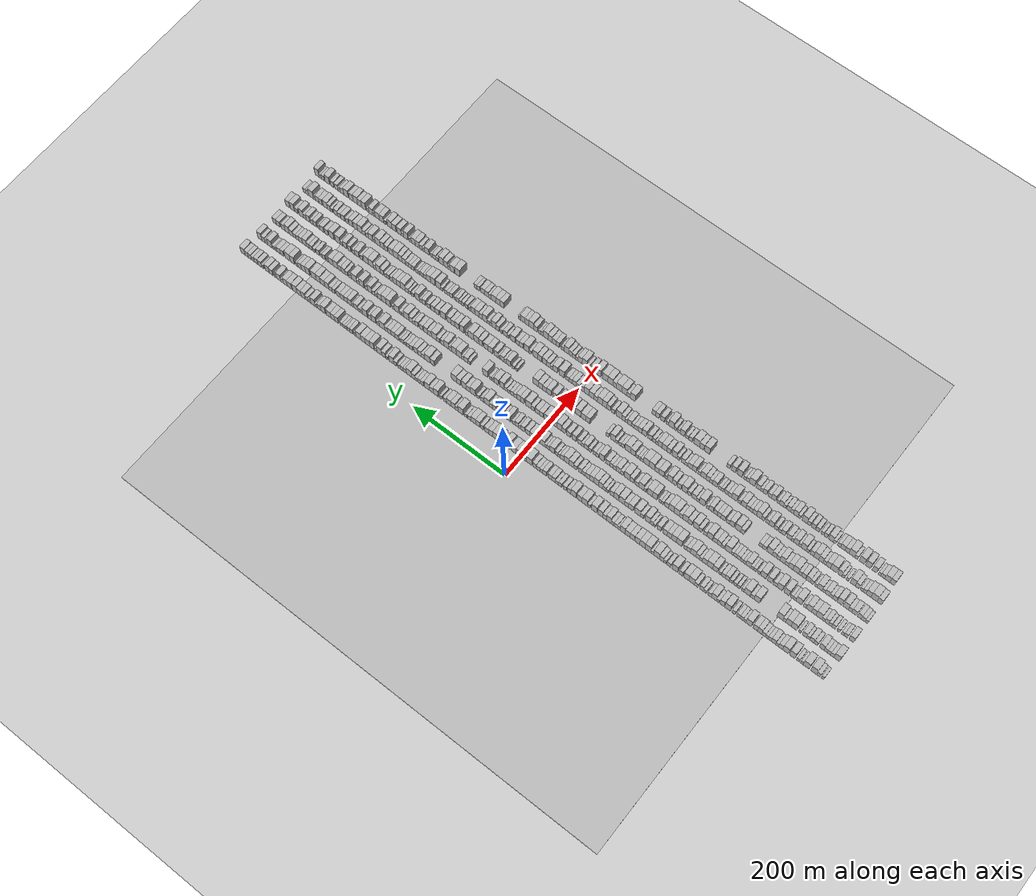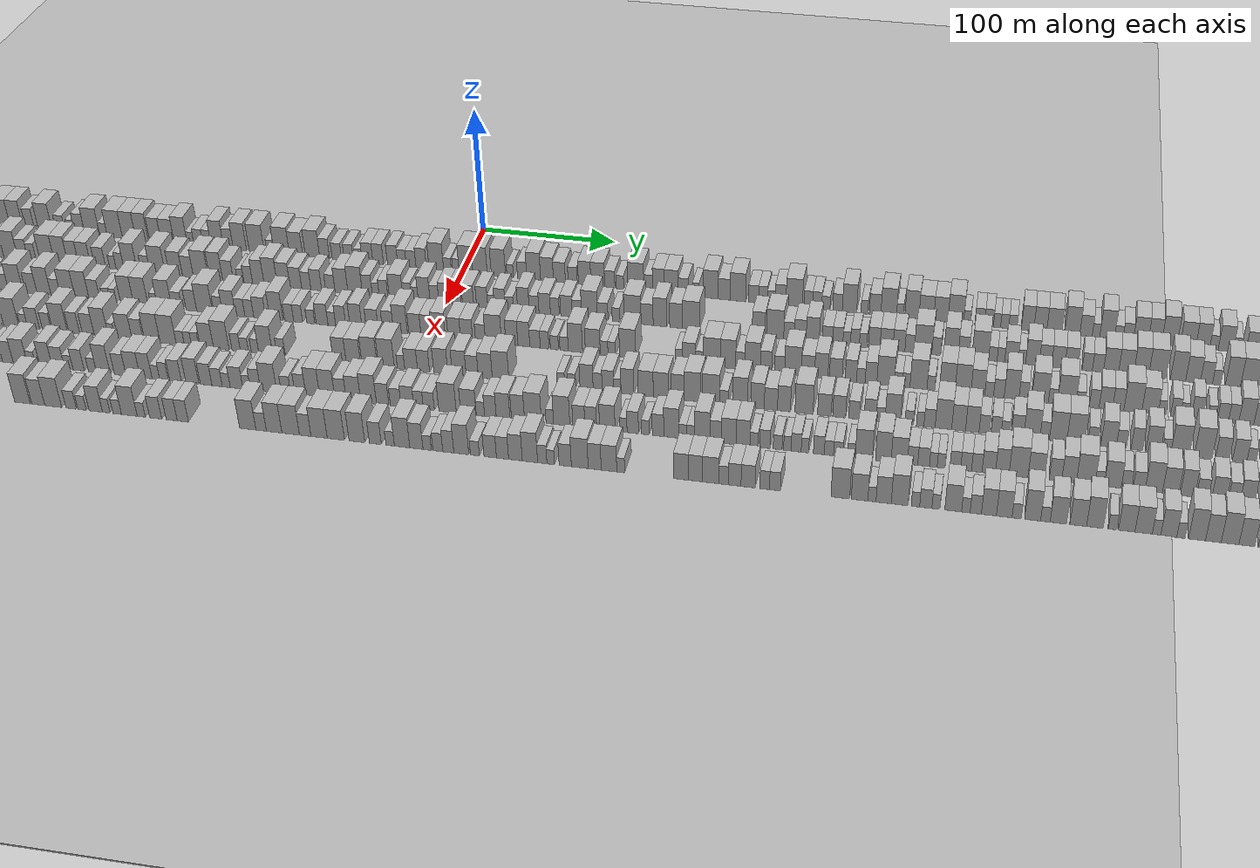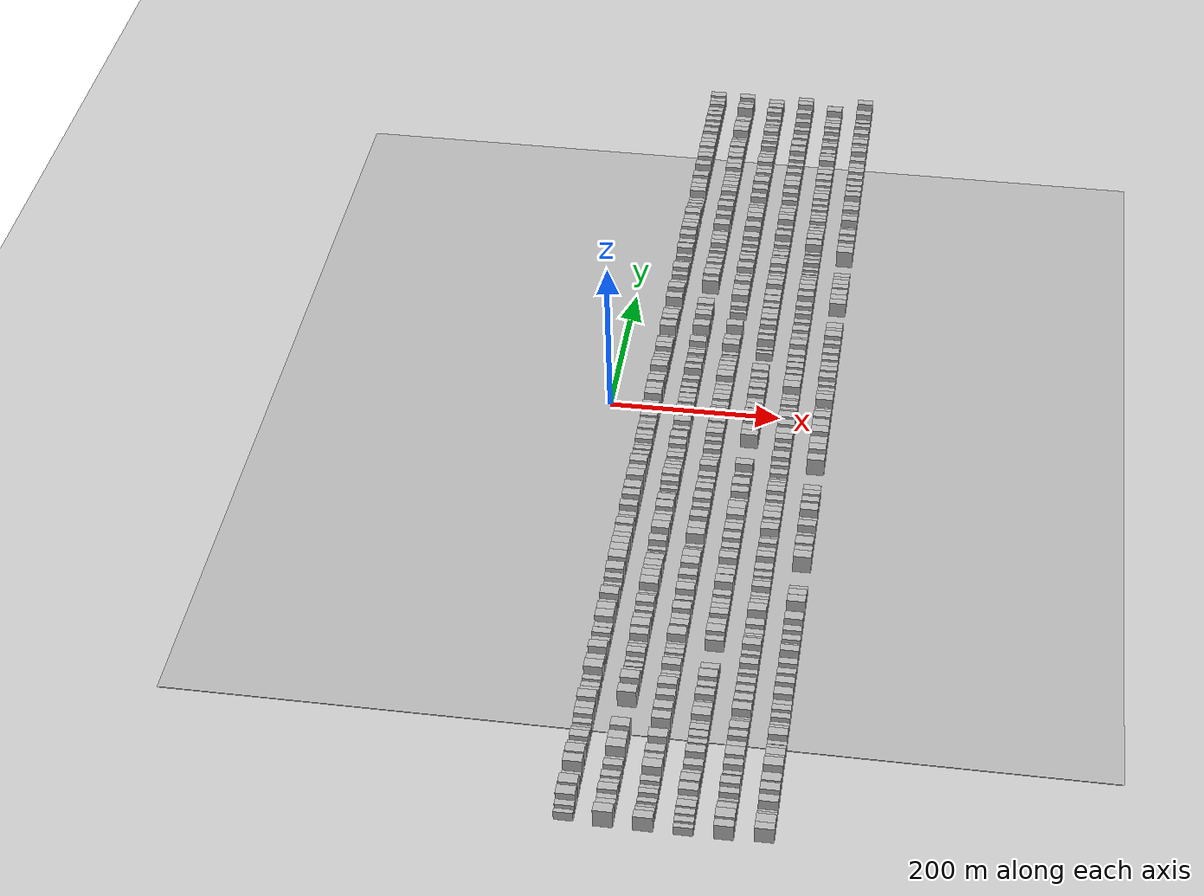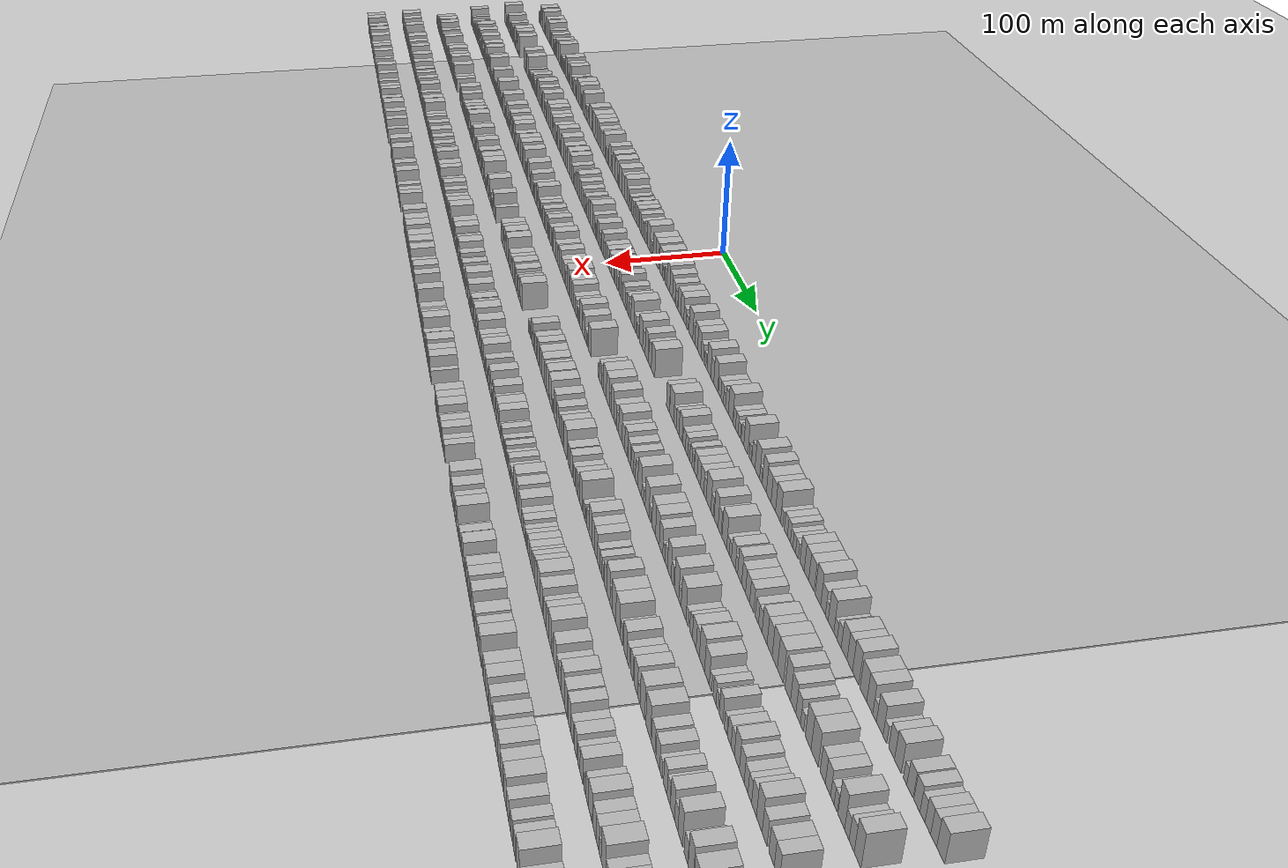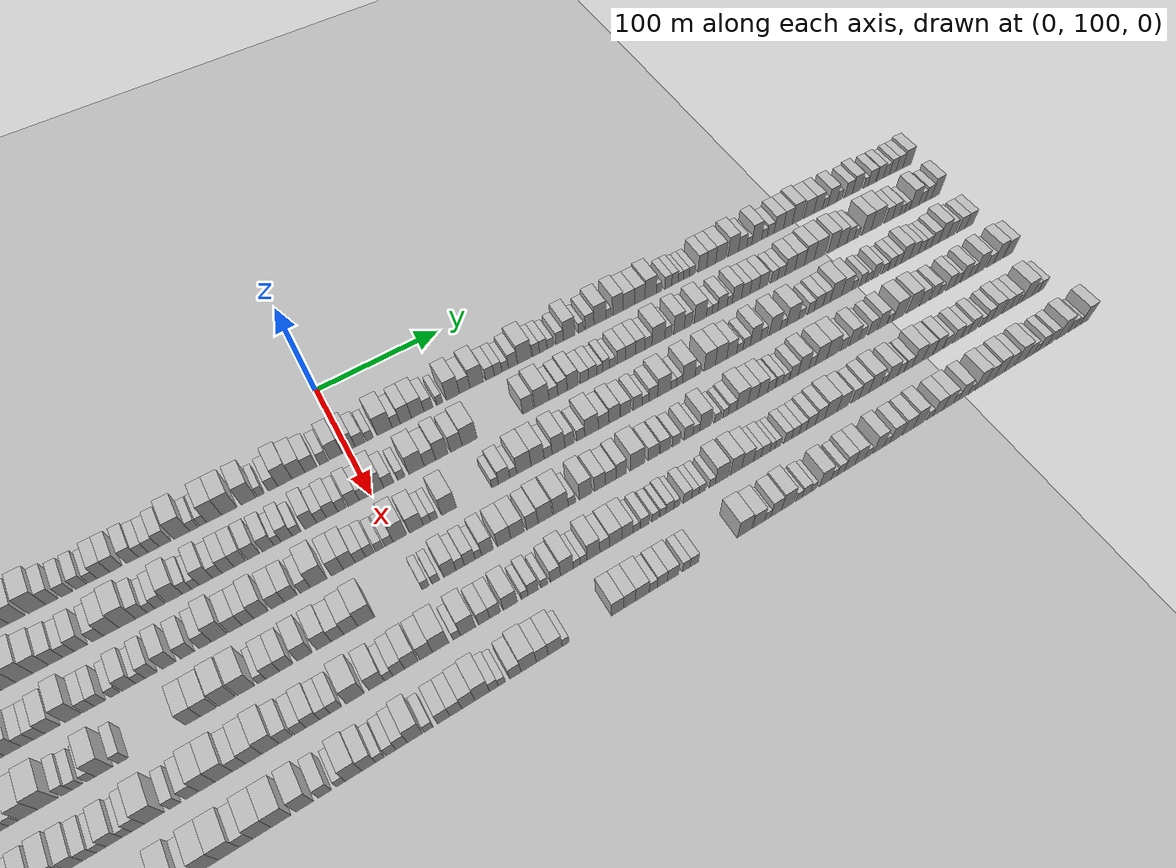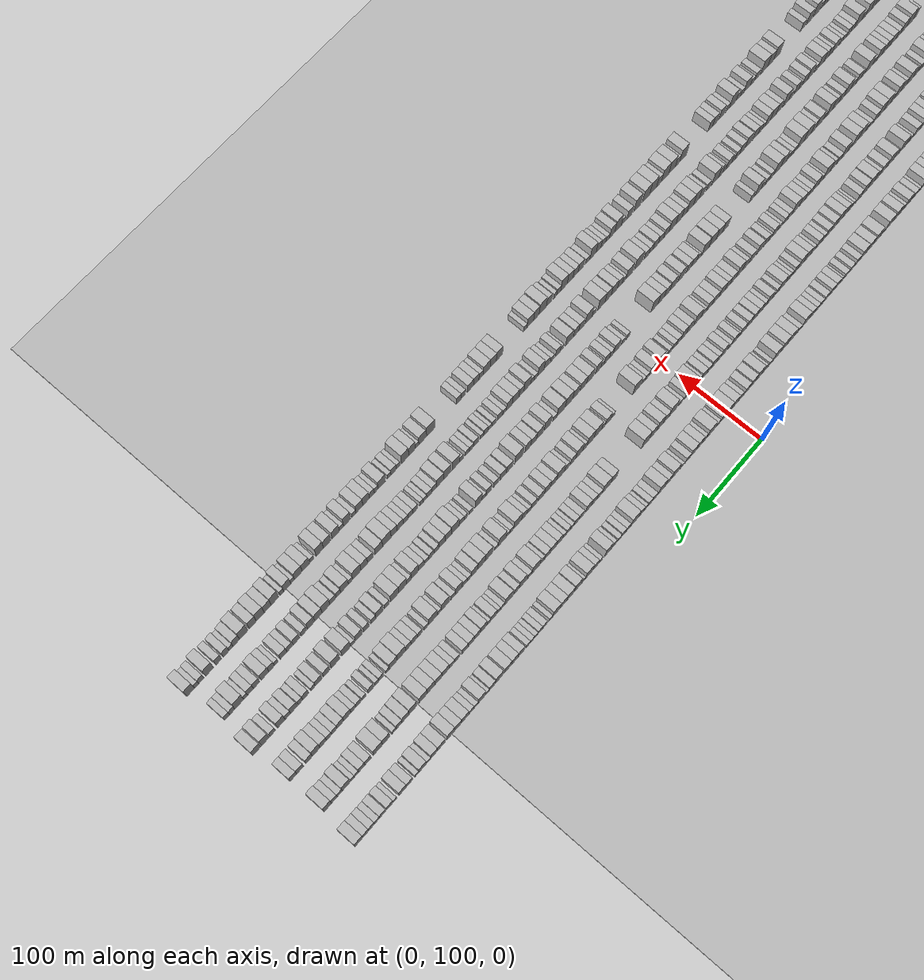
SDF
<?xml version="1.0" encoding="utf-8"?>

<sdf version="1.6">

   <world name="default">

      <gui fullscreen="0">

         <camera name="user_camera">

            <pose>-15 0 4.57585 0 0 0</pose>

            <view_controller>orbit</view_controller>

         </camera>

      </gui>

      <scene>

         <sky>

           <clouds>

             <speed>12</speed>

           </clouds>

         </sky>

         <ambient>0.4 0.4 0.4 1</ambient>

         <background>0.7 0.7 0.7 1</background>

         <shadows>1</shadows>

      </scene>

      <gravity>0 0 -9.8066</gravity>

      <magnetic_field>6e-06 2.3e-05 -4.2e-05</magnetic_field>

      <physics default="0" name="default_physics" type="ode">

         <ode>

            <solver>

               <type>quick</type>

               <iters>10</iters>

               <sor>1.0</sor>

               <use_dynamic_moi_rescaling>0</use_dynamic_moi_rescaling>

            </solver>

            <constraints>

               <cfm>0</cfm>

               <erp>0.2</erp>

               <contact_max_correcting_vel>100</contact_max_correcting_vel>

               <contact_surface_layer>0.001</contact_surface_layer>

            </constraints>

         </ode>

         <max_step_size>0.004</max_step_size>

         <real_time_factor>1</real_time_factor>

         <real_time_update_rate>250</real_time_update_rate>

      </physics>

      <light name="sun" type="directional">

         <cast_shadows>1</cast_shadows>

         <pose>0 0 10 0 0 0</pose>

         <diffuse>0.8 0.8 0.8 1</diffuse>

         <specular>0.2 0.2 0.2 1</specular>

         <attenuation>

            <range>1000</range>

            <constant>0.9</constant>

            <linear>0.01</linear>

            <quadratic>0.001</quadratic>

         </attenuation>

         <direction>-0.5 0.1 -0.9</direction>

      </light>

      <include>

         <name>ground_plane_1</name>

         <uri>model://HANNAS_ground_plane</uri>

         <pose>0 0 0  0 0 0</pose>

      </include>

      <include>

         <name>ground_plane_2</name>

         <uri>model://HANNAS_ground_plane</uri>

         <pose>100 0 0  0 0 0</pose>

      </include>

      <model name="building_1">

         <static>1</static>

         <pose frame="">50.0000 -614.5046 0 0.000000 0.000000 0.000000</pose>

         <link name="link">

            <pose frame="">0 0 6.00 0 0 0</pose>

            <collision name="collision">

               <geometry>

                  <box>

                     <size>20.0000 4.9908 12.0000</size>

                  </box>

               </geometry>

               <max_contacts>10</max_contacts>

               <surface>

                  <contact>

                     <ode/>

                  </contact>

                  <bounce/>

                  <friction>

                     <torsional>

                        <ode/>

                     </torsional>

                     <ode/>

                  </friction>

               </surface>

            </collision>

            <visual name="visual">

               <cast_shadows>0</cast_shadows>

               <geometry>

                  <box>

                     <size>20.0000 4.9908 12.0000</size>

                  </box>

               </geometry>

               <material>

                  <script>

                     <uri>model://HANNAS_wall/materials/scripts</uri>

                     <uri>model://HANNAS_wall/materials/textures</uri>

                     <name>vrc/HANNAS_wall</name>

                  </script>

               </material>

            </visual>

            <self_collide>0</self_collide>

            <enable_wind>0</enable_wind>

            <kinematic>0</kinematic>

         </link>

      </model>

      <model name="building_2">

         <static>1</static>

         <pose frame="">50.0000 -606.5619 0 0.000000 0.000000 0.000000</pose>

         <link name="link">

            <pose frame="">0 0 7.50 0 0 0</pose>

            <collision name="collision">

               <geometry>

                  <box>

                     <size>20.0000 6.8945 15.0000</size>

                  </box>

               </geometry>

               <max_contacts>10</max_contacts>

               <surface>

                  <contact>

                     <ode/>

                  </contact>

                  <bounce/>

                  <friction>

                     <torsional>

                        <ode/>

                     </torsional>

                     <ode/>

                  </friction>

               </surface>

            </collision>

            <visual name="visual">

               <cast_shadows>0</cast_shadows>

               <geometry>

                  <box>

                     <size>20.0000 6.8945 15.0000</size>

                  </box>

               </geometry>

               <material>

                  <script>

                     <uri>model://HANNAS_wall/materials/scripts</uri>

                     <uri>model://HANNAS_wall/materials/textures</uri>

                     <name>vrc/HANNAS_wall</name>

                  </script>

               </material>

            </visual>

            <self_collide>0</self_collide>

            <enable_wind>0</enable_wind>

            <kinematic>0</kinematic>

         </link>

      </model>

      <model name="building_3">

         <static>1</static>

         <pose frame="">50.0000 -597.4224 0 0.000000 0.000000 0.000000</pose>

         <link name="link">

            <pose frame="">0 0 12.00 0 0 0</pose>

            <collision name="collision">

               <geometry>

                  <box>

                     <size>20.0000 11.3844 24.0000</size>

                  </box>

               </geometry>

               <max_contacts>10</max_contacts>

               <surface>

                  <contact>

                     <ode/>

                  </contact>

                  <bounce/>

                  <friction>

                     <torsional>

                        <ode/>

                     </torsional>

                     <ode/>

                  </friction>

               </surface>

            </collision>

            <visual name="visual">

               <cast_shadows>0</cast_shadows>

               <geometry>

                  <box>

                     <size>20.0000 11.3844 24.0000</size>

                  </box>

               </geometry>

               <material>

                  <script>

                     <uri>model://HANNAS_wall/materials/scripts</uri>

                     <uri>model://HANNAS_wall/materials/textures</uri>

                     <name>vrc/HANNAS_wall</name>

                  </script>

               </material>

            </visual>

            <self_collide>0</self_collide>

            <enable_wind>0</enable_wind>

            <kinematic>0</kinematic>

         </link>

      </model>

      <model name="building_4">

         <static>1</static>

         <pose frame="">50.0000 -582.8274 0 0.000000 0.000000 0.000000</pose>

         <link name="link">

            <pose frame="">0 0 12.00 0 0 0</pose>

            <collision name="collision">

               <geometry>

                  <box>

                     <size>20.0000 11.8056 24.0000</size>

                  </box>

               </geometry>

               <max_contacts>10</max_contacts>

               <surface>

                  <contact>

                     <ode/>

                  </contact>

                  <bounce/>

                  <friction>

                     <torsional>

                        <ode/>

                     </torsional>

                     <ode/>

                  </friction>

               </surface>

            </collision>

            <visual name="visual">

               <cast_shadows>0</cast_shadows>

               <geometry>

                  <box>

                     <size>20.0000 11.8056 24.0000</size>

                  </box>

               </geometry>

               <material>

                  <script>

                     <uri>model://HANNAS_wall/materials/scripts</uri>

                     <uri>model://HANNAS_wall/materials/textures</uri>

                     <name>vrc/HANNAS_wall</name>

                  </script>

               </material>

            </visual>

            <self_collide>0</self_collide>

            <enable_wind>0</enable_wind>

            <kinematic>0</kinematic>

         </link>

      </model>

      <model name="building_5">

         <static>1</static>

         <pose frame="">50.0000 -574.3993 0 0.000000 0.000000 0.000000</pose>

         <link name="link">

            <pose frame="">0 0 6.00 0 0 0</pose>

            <collision name="collision">

               <geometry>

                  <box>

                     <size>20.0000 5.0505 12.0000</size>

                  </box>

               </geometry>

               <max_contacts>10</max_contacts>

               <surface>

                  <contact>

                     <ode/>

                  </contact>

                  <bounce/>

                  <friction>

                     <torsional>

                        <ode/>

                     </torsional>

                     <ode/>

                  </friction>

               </surface>

            </collision>

            <visual name="visual">

               <cast_shadows>0</cast_shadows>

               <geometry>

                  <box>

                     <size>20.0000 5.0505 12.0000</size>

                  </box>

               </geometry>

               <material>

                  <script>

                     <uri>model://HANNAS_wall/materials/scripts</uri>

                     <uri>model://HANNAS_wall/materials/textures</uri>

                     <name>vrc/HANNAS_wall</name>

                  </script>

               </material>

            </visual>

            <self_collide>0</self_collide>

            <enable_wind>0</enable_wind>

            <kinematic>0</kinematic>

         </link>

      </model>

      <model name="building_6">

         <static>1</static>

         <pose frame="">50.0000 -566.9865 0 0.000000 0.000000 0.000000</pose>

         <link name="link">

            <pose frame="">0 0 6.00 0 0 0</pose>

            <collision name="collision">

               <geometry>

                  <box>

                     <size>20.0000 5.7753 12.0000</size>

                  </box>

               </geometry>

               <max_contacts>10</max_contacts>

               <surface>

                  <contact>

                     <ode/>

                  </contact>

                  <bounce/>

                  <friction>

                     <torsional>

                        <ode/>

                     </torsional>

                     <ode/>

                  </friction>

               </surface>

            </collision>

            <visual name="visual">

               <cast_shadows>0</cast_shadows>

               <geometry>

                  <box>

                     <size>20.0000 5.7753 12.0000</size>

                  </box>

               </geometry>

               <material>

                  <script>

                     <uri>model://HANNAS_wall/materials/scripts</uri>

                     <uri>model://HANNAS_wall/materials/textures</uri>

                     <name>vrc/HANNAS_wall</name>

                  </script>

               </material>

            </visual>

            <self_collide>0</self_collide>

            <enable_wind>0</enable_wind>

            <kinematic>0</kinematic>

         </link>

      </model>

      <model name="building_7">

         <static>1</static>

         <pose frame="">50.0000 -555.8070 0 0.000000 0.000000 0.000000</pose>

         <link name="link">

            <pose frame="">0 0 12.00 0 0 0</pose>

            <collision name="collision">

               <geometry>

                  <box>

                     <size>20.0000 10.5837 24.0000</size>

                  </box>

               </geometry>

               <max_contacts>10</max_contacts>

               <surface>

                  <contact>

                     <ode/>

                  </contact>

                  <bounce/>

                  <friction>

                     <torsional>

                        <ode/>

                     </torsional>

                     <ode/>

                  </friction>

               </surface>

            </collision>

            <visual name="visual">

               <cast_shadows>0</cast_shadows>

               <geometry>

                  <box>

                     <size>20.0000 10.5837 24.0000</size>

                  </box>

               </geometry>

               <material>

                  <script>

                     <uri>model://HANNAS_wall/materials/scripts</uri>

                     <uri>model://HANNAS_wall/materials/textures</uri>

                     <name>vrc/HANNAS_wall</name>

                  </script>

               </material>

            </visual>

            <self_collide>0</self_collide>

            <enable_wind>0</enable_wind>

            <kinematic>0</kinematic>

         </link>

      </model>

      <model name="building_8">

         <static>1</static>

         <pose frame="">50.0000 -542.8722 0 0.000000 0.000000 0.000000</pose>

         <link name="link">

            <pose frame="">0 0 12.00 0 0 0</pose>

            <collision name="collision">

               <geometry>

                  <box>

                     <size>20.0000 11.2858 24.0000</size>

                  </box>

               </geometry>

               <max_contacts>10</max_contacts>

               <surface>

                  <contact>

                     <ode/>

                  </contact>

                  <bounce/>

                  <friction>

                     <torsional>

                        <ode/>

                     </torsional>

                     <ode/>

                  </friction>

               </surface>

            </collision>

            <visual name="visual">

               <cast_shadows>0</cast_shadows>

               <geometry>

                  <box>

                     <size>20.0000 11.2858 24.0000</size>

                  </box>

               </geometry>

               <material>

                  <script>

                     <uri>model://HANNAS_wall/materials/scripts</uri>

                     <uri>model://HANNAS_wall/materials/textures</uri>

                     <name>vrc/HANNAS_wall</name>

                  </script>

               </material>

            </visual>

            <self_collide>0</self_collide>

            <enable_wind>0</enable_wind>

            <kinematic>0</kinematic>

         </link>

      </model>

      <model name="building_9">

         <static>1</static>

         <pose frame="">50.0000 -533.1352 0 0.000000 0.000000 0.000000</pose>

         <link name="link">

            <pose frame="">0 0 9.00 0 0 0</pose>

            <collision name="collision">

               <geometry>

                  <box>

                     <size>20.0000 8.1882 18.0000</size>

                  </box>

               </geometry>

               <max_contacts>10</max_contacts>

               <surface>

                  <contact>

                     <ode/>

                  </contact>

                  <bounce/>

                  <friction>

                     <torsional>

                        <ode/>

                     </torsional>

                     <ode/>

                  </friction>

               </surface>

            </collision>

            <visual name="visual">

               <cast_shadows>0</cast_shadows>

               <geometry>

                  <box>

                     <size>20.0000 8.1882 18.0000</size>

                  </box>

               </geometry>

               <material>

                  <script>

                     <uri>model://HANNAS_wall/materials/scripts</uri>

                     <uri>model://HANNAS_wall/materials/textures</uri>

                     <name>vrc/HANNAS_wall</name>

                  </script>

               </material>

            </visual>

            <self_collide>0</self_collide>

            <enable_wind>0</enable_wind>

            <kinematic>0</kinematic>

         </link>

      </model>

      <model name="building_10">

         <static>1</static>

         <pose frame="">50.0000 -526.2337 0 0.000000 0.000000 0.000000</pose>

         <link name="link">

            <pose frame="">0 0 6.00 0 0 0</pose>

            <collision name="collision">

               <geometry>

                  <box>

                     <size>20.0000 5.6149 12.0000</size>

                  </box>

               </geometry>

               <max_contacts>10</max_contacts>

               <surface>

                  <contact>

                     <ode/>

                  </contact>

                  <bounce/>

                  <friction>

                     <torsional>

                        <ode/>

                     </torsional>

                     <ode/>

                  </friction>

               </surface>

            </collision>

            <visual name="visual">

               <cast_shadows>0</cast_shadows>

               <geometry>

                  <box>

                     <size>20.0000 5.6149 12.0000</size>

                  </box>

               </geometry>

               <material>

                  <script>

                     <uri>model://HANNAS_wall/materials/scripts</uri>

                     <uri>model://HANNAS_wall/materials/textures</uri>

                     <name>vrc/HANNAS_wall</name>

                  </script>

               </material>

            </visual>

            <self_collide>0</self_collide>

            <enable_wind>0</enable_wind>

            <kinematic>0</kinematic>

         </link>

      </model>

      <model name="building_11">

         <static>1</static>

         <pose frame="">50.0000 -518.9357 0 0.000000 0.000000 0.000000</pose>

         <link name="link">

            <pose frame="">0 0 9.00 0 0 0</pose>

            <collision name="collision">

               <geometry>

                  <box>

                     <size>20.0000 8.9811 18.0000</size>

                  </box>

               </geometry>

               <max_contacts>10</max_contacts>

               <surface>

                  <contact>

                     <ode/>

                  </contact>

                  <bounce/>

                  <friction>

                     <torsional>

                        <ode/>

                     </torsional>

                     <ode/>

                  </friction>

               </surface>

            </collision>

            <visual name="visual">

               <cast_shadows>0</cast_shadows>

               <geometry>

                  <box>

                     <size>20.0000 8.9811 18.0000</size>

                  </box>

               </geometry>

               <material>

                  <script>

                     <uri>model://HANNAS_wall/materials/scripts</uri>

                     <uri>model://HANNAS_wall/materials/textures</uri>

                     <name>vrc/HANNAS_wall</name>

                  </script>

               </material>

            </visual>

            <self_collide>0</self_collide>

            <enable_wind>0</enable_wind>

            <kinematic>0</kinematic>

         </link>

      </model>

      <model name="building_12">

         <static>1</static>

         <pose frame="">50.0000 -511.2746 0 0.000000 0.000000 0.000000</pose>

         <link name="link">

            <pose frame="">0 0 7.50 0 0 0</pose>

            <collision name="collision">

               <geometry>

                  <box>

                     <size>20.0000 6.3411 15.0000</size>

                  </box>

               </geometry>

               <max_contacts>10</max_contacts>

               <surface>

                  <contact>

                     <ode/>

                  </contact>

                  <bounce/>

                  <friction>

                     <torsional>

                        <ode/>

                     </torsional>

                     <ode/>

                  </friction>

               </surface>

            </collision>

            <visual name="visual">

               <cast_shadows>0</cast_shadows>

               <geometry>

                  <box>

                     <size>20.0000 6.3411 15.0000</size>

                  </box>

               </geometry>

               <material>

                  <script>

                     <uri>model://HANNAS_wall/materials/scripts</uri>

                     <uri>model://HANNAS_wall/materials/textures</uri>

                     <name>vrc/HANNAS_wall</name>

                  </script>

               </material>

            </visual>

            <self_collide>0</self_collide>

            <enable_wind>0</enable_wind>

            <kinematic>0</kinematic>

         </link>

      </model>

      <model name="building_13">

         <static>1</static>

         <pose frame="">50.0000 -505.5607 0 0.000000 0.000000 0.000000</pose>

         <link name="link">

            <pose frame="">0 0 6.00 0 0 0</pose>

            <collision name="collision">

               <geometry>

                  <box>

                     <size>20.0000 5.0867 12.0000</size>

                  </box>

               </geometry>

               <max_contacts>10</max_contacts>

               <surface>

                  <contact>

                     <ode/>

                  </contact>

                  <bounce/>

                  <friction>

                     <torsional>

                        <ode/>

                     </torsional>

                     <ode/>

                  </friction>

               </surface>

            </collision>

            <visual name="visual">

               <cast_shadows>0</cast_shadows>

               <geometry>

                  <box>

                     <size>20.0000 5.0867 12.0000</size>

                  </box>

               </geometry>

               <material>

                  <script>

                     <uri>model://HANNAS_wall/materials/scripts</uri>

                     <uri>model://HANNAS_wall/materials/textures</uri>

                     <name>vrc/HANNAS_wall</name>

                  </script>

               </material>

            </visual>

            <self_collide>0</self_collide>

            <enable_wind>0</enable_wind>

            <kinematic>0</kinematic>

         </link>

      </model>

      <model name="building_14">

         <static>1</static>

         <pose frame="">50.0000 -499.5137 0 0.000000 0.000000 0.000000</pose>

         <link name="link">

            <pose frame="">0 0 7.50 0 0 0</pose>

            <collision name="collision">

               <geometry>

                  <box>

                     <size>20.0000 7.0072 15.0000</size>

                  </box>

               </geometry>

               <max_contacts>10</max_contacts>

               <surface>

                  <contact>

                     <ode/>

                  </contact>

                  <bounce/>

                  <friction>

                     <torsional>

                        <ode/>

                     </torsional>

                     <ode/>

                  </friction>

               </surface>

            </collision>

            <visual name="visual">

               <cast_shadows>0</cast_shadows>

               <geometry>

                  <box>

                     <size>20.0000 7.0072 15.0000</size>

                  </box>

               </geometry>

               <material>

                  <script>

                     <uri>model://HANNAS_wall/materials/scripts</uri>

                     <uri>model://HANNAS_wall/materials/textures</uri>

                     <name>vrc/HANNAS_wall</name>

                  </script>

               </material>

            </visual>

            <self_collide>0</self_collide>

            <enable_wind>0</enable_wind>

            <kinematic>0</kinematic>

         </link>

      </model>

      <model name="building_15">

         <static>1</static>

         <pose frame="">50.0000 -491.7974 0 0.000000 0.000000 0.000000</pose>

         <link name="link">

            <pose frame="">0 0 10.50 0 0 0</pose>

            <collision name="collision">

               <geometry>

                  <box>

                     <size>20.0000 8.4254 21.0000</size>

                  </box>

               </geometry>

               <max_contacts>10</max_contacts>

               <surface>

                  <contact>

                     <ode/>

                  </contact>

                  <bounce/>

                  <friction>

                     <torsional>

                        <ode/>

                     </torsional>

                     <ode/>

                  </friction>

               </surface>

            </collision>

            <visual name="visual">

               <cast_shadows>0</cast_shadows>

               <geometry>

                  <box>

                     <size>20.0000 8.4254 21.0000</size>

                  </box>

               </geometry>

               <material>

                  <script>

                     <uri>model://HANNAS_wall/materials/scripts</uri>

                     <uri>model://HANNAS_wall/materials/textures</uri>

                     <name>vrc/HANNAS_wall</name>

                  </script>

               </material>

            </visual>

            <self_collide>0</self_collide>

            <enable_wind>0</enable_wind>

            <kinematic>0</kinematic>

         </link>

      </model>

      <model name="building_16">

         <static>1</static>

         <pose frame="">50.0000 -483.1295 0 0.000000 0.000000 0.000000</pose>

         <link name="link">

            <pose frame="">0 0 10.50 0 0 0</pose>

            <collision name="collision">

               <geometry>

                  <box>

                     <size>20.0000 8.9103 21.0000</size>

                  </box>

               </geometry>

               <max_contacts>10</max_contacts>

               <surface>

                  <contact>

                     <ode/>

                  </contact>

                  <bounce/>

                  <friction>

                     <torsional>

                        <ode/>

                     </torsional>

                     <ode/>

                  </friction>

               </surface>

            </collision>

            <visual name="visual">

               <cast_shadows>0</cast_shadows>

               <geometry>

                  <box>

                     <size>20.0000 8.9103 21.0000</size>

                  </box>

               </geometry>

               <material>

                  <script>

                     <uri>model://HANNAS_wall/materials/scripts</uri>

                     <uri>model://HANNAS_wall/materials/textures</uri>

                     <name>vrc/HANNAS_wall</name>

                  </script>

               </material>

            </visual>

            <self_collide>0</self_collide>

            <enable_wind>0</enable_wind>

            <kinematic>0</kinematic>

         </link>

      </model>

      <model name="building_17">

         <static>1</static>

         <pose frame="">50.0000 -470.2435 0 0.000000 0.000000 0.000000</pose>

         <link name="link">

            <pose frame="">0 0 12.00 0 0 0</pose>

            <collision name="collision">

               <geometry>

                  <box>

                     <size>20.0000 10.8619 24.0000</size>

                  </box>

               </geometry>

               <max_contacts>10</max_contacts>

               <surface>

                  <contact>

                     <ode/>

                  </contact>

                  <bounce/>

                  <friction>

                     <torsional>

                        <ode/>

                     </torsional>

                     <ode/>

                  </friction>

               </surface>

            </collision>

            <visual name="visual">

               <cast_shadows>0</cast_shadows>

               <geometry>

                  <box>

                     <size>20.0000 10.8619 24.0000</size>

                  </box>

               </geometry>

               <material>

                  <script>

                     <uri>model://HANNAS_wall/materials/scripts</uri>

                     <uri>model://HANNAS_wall/materials/textures</uri>

                     <name>vrc/HANNAS_wall</name>

                  </script>

               </material>

            </visual>

            <self_collide>0</self_collide>

            <enable_wind>0</enable_wind>

            <kinematic>0</kinematic>

         </link>

      </model>

      <model name="building_18">

         <static>1</static>

         <pose frame="">50.0000 -462.1302 0 0.000000 0.000000 0.000000</pose>

         <link name="link">

            <pose frame="">0 0 6.00 0 0 0</pose>

            <collision name="collision">

               <geometry>

                  <box>

                     <size>20.0000 5.3646 12.0000</size>

                  </box>

               </geometry>

               <max_contacts>10</max_contacts>

               <surface>

                  <contact>

                     <ode/>

                  </contact>

                  <bounce/>

                  <friction>

                     <torsional>

                        <ode/>

                     </torsional>

                     <ode/>

                  </friction>

               </surface>

            </collision>

            <visual name="visual">

               <cast_shadows>0</cast_shadows>

               <geometry>

                  <box>

                     <size>20.0000 5.3646 12.0000</size>

                  </box>

               </geometry>

               <material>

                  <script>

                     <uri>model://HANNAS_wall/materials/scripts</uri>

                     <uri>model://HANNAS_wall/materials/textures</uri>

                     <name>vrc/HANNAS_wall</name>

                  </script>

               </material>

            </visual>

            <self_collide>0</self_collide>

            <enable_wind>0</enable_wind>

            <kinematic>0</kinematic>

         </link>

      </model>

      <model name="building_19">

         <static>1</static>

         <pose frame="">50.0000 -456.2409 0 0.000000 0.000000 0.000000</pose>

         <link name="link">

            <pose frame="">0 0 7.50 0 0 0</pose>

            <collision name="collision">

               <geometry>

                  <box>

                     <size>20.0000 6.4140 15.0000</size>

                  </box>

               </geometry>

               <max_contacts>10</max_contacts>

               <surface>

                  <contact>

                     <ode/>

                  </contact>

                  <bounce/>

                  <friction>

                     <torsional>

                        <ode/>

                     </torsional>

                     <ode/>

                  </friction>

               </surface>

            </collision>

            <visual name="visual">

               <cast_shadows>0</cast_shadows>

               <geometry>

                  <box>

                     <size>20.0000 6.4140 15.0000</size>

                  </box>

               </geometry>

               <material>

                  <script>

                     <uri>model://HANNAS_wall/materials/scripts</uri>

                     <uri>model://HANNAS_wall/materials/textures</uri>

                     <name>vrc/HANNAS_wall</name>

                  </script>

               </material>

            </visual>

            <self_collide>0</self_collide>

            <enable_wind>0</enable_wind>

            <kinematic>0</kinematic>

         </link>

      </model>

      <model name="building_20">

         <static>1</static>

         <pose frame="">50.0000 -449.6966 0 0.000000 0.000000 0.000000</pose>

         <link name="link">

            <pose frame="">0 0 7.50 0 0 0</pose>

            <collision name="collision">

               <geometry>

                  <box>

                     <size>20.0000 6.6747 15.0000</size>

                  </box>

               </geometry>

               <max_contacts>10</max_contacts>

               <surface>

                  <contact>

                     <ode/>

                  </contact>

                  <bounce/>

                  <friction>

                     <torsional>

                        <ode/>

                     </torsional>

                     <ode/>

                  </friction>

               </surface>

            </collision>

            <visual name="visual">

               <cast_shadows>0</cast_shadows>

               <geometry>

                  <box>

                     <size>20.0000 6.6747 15.0000</size>

                  </box>

               </geometry>

               <material>

                  <script>

                     <uri>model://HANNAS_wall/materials/scripts</uri>

                     <uri>model://HANNAS_wall/materials/textures</uri>

                     <name>vrc/HANNAS_wall</name>

                  </script>

               </material>

            </visual>

            <self_collide>0</self_collide>

            <enable_wind>0</enable_wind>

            <kinematic>0</kinematic>

         </link>

      </model>

      <model name="building_21">

         <static>1</static>

         <pose frame="">50.0000 -440.1250 0 0.000000 0.000000 0.000000</pose>

         <link name="link">

            <pose frame="">0 0 7.50 0 0 0</pose>

            <collision name="collision">

               <geometry>

                  <box>

                     <size>20.0000 6.4684 15.0000</size>

                  </box>

               </geometry>

               <max_contacts>10</max_contacts>

               <surface>

                  <contact>

                     <ode/>

                  </contact>

                  <bounce/>

                  <friction>

                     <torsional>

                        <ode/>

                     </torsional>

                     <ode/>

                  </friction>

               </surface>

            </collision>

            <visual name="visual">

               <cast_shadows>0</cast_shadows>

               <geometry>

                  <box>

                     <size>20.0000 6.4684 15.0000</size>

                  </box>

               </geometry>

               <material>

                  <script>

                     <uri>model://HANNAS_wall/materials/scripts</uri>

                     <uri>model://HANNAS_wall/materials/textures</uri>

                     <name>vrc/HANNAS_wall</name>

                  </script>

               </material>

            </visual>

            <self_collide>0</self_collide>

            <enable_wind>0</enable_wind>

            <kinematic>0</kinematic>

         </link>

      </model>

      <model name="building_22">

         <static>1</static>

         <pose frame="">50.0000 -428.1693 0 0.000000 0.000000 0.000000</pose>

         <link name="link">

            <pose frame="">0 0 12.00 0 0 0</pose>

            <collision name="collision">

               <geometry>

                  <box>

                     <size>20.0000 11.4430 24.0000</size>

                  </box>

               </geometry>

               <max_contacts>10</max_contacts>

               <surface>

                  <contact>

                     <ode/>

                  </contact>

                  <bounce/>

                  <friction>

                     <torsional>

                        <ode/>

                     </torsional>

                     <ode/>

                  </friction>

               </surface>

            </collision>

            <visual name="visual">

               <cast_shadows>0</cast_shadows>

               <geometry>

                  <box>

                     <size>20.0000 11.4430 24.0000</size>

                  </box>

               </geometry>

               <material>

                  <script>

                     <uri>model://HANNAS_wall/materials/scripts</uri>

                     <uri>model://HANNAS_wall/materials/textures</uri>

                     <name>vrc/HANNAS_wall</name>

                  </script>

               </material>

            </visual>

            <self_collide>0</self_collide>

            <enable_wind>0</enable_wind>

            <kinematic>0</kinematic>

         </link>

      </model>

      <model name="building_23">

         <static>1</static>

         <pose frame="">50.0000 -416.9795 0 0.000000 0.000000 0.000000</pose>

         <link name="link">

            <pose frame="">0 0 10.50 0 0 0</pose>

            <collision name="collision">

               <geometry>

                  <box>

                     <size>20.0000 8.9366 21.0000</size>

                  </box>

               </geometry>

               <max_contacts>10</max_contacts>

               <surface>

                  <contact>

                     <ode/>

                  </contact>

                  <bounce/>

                  <friction>

                     <torsional>

                        <ode/>

                     </torsional>

                     <ode/>

                  </friction>

               </surface>

            </collision>

            <visual name="visual">

               <cast_shadows>0</cast_shadows>

               <geometry>

                  <box>

                     <size>20.0000 8.9366 21.0000</size>

                  </box>

               </geometry>

               <material>

                  <script>

                     <uri>model://HANNAS_wall/materials/scripts</uri>

                     <uri>model://HANNAS_wall/materials/textures</uri>

                     <name>vrc/HANNAS_wall</name>

                  </script>

               </material>

            </visual>

            <self_collide>0</self_collide>

            <enable_wind>0</enable_wind>

            <kinematic>0</kinematic>

         </link>

      </model>

      <model name="building_24">

         <static>1</static>

         <pose frame="">50.0000 -408.6241 0 0.000000 0.000000 0.000000</pose>

         <link name="link">

            <pose frame="">0 0 6.00 0 0 0</pose>

            <collision name="collision">

               <geometry>

                  <box>

                     <size>20.0000 5.7742 12.0000</size>

                  </box>

               </geometry>

               <max_contacts>10</max_contacts>

               <surface>

                  <contact>

                     <ode/>

                  </contact>

                  <bounce/>

                  <friction>

                     <torsional>

                        <ode/>

                     </torsional>

                     <ode/>

                  </friction>

               </surface>

            </collision>

            <visual name="visual">

               <cast_shadows>0</cast_shadows>

               <geometry>

                  <box>

                     <size>20.0000 5.7742 12.0000</size>

                  </box>

               </geometry>

               <material>

                  <script>

                     <uri>model://HANNAS_wall/materials/scripts</uri>

                     <uri>model://HANNAS_wall/materials/textures</uri>

                     <name>vrc/HANNAS_wall</name>

                  </script>

               </material>

            </visual>

            <self_collide>0</self_collide>

            <enable_wind>0</enable_wind>

            <kinematic>0</kinematic>

         </link>

      </model>

      <model name="building_25">

         <static>1</static>

         <pose frame="">50.0000 -400.7155 0 0.000000 0.000000 0.000000</pose>

         <link name="link">

            <pose frame="">0 0 12.00 0 0 0</pose>

            <collision name="collision">

               <geometry>

                  <box>

                     <size>20.0000 10.0430 24.0000</size>

                  </box>

               </geometry>

               <max_contacts>10</max_contacts>

               <surface>

                  <contact>

                     <ode/>

                  </contact>

                  <bounce/>

                  <friction>

                     <torsional>

                        <ode/>

                     </torsional>

                     <ode/>

                  </friction>

               </surface>

            </collision>

            <visual name="visual">

               <cast_shadows>0</cast_shadows>

               <geometry>

                  <box>

                     <size>20.0000 10.0430 24.0000</size>

                  </box>

               </geometry>

               <material>

                  <script>

                     <uri>model://HANNAS_wall/materials/scripts</uri>

                     <uri>model://HANNAS_wall/materials/textures</uri>

                     <name>vrc/HANNAS_wall</name>

                  </script>

               </material>

            </visual>

            <self_collide>0</self_collide>

            <enable_wind>0</enable_wind>

            <kinematic>0</kinematic>

         </link>

      </model>

      <model name="building_26">

         <static>1</static>

         <pose frame="">50.0000 -392.2239 0 0.000000 0.000000 0.000000</pose>

         <link name="link">

            <pose frame="">0 0 7.50 0 0 0</pose>

            <collision name="collision">

               <geometry>

                  <box>

                     <size>20.0000 6.9401 15.0000</size>

                  </box>

               </geometry>

               <max_contacts>10</max_contacts>

               <surface>

                  <contact>

                     <ode/>

                  </contact>

                  <bounce/>

                  <friction>

                     <torsional>

                        <ode/>

                     </torsional>

                     <ode/>

                  </friction>

               </surface>

            </collision>

            <visual name="visual">

               <cast_shadows>0</cast_shadows>

               <geometry>

                  <box>

                     <size>20.0000 6.9401 15.0000</size>

                  </box>

               </geometry>

               <material>

                  <script>

                     <uri>model://HANNAS_wall/materials/scripts</uri>

                     <uri>model://HANNAS_wall/materials/textures</uri>

                     <name>vrc/HANNAS_wall</name>

                  </script>

               </material>

            </visual>

            <self_collide>0</self_collide>

            <enable_wind>0</enable_wind>

            <kinematic>0</kinematic>

         </link>

      </model>

      <model name="building_27">

         <static>1</static>

         <pose frame="">50.0000 -382.7756 0 0.000000 0.000000 0.000000</pose>

         <link name="link">

            <pose frame="">0 0 6.00 0 0 0</pose>

            <collision name="collision">

               <geometry>

                  <box>

                     <size>20.0000 5.9565 12.0000</size>

                  </box>

               </geometry>

               <max_contacts>10</max_contacts>

               <surface>

                  <contact>

                     <ode/>

                  </contact>

                  <bounce/>

                  <friction>

                     <torsional>

                        <ode/>

                     </torsional>

                     <ode/>

                  </friction>

               </surface>

            </collision>

            <visual name="visual">

               <cast_shadows>0</cast_shadows>

               <geometry>

                  <box>

                     <size>20.0000 5.9565 12.0000</size>

                  </box>

               </geometry>

               <material>

                  <script>

                     <uri>model://HANNAS_wall/materials/scripts</uri>

                     <uri>model://HANNAS_wall/materials/textures</uri>

                     <name>vrc/HANNAS_wall</name>

                  </script>

               </material>

            </visual>

            <self_collide>0</self_collide>

            <enable_wind>0</enable_wind>

            <kinematic>0</kinematic>

         </link>

      </model>

      <model name="building_28">

         <static>1</static>

         <pose frame="">50.0000 -375.8774 0 0.000000 0.000000 0.000000</pose>

         <link name="link">

            <pose frame="">0 0 9.00 0 0 0</pose>

            <collision name="collision">

               <geometry>

                  <box>

                     <size>20.0000 7.8400 18.0000</size>

                  </box>

               </geometry>

               <max_contacts>10</max_contacts>

               <surface>

                  <contact>

                     <ode/>

                  </contact>

                  <bounce/>

                  <friction>

                     <torsional>

                        <ode/>

                     </torsional>

                     <ode/>

                  </friction>

               </surface>

            </collision>

            <visual name="visual">

               <cast_shadows>0</cast_shadows>

               <geometry>

                  <box>

                     <size>20.0000 7.8400 18.0000</size>

                  </box>

               </geometry>

               <material>

                  <script>

                     <uri>model://HANNAS_wall/materials/scripts</uri>

                     <uri>model://HANNAS_wall/materials/textures</uri>

                     <name>vrc/HANNAS_wall</name>

                  </script>

               </material>

            </visual>

            <self_collide>0</self_collide>

            <enable_wind>0</enable_wind>

            <kinematic>0</kinematic>

         </link>

      </model>

      <model name="building_29">

         <static>1</static>

         <pose frame="">50.0000 -365.3689 0 0.000000 0.000000 0.000000</pose>

         <link name="link">

            <pose frame="">0 0 7.50 0 0 0</pose>

            <collision name="collision">

               <geometry>

                  <box>

                     <size>20.0000 7.1769 15.0000</size>

                  </box>

               </geometry>

               <max_contacts>10</max_contacts>

               <surface>

                  <contact>

                     <ode/>

                  </contact>

                  <bounce/>

                  <friction>

                     <torsional>

                        <ode/>

                     </torsional>

                     <ode/>

                  </friction>

               </surface>

            </collision>

            <visual name="visual">

               <cast_shadows>0</cast_shadows>

               <geometry>

                  <box>

                     <size>20.0000 7.1769 15.0000</size>

                  </box>

               </geometry>

               <material>

                  <script>

                     <uri>model://HANNAS_wall/materials/scripts</uri>

                     <uri>model://HANNAS_wall/materials/textures</uri>

                     <name>vrc/HANNAS_wall</name>

                  </script>

               </material>

            </visual>

            <self_collide>0</self_collide>

            <enable_wind>0</enable_wind>

            <kinematic>0</kinematic>

         </link>

      </model>

      <model name="building_30">

         <static>1</static>

         <pose frame="">50.0000 -356.0640 0 0.000000 0.000000 0.000000</pose>

         <link name="link">

            <pose frame="">0 0 12.00 0 0 0</pose>

            <collision name="collision">

               <geometry>

                  <box>

                     <size>20.0000 11.4329 24.0000</size>

                  </box>

               </geometry>

               <max_contacts>10</max_contacts>

               <surface>

                  <contact>

                     <ode/>

                  </contact>

                  <bounce/>

                  <friction>

                     <torsional>

                        <ode/>

                     </torsional>

                     <ode/>

                  </friction>

               </surface>

            </collision>

            <visual name="visual">

               <cast_shadows>0</cast_shadows>

               <geometry>

                  <box>

                     <size>20.0000 11.4329 24.0000</size>

                  </box>

               </geometry>

               <material>

                  <script>

                     <uri>model://HANNAS_wall/materials/scripts</uri>

                     <uri>model://HANNAS_wall/materials/textures</uri>

                     <name>vrc/HANNAS_wall</name>

                  </script>

               </material>

            </visual>

            <self_collide>0</self_collide>

            <enable_wind>0</enable_wind>

            <kinematic>0</kinematic>

         </link>

      </model>

      <model name="building_31">

         <static>1</static>

         <pose frame="">50.0000 -345.2224 0 0.000000 0.000000 0.000000</pose>

         <link name="link">

            <pose frame="">0 0 12.00 0 0 0</pose>

            <collision name="collision">

               <geometry>

                  <box>

                     <size>20.0000 10.2502 24.0000</size>

                  </box>

               </geometry>

               <max_contacts>10</max_contacts>

               <surface>

                  <contact>

                     <ode/>

                  </contact>

                  <bounce/>

                  <friction>

                     <torsional>

                        <ode/>

                     </torsional>

                     <ode/>

                  </friction>

               </surface>

            </collision>

            <visual name="visual">

               <cast_shadows>0</cast_shadows>

               <geometry>

                  <box>

                     <size>20.0000 10.2502 24.0000</size>

                  </box>

               </geometry>

               <material>

                  <script>

                     <uri>model://HANNAS_wall/materials/scripts</uri>

                     <uri>model://HANNAS_wall/materials/textures</uri>

                     <name>vrc/HANNAS_wall</name>

                  </script>

               </material>

            </visual>

            <self_collide>0</self_collide>

            <enable_wind>0</enable_wind>

            <kinematic>0</kinematic>

         </link>

      </model>

      <model name="building_32">

         <static>1</static>

         <pose frame="">50.0000 -334.4931 0 0.000000 0.000000 0.000000</pose>

         <link name="link">

            <pose frame="">0 0 9.00 0 0 0</pose>

            <collision name="collision">

               <geometry>

                  <box>

                     <size>20.0000 7.2084 18.0000</size>

                  </box>

               </geometry>

               <max_contacts>10</max_contacts>

               <surface>

                  <contact>

                     <ode/>

                  </contact>

                  <bounce/>

                  <friction>

                     <torsional>

                        <ode/>

                     </torsional>

                     <ode/>

                  </friction>

               </surface>

            </collision>

            <visual name="visual">

               <cast_shadows>0</cast_shadows>

               <geometry>

                  <box>

                     <size>20.0000 7.2084 18.0000</size>

                  </box>

               </geometry>

               <material>

                  <script>

                     <uri>model://HANNAS_wall/materials/scripts</uri>

                     <uri>model://HANNAS_wall/materials/textures</uri>

                     <name>vrc/HANNAS_wall</name>

                  </script>

               </material>

            </visual>

            <self_collide>0</self_collide>

            <enable_wind>0</enable_wind>

            <kinematic>0</kinematic>

         </link>

      </model>

      <model name="building_33">

         <static>1</static>

         <pose frame="">50.0000 -322.2278 0 0.000000 0.000000 0.000000</pose>

         <link name="link">

            <pose frame="">0 0 12.00 0 0 0</pose>

            <collision name="collision">

               <geometry>

                  <box>

                     <size>20.0000 11.3222 24.0000</size>

                  </box>

               </geometry>

               <max_contacts>10</max_contacts>

               <surface>

                  <contact>

                     <ode/>

                  </contact>

                  <bounce/>

                  <friction>

                     <torsional>

                        <ode/>

                     </torsional>

                     <ode/>

                  </friction>

               </surface>

            </collision>

            <visual name="visual">

               <cast_shadows>0</cast_shadows>

               <geometry>

                  <box>

                     <size>20.0000 11.3222 24.0000</size>

                  </box>

               </geometry>

               <material>

                  <script>

                     <uri>model://HANNAS_wall/materials/scripts</uri>

                     <uri>model://HANNAS_wall/materials/textures</uri>

                     <name>vrc/HANNAS_wall</name>

                  </script>

               </material>

            </visual>

            <self_collide>0</self_collide>

            <enable_wind>0</enable_wind>

            <kinematic>0</kinematic>

         </link>

      </model>

      <model name="building_34">

         <static>1</static>

         <pose frame="">50.0000 -309.9408 0 0.000000 0.000000 0.000000</pose>

         <link name="link">

            <pose frame="">0 0 7.50 0 0 0</pose>

            <collision name="collision">

               <geometry>

                  <box>

                     <size>20.0000 7.2519 15.0000</size>

                  </box>

               </geometry>

               <max_contacts>10</max_contacts>

               <surface>

                  <contact>

                     <ode/>

                  </contact>

                  <bounce/>

                  <friction>

                     <torsional>

                        <ode/>

                     </torsional>

                     <ode/>

                  </friction>

               </surface>

            </collision>

            <visual name="visual">

               <cast_shadows>0</cast_shadows>

               <geometry>

                  <box>

                     <size>20.0000 7.2519 15.0000</size>

                  </box>

               </geometry>

               <material>

                  <script>

                     <uri>model://HANNAS_wall/materials/scripts</uri>

                     <uri>model://HANNAS_wall/materials/textures</uri>

                     <name>vrc/HANNAS_wall</name>

                  </script>

               </material>

            </visual>

            <self_collide>0</self_collide>

            <enable_wind>0</enable_wind>

            <kinematic>0</kinematic>

         </link>

      </model>

      <model name="building_35">

         <static>1</static>

         <pose frame="">50.0000 -301.5665 0 0.000000 0.000000 0.000000</pose>

         <link name="link">

            <pose frame="">0 0 6.00 0 0 0</pose>

            <collision name="collision">

               <geometry>

                  <box>

                     <size>20.0000 5.4966 12.0000</size>

                  </box>

               </geometry>

               <max_contacts>10</max_contacts>

               <surface>

                  <contact>

                     <ode/>

                  </contact>

                  <bounce/>

                  <friction>

                     <torsional>

                        <ode/>

                     </torsional>

                     <ode/>

                  </friction>

               </surface>

            </collision>

            <visual name="visual">

               <cast_shadows>0</cast_shadows>

               <geometry>

                  <box>

                     <size>20.0000 5.4966 12.0000</size>

                  </box>

               </geometry>

               <material>

                  <script>

                     <uri>model://HANNAS_wall/materials/scripts</uri>

                     <uri>model://HANNAS_wall/materials/textures</uri>

                     <name>vrc/HANNAS_wall</name>

                  </script>

               </material>

            </visual>

            <self_collide>0</self_collide>

            <enable_wind>0</enable_wind>

            <kinematic>0</kinematic>

         </link>

      </model>

      <model name="building_36">

         <static>1</static>

         <pose frame="">50.0000 -294.7502 0 0.000000 0.000000 0.000000</pose>

         <link name="link">

            <pose frame="">0 0 9.00 0 0 0</pose>

            <collision name="collision">

               <geometry>

                  <box>

                     <size>20.0000 8.1360 18.0000</size>

                  </box>

               </geometry>

               <max_contacts>10</max_contacts>

               <surface>

                  <contact>

                     <ode/>

                  </contact>

                  <bounce/>

                  <friction>

                     <torsional>

                        <ode/>

                     </torsional>

                     <ode/>

                  </friction>

               </surface>

            </collision>

            <visual name="visual">

               <cast_shadows>0</cast_shadows>

               <geometry>

                  <box>

                     <size>20.0000 8.1360 18.0000</size>

                  </box>

               </geometry>

               <material>

                  <script>

                     <uri>model://HANNAS_wall/materials/scripts</uri>

                     <uri>model://HANNAS_wall/materials/textures</uri>

                     <name>vrc/HANNAS_wall</name>

                  </script>

               </material>

            </visual>

            <self_collide>0</self_collide>

            <enable_wind>0</enable_wind>

            <kinematic>0</kinematic>

         </link>

      </model>

      <model name="building_37">

         <static>1</static>

         <pose frame="">50.0000 -284.7388 0 0.000000 0.000000 0.000000</pose>

         <link name="link">

            <pose frame="">0 0 12.00 0 0 0</pose>

            <collision name="collision">

               <geometry>

                  <box>

                     <size>20.0000 11.8868 24.0000</size>

                  </box>

               </geometry>

               <max_contacts>10</max_contacts>

               <surface>

                  <contact>

                     <ode/>

                  </contact>

                  <bounce/>

                  <friction>

                     <torsional>

                        <ode/>

                     </torsional>

                     <ode/>

                  </friction>

               </surface>

            </collision>

            <visual name="visual">

               <cast_shadows>0</cast_shadows>

               <geometry>

                  <box>

                     <size>20.0000 11.8868 24.0000</size>

                  </box>

               </geometry>

               <material>

                  <script>

                     <uri>model://HANNAS_wall/materials/scripts</uri>

                     <uri>model://HANNAS_wall/materials/textures</uri>

                     <name>vrc/HANNAS_wall</name>

                  </script>

               </material>

            </visual>

            <self_collide>0</self_collide>

            <enable_wind>0</enable_wind>

            <kinematic>0</kinematic>

         </link>

      </model>

      <model name="building_38">

         <static>1</static>

         <pose frame="">50.0000 -275.8529 0 0.000000 0.000000 0.000000</pose>

         <link name="link">

            <pose frame="">0 0 6.00 0 0 0</pose>

            <collision name="collision">

               <geometry>

                  <box>

                     <size>20.0000 5.8850 12.0000</size>

                  </box>

               </geometry>

               <max_contacts>10</max_contacts>

               <surface>

                  <contact>

                     <ode/>

                  </contact>

                  <bounce/>

                  <friction>

                     <torsional>

                        <ode/>

                     </torsional>

                     <ode/>

                  </friction>

               </surface>

            </collision>

            <visual name="visual">

               <cast_shadows>0</cast_shadows>

               <geometry>

                  <box>

                     <size>20.0000 5.8850 12.0000</size>

                  </box>

               </geometry>

               <material>

                  <script>

                     <uri>model://HANNAS_wall/materials/scripts</uri>

                     <uri>model://HANNAS_wall/materials/textures</uri>

                     <name>vrc/HANNAS_wall</name>

                  </script>

               </material>

            </visual>

            <self_collide>0</self_collide>

            <enable_wind>0</enable_wind>

            <kinematic>0</kinematic>

         </link>

      </model>

      <model name="building_39">

         <static>1</static>

         <pose frame="">50.0000 -266.9200 0 0.000000 0.000000 0.000000</pose>

         <link name="link">

            <pose frame="">0 0 12.00 0 0 0</pose>

            <collision name="collision">

               <geometry>

                  <box>

                     <size>20.0000 11.9808 24.0000</size>

                  </box>

               </geometry>

               <max_contacts>10</max_contacts>

               <surface>

                  <contact>

                     <ode/>

                  </contact>

                  <bounce/>

                  <friction>

                     <torsional>

                        <ode/>

                     </torsional>

                     <ode/>

                  </friction>

               </surface>

            </collision>

            <visual name="visual">

               <cast_shadows>0</cast_shadows>

               <geometry>

                  <box>

                     <size>20.0000 11.9808 24.0000</size>

                  </box>

               </geometry>

               <material>

                  <script>

                     <uri>model://HANNAS_wall/materials/scripts</uri>

                     <uri>model://HANNAS_wall/materials/textures</uri>

                     <name>vrc/HANNAS_wall</name>

                  </script>

               </material>

            </visual>

            <self_collide>0</self_collide>

            <enable_wind>0</enable_wind>

            <kinematic>0</kinematic>

         </link>

      </model>

      <model name="building_40">

         <static>1</static>

         <pose frame="">50.0000 -255.6185 0 0.000000 0.000000 0.000000</pose>

         <link name="link">

            <pose frame="">0 0 12.00 0 0 0</pose>

            <collision name="collision">

               <geometry>

                  <box>

                     <size>20.0000 10.6222 24.0000</size>

                  </box>

               </geometry>

               <max_contacts>10</max_contacts>

               <surface>

                  <contact>

                     <ode/>

                  </contact>

                  <bounce/>

                  <friction>

                     <torsional>

                        <ode/>

                     </torsional>

                     <ode/>

                  </friction>

               </surface>

            </collision>

            <visual name="visual">

               <cast_shadows>0</cast_shadows>

               <geometry>

                  <box>

                     <size>20.0000 10.6222 24.0000</size>

                  </box>

               </geometry>

               <material>

                  <script>

                     <uri>model://HANNAS_wall/materials/scripts</uri>

                     <uri>model://HANNAS_wall/materials/textures</uri>

                     <name>vrc/HANNAS_wall</name>

                  </script>

               </material>

            </visual>

            <self_collide>0</self_collide>

            <enable_wind>0</enable_wind>

            <kinematic>0</kinematic>

         </link>

      </model>

      <model name="building_41">

         <static>1</static>

         <pose frame="">50.0000 -245.3861 0 0.000000 0.000000 0.000000</pose>

         <link name="link">

            <pose frame="">0 0 12.00 0 0 0</pose>

            <collision name="collision">

               <geometry>

                  <box>

                     <size>20.0000 9.8425 24.0000</size>

                  </box>

               </geometry>

               <max_contacts>10</max_contacts>

               <surface>

                  <contact>

                     <ode/>

                  </contact>

                  <bounce/>

                  <friction>

                     <torsional>

                        <ode/>

                     </torsional>

                     <ode/>

                  </friction>

               </surface>

            </collision>

            <visual name="visual">

               <cast_shadows>0</cast_shadows>

               <geometry>

                  <box>

                     <size>20.0000 9.8425 24.0000</size>

                  </box>

               </geometry>

               <material>

                  <script>

                     <uri>model://HANNAS_wall/materials/scripts</uri>

                     <uri>model://HANNAS_wall/materials/textures</uri>

                     <name>vrc/HANNAS_wall</name>

                  </script>

               </material>

            </visual>

            <self_collide>0</self_collide>

            <enable_wind>0</enable_wind>

            <kinematic>0</kinematic>

         </link>

      </model>

      <model name="building_42">

         <static>1</static>

         <pose frame="">50.0000 -234.9678 0 0.000000 0.000000 0.000000</pose>

         <link name="link">

            <pose frame="">0 0 10.50 0 0 0</pose>

            <collision name="collision">

               <geometry>

                  <box>

                     <size>20.0000 8.9940 21.0000</size>

                  </box>

               </geometry>

               <max_contacts>10</max_contacts>

               <surface>

                  <contact>

                     <ode/>

                  </contact>

                  <bounce/>

                  <friction>

                     <torsional>

                        <ode/>

                     </torsional>

                     <ode/>

                  </friction>

               </surface>

            </collision>

            <visual name="visual">

               <cast_shadows>0</cast_shadows>

               <geometry>

                  <box>

                     <size>20.0000 8.9940 21.0000</size>

                  </box>

               </geometry>

               <material>

                  <script>

                     <uri>model://HANNAS_wall/materials/scripts</uri>

                     <uri>model://HANNAS_wall/materials/textures</uri>

                     <name>vrc/HANNAS_wall</name>

                  </script>

               </material>

            </visual>

            <self_collide>0</self_collide>

            <enable_wind>0</enable_wind>

            <kinematic>0</kinematic>

         </link>

      </model>

      <model name="building_43">

         <static>1</static>

         <pose frame="">50.0000 -225.3189 0 0.000000 0.000000 0.000000</pose>

         <link name="link">

            <pose frame="">0 0 10.50 0 0 0</pose>

            <collision name="collision">

               <geometry>

                  <box>

                     <size>20.0000 10.3038 21.0000</size>

                  </box>

               </geometry>

               <max_contacts>10</max_contacts>

               <surface>

                  <contact>

                     <ode/>

                  </contact>

                  <bounce/>

                  <friction>

                     <torsional>

                        <ode/>

                     </torsional>

                     <ode/>

                  </friction>

               </surface>

            </collision>

            <visual name="visual">

               <cast_shadows>0</cast_shadows>

               <geometry>

                  <box>

                     <size>20.0000 10.3038 21.0000</size>

                  </box>

               </geometry>

               <material>

                  <script>

                     <uri>model://HANNAS_wall/materials/scripts</uri>

                     <uri>model://HANNAS_wall/materials/textures</uri>

                     <name>vrc/HANNAS_wall</name>

                  </script>

               </material>

            </visual>

            <self_collide>0</self_collide>

            <enable_wind>0</enable_wind>

            <kinematic>0</kinematic>

         </link>

      </model>

      <model name="building_44">

         <static>1</static>

         <pose frame="">50.0000 -215.0353 0 0.000000 0.000000 0.000000</pose>

         <link name="link">

            <pose frame="">0 0 12.00 0 0 0</pose>

            <collision name="collision">

               <geometry>

                  <box>

                     <size>20.0000 10.2634 24.0000</size>

                  </box>

               </geometry>

               <max_contacts>10</max_contacts>

               <surface>

                  <contact>

                     <ode/>

                  </contact>

                  <bounce/>

                  <friction>

                     <torsional>

                        <ode/>

                     </torsional>

                     <ode/>

                  </friction>

               </surface>

            </collision>

            <visual name="visual">

               <cast_shadows>0</cast_shadows>

               <geometry>

                  <box>

                     <size>20.0000 10.2634 24.0000</size>

                  </box>

               </geometry>

               <material>

                  <script>

                     <uri>model://HANNAS_wall/materials/scripts</uri>

                     <uri>model://HANNAS_wall/materials/textures</uri>

                     <name>vrc/HANNAS_wall</name>

                  </script>

               </material>

            </visual>

            <self_collide>0</self_collide>

            <enable_wind>0</enable_wind>

            <kinematic>0</kinematic>

         </link>

      </model>

      <model name="building_45">

         <static>1</static>

         <pose frame="">50.0000 -207.2858 0 0.000000 0.000000 0.000000</pose>

         <link name="link">

            <pose frame="">0 0 6.00 0 0 0</pose>

            <collision name="collision">

               <geometry>

                  <box>

                     <size>20.0000 5.2356 12.0000</size>

                  </box>

               </geometry>

               <max_contacts>10</max_contacts>

               <surface>

                  <contact>

                     <ode/>

                  </contact>

                  <bounce/>

                  <friction>

                     <torsional>

                        <ode/>

                     </torsional>

                     <ode/>

                  </friction>

               </surface>

            </collision>

            <visual name="visual">

               <cast_shadows>0</cast_shadows>

               <geometry>

                  <box>

                     <size>20.0000 5.2356 12.0000</size>

                  </box>

               </geometry>

               <material>

                  <script>

                     <uri>model://HANNAS_wall/materials/scripts</uri>

                     <uri>model://HANNAS_wall/materials/textures</uri>

                     <name>vrc/HANNAS_wall</name>

                  </script>

               </material>

            </visual>

            <self_collide>0</self_collide>

            <enable_wind>0</enable_wind>

            <kinematic>0</kinematic>

         </link>

      </model>

      <model name="building_46">

         <static>1</static>

         <pose frame="">50.0000 -201.1318 0 0.000000 0.000000 0.000000</pose>

         <link name="link">

            <pose frame="">0 0 7.50 0 0 0</pose>

            <collision name="collision">

               <geometry>

                  <box>

                     <size>20.0000 7.0723 15.0000</size>

                  </box>

               </geometry>

               <max_contacts>10</max_contacts>

               <surface>

                  <contact>

                     <ode/>

                  </contact>

                  <bounce/>

                  <friction>

                     <torsional>

                        <ode/>

                     </torsional>

                     <ode/>

                  </friction>

               </surface>

            </collision>

            <visual name="visual">

               <cast_shadows>0</cast_shadows>

               <geometry>

                  <box>

                     <size>20.0000 7.0723 15.0000</size>

                  </box>

               </geometry>

               <material>

                  <script>

                     <uri>model://HANNAS_wall/materials/scripts</uri>

                     <uri>model://HANNAS_wall/materials/textures</uri>

                     <name>vrc/HANNAS_wall</name>

                  </script>

               </material>

            </visual>

            <self_collide>0</self_collide>

            <enable_wind>0</enable_wind>

            <kinematic>0</kinematic>

         </link>

      </model>

      <model name="building_47">

         <static>1</static>

         <pose frame="">50.0000 -194.4383 0 0.000000 0.000000 0.000000</pose>

         <link name="link">

            <pose frame="">0 0 7.50 0 0 0</pose>

            <collision name="collision">

               <geometry>

                  <box>

                     <size>20.0000 6.3148 15.0000</size>

                  </box>

               </geometry>

               <max_contacts>10</max_contacts>

               <surface>

                  <contact>

                     <ode/>

                  </contact>

                  <bounce/>

                  <friction>

                     <torsional>

                        <ode/>

                     </torsional>

                     <ode/>

                  </friction>

               </surface>

            </collision>

            <visual name="visual">

               <cast_shadows>0</cast_shadows>

               <geometry>

                  <box>

                     <size>20.0000 6.3148 15.0000</size>

                  </box>

               </geometry>

               <material>

                  <script>

                     <uri>model://HANNAS_wall/materials/scripts</uri>

                     <uri>model://HANNAS_wall/materials/textures</uri>

                     <name>vrc/HANNAS_wall</name>

                  </script>

               </material>

            </visual>

            <self_collide>0</self_collide>

            <enable_wind>0</enable_wind>

            <kinematic>0</kinematic>

         </link>

      </model>

      <model name="building_48">

         <static>1</static>

         <pose frame="">50.0000 -186.3995 0 0.000000 0.000000 0.000000</pose>

         <link name="link">

            <pose frame="">0 0 12.00 0 0 0</pose>

            <collision name="collision">

               <geometry>

                  <box>

                     <size>20.0000 9.7627 24.0000</size>

                  </box>

               </geometry>

               <max_contacts>10</max_contacts>

               <surface>

                  <contact>

                     <ode/>

                  </contact>

                  <bounce/>

                  <friction>

                     <torsional>

                        <ode/>

                     </torsional>

                     <ode/>

                  </friction>

               </surface>

            </collision>

            <visual name="visual">

               <cast_shadows>0</cast_shadows>

               <geometry>

                  <box>

                     <size>20.0000 9.7627 24.0000</size>

                  </box>

               </geometry>

               <material>

                  <script>

                     <uri>model://HANNAS_wall/materials/scripts</uri>

                     <uri>model://HANNAS_wall/materials/textures</uri>

                     <name>vrc/HANNAS_wall</name>

                  </script>

               </material>

            </visual>

            <self_collide>0</self_collide>

            <enable_wind>0</enable_wind>

            <kinematic>0</kinematic>

         </link>

      </model>

      <model name="building_49">

         <static>1</static>

         <pose frame="">50.0000 -177.7946 0 0.000000 0.000000 0.000000</pose>

         <link name="link">

            <pose frame="">0 0 9.00 0 0 0</pose>

            <collision name="collision">

               <geometry>

                  <box>

                     <size>20.0000 7.4471 18.0000</size>

                  </box>

               </geometry>

               <max_contacts>10</max_contacts>

               <surface>

                  <contact>

                     <ode/>

                  </contact>

                  <bounce/>

                  <friction>

                     <torsional>

                        <ode/>

                     </torsional>

                     <ode/>

                  </friction>

               </surface>

            </collision>

            <visual name="visual">

               <cast_shadows>0</cast_shadows>

               <geometry>

                  <box>

                     <size>20.0000 7.4471 18.0000</size>

                  </box>

               </geometry>

               <material>

                  <script>

                     <uri>model://HANNAS_wall/materials/scripts</uri>

                     <uri>model://HANNAS_wall/materials/textures</uri>

                     <name>vrc/HANNAS_wall</name>

                  </script>

               </material>

            </visual>

            <self_collide>0</self_collide>

            <enable_wind>0</enable_wind>

            <kinematic>0</kinematic>

         </link>

      </model>

      <model name="building_50">

         <static>1</static>

         <pose frame="">50.0000 -168.9355 0 0.000000 0.000000 0.000000</pose>

         <link name="link">

            <pose frame="">0 0 12.00 0 0 0</pose>

            <collision name="collision">

               <geometry>

                  <box>

                     <size>20.0000 10.2711 24.0000</size>

                  </box>

               </geometry>

               <max_contacts>10</max_contacts>

               <surface>

                  <contact>

                     <ode/>

                  </contact>

                  <bounce/>

                  <friction>

                     <torsional>

                        <ode/>

                     </torsional>

                     <ode/>

                  </friction>

               </surface>

            </collision>

            <visual name="visual">

               <cast_shadows>0</cast_shadows>

               <geometry>

                  <box>

                     <size>20.0000 10.2711 24.0000</size>

                  </box>

               </geometry>

               <material>

                  <script>

                     <uri>model://HANNAS_wall/materials/scripts</uri>

                     <uri>model://HANNAS_wall/materials/textures</uri>

                     <name>vrc/HANNAS_wall</name>

                  </script>

               </material>

            </visual>

            <self_collide>0</self_collide>

            <enable_wind>0</enable_wind>

            <kinematic>0</kinematic>

         </link>

      </model>

      <model name="building_51">

         <static>1</static>

         <pose frame="">50.0000 -155.9210 0 0.000000 0.000000 0.000000</pose>

         <link name="link">

            <pose frame="">0 0 12.00 0 0 0</pose>

            <collision name="collision">

               <geometry>

                  <box>

                     <size>20.0000 11.7579 24.0000</size>

                  </box>

               </geometry>

               <max_contacts>10</max_contacts>

               <surface>

                  <contact>

                     <ode/>

                  </contact>

                  <bounce/>

                  <friction>

                     <torsional>

                        <ode/>

                     </torsional>

                     <ode/>

                  </friction>

               </surface>

            </collision>

            <visual name="visual">

               <cast_shadows>0</cast_shadows>

               <geometry>

                  <box>

                     <size>20.0000 11.7579 24.0000</size>

                  </box>

               </geometry>

               <material>

                  <script>

                     <uri>model://HANNAS_wall/materials/scripts</uri>

                     <uri>model://HANNAS_wall/materials/textures</uri>

                     <name>vrc/HANNAS_wall</name>

                  </script>

               </material>

            </visual>

            <self_collide>0</self_collide>

            <enable_wind>0</enable_wind>

            <kinematic>0</kinematic>

         </link>

      </model>

      <model name="building_52">

         <static>1</static>

         <pose frame="">50.0000 -145.2475 0 0.000000 0.000000 0.000000</pose>

         <link name="link">

            <pose frame="">0 0 6.00 0 0 0</pose>

            <collision name="collision">

               <geometry>

                  <box>

                     <size>20.0000 5.5891 12.0000</size>

                  </box>

               </geometry>

               <max_contacts>10</max_contacts>

               <surface>

                  <contact>

                     <ode/>

                  </contact>

                  <bounce/>

                  <friction>

                     <torsional>

                        <ode/>

                     </torsional>

                     <ode/>

                  </friction>

               </surface>

            </collision>

            <visual name="visual">

               <cast_shadows>0</cast_shadows>

               <geometry>

                  <box>

                     <size>20.0000 5.5891 12.0000</size>

                  </box>

               </geometry>

               <material>

                  <script>

                     <uri>model://HANNAS_wall/materials/scripts</uri>

                     <uri>model://HANNAS_wall/materials/textures</uri>

                     <name>vrc/HANNAS_wall</name>

                  </script>

               </material>

            </visual>

            <self_collide>0</self_collide>

            <enable_wind>0</enable_wind>

            <kinematic>0</kinematic>

         </link>

      </model>

      <model name="building_53">

         <static>1</static>

         <pose frame="">50.0000 -136.5552 0 0.000000 0.000000 0.000000</pose>

         <link name="link">

            <pose frame="">0 0 12.00 0 0 0</pose>

            <collision name="collision">

               <geometry>

                  <box>

                     <size>20.0000 11.7955 24.0000</size>

                  </box>

               </geometry>

               <max_contacts>10</max_contacts>

               <surface>

                  <contact>

                     <ode/>

                  </contact>

                  <bounce/>

                  <friction>

                     <torsional>

                        <ode/>

                     </torsional>

                     <ode/>

                  </friction>

               </surface>

            </collision>

            <visual name="visual">

               <cast_shadows>0</cast_shadows>

               <geometry>

                  <box>

                     <size>20.0000 11.7955 24.0000</size>

                  </box>

               </geometry>

               <material>

                  <script>

                     <uri>model://HANNAS_wall/materials/scripts</uri>

                     <uri>model://HANNAS_wall/materials/textures</uri>

                     <name>vrc/HANNAS_wall</name>

                  </script>

               </material>

            </visual>

            <self_collide>0</self_collide>

            <enable_wind>0</enable_wind>

            <kinematic>0</kinematic>

         </link>

      </model>

      <model name="building_54">

         <static>1</static>

         <pose frame="">50.0000 -125.5416 0 0.000000 0.000000 0.000000</pose>

         <link name="link">

            <pose frame="">0 0 10.50 0 0 0</pose>

            <collision name="collision">

               <geometry>

                  <box>

                     <size>20.0000 10.2317 21.0000</size>

                  </box>

               </geometry>

               <max_contacts>10</max_contacts>

               <surface>

                  <contact>

                     <ode/>

                  </contact>

                  <bounce/>

                  <friction>

                     <torsional>

                        <ode/>

                     </torsional>

                     <ode/>

                  </friction>

               </surface>

            </collision>

            <visual name="visual">

               <cast_shadows>0</cast_shadows>

               <geometry>

                  <box>

                     <size>20.0000 10.2317 21.0000</size>

                  </box>

               </geometry>

               <material>

                  <script>

                     <uri>model://HANNAS_wall/materials/scripts</uri>

                     <uri>model://HANNAS_wall/materials/textures</uri>

                     <name>vrc/HANNAS_wall</name>

                  </script>

               </material>

            </visual>

            <self_collide>0</self_collide>

            <enable_wind>0</enable_wind>

            <kinematic>0</kinematic>

         </link>

      </model>

      <model name="building_55">

         <static>1</static>

         <pose frame="">50.0000 -112.9191 0 0.000000 0.000000 0.000000</pose>

         <link name="link">

            <pose frame="">0 0 12.00 0 0 0</pose>

            <collision name="collision">

               <geometry>

                  <box>

                     <size>20.0000 11.0133 24.0000</size>

                  </box>

               </geometry>

               <max_contacts>10</max_contacts>

               <surface>

                  <contact>

                     <ode/>

                  </contact>

                  <bounce/>

                  <friction>

                     <torsional>

                        <ode/>

                     </torsional>

                     <ode/>

                  </friction>

               </surface>

            </collision>

            <visual name="visual">

               <cast_shadows>0</cast_shadows>

               <geometry>

                  <box>

                     <size>20.0000 11.0133 24.0000</size>

                  </box>

               </geometry>

               <material>

                  <script>

                     <uri>model://HANNAS_wall/materials/scripts</uri>

                     <uri>model://HANNAS_wall/materials/textures</uri>

                     <name>vrc/HANNAS_wall</name>

                  </script>

               </material>

            </visual>

            <self_collide>0</self_collide>

            <enable_wind>0</enable_wind>

            <kinematic>0</kinematic>

         </link>

      </model>

      <model name="building_56">

         <static>1</static>

         <pose frame="">50.0000 -103.6755 0 0.000000 0.000000 0.000000</pose>

         <link name="link">

            <pose frame="">0 0 9.00 0 0 0</pose>

            <collision name="collision">

               <geometry>

                  <box>

                     <size>20.0000 7.4738 18.0000</size>

                  </box>

               </geometry>

               <max_contacts>10</max_contacts>

               <surface>

                  <contact>

                     <ode/>

                  </contact>

                  <bounce/>

                  <friction>

                     <torsional>

                        <ode/>

                     </torsional>

                     <ode/>

                  </friction>

               </surface>

            </collision>

            <visual name="visual">

               <cast_shadows>0</cast_shadows>

               <geometry>

                  <box>

                     <size>20.0000 7.4738 18.0000</size>

                  </box>

               </geometry>

               <material>

                  <script>

                     <uri>model://HANNAS_wall/materials/scripts</uri>

                     <uri>model://HANNAS_wall/materials/textures</uri>

                     <name>vrc/HANNAS_wall</name>

                  </script>

               </material>

            </visual>

            <self_collide>0</self_collide>

            <enable_wind>0</enable_wind>

            <kinematic>0</kinematic>

         </link>

      </model>

      <model name="building_57">

         <static>1</static>

         <pose frame="">50.0000 -94.3220 0 0.000000 0.000000 0.000000</pose>

         <link name="link">

            <pose frame="">0 0 7.50 0 0 0</pose>

            <collision name="collision">

               <geometry>

                  <box>

                     <size>20.0000 7.2331 15.0000</size>

                  </box>

               </geometry>

               <max_contacts>10</max_contacts>

               <surface>

                  <contact>

                     <ode/>

                  </contact>

                  <bounce/>

                  <friction>

                     <torsional>

                        <ode/>

                     </torsional>

                     <ode/>

                  </friction>

               </surface>

            </collision>

            <visual name="visual">

               <cast_shadows>0</cast_shadows>

               <geometry>

                  <box>

                     <size>20.0000 7.2331 15.0000</size>

                  </box>

               </geometry>

               <material>

                  <script>

                     <uri>model://HANNAS_wall/materials/scripts</uri>

                     <uri>model://HANNAS_wall/materials/textures</uri>

                     <name>vrc/HANNAS_wall</name>

                  </script>

               </material>

            </visual>

            <self_collide>0</self_collide>

            <enable_wind>0</enable_wind>

            <kinematic>0</kinematic>

         </link>

      </model>

      <model name="building_58">

         <static>1</static>

         <pose frame="">50.0000 -85.2054 0 0.000000 0.000000 0.000000</pose>

         <link name="link">

            <pose frame="">0 0 7.50 0 0 0</pose>

            <collision name="collision">

               <geometry>

                  <box>

                     <size>20.0000 7.0001 15.0000</size>

                  </box>

               </geometry>

               <max_contacts>10</max_contacts>

               <surface>

                  <contact>

                     <ode/>

                  </contact>

                  <bounce/>

                  <friction>

                     <torsional>

                        <ode/>

                     </torsional>

                     <ode/>

                  </friction>

               </surface>

            </collision>

            <visual name="visual">

               <cast_shadows>0</cast_shadows>

               <geometry>

                  <box>

                     <size>20.0000 7.0001 15.0000</size>

                  </box>

               </geometry>

               <material>

                  <script>

                     <uri>model://HANNAS_wall/materials/scripts</uri>

                     <uri>model://HANNAS_wall/materials/textures</uri>

                     <name>vrc/HANNAS_wall</name>

                  </script>

               </material>

            </visual>

            <self_collide>0</self_collide>

            <enable_wind>0</enable_wind>

            <kinematic>0</kinematic>

         </link>

      </model>

      <model name="building_59">

         <static>1</static>

         <pose frame="">50.0000 -77.8246 0 0.000000 0.000000 0.000000</pose>

         <link name="link">

            <pose frame="">0 0 6.00 0 0 0</pose>

            <collision name="collision">

               <geometry>

                  <box>

                     <size>20.0000 5.7614 12.0000</size>

                  </box>

               </geometry>

               <max_contacts>10</max_contacts>

               <surface>

                  <contact>

                     <ode/>

                  </contact>

                  <bounce/>

                  <friction>

                     <torsional>

                        <ode/>

                     </torsional>

                     <ode/>

                  </friction>

               </surface>

            </collision>

            <visual name="visual">

               <cast_shadows>0</cast_shadows>

               <geometry>

                  <box>

                     <size>20.0000 5.7614 12.0000</size>

                  </box>

               </geometry>

               <material>

                  <script>

                     <uri>model://HANNAS_wall/materials/scripts</uri>

                     <uri>model://HANNAS_wall/materials/textures</uri>

                     <name>vrc/HANNAS_wall</name>

                  </script>

               </material>

            </visual>

            <self_collide>0</self_collide>

            <enable_wind>0</enable_wind>

            <kinematic>0</kinematic>

         </link>

      </model>

      <model name="building_60">

         <static>1</static>

         <pose frame="">50.0000 -70.9079 0 0.000000 0.000000 0.000000</pose>

         <link name="link">

            <pose frame="">0 0 9.00 0 0 0</pose>

            <collision name="collision">

               <geometry>

                  <box>

                     <size>20.0000 8.0721 18.0000</size>

                  </box>

               </geometry>

               <max_contacts>10</max_contacts>

               <surface>

                  <contact>

                     <ode/>

                  </contact>

                  <bounce/>

                  <friction>

                     <torsional>

                        <ode/>

                     </torsional>

                     <ode/>

                  </friction>

               </surface>

            </collision>

            <visual name="visual">

               <cast_shadows>0</cast_shadows>

               <geometry>

                  <box>

                     <size>20.0000 8.0721 18.0000</size>

                  </box>

               </geometry>

               <material>

                  <script>

                     <uri>model://HANNAS_wall/materials/scripts</uri>

                     <uri>model://HANNAS_wall/materials/textures</uri>

                     <name>vrc/HANNAS_wall</name>

                  </script>

               </material>

            </visual>

            <self_collide>0</self_collide>

            <enable_wind>0</enable_wind>

            <kinematic>0</kinematic>

         </link>

      </model>

      <model name="building_61">

         <static>1</static>

         <pose frame="">50.0000 -62.8713 0 0.000000 0.000000 0.000000</pose>

         <link name="link">

            <pose frame="">0 0 9.00 0 0 0</pose>

            <collision name="collision">

               <geometry>

                  <box>

                     <size>20.0000 8.0012 18.0000</size>

                  </box>

               </geometry>

               <max_contacts>10</max_contacts>

               <surface>

                  <contact>

                     <ode/>

                  </contact>

                  <bounce/>

                  <friction>

                     <torsional>

                        <ode/>

                     </torsional>

                     <ode/>

                  </friction>

               </surface>

            </collision>

            <visual name="visual">

               <cast_shadows>0</cast_shadows>

               <geometry>

                  <box>

                     <size>20.0000 8.0012 18.0000</size>

                  </box>

               </geometry>

               <material>

                  <script>

                     <uri>model://HANNAS_wall/materials/scripts</uri>

                     <uri>model://HANNAS_wall/materials/textures</uri>

                     <name>vrc/HANNAS_wall</name>

                  </script>

               </material>

            </visual>

            <self_collide>0</self_collide>

            <enable_wind>0</enable_wind>

            <kinematic>0</kinematic>

         </link>

      </model>

      <model name="building_62">

         <static>1</static>

         <pose frame="">50.0000 -51.9323 0 0.000000 0.000000 0.000000</pose>

         <link name="link">

            <pose frame="">0 0 9.00 0 0 0</pose>

            <collision name="collision">

               <geometry>

                  <box>

                     <size>20.0000 7.8768 18.0000</size>

                  </box>

               </geometry>

               <max_contacts>10</max_contacts>

               <surface>

                  <contact>

                     <ode/>

                  </contact>

                  <bounce/>

                  <friction>

                     <torsional>

                        <ode/>

                     </torsional>

                     <ode/>

                  </friction>

               </surface>

            </collision>

            <visual name="visual">

               <cast_shadows>0</cast_shadows>

               <geometry>

                  <box>

                     <size>20.0000 7.8768 18.0000</size>

                  </box>

               </geometry>

               <material>

                  <script>

                     <uri>model://HANNAS_wall/materials/scripts</uri>

                     <uri>model://HANNAS_wall/materials/textures</uri>

                     <name>vrc/HANNAS_wall</name>

                  </script>

               </material>

            </visual>

            <self_collide>0</self_collide>

            <enable_wind>0</enable_wind>

            <kinematic>0</kinematic>

         </link>

      </model>

      <model name="building_63">

         <static>1</static>

         <pose frame="">50.0000 -44.7926 0 0.000000 0.000000 0.000000</pose>

         <link name="link">

            <pose frame="">0 0 7.50 0 0 0</pose>

            <collision name="collision">

               <geometry>

                  <box>

                     <size>20.0000 6.4027 15.0000</size>

                  </box>

               </geometry>

               <max_contacts>10</max_contacts>

               <surface>

                  <contact>

                     <ode/>

                  </contact>

                  <bounce/>

                  <friction>

                     <torsional>

                        <ode/>

                     </torsional>

                     <ode/>

                  </friction>

               </surface>

            </collision>

            <visual name="visual">

               <cast_shadows>0</cast_shadows>

               <geometry>

                  <box>

                     <size>20.0000 6.4027 15.0000</size>

                  </box>

               </geometry>

               <material>

                  <script>

                     <uri>model://HANNAS_wall/materials/scripts</uri>

                     <uri>model://HANNAS_wall/materials/textures</uri>

                     <name>vrc/HANNAS_wall</name>

                  </script>

               </material>

            </visual>

            <self_collide>0</self_collide>

            <enable_wind>0</enable_wind>

            <kinematic>0</kinematic>

         </link>

      </model>

      <model name="building_64">

         <static>1</static>

         <pose frame="">50.0000 -37.9547 0 0.000000 0.000000 0.000000</pose>

         <link name="link">

            <pose frame="">0 0 7.50 0 0 0</pose>

            <collision name="collision">

               <geometry>

                  <box>

                     <size>20.0000 7.2730 15.0000</size>

                  </box>

               </geometry>

               <max_contacts>10</max_contacts>

               <surface>

                  <contact>

                     <ode/>

                  </contact>

                  <bounce/>

                  <friction>

                     <torsional>

                        <ode/>

                     </torsional>

                     <ode/>

                  </friction>

               </surface>

            </collision>

            <visual name="visual">

               <cast_shadows>0</cast_shadows>

               <geometry>

                  <box>

                     <size>20.0000 7.2730 15.0000</size>

                  </box>

               </geometry>

               <material>

                  <script>

                     <uri>model://HANNAS_wall/materials/scripts</uri>

                     <uri>model://HANNAS_wall/materials/textures</uri>

                     <name>vrc/HANNAS_wall</name>

                  </script>

               </material>

            </visual>

            <self_collide>0</self_collide>

            <enable_wind>0</enable_wind>

            <kinematic>0</kinematic>

         </link>

      </model>

      <model name="building_65">

         <static>1</static>

         <pose frame="">50.0000 -30.3845 0 0.000000 0.000000 0.000000</pose>

         <link name="link">

            <pose frame="">0 0 9.00 0 0 0</pose>

            <collision name="collision">

               <geometry>

                  <box>

                     <size>20.0000 7.8674 18.0000</size>

                  </box>

               </geometry>

               <max_contacts>10</max_contacts>

               <surface>

                  <contact>

                     <ode/>

                  </contact>

                  <bounce/>

                  <friction>

                     <torsional>

                        <ode/>

                     </torsional>

                     <ode/>

                  </friction>

               </surface>

            </collision>

            <visual name="visual">

               <cast_shadows>0</cast_shadows>

               <geometry>

                  <box>

                     <size>20.0000 7.8674 18.0000</size>

                  </box>

               </geometry>

               <material>

                  <script>

                     <uri>model://HANNAS_wall/materials/scripts</uri>

                     <uri>model://HANNAS_wall/materials/textures</uri>

                     <name>vrc/HANNAS_wall</name>

                  </script>

               </material>

            </visual>

            <self_collide>0</self_collide>

            <enable_wind>0</enable_wind>

            <kinematic>0</kinematic>

         </link>

      </model>

      <model name="building_66">

         <static>1</static>

         <pose frame="">50.0000 -18.9891 0 0.000000 0.000000 0.000000</pose>

         <link name="link">

            <pose frame="">0 0 12.00 0 0 0</pose>

            <collision name="collision">

               <geometry>

                  <box>

                     <size>20.0000 10.9234 24.0000</size>

                  </box>

               </geometry>

               <max_contacts>10</max_contacts>

               <surface>

                  <contact>

                     <ode/>

                  </contact>

                  <bounce/>

                  <friction>

                     <torsional>

                        <ode/>

                     </torsional>

                     <ode/>

                  </friction>

               </surface>

            </collision>

            <visual name="visual">

               <cast_shadows>0</cast_shadows>

               <geometry>

                  <box>

                     <size>20.0000 10.9234 24.0000</size>

                  </box>

               </geometry>

               <material>

                  <script>

                     <uri>model://HANNAS_wall/materials/scripts</uri>

                     <uri>model://HANNAS_wall/materials/textures</uri>

                     <name>vrc/HANNAS_wall</name>

                  </script>

               </material>

            </visual>

            <self_collide>0</self_collide>

            <enable_wind>0</enable_wind>

            <kinematic>0</kinematic>

         </link>

      </model>

      <model name="building_67">

         <static>1</static>

         <pose frame="">50.0000 -10.6484 0 0.000000 0.000000 0.000000</pose>

         <link name="link">

            <pose frame="">0 0 6.00 0 0 0</pose>

            <collision name="collision">

               <geometry>

                  <box>

                     <size>20.0000 5.7579 12.0000</size>

                  </box>

               </geometry>

               <max_contacts>10</max_contacts>

               <surface>

                  <contact>

                     <ode/>

                  </contact>

                  <bounce/>

                  <friction>

                     <torsional>

                        <ode/>

                     </torsional>

                     <ode/>

                  </friction>

               </surface>

            </collision>

            <visual name="visual">

               <cast_shadows>0</cast_shadows>

               <geometry>

                  <box>

                     <size>20.0000 5.7579 12.0000</size>

                  </box>

               </geometry>

               <material>

                  <script>

                     <uri>model://HANNAS_wall/materials/scripts</uri>

                     <uri>model://HANNAS_wall/materials/textures</uri>

                     <name>vrc/HANNAS_wall</name>

                  </script>

               </material>

            </visual>

            <self_collide>0</self_collide>

            <enable_wind>0</enable_wind>

            <kinematic>0</kinematic>

         </link>

      </model>

      <model name="building_68">

         <static>1</static>

         <pose frame="">50.0000 -4.3499 0 0.000000 0.000000 0.000000</pose>

         <link name="link">

            <pose frame="">0 0 6.00 0 0 0</pose>

            <collision name="collision">

               <geometry>

                  <box>

                     <size>20.0000 4.8391 12.0000</size>

                  </box>

               </geometry>

               <max_contacts>10</max_contacts>

               <surface>

                  <contact>

                     <ode/>

                  </contact>

                  <bounce/>

                  <friction>

                     <torsional>

                        <ode/>

                     </torsional>

                     <ode/>

                  </friction>

               </surface>

            </collision>

            <visual name="visual">

               <cast_shadows>0</cast_shadows>

               <geometry>

                  <box>

                     <size>20.0000 4.8391 12.0000</size>

                  </box>

               </geometry>

               <material>

                  <script>

                     <uri>model://HANNAS_wall/materials/scripts</uri>

                     <uri>model://HANNAS_wall/materials/textures</uri>

                     <name>vrc/HANNAS_wall</name>

                  </script>

               </material>

            </visual>

            <self_collide>0</self_collide>

            <enable_wind>0</enable_wind>

            <kinematic>0</kinematic>

         </link>

      </model>

      <model name="building_69">

         <static>1</static>

         <pose frame="">50.0000 3.2080 0 0.000000 0.000000 0.000000</pose>

         <link name="link">

            <pose frame="">0 0 12.00 0 0 0</pose>

            <collision name="collision">

               <geometry>

                  <box>

                     <size>20.0000 10.2767 24.0000</size>

                  </box>

               </geometry>

               <max_contacts>10</max_contacts>

               <surface>

                  <contact>

                     <ode/>

                  </contact>

                  <bounce/>

                  <friction>

                     <torsional>

                        <ode/>

                     </torsional>

                     <ode/>

                  </friction>

               </surface>

            </collision>

            <visual name="visual">

               <cast_shadows>0</cast_shadows>

               <geometry>

                  <box>

                     <size>20.0000 10.2767 24.0000</size>

                  </box>

               </geometry>

               <material>

                  <script>

                     <uri>model://HANNAS_wall/materials/scripts</uri>

                     <uri>model://HANNAS_wall/materials/textures</uri>

                     <name>vrc/HANNAS_wall</name>

                  </script>

               </material>

            </visual>

            <self_collide>0</self_collide>

            <enable_wind>0</enable_wind>

            <kinematic>0</kinematic>

         </link>

      </model>

      <model name="building_70">

         <static>1</static>

         <pose frame="">50.0000 13.7249 0 0.000000 0.000000 0.000000</pose>

         <link name="link">

            <pose frame="">0 0 12.00 0 0 0</pose>

            <collision name="collision">

               <geometry>

                  <box>

                     <size>20.0000 10.7570 24.0000</size>

                  </box>

               </geometry>

               <max_contacts>10</max_contacts>

               <surface>

                  <contact>

                     <ode/>

                  </contact>

                  <bounce/>

                  <friction>

                     <torsional>

                        <ode/>

                     </torsional>

                     <ode/>

                  </friction>

               </surface>

            </collision>

            <visual name="visual">

               <cast_shadows>0</cast_shadows>

               <geometry>

                  <box>

                     <size>20.0000 10.7570 24.0000</size>

                  </box>

               </geometry>

               <material>

                  <script>

                     <uri>model://HANNAS_wall/materials/scripts</uri>

                     <uri>model://HANNAS_wall/materials/textures</uri>

                     <name>vrc/HANNAS_wall</name>

                  </script>

               </material>

            </visual>

            <self_collide>0</self_collide>

            <enable_wind>0</enable_wind>

            <kinematic>0</kinematic>

         </link>

      </model>

      <model name="building_71">

         <static>1</static>

         <pose frame="">50.0000 27.4315 0 0.000000 0.000000 0.000000</pose>

         <link name="link">

            <pose frame="">0 0 12.00 0 0 0</pose>

            <collision name="collision">

               <geometry>

                  <box>

                     <size>20.0000 10.6563 24.0000</size>

                  </box>

               </geometry>

               <max_contacts>10</max_contacts>

               <surface>

                  <contact>

                     <ode/>

                  </contact>

                  <bounce/>

                  <friction>

                     <torsional>

                        <ode/>

                     </torsional>

                     <ode/>

                  </friction>

               </surface>

            </collision>

            <visual name="visual">

               <cast_shadows>0</cast_shadows>

               <geometry>

                  <box>

                     <size>20.0000 10.6563 24.0000</size>

                  </box>

               </geometry>

               <material>

                  <script>

                     <uri>model://HANNAS_wall/materials/scripts</uri>

                     <uri>model://HANNAS_wall/materials/textures</uri>

                     <name>vrc/HANNAS_wall</name>

                  </script>

               </material>

            </visual>

            <self_collide>0</self_collide>

            <enable_wind>0</enable_wind>

            <kinematic>0</kinematic>

         </link>

      </model>

      <model name="building_72">

         <static>1</static>

         <pose frame="">50.0000 36.1661 0 0.000000 0.000000 0.000000</pose>

         <link name="link">

            <pose frame="">0 0 6.00 0 0 0</pose>

            <collision name="collision">

               <geometry>

                  <box>

                     <size>20.0000 4.8128 12.0000</size>

                  </box>

               </geometry>

               <max_contacts>10</max_contacts>

               <surface>

                  <contact>

                     <ode/>

                  </contact>

                  <bounce/>

                  <friction>

                     <torsional>

                        <ode/>

                     </torsional>

                     <ode/>

                  </friction>

               </surface>

            </collision>

            <visual name="visual">

               <cast_shadows>0</cast_shadows>

               <geometry>

                  <box>

                     <size>20.0000 4.8128 12.0000</size>

                  </box>

               </geometry>

               <material>

                  <script>

                     <uri>model://HANNAS_wall/materials/scripts</uri>

                     <uri>model://HANNAS_wall/materials/textures</uri>

                     <name>vrc/HANNAS_wall</name>

                  </script>

               </material>

            </visual>

            <self_collide>0</self_collide>

            <enable_wind>0</enable_wind>

            <kinematic>0</kinematic>

         </link>

      </model>

      <model name="building_73">

         <static>1</static>

         <pose frame="">50.0000 45.0174 0 0.000000 0.000000 0.000000</pose>

         <link name="link">

            <pose frame="">0 0 7.50 0 0 0</pose>

            <collision name="collision">

               <geometry>

                  <box>

                     <size>20.0000 6.8899 15.0000</size>

                  </box>

               </geometry>

               <max_contacts>10</max_contacts>

               <surface>

                  <contact>

                     <ode/>

                  </contact>

                  <bounce/>

                  <friction>

                     <torsional>

                        <ode/>

                     </torsional>

                     <ode/>

                  </friction>

               </surface>

            </collision>

            <visual name="visual">

               <cast_shadows>0</cast_shadows>

               <geometry>

                  <box>

                     <size>20.0000 6.8899 15.0000</size>

                  </box>

               </geometry>

               <material>

                  <script>

                     <uri>model://HANNAS_wall/materials/scripts</uri>

                     <uri>model://HANNAS_wall/materials/textures</uri>

                     <name>vrc/HANNAS_wall</name>

                  </script>

               </material>

            </visual>

            <self_collide>0</self_collide>

            <enable_wind>0</enable_wind>

            <kinematic>0</kinematic>

         </link>

      </model>

      <model name="building_74">

         <static>1</static>

         <pose frame="">50.0000 53.5892 0 0.000000 0.000000 0.000000</pose>

         <link name="link">

            <pose frame="">0 0 12.00 0 0 0</pose>

            <collision name="collision">

               <geometry>

                  <box>

                     <size>20.0000 10.2537 24.0000</size>

                  </box>

               </geometry>

               <max_contacts>10</max_contacts>

               <surface>

                  <contact>

                     <ode/>

                  </contact>

                  <bounce/>

                  <friction>

                     <torsional>

                        <ode/>

                     </torsional>

                     <ode/>

                  </friction>

               </surface>

            </collision>

            <visual name="visual">

               <cast_shadows>0</cast_shadows>

               <geometry>

                  <box>

                     <size>20.0000 10.2537 24.0000</size>

                  </box>

               </geometry>

               <material>

                  <script>

                     <uri>model://HANNAS_wall/materials/scripts</uri>

                     <uri>model://HANNAS_wall/materials/textures</uri>

                     <name>vrc/HANNAS_wall</name>

                  </script>

               </material>

            </visual>

            <self_collide>0</self_collide>

            <enable_wind>0</enable_wind>

            <kinematic>0</kinematic>

         </link>

      </model>

      <model name="building_75">

         <static>1</static>

         <pose frame="">50.0000 63.4584 0 0.000000 0.000000 0.000000</pose>

         <link name="link">

            <pose frame="">0 0 10.50 0 0 0</pose>

            <collision name="collision">

               <geometry>

                  <box>

                     <size>20.0000 9.4847 21.0000</size>

                  </box>

               </geometry>

               <max_contacts>10</max_contacts>

               <surface>

                  <contact>

                     <ode/>

                  </contact>

                  <bounce/>

                  <friction>

                     <torsional>

                        <ode/>

                     </torsional>

                     <ode/>

                  </friction>

               </surface>

            </collision>

            <visual name="visual">

               <cast_shadows>0</cast_shadows>

               <geometry>

                  <box>

                     <size>20.0000 9.4847 21.0000</size>

                  </box>

               </geometry>

               <material>

                  <script>

                     <uri>model://HANNAS_wall/materials/scripts</uri>

                     <uri>model://HANNAS_wall/materials/textures</uri>

                     <name>vrc/HANNAS_wall</name>

                  </script>

               </material>

            </visual>

            <self_collide>0</self_collide>

            <enable_wind>0</enable_wind>

            <kinematic>0</kinematic>

         </link>

      </model>

      <model name="building_76">

         <static>1</static>

         <pose frame="">50.0000 72.6020 0 0.000000 0.000000 0.000000</pose>

         <link name="link">

            <pose frame="">0 0 9.00 0 0 0</pose>

            <collision name="collision">

               <geometry>

                  <box>

                     <size>20.0000 8.8025 18.0000</size>

                  </box>

               </geometry>

               <max_contacts>10</max_contacts>

               <surface>

                  <contact>

                     <ode/>

                  </contact>

                  <bounce/>

                  <friction>

                     <torsional>

                        <ode/>

                     </torsional>

                     <ode/>

                  </friction>

               </surface>

            </collision>

            <visual name="visual">

               <cast_shadows>0</cast_shadows>

               <geometry>

                  <box>

                     <size>20.0000 8.8025 18.0000</size>

                  </box>

               </geometry>

               <material>

                  <script>

                     <uri>model://HANNAS_wall/materials/scripts</uri>

                     <uri>model://HANNAS_wall/materials/textures</uri>

                     <name>vrc/HANNAS_wall</name>

                  </script>

               </material>

            </visual>

            <self_collide>0</self_collide>

            <enable_wind>0</enable_wind>

            <kinematic>0</kinematic>

         </link>

      </model>

      <model name="building_77">

         <static>1</static>

         <pose frame="">50.0000 82.2946 0 0.000000 0.000000 0.000000</pose>

         <link name="link">

            <pose frame="">0 0 7.50 0 0 0</pose>

            <collision name="collision">

               <geometry>

                  <box>

                     <size>20.0000 6.5828 15.0000</size>

                  </box>

               </geometry>

               <max_contacts>10</max_contacts>

               <surface>

                  <contact>

                     <ode/>

                  </contact>

                  <bounce/>

                  <friction>

                     <torsional>

                        <ode/>

                     </torsional>

                     <ode/>

                  </friction>

               </surface>

            </collision>

            <visual name="visual">

               <cast_shadows>0</cast_shadows>

               <geometry>

                  <box>

                     <size>20.0000 6.5828 15.0000</size>

                  </box>

               </geometry>

               <material>

                  <script>

                     <uri>model://HANNAS_wall/materials/scripts</uri>

                     <uri>model://HANNAS_wall/materials/textures</uri>

                     <name>vrc/HANNAS_wall</name>

                  </script>

               </material>

            </visual>

            <self_collide>0</self_collide>

            <enable_wind>0</enable_wind>

            <kinematic>0</kinematic>

         </link>

      </model>

      <model name="building_78">

         <static>1</static>

         <pose frame="">50.0000 91.1789 0 0.000000 0.000000 0.000000</pose>

         <link name="link">

            <pose frame="">0 0 10.50 0 0 0</pose>

            <collision name="collision">

               <geometry>

                  <box>

                     <size>20.0000 9.1858 21.0000</size>

                  </box>

               </geometry>

               <max_contacts>10</max_contacts>

               <surface>

                  <contact>

                     <ode/>

                  </contact>

                  <bounce/>

                  <friction>

                     <torsional>

                        <ode/>

                     </torsional>

                     <ode/>

                  </friction>

               </surface>

            </collision>

            <visual name="visual">

               <cast_shadows>0</cast_shadows>

               <geometry>

                  <box>

                     <size>20.0000 9.1858 21.0000</size>

                  </box>

               </geometry>

               <material>

                  <script>

                     <uri>model://HANNAS_wall/materials/scripts</uri>

                     <uri>model://HANNAS_wall/materials/textures</uri>

                     <name>vrc/HANNAS_wall</name>

                  </script>

               </material>

            </visual>

            <self_collide>0</self_collide>

            <enable_wind>0</enable_wind>

            <kinematic>0</kinematic>

         </link>

      </model>

      <model name="building_79">

         <static>1</static>

         <pose frame="">50.0000 100.8119 0 0.000000 0.000000 0.000000</pose>

         <link name="link">

            <pose frame="">0 0 10.50 0 0 0</pose>

            <collision name="collision">

               <geometry>

                  <box>

                     <size>20.0000 10.0801 21.0000</size>

                  </box>

               </geometry>

               <max_contacts>10</max_contacts>

               <surface>

                  <contact>

                     <ode/>

                  </contact>

                  <bounce/>

                  <friction>

                     <torsional>

                        <ode/>

                     </torsional>

                     <ode/>

                  </friction>

               </surface>

            </collision>

            <visual name="visual">

               <cast_shadows>0</cast_shadows>

               <geometry>

                  <box>

                     <size>20.0000 10.0801 21.0000</size>

                  </box>

               </geometry>

               <material>

                  <script>

                     <uri>model://HANNAS_wall/materials/scripts</uri>

                     <uri>model://HANNAS_wall/materials/textures</uri>

                     <name>vrc/HANNAS_wall</name>

                  </script>

               </material>

            </visual>

            <self_collide>0</self_collide>

            <enable_wind>0</enable_wind>

            <kinematic>0</kinematic>

         </link>

      </model>

      <model name="building_80">

         <static>1</static>

         <pose frame="">50.0000 109.5573 0 0.000000 0.000000 0.000000</pose>

         <link name="link">

            <pose frame="">0 0 7.50 0 0 0</pose>

            <collision name="collision">

               <geometry>

                  <box>

                     <size>20.0000 7.4108 15.0000</size>

                  </box>

               </geometry>

               <max_contacts>10</max_contacts>

               <surface>

                  <contact>

                     <ode/>

                  </contact>

                  <bounce/>

                  <friction>

                     <torsional>

                        <ode/>

                     </torsional>

                     <ode/>

                  </friction>

               </surface>

            </collision>

            <visual name="visual">

               <cast_shadows>0</cast_shadows>

               <geometry>

                  <box>

                     <size>20.0000 7.4108 15.0000</size>

                  </box>

               </geometry>

               <material>

                  <script>

                     <uri>model://HANNAS_wall/materials/scripts</uri>

                     <uri>model://HANNAS_wall/materials/textures</uri>

                     <name>vrc/HANNAS_wall</name>

                  </script>

               </material>

            </visual>

            <self_collide>0</self_collide>

            <enable_wind>0</enable_wind>

            <kinematic>0</kinematic>

         </link>

      </model>

      <model name="building_81">

         <static>1</static>

         <pose frame="">50.0000 116.9922 0 0.000000 0.000000 0.000000</pose>

         <link name="link">

            <pose frame="">0 0 6.00 0 0 0</pose>

            <collision name="collision">

               <geometry>

                  <box>

                     <size>20.0000 5.4590 12.0000</size>

                  </box>

               </geometry>

               <max_contacts>10</max_contacts>

               <surface>

                  <contact>

                     <ode/>

                  </contact>

                  <bounce/>

                  <friction>

                     <torsional>

                        <ode/>

                     </torsional>

                     <ode/>

                  </friction>

               </surface>

            </collision>

            <visual name="visual">

               <cast_shadows>0</cast_shadows>

               <geometry>

                  <box>

                     <size>20.0000 5.4590 12.0000</size>

                  </box>

               </geometry>

               <material>

                  <script>

                     <uri>model://HANNAS_wall/materials/scripts</uri>

                     <uri>model://HANNAS_wall/materials/textures</uri>

                     <name>vrc/HANNAS_wall</name>

                  </script>

               </material>

            </visual>

            <self_collide>0</self_collide>

            <enable_wind>0</enable_wind>

            <kinematic>0</kinematic>

         </link>

      </model>

      <model name="building_82">

         <static>1</static>

         <pose frame="">50.0000 128.5672 0 0.000000 0.000000 0.000000</pose>

         <link name="link">

            <pose frame="">0 0 12.00 0 0 0</pose>

            <collision name="collision">

               <geometry>

                  <box>

                     <size>20.0000 11.6911 24.0000</size>

                  </box>

               </geometry>

               <max_contacts>10</max_contacts>

               <surface>

                  <contact>

                     <ode/>

                  </contact>

                  <bounce/>

                  <friction>

                     <torsional>

                        <ode/>

                     </torsional>

                     <ode/>

                  </friction>

               </surface>

            </collision>

            <visual name="visual">

               <cast_shadows>0</cast_shadows>

               <geometry>

                  <box>

                     <size>20.0000 11.6911 24.0000</size>

                  </box>

               </geometry>

               <material>

                  <script>

                     <uri>model://HANNAS_wall/materials/scripts</uri>

                     <uri>model://HANNAS_wall/materials/textures</uri>

                     <name>vrc/HANNAS_wall</name>

                  </script>

               </material>

            </visual>

            <self_collide>0</self_collide>

            <enable_wind>0</enable_wind>

            <kinematic>0</kinematic>

         </link>

      </model>

      <model name="building_83">

         <static>1</static>

         <pose frame="">50.0000 137.5969 0 0.000000 0.000000 0.000000</pose>

         <link name="link">

            <pose frame="">0 0 7.50 0 0 0</pose>

            <collision name="collision">

               <geometry>

                  <box>

                     <size>20.0000 6.3684 15.0000</size>

                  </box>

               </geometry>

               <max_contacts>10</max_contacts>

               <surface>

                  <contact>

                     <ode/>

                  </contact>

                  <bounce/>

                  <friction>

                     <torsional>

                        <ode/>

                     </torsional>

                     <ode/>

                  </friction>

               </surface>

            </collision>

            <visual name="visual">

               <cast_shadows>0</cast_shadows>

               <geometry>

                  <box>

                     <size>20.0000 6.3684 15.0000</size>

                  </box>

               </geometry>

               <material>

                  <script>

                     <uri>model://HANNAS_wall/materials/scripts</uri>

                     <uri>model://HANNAS_wall/materials/textures</uri>

                     <name>vrc/HANNAS_wall</name>

                  </script>

               </material>

            </visual>

            <self_collide>0</self_collide>

            <enable_wind>0</enable_wind>

            <kinematic>0</kinematic>

         </link>

      </model>

      <model name="building_84">

         <static>1</static>

         <pose frame="">50.0000 145.1171 0 0.000000 0.000000 0.000000</pose>

         <link name="link">

            <pose frame="">0 0 10.50 0 0 0</pose>

            <collision name="collision">

               <geometry>

                  <box>

                     <size>20.0000 8.6719 21.0000</size>

                  </box>

               </geometry>

               <max_contacts>10</max_contacts>

               <surface>

                  <contact>

                     <ode/>

                  </contact>

                  <bounce/>

                  <friction>

                     <torsional>

                        <ode/>

                     </torsional>

                     <ode/>

                  </friction>

               </surface>

            </collision>

            <visual name="visual">

               <cast_shadows>0</cast_shadows>

               <geometry>

                  <box>

                     <size>20.0000 8.6719 21.0000</size>

                  </box>

               </geometry>

               <material>

                  <script>

                     <uri>model://HANNAS_wall/materials/scripts</uri>

                     <uri>model://HANNAS_wall/materials/textures</uri>

                     <name>vrc/HANNAS_wall</name>

                  </script>

               </material>

            </visual>

            <self_collide>0</self_collide>

            <enable_wind>0</enable_wind>

            <kinematic>0</kinematic>

         </link>

      </model>

      <model name="building_85">

         <static>1</static>

         <pose frame="">50.0000 154.4610 0 0.000000 0.000000 0.000000</pose>

         <link name="link">

            <pose frame="">0 0 10.50 0 0 0</pose>

            <collision name="collision">

               <geometry>

                  <box>

                     <size>20.0000 10.0160 21.0000</size>

                  </box>

               </geometry>

               <max_contacts>10</max_contacts>

               <surface>

                  <contact>

                     <ode/>

                  </contact>

                  <bounce/>

                  <friction>

                     <torsional>

                        <ode/>

                     </torsional>

                     <ode/>

                  </friction>

               </surface>

            </collision>

            <visual name="visual">

               <cast_shadows>0</cast_shadows>

               <geometry>

                  <box>

                     <size>20.0000 10.0160 21.0000</size>

                  </box>

               </geometry>

               <material>

                  <script>

                     <uri>model://HANNAS_wall/materials/scripts</uri>

                     <uri>model://HANNAS_wall/materials/textures</uri>

                     <name>vrc/HANNAS_wall</name>

                  </script>

               </material>

            </visual>

            <self_collide>0</self_collide>

            <enable_wind>0</enable_wind>

            <kinematic>0</kinematic>

         </link>

      </model>

      <model name="building_86">

         <static>1</static>

         <pose frame="">50.0000 163.0581 0 0.000000 0.000000 0.000000</pose>

         <link name="link">

            <pose frame="">0 0 7.50 0 0 0</pose>

            <collision name="collision">

               <geometry>

                  <box>

                     <size>20.0000 7.1783 15.0000</size>

                  </box>

               </geometry>

               <max_contacts>10</max_contacts>

               <surface>

                  <contact>

                     <ode/>

                  </contact>

                  <bounce/>

                  <friction>

                     <torsional>

                        <ode/>

                     </torsional>

                     <ode/>

                  </friction>

               </surface>

            </collision>

            <visual name="visual">

               <cast_shadows>0</cast_shadows>

               <geometry>

                  <box>

                     <size>20.0000 7.1783 15.0000</size>

                  </box>

               </geometry>

               <material>

                  <script>

                     <uri>model://HANNAS_wall/materials/scripts</uri>

                     <uri>model://HANNAS_wall/materials/textures</uri>

                     <name>vrc/HANNAS_wall</name>

                  </script>

               </material>

            </visual>

            <self_collide>0</self_collide>

            <enable_wind>0</enable_wind>

            <kinematic>0</kinematic>

         </link>

      </model>

      <model name="building_87">

         <static>1</static>

         <pose frame="">50.0000 172.0917 0 0.000000 0.000000 0.000000</pose>

         <link name="link">

            <pose frame="">0 0 6.00 0 0 0</pose>

            <collision name="collision">

               <geometry>

                  <box>

                     <size>20.0000 4.8889 12.0000</size>

                  </box>

               </geometry>

               <max_contacts>10</max_contacts>

               <surface>

                  <contact>

                     <ode/>

                  </contact>

                  <bounce/>

                  <friction>

                     <torsional>

                        <ode/>

                     </torsional>

                     <ode/>

                  </friction>

               </surface>

            </collision>

            <visual name="visual">

               <cast_shadows>0</cast_shadows>

               <geometry>

                  <box>

                     <size>20.0000 4.8889 12.0000</size>

                  </box>

               </geometry>

               <material>

                  <script>

                     <uri>model://HANNAS_wall/materials/scripts</uri>

                     <uri>model://HANNAS_wall/materials/textures</uri>

                     <name>vrc/HANNAS_wall</name>

                  </script>

               </material>

            </visual>

            <self_collide>0</self_collide>

            <enable_wind>0</enable_wind>

            <kinematic>0</kinematic>

         </link>

      </model>

      <model name="building_88">

         <static>1</static>

         <pose frame="">50.0000 182.8523 0 0.000000 0.000000 0.000000</pose>

         <link name="link">

            <pose frame="">0 0 12.00 0 0 0</pose>

            <collision name="collision">

               <geometry>

                  <box>

                     <size>20.0000 10.6323 24.0000</size>

                  </box>

               </geometry>

               <max_contacts>10</max_contacts>

               <surface>

                  <contact>

                     <ode/>

                  </contact>

                  <bounce/>

                  <friction>

                     <torsional>

                        <ode/>

                     </torsional>

                     <ode/>

                  </friction>

               </surface>

            </collision>

            <visual name="visual">

               <cast_shadows>0</cast_shadows>

               <geometry>

                  <box>

                     <size>20.0000 10.6323 24.0000</size>

                  </box>

               </geometry>

               <material>

                  <script>

                     <uri>model://HANNAS_wall/materials/scripts</uri>

                     <uri>model://HANNAS_wall/materials/textures</uri>

                     <name>vrc/HANNAS_wall</name>

                  </script>

               </material>

            </visual>

            <self_collide>0</self_collide>

            <enable_wind>0</enable_wind>

            <kinematic>0</kinematic>

         </link>

      </model>

      <model name="building_89">

         <static>1</static>

         <pose frame="">50.0000 192.5561 0 0.000000 0.000000 0.000000</pose>

         <link name="link">

            <pose frame="">0 0 9.00 0 0 0</pose>

            <collision name="collision">

               <geometry>

                  <box>

                     <size>20.0000 8.7755 18.0000</size>

                  </box>

               </geometry>

               <max_contacts>10</max_contacts>

               <surface>

                  <contact>

                     <ode/>

                  </contact>

                  <bounce/>

                  <friction>

                     <torsional>

                        <ode/>

                     </torsional>

                     <ode/>

                  </friction>

               </surface>

            </collision>

            <visual name="visual">

               <cast_shadows>0</cast_shadows>

               <geometry>

                  <box>

                     <size>20.0000 8.7755 18.0000</size>

                  </box>

               </geometry>

               <material>

                  <script>

                     <uri>model://HANNAS_wall/materials/scripts</uri>

                     <uri>model://HANNAS_wall/materials/textures</uri>

                     <name>vrc/HANNAS_wall</name>

                  </script>

               </material>

            </visual>

            <self_collide>0</self_collide>

            <enable_wind>0</enable_wind>

            <kinematic>0</kinematic>

         </link>

      </model>

      <model name="building_90">

         <static>1</static>

         <pose frame="">50.0000 202.4219 0 0.000000 0.000000 0.000000</pose>

         <link name="link">

            <pose frame="">0 0 12.00 0 0 0</pose>

            <collision name="collision">

               <geometry>

                  <box>

                     <size>20.0000 10.9561 24.0000</size>

                  </box>

               </geometry>

               <max_contacts>10</max_contacts>

               <surface>

                  <contact>

                     <ode/>

                  </contact>

                  <bounce/>

                  <friction>

                     <torsional>

                        <ode/>

                     </torsional>

                     <ode/>

                  </friction>

               </surface>

            </collision>

            <visual name="visual">

               <cast_shadows>0</cast_shadows>

               <geometry>

                  <box>

                     <size>20.0000 10.9561 24.0000</size>

                  </box>

               </geometry>

               <material>

                  <script>

                     <uri>model://HANNAS_wall/materials/scripts</uri>

                     <uri>model://HANNAS_wall/materials/textures</uri>

                     <name>vrc/HANNAS_wall</name>

                  </script>

               </material>

            </visual>

            <self_collide>0</self_collide>

            <enable_wind>0</enable_wind>

            <kinematic>0</kinematic>

         </link>

      </model>

      <model name="building_91">

         <static>1</static>

         <pose frame="">50.0000 213.4700 0 0.000000 0.000000 0.000000</pose>

         <link name="link">

            <pose frame="">0 0 7.50 0 0 0</pose>

            <collision name="collision">

               <geometry>

                  <box>

                     <size>20.0000 7.1399 15.0000</size>

                  </box>

               </geometry>

               <max_contacts>10</max_contacts>

               <surface>

                  <contact>

                     <ode/>

                  </contact>

                  <bounce/>

                  <friction>

                     <torsional>

                        <ode/>

                     </torsional>

                     <ode/>

                  </friction>

               </surface>

            </collision>

            <visual name="visual">

               <cast_shadows>0</cast_shadows>

               <geometry>

                  <box>

                     <size>20.0000 7.1399 15.0000</size>

                  </box>

               </geometry>

               <material>

                  <script>

                     <uri>model://HANNAS_wall/materials/scripts</uri>

                     <uri>model://HANNAS_wall/materials/textures</uri>

                     <name>vrc/HANNAS_wall</name>

                  </script>

               </material>

            </visual>

            <self_collide>0</self_collide>

            <enable_wind>0</enable_wind>

            <kinematic>0</kinematic>

         </link>

      </model>

      <model name="building_92">

         <static>1</static>

         <pose frame="">50.0000 220.2435 0 0.000000 0.000000 0.000000</pose>

         <link name="link">

            <pose frame="">0 0 7.50 0 0 0</pose>

            <collision name="collision">

               <geometry>

                  <box>

                     <size>20.0000 6.4072 15.0000</size>

                  </box>

               </geometry>

               <max_contacts>10</max_contacts>

               <surface>

                  <contact>

                     <ode/>

                  </contact>

                  <bounce/>

                  <friction>

                     <torsional>

                        <ode/>

                     </torsional>

                     <ode/>

                  </friction>

               </surface>

            </collision>

            <visual name="visual">

               <cast_shadows>0</cast_shadows>

               <geometry>

                  <box>

                     <size>20.0000 6.4072 15.0000</size>

                  </box>

               </geometry>

               <material>

                  <script>

                     <uri>model://HANNAS_wall/materials/scripts</uri>

                     <uri>model://HANNAS_wall/materials/textures</uri>

                     <name>vrc/HANNAS_wall</name>

                  </script>

               </material>

            </visual>

            <self_collide>0</self_collide>

            <enable_wind>0</enable_wind>

            <kinematic>0</kinematic>

         </link>

      </model>

      <model name="building_93">

         <static>1</static>

         <pose frame="">50.0000 226.2463 0 0.000000 0.000000 0.000000</pose>

         <link name="link">

            <pose frame="">0 0 6.00 0 0 0</pose>

            <collision name="collision">

               <geometry>

                  <box>

                     <size>20.0000 5.5982 12.0000</size>

                  </box>

               </geometry>

               <max_contacts>10</max_contacts>

               <surface>

                  <contact>

                     <ode/>

                  </contact>

                  <bounce/>

                  <friction>

                     <torsional>

                        <ode/>

                     </torsional>

                     <ode/>

                  </friction>

               </surface>

            </collision>

            <visual name="visual">

               <cast_shadows>0</cast_shadows>

               <geometry>

                  <box>

                     <size>20.0000 5.5982 12.0000</size>

                  </box>

               </geometry>

               <material>

                  <script>

                     <uri>model://HANNAS_wall/materials/scripts</uri>

                     <uri>model://HANNAS_wall/materials/textures</uri>

                     <name>vrc/HANNAS_wall</name>

                  </script>

               </material>

            </visual>

            <self_collide>0</self_collide>

            <enable_wind>0</enable_wind>

            <kinematic>0</kinematic>

         </link>

      </model>

      <model name="building_94">

         <static>1</static>

         <pose frame="">50.0000 232.8558 0 0.000000 0.000000 0.000000</pose>

         <link name="link">

            <pose frame="">0 0 9.00 0 0 0</pose>

            <collision name="collision">

               <geometry>

                  <box>

                     <size>20.0000 7.6208 18.0000</size>

                  </box>

               </geometry>

               <max_contacts>10</max_contacts>

               <surface>

                  <contact>

                     <ode/>

                  </contact>

                  <bounce/>

                  <friction>

                     <torsional>

                        <ode/>

                     </torsional>

                     <ode/>

                  </friction>

               </surface>

            </collision>

            <visual name="visual">

               <cast_shadows>0</cast_shadows>

               <geometry>

                  <box>

                     <size>20.0000 7.6208 18.0000</size>

                  </box>

               </geometry>

               <material>

                  <script>

                     <uri>model://HANNAS_wall/materials/scripts</uri>

                     <uri>model://HANNAS_wall/materials/textures</uri>

                     <name>vrc/HANNAS_wall</name>

                  </script>

               </material>

            </visual>

            <self_collide>0</self_collide>

            <enable_wind>0</enable_wind>

            <kinematic>0</kinematic>

         </link>

      </model>

      <model name="building_95">

         <static>1</static>

         <pose frame="">50.0000 242.5334 0 0.000000 0.000000 0.000000</pose>

         <link name="link">

            <pose frame="">0 0 12.00 0 0 0</pose>

            <collision name="collision">

               <geometry>

                  <box>

                     <size>20.0000 11.7346 24.0000</size>

                  </box>

               </geometry>

               <max_contacts>10</max_contacts>

               <surface>

                  <contact>

                     <ode/>

                  </contact>

                  <bounce/>

                  <friction>

                     <torsional>

                        <ode/>

                     </torsional>

                     <ode/>

                  </friction>

               </surface>

            </collision>

            <visual name="visual">

               <cast_shadows>0</cast_shadows>

               <geometry>

                  <box>

                     <size>20.0000 11.7346 24.0000</size>

                  </box>

               </geometry>

               <material>

                  <script>

                     <uri>model://HANNAS_wall/materials/scripts</uri>

                     <uri>model://HANNAS_wall/materials/textures</uri>

                     <name>vrc/HANNAS_wall</name>

                  </script>

               </material>

            </visual>

            <self_collide>0</self_collide>

            <enable_wind>0</enable_wind>

            <kinematic>0</kinematic>

         </link>

      </model>

      <model name="building_96">

         <static>1</static>

         <pose frame="">50.0000 252.4627 0 0.000000 0.000000 0.000000</pose>

         <link name="link">

            <pose frame="">0 0 7.50 0 0 0</pose>

            <collision name="collision">

               <geometry>

                  <box>

                     <size>20.0000 6.1239 15.0000</size>

                  </box>

               </geometry>

               <max_contacts>10</max_contacts>

               <surface>

                  <contact>

                     <ode/>

                  </contact>

                  <bounce/>

                  <friction>

                     <torsional>

                        <ode/>

                     </torsional>

                     <ode/>

                  </friction>

               </surface>

            </collision>

            <visual name="visual">

               <cast_shadows>0</cast_shadows>

               <geometry>

                  <box>

                     <size>20.0000 6.1239 15.0000</size>

                  </box>

               </geometry>

               <material>

                  <script>

                     <uri>model://HANNAS_wall/materials/scripts</uri>

                     <uri>model://HANNAS_wall/materials/textures</uri>

                     <name>vrc/HANNAS_wall</name>

                  </script>

               </material>

            </visual>

            <self_collide>0</self_collide>

            <enable_wind>0</enable_wind>

            <kinematic>0</kinematic>

         </link>

      </model>

      <model name="building_97">

         <static>1</static>

         <pose frame="">50.0000 258.7908 0 0.000000 0.000000 0.000000</pose>

         <link name="link">

            <pose frame="">0 0 7.50 0 0 0</pose>

            <collision name="collision">

               <geometry>

                  <box>

                     <size>20.0000 6.5323 15.0000</size>

                  </box>

               </geometry>

               <max_contacts>10</max_contacts>

               <surface>

                  <contact>

                     <ode/>

                  </contact>

                  <bounce/>

                  <friction>

                     <torsional>

                        <ode/>

                     </torsional>

                     <ode/>

                  </friction>

               </surface>

            </collision>

            <visual name="visual">

               <cast_shadows>0</cast_shadows>

               <geometry>

                  <box>

                     <size>20.0000 6.5323 15.0000</size>

                  </box>

               </geometry>

               <material>

                  <script>

                     <uri>model://HANNAS_wall/materials/scripts</uri>

                     <uri>model://HANNAS_wall/materials/textures</uri>

                     <name>vrc/HANNAS_wall</name>

                  </script>

               </material>

            </visual>

            <self_collide>0</self_collide>

            <enable_wind>0</enable_wind>

            <kinematic>0</kinematic>

         </link>

      </model>

      <model name="building_98">

         <static>1</static>

         <pose frame="">50.0000 264.9572 0 0.000000 0.000000 0.000000</pose>

         <link name="link">

            <pose frame="">0 0 6.00 0 0 0</pose>

            <collision name="collision">

               <geometry>

                  <box>

                     <size>20.0000 5.8004 12.0000</size>

                  </box>

               </geometry>

               <max_contacts>10</max_contacts>

               <surface>

                  <contact>

                     <ode/>

                  </contact>

                  <bounce/>

                  <friction>

                     <torsional>

                        <ode/>

                     </torsional>

                     <ode/>

                  </friction>

               </surface>

            </collision>

            <visual name="visual">

               <cast_shadows>0</cast_shadows>

               <geometry>

                  <box>

                     <size>20.0000 5.8004 12.0000</size>

                  </box>

               </geometry>

               <material>

                  <script>

                     <uri>model://HANNAS_wall/materials/scripts</uri>

                     <uri>model://HANNAS_wall/materials/textures</uri>

                     <name>vrc/HANNAS_wall</name>

                  </script>

               </material>

            </visual>

            <self_collide>0</self_collide>

            <enable_wind>0</enable_wind>

            <kinematic>0</kinematic>

         </link>

      </model>

      <model name="building_99">

         <static>1</static>

         <pose frame="">50.0000 273.2261 0 0.000000 0.000000 0.000000</pose>

         <link name="link">

            <pose frame="">0 0 7.50 0 0 0</pose>

            <collision name="collision">

               <geometry>

                  <box>

                     <size>20.0000 6.7375 15.0000</size>

                  </box>

               </geometry>

               <max_contacts>10</max_contacts>

               <surface>

                  <contact>

                     <ode/>

                  </contact>

                  <bounce/>

                  <friction>

                     <torsional>

                        <ode/>

                     </torsional>

                     <ode/>

                  </friction>

               </surface>

            </collision>

            <visual name="visual">

               <cast_shadows>0</cast_shadows>

               <geometry>

                  <box>

                     <size>20.0000 6.7375 15.0000</size>

                  </box>

               </geometry>

               <material>

                  <script>

                     <uri>model://HANNAS_wall/materials/scripts</uri>

                     <uri>model://HANNAS_wall/materials/textures</uri>

                     <name>vrc/HANNAS_wall</name>

                  </script>

               </material>

            </visual>

            <self_collide>0</self_collide>

            <enable_wind>0</enable_wind>

            <kinematic>0</kinematic>

         </link>

      </model>

      <model name="building_100">

         <static>1</static>

         <pose frame="">50.0000 281.6582 0 0.000000 0.000000 0.000000</pose>

         <link name="link">

            <pose frame="">0 0 12.00 0 0 0</pose>

            <collision name="collision">

               <geometry>

                  <box>

                     <size>20.0000 10.1267 24.0000</size>

                  </box>

               </geometry>

               <max_contacts>10</max_contacts>

               <surface>

                  <contact>

                     <ode/>

                  </contact>

                  <bounce/>

                  <friction>

                     <torsional>

                        <ode/>

                     </torsional>

                     <ode/>

                  </friction>

               </surface>

            </collision>

            <visual name="visual">

               <cast_shadows>0</cast_shadows>

               <geometry>

                  <box>

                     <size>20.0000 10.1267 24.0000</size>

                  </box>

               </geometry>

               <material>

                  <script>

                     <uri>model://HANNAS_wall/materials/scripts</uri>

                     <uri>model://HANNAS_wall/materials/textures</uri>

                     <name>vrc/HANNAS_wall</name>

                  </script>

               </material>

            </visual>

            <self_collide>0</self_collide>

            <enable_wind>0</enable_wind>

            <kinematic>0</kinematic>

         </link>

      </model>

      <model name="building_101">

         <static>1</static>

         <pose frame="">50.0000 292.1783 0 0.000000 0.000000 0.000000</pose>

         <link name="link">

            <pose frame="">0 0 6.00 0 0 0</pose>

            <collision name="collision">

               <geometry>

                  <box>

                     <size>20.0000 4.9134 12.0000</size>

                  </box>

               </geometry>

               <max_contacts>10</max_contacts>

               <surface>

                  <contact>

                     <ode/>

                  </contact>

                  <bounce/>

                  <friction>

                     <torsional>

                        <ode/>

                     </torsional>

                     <ode/>

                  </friction>

               </surface>

            </collision>

            <visual name="visual">

               <cast_shadows>0</cast_shadows>

               <geometry>

                  <box>

                     <size>20.0000 4.9134 12.0000</size>

                  </box>

               </geometry>

               <material>

                  <script>

                     <uri>model://HANNAS_wall/materials/scripts</uri>

                     <uri>model://HANNAS_wall/materials/textures</uri>

                     <name>vrc/HANNAS_wall</name>

                  </script>

               </material>

            </visual>

            <self_collide>0</self_collide>

            <enable_wind>0</enable_wind>

            <kinematic>0</kinematic>

         </link>

      </model>

      <model name="building_102">

         <static>1</static>

         <pose frame="">50.0000 299.6724 0 0.000000 0.000000 0.000000</pose>

         <link name="link">

            <pose frame="">0 0 9.00 0 0 0</pose>

            <collision name="collision">

               <geometry>

                  <box>

                     <size>20.0000 8.0748 18.0000</size>

                  </box>

               </geometry>

               <max_contacts>10</max_contacts>

               <surface>

                  <contact>

                     <ode/>

                  </contact>

                  <bounce/>

                  <friction>

                     <torsional>

                        <ode/>

                     </torsional>

                     <ode/>

                  </friction>

               </surface>

            </collision>

            <visual name="visual">

               <cast_shadows>0</cast_shadows>

               <geometry>

                  <box>

                     <size>20.0000 8.0748 18.0000</size>

                  </box>

               </geometry>

               <material>

                  <script>

                     <uri>model://HANNAS_wall/materials/scripts</uri>

                     <uri>model://HANNAS_wall/materials/textures</uri>

                     <name>vrc/HANNAS_wall</name>

                  </script>

               </material>

            </visual>

            <self_collide>0</self_collide>

            <enable_wind>0</enable_wind>

            <kinematic>0</kinematic>

         </link>

      </model>

      <model name="building_103">

         <static>1</static>

         <pose frame="">50.0000 309.1850 0 0.000000 0.000000 0.000000</pose>

         <link name="link">

            <pose frame="">0 0 12.00 0 0 0</pose>

            <collision name="collision">

               <geometry>

                  <box>

                     <size>20.0000 10.9504 24.0000</size>

                  </box>

               </geometry>

               <max_contacts>10</max_contacts>

               <surface>

                  <contact>

                     <ode/>

                  </contact>

                  <bounce/>

                  <friction>

                     <torsional>

                        <ode/>

                     </torsional>

                     <ode/>

                  </friction>

               </surface>

            </collision>

            <visual name="visual">

               <cast_shadows>0</cast_shadows>

               <geometry>

                  <box>

                     <size>20.0000 10.9504 24.0000</size>

                  </box>

               </geometry>

               <material>

                  <script>

                     <uri>model://HANNAS_wall/materials/scripts</uri>

                     <uri>model://HANNAS_wall/materials/textures</uri>

                     <name>vrc/HANNAS_wall</name>

                  </script>

               </material>

            </visual>

            <self_collide>0</self_collide>

            <enable_wind>0</enable_wind>

            <kinematic>0</kinematic>

         </link>

      </model>

      <model name="building_104">

         <static>1</static>

         <pose frame="">50.0000 317.0792 0 0.000000 0.000000 0.000000</pose>

         <link name="link">

            <pose frame="">0 0 6.00 0 0 0</pose>

            <collision name="collision">

               <geometry>

                  <box>

                     <size>20.0000 4.8381 12.0000</size>

                  </box>

               </geometry>

               <max_contacts>10</max_contacts>

               <surface>

                  <contact>

                     <ode/>

                  </contact>

                  <bounce/>

                  <friction>

                     <torsional>

                        <ode/>

                     </torsional>

                     <ode/>

                  </friction>

               </surface>

            </collision>

            <visual name="visual">

               <cast_shadows>0</cast_shadows>

               <geometry>

                  <box>

                     <size>20.0000 4.8381 12.0000</size>

                  </box>

               </geometry>

               <material>

                  <script>

                     <uri>model://HANNAS_wall/materials/scripts</uri>

                     <uri>model://HANNAS_wall/materials/textures</uri>

                     <name>vrc/HANNAS_wall</name>

                  </script>

               </material>

            </visual>

            <self_collide>0</self_collide>

            <enable_wind>0</enable_wind>

            <kinematic>0</kinematic>

         </link>

      </model>

      <model name="building_105">

         <static>1</static>

         <pose frame="">50.0000 325.4073 0 0.000000 0.000000 0.000000</pose>

         <link name="link">

            <pose frame="">0 0 12.00 0 0 0</pose>

            <collision name="collision">

               <geometry>

                  <box>

                     <size>20.0000 9.8181 24.0000</size>

                  </box>

               </geometry>

               <max_contacts>10</max_contacts>

               <surface>

                  <contact>

                     <ode/>

                  </contact>

                  <bounce/>

                  <friction>

                     <torsional>

                        <ode/>

                     </torsional>

                     <ode/>

                  </friction>

               </surface>

            </collision>

            <visual name="visual">

               <cast_shadows>0</cast_shadows>

               <geometry>

                  <box>

                     <size>20.0000 9.8181 24.0000</size>

                  </box>

               </geometry>

               <material>

                  <script>

                     <uri>model://HANNAS_wall/materials/scripts</uri>

                     <uri>model://HANNAS_wall/materials/textures</uri>

                     <name>vrc/HANNAS_wall</name>

                  </script>

               </material>

            </visual>

            <self_collide>0</self_collide>

            <enable_wind>0</enable_wind>

            <kinematic>0</kinematic>

         </link>

      </model>

      <model name="building_106">

         <static>1</static>

         <pose frame="">50.0000 335.4635 0 0.000000 0.000000 0.000000</pose>

         <link name="link">

            <pose frame="">0 0 10.50 0 0 0</pose>

            <collision name="collision">

               <geometry>

                  <box>

                     <size>20.0000 10.2942 21.0000</size>

                  </box>

               </geometry>

               <max_contacts>10</max_contacts>

               <surface>

                  <contact>

                     <ode/>

                  </contact>

                  <bounce/>

                  <friction>

                     <torsional>

                        <ode/>

                     </torsional>

                     <ode/>

                  </friction>

               </surface>

            </collision>

            <visual name="visual">

               <cast_shadows>0</cast_shadows>

               <geometry>

                  <box>

                     <size>20.0000 10.2942 21.0000</size>

                  </box>

               </geometry>

               <material>

                  <script>

                     <uri>model://HANNAS_wall/materials/scripts</uri>

                     <uri>model://HANNAS_wall/materials/textures</uri>

                     <name>vrc/HANNAS_wall</name>

                  </script>

               </material>

            </visual>

            <self_collide>0</self_collide>

            <enable_wind>0</enable_wind>

            <kinematic>0</kinematic>

         </link>

      </model>

      <model name="building_107">

         <static>1</static>

         <pose frame="">50.0000 345.5547 0 0.000000 0.000000 0.000000</pose>

         <link name="link">

            <pose frame="">0 0 10.50 0 0 0</pose>

            <collision name="collision">

               <geometry>

                  <box>

                     <size>20.0000 9.8883 21.0000</size>

                  </box>

               </geometry>

               <max_contacts>10</max_contacts>

               <surface>

                  <contact>

                     <ode/>

                  </contact>

                  <bounce/>

                  <friction>

                     <torsional>

                        <ode/>

                     </torsional>

                     <ode/>

                  </friction>

               </surface>

            </collision>

            <visual name="visual">

               <cast_shadows>0</cast_shadows>

               <geometry>

                  <box>

                     <size>20.0000 9.8883 21.0000</size>

                  </box>

               </geometry>

               <material>

                  <script>

                     <uri>model://HANNAS_wall/materials/scripts</uri>

                     <uri>model://HANNAS_wall/materials/textures</uri>

                     <name>vrc/HANNAS_wall</name>

                  </script>

               </material>

            </visual>

            <self_collide>0</self_collide>

            <enable_wind>0</enable_wind>

            <kinematic>0</kinematic>

         </link>

      </model>

      <model name="building_108">

         <static>1</static>

         <pose frame="">50.0000 355.9267 0 0.000000 0.000000 0.000000</pose>

         <link name="link">

            <pose frame="">0 0 12.00 0 0 0</pose>

            <collision name="collision">

               <geometry>

                  <box>

                     <size>20.0000 10.8557 24.0000</size>

                  </box>

               </geometry>

               <max_contacts>10</max_contacts>

               <surface>

                  <contact>

                     <ode/>

                  </contact>

                  <bounce/>

                  <friction>

                     <torsional>

                        <ode/>

                     </torsional>

                     <ode/>

                  </friction>

               </surface>

            </collision>

            <visual name="visual">

               <cast_shadows>0</cast_shadows>

               <geometry>

                  <box>

                     <size>20.0000 10.8557 24.0000</size>

                  </box>

               </geometry>

               <material>

                  <script>

                     <uri>model://HANNAS_wall/materials/scripts</uri>

                     <uri>model://HANNAS_wall/materials/textures</uri>

                     <name>vrc/HANNAS_wall</name>

                  </script>

               </material>

            </visual>

            <self_collide>0</self_collide>

            <enable_wind>0</enable_wind>

            <kinematic>0</kinematic>

         </link>

      </model>

      <model name="building_109">

         <static>1</static>

         <pose frame="">50.0000 363.7673 0 0.000000 0.000000 0.000000</pose>

         <link name="link">

            <pose frame="">0 0 6.00 0 0 0</pose>

            <collision name="collision">

               <geometry>

                  <box>

                     <size>20.0000 4.8254 12.0000</size>

                  </box>

               </geometry>

               <max_contacts>10</max_contacts>

               <surface>

                  <contact>

                     <ode/>

                  </contact>

                  <bounce/>

                  <friction>

                     <torsional>

                        <ode/>

                     </torsional>

                     <ode/>

                  </friction>

               </surface>

            </collision>

            <visual name="visual">

               <cast_shadows>0</cast_shadows>

               <geometry>

                  <box>

                     <size>20.0000 4.8254 12.0000</size>

                  </box>

               </geometry>

               <material>

                  <script>

                     <uri>model://HANNAS_wall/materials/scripts</uri>

                     <uri>model://HANNAS_wall/materials/textures</uri>

                     <name>vrc/HANNAS_wall</name>

                  </script>

               </material>

            </visual>

            <self_collide>0</self_collide>

            <enable_wind>0</enable_wind>

            <kinematic>0</kinematic>

         </link>

      </model>

      <model name="building_110">

         <static>1</static>

         <pose frame="">50.0000 372.5244 0 0.000000 0.000000 0.000000</pose>

         <link name="link">

            <pose frame="">0 0 7.50 0 0 0</pose>

            <collision name="collision">

               <geometry>

                  <box>

                     <size>20.0000 6.6890 15.0000</size>

                  </box>

               </geometry>

               <max_contacts>10</max_contacts>

               <surface>

                  <contact>

                     <ode/>

                  </contact>

                  <bounce/>

                  <friction>

                     <torsional>

                        <ode/>

                     </torsional>

                     <ode/>

                  </friction>

               </surface>

            </collision>

            <visual name="visual">

               <cast_shadows>0</cast_shadows>

               <geometry>

                  <box>

                     <size>20.0000 6.6890 15.0000</size>

                  </box>

               </geometry>

               <material>

                  <script>

                     <uri>model://HANNAS_wall/materials/scripts</uri>

                     <uri>model://HANNAS_wall/materials/textures</uri>

                     <name>vrc/HANNAS_wall</name>

                  </script>

               </material>

            </visual>

            <self_collide>0</self_collide>

            <enable_wind>0</enable_wind>

            <kinematic>0</kinematic>

         </link>

      </model>

      <model name="building_111">

         <static>1</static>

         <pose frame="">50.0000 378.9645 0 0.000000 0.000000 0.000000</pose>

         <link name="link">

            <pose frame="">0 0 7.50 0 0 0</pose>

            <collision name="collision">

               <geometry>

                  <box>

                     <size>20.0000 6.1912 15.0000</size>

                  </box>

               </geometry>

               <max_contacts>10</max_contacts>

               <surface>

                  <contact>

                     <ode/>

                  </contact>

                  <bounce/>

                  <friction>

                     <torsional>

                        <ode/>

                     </torsional>

                     <ode/>

                  </friction>

               </surface>

            </collision>

            <visual name="visual">

               <cast_shadows>0</cast_shadows>

               <geometry>

                  <box>

                     <size>20.0000 6.1912 15.0000</size>

                  </box>

               </geometry>

               <material>

                  <script>

                     <uri>model://HANNAS_wall/materials/scripts</uri>

                     <uri>model://HANNAS_wall/materials/textures</uri>

                     <name>vrc/HANNAS_wall</name>

                  </script>

               </material>

            </visual>

            <self_collide>0</self_collide>

            <enable_wind>0</enable_wind>

            <kinematic>0</kinematic>

         </link>

      </model>

      <model name="building_112">

         <static>1</static>

         <pose frame="">50.0000 384.5437 0 0.000000 0.000000 0.000000</pose>

         <link name="link">

            <pose frame="">0 0 6.00 0 0 0</pose>

            <collision name="collision">

               <geometry>

                  <box>

                     <size>20.0000 4.9672 12.0000</size>

                  </box>

               </geometry>

               <max_contacts>10</max_contacts>

               <surface>

                  <contact>

                     <ode/>

                  </contact>

                  <bounce/>

                  <friction>

                     <torsional>

                        <ode/>

                     </torsional>

                     <ode/>

                  </friction>

               </surface>

            </collision>

            <visual name="visual">

               <cast_shadows>0</cast_shadows>

               <geometry>

                  <box>

                     <size>20.0000 4.9672 12.0000</size>

                  </box>

               </geometry>

               <material>

                  <script>

                     <uri>model://HANNAS_wall/materials/scripts</uri>

                     <uri>model://HANNAS_wall/materials/textures</uri>

                     <name>vrc/HANNAS_wall</name>

                  </script>

               </material>

            </visual>

            <self_collide>0</self_collide>

            <enable_wind>0</enable_wind>

            <kinematic>0</kinematic>

         </link>

      </model>

      <model name="building_113">

         <static>1</static>

         <pose frame="">50.0000 389.8139 0 0.000000 0.000000 0.000000</pose>

         <link name="link">

            <pose frame="">0 0 6.00 0 0 0</pose>

            <collision name="collision">

               <geometry>

                  <box>

                     <size>20.0000 5.5732 12.0000</size>

                  </box>

               </geometry>

               <max_contacts>10</max_contacts>

               <surface>

                  <contact>

                     <ode/>

                  </contact>

                  <bounce/>

                  <friction>

                     <torsional>

                        <ode/>

                     </torsional>

                     <ode/>

                  </friction>

               </surface>

            </collision>

            <visual name="visual">

               <cast_shadows>0</cast_shadows>

               <geometry>

                  <box>

                     <size>20.0000 5.5732 12.0000</size>

                  </box>

               </geometry>

               <material>

                  <script>

                     <uri>model://HANNAS_wall/materials/scripts</uri>

                     <uri>model://HANNAS_wall/materials/textures</uri>

                     <name>vrc/HANNAS_wall</name>

                  </script>

               </material>

            </visual>

            <self_collide>0</self_collide>

            <enable_wind>0</enable_wind>

            <kinematic>0</kinematic>

         </link>

      </model>

      <model name="building_114">

         <static>1</static>

         <pose frame="">50.0000 395.4306 0 0.000000 0.000000 0.000000</pose>

         <link name="link">

            <pose frame="">0 0 6.00 0 0 0</pose>

            <collision name="collision">

               <geometry>

                  <box>

                     <size>20.0000 5.6602 12.0000</size>

                  </box>

               </geometry>

               <max_contacts>10</max_contacts>

               <surface>

                  <contact>

                     <ode/>

                  </contact>

                  <bounce/>

                  <friction>

                     <torsional>

                        <ode/>

                     </torsional>

                     <ode/>

                  </friction>

               </surface>

            </collision>

            <visual name="visual">

               <cast_shadows>0</cast_shadows>

               <geometry>

                  <box>

                     <size>20.0000 5.6602 12.0000</size>

                  </box>

               </geometry>

               <material>

                  <script>

                     <uri>model://HANNAS_wall/materials/scripts</uri>

                     <uri>model://HANNAS_wall/materials/textures</uri>

                     <name>vrc/HANNAS_wall</name>

                  </script>

               </material>

            </visual>

            <self_collide>0</self_collide>

            <enable_wind>0</enable_wind>

            <kinematic>0</kinematic>

         </link>

      </model>

      <model name="building_115">

         <static>1</static>

         <pose frame="">50.0000 405.4915 0 0.000000 0.000000 0.000000</pose>

         <link name="link">

            <pose frame="">0 0 10.50 0 0 0</pose>

            <collision name="collision">

               <geometry>

                  <box>

                     <size>20.0000 8.4617 21.0000</size>

                  </box>

               </geometry>

               <max_contacts>10</max_contacts>

               <surface>

                  <contact>

                     <ode/>

                  </contact>

                  <bounce/>

                  <friction>

                     <torsional>

                        <ode/>

                     </torsional>

                     <ode/>

                  </friction>

               </surface>

            </collision>

            <visual name="visual">

               <cast_shadows>0</cast_shadows>

               <geometry>

                  <box>

                     <size>20.0000 8.4617 21.0000</size>

                  </box>

               </geometry>

               <material>

                  <script>

                     <uri>model://HANNAS_wall/materials/scripts</uri>

                     <uri>model://HANNAS_wall/materials/textures</uri>

                     <name>vrc/HANNAS_wall</name>

                  </script>

               </material>

            </visual>

            <self_collide>0</self_collide>

            <enable_wind>0</enable_wind>

            <kinematic>0</kinematic>

         </link>

      </model>

      <model name="building_116">

         <static>1</static>

         <pose frame="">50.0000 414.1596 0 0.000000 0.000000 0.000000</pose>

         <link name="link">

            <pose frame="">0 0 10.50 0 0 0</pose>

            <collision name="collision">

               <geometry>

                  <box>

                     <size>20.0000 8.8745 21.0000</size>

                  </box>

               </geometry>

               <max_contacts>10</max_contacts>

               <surface>

                  <contact>

                     <ode/>

                  </contact>

                  <bounce/>

                  <friction>

                     <torsional>

                        <ode/>

                     </torsional>

                     <ode/>

                  </friction>

               </surface>

            </collision>

            <visual name="visual">

               <cast_shadows>0</cast_shadows>

               <geometry>

                  <box>

                     <size>20.0000 8.8745 21.0000</size>

                  </box>

               </geometry>

               <material>

                  <script>

                     <uri>model://HANNAS_wall/materials/scripts</uri>

                     <uri>model://HANNAS_wall/materials/textures</uri>

                     <name>vrc/HANNAS_wall</name>

                  </script>

               </material>

            </visual>

            <self_collide>0</self_collide>

            <enable_wind>0</enable_wind>

            <kinematic>0</kinematic>

         </link>

      </model>

      <model name="building_117">

         <static>1</static>

         <pose frame="">50.0000 423.7459 0 0.000000 0.000000 0.000000</pose>

         <link name="link">

            <pose frame="">0 0 10.50 0 0 0</pose>

            <collision name="collision">

               <geometry>

                  <box>

                     <size>20.0000 10.2980 21.0000</size>

                  </box>

               </geometry>

               <max_contacts>10</max_contacts>

               <surface>

                  <contact>

                     <ode/>

                  </contact>

                  <bounce/>

                  <friction>

                     <torsional>

                        <ode/>

                     </torsional>

                     <ode/>

                  </friction>

               </surface>

            </collision>

            <visual name="visual">

               <cast_shadows>0</cast_shadows>

               <geometry>

                  <box>

                     <size>20.0000 10.2980 21.0000</size>

                  </box>

               </geometry>

               <material>

                  <script>

                     <uri>model://HANNAS_wall/materials/scripts</uri>

                     <uri>model://HANNAS_wall/materials/textures</uri>

                     <name>vrc/HANNAS_wall</name>

                  </script>

               </material>

            </visual>

            <self_collide>0</self_collide>

            <enable_wind>0</enable_wind>

            <kinematic>0</kinematic>

         </link>

      </model>

      <model name="building_118">

         <static>1</static>

         <pose frame="">50.0000 436.0245 0 0.000000 0.000000 0.000000</pose>

         <link name="link">

            <pose frame="">0 0 12.00 0 0 0</pose>

            <collision name="collision">

               <geometry>

                  <box>

                     <size>20.0000 10.2592 24.0000</size>

                  </box>

               </geometry>

               <max_contacts>10</max_contacts>

               <surface>

                  <contact>

                     <ode/>

                  </contact>

                  <bounce/>

                  <friction>

                     <torsional>

                        <ode/>

                     </torsional>

                     <ode/>

                  </friction>

               </surface>

            </collision>

            <visual name="visual">

               <cast_shadows>0</cast_shadows>

               <geometry>

                  <box>

                     <size>20.0000 10.2592 24.0000</size>

                  </box>

               </geometry>

               <material>

                  <script>

                     <uri>model://HANNAS_wall/materials/scripts</uri>

                     <uri>model://HANNAS_wall/materials/textures</uri>

                     <name>vrc/HANNAS_wall</name>

                  </script>

               </material>

            </visual>

            <self_collide>0</self_collide>

            <enable_wind>0</enable_wind>

            <kinematic>0</kinematic>

         </link>

      </model>

      <model name="building_119">

         <static>1</static>

         <pose frame="">50.0000 445.4295 0 0.000000 0.000000 0.000000</pose>

         <link name="link">

            <pose frame="">0 0 9.00 0 0 0</pose>

            <collision name="collision">

               <geometry>

                  <box>

                     <size>20.0000 8.5508 18.0000</size>

                  </box>

               </geometry>

               <max_contacts>10</max_contacts>

               <surface>

                  <contact>

                     <ode/>

                  </contact>

                  <bounce/>

                  <friction>

                     <torsional>

                        <ode/>

                     </torsional>

                     <ode/>

                  </friction>

               </surface>

            </collision>

            <visual name="visual">

               <cast_shadows>0</cast_shadows>

               <geometry>

                  <box>

                     <size>20.0000 8.5508 18.0000</size>

                  </box>

               </geometry>

               <material>

                  <script>

                     <uri>model://HANNAS_wall/materials/scripts</uri>

                     <uri>model://HANNAS_wall/materials/textures</uri>

                     <name>vrc/HANNAS_wall</name>

                  </script>

               </material>

            </visual>

            <self_collide>0</self_collide>

            <enable_wind>0</enable_wind>

            <kinematic>0</kinematic>

         </link>

      </model>

      <model name="building_120">

         <static>1</static>

         <pose frame="">50.0000 452.2341 0 0.000000 0.000000 0.000000</pose>

         <link name="link">

            <pose frame="">0 0 6.00 0 0 0</pose>

            <collision name="collision">

               <geometry>

                  <box>

                     <size>20.0000 5.0583 12.0000</size>

                  </box>

               </geometry>

               <max_contacts>10</max_contacts>

               <surface>

                  <contact>

                     <ode/>

                  </contact>

                  <bounce/>

                  <friction>

                     <torsional>

                        <ode/>

                     </torsional>

                     <ode/>

                  </friction>

               </surface>

            </collision>

            <visual name="visual">

               <cast_shadows>0</cast_shadows>

               <geometry>

                  <box>

                     <size>20.0000 5.0583 12.0000</size>

                  </box>

               </geometry>

               <material>

                  <script>

                     <uri>model://HANNAS_wall/materials/scripts</uri>

                     <uri>model://HANNAS_wall/materials/textures</uri>

                     <name>vrc/HANNAS_wall</name>

                  </script>

               </material>

            </visual>

            <self_collide>0</self_collide>

            <enable_wind>0</enable_wind>

            <kinematic>0</kinematic>

         </link>

      </model>

      <model name="building_121">

         <static>1</static>

         <pose frame="">50.0000 459.7684 0 0.000000 0.000000 0.000000</pose>

         <link name="link">

            <pose frame="">0 0 12.00 0 0 0</pose>

            <collision name="collision">

               <geometry>

                  <box>

                     <size>20.0000 10.0103 24.0000</size>

                  </box>

               </geometry>

               <max_contacts>10</max_contacts>

               <surface>

                  <contact>

                     <ode/>

                  </contact>

                  <bounce/>

                  <friction>

                     <torsional>

                        <ode/>

                     </torsional>

                     <ode/>

                  </friction>

               </surface>

            </collision>

            <visual name="visual">

               <cast_shadows>0</cast_shadows>

               <geometry>

                  <box>

                     <size>20.0000 10.0103 24.0000</size>

                  </box>

               </geometry>

               <material>

                  <script>

                     <uri>model://HANNAS_wall/materials/scripts</uri>

                     <uri>model://HANNAS_wall/materials/textures</uri>

                     <name>vrc/HANNAS_wall</name>

                  </script>

               </material>

            </visual>

            <self_collide>0</self_collide>

            <enable_wind>0</enable_wind>

            <kinematic>0</kinematic>

         </link>

      </model>

      <model name="building_122">

         <static>1</static>

         <pose frame="">50.0000 467.6586 0 0.000000 0.000000 0.000000</pose>

         <link name="link">

            <pose frame="">0 0 6.00 0 0 0</pose>

            <collision name="collision">

               <geometry>

                  <box>

                     <size>20.0000 5.7701 12.0000</size>

                  </box>

               </geometry>

               <max_contacts>10</max_contacts>

               <surface>

                  <contact>

                     <ode/>

                  </contact>

                  <bounce/>

                  <friction>

                     <torsional>

                        <ode/>

                     </torsional>

                     <ode/>

                  </friction>

               </surface>

            </collision>

            <visual name="visual">

               <cast_shadows>0</cast_shadows>

               <geometry>

                  <box>

                     <size>20.0000 5.7701 12.0000</size>

                  </box>

               </geometry>

               <material>

                  <script>

                     <uri>model://HANNAS_wall/materials/scripts</uri>

                     <uri>model://HANNAS_wall/materials/textures</uri>

                     <name>vrc/HANNAS_wall</name>

                  </script>

               </material>

            </visual>

            <self_collide>0</self_collide>

            <enable_wind>0</enable_wind>

            <kinematic>0</kinematic>

         </link>

      </model>

      <model name="building_123">

         <static>1</static>

         <pose frame="">50.0000 474.0571 0 0.000000 0.000000 0.000000</pose>

         <link name="link">

            <pose frame="">0 0 7.50 0 0 0</pose>

            <collision name="collision">

               <geometry>

                  <box>

                     <size>20.0000 7.0268 15.0000</size>

                  </box>

               </geometry>

               <max_contacts>10</max_contacts>

               <surface>

                  <contact>

                     <ode/>

                  </contact>

                  <bounce/>

                  <friction>

                     <torsional>

                        <ode/>

                     </torsional>

                     <ode/>

                  </friction>

               </surface>

            </collision>

            <visual name="visual">

               <cast_shadows>0</cast_shadows>

               <geometry>

                  <box>

                     <size>20.0000 7.0268 15.0000</size>

                  </box>

               </geometry>

               <material>

                  <script>

                     <uri>model://HANNAS_wall/materials/scripts</uri>

                     <uri>model://HANNAS_wall/materials/textures</uri>

                     <name>vrc/HANNAS_wall</name>

                  </script>

               </material>

            </visual>

            <self_collide>0</self_collide>

            <enable_wind>0</enable_wind>

            <kinematic>0</kinematic>

         </link>

      </model>

      <model name="building_124">

         <static>1</static>

         <pose frame="">50.0000 482.5332 0 0.000000 0.000000 0.000000</pose>

         <link name="link">

            <pose frame="">0 0 10.50 0 0 0</pose>

            <collision name="collision">

               <geometry>

                  <box>

                     <size>20.0000 9.9253 21.0000</size>

                  </box>

               </geometry>

               <max_contacts>10</max_contacts>

               <surface>

                  <contact>

                     <ode/>

                  </contact>

                  <bounce/>

                  <friction>

                     <torsional>

                        <ode/>

                     </torsional>

                     <ode/>

                  </friction>

               </surface>

            </collision>

            <visual name="visual">

               <cast_shadows>0</cast_shadows>

               <geometry>

                  <box>

                     <size>20.0000 9.9253 21.0000</size>

                  </box>

               </geometry>

               <material>

                  <script>

                     <uri>model://HANNAS_wall/materials/scripts</uri>

                     <uri>model://HANNAS_wall/materials/textures</uri>

                     <name>vrc/HANNAS_wall</name>

                  </script>

               </material>

            </visual>

            <self_collide>0</self_collide>

            <enable_wind>0</enable_wind>

            <kinematic>0</kinematic>

         </link>

      </model>

      <model name="building_125">

         <static>1</static>

         <pose frame="">50.0000 492.0522 0 0.000000 0.000000 0.000000</pose>

         <link name="link">

            <pose frame="">0 0 10.50 0 0 0</pose>

            <collision name="collision">

               <geometry>

                  <box>

                     <size>20.0000 9.1128 21.0000</size>

                  </box>

               </geometry>

               <max_contacts>10</max_contacts>

               <surface>

                  <contact>

                     <ode/>

                  </contact>

                  <bounce/>

                  <friction>

                     <torsional>

                        <ode/>

                     </torsional>

                     <ode/>

                  </friction>

               </surface>

            </collision>

            <visual name="visual">

               <cast_shadows>0</cast_shadows>

               <geometry>

                  <box>

                     <size>20.0000 9.1128 21.0000</size>

                  </box>

               </geometry>

               <material>

                  <script>

                     <uri>model://HANNAS_wall/materials/scripts</uri>

                     <uri>model://HANNAS_wall/materials/textures</uri>

                     <name>vrc/HANNAS_wall</name>

                  </script>

               </material>

            </visual>

            <self_collide>0</self_collide>

            <enable_wind>0</enable_wind>

            <kinematic>0</kinematic>

         </link>

      </model>

      <model name="building_126">

         <static>1</static>

         <pose frame="">50.0000 501.8090 0 0.000000 0.000000 0.000000</pose>

         <link name="link">

            <pose frame="">0 0 12.00 0 0 0</pose>

            <collision name="collision">

               <geometry>

                  <box>

                     <size>20.0000 10.4008 24.0000</size>

                  </box>

               </geometry>

               <max_contacts>10</max_contacts>

               <surface>

                  <contact>

                     <ode/>

                  </contact>

                  <bounce/>

                  <friction>

                     <torsional>

                        <ode/>

                     </torsional>

                     <ode/>

                  </friction>

               </surface>

            </collision>

            <visual name="visual">

               <cast_shadows>0</cast_shadows>

               <geometry>

                  <box>

                     <size>20.0000 10.4008 24.0000</size>

                  </box>

               </geometry>

               <material>

                  <script>

                     <uri>model://HANNAS_wall/materials/scripts</uri>

                     <uri>model://HANNAS_wall/materials/textures</uri>

                     <name>vrc/HANNAS_wall</name>

                  </script>

               </material>

            </visual>

            <self_collide>0</self_collide>

            <enable_wind>0</enable_wind>

            <kinematic>0</kinematic>

         </link>

      </model>

      <model name="building_127">

         <static>1</static>

         <pose frame="">50.0000 514.2475 0 0.000000 0.000000 0.000000</pose>

         <link name="link">

            <pose frame="">0 0 10.50 0 0 0</pose>

            <collision name="collision">

               <geometry>

                  <box>

                     <size>20.0000 10.4761 21.0000</size>

                  </box>

               </geometry>

               <max_contacts>10</max_contacts>

               <surface>

                  <contact>

                     <ode/>

                  </contact>

                  <bounce/>

                  <friction>

                     <torsional>

                        <ode/>

                     </torsional>

                     <ode/>

                  </friction>

               </surface>

            </collision>

            <visual name="visual">

               <cast_shadows>0</cast_shadows>

               <geometry>

                  <box>

                     <size>20.0000 10.4761 21.0000</size>

                  </box>

               </geometry>

               <material>

                  <script>

                     <uri>model://HANNAS_wall/materials/scripts</uri>

                     <uri>model://HANNAS_wall/materials/textures</uri>

                     <name>vrc/HANNAS_wall</name>

                  </script>

               </material>

            </visual>

            <self_collide>0</self_collide>

            <enable_wind>0</enable_wind>

            <kinematic>0</kinematic>

         </link>

      </model>

      <model name="building_128">

         <static>1</static>

         <pose frame="">50.0000 524.1655 0 0.000000 0.000000 0.000000</pose>

         <link name="link">

            <pose frame="">0 0 10.50 0 0 0</pose>

            <collision name="collision">

               <geometry>

                  <box>

                     <size>20.0000 9.3599 21.0000</size>

                  </box>

               </geometry>

               <max_contacts>10</max_contacts>

               <surface>

                  <contact>

                     <ode/>

                  </contact>

                  <bounce/>

                  <friction>

                     <torsional>

                        <ode/>

                     </torsional>

                     <ode/>

                  </friction>

               </surface>

            </collision>

            <visual name="visual">

               <cast_shadows>0</cast_shadows>

               <geometry>

                  <box>

                     <size>20.0000 9.3599 21.0000</size>

                  </box>

               </geometry>

               <material>

                  <script>

                     <uri>model://HANNAS_wall/materials/scripts</uri>

                     <uri>model://HANNAS_wall/materials/textures</uri>

                     <name>vrc/HANNAS_wall</name>

                  </script>

               </material>

            </visual>

            <self_collide>0</self_collide>

            <enable_wind>0</enable_wind>

            <kinematic>0</kinematic>

         </link>

      </model>

      <model name="building_129">

         <static>1</static>

         <pose frame="">50.0000 531.7003 0 0.000000 0.000000 0.000000</pose>

         <link name="link">

            <pose frame="">0 0 6.00 0 0 0</pose>

            <collision name="collision">

               <geometry>

                  <box>

                     <size>20.0000 5.7096 12.0000</size>

                  </box>

               </geometry>

               <max_contacts>10</max_contacts>

               <surface>

                  <contact>

                     <ode/>

                  </contact>

                  <bounce/>

                  <friction>

                     <torsional>

                        <ode/>

                     </torsional>

                     <ode/>

                  </friction>

               </surface>

            </collision>

            <visual name="visual">

               <cast_shadows>0</cast_shadows>

               <geometry>

                  <box>

                     <size>20.0000 5.7096 12.0000</size>

                  </box>

               </geometry>

               <material>

                  <script>

                     <uri>model://HANNAS_wall/materials/scripts</uri>

                     <uri>model://HANNAS_wall/materials/textures</uri>

                     <name>vrc/HANNAS_wall</name>

                  </script>

               </material>

            </visual>

            <self_collide>0</self_collide>

            <enable_wind>0</enable_wind>

            <kinematic>0</kinematic>

         </link>

      </model>

      <model name="building_130">

         <static>1</static>

         <pose frame="">50.0000 539.5301 0 0.000000 0.000000 0.000000</pose>

         <link name="link">

            <pose frame="">0 0 10.50 0 0 0</pose>

            <collision name="collision">

               <geometry>

                  <box>

                     <size>20.0000 9.9501 21.0000</size>

                  </box>

               </geometry>

               <max_contacts>10</max_contacts>

               <surface>

                  <contact>

                     <ode/>

                  </contact>

                  <bounce/>

                  <friction>

                     <torsional>

                        <ode/>

                     </torsional>

                     <ode/>

                  </friction>

               </surface>

            </collision>

            <visual name="visual">

               <cast_shadows>0</cast_shadows>

               <geometry>

                  <box>

                     <size>20.0000 9.9501 21.0000</size>

                  </box>

               </geometry>

               <material>

                  <script>

                     <uri>model://HANNAS_wall/materials/scripts</uri>

                     <uri>model://HANNAS_wall/materials/textures</uri>

                     <name>vrc/HANNAS_wall</name>

                  </script>

               </material>

            </visual>

            <self_collide>0</self_collide>

            <enable_wind>0</enable_wind>

            <kinematic>0</kinematic>

         </link>

      </model>

      <model name="building_131">

         <static>1</static>

         <pose frame="">50.0000 547.1738 0 0.000000 0.000000 0.000000</pose>

         <link name="link">

            <pose frame="">0 0 6.00 0 0 0</pose>

            <collision name="collision">

               <geometry>

                  <box>

                     <size>20.0000 5.3373 12.0000</size>

                  </box>

               </geometry>

               <max_contacts>10</max_contacts>

               <surface>

                  <contact>

                     <ode/>

                  </contact>

                  <bounce/>

                  <friction>

                     <torsional>

                        <ode/>

                     </torsional>

                     <ode/>

                  </friction>

               </surface>

            </collision>

            <visual name="visual">

               <cast_shadows>0</cast_shadows>

               <geometry>

                  <box>

                     <size>20.0000 5.3373 12.0000</size>

                  </box>

               </geometry>

               <material>

                  <script>

                     <uri>model://HANNAS_wall/materials/scripts</uri>

                     <uri>model://HANNAS_wall/materials/textures</uri>

                     <name>vrc/HANNAS_wall</name>

                  </script>

               </material>

            </visual>

            <self_collide>0</self_collide>

            <enable_wind>0</enable_wind>

            <kinematic>0</kinematic>

         </link>

      </model>

      <model name="building_132">

         <static>1</static>

         <pose frame="">50.0000 557.0391 0 0.000000 0.000000 0.000000</pose>

         <link name="link">

            <pose frame="">0 0 9.00 0 0 0</pose>

            <collision name="collision">

               <geometry>

                  <box>

                     <size>20.0000 8.3932 18.0000</size>

                  </box>

               </geometry>

               <max_contacts>10</max_contacts>

               <surface>

                  <contact>

                     <ode/>

                  </contact>

                  <bounce/>

                  <friction>

                     <torsional>

                        <ode/>

                     </torsional>

                     <ode/>

                  </friction>

               </surface>

            </collision>

            <visual name="visual">

               <cast_shadows>0</cast_shadows>

               <geometry>

                  <box>

                     <size>20.0000 8.3932 18.0000</size>

                  </box>

               </geometry>

               <material>

                  <script>

                     <uri>model://HANNAS_wall/materials/scripts</uri>

                     <uri>model://HANNAS_wall/materials/textures</uri>

                     <name>vrc/HANNAS_wall</name>

                  </script>

               </material>

            </visual>

            <self_collide>0</self_collide>

            <enable_wind>0</enable_wind>

            <kinematic>0</kinematic>

         </link>

      </model>

      <model name="building_133">

         <static>1</static>

         <pose frame="">50.0000 565.9929 0 0.000000 0.000000 0.000000</pose>

         <link name="link">

            <pose frame="">0 0 10.50 0 0 0</pose>

            <collision name="collision">

               <geometry>

                  <box>

                     <size>20.0000 9.5145 21.0000</size>

                  </box>

               </geometry>

               <max_contacts>10</max_contacts>

               <surface>

                  <contact>

                     <ode/>

                  </contact>

                  <bounce/>

                  <friction>

                     <torsional>

                        <ode/>

                     </torsional>

                     <ode/>

                  </friction>

               </surface>

            </collision>

            <visual name="visual">

               <cast_shadows>0</cast_shadows>

               <geometry>

                  <box>

                     <size>20.0000 9.5145 21.0000</size>

                  </box>

               </geometry>

               <material>

                  <script>

                     <uri>model://HANNAS_wall/materials/scripts</uri>

                     <uri>model://HANNAS_wall/materials/textures</uri>

                     <name>vrc/HANNAS_wall</name>

                  </script>

               </material>

            </visual>

            <self_collide>0</self_collide>

            <enable_wind>0</enable_wind>

            <kinematic>0</kinematic>

         </link>

      </model>

      <model name="building_134">

         <static>1</static>

         <pose frame="">50.0000 576.1622 0 0.000000 0.000000 0.000000</pose>

         <link name="link">

            <pose frame="">0 0 6.00 0 0 0</pose>

            <collision name="collision">

               <geometry>

                  <box>

                     <size>20.0000 4.8240 12.0000</size>

                  </box>

               </geometry>

               <max_contacts>10</max_contacts>

               <surface>

                  <contact>

                     <ode/>

                  </contact>

                  <bounce/>

                  <friction>

                     <torsional>

                        <ode/>

                     </torsional>

                     <ode/>

                  </friction>

               </surface>

            </collision>

            <visual name="visual">

               <cast_shadows>0</cast_shadows>

               <geometry>

                  <box>

                     <size>20.0000 4.8240 12.0000</size>

                  </box>

               </geometry>

               <material>

                  <script>

                     <uri>model://HANNAS_wall/materials/scripts</uri>

                     <uri>model://HANNAS_wall/materials/textures</uri>

                     <name>vrc/HANNAS_wall</name>

                  </script>

               </material>

            </visual>

            <self_collide>0</self_collide>

            <enable_wind>0</enable_wind>

            <kinematic>0</kinematic>

         </link>

      </model>

      <model name="building_135">

         <static>1</static>

         <pose frame="">50.0000 582.8428 0 0.000000 0.000000 0.000000</pose>

         <link name="link">

            <pose frame="">0 0 9.00 0 0 0</pose>

            <collision name="collision">

               <geometry>

                  <box>

                     <size>20.0000 8.5372 18.0000</size>

                  </box>

               </geometry>

               <max_contacts>10</max_contacts>

               <surface>

                  <contact>

                     <ode/>

                  </contact>

                  <bounce/>

                  <friction>

                     <torsional>

                        <ode/>

                     </torsional>

                     <ode/>

                  </friction>

               </surface>

            </collision>

            <visual name="visual">

               <cast_shadows>0</cast_shadows>

               <geometry>

                  <box>

                     <size>20.0000 8.5372 18.0000</size>

                  </box>

               </geometry>

               <material>

                  <script>

                     <uri>model://HANNAS_wall/materials/scripts</uri>

                     <uri>model://HANNAS_wall/materials/textures</uri>

                     <name>vrc/HANNAS_wall</name>

                  </script>

               </material>

            </visual>

            <self_collide>0</self_collide>

            <enable_wind>0</enable_wind>

            <kinematic>0</kinematic>

         </link>

      </model>

      <model name="building_136">

         <static>1</static>

         <pose frame="">50.0000 592.1822 0 0.000000 0.000000 0.000000</pose>

         <link name="link">

            <pose frame="">0 0 9.00 0 0 0</pose>

            <collision name="collision">

               <geometry>

                  <box>

                     <size>20.0000 8.1417 18.0000</size>

                  </box>

               </geometry>

               <max_contacts>10</max_contacts>

               <surface>

                  <contact>

                     <ode/>

                  </contact>

                  <bounce/>

                  <friction>

                     <torsional>

                        <ode/>

                     </torsional>

                     <ode/>

                  </friction>

               </surface>

            </collision>

            <visual name="visual">

               <cast_shadows>0</cast_shadows>

               <geometry>

                  <box>

                     <size>20.0000 8.1417 18.0000</size>

                  </box>

               </geometry>

               <material>

                  <script>

                     <uri>model://HANNAS_wall/materials/scripts</uri>

                     <uri>model://HANNAS_wall/materials/textures</uri>

                     <name>vrc/HANNAS_wall</name>

                  </script>

               </material>

            </visual>

            <self_collide>0</self_collide>

            <enable_wind>0</enable_wind>

            <kinematic>0</kinematic>

         </link>

      </model>

      <model name="building_137">

         <static>1</static>

         <pose frame="">50.0000 599.5396 0 0.000000 0.000000 0.000000</pose>

         <link name="link">

            <pose frame="">0 0 7.50 0 0 0</pose>

            <collision name="collision">

               <geometry>

                  <box>

                     <size>20.0000 6.5730 15.0000</size>

                  </box>

               </geometry>

               <max_contacts>10</max_contacts>

               <surface>

                  <contact>

                     <ode/>

                  </contact>

                  <bounce/>

                  <friction>

                     <torsional>

                        <ode/>

                     </torsional>

                     <ode/>

                  </friction>

               </surface>

            </collision>

            <visual name="visual">

               <cast_shadows>0</cast_shadows>

               <geometry>

                  <box>

                     <size>20.0000 6.5730 15.0000</size>

                  </box>

               </geometry>

               <material>

                  <script>

                     <uri>model://HANNAS_wall/materials/scripts</uri>

                     <uri>model://HANNAS_wall/materials/textures</uri>

                     <name>vrc/HANNAS_wall</name>

                  </script>

               </material>

            </visual>

            <self_collide>0</self_collide>

            <enable_wind>0</enable_wind>

            <kinematic>0</kinematic>

         </link>

      </model>

      <model name="building_138">

         <static>1</static>

         <pose frame="">50.0000 606.4986 0 0.000000 0.000000 0.000000</pose>

         <link name="link">

            <pose frame="">0 0 9.00 0 0 0</pose>

            <collision name="collision">

               <geometry>

                  <box>

                     <size>20.0000 7.3450 18.0000</size>

                  </box>

               </geometry>

               <max_contacts>10</max_contacts>

               <surface>

                  <contact>

                     <ode/>

                  </contact>

                  <bounce/>

                  <friction>

                     <torsional>

                        <ode/>

                     </torsional>

                     <ode/>

                  </friction>

               </surface>

            </collision>

            <visual name="visual">

               <cast_shadows>0</cast_shadows>

               <geometry>

                  <box>

                     <size>20.0000 7.3450 18.0000</size>

                  </box>

               </geometry>

               <material>

                  <script>

                     <uri>model://HANNAS_wall/materials/scripts</uri>

                     <uri>model://HANNAS_wall/materials/textures</uri>

                     <name>vrc/HANNAS_wall</name>

                  </script>

               </material>

            </visual>

            <self_collide>0</self_collide>

            <enable_wind>0</enable_wind>

            <kinematic>0</kinematic>

         </link>

      </model>

      <model name="building_139">

         <static>1</static>

         <pose frame="">50.0000 614.0654 0 0.000000 0.000000 0.000000</pose>

         <link name="link">

            <pose frame="">0 0 9.00 0 0 0</pose>

            <collision name="collision">

               <geometry>

                  <box>

                     <size>20.0000 7.7885 18.0000</size>

                  </box>

               </geometry>

               <max_contacts>10</max_contacts>

               <surface>

                  <contact>

                     <ode/>

                  </contact>

                  <bounce/>

                  <friction>

                     <torsional>

                        <ode/>

                     </torsional>

                     <ode/>

                  </friction>

               </surface>

            </collision>

            <visual name="visual">

               <cast_shadows>0</cast_shadows>

               <geometry>

                  <box>

                     <size>20.0000 7.7885 18.0000</size>

                  </box>

               </geometry>

               <material>

                  <script>

                     <uri>model://HANNAS_wall/materials/scripts</uri>

                     <uri>model://HANNAS_wall/materials/textures</uri>

                     <name>vrc/HANNAS_wall</name>

                  </script>

               </material>

            </visual>

            <self_collide>0</self_collide>

            <enable_wind>0</enable_wind>

            <kinematic>0</kinematic>

         </link>

      </model>

      <model name="building_140">

         <static>1</static>

         <pose frame="">50.0000 622.9785 0 0.000000 0.000000 0.000000</pose>

         <link name="link">

            <pose frame="">0 0 10.50 0 0 0</pose>

            <collision name="collision">

               <geometry>

                  <box>

                     <size>20.0000 10.0376 21.0000</size>

                  </box>

               </geometry>

               <max_contacts>10</max_contacts>

               <surface>

                  <contact>

                     <ode/>

                  </contact>

                  <bounce/>

                  <friction>

                     <torsional>

                        <ode/>

                     </torsional>

                     <ode/>

                  </friction>

               </surface>

            </collision>

            <visual name="visual">

               <cast_shadows>0</cast_shadows>

               <geometry>

                  <box>

                     <size>20.0000 10.0376 21.0000</size>

                  </box>

               </geometry>

               <material>

                  <script>

                     <uri>model://HANNAS_wall/materials/scripts</uri>

                     <uri>model://HANNAS_wall/materials/textures</uri>

                     <name>vrc/HANNAS_wall</name>

                  </script>

               </material>

            </visual>

            <self_collide>0</self_collide>

            <enable_wind>0</enable_wind>

            <kinematic>0</kinematic>

         </link>

      </model>

      <model name="building_141">

         <static>1</static>

         <pose frame="">90.0000 -614.4332 0 0.000000 0.000000 0.000000</pose>

         <link name="link">

            <pose frame="">0 0 12.00 0 0 0</pose>

            <collision name="collision">

               <geometry>

                  <box>

                     <size>20.0000 11.1335 24.0000</size>

                  </box>

               </geometry>

               <max_contacts>10</max_contacts>

               <surface>

                  <contact>

                     <ode/>

                  </contact>

                  <bounce/>

                  <friction>

                     <torsional>

                        <ode/>

                     </torsional>

                     <ode/>

                  </friction>

               </surface>

            </collision>

            <visual name="visual">

               <cast_shadows>0</cast_shadows>

               <geometry>

                  <box>

                     <size>20.0000 11.1335 24.0000</size>

                  </box>

               </geometry>

               <material>

                  <script>

                     <uri>model://HANNAS_wall/materials/scripts</uri>

                     <uri>model://HANNAS_wall/materials/textures</uri>

                     <name>vrc/HANNAS_wall</name>

                  </script>

               </material>

            </visual>

            <self_collide>0</self_collide>

            <enable_wind>0</enable_wind>

            <kinematic>0</kinematic>

         </link>

      </model>

      <model name="building_142">

         <static>1</static>

         <pose frame="">90.0000 -605.5217 0 0.000000 0.000000 0.000000</pose>

         <link name="link">

            <pose frame="">0 0 7.50 0 0 0</pose>

            <collision name="collision">

               <geometry>

                  <box>

                     <size>20.0000 6.6895 15.0000</size>

                  </box>

               </geometry>

               <max_contacts>10</max_contacts>

               <surface>

                  <contact>

                     <ode/>

                  </contact>

                  <bounce/>

                  <friction>

                     <torsional>

                        <ode/>

                     </torsional>

                     <ode/>

                  </friction>

               </surface>

            </collision>

            <visual name="visual">

               <cast_shadows>0</cast_shadows>

               <geometry>

                  <box>

                     <size>20.0000 6.6895 15.0000</size>

                  </box>

               </geometry>

               <material>

                  <script>

                     <uri>model://HANNAS_wall/materials/scripts</uri>

                     <uri>model://HANNAS_wall/materials/textures</uri>

                     <name>vrc/HANNAS_wall</name>

                  </script>

               </material>

            </visual>

            <self_collide>0</self_collide>

            <enable_wind>0</enable_wind>

            <kinematic>0</kinematic>

         </link>

      </model>

      <model name="building_143">

         <static>1</static>

         <pose frame="">90.0000 -599.0471 0 0.000000 0.000000 0.000000</pose>

         <link name="link">

            <pose frame="">0 0 7.50 0 0 0</pose>

            <collision name="collision">

               <geometry>

                  <box>

                     <size>20.0000 6.2596 15.0000</size>

                  </box>

               </geometry>

               <max_contacts>10</max_contacts>

               <surface>

                  <contact>

                     <ode/>

                  </contact>

                  <bounce/>

                  <friction>

                     <torsional>

                        <ode/>

                     </torsional>

                     <ode/>

                  </friction>

               </surface>

            </collision>

            <visual name="visual">

               <cast_shadows>0</cast_shadows>

               <geometry>

                  <box>

                     <size>20.0000 6.2596 15.0000</size>

                  </box>

               </geometry>

               <material>

                  <script>

                     <uri>model://HANNAS_wall/materials/scripts</uri>

                     <uri>model://HANNAS_wall/materials/textures</uri>

                     <name>vrc/HANNAS_wall</name>

                  </script>

               </material>

            </visual>

            <self_collide>0</self_collide>

            <enable_wind>0</enable_wind>

            <kinematic>0</kinematic>

         </link>

      </model>

      <model name="building_144">

         <static>1</static>

         <pose frame="">90.0000 -592.8849 0 0.000000 0.000000 0.000000</pose>

         <link name="link">

            <pose frame="">0 0 7.50 0 0 0</pose>

            <collision name="collision">

               <geometry>

                  <box>

                     <size>20.0000 6.0648 15.0000</size>

                  </box>

               </geometry>

               <max_contacts>10</max_contacts>

               <surface>

                  <contact>

                     <ode/>

                  </contact>

                  <bounce/>

                  <friction>

                     <torsional>

                        <ode/>

                     </torsional>

                     <ode/>

                  </friction>

               </surface>

            </collision>

            <visual name="visual">

               <cast_shadows>0</cast_shadows>

               <geometry>

                  <box>

                     <size>20.0000 6.0648 15.0000</size>

                  </box>

               </geometry>

               <material>

                  <script>

                     <uri>model://HANNAS_wall/materials/scripts</uri>

                     <uri>model://HANNAS_wall/materials/textures</uri>

                     <name>vrc/HANNAS_wall</name>

                  </script>

               </material>

            </visual>

            <self_collide>0</self_collide>

            <enable_wind>0</enable_wind>

            <kinematic>0</kinematic>

         </link>

      </model>

      <model name="building_145">

         <static>1</static>

         <pose frame="">90.0000 -585.1389 0 0.000000 0.000000 0.000000</pose>

         <link name="link">

            <pose frame="">0 0 10.50 0 0 0</pose>

            <collision name="collision">

               <geometry>

                  <box>

                     <size>20.0000 9.4273 21.0000</size>

                  </box>

               </geometry>

               <max_contacts>10</max_contacts>

               <surface>

                  <contact>

                     <ode/>

                  </contact>

                  <bounce/>

                  <friction>

                     <torsional>

                        <ode/>

                     </torsional>

                     <ode/>

                  </friction>

               </surface>

            </collision>

            <visual name="visual">

               <cast_shadows>0</cast_shadows>

               <geometry>

                  <box>

                     <size>20.0000 9.4273 21.0000</size>

                  </box>

               </geometry>

               <material>

                  <script>

                     <uri>model://HANNAS_wall/materials/scripts</uri>

                     <uri>model://HANNAS_wall/materials/textures</uri>

                     <name>vrc/HANNAS_wall</name>

                  </script>

               </material>

            </visual>

            <self_collide>0</self_collide>

            <enable_wind>0</enable_wind>

            <kinematic>0</kinematic>

         </link>

      </model>

      <model name="building_146">

         <static>1</static>

         <pose frame="">90.0000 -573.9709 0 0.000000 0.000000 0.000000</pose>

         <link name="link">

            <pose frame="">0 0 7.50 0 0 0</pose>

            <collision name="collision">

               <geometry>

                  <box>

                     <size>20.0000 6.9086 15.0000</size>

                  </box>

               </geometry>

               <max_contacts>10</max_contacts>

               <surface>

                  <contact>

                     <ode/>

                  </contact>

                  <bounce/>

                  <friction>

                     <torsional>

                        <ode/>

                     </torsional>

                     <ode/>

                  </friction>

               </surface>

            </collision>

            <visual name="visual">

               <cast_shadows>0</cast_shadows>

               <geometry>

                  <box>

                     <size>20.0000 6.9086 15.0000</size>

                  </box>

               </geometry>

               <material>

                  <script>

                     <uri>model://HANNAS_wall/materials/scripts</uri>

                     <uri>model://HANNAS_wall/materials/textures</uri>

                     <name>vrc/HANNAS_wall</name>

                  </script>

               </material>

            </visual>

            <self_collide>0</self_collide>

            <enable_wind>0</enable_wind>

            <kinematic>0</kinematic>

         </link>

      </model>

      <model name="building_147">

         <static>1</static>

         <pose frame="">90.0000 -566.3555 0 0.000000 0.000000 0.000000</pose>

         <link name="link">

            <pose frame="">0 0 9.00 0 0 0</pose>

            <collision name="collision">

               <geometry>

                  <box>

                     <size>20.0000 8.3222 18.0000</size>

                  </box>

               </geometry>

               <max_contacts>10</max_contacts>

               <surface>

                  <contact>

                     <ode/>

                  </contact>

                  <bounce/>

                  <friction>

                     <torsional>

                        <ode/>

                     </torsional>

                     <ode/>

                  </friction>

               </surface>

            </collision>

            <visual name="visual">

               <cast_shadows>0</cast_shadows>

               <geometry>

                  <box>

                     <size>20.0000 8.3222 18.0000</size>

                  </box>

               </geometry>

               <material>

                  <script>

                     <uri>model://HANNAS_wall/materials/scripts</uri>

                     <uri>model://HANNAS_wall/materials/textures</uri>

                     <name>vrc/HANNAS_wall</name>

                  </script>

               </material>

            </visual>

            <self_collide>0</self_collide>

            <enable_wind>0</enable_wind>

            <kinematic>0</kinematic>

         </link>

      </model>

      <model name="building_148">

         <static>1</static>

         <pose frame="">90.0000 -558.6180 0 0.000000 0.000000 0.000000</pose>

         <link name="link">

            <pose frame="">0 0 6.00 0 0 0</pose>

            <collision name="collision">

               <geometry>

                  <box>

                     <size>20.0000 5.1529 12.0000</size>

                  </box>

               </geometry>

               <max_contacts>10</max_contacts>

               <surface>

                  <contact>

                     <ode/>

                  </contact>

                  <bounce/>

                  <friction>

                     <torsional>

                        <ode/>

                     </torsional>

                     <ode/>

                  </friction>

               </surface>

            </collision>

            <visual name="visual">

               <cast_shadows>0</cast_shadows>

               <geometry>

                  <box>

                     <size>20.0000 5.1529 12.0000</size>

                  </box>

               </geometry>

               <material>

                  <script>

                     <uri>model://HANNAS_wall/materials/scripts</uri>

                     <uri>model://HANNAS_wall/materials/textures</uri>

                     <name>vrc/HANNAS_wall</name>

                  </script>

               </material>

            </visual>

            <self_collide>0</self_collide>

            <enable_wind>0</enable_wind>

            <kinematic>0</kinematic>

         </link>

      </model>

      <model name="building_149">

         <static>1</static>

         <pose frame="">90.0000 -551.8053 0 0.000000 0.000000 0.000000</pose>

         <link name="link">

            <pose frame="">0 0 9.00 0 0 0</pose>

            <collision name="collision">

               <geometry>

                  <box>

                     <size>20.0000 8.4725 18.0000</size>

                  </box>

               </geometry>

               <max_contacts>10</max_contacts>

               <surface>

                  <contact>

                     <ode/>

                  </contact>

                  <bounce/>

                  <friction>

                     <torsional>

                        <ode/>

                     </torsional>

                     <ode/>

                  </friction>

               </surface>

            </collision>

            <visual name="visual">

               <cast_shadows>0</cast_shadows>

               <geometry>

                  <box>

                     <size>20.0000 8.4725 18.0000</size>

                  </box>

               </geometry>

               <material>

                  <script>

                     <uri>model://HANNAS_wall/materials/scripts</uri>

                     <uri>model://HANNAS_wall/materials/textures</uri>

                     <name>vrc/HANNAS_wall</name>

                  </script>

               </material>

            </visual>

            <self_collide>0</self_collide>

            <enable_wind>0</enable_wind>

            <kinematic>0</kinematic>

         </link>

      </model>

      <model name="building_150">

         <static>1</static>

         <pose frame="">90.0000 -542.1633 0 0.000000 0.000000 0.000000</pose>

         <link name="link">

            <pose frame="">0 0 6.00 0 0 0</pose>

            <collision name="collision">

               <geometry>

                  <box>

                     <size>20.0000 4.8115 12.0000</size>

                  </box>

               </geometry>

               <max_contacts>10</max_contacts>

               <surface>

                  <contact>

                     <ode/>

                  </contact>

                  <bounce/>

                  <friction>

                     <torsional>

                        <ode/>

                     </torsional>

                     <ode/>

                  </friction>

               </surface>

            </collision>

            <visual name="visual">

               <cast_shadows>0</cast_shadows>

               <geometry>

                  <box>

                     <size>20.0000 4.8115 12.0000</size>

                  </box>

               </geometry>

               <material>

                  <script>

                     <uri>model://HANNAS_wall/materials/scripts</uri>

                     <uri>model://HANNAS_wall/materials/textures</uri>

                     <name>vrc/HANNAS_wall</name>

                  </script>

               </material>

            </visual>

            <self_collide>0</self_collide>

            <enable_wind>0</enable_wind>

            <kinematic>0</kinematic>

         </link>

      </model>

      <model name="building_151">

         <static>1</static>

         <pose frame="">90.0000 -531.1852 0 0.000000 0.000000 0.000000</pose>

         <link name="link">

            <pose frame="">0 0 12.00 0 0 0</pose>

            <collision name="collision">

               <geometry>

                  <box>

                     <size>20.0000 11.1448 24.0000</size>

                  </box>

               </geometry>

               <max_contacts>10</max_contacts>

               <surface>

                  <contact>

                     <ode/>

                  </contact>

                  <bounce/>

                  <friction>

                     <torsional>

                        <ode/>

                     </torsional>

                     <ode/>

                  </friction>

               </surface>

            </collision>

            <visual name="visual">

               <cast_shadows>0</cast_shadows>

               <geometry>

                  <box>

                     <size>20.0000 11.1448 24.0000</size>

                  </box>

               </geometry>

               <material>

                  <script>

                     <uri>model://HANNAS_wall/materials/scripts</uri>

                     <uri>model://HANNAS_wall/materials/textures</uri>

                     <name>vrc/HANNAS_wall</name>

                  </script>

               </material>

            </visual>

            <self_collide>0</self_collide>

            <enable_wind>0</enable_wind>

            <kinematic>0</kinematic>

         </link>

      </model>

      <model name="building_152">

         <static>1</static>

         <pose frame="">90.0000 -520.3818 0 0.000000 0.000000 0.000000</pose>

         <link name="link">

            <pose frame="">0 0 12.00 0 0 0</pose>

            <collision name="collision">

               <geometry>

                  <box>

                     <size>20.0000 10.4619 24.0000</size>

                  </box>

               </geometry>

               <max_contacts>10</max_contacts>

               <surface>

                  <contact>

                     <ode/>

                  </contact>

                  <bounce/>

                  <friction>

                     <torsional>

                        <ode/>

                     </torsional>

                     <ode/>

                  </friction>

               </surface>

            </collision>

            <visual name="visual">

               <cast_shadows>0</cast_shadows>

               <geometry>

                  <box>

                     <size>20.0000 10.4619 24.0000</size>

                  </box>

               </geometry>

               <material>

                  <script>

                     <uri>model://HANNAS_wall/materials/scripts</uri>

                     <uri>model://HANNAS_wall/materials/textures</uri>

                     <name>vrc/HANNAS_wall</name>

                  </script>

               </material>

            </visual>

            <self_collide>0</self_collide>

            <enable_wind>0</enable_wind>

            <kinematic>0</kinematic>

         </link>

      </model>

      <model name="building_153">

         <static>1</static>

         <pose frame="">90.0000 -512.1420 0 0.000000 0.000000 0.000000</pose>

         <link name="link">

            <pose frame="">0 0 7.50 0 0 0</pose>

            <collision name="collision">

               <geometry>

                  <box>

                     <size>20.0000 6.0178 15.0000</size>

                  </box>

               </geometry>

               <max_contacts>10</max_contacts>

               <surface>

                  <contact>

                     <ode/>

                  </contact>

                  <bounce/>

                  <friction>

                     <torsional>

                        <ode/>

                     </torsional>

                     <ode/>

                  </friction>

               </surface>

            </collision>

            <visual name="visual">

               <cast_shadows>0</cast_shadows>

               <geometry>

                  <box>

                     <size>20.0000 6.0178 15.0000</size>

                  </box>

               </geometry>

               <material>

                  <script>

                     <uri>model://HANNAS_wall/materials/scripts</uri>

                     <uri>model://HANNAS_wall/materials/textures</uri>

                     <name>vrc/HANNAS_wall</name>

                  </script>

               </material>

            </visual>

            <self_collide>0</self_collide>

            <enable_wind>0</enable_wind>

            <kinematic>0</kinematic>

         </link>

      </model>

      <model name="building_154">

         <static>1</static>

         <pose frame="">90.0000 -503.3720 0 0.000000 0.000000 0.000000</pose>

         <link name="link">

            <pose frame="">0 0 12.00 0 0 0</pose>

            <collision name="collision">

               <geometry>

                  <box>

                     <size>20.0000 11.5220 24.0000</size>

                  </box>

               </geometry>

               <max_contacts>10</max_contacts>

               <surface>

                  <contact>

                     <ode/>

                  </contact>

                  <bounce/>

                  <friction>

                     <torsional>

                        <ode/>

                     </torsional>

                     <ode/>

                  </friction>

               </surface>

            </collision>

            <visual name="visual">

               <cast_shadows>0</cast_shadows>

               <geometry>

                  <box>

                     <size>20.0000 11.5220 24.0000</size>

                  </box>

               </geometry>

               <material>

                  <script>

                     <uri>model://HANNAS_wall/materials/scripts</uri>

                     <uri>model://HANNAS_wall/materials/textures</uri>

                     <name>vrc/HANNAS_wall</name>

                  </script>

               </material>

            </visual>

            <self_collide>0</self_collide>

            <enable_wind>0</enable_wind>

            <kinematic>0</kinematic>

         </link>

      </model>

      <model name="building_155">

         <static>1</static>

         <pose frame="">90.0000 -457.6082 0 0.000000 0.000000 0.000000</pose>

         <link name="link">

            <pose frame="">0 0 12.00 0 0 0</pose>

            <collision name="collision">

               <geometry>

                  <box>

                     <size>20.0000 11.3352 24.0000</size>

                  </box>

               </geometry>

               <max_contacts>10</max_contacts>

               <surface>

                  <contact>

                     <ode/>

                  </contact>

                  <bounce/>

                  <friction>

                     <torsional>

                        <ode/>

                     </torsional>

                     <ode/>

                  </friction>

               </surface>

            </collision>

            <visual name="visual">

               <cast_shadows>0</cast_shadows>

               <geometry>

                  <box>

                     <size>20.0000 11.3352 24.0000</size>

                  </box>

               </geometry>

               <material>

                  <script>

                     <uri>model://HANNAS_wall/materials/scripts</uri>

                     <uri>model://HANNAS_wall/materials/textures</uri>

                     <name>vrc/HANNAS_wall</name>

                  </script>

               </material>

            </visual>

            <self_collide>0</self_collide>

            <enable_wind>0</enable_wind>

            <kinematic>0</kinematic>

         </link>

      </model>

      <model name="building_156">

         <static>1</static>

         <pose frame="">90.0000 -448.5424 0 0.000000 0.000000 0.000000</pose>

         <link name="link">

            <pose frame="">0 0 7.50 0 0 0</pose>

            <collision name="collision">

               <geometry>

                  <box>

                     <size>20.0000 6.7965 15.0000</size>

                  </box>

               </geometry>

               <max_contacts>10</max_contacts>

               <surface>

                  <contact>

                     <ode/>

                  </contact>

                  <bounce/>

                  <friction>

                     <torsional>

                        <ode/>

                     </torsional>

                     <ode/>

                  </friction>

               </surface>

            </collision>

            <visual name="visual">

               <cast_shadows>0</cast_shadows>

               <geometry>

                  <box>

                     <size>20.0000 6.7965 15.0000</size>

                  </box>

               </geometry>

               <material>

                  <script>

                     <uri>model://HANNAS_wall/materials/scripts</uri>

                     <uri>model://HANNAS_wall/materials/textures</uri>

                     <name>vrc/HANNAS_wall</name>

                  </script>

               </material>

            </visual>

            <self_collide>0</self_collide>

            <enable_wind>0</enable_wind>

            <kinematic>0</kinematic>

         </link>

      </model>

      <model name="building_157">

         <static>1</static>

         <pose frame="">90.0000 -438.3200 0 0.000000 0.000000 0.000000</pose>

         <link name="link">

            <pose frame="">0 0 12.00 0 0 0</pose>

            <collision name="collision">

               <geometry>

                  <box>

                     <size>20.0000 11.6481 24.0000</size>

                  </box>

               </geometry>

               <max_contacts>10</max_contacts>

               <surface>

                  <contact>

                     <ode/>

                  </contact>

                  <bounce/>

                  <friction>

                     <torsional>

                        <ode/>

                     </torsional>

                     <ode/>

                  </friction>

               </surface>

            </collision>

            <visual name="visual">

               <cast_shadows>0</cast_shadows>

               <geometry>

                  <box>

                     <size>20.0000 11.6481 24.0000</size>

                  </box>

               </geometry>

               <material>

                  <script>

                     <uri>model://HANNAS_wall/materials/scripts</uri>

                     <uri>model://HANNAS_wall/materials/textures</uri>

                     <name>vrc/HANNAS_wall</name>

                  </script>

               </material>

            </visual>

            <self_collide>0</self_collide>

            <enable_wind>0</enable_wind>

            <kinematic>0</kinematic>

         </link>

      </model>

      <model name="building_158">

         <static>1</static>

         <pose frame="">90.0000 -429.7344 0 0.000000 0.000000 0.000000</pose>

         <link name="link">

            <pose frame="">0 0 6.00 0 0 0</pose>

            <collision name="collision">

               <geometry>

                  <box>

                     <size>20.0000 5.5231 12.0000</size>

                  </box>

               </geometry>

               <max_contacts>10</max_contacts>

               <surface>

                  <contact>

                     <ode/>

                  </contact>

                  <bounce/>

                  <friction>

                     <torsional>

                        <ode/>

                     </torsional>

                     <ode/>

                  </friction>

               </surface>

            </collision>

            <visual name="visual">

               <cast_shadows>0</cast_shadows>

               <geometry>

                  <box>

                     <size>20.0000 5.5231 12.0000</size>

                  </box>

               </geometry>

               <material>

                  <script>

                     <uri>model://HANNAS_wall/materials/scripts</uri>

                     <uri>model://HANNAS_wall/materials/textures</uri>

                     <name>vrc/HANNAS_wall</name>

                  </script>

               </material>

            </visual>

            <self_collide>0</self_collide>

            <enable_wind>0</enable_wind>

            <kinematic>0</kinematic>

         </link>

      </model>

      <model name="building_159">

         <static>1</static>

         <pose frame="">90.0000 -421.1964 0 0.000000 0.000000 0.000000</pose>

         <link name="link">

            <pose frame="">0 0 6.00 0 0 0</pose>

            <collision name="collision">

               <geometry>

                  <box>

                     <size>20.0000 5.5530 12.0000</size>

                  </box>

               </geometry>

               <max_contacts>10</max_contacts>

               <surface>

                  <contact>

                     <ode/>

                  </contact>

                  <bounce/>

                  <friction>

                     <torsional>

                        <ode/>

                     </torsional>

                     <ode/>

                  </friction>

               </surface>

            </collision>

            <visual name="visual">

               <cast_shadows>0</cast_shadows>

               <geometry>

                  <box>

                     <size>20.0000 5.5530 12.0000</size>

                  </box>

               </geometry>

               <material>

                  <script>

                     <uri>model://HANNAS_wall/materials/scripts</uri>

                     <uri>model://HANNAS_wall/materials/textures</uri>

                     <name>vrc/HANNAS_wall</name>

                  </script>

               </material>

            </visual>

            <self_collide>0</self_collide>

            <enable_wind>0</enable_wind>

            <kinematic>0</kinematic>

         </link>

      </model>

      <model name="building_160">

         <static>1</static>

         <pose frame="">90.0000 -414.4404 0 0.000000 0.000000 0.000000</pose>

         <link name="link">

            <pose frame="">0 0 6.00 0 0 0</pose>

            <collision name="collision">

               <geometry>

                  <box>

                     <size>20.0000 5.9591 12.0000</size>

                  </box>

               </geometry>

               <max_contacts>10</max_contacts>

               <surface>

                  <contact>

                     <ode/>

                  </contact>

                  <bounce/>

                  <friction>

                     <torsional>

                        <ode/>

                     </torsional>

                     <ode/>

                  </friction>

               </surface>

            </collision>

            <visual name="visual">

               <cast_shadows>0</cast_shadows>

               <geometry>

                  <box>

                     <size>20.0000 5.9591 12.0000</size>

                  </box>

               </geometry>

               <material>

                  <script>

                     <uri>model://HANNAS_wall/materials/scripts</uri>

                     <uri>model://HANNAS_wall/materials/textures</uri>

                     <name>vrc/HANNAS_wall</name>

                  </script>

               </material>

            </visual>

            <self_collide>0</self_collide>

            <enable_wind>0</enable_wind>

            <kinematic>0</kinematic>

         </link>

      </model>

      <model name="building_161">

         <static>1</static>

         <pose frame="">90.0000 -406.4731 0 0.000000 0.000000 0.000000</pose>

         <link name="link">

            <pose frame="">0 0 6.00 0 0 0</pose>

            <collision name="collision">

               <geometry>

                  <box>

                     <size>20.0000 5.9755 12.0000</size>

                  </box>

               </geometry>

               <max_contacts>10</max_contacts>

               <surface>

                  <contact>

                     <ode/>

                  </contact>

                  <bounce/>

                  <friction>

                     <torsional>

                        <ode/>

                     </torsional>

                     <ode/>

                  </friction>

               </surface>

            </collision>

            <visual name="visual">

               <cast_shadows>0</cast_shadows>

               <geometry>

                  <box>

                     <size>20.0000 5.9755 12.0000</size>

                  </box>

               </geometry>

               <material>

                  <script>

                     <uri>model://HANNAS_wall/materials/scripts</uri>

                     <uri>model://HANNAS_wall/materials/textures</uri>

                     <name>vrc/HANNAS_wall</name>

                  </script>

               </material>

            </visual>

            <self_collide>0</self_collide>

            <enable_wind>0</enable_wind>

            <kinematic>0</kinematic>

         </link>

      </model>

      <model name="building_162">

         <static>1</static>

         <pose frame="">90.0000 -398.2968 0 0.000000 0.000000 0.000000</pose>

         <link name="link">

            <pose frame="">0 0 9.00 0 0 0</pose>

            <collision name="collision">

               <geometry>

                  <box>

                     <size>20.0000 8.3771 18.0000</size>

                  </box>

               </geometry>

               <max_contacts>10</max_contacts>

               <surface>

                  <contact>

                     <ode/>

                  </contact>

                  <bounce/>

                  <friction>

                     <torsional>

                        <ode/>

                     </torsional>

                     <ode/>

                  </friction>

               </surface>

            </collision>

            <visual name="visual">

               <cast_shadows>0</cast_shadows>

               <geometry>

                  <box>

                     <size>20.0000 8.3771 18.0000</size>

                  </box>

               </geometry>

               <material>

                  <script>

                     <uri>model://HANNAS_wall/materials/scripts</uri>

                     <uri>model://HANNAS_wall/materials/textures</uri>

                     <name>vrc/HANNAS_wall</name>

                  </script>

               </material>

            </visual>

            <self_collide>0</self_collide>

            <enable_wind>0</enable_wind>

            <kinematic>0</kinematic>

         </link>

      </model>

      <model name="building_163">

         <static>1</static>

         <pose frame="">90.0000 -390.5417 0 0.000000 0.000000 0.000000</pose>

         <link name="link">

            <pose frame="">0 0 7.50 0 0 0</pose>

            <collision name="collision">

               <geometry>

                  <box>

                     <size>20.0000 7.1333 15.0000</size>

                  </box>

               </geometry>

               <max_contacts>10</max_contacts>

               <surface>

                  <contact>

                     <ode/>

                  </contact>

                  <bounce/>

                  <friction>

                     <torsional>

                        <ode/>

                     </torsional>

                     <ode/>

                  </friction>

               </surface>

            </collision>

            <visual name="visual">

               <cast_shadows>0</cast_shadows>

               <geometry>

                  <box>

                     <size>20.0000 7.1333 15.0000</size>

                  </box>

               </geometry>

               <material>

                  <script>

                     <uri>model://HANNAS_wall/materials/scripts</uri>

                     <uri>model://HANNAS_wall/materials/textures</uri>

                     <name>vrc/HANNAS_wall</name>

                  </script>

               </material>

            </visual>

            <self_collide>0</self_collide>

            <enable_wind>0</enable_wind>

            <kinematic>0</kinematic>

         </link>

      </model>

      <model name="building_164">

         <static>1</static>

         <pose frame="">90.0000 -383.5203 0 0.000000 0.000000 0.000000</pose>

         <link name="link">

            <pose frame="">0 0 6.00 0 0 0</pose>

            <collision name="collision">

               <geometry>

                  <box>

                     <size>20.0000 4.9095 12.0000</size>

                  </box>

               </geometry>

               <max_contacts>10</max_contacts>

               <surface>

                  <contact>

                     <ode/>

                  </contact>

                  <bounce/>

                  <friction>

                     <torsional>

                        <ode/>

                     </torsional>

                     <ode/>

                  </friction>

               </surface>

            </collision>

            <visual name="visual">

               <cast_shadows>0</cast_shadows>

               <geometry>

                  <box>

                     <size>20.0000 4.9095 12.0000</size>

                  </box>

               </geometry>

               <material>

                  <script>

                     <uri>model://HANNAS_wall/materials/scripts</uri>

                     <uri>model://HANNAS_wall/materials/textures</uri>

                     <name>vrc/HANNAS_wall</name>

                  </script>

               </material>

            </visual>

            <self_collide>0</self_collide>

            <enable_wind>0</enable_wind>

            <kinematic>0</kinematic>

         </link>

      </model>

      <model name="building_165">

         <static>1</static>

         <pose frame="">90.0000 -374.1359 0 0.000000 0.000000 0.000000</pose>

         <link name="link">

            <pose frame="">0 0 10.50 0 0 0</pose>

            <collision name="collision">

               <geometry>

                  <box>

                     <size>20.0000 9.8593 21.0000</size>

                  </box>

               </geometry>

               <max_contacts>10</max_contacts>

               <surface>

                  <contact>

                     <ode/>

                  </contact>

                  <bounce/>

                  <friction>

                     <torsional>

                        <ode/>

                     </torsional>

                     <ode/>

                  </friction>

               </surface>

            </collision>

            <visual name="visual">

               <cast_shadows>0</cast_shadows>

               <geometry>

                  <box>

                     <size>20.0000 9.8593 21.0000</size>

                  </box>

               </geometry>

               <material>

                  <script>

                     <uri>model://HANNAS_wall/materials/scripts</uri>

                     <uri>model://HANNAS_wall/materials/textures</uri>

                     <name>vrc/HANNAS_wall</name>

                  </script>

               </material>

            </visual>

            <self_collide>0</self_collide>

            <enable_wind>0</enable_wind>

            <kinematic>0</kinematic>

         </link>

      </model>

      <model name="building_166">

         <static>1</static>

         <pose frame="">90.0000 -363.4554 0 0.000000 0.000000 0.000000</pose>

         <link name="link">

            <pose frame="">0 0 12.00 0 0 0</pose>

            <collision name="collision">

               <geometry>

                  <box>

                     <size>20.0000 11.5018 24.0000</size>

                  </box>

               </geometry>

               <max_contacts>10</max_contacts>

               <surface>

                  <contact>

                     <ode/>

                  </contact>

                  <bounce/>

                  <friction>

                     <torsional>

                        <ode/>

                     </torsional>

                     <ode/>

                  </friction>

               </surface>

            </collision>

            <visual name="visual">

               <cast_shadows>0</cast_shadows>

               <geometry>

                  <box>

                     <size>20.0000 11.5018 24.0000</size>

                  </box>

               </geometry>

               <material>

                  <script>

                     <uri>model://HANNAS_wall/materials/scripts</uri>

                     <uri>model://HANNAS_wall/materials/textures</uri>

                     <name>vrc/HANNAS_wall</name>

                  </script>

               </material>

            </visual>

            <self_collide>0</self_collide>

            <enable_wind>0</enable_wind>

            <kinematic>0</kinematic>

         </link>

      </model>

      <model name="building_167">

         <static>1</static>

         <pose frame="">90.0000 -353.0011 0 0.000000 0.000000 0.000000</pose>

         <link name="link">

            <pose frame="">0 0 10.50 0 0 0</pose>

            <collision name="collision">

               <geometry>

                  <box>

                     <size>20.0000 9.4067 21.0000</size>

                  </box>

               </geometry>

               <max_contacts>10</max_contacts>

               <surface>

                  <contact>

                     <ode/>

                  </contact>

                  <bounce/>

                  <friction>

                     <torsional>

                        <ode/>

                     </torsional>

                     <ode/>

                  </friction>

               </surface>

            </collision>

            <visual name="visual">

               <cast_shadows>0</cast_shadows>

               <geometry>

                  <box>

                     <size>20.0000 9.4067 21.0000</size>

                  </box>

               </geometry>

               <material>

                  <script>

                     <uri>model://HANNAS_wall/materials/scripts</uri>

                     <uri>model://HANNAS_wall/materials/textures</uri>

                     <name>vrc/HANNAS_wall</name>

                  </script>

               </material>

            </visual>

            <self_collide>0</self_collide>

            <enable_wind>0</enable_wind>

            <kinematic>0</kinematic>

         </link>

      </model>

      <model name="building_168">

         <static>1</static>

         <pose frame="">90.0000 -345.3849 0 0.000000 0.000000 0.000000</pose>

         <link name="link">

            <pose frame="">0 0 6.00 0 0 0</pose>

            <collision name="collision">

               <geometry>

                  <box>

                     <size>20.0000 5.8258 12.0000</size>

                  </box>

               </geometry>

               <max_contacts>10</max_contacts>

               <surface>

                  <contact>

                     <ode/>

                  </contact>

                  <bounce/>

                  <friction>

                     <torsional>

                        <ode/>

                     </torsional>

                     <ode/>

                  </friction>

               </surface>

            </collision>

            <visual name="visual">

               <cast_shadows>0</cast_shadows>

               <geometry>

                  <box>

                     <size>20.0000 5.8258 12.0000</size>

                  </box>

               </geometry>

               <material>

                  <script>

                     <uri>model://HANNAS_wall/materials/scripts</uri>

                     <uri>model://HANNAS_wall/materials/textures</uri>

                     <name>vrc/HANNAS_wall</name>

                  </script>

               </material>

            </visual>

            <self_collide>0</self_collide>

            <enable_wind>0</enable_wind>

            <kinematic>0</kinematic>

         </link>

      </model>

      <model name="building_169">

         <static>1</static>

         <pose frame="">90.0000 -338.8616 0 0.000000 0.000000 0.000000</pose>

         <link name="link">

            <pose frame="">0 0 9.00 0 0 0</pose>

            <collision name="collision">

               <geometry>

                  <box>

                     <size>20.0000 7.2208 18.0000</size>

                  </box>

               </geometry>

               <max_contacts>10</max_contacts>

               <surface>

                  <contact>

                     <ode/>

                  </contact>

                  <bounce/>

                  <friction>

                     <torsional>

                        <ode/>

                     </torsional>

                     <ode/>

                  </friction>

               </surface>

            </collision>

            <visual name="visual">

               <cast_shadows>0</cast_shadows>

               <geometry>

                  <box>

                     <size>20.0000 7.2208 18.0000</size>

                  </box>

               </geometry>

               <material>

                  <script>

                     <uri>model://HANNAS_wall/materials/scripts</uri>

                     <uri>model://HANNAS_wall/materials/textures</uri>

                     <name>vrc/HANNAS_wall</name>

                  </script>

               </material>

            </visual>

            <self_collide>0</self_collide>

            <enable_wind>0</enable_wind>

            <kinematic>0</kinematic>

         </link>

      </model>

      <model name="building_170">

         <static>1</static>

         <pose frame="">90.0000 -329.7072 0 0.000000 0.000000 0.000000</pose>

         <link name="link">

            <pose frame="">0 0 12.00 0 0 0</pose>

            <collision name="collision">

               <geometry>

                  <box>

                     <size>20.0000 11.0881 24.0000</size>

                  </box>

               </geometry>

               <max_contacts>10</max_contacts>

               <surface>

                  <contact>

                     <ode/>

                  </contact>

                  <bounce/>

                  <friction>

                     <torsional>

                        <ode/>

                     </torsional>

                     <ode/>

                  </friction>

               </surface>

            </collision>

            <visual name="visual">

               <cast_shadows>0</cast_shadows>

               <geometry>

                  <box>

                     <size>20.0000 11.0881 24.0000</size>

                  </box>

               </geometry>

               <material>

                  <script>

                     <uri>model://HANNAS_wall/materials/scripts</uri>

                     <uri>model://HANNAS_wall/materials/textures</uri>

                     <name>vrc/HANNAS_wall</name>

                  </script>

               </material>

            </visual>

            <self_collide>0</self_collide>

            <enable_wind>0</enable_wind>

            <kinematic>0</kinematic>

         </link>

      </model>

      <model name="building_171">

         <static>1</static>

         <pose frame="">90.0000 -320.1679 0 0.000000 0.000000 0.000000</pose>

         <link name="link">

            <pose frame="">0 0 9.00 0 0 0</pose>

            <collision name="collision">

               <geometry>

                  <box>

                     <size>20.0000 7.9905 18.0000</size>

                  </box>

               </geometry>

               <max_contacts>10</max_contacts>

               <surface>

                  <contact>

                     <ode/>

                  </contact>

                  <bounce/>

                  <friction>

                     <torsional>

                        <ode/>

                     </torsional>

                     <ode/>

                  </friction>

               </surface>

            </collision>

            <visual name="visual">

               <cast_shadows>0</cast_shadows>

               <geometry>

                  <box>

                     <size>20.0000 7.9905 18.0000</size>

                  </box>

               </geometry>

               <material>

                  <script>

                     <uri>model://HANNAS_wall/materials/scripts</uri>

                     <uri>model://HANNAS_wall/materials/textures</uri>

                     <name>vrc/HANNAS_wall</name>

                  </script>

               </material>

            </visual>

            <self_collide>0</self_collide>

            <enable_wind>0</enable_wind>

            <kinematic>0</kinematic>

         </link>

      </model>

      <model name="building_172">

         <static>1</static>

         <pose frame="">90.0000 -313.0212 0 0.000000 0.000000 0.000000</pose>

         <link name="link">

            <pose frame="">0 0 7.50 0 0 0</pose>

            <collision name="collision">

               <geometry>

                  <box>

                     <size>20.0000 6.3029 15.0000</size>

                  </box>

               </geometry>

               <max_contacts>10</max_contacts>

               <surface>

                  <contact>

                     <ode/>

                  </contact>

                  <bounce/>

                  <friction>

                     <torsional>

                        <ode/>

                     </torsional>

                     <ode/>

                  </friction>

               </surface>

            </collision>

            <visual name="visual">

               <cast_shadows>0</cast_shadows>

               <geometry>

                  <box>

                     <size>20.0000 6.3029 15.0000</size>

                  </box>

               </geometry>

               <material>

                  <script>

                     <uri>model://HANNAS_wall/materials/scripts</uri>

                     <uri>model://HANNAS_wall/materials/textures</uri>

                     <name>vrc/HANNAS_wall</name>

                  </script>

               </material>

            </visual>

            <self_collide>0</self_collide>

            <enable_wind>0</enable_wind>

            <kinematic>0</kinematic>

         </link>

      </model>

      <model name="building_173">

         <static>1</static>

         <pose frame="">90.0000 -301.1576 0 0.000000 0.000000 0.000000</pose>

         <link name="link">

            <pose frame="">0 0 12.00 0 0 0</pose>

            <collision name="collision">

               <geometry>

                  <box>

                     <size>20.0000 11.4244 24.0000</size>

                  </box>

               </geometry>

               <max_contacts>10</max_contacts>

               <surface>

                  <contact>

                     <ode/>

                  </contact>

                  <bounce/>

                  <friction>

                     <torsional>

                        <ode/>

                     </torsional>

                     <ode/>

                  </friction>

               </surface>

            </collision>

            <visual name="visual">

               <cast_shadows>0</cast_shadows>

               <geometry>

                  <box>

                     <size>20.0000 11.4244 24.0000</size>

                  </box>

               </geometry>

               <material>

                  <script>

                     <uri>model://HANNAS_wall/materials/scripts</uri>

                     <uri>model://HANNAS_wall/materials/textures</uri>

                     <name>vrc/HANNAS_wall</name>

                  </script>

               </material>

            </visual>

            <self_collide>0</self_collide>

            <enable_wind>0</enable_wind>

            <kinematic>0</kinematic>

         </link>

      </model>

      <model name="building_174">

         <static>1</static>

         <pose frame="">90.0000 -290.3192 0 0.000000 0.000000 0.000000</pose>

         <link name="link">

            <pose frame="">0 0 12.00 0 0 0</pose>

            <collision name="collision">

               <geometry>

                  <box>

                     <size>20.0000 10.2523 24.0000</size>

                  </box>

               </geometry>

               <max_contacts>10</max_contacts>

               <surface>

                  <contact>

                     <ode/>

                  </contact>

                  <bounce/>

                  <friction>

                     <torsional>

                        <ode/>

                     </torsional>

                     <ode/>

                  </friction>

               </surface>

            </collision>

            <visual name="visual">

               <cast_shadows>0</cast_shadows>

               <geometry>

                  <box>

                     <size>20.0000 10.2523 24.0000</size>

                  </box>

               </geometry>

               <material>

                  <script>

                     <uri>model://HANNAS_wall/materials/scripts</uri>

                     <uri>model://HANNAS_wall/materials/textures</uri>

                     <name>vrc/HANNAS_wall</name>

                  </script>

               </material>

            </visual>

            <self_collide>0</self_collide>

            <enable_wind>0</enable_wind>

            <kinematic>0</kinematic>

         </link>

      </model>

      <model name="building_175">

         <static>1</static>

         <pose frame="">90.0000 -280.9578 0 0.000000 0.000000 0.000000</pose>

         <link name="link">

            <pose frame="">0 0 10.50 0 0 0</pose>

            <collision name="collision">

               <geometry>

                  <box>

                     <size>20.0000 8.4705 21.0000</size>

                  </box>

               </geometry>

               <max_contacts>10</max_contacts>

               <surface>

                  <contact>

                     <ode/>

                  </contact>

                  <bounce/>

                  <friction>

                     <torsional>

                        <ode/>

                     </torsional>

                     <ode/>

                  </friction>

               </surface>

            </collision>

            <visual name="visual">

               <cast_shadows>0</cast_shadows>

               <geometry>

                  <box>

                     <size>20.0000 8.4705 21.0000</size>

                  </box>

               </geometry>

               <material>

                  <script>

                     <uri>model://HANNAS_wall/materials/scripts</uri>

                     <uri>model://HANNAS_wall/materials/textures</uri>

                     <name>vrc/HANNAS_wall</name>

                  </script>

               </material>

            </visual>

            <self_collide>0</self_collide>

            <enable_wind>0</enable_wind>

            <kinematic>0</kinematic>

         </link>

      </model>

      <model name="building_176">

         <static>1</static>

         <pose frame="">90.0000 -271.9927 0 0.000000 0.000000 0.000000</pose>

         <link name="link">

            <pose frame="">0 0 10.50 0 0 0</pose>

            <collision name="collision">

               <geometry>

                  <box>

                     <size>20.0000 9.4598 21.0000</size>

                  </box>

               </geometry>

               <max_contacts>10</max_contacts>

               <surface>

                  <contact>

                     <ode/>

                  </contact>

                  <bounce/>

                  <friction>

                     <torsional>

                        <ode/>

                     </torsional>

                     <ode/>

                  </friction>

               </surface>

            </collision>

            <visual name="visual">

               <cast_shadows>0</cast_shadows>

               <geometry>

                  <box>

                     <size>20.0000 9.4598 21.0000</size>

                  </box>

               </geometry>

               <material>

                  <script>

                     <uri>model://HANNAS_wall/materials/scripts</uri>

                     <uri>model://HANNAS_wall/materials/textures</uri>

                     <name>vrc/HANNAS_wall</name>

                  </script>

               </material>

            </visual>

            <self_collide>0</self_collide>

            <enable_wind>0</enable_wind>

            <kinematic>0</kinematic>

         </link>

      </model>

      <model name="building_177">

         <static>1</static>

         <pose frame="">90.0000 -260.0282 0 0.000000 0.000000 0.000000</pose>

         <link name="link">

            <pose frame="">0 0 9.00 0 0 0</pose>

            <collision name="collision">

               <geometry>

                  <box>

                     <size>20.0000 8.4692 18.0000</size>

                  </box>

               </geometry>

               <max_contacts>10</max_contacts>

               <surface>

                  <contact>

                     <ode/>

                  </contact>

                  <bounce/>

                  <friction>

                     <torsional>

                        <ode/>

                     </torsional>

                     <ode/>

                  </friction>

               </surface>

            </collision>

            <visual name="visual">

               <cast_shadows>0</cast_shadows>

               <geometry>

                  <box>

                     <size>20.0000 8.4692 18.0000</size>

                  </box>

               </geometry>

               <material>

                  <script>

                     <uri>model://HANNAS_wall/materials/scripts</uri>

                     <uri>model://HANNAS_wall/materials/textures</uri>

                     <name>vrc/HANNAS_wall</name>

                  </script>

               </material>

            </visual>

            <self_collide>0</self_collide>

            <enable_wind>0</enable_wind>

            <kinematic>0</kinematic>

         </link>

      </model>

      <model name="building_178">

         <static>1</static>

         <pose frame="">90.0000 -250.3321 0 0.000000 0.000000 0.000000</pose>

         <link name="link">

            <pose frame="">0 0 6.00 0 0 0</pose>

            <collision name="collision">

               <geometry>

                  <box>

                     <size>20.0000 4.9231 12.0000</size>

                  </box>

               </geometry>

               <max_contacts>10</max_contacts>

               <surface>

                  <contact>

                     <ode/>

                  </contact>

                  <bounce/>

                  <friction>

                     <torsional>

                        <ode/>

                     </torsional>

                     <ode/>

                  </friction>

               </surface>

            </collision>

            <visual name="visual">

               <cast_shadows>0</cast_shadows>

               <geometry>

                  <box>

                     <size>20.0000 4.9231 12.0000</size>

                  </box>

               </geometry>

               <material>

                  <script>

                     <uri>model://HANNAS_wall/materials/scripts</uri>

                     <uri>model://HANNAS_wall/materials/textures</uri>

                     <name>vrc/HANNAS_wall</name>

                  </script>

               </material>

            </visual>

            <self_collide>0</self_collide>

            <enable_wind>0</enable_wind>

            <kinematic>0</kinematic>

         </link>

      </model>

      <model name="building_179">

         <static>1</static>

         <pose frame="">90.0000 -244.7832 0 0.000000 0.000000 0.000000</pose>

         <link name="link">

            <pose frame="">0 0 7.50 0 0 0</pose>

            <collision name="collision">

               <geometry>

                  <box>

                     <size>20.0000 6.1745 15.0000</size>

                  </box>

               </geometry>

               <max_contacts>10</max_contacts>

               <surface>

                  <contact>

                     <ode/>

                  </contact>

                  <bounce/>

                  <friction>

                     <torsional>

                        <ode/>

                     </torsional>

                     <ode/>

                  </friction>

               </surface>

            </collision>

            <visual name="visual">

               <cast_shadows>0</cast_shadows>

               <geometry>

                  <box>

                     <size>20.0000 6.1745 15.0000</size>

                  </box>

               </geometry>

               <material>

                  <script>

                     <uri>model://HANNAS_wall/materials/scripts</uri>

                     <uri>model://HANNAS_wall/materials/textures</uri>

                     <name>vrc/HANNAS_wall</name>

                  </script>

               </material>

            </visual>

            <self_collide>0</self_collide>

            <enable_wind>0</enable_wind>

            <kinematic>0</kinematic>

         </link>

      </model>

      <model name="building_180">

         <static>1</static>

         <pose frame="">90.0000 -236.5815 0 0.000000 0.000000 0.000000</pose>

         <link name="link">

            <pose frame="">0 0 12.00 0 0 0</pose>

            <collision name="collision">

               <geometry>

                  <box>

                     <size>20.0000 10.2289 24.0000</size>

                  </box>

               </geometry>

               <max_contacts>10</max_contacts>

               <surface>

                  <contact>

                     <ode/>

                  </contact>

                  <bounce/>

                  <friction>

                     <torsional>

                        <ode/>

                     </torsional>

                     <ode/>

                  </friction>

               </surface>

            </collision>

            <visual name="visual">

               <cast_shadows>0</cast_shadows>

               <geometry>

                  <box>

                     <size>20.0000 10.2289 24.0000</size>

                  </box>

               </geometry>

               <material>

                  <script>

                     <uri>model://HANNAS_wall/materials/scripts</uri>

                     <uri>model://HANNAS_wall/materials/textures</uri>

                     <name>vrc/HANNAS_wall</name>

                  </script>

               </material>

            </visual>

            <self_collide>0</self_collide>

            <enable_wind>0</enable_wind>

            <kinematic>0</kinematic>

         </link>

      </model>

      <model name="building_181">

         <static>1</static>

         <pose frame="">90.0000 -225.0311 0 0.000000 0.000000 0.000000</pose>

         <link name="link">

            <pose frame="">0 0 7.50 0 0 0</pose>

            <collision name="collision">

               <geometry>

                  <box>

                     <size>20.0000 6.8720 15.0000</size>

                  </box>

               </geometry>

               <max_contacts>10</max_contacts>

               <surface>

                  <contact>

                     <ode/>

                  </contact>

                  <bounce/>

                  <friction>

                     <torsional>

                        <ode/>

                     </torsional>

                     <ode/>

                  </friction>

               </surface>

            </collision>

            <visual name="visual">

               <cast_shadows>0</cast_shadows>

               <geometry>

                  <box>

                     <size>20.0000 6.8720 15.0000</size>

                  </box>

               </geometry>

               <material>

                  <script>

                     <uri>model://HANNAS_wall/materials/scripts</uri>

                     <uri>model://HANNAS_wall/materials/textures</uri>

                     <name>vrc/HANNAS_wall</name>

                  </script>

               </material>

            </visual>

            <self_collide>0</self_collide>

            <enable_wind>0</enable_wind>

            <kinematic>0</kinematic>

         </link>

      </model>

      <model name="building_182">

         <static>1</static>

         <pose frame="">90.0000 -215.8116 0 0.000000 0.000000 0.000000</pose>

         <link name="link">

            <pose frame="">0 0 12.00 0 0 0</pose>

            <collision name="collision">

               <geometry>

                  <box>

                     <size>20.0000 11.5669 24.0000</size>

                  </box>

               </geometry>

               <max_contacts>10</max_contacts>

               <surface>

                  <contact>

                     <ode/>

                  </contact>

                  <bounce/>

                  <friction>

                     <torsional>

                        <ode/>

                     </torsional>

                     <ode/>

                  </friction>

               </surface>

            </collision>

            <visual name="visual">

               <cast_shadows>0</cast_shadows>

               <geometry>

                  <box>

                     <size>20.0000 11.5669 24.0000</size>

                  </box>

               </geometry>

               <material>

                  <script>

                     <uri>model://HANNAS_wall/materials/scripts</uri>

                     <uri>model://HANNAS_wall/materials/textures</uri>

                     <name>vrc/HANNAS_wall</name>

                  </script>

               </material>

            </visual>

            <self_collide>0</self_collide>

            <enable_wind>0</enable_wind>

            <kinematic>0</kinematic>

         </link>

      </model>

      <model name="building_183">

         <static>1</static>

         <pose frame="">90.0000 -201.9720 0 0.000000 0.000000 0.000000</pose>

         <link name="link">

            <pose frame="">0 0 10.50 0 0 0</pose>

            <collision name="collision">

               <geometry>

                  <box>

                     <size>20.0000 10.1124 21.0000</size>

                  </box>

               </geometry>

               <max_contacts>10</max_contacts>

               <surface>

                  <contact>

                     <ode/>

                  </contact>

                  <bounce/>

                  <friction>

                     <torsional>

                        <ode/>

                     </torsional>

                     <ode/>

                  </friction>

               </surface>

            </collision>

            <visual name="visual">

               <cast_shadows>0</cast_shadows>

               <geometry>

                  <box>

                     <size>20.0000 10.1124 21.0000</size>

                  </box>

               </geometry>

               <material>

                  <script>

                     <uri>model://HANNAS_wall/materials/scripts</uri>

                     <uri>model://HANNAS_wall/materials/textures</uri>

                     <name>vrc/HANNAS_wall</name>

                  </script>

               </material>

            </visual>

            <self_collide>0</self_collide>

            <enable_wind>0</enable_wind>

            <kinematic>0</kinematic>

         </link>

      </model>

      <model name="building_184">

         <static>1</static>

         <pose frame="">90.0000 -192.7552 0 0.000000 0.000000 0.000000</pose>

         <link name="link">

            <pose frame="">0 0 9.00 0 0 0</pose>

            <collision name="collision">

               <geometry>

                  <box>

                     <size>20.0000 8.3213 18.0000</size>

                  </box>

               </geometry>

               <max_contacts>10</max_contacts>

               <surface>

                  <contact>

                     <ode/>

                  </contact>

                  <bounce/>

                  <friction>

                     <torsional>

                        <ode/>

                     </torsional>

                     <ode/>

                  </friction>

               </surface>

            </collision>

            <visual name="visual">

               <cast_shadows>0</cast_shadows>

               <geometry>

                  <box>

                     <size>20.0000 8.3213 18.0000</size>

                  </box>

               </geometry>

               <material>

                  <script>

                     <uri>model://HANNAS_wall/materials/scripts</uri>

                     <uri>model://HANNAS_wall/materials/textures</uri>

                     <name>vrc/HANNAS_wall</name>

                  </script>

               </material>

            </visual>

            <self_collide>0</self_collide>

            <enable_wind>0</enable_wind>

            <kinematic>0</kinematic>

         </link>

      </model>

      <model name="building_185">

         <static>1</static>

         <pose frame="">90.0000 -182.8525 0 0.000000 0.000000 0.000000</pose>

         <link name="link">

            <pose frame="">0 0 12.00 0 0 0</pose>

            <collision name="collision">

               <geometry>

                  <box>

                     <size>20.0000 11.4841 24.0000</size>

                  </box>

               </geometry>

               <max_contacts>10</max_contacts>

               <surface>

                  <contact>

                     <ode/>

                  </contact>

                  <bounce/>

                  <friction>

                     <torsional>

                        <ode/>

                     </torsional>

                     <ode/>

                  </friction>

               </surface>

            </collision>

            <visual name="visual">

               <cast_shadows>0</cast_shadows>

               <geometry>

                  <box>

                     <size>20.0000 11.4841 24.0000</size>

                  </box>

               </geometry>

               <material>

                  <script>

                     <uri>model://HANNAS_wall/materials/scripts</uri>

                     <uri>model://HANNAS_wall/materials/textures</uri>

                     <name>vrc/HANNAS_wall</name>

                  </script>

               </material>

            </visual>

            <self_collide>0</self_collide>

            <enable_wind>0</enable_wind>

            <kinematic>0</kinematic>

         </link>

      </model>

      <model name="building_186">

         <static>1</static>

         <pose frame="">90.0000 -171.2404 0 0.000000 0.000000 0.000000</pose>

         <link name="link">

            <pose frame="">0 0 12.00 0 0 0</pose>

            <collision name="collision">

               <geometry>

                  <box>

                     <size>20.0000 9.7399 24.0000</size>

                  </box>

               </geometry>

               <max_contacts>10</max_contacts>

               <surface>

                  <contact>

                     <ode/>

                  </contact>

                  <bounce/>

                  <friction>

                     <torsional>

                        <ode/>

                     </torsional>

                     <ode/>

                  </friction>

               </surface>

            </collision>

            <visual name="visual">

               <cast_shadows>0</cast_shadows>

               <geometry>

                  <box>

                     <size>20.0000 9.7399 24.0000</size>

                  </box>

               </geometry>

               <material>

                  <script>

                     <uri>model://HANNAS_wall/materials/scripts</uri>

                     <uri>model://HANNAS_wall/materials/textures</uri>

                     <name>vrc/HANNAS_wall</name>

                  </script>

               </material>

            </visual>

            <self_collide>0</self_collide>

            <enable_wind>0</enable_wind>

            <kinematic>0</kinematic>

         </link>

      </model>

      <model name="building_187">

         <static>1</static>

         <pose frame="">90.0000 -162.2411 0 0.000000 0.000000 0.000000</pose>

         <link name="link">

            <pose frame="">0 0 9.00 0 0 0</pose>

            <collision name="collision">

               <geometry>

                  <box>

                     <size>20.0000 8.2586 18.0000</size>

                  </box>

               </geometry>

               <max_contacts>10</max_contacts>

               <surface>

                  <contact>

                     <ode/>

                  </contact>

                  <bounce/>

                  <friction>

                     <torsional>

                        <ode/>

                     </torsional>

                     <ode/>

                  </friction>

               </surface>

            </collision>

            <visual name="visual">

               <cast_shadows>0</cast_shadows>

               <geometry>

                  <box>

                     <size>20.0000 8.2586 18.0000</size>

                  </box>

               </geometry>

               <material>

                  <script>

                     <uri>model://HANNAS_wall/materials/scripts</uri>

                     <uri>model://HANNAS_wall/materials/textures</uri>

                     <name>vrc/HANNAS_wall</name>

                  </script>

               </material>

            </visual>

            <self_collide>0</self_collide>

            <enable_wind>0</enable_wind>

            <kinematic>0</kinematic>

         </link>

      </model>

      <model name="building_188">

         <static>1</static>

         <pose frame="">90.0000 -152.6742 0 0.000000 0.000000 0.000000</pose>

         <link name="link">

            <pose frame="">0 0 6.00 0 0 0</pose>

            <collision name="collision">

               <geometry>

                  <box>

                     <size>20.0000 4.8751 12.0000</size>

                  </box>

               </geometry>

               <max_contacts>10</max_contacts>

               <surface>

                  <contact>

                     <ode/>

                  </contact>

                  <bounce/>

                  <friction>

                     <torsional>

                        <ode/>

                     </torsional>

                     <ode/>

                  </friction>

               </surface>

            </collision>

            <visual name="visual">

               <cast_shadows>0</cast_shadows>

               <geometry>

                  <box>

                     <size>20.0000 4.8751 12.0000</size>

                  </box>

               </geometry>

               <material>

                  <script>

                     <uri>model://HANNAS_wall/materials/scripts</uri>

                     <uri>model://HANNAS_wall/materials/textures</uri>

                     <name>vrc/HANNAS_wall</name>

                  </script>

               </material>

            </visual>

            <self_collide>0</self_collide>

            <enable_wind>0</enable_wind>

            <kinematic>0</kinematic>

         </link>

      </model>

      <model name="building_189">

         <static>1</static>

         <pose frame="">90.0000 -146.9867 0 0.000000 0.000000 0.000000</pose>

         <link name="link">

            <pose frame="">0 0 7.50 0 0 0</pose>

            <collision name="collision">

               <geometry>

                  <box>

                     <size>20.0000 6.5000 15.0000</size>

                  </box>

               </geometry>

               <max_contacts>10</max_contacts>

               <surface>

                  <contact>

                     <ode/>

                  </contact>

                  <bounce/>

                  <friction>

                     <torsional>

                        <ode/>

                     </torsional>

                     <ode/>

                  </friction>

               </surface>

            </collision>

            <visual name="visual">

               <cast_shadows>0</cast_shadows>

               <geometry>

                  <box>

                     <size>20.0000 6.5000 15.0000</size>

                  </box>

               </geometry>

               <material>

                  <script>

                     <uri>model://HANNAS_wall/materials/scripts</uri>

                     <uri>model://HANNAS_wall/materials/textures</uri>

                     <name>vrc/HANNAS_wall</name>

                  </script>

               </material>

            </visual>

            <self_collide>0</self_collide>

            <enable_wind>0</enable_wind>

            <kinematic>0</kinematic>

         </link>

      </model>

      <model name="building_190">

         <static>1</static>

         <pose frame="">90.0000 -139.3783 0 0.000000 0.000000 0.000000</pose>

         <link name="link">

            <pose frame="">0 0 10.50 0 0 0</pose>

            <collision name="collision">

               <geometry>

                  <box>

                     <size>20.0000 8.7168 21.0000</size>

                  </box>

               </geometry>

               <max_contacts>10</max_contacts>

               <surface>

                  <contact>

                     <ode/>

                  </contact>

                  <bounce/>

                  <friction>

                     <torsional>

                        <ode/>

                     </torsional>

                     <ode/>

                  </friction>

               </surface>

            </collision>

            <visual name="visual">

               <cast_shadows>0</cast_shadows>

               <geometry>

                  <box>

                     <size>20.0000 8.7168 21.0000</size>

                  </box>

               </geometry>

               <material>

                  <script>

                     <uri>model://HANNAS_wall/materials/scripts</uri>

                     <uri>model://HANNAS_wall/materials/textures</uri>

                     <name>vrc/HANNAS_wall</name>

                  </script>

               </material>

            </visual>

            <self_collide>0</self_collide>

            <enable_wind>0</enable_wind>

            <kinematic>0</kinematic>

         </link>

      </model>

      <model name="building_191">

         <static>1</static>

         <pose frame="">90.0000 -129.9871 0 0.000000 0.000000 0.000000</pose>

         <link name="link">

            <pose frame="">0 0 12.00 0 0 0</pose>

            <collision name="collision">

               <geometry>

                  <box>

                     <size>20.0000 10.0657 24.0000</size>

                  </box>

               </geometry>

               <max_contacts>10</max_contacts>

               <surface>

                  <contact>

                     <ode/>

                  </contact>

                  <bounce/>

                  <friction>

                     <torsional>

                        <ode/>

                     </torsional>

                     <ode/>

                  </friction>

               </surface>

            </collision>

            <visual name="visual">

               <cast_shadows>0</cast_shadows>

               <geometry>

                  <box>

                     <size>20.0000 10.0657 24.0000</size>

                  </box>

               </geometry>

               <material>

                  <script>

                     <uri>model://HANNAS_wall/materials/scripts</uri>

                     <uri>model://HANNAS_wall/materials/textures</uri>

                     <name>vrc/HANNAS_wall</name>

                  </script>

               </material>

            </visual>

            <self_collide>0</self_collide>

            <enable_wind>0</enable_wind>

            <kinematic>0</kinematic>

         </link>

      </model>

      <model name="building_192">

         <static>1</static>

         <pose frame="">90.0000 -120.2093 0 0.000000 0.000000 0.000000</pose>

         <link name="link">

            <pose frame="">0 0 10.50 0 0 0</pose>

            <collision name="collision">

               <geometry>

                  <box>

                     <size>20.0000 9.4899 21.0000</size>

                  </box>

               </geometry>

               <max_contacts>10</max_contacts>

               <surface>

                  <contact>

                     <ode/>

                  </contact>

                  <bounce/>

                  <friction>

                     <torsional>

                        <ode/>

                     </torsional>

                     <ode/>

                  </friction>

               </surface>

            </collision>

            <visual name="visual">

               <cast_shadows>0</cast_shadows>

               <geometry>

                  <box>

                     <size>20.0000 9.4899 21.0000</size>

                  </box>

               </geometry>

               <material>

                  <script>

                     <uri>model://HANNAS_wall/materials/scripts</uri>

                     <uri>model://HANNAS_wall/materials/textures</uri>

                     <name>vrc/HANNAS_wall</name>

                  </script>

               </material>

            </visual>

            <self_collide>0</self_collide>

            <enable_wind>0</enable_wind>

            <kinematic>0</kinematic>

         </link>

      </model>

      <model name="building_193">

         <static>1</static>

         <pose frame="">90.0000 -111.1364 0 0.000000 0.000000 0.000000</pose>

         <link name="link">

            <pose frame="">0 0 9.00 0 0 0</pose>

            <collision name="collision">

               <geometry>

                  <box>

                     <size>20.0000 8.6558 18.0000</size>

                  </box>

               </geometry>

               <max_contacts>10</max_contacts>

               <surface>

                  <contact>

                     <ode/>

                  </contact>

                  <bounce/>

                  <friction>

                     <torsional>

                        <ode/>

                     </torsional>

                     <ode/>

                  </friction>

               </surface>

            </collision>

            <visual name="visual">

               <cast_shadows>0</cast_shadows>

               <geometry>

                  <box>

                     <size>20.0000 8.6558 18.0000</size>

                  </box>

               </geometry>

               <material>

                  <script>

                     <uri>model://HANNAS_wall/materials/scripts</uri>

                     <uri>model://HANNAS_wall/materials/textures</uri>

                     <name>vrc/HANNAS_wall</name>

                  </script>

               </material>

            </visual>

            <self_collide>0</self_collide>

            <enable_wind>0</enable_wind>

            <kinematic>0</kinematic>

         </link>

      </model>

      <model name="building_194">

         <static>1</static>

         <pose frame="">90.0000 -103.3717 0 0.000000 0.000000 0.000000</pose>

         <link name="link">

            <pose frame="">0 0 7.50 0 0 0</pose>

            <collision name="collision">

               <geometry>

                  <box>

                     <size>20.0000 6.8735 15.0000</size>

                  </box>

               </geometry>

               <max_contacts>10</max_contacts>

               <surface>

                  <contact>

                     <ode/>

                  </contact>

                  <bounce/>

                  <friction>

                     <torsional>

                        <ode/>

                     </torsional>

                     <ode/>

                  </friction>

               </surface>

            </collision>

            <visual name="visual">

               <cast_shadows>0</cast_shadows>

               <geometry>

                  <box>

                     <size>20.0000 6.8735 15.0000</size>

                  </box>

               </geometry>

               <material>

                  <script>

                     <uri>model://HANNAS_wall/materials/scripts</uri>

                     <uri>model://HANNAS_wall/materials/textures</uri>

                     <name>vrc/HANNAS_wall</name>

                  </script>

               </material>

            </visual>

            <self_collide>0</self_collide>

            <enable_wind>0</enable_wind>

            <kinematic>0</kinematic>

         </link>

      </model>

      <model name="building_195">

         <static>1</static>

         <pose frame="">90.0000 -95.8698 0 0.000000 0.000000 0.000000</pose>

         <link name="link">

            <pose frame="">0 0 9.00 0 0 0</pose>

            <collision name="collision">

               <geometry>

                  <box>

                     <size>20.0000 8.1304 18.0000</size>

                  </box>

               </geometry>

               <max_contacts>10</max_contacts>

               <surface>

                  <contact>

                     <ode/>

                  </contact>

                  <bounce/>

                  <friction>

                     <torsional>

                        <ode/>

                     </torsional>

                     <ode/>

                  </friction>

               </surface>

            </collision>

            <visual name="visual">

               <cast_shadows>0</cast_shadows>

               <geometry>

                  <box>

                     <size>20.0000 8.1304 18.0000</size>

                  </box>

               </geometry>

               <material>

                  <script>

                     <uri>model://HANNAS_wall/materials/scripts</uri>

                     <uri>model://HANNAS_wall/materials/textures</uri>

                     <name>vrc/HANNAS_wall</name>

                  </script>

               </material>

            </visual>

            <self_collide>0</self_collide>

            <enable_wind>0</enable_wind>

            <kinematic>0</kinematic>

         </link>

      </model>

      <model name="building_196">

         <static>1</static>

         <pose frame="">90.0000 -85.3242 0 0.000000 0.000000 0.000000</pose>

         <link name="link">

            <pose frame="">0 0 7.50 0 0 0</pose>

            <collision name="collision">

               <geometry>

                  <box>

                     <size>20.0000 6.9608 15.0000</size>

                  </box>

               </geometry>

               <max_contacts>10</max_contacts>

               <surface>

                  <contact>

                     <ode/>

                  </contact>

                  <bounce/>

                  <friction>

                     <torsional>

                        <ode/>

                     </torsional>

                     <ode/>

                  </friction>

               </surface>

            </collision>

            <visual name="visual">

               <cast_shadows>0</cast_shadows>

               <geometry>

                  <box>

                     <size>20.0000 6.9608 15.0000</size>

                  </box>

               </geometry>

               <material>

                  <script>

                     <uri>model://HANNAS_wall/materials/scripts</uri>

                     <uri>model://HANNAS_wall/materials/textures</uri>

                     <name>vrc/HANNAS_wall</name>

                  </script>

               </material>

            </visual>

            <self_collide>0</self_collide>

            <enable_wind>0</enable_wind>

            <kinematic>0</kinematic>

         </link>

      </model>

      <model name="building_197">

         <static>1</static>

         <pose frame="">90.0000 -77.0051 0 0.000000 0.000000 0.000000</pose>

         <link name="link">

            <pose frame="">0 0 10.50 0 0 0</pose>

            <collision name="collision">

               <geometry>

                  <box>

                     <size>20.0000 9.6773 21.0000</size>

                  </box>

               </geometry>

               <max_contacts>10</max_contacts>

               <surface>

                  <contact>

                     <ode/>

                  </contact>

                  <bounce/>

                  <friction>

                     <torsional>

                        <ode/>

                     </torsional>

                     <ode/>

                  </friction>

               </surface>

            </collision>

            <visual name="visual">

               <cast_shadows>0</cast_shadows>

               <geometry>

                  <box>

                     <size>20.0000 9.6773 21.0000</size>

                  </box>

               </geometry>

               <material>

                  <script>

                     <uri>model://HANNAS_wall/materials/scripts</uri>

                     <uri>model://HANNAS_wall/materials/textures</uri>

                     <name>vrc/HANNAS_wall</name>

                  </script>

               </material>

            </visual>

            <self_collide>0</self_collide>

            <enable_wind>0</enable_wind>

            <kinematic>0</kinematic>

         </link>

      </model>

      <model name="building_198">

         <static>1</static>

         <pose frame="">90.0000 -66.7771 0 0.000000 0.000000 0.000000</pose>

         <link name="link">

            <pose frame="">0 0 12.00 0 0 0</pose>

            <collision name="collision">

               <geometry>

                  <box>

                     <size>20.0000 10.7786 24.0000</size>

                  </box>

               </geometry>

               <max_contacts>10</max_contacts>

               <surface>

                  <contact>

                     <ode/>

                  </contact>

                  <bounce/>

                  <friction>

                     <torsional>

                        <ode/>

                     </torsional>

                     <ode/>

                  </friction>

               </surface>

            </collision>

            <visual name="visual">

               <cast_shadows>0</cast_shadows>

               <geometry>

                  <box>

                     <size>20.0000 10.7786 24.0000</size>

                  </box>

               </geometry>

               <material>

                  <script>

                     <uri>model://HANNAS_wall/materials/scripts</uri>

                     <uri>model://HANNAS_wall/materials/textures</uri>

                     <name>vrc/HANNAS_wall</name>

                  </script>

               </material>

            </visual>

            <self_collide>0</self_collide>

            <enable_wind>0</enable_wind>

            <kinematic>0</kinematic>

         </link>

      </model>

      <model name="building_199">

         <static>1</static>

         <pose frame="">90.0000 -57.7729 0 0.000000 0.000000 0.000000</pose>

         <link name="link">

            <pose frame="">0 0 9.00 0 0 0</pose>

            <collision name="collision">

               <geometry>

                  <box>

                     <size>20.0000 7.2299 18.0000</size>

                  </box>

               </geometry>

               <max_contacts>10</max_contacts>

               <surface>

                  <contact>

                     <ode/>

                  </contact>

                  <bounce/>

                  <friction>

                     <torsional>

                        <ode/>

                     </torsional>

                     <ode/>

                  </friction>

               </surface>

            </collision>

            <visual name="visual">

               <cast_shadows>0</cast_shadows>

               <geometry>

                  <box>

                     <size>20.0000 7.2299 18.0000</size>

                  </box>

               </geometry>

               <material>

                  <script>

                     <uri>model://HANNAS_wall/materials/scripts</uri>

                     <uri>model://HANNAS_wall/materials/textures</uri>

                     <name>vrc/HANNAS_wall</name>

                  </script>

               </material>

            </visual>

            <self_collide>0</self_collide>

            <enable_wind>0</enable_wind>

            <kinematic>0</kinematic>

         </link>

      </model>

      <model name="building_200">

         <static>1</static>

         <pose frame="">90.0000 -51.6301 0 0.000000 0.000000 0.000000</pose>

         <link name="link">

            <pose frame="">0 0 6.00 0 0 0</pose>

            <collision name="collision">

               <geometry>

                  <box>

                     <size>20.0000 5.0556 12.0000</size>

                  </box>

               </geometry>

               <max_contacts>10</max_contacts>

               <surface>

                  <contact>

                     <ode/>

                  </contact>

                  <bounce/>

                  <friction>

                     <torsional>

                        <ode/>

                     </torsional>

                     <ode/>

                  </friction>

               </surface>

            </collision>

            <visual name="visual">

               <cast_shadows>0</cast_shadows>

               <geometry>

                  <box>

                     <size>20.0000 5.0556 12.0000</size>

                  </box>

               </geometry>

               <material>

                  <script>

                     <uri>model://HANNAS_wall/materials/scripts</uri>

                     <uri>model://HANNAS_wall/materials/textures</uri>

                     <name>vrc/HANNAS_wall</name>

                  </script>

               </material>

            </visual>

            <self_collide>0</self_collide>

            <enable_wind>0</enable_wind>

            <kinematic>0</kinematic>

         </link>

      </model>

      <model name="building_201">

         <static>1</static>

         <pose frame="">90.0000 -45.8634 0 0.000000 0.000000 0.000000</pose>

         <link name="link">

            <pose frame="">0 0 7.50 0 0 0</pose>

            <collision name="collision">

               <geometry>

                  <box>

                     <size>20.0000 6.4778 15.0000</size>

                  </box>

               </geometry>

               <max_contacts>10</max_contacts>

               <surface>

                  <contact>

                     <ode/>

                  </contact>

                  <bounce/>

                  <friction>

                     <torsional>

                        <ode/>

                     </torsional>

                     <ode/>

                  </friction>

               </surface>

            </collision>

            <visual name="visual">

               <cast_shadows>0</cast_shadows>

               <geometry>

                  <box>

                     <size>20.0000 6.4778 15.0000</size>

                  </box>

               </geometry>

               <material>

                  <script>

                     <uri>model://HANNAS_wall/materials/scripts</uri>

                     <uri>model://HANNAS_wall/materials/textures</uri>

                     <name>vrc/HANNAS_wall</name>

                  </script>

               </material>

            </visual>

            <self_collide>0</self_collide>

            <enable_wind>0</enable_wind>

            <kinematic>0</kinematic>

         </link>

      </model>

      <model name="building_202">

         <static>1</static>

         <pose frame="">90.0000 -36.5340 0 0.000000 0.000000 0.000000</pose>

         <link name="link">

            <pose frame="">0 0 10.50 0 0 0</pose>

            <collision name="collision">

               <geometry>

                  <box>

                     <size>20.0000 10.1811 21.0000</size>

                  </box>

               </geometry>

               <max_contacts>10</max_contacts>

               <surface>

                  <contact>

                     <ode/>

                  </contact>

                  <bounce/>

                  <friction>

                     <torsional>

                        <ode/>

                     </torsional>

                     <ode/>

                  </friction>

               </surface>

            </collision>

            <visual name="visual">

               <cast_shadows>0</cast_shadows>

               <geometry>

                  <box>

                     <size>20.0000 10.1811 21.0000</size>

                  </box>

               </geometry>

               <material>

                  <script>

                     <uri>model://HANNAS_wall/materials/scripts</uri>

                     <uri>model://HANNAS_wall/materials/textures</uri>

                     <name>vrc/HANNAS_wall</name>

                  </script>

               </material>

            </visual>

            <self_collide>0</self_collide>

            <enable_wind>0</enable_wind>

            <kinematic>0</kinematic>

         </link>

      </model>

      <model name="building_203">

         <static>1</static>

         <pose frame="">90.0000 -28.3582 0 0.000000 0.000000 0.000000</pose>

         <link name="link">

            <pose frame="">0 0 7.50 0 0 0</pose>

            <collision name="collision">

               <geometry>

                  <box>

                     <size>20.0000 6.1705 15.0000</size>

                  </box>

               </geometry>

               <max_contacts>10</max_contacts>

               <surface>

                  <contact>

                     <ode/>

                  </contact>

                  <bounce/>

                  <friction>

                     <torsional>

                        <ode/>

                     </torsional>

                     <ode/>

                  </friction>

               </surface>

            </collision>

            <visual name="visual">

               <cast_shadows>0</cast_shadows>

               <geometry>

                  <box>

                     <size>20.0000 6.1705 15.0000</size>

                  </box>

               </geometry>

               <material>

                  <script>

                     <uri>model://HANNAS_wall/materials/scripts</uri>

                     <uri>model://HANNAS_wall/materials/textures</uri>

                     <name>vrc/HANNAS_wall</name>

                  </script>

               </material>

            </visual>

            <self_collide>0</self_collide>

            <enable_wind>0</enable_wind>

            <kinematic>0</kinematic>

         </link>

      </model>

      <model name="building_204">

         <static>1</static>

         <pose frame="">90.0000 -22.8084 0 0.000000 0.000000 0.000000</pose>

         <link name="link">

            <pose frame="">0 0 6.00 0 0 0</pose>

            <collision name="collision">

               <geometry>

                  <box>

                     <size>20.0000 4.9291 12.0000</size>

                  </box>

               </geometry>

               <max_contacts>10</max_contacts>

               <surface>

                  <contact>

                     <ode/>

                  </contact>

                  <bounce/>

                  <friction>

                     <torsional>

                        <ode/>

                     </torsional>

                     <ode/>

                  </friction>

               </surface>

            </collision>

            <visual name="visual">

               <cast_shadows>0</cast_shadows>

               <geometry>

                  <box>

                     <size>20.0000 4.9291 12.0000</size>

                  </box>

               </geometry>

               <material>

                  <script>

                     <uri>model://HANNAS_wall/materials/scripts</uri>

                     <uri>model://HANNAS_wall/materials/textures</uri>

                     <name>vrc/HANNAS_wall</name>

                  </script>

               </material>

            </visual>

            <self_collide>0</self_collide>

            <enable_wind>0</enable_wind>

            <kinematic>0</kinematic>

         </link>

      </model>

      <model name="building_205">

         <static>1</static>

         <pose frame="">90.0000 -15.9496 0 0.000000 0.000000 0.000000</pose>

         <link name="link">

            <pose frame="">0 0 10.50 0 0 0</pose>

            <collision name="collision">

               <geometry>

                  <box>

                     <size>20.0000 8.7884 21.0000</size>

                  </box>

               </geometry>

               <max_contacts>10</max_contacts>

               <surface>

                  <contact>

                     <ode/>

                  </contact>

                  <bounce/>

                  <friction>

                     <torsional>

                        <ode/>

                     </torsional>

                     <ode/>

                  </friction>

               </surface>

            </collision>

            <visual name="visual">

               <cast_shadows>0</cast_shadows>

               <geometry>

                  <box>

                     <size>20.0000 8.7884 21.0000</size>

                  </box>

               </geometry>

               <material>

                  <script>

                     <uri>model://HANNAS_wall/materials/scripts</uri>

                     <uri>model://HANNAS_wall/materials/textures</uri>

                     <name>vrc/HANNAS_wall</name>

                  </script>

               </material>

            </visual>

            <self_collide>0</self_collide>

            <enable_wind>0</enable_wind>

            <kinematic>0</kinematic>

         </link>

      </model>

      <model name="building_206">

         <static>1</static>

         <pose frame="">90.0000 -8.3296 0 0.000000 0.000000 0.000000</pose>

         <link name="link">

            <pose frame="">0 0 7.50 0 0 0</pose>

            <collision name="collision">

               <geometry>

                  <box>

                     <size>20.0000 6.4515 15.0000</size>

                  </box>

               </geometry>

               <max_contacts>10</max_contacts>

               <surface>

                  <contact>

                     <ode/>

                  </contact>

                  <bounce/>

                  <friction>

                     <torsional>

                        <ode/>

                     </torsional>

                     <ode/>

                  </friction>

               </surface>

            </collision>

            <visual name="visual">

               <cast_shadows>0</cast_shadows>

               <geometry>

                  <box>

                     <size>20.0000 6.4515 15.0000</size>

                  </box>

               </geometry>

               <material>

                  <script>

                     <uri>model://HANNAS_wall/materials/scripts</uri>

                     <uri>model://HANNAS_wall/materials/textures</uri>

                     <name>vrc/HANNAS_wall</name>

                  </script>

               </material>

            </visual>

            <self_collide>0</self_collide>

            <enable_wind>0</enable_wind>

            <kinematic>0</kinematic>

         </link>

      </model>

      <model name="building_207">

         <static>1</static>

         <pose frame="">90.0000 -1.0708 0 0.000000 0.000000 0.000000</pose>

         <link name="link">

            <pose frame="">0 0 9.00 0 0 0</pose>

            <collision name="collision">

               <geometry>

                  <box>

                     <size>20.0000 8.0662 18.0000</size>

                  </box>

               </geometry>

               <max_contacts>10</max_contacts>

               <surface>

                  <contact>

                     <ode/>

                  </contact>

                  <bounce/>

                  <friction>

                     <torsional>

                        <ode/>

                     </torsional>

                     <ode/>

                  </friction>

               </surface>

            </collision>

            <visual name="visual">

               <cast_shadows>0</cast_shadows>

               <geometry>

                  <box>

                     <size>20.0000 8.0662 18.0000</size>

                  </box>

               </geometry>

               <material>

                  <script>

                     <uri>model://HANNAS_wall/materials/scripts</uri>

                     <uri>model://HANNAS_wall/materials/textures</uri>

                     <name>vrc/HANNAS_wall</name>

                  </script>

               </material>

            </visual>

            <self_collide>0</self_collide>

            <enable_wind>0</enable_wind>

            <kinematic>0</kinematic>

         </link>

      </model>

      <model name="building_208">

         <static>1</static>

         <pose frame="">90.0000 7.0812 0 0.000000 0.000000 0.000000</pose>

         <link name="link">

            <pose frame="">0 0 9.00 0 0 0</pose>

            <collision name="collision">

               <geometry>

                  <box>

                     <size>20.0000 8.2378 18.0000</size>

                  </box>

               </geometry>

               <max_contacts>10</max_contacts>

               <surface>

                  <contact>

                     <ode/>

                  </contact>

                  <bounce/>

                  <friction>

                     <torsional>

                        <ode/>

                     </torsional>

                     <ode/>

                  </friction>

               </surface>

            </collision>

            <visual name="visual">

               <cast_shadows>0</cast_shadows>

               <geometry>

                  <box>

                     <size>20.0000 8.2378 18.0000</size>

                  </box>

               </geometry>

               <material>

                  <script>

                     <uri>model://HANNAS_wall/materials/scripts</uri>

                     <uri>model://HANNAS_wall/materials/textures</uri>

                     <name>vrc/HANNAS_wall</name>

                  </script>

               </material>

            </visual>

            <self_collide>0</self_collide>

            <enable_wind>0</enable_wind>

            <kinematic>0</kinematic>

         </link>

      </model>

      <model name="building_209">

         <static>1</static>

         <pose frame="">90.0000 16.2996 0 0.000000 0.000000 0.000000</pose>

         <link name="link">

            <pose frame="">0 0 9.00 0 0 0</pose>

            <collision name="collision">

               <geometry>

                  <box>

                     <size>20.0000 8.1992 18.0000</size>

                  </box>

               </geometry>

               <max_contacts>10</max_contacts>

               <surface>

                  <contact>

                     <ode/>

                  </contact>

                  <bounce/>

                  <friction>

                     <torsional>

                        <ode/>

                     </torsional>

                     <ode/>

                  </friction>

               </surface>

            </collision>

            <visual name="visual">

               <cast_shadows>0</cast_shadows>

               <geometry>

                  <box>

                     <size>20.0000 8.1992 18.0000</size>

                  </box>

               </geometry>

               <material>

                  <script>

                     <uri>model://HANNAS_wall/materials/scripts</uri>

                     <uri>model://HANNAS_wall/materials/textures</uri>

                     <name>vrc/HANNAS_wall</name>

                  </script>

               </material>

            </visual>

            <self_collide>0</self_collide>

            <enable_wind>0</enable_wind>

            <kinematic>0</kinematic>

         </link>

      </model>

      <model name="building_210">

         <static>1</static>

         <pose frame="">90.0000 26.4878 0 0.000000 0.000000 0.000000</pose>

         <link name="link">

            <pose frame="">0 0 9.00 0 0 0</pose>

            <collision name="collision">

               <geometry>

                  <box>

                     <size>20.0000 8.1772 18.0000</size>

                  </box>

               </geometry>

               <max_contacts>10</max_contacts>

               <surface>

                  <contact>

                     <ode/>

                  </contact>

                  <bounce/>

                  <friction>

                     <torsional>

                        <ode/>

                     </torsional>

                     <ode/>

                  </friction>

               </surface>

            </collision>

            <visual name="visual">

               <cast_shadows>0</cast_shadows>

               <geometry>

                  <box>

                     <size>20.0000 8.1772 18.0000</size>

                  </box>

               </geometry>

               <material>

                  <script>

                     <uri>model://HANNAS_wall/materials/scripts</uri>

                     <uri>model://HANNAS_wall/materials/textures</uri>

                     <name>vrc/HANNAS_wall</name>

                  </script>

               </material>

            </visual>

            <self_collide>0</self_collide>

            <enable_wind>0</enable_wind>

            <kinematic>0</kinematic>

         </link>

      </model>

      <model name="building_211">

         <static>1</static>

         <pose frame="">90.0000 33.0249 0 0.000000 0.000000 0.000000</pose>

         <link name="link">

            <pose frame="">0 0 6.00 0 0 0</pose>

            <collision name="collision">

               <geometry>

                  <box>

                     <size>20.0000 4.8970 12.0000</size>

                  </box>

               </geometry>

               <max_contacts>10</max_contacts>

               <surface>

                  <contact>

                     <ode/>

                  </contact>

                  <bounce/>

                  <friction>

                     <torsional>

                        <ode/>

                     </torsional>

                     <ode/>

                  </friction>

               </surface>

            </collision>

            <visual name="visual">

               <cast_shadows>0</cast_shadows>

               <geometry>

                  <box>

                     <size>20.0000 4.8970 12.0000</size>

                  </box>

               </geometry>

               <material>

                  <script>

                     <uri>model://HANNAS_wall/materials/scripts</uri>

                     <uri>model://HANNAS_wall/materials/textures</uri>

                     <name>vrc/HANNAS_wall</name>

                  </script>

               </material>

            </visual>

            <self_collide>0</self_collide>

            <enable_wind>0</enable_wind>

            <kinematic>0</kinematic>

         </link>

      </model>

      <model name="building_212">

         <static>1</static>

         <pose frame="">90.0000 39.3878 0 0.000000 0.000000 0.000000</pose>

         <link name="link">

            <pose frame="">0 0 9.00 0 0 0</pose>

            <collision name="collision">

               <geometry>

                  <box>

                     <size>20.0000 7.8288 18.0000</size>

                  </box>

               </geometry>

               <max_contacts>10</max_contacts>

               <surface>

                  <contact>

                     <ode/>

                  </contact>

                  <bounce/>

                  <friction>

                     <torsional>

                        <ode/>

                     </torsional>

                     <ode/>

                  </friction>

               </surface>

            </collision>

            <visual name="visual">

               <cast_shadows>0</cast_shadows>

               <geometry>

                  <box>

                     <size>20.0000 7.8288 18.0000</size>

                  </box>

               </geometry>

               <material>

                  <script>

                     <uri>model://HANNAS_wall/materials/scripts</uri>

                     <uri>model://HANNAS_wall/materials/textures</uri>

                     <name>vrc/HANNAS_wall</name>

                  </script>

               </material>

            </visual>

            <self_collide>0</self_collide>

            <enable_wind>0</enable_wind>

            <kinematic>0</kinematic>

         </link>

      </model>

      <model name="building_213">

         <static>1</static>

         <pose frame="">90.0000 46.2913 0 0.000000 0.000000 0.000000</pose>

         <link name="link">

            <pose frame="">0 0 6.00 0 0 0</pose>

            <collision name="collision">

               <geometry>

                  <box>

                     <size>20.0000 5.9782 12.0000</size>

                  </box>

               </geometry>

               <max_contacts>10</max_contacts>

               <surface>

                  <contact>

                     <ode/>

                  </contact>

                  <bounce/>

                  <friction>

                     <torsional>

                        <ode/>

                     </torsional>

                     <ode/>

                  </friction>

               </surface>

            </collision>

            <visual name="visual">

               <cast_shadows>0</cast_shadows>

               <geometry>

                  <box>

                     <size>20.0000 5.9782 12.0000</size>

                  </box>

               </geometry>

               <material>

                  <script>

                     <uri>model://HANNAS_wall/materials/scripts</uri>

                     <uri>model://HANNAS_wall/materials/textures</uri>

                     <name>vrc/HANNAS_wall</name>

                  </script>

               </material>

            </visual>

            <self_collide>0</self_collide>

            <enable_wind>0</enable_wind>

            <kinematic>0</kinematic>

         </link>

      </model>

      <model name="building_214">

         <static>1</static>

         <pose frame="">90.0000 56.4961 0 0.000000 0.000000 0.000000</pose>

         <link name="link">

            <pose frame="">0 0 10.50 0 0 0</pose>

            <collision name="collision">

               <geometry>

                  <box>

                     <size>20.0000 8.4315 21.0000</size>

                  </box>

               </geometry>

               <max_contacts>10</max_contacts>

               <surface>

                  <contact>

                     <ode/>

                  </contact>

                  <bounce/>

                  <friction>

                     <torsional>

                        <ode/>

                     </torsional>

                     <ode/>

                  </friction>

               </surface>

            </collision>

            <visual name="visual">

               <cast_shadows>0</cast_shadows>

               <geometry>

                  <box>

                     <size>20.0000 8.4315 21.0000</size>

                  </box>

               </geometry>

               <material>

                  <script>

                     <uri>model://HANNAS_wall/materials/scripts</uri>

                     <uri>model://HANNAS_wall/materials/textures</uri>

                     <name>vrc/HANNAS_wall</name>

                  </script>

               </material>

            </visual>

            <self_collide>0</self_collide>

            <enable_wind>0</enable_wind>

            <kinematic>0</kinematic>

         </link>

      </model>

      <model name="building_215">

         <static>1</static>

         <pose frame="">90.0000 64.1723 0 0.000000 0.000000 0.000000</pose>

         <link name="link">

            <pose frame="">0 0 7.50 0 0 0</pose>

            <collision name="collision">

               <geometry>

                  <box>

                     <size>20.0000 6.9209 15.0000</size>

                  </box>

               </geometry>

               <max_contacts>10</max_contacts>

               <surface>

                  <contact>

                     <ode/>

                  </contact>

                  <bounce/>

                  <friction>

                     <torsional>

                        <ode/>

                     </torsional>

                     <ode/>

                  </friction>

               </surface>

            </collision>

            <visual name="visual">

               <cast_shadows>0</cast_shadows>

               <geometry>

                  <box>

                     <size>20.0000 6.9209 15.0000</size>

                  </box>

               </geometry>

               <material>

                  <script>

                     <uri>model://HANNAS_wall/materials/scripts</uri>

                     <uri>model://HANNAS_wall/materials/textures</uri>

                     <name>vrc/HANNAS_wall</name>

                  </script>

               </material>

            </visual>

            <self_collide>0</self_collide>

            <enable_wind>0</enable_wind>

            <kinematic>0</kinematic>

         </link>

      </model>

      <model name="building_216">

         <static>1</static>

         <pose frame="">90.0000 71.7890 0 0.000000 0.000000 0.000000</pose>

         <link name="link">

            <pose frame="">0 0 9.00 0 0 0</pose>

            <collision name="collision">

               <geometry>

                  <box>

                     <size>20.0000 8.3125 18.0000</size>

                  </box>

               </geometry>

               <max_contacts>10</max_contacts>

               <surface>

                  <contact>

                     <ode/>

                  </contact>

                  <bounce/>

                  <friction>

                     <torsional>

                        <ode/>

                     </torsional>

                     <ode/>

                  </friction>

               </surface>

            </collision>

            <visual name="visual">

               <cast_shadows>0</cast_shadows>

               <geometry>

                  <box>

                     <size>20.0000 8.3125 18.0000</size>

                  </box>

               </geometry>

               <material>

                  <script>

                     <uri>model://HANNAS_wall/materials/scripts</uri>

                     <uri>model://HANNAS_wall/materials/textures</uri>

                     <name>vrc/HANNAS_wall</name>

                  </script>

               </material>

            </visual>

            <self_collide>0</self_collide>

            <enable_wind>0</enable_wind>

            <kinematic>0</kinematic>

         </link>

      </model>

      <model name="building_217">

         <static>1</static>

         <pose frame="">90.0000 79.1171 0 0.000000 0.000000 0.000000</pose>

         <link name="link">

            <pose frame="">0 0 7.50 0 0 0</pose>

            <collision name="collision">

               <geometry>

                  <box>

                     <size>20.0000 6.3436 15.0000</size>

                  </box>

               </geometry>

               <max_contacts>10</max_contacts>

               <surface>

                  <contact>

                     <ode/>

                  </contact>

                  <bounce/>

                  <friction>

                     <torsional>

                        <ode/>

                     </torsional>

                     <ode/>

                  </friction>

               </surface>

            </collision>

            <visual name="visual">

               <cast_shadows>0</cast_shadows>

               <geometry>

                  <box>

                     <size>20.0000 6.3436 15.0000</size>

                  </box>

               </geometry>

               <material>

                  <script>

                     <uri>model://HANNAS_wall/materials/scripts</uri>

                     <uri>model://HANNAS_wall/materials/textures</uri>

                     <name>vrc/HANNAS_wall</name>

                  </script>

               </material>

            </visual>

            <self_collide>0</self_collide>

            <enable_wind>0</enable_wind>

            <kinematic>0</kinematic>

         </link>

      </model>

      <model name="building_218">

         <static>1</static>

         <pose frame="">90.0000 87.3879 0 0.000000 0.000000 0.000000</pose>

         <link name="link">

            <pose frame="">0 0 9.00 0 0 0</pose>

            <collision name="collision">

               <geometry>

                  <box>

                     <size>20.0000 8.1981 18.0000</size>

                  </box>

               </geometry>

               <max_contacts>10</max_contacts>

               <surface>

                  <contact>

                     <ode/>

                  </contact>

                  <bounce/>

                  <friction>

                     <torsional>

                        <ode/>

                     </torsional>

                     <ode/>

                  </friction>

               </surface>

            </collision>

            <visual name="visual">

               <cast_shadows>0</cast_shadows>

               <geometry>

                  <box>

                     <size>20.0000 8.1981 18.0000</size>

                  </box>

               </geometry>

               <material>

                  <script>

                     <uri>model://HANNAS_wall/materials/scripts</uri>

                     <uri>model://HANNAS_wall/materials/textures</uri>

                     <name>vrc/HANNAS_wall</name>

                  </script>

               </material>

            </visual>

            <self_collide>0</self_collide>

            <enable_wind>0</enable_wind>

            <kinematic>0</kinematic>

         </link>

      </model>

      <model name="building_219">

         <static>1</static>

         <pose frame="">90.0000 94.9284 0 0.000000 0.000000 0.000000</pose>

         <link name="link">

            <pose frame="">0 0 7.50 0 0 0</pose>

            <collision name="collision">

               <geometry>

                  <box>

                     <size>20.0000 6.8829 15.0000</size>

                  </box>

               </geometry>

               <max_contacts>10</max_contacts>

               <surface>

                  <contact>

                     <ode/>

                  </contact>

                  <bounce/>

                  <friction>

                     <torsional>

                        <ode/>

                     </torsional>

                     <ode/>

                  </friction>

               </surface>

            </collision>

            <visual name="visual">

               <cast_shadows>0</cast_shadows>

               <geometry>

                  <box>

                     <size>20.0000 6.8829 15.0000</size>

                  </box>

               </geometry>

               <material>

                  <script>

                     <uri>model://HANNAS_wall/materials/scripts</uri>

                     <uri>model://HANNAS_wall/materials/textures</uri>

                     <name>vrc/HANNAS_wall</name>

                  </script>

               </material>

            </visual>

            <self_collide>0</self_collide>

            <enable_wind>0</enable_wind>

            <kinematic>0</kinematic>

         </link>

      </model>

      <model name="building_220">

         <static>1</static>

         <pose frame="">90.0000 104.0261 0 0.000000 0.000000 0.000000</pose>

         <link name="link">

            <pose frame="">0 0 12.00 0 0 0</pose>

            <collision name="collision">

               <geometry>

                  <box>

                     <size>20.0000 11.3125 24.0000</size>

                  </box>

               </geometry>

               <max_contacts>10</max_contacts>

               <surface>

                  <contact>

                     <ode/>

                  </contact>

                  <bounce/>

                  <friction>

                     <torsional>

                        <ode/>

                     </torsional>

                     <ode/>

                  </friction>

               </surface>

            </collision>

            <visual name="visual">

               <cast_shadows>0</cast_shadows>

               <geometry>

                  <box>

                     <size>20.0000 11.3125 24.0000</size>

                  </box>

               </geometry>

               <material>

                  <script>

                     <uri>model://HANNAS_wall/materials/scripts</uri>

                     <uri>model://HANNAS_wall/materials/textures</uri>

                     <name>vrc/HANNAS_wall</name>

                  </script>

               </material>

            </visual>

            <self_collide>0</self_collide>

            <enable_wind>0</enable_wind>

            <kinematic>0</kinematic>

         </link>

      </model>

      <model name="building_221">

         <static>1</static>

         <pose frame="">90.0000 113.4295 0 0.000000 0.000000 0.000000</pose>

         <link name="link">

            <pose frame="">0 0 7.50 0 0 0</pose>

            <collision name="collision">

               <geometry>

                  <box>

                     <size>20.0000 7.4942 15.0000</size>

                  </box>

               </geometry>

               <max_contacts>10</max_contacts>

               <surface>

                  <contact>

                     <ode/>

                  </contact>

                  <bounce/>

                  <friction>

                     <torsional>

                        <ode/>

                     </torsional>

                     <ode/>

                  </friction>

               </surface>

            </collision>

            <visual name="visual">

               <cast_shadows>0</cast_shadows>

               <geometry>

                  <box>

                     <size>20.0000 7.4942 15.0000</size>

                  </box>

               </geometry>

               <material>

                  <script>

                     <uri>model://HANNAS_wall/materials/scripts</uri>

                     <uri>model://HANNAS_wall/materials/textures</uri>

                     <name>vrc/HANNAS_wall</name>

                  </script>

               </material>

            </visual>

            <self_collide>0</self_collide>

            <enable_wind>0</enable_wind>

            <kinematic>0</kinematic>

         </link>

      </model>

      <model name="building_222">

         <static>1</static>

         <pose frame="">90.0000 122.9456 0 0.000000 0.000000 0.000000</pose>

         <link name="link">

            <pose frame="">0 0 6.00 0 0 0</pose>

            <collision name="collision">

               <geometry>

                  <box>

                     <size>20.0000 5.5382 12.0000</size>

                  </box>

               </geometry>

               <max_contacts>10</max_contacts>

               <surface>

                  <contact>

                     <ode/>

                  </contact>

                  <bounce/>

                  <friction>

                     <torsional>

                        <ode/>

                     </torsional>

                     <ode/>

                  </friction>

               </surface>

            </collision>

            <visual name="visual">

               <cast_shadows>0</cast_shadows>

               <geometry>

                  <box>

                     <size>20.0000 5.5382 12.0000</size>

                  </box>

               </geometry>

               <material>

                  <script>

                     <uri>model://HANNAS_wall/materials/scripts</uri>

                     <uri>model://HANNAS_wall/materials/textures</uri>

                     <name>vrc/HANNAS_wall</name>

                  </script>

               </material>

            </visual>

            <self_collide>0</self_collide>

            <enable_wind>0</enable_wind>

            <kinematic>0</kinematic>

         </link>

      </model>

      <model name="building_223">

         <static>1</static>

         <pose frame="">90.0000 134.5843 0 0.000000 0.000000 0.000000</pose>

         <link name="link">

            <pose frame="">0 0 12.00 0 0 0</pose>

            <collision name="collision">

               <geometry>

                  <box>

                     <size>20.0000 11.7393 24.0000</size>

                  </box>

               </geometry>

               <max_contacts>10</max_contacts>

               <surface>

                  <contact>

                     <ode/>

                  </contact>

                  <bounce/>

                  <friction>

                     <torsional>

                        <ode/>

                     </torsional>

                     <ode/>

                  </friction>

               </surface>

            </collision>

            <visual name="visual">

               <cast_shadows>0</cast_shadows>

               <geometry>

                  <box>

                     <size>20.0000 11.7393 24.0000</size>

                  </box>

               </geometry>

               <material>

                  <script>

                     <uri>model://HANNAS_wall/materials/scripts</uri>

                     <uri>model://HANNAS_wall/materials/textures</uri>

                     <name>vrc/HANNAS_wall</name>

                  </script>

               </material>

            </visual>

            <self_collide>0</self_collide>

            <enable_wind>0</enable_wind>

            <kinematic>0</kinematic>

         </link>

      </model>

      <model name="building_224">

         <static>1</static>

         <pose frame="">90.0000 144.8797 0 0.000000 0.000000 0.000000</pose>

         <link name="link">

            <pose frame="">0 0 9.00 0 0 0</pose>

            <collision name="collision">

               <geometry>

                  <box>

                     <size>20.0000 8.8514 18.0000</size>

                  </box>

               </geometry>

               <max_contacts>10</max_contacts>

               <surface>

                  <contact>

                     <ode/>

                  </contact>

                  <bounce/>

                  <friction>

                     <torsional>

                        <ode/>

                     </torsional>

                     <ode/>

                  </friction>

               </surface>

            </collision>

            <visual name="visual">

               <cast_shadows>0</cast_shadows>

               <geometry>

                  <box>

                     <size>20.0000 8.8514 18.0000</size>

                  </box>

               </geometry>

               <material>

                  <script>

                     <uri>model://HANNAS_wall/materials/scripts</uri>

                     <uri>model://HANNAS_wall/materials/textures</uri>

                     <name>vrc/HANNAS_wall</name>

                  </script>

               </material>

            </visual>

            <self_collide>0</self_collide>

            <enable_wind>0</enable_wind>

            <kinematic>0</kinematic>

         </link>

      </model>

      <model name="building_225">

         <static>1</static>

         <pose frame="">90.0000 154.1389 0 0.000000 0.000000 0.000000</pose>

         <link name="link">

            <pose frame="">0 0 12.00 0 0 0</pose>

            <collision name="collision">

               <geometry>

                  <box>

                     <size>20.0000 9.6672 24.0000</size>

                  </box>

               </geometry>

               <max_contacts>10</max_contacts>

               <surface>

                  <contact>

                     <ode/>

                  </contact>

                  <bounce/>

                  <friction>

                     <torsional>

                        <ode/>

                     </torsional>

                     <ode/>

                  </friction>

               </surface>

            </collision>

            <visual name="visual">

               <cast_shadows>0</cast_shadows>

               <geometry>

                  <box>

                     <size>20.0000 9.6672 24.0000</size>

                  </box>

               </geometry>

               <material>

                  <script>

                     <uri>model://HANNAS_wall/materials/scripts</uri>

                     <uri>model://HANNAS_wall/materials/textures</uri>

                     <name>vrc/HANNAS_wall</name>

                  </script>

               </material>

            </visual>

            <self_collide>0</self_collide>

            <enable_wind>0</enable_wind>

            <kinematic>0</kinematic>

         </link>

      </model>

      <model name="building_226">

         <static>1</static>

         <pose frame="">90.0000 165.5773 0 0.000000 0.000000 0.000000</pose>

         <link name="link">

            <pose frame="">0 0 10.50 0 0 0</pose>

            <collision name="collision">

               <geometry>

                  <box>

                     <size>20.0000 9.2097 21.0000</size>

                  </box>

               </geometry>

               <max_contacts>10</max_contacts>

               <surface>

                  <contact>

                     <ode/>

                  </contact>

                  <bounce/>

                  <friction>

                     <torsional>

                        <ode/>

                     </torsional>

                     <ode/>

                  </friction>

               </surface>

            </collision>

            <visual name="visual">

               <cast_shadows>0</cast_shadows>

               <geometry>

                  <box>

                     <size>20.0000 9.2097 21.0000</size>

                  </box>

               </geometry>

               <material>

                  <script>

                     <uri>model://HANNAS_wall/materials/scripts</uri>

                     <uri>model://HANNAS_wall/materials/textures</uri>

                     <name>vrc/HANNAS_wall</name>

                  </script>

               </material>

            </visual>

            <self_collide>0</self_collide>

            <enable_wind>0</enable_wind>

            <kinematic>0</kinematic>

         </link>

      </model>

      <model name="building_227">

         <static>1</static>

         <pose frame="">90.0000 176.0662 0 0.000000 0.000000 0.000000</pose>

         <link name="link">

            <pose frame="">0 0 12.00 0 0 0</pose>

            <collision name="collision">

               <geometry>

                  <box>

                     <size>20.0000 11.7681 24.0000</size>

                  </box>

               </geometry>

               <max_contacts>10</max_contacts>

               <surface>

                  <contact>

                     <ode/>

                  </contact>

                  <bounce/>

                  <friction>

                     <torsional>

                        <ode/>

                     </torsional>

                     <ode/>

                  </friction>

               </surface>

            </collision>

            <visual name="visual">

               <cast_shadows>0</cast_shadows>

               <geometry>

                  <box>

                     <size>20.0000 11.7681 24.0000</size>

                  </box>

               </geometry>

               <material>

                  <script>

                     <uri>model://HANNAS_wall/materials/scripts</uri>

                     <uri>model://HANNAS_wall/materials/textures</uri>

                     <name>vrc/HANNAS_wall</name>

                  </script>

               </material>

            </visual>

            <self_collide>0</self_collide>

            <enable_wind>0</enable_wind>

            <kinematic>0</kinematic>

         </link>

      </model>

      <model name="building_228">

         <static>1</static>

         <pose frame="">90.0000 223.4362 0 0.000000 0.000000 0.000000</pose>

         <link name="link">

            <pose frame="">0 0 10.50 0 0 0</pose>

            <collision name="collision">

               <geometry>

                  <box>

                     <size>20.0000 8.9906 21.0000</size>

                  </box>

               </geometry>

               <max_contacts>10</max_contacts>

               <surface>

                  <contact>

                     <ode/>

                  </contact>

                  <bounce/>

                  <friction>

                     <torsional>

                        <ode/>

                     </torsional>

                     <ode/>

                  </friction>

               </surface>

            </collision>

            <visual name="visual">

               <cast_shadows>0</cast_shadows>

               <geometry>

                  <box>

                     <size>20.0000 8.9906 21.0000</size>

                  </box>

               </geometry>

               <material>

                  <script>

                     <uri>model://HANNAS_wall/materials/scripts</uri>

                     <uri>model://HANNAS_wall/materials/textures</uri>

                     <name>vrc/HANNAS_wall</name>

                  </script>

               </material>

            </visual>

            <self_collide>0</self_collide>

            <enable_wind>0</enable_wind>

            <kinematic>0</kinematic>

         </link>

      </model>

      <model name="building_229">

         <static>1</static>

         <pose frame="">90.0000 234.9089 0 0.000000 0.000000 0.000000</pose>

         <link name="link">

            <pose frame="">0 0 12.00 0 0 0</pose>

            <collision name="collision">

               <geometry>

                  <box>

                     <size>20.0000 11.9550 24.0000</size>

                  </box>

               </geometry>

               <max_contacts>10</max_contacts>

               <surface>

                  <contact>

                     <ode/>

                  </contact>

                  <bounce/>

                  <friction>

                     <torsional>

                        <ode/>

                     </torsional>

                     <ode/>

                  </friction>

               </surface>

            </collision>

            <visual name="visual">

               <cast_shadows>0</cast_shadows>

               <geometry>

                  <box>

                     <size>20.0000 11.9550 24.0000</size>

                  </box>

               </geometry>

               <material>

                  <script>

                     <uri>model://HANNAS_wall/materials/scripts</uri>

                     <uri>model://HANNAS_wall/materials/textures</uri>

                     <name>vrc/HANNAS_wall</name>

                  </script>

               </material>

            </visual>

            <self_collide>0</self_collide>

            <enable_wind>0</enable_wind>

            <kinematic>0</kinematic>

         </link>

      </model>

      <model name="building_230">

         <static>1</static>

         <pose frame="">90.0000 244.6175 0 0.000000 0.000000 0.000000</pose>

         <link name="link">

            <pose frame="">0 0 7.50 0 0 0</pose>

            <collision name="collision">

               <geometry>

                  <box>

                     <size>20.0000 7.4621 15.0000</size>

                  </box>

               </geometry>

               <max_contacts>10</max_contacts>

               <surface>

                  <contact>

                     <ode/>

                  </contact>

                  <bounce/>

                  <friction>

                     <torsional>

                        <ode/>

                     </torsional>

                     <ode/>

                  </friction>

               </surface>

            </collision>

            <visual name="visual">

               <cast_shadows>0</cast_shadows>

               <geometry>

                  <box>

                     <size>20.0000 7.4621 15.0000</size>

                  </box>

               </geometry>

               <material>

                  <script>

                     <uri>model://HANNAS_wall/materials/scripts</uri>

                     <uri>model://HANNAS_wall/materials/textures</uri>

                     <name>vrc/HANNAS_wall</name>

                  </script>

               </material>

            </visual>

            <self_collide>0</self_collide>

            <enable_wind>0</enable_wind>

            <kinematic>0</kinematic>

         </link>

      </model>

      <model name="building_231">

         <static>1</static>

         <pose frame="">90.0000 252.3873 0 0.000000 0.000000 0.000000</pose>

         <link name="link">

            <pose frame="">0 0 9.00 0 0 0</pose>

            <collision name="collision">

               <geometry>

                  <box>

                     <size>20.0000 8.0774 18.0000</size>

                  </box>

               </geometry>

               <max_contacts>10</max_contacts>

               <surface>

                  <contact>

                     <ode/>

                  </contact>

                  <bounce/>

                  <friction>

                     <torsional>

                        <ode/>

                     </torsional>

                     <ode/>

                  </friction>

               </surface>

            </collision>

            <visual name="visual">

               <cast_shadows>0</cast_shadows>

               <geometry>

                  <box>

                     <size>20.0000 8.0774 18.0000</size>

                  </box>

               </geometry>

               <material>

                  <script>

                     <uri>model://HANNAS_wall/materials/scripts</uri>

                     <uri>model://HANNAS_wall/materials/textures</uri>

                     <name>vrc/HANNAS_wall</name>

                  </script>

               </material>

            </visual>

            <self_collide>0</self_collide>

            <enable_wind>0</enable_wind>

            <kinematic>0</kinematic>

         </link>

      </model>

      <model name="building_232">

         <static>1</static>

         <pose frame="">90.0000 260.9508 0 0.000000 0.000000 0.000000</pose>

         <link name="link">

            <pose frame="">0 0 10.50 0 0 0</pose>

            <collision name="collision">

               <geometry>

                  <box>

                     <size>20.0000 9.0497 21.0000</size>

                  </box>

               </geometry>

               <max_contacts>10</max_contacts>

               <surface>

                  <contact>

                     <ode/>

                  </contact>

                  <bounce/>

                  <friction>

                     <torsional>

                        <ode/>

                     </torsional>

                     <ode/>

                  </friction>

               </surface>

            </collision>

            <visual name="visual">

               <cast_shadows>0</cast_shadows>

               <geometry>

                  <box>

                     <size>20.0000 9.0497 21.0000</size>

                  </box>

               </geometry>

               <material>

                  <script>

                     <uri>model://HANNAS_wall/materials/scripts</uri>

                     <uri>model://HANNAS_wall/materials/textures</uri>

                     <name>vrc/HANNAS_wall</name>

                  </script>

               </material>

            </visual>

            <self_collide>0</self_collide>

            <enable_wind>0</enable_wind>

            <kinematic>0</kinematic>

         </link>

      </model>

      <model name="building_233">

         <static>1</static>

         <pose frame="">90.0000 271.1284 0 0.000000 0.000000 0.000000</pose>

         <link name="link">

            <pose frame="">0 0 7.50 0 0 0</pose>

            <collision name="collision">

               <geometry>

                  <box>

                     <size>20.0000 7.3056 15.0000</size>

                  </box>

               </geometry>

               <max_contacts>10</max_contacts>

               <surface>

                  <contact>

                     <ode/>

                  </contact>

                  <bounce/>

                  <friction>

                     <torsional>

                        <ode/>

                     </torsional>

                     <ode/>

                  </friction>

               </surface>

            </collision>

            <visual name="visual">

               <cast_shadows>0</cast_shadows>

               <geometry>

                  <box>

                     <size>20.0000 7.3056 15.0000</size>

                  </box>

               </geometry>

               <material>

                  <script>

                     <uri>model://HANNAS_wall/materials/scripts</uri>

                     <uri>model://HANNAS_wall/materials/textures</uri>

                     <name>vrc/HANNAS_wall</name>

                  </script>

               </material>

            </visual>

            <self_collide>0</self_collide>

            <enable_wind>0</enable_wind>

            <kinematic>0</kinematic>

         </link>

      </model>

      <model name="building_234">

         <static>1</static>

         <pose frame="">90.0000 278.2809 0 0.000000 0.000000 0.000000</pose>

         <link name="link">

            <pose frame="">0 0 7.50 0 0 0</pose>

            <collision name="collision">

               <geometry>

                  <box>

                     <size>20.0000 6.9993 15.0000</size>

                  </box>

               </geometry>

               <max_contacts>10</max_contacts>

               <surface>

                  <contact>

                     <ode/>

                  </contact>

                  <bounce/>

                  <friction>

                     <torsional>

                        <ode/>

                     </torsional>

                     <ode/>

                  </friction>

               </surface>

            </collision>

            <visual name="visual">

               <cast_shadows>0</cast_shadows>

               <geometry>

                  <box>

                     <size>20.0000 6.9993 15.0000</size>

                  </box>

               </geometry>

               <material>

                  <script>

                     <uri>model://HANNAS_wall/materials/scripts</uri>

                     <uri>model://HANNAS_wall/materials/textures</uri>

                     <name>vrc/HANNAS_wall</name>

                  </script>

               </material>

            </visual>

            <self_collide>0</self_collide>

            <enable_wind>0</enable_wind>

            <kinematic>0</kinematic>

         </link>

      </model>

      <model name="building_235">

         <static>1</static>

         <pose frame="">90.0000 284.4036 0 0.000000 0.000000 0.000000</pose>

         <link name="link">

            <pose frame="">0 0 6.00 0 0 0</pose>

            <collision name="collision">

               <geometry>

                  <box>

                     <size>20.0000 5.2460 12.0000</size>

                  </box>

               </geometry>

               <max_contacts>10</max_contacts>

               <surface>

                  <contact>

                     <ode/>

                  </contact>

                  <bounce/>

                  <friction>

                     <torsional>

                        <ode/>

                     </torsional>

                     <ode/>

                  </friction>

               </surface>

            </collision>

            <visual name="visual">

               <cast_shadows>0</cast_shadows>

               <geometry>

                  <box>

                     <size>20.0000 5.2460 12.0000</size>

                  </box>

               </geometry>

               <material>

                  <script>

                     <uri>model://HANNAS_wall/materials/scripts</uri>

                     <uri>model://HANNAS_wall/materials/textures</uri>

                     <name>vrc/HANNAS_wall</name>

                  </script>

               </material>

            </visual>

            <self_collide>0</self_collide>

            <enable_wind>0</enable_wind>

            <kinematic>0</kinematic>

         </link>

      </model>

      <model name="building_236">

         <static>1</static>

         <pose frame="">90.0000 290.0798 0 0.000000 0.000000 0.000000</pose>

         <link name="link">

            <pose frame="">0 0 7.50 0 0 0</pose>

            <collision name="collision">

               <geometry>

                  <box>

                     <size>20.0000 6.1064 15.0000</size>

                  </box>

               </geometry>

               <max_contacts>10</max_contacts>

               <surface>

                  <contact>

                     <ode/>

                  </contact>

                  <bounce/>

                  <friction>

                     <torsional>

                        <ode/>

                     </torsional>

                     <ode/>

                  </friction>

               </surface>

            </collision>

            <visual name="visual">

               <cast_shadows>0</cast_shadows>

               <geometry>

                  <box>

                     <size>20.0000 6.1064 15.0000</size>

                  </box>

               </geometry>

               <material>

                  <script>

                     <uri>model://HANNAS_wall/materials/scripts</uri>

                     <uri>model://HANNAS_wall/materials/textures</uri>

                     <name>vrc/HANNAS_wall</name>

                  </script>

               </material>

            </visual>

            <self_collide>0</self_collide>

            <enable_wind>0</enable_wind>

            <kinematic>0</kinematic>

         </link>

      </model>

      <model name="building_237">

         <static>1</static>

         <pose frame="">90.0000 295.7086 0 0.000000 0.000000 0.000000</pose>

         <link name="link">

            <pose frame="">0 0 6.00 0 0 0</pose>

            <collision name="collision">

               <geometry>

                  <box>

                     <size>20.0000 5.1510 12.0000</size>

                  </box>

               </geometry>

               <max_contacts>10</max_contacts>

               <surface>

                  <contact>

                     <ode/>

                  </contact>

                  <bounce/>

                  <friction>

                     <torsional>

                        <ode/>

                     </torsional>

                     <ode/>

                  </friction>

               </surface>

            </collision>

            <visual name="visual">

               <cast_shadows>0</cast_shadows>

               <geometry>

                  <box>

                     <size>20.0000 5.1510 12.0000</size>

                  </box>

               </geometry>

               <material>

                  <script>

                     <uri>model://HANNAS_wall/materials/scripts</uri>

                     <uri>model://HANNAS_wall/materials/textures</uri>

                     <name>vrc/HANNAS_wall</name>

                  </script>

               </material>

            </visual>

            <self_collide>0</self_collide>

            <enable_wind>0</enable_wind>

            <kinematic>0</kinematic>

         </link>

      </model>

      <model name="building_238">

         <static>1</static>

         <pose frame="">90.0000 303.2688 0 0.000000 0.000000 0.000000</pose>

         <link name="link">

            <pose frame="">0 0 9.00 0 0 0</pose>

            <collision name="collision">

               <geometry>

                  <box>

                     <size>20.0000 7.9694 18.0000</size>

                  </box>

               </geometry>

               <max_contacts>10</max_contacts>

               <surface>

                  <contact>

                     <ode/>

                  </contact>

                  <bounce/>

                  <friction>

                     <torsional>

                        <ode/>

                     </torsional>

                     <ode/>

                  </friction>

               </surface>

            </collision>

            <visual name="visual">

               <cast_shadows>0</cast_shadows>

               <geometry>

                  <box>

                     <size>20.0000 7.9694 18.0000</size>

                  </box>

               </geometry>

               <material>

                  <script>

                     <uri>model://HANNAS_wall/materials/scripts</uri>

                     <uri>model://HANNAS_wall/materials/textures</uri>

                     <name>vrc/HANNAS_wall</name>

                  </script>

               </material>

            </visual>

            <self_collide>0</self_collide>

            <enable_wind>0</enable_wind>

            <kinematic>0</kinematic>

         </link>

      </model>

      <model name="building_239">

         <static>1</static>

         <pose frame="">90.0000 311.7016 0 0.000000 0.000000 0.000000</pose>

         <link name="link">

            <pose frame="">0 0 9.00 0 0 0</pose>

            <collision name="collision">

               <geometry>

                  <box>

                     <size>20.0000 8.8964 18.0000</size>

                  </box>

               </geometry>

               <max_contacts>10</max_contacts>

               <surface>

                  <contact>

                     <ode/>

                  </contact>

                  <bounce/>

                  <friction>

                     <torsional>

                        <ode/>

                     </torsional>

                     <ode/>

                  </friction>

               </surface>

            </collision>

            <visual name="visual">

               <cast_shadows>0</cast_shadows>

               <geometry>

                  <box>

                     <size>20.0000 8.8964 18.0000</size>

                  </box>

               </geometry>

               <material>

                  <script>

                     <uri>model://HANNAS_wall/materials/scripts</uri>

                     <uri>model://HANNAS_wall/materials/textures</uri>

                     <name>vrc/HANNAS_wall</name>

                  </script>

               </material>

            </visual>

            <self_collide>0</self_collide>

            <enable_wind>0</enable_wind>

            <kinematic>0</kinematic>

         </link>

      </model>

      <model name="building_240">

         <static>1</static>

         <pose frame="">90.0000 320.2366 0 0.000000 0.000000 0.000000</pose>

         <link name="link">

            <pose frame="">0 0 9.00 0 0 0</pose>

            <collision name="collision">

               <geometry>

                  <box>

                     <size>20.0000 8.1736 18.0000</size>

                  </box>

               </geometry>

               <max_contacts>10</max_contacts>

               <surface>

                  <contact>

                     <ode/>

                  </contact>

                  <bounce/>

                  <friction>

                     <torsional>

                        <ode/>

                     </torsional>

                     <ode/>

                  </friction>

               </surface>

            </collision>

            <visual name="visual">

               <cast_shadows>0</cast_shadows>

               <geometry>

                  <box>

                     <size>20.0000 8.1736 18.0000</size>

                  </box>

               </geometry>

               <material>

                  <script>

                     <uri>model://HANNAS_wall/materials/scripts</uri>

                     <uri>model://HANNAS_wall/materials/textures</uri>

                     <name>vrc/HANNAS_wall</name>

                  </script>

               </material>

            </visual>

            <self_collide>0</self_collide>

            <enable_wind>0</enable_wind>

            <kinematic>0</kinematic>

         </link>

      </model>

      <model name="building_241">

         <static>1</static>

         <pose frame="">90.0000 327.5016 0 0.000000 0.000000 0.000000</pose>

         <link name="link">

            <pose frame="">0 0 7.50 0 0 0</pose>

            <collision name="collision">

               <geometry>

                  <box>

                     <size>20.0000 6.3562 15.0000</size>

                  </box>

               </geometry>

               <max_contacts>10</max_contacts>

               <surface>

                  <contact>

                     <ode/>

                  </contact>

                  <bounce/>

                  <friction>

                     <torsional>

                        <ode/>

                     </torsional>

                     <ode/>

                  </friction>

               </surface>

            </collision>

            <visual name="visual">

               <cast_shadows>0</cast_shadows>

               <geometry>

                  <box>

                     <size>20.0000 6.3562 15.0000</size>

                  </box>

               </geometry>

               <material>

                  <script>

                     <uri>model://HANNAS_wall/materials/scripts</uri>

                     <uri>model://HANNAS_wall/materials/textures</uri>

                     <name>vrc/HANNAS_wall</name>

                  </script>

               </material>

            </visual>

            <self_collide>0</self_collide>

            <enable_wind>0</enable_wind>

            <kinematic>0</kinematic>

         </link>

      </model>

      <model name="building_242">

         <static>1</static>

         <pose frame="">90.0000 336.6633 0 0.000000 0.000000 0.000000</pose>

         <link name="link">

            <pose frame="">0 0 12.00 0 0 0</pose>

            <collision name="collision">

               <geometry>

                  <box>

                     <size>20.0000 11.9672 24.0000</size>

                  </box>

               </geometry>

               <max_contacts>10</max_contacts>

               <surface>

                  <contact>

                     <ode/>

                  </contact>

                  <bounce/>

                  <friction>

                     <torsional>

                        <ode/>

                     </torsional>

                     <ode/>

                  </friction>

               </surface>

            </collision>

            <visual name="visual">

               <cast_shadows>0</cast_shadows>

               <geometry>

                  <box>

                     <size>20.0000 11.9672 24.0000</size>

                  </box>

               </geometry>

               <material>

                  <script>

                     <uri>model://HANNAS_wall/materials/scripts</uri>

                     <uri>model://HANNAS_wall/materials/textures</uri>

                     <name>vrc/HANNAS_wall</name>

                  </script>

               </material>

            </visual>

            <self_collide>0</self_collide>

            <enable_wind>0</enable_wind>

            <kinematic>0</kinematic>

         </link>

      </model>

      <model name="building_243">

         <static>1</static>

         <pose frame="">90.0000 345.6519 0 0.000000 0.000000 0.000000</pose>

         <link name="link">

            <pose frame="">0 0 7.50 0 0 0</pose>

            <collision name="collision">

               <geometry>

                  <box>

                     <size>20.0000 6.0099 15.0000</size>

                  </box>

               </geometry>

               <max_contacts>10</max_contacts>

               <surface>

                  <contact>

                     <ode/>

                  </contact>

                  <bounce/>

                  <friction>

                     <torsional>

                        <ode/>

                     </torsional>

                     <ode/>

                  </friction>

               </surface>

            </collision>

            <visual name="visual">

               <cast_shadows>0</cast_shadows>

               <geometry>

                  <box>

                     <size>20.0000 6.0099 15.0000</size>

                  </box>

               </geometry>

               <material>

                  <script>

                     <uri>model://HANNAS_wall/materials/scripts</uri>

                     <uri>model://HANNAS_wall/materials/textures</uri>

                     <name>vrc/HANNAS_wall</name>

                  </script>

               </material>

            </visual>

            <self_collide>0</self_collide>

            <enable_wind>0</enable_wind>

            <kinematic>0</kinematic>

         </link>

      </model>

      <model name="building_244">

         <static>1</static>

         <pose frame="">90.0000 355.5329 0 0.000000 0.000000 0.000000</pose>

         <link name="link">

            <pose frame="">0 0 12.00 0 0 0</pose>

            <collision name="collision">

               <geometry>

                  <box>

                     <size>20.0000 9.7520 24.0000</size>

                  </box>

               </geometry>

               <max_contacts>10</max_contacts>

               <surface>

                  <contact>

                     <ode/>

                  </contact>

                  <bounce/>

                  <friction>

                     <torsional>

                        <ode/>

                     </torsional>

                     <ode/>

                  </friction>

               </surface>

            </collision>

            <visual name="visual">

               <cast_shadows>0</cast_shadows>

               <geometry>

                  <box>

                     <size>20.0000 9.7520 24.0000</size>

                  </box>

               </geometry>

               <material>

                  <script>

                     <uri>model://HANNAS_wall/materials/scripts</uri>

                     <uri>model://HANNAS_wall/materials/textures</uri>

                     <name>vrc/HANNAS_wall</name>

                  </script>

               </material>

            </visual>

            <self_collide>0</self_collide>

            <enable_wind>0</enable_wind>

            <kinematic>0</kinematic>

         </link>

      </model>

      <model name="building_245">

         <static>1</static>

         <pose frame="">90.0000 364.0609 0 0.000000 0.000000 0.000000</pose>

         <link name="link">

            <pose frame="">0 0 9.00 0 0 0</pose>

            <collision name="collision">

               <geometry>

                  <box>

                     <size>20.0000 7.3041 18.0000</size>

                  </box>

               </geometry>

               <max_contacts>10</max_contacts>

               <surface>

                  <contact>

                     <ode/>

                  </contact>

                  <bounce/>

                  <friction>

                     <torsional>

                        <ode/>

                     </torsional>

                     <ode/>

                  </friction>

               </surface>

            </collision>

            <visual name="visual">

               <cast_shadows>0</cast_shadows>

               <geometry>

                  <box>

                     <size>20.0000 7.3041 18.0000</size>

                  </box>

               </geometry>

               <material>

                  <script>

                     <uri>model://HANNAS_wall/materials/scripts</uri>

                     <uri>model://HANNAS_wall/materials/textures</uri>

                     <name>vrc/HANNAS_wall</name>

                  </script>

               </material>

            </visual>

            <self_collide>0</self_collide>

            <enable_wind>0</enable_wind>

            <kinematic>0</kinematic>

         </link>

      </model>

      <model name="building_246">

         <static>1</static>

         <pose frame="">90.0000 375.3575 0 0.000000 0.000000 0.000000</pose>

         <link name="link">

            <pose frame="">0 0 12.00 0 0 0</pose>

            <collision name="collision">

               <geometry>

                  <box>

                     <size>20.0000 11.2891 24.0000</size>

                  </box>

               </geometry>

               <max_contacts>10</max_contacts>

               <surface>

                  <contact>

                     <ode/>

                  </contact>

                  <bounce/>

                  <friction>

                     <torsional>

                        <ode/>

                     </torsional>

                     <ode/>

                  </friction>

               </surface>

            </collision>

            <visual name="visual">

               <cast_shadows>0</cast_shadows>

               <geometry>

                  <box>

                     <size>20.0000 11.2891 24.0000</size>

                  </box>

               </geometry>

               <material>

                  <script>

                     <uri>model://HANNAS_wall/materials/scripts</uri>

                     <uri>model://HANNAS_wall/materials/textures</uri>

                     <name>vrc/HANNAS_wall</name>

                  </script>

               </material>

            </visual>

            <self_collide>0</self_collide>

            <enable_wind>0</enable_wind>

            <kinematic>0</kinematic>

         </link>

      </model>

      <model name="building_247">

         <static>1</static>

         <pose frame="">90.0000 383.8591 0 0.000000 0.000000 0.000000</pose>

         <link name="link">

            <pose frame="">0 0 6.00 0 0 0</pose>

            <collision name="collision">

               <geometry>

                  <box>

                     <size>20.0000 5.7141 12.0000</size>

                  </box>

               </geometry>

               <max_contacts>10</max_contacts>

               <surface>

                  <contact>

                     <ode/>

                  </contact>

                  <bounce/>

                  <friction>

                     <torsional>

                        <ode/>

                     </torsional>

                     <ode/>

                  </friction>

               </surface>

            </collision>

            <visual name="visual">

               <cast_shadows>0</cast_shadows>

               <geometry>

                  <box>

                     <size>20.0000 5.7141 12.0000</size>

                  </box>

               </geometry>

               <material>

                  <script>

                     <uri>model://HANNAS_wall/materials/scripts</uri>

                     <uri>model://HANNAS_wall/materials/textures</uri>

                     <name>vrc/HANNAS_wall</name>

                  </script>

               </material>

            </visual>

            <self_collide>0</self_collide>

            <enable_wind>0</enable_wind>

            <kinematic>0</kinematic>

         </link>

      </model>

      <model name="building_248">

         <static>1</static>

         <pose frame="">90.0000 389.2737 0 0.000000 0.000000 0.000000</pose>

         <link name="link">

            <pose frame="">0 0 6.00 0 0 0</pose>

            <collision name="collision">

               <geometry>

                  <box>

                     <size>20.0000 5.1151 12.0000</size>

                  </box>

               </geometry>

               <max_contacts>10</max_contacts>

               <surface>

                  <contact>

                     <ode/>

                  </contact>

                  <bounce/>

                  <friction>

                     <torsional>

                        <ode/>

                     </torsional>

                     <ode/>

                  </friction>

               </surface>

            </collision>

            <visual name="visual">

               <cast_shadows>0</cast_shadows>

               <geometry>

                  <box>

                     <size>20.0000 5.1151 12.0000</size>

                  </box>

               </geometry>

               <material>

                  <script>

                     <uri>model://HANNAS_wall/materials/scripts</uri>

                     <uri>model://HANNAS_wall/materials/textures</uri>

                     <name>vrc/HANNAS_wall</name>

                  </script>

               </material>

            </visual>

            <self_collide>0</self_collide>

            <enable_wind>0</enable_wind>

            <kinematic>0</kinematic>

         </link>

      </model>

      <model name="building_249">

         <static>1</static>

         <pose frame="">90.0000 396.3274 0 0.000000 0.000000 0.000000</pose>

         <link name="link">

            <pose frame="">0 0 9.00 0 0 0</pose>

            <collision name="collision">

               <geometry>

                  <box>

                     <size>20.0000 8.9923 18.0000</size>

                  </box>

               </geometry>

               <max_contacts>10</max_contacts>

               <surface>

                  <contact>

                     <ode/>

                  </contact>

                  <bounce/>

                  <friction>

                     <torsional>

                        <ode/>

                     </torsional>

                     <ode/>

                  </friction>

               </surface>

            </collision>

            <visual name="visual">

               <cast_shadows>0</cast_shadows>

               <geometry>

                  <box>

                     <size>20.0000 8.9923 18.0000</size>

                  </box>

               </geometry>

               <material>

                  <script>

                     <uri>model://HANNAS_wall/materials/scripts</uri>

                     <uri>model://HANNAS_wall/materials/textures</uri>

                     <name>vrc/HANNAS_wall</name>

                  </script>

               </material>

            </visual>

            <self_collide>0</self_collide>

            <enable_wind>0</enable_wind>

            <kinematic>0</kinematic>

         </link>

      </model>

      <model name="building_250">

         <static>1</static>

         <pose frame="">90.0000 403.3296 0 0.000000 0.000000 0.000000</pose>

         <link name="link">

            <pose frame="">0 0 6.00 0 0 0</pose>

            <collision name="collision">

               <geometry>

                  <box>

                     <size>20.0000 5.0120 12.0000</size>

                  </box>

               </geometry>

               <max_contacts>10</max_contacts>

               <surface>

                  <contact>

                     <ode/>

                  </contact>

                  <bounce/>

                  <friction>

                     <torsional>

                        <ode/>

                     </torsional>

                     <ode/>

                  </friction>

               </surface>

            </collision>

            <visual name="visual">

               <cast_shadows>0</cast_shadows>

               <geometry>

                  <box>

                     <size>20.0000 5.0120 12.0000</size>

                  </box>

               </geometry>

               <material>

                  <script>

                     <uri>model://HANNAS_wall/materials/scripts</uri>

                     <uri>model://HANNAS_wall/materials/textures</uri>

                     <name>vrc/HANNAS_wall</name>

                  </script>

               </material>

            </visual>

            <self_collide>0</self_collide>

            <enable_wind>0</enable_wind>

            <kinematic>0</kinematic>

         </link>

      </model>

      <model name="building_251">

         <static>1</static>

         <pose frame="">90.0000 410.3472 0 0.000000 0.000000 0.000000</pose>

         <link name="link">

            <pose frame="">0 0 10.50 0 0 0</pose>

            <collision name="collision">

               <geometry>

                  <box>

                     <size>20.0000 9.0230 21.0000</size>

                  </box>

               </geometry>

               <max_contacts>10</max_contacts>

               <surface>

                  <contact>

                     <ode/>

                  </contact>

                  <bounce/>

                  <friction>

                     <torsional>

                        <ode/>

                     </torsional>

                     <ode/>

                  </friction>

               </surface>

            </collision>

            <visual name="visual">

               <cast_shadows>0</cast_shadows>

               <geometry>

                  <box>

                     <size>20.0000 9.0230 21.0000</size>

                  </box>

               </geometry>

               <material>

                  <script>

                     <uri>model://HANNAS_wall/materials/scripts</uri>

                     <uri>model://HANNAS_wall/materials/textures</uri>

                     <name>vrc/HANNAS_wall</name>

                  </script>

               </material>

            </visual>

            <self_collide>0</self_collide>

            <enable_wind>0</enable_wind>

            <kinematic>0</kinematic>

         </link>

      </model>

      <model name="building_252">

         <static>1</static>

         <pose frame="">90.0000 418.9887 0 0.000000 0.000000 0.000000</pose>

         <link name="link">

            <pose frame="">0 0 9.00 0 0 0</pose>

            <collision name="collision">

               <geometry>

                  <box>

                     <size>20.0000 8.2601 18.0000</size>

                  </box>

               </geometry>

               <max_contacts>10</max_contacts>

               <surface>

                  <contact>

                     <ode/>

                  </contact>

                  <bounce/>

                  <friction>

                     <torsional>

                        <ode/>

                     </torsional>

                     <ode/>

                  </friction>

               </surface>

            </collision>

            <visual name="visual">

               <cast_shadows>0</cast_shadows>

               <geometry>

                  <box>

                     <size>20.0000 8.2601 18.0000</size>

                  </box>

               </geometry>

               <material>

                  <script>

                     <uri>model://HANNAS_wall/materials/scripts</uri>

                     <uri>model://HANNAS_wall/materials/textures</uri>

                     <name>vrc/HANNAS_wall</name>

                  </script>

               </material>

            </visual>

            <self_collide>0</self_collide>

            <enable_wind>0</enable_wind>

            <kinematic>0</kinematic>

         </link>

      </model>

      <model name="building_253">

         <static>1</static>

         <pose frame="">90.0000 427.5432 0 0.000000 0.000000 0.000000</pose>

         <link name="link">

            <pose frame="">0 0 9.00 0 0 0</pose>

            <collision name="collision">

               <geometry>

                  <box>

                     <size>20.0000 8.8490 18.0000</size>

                  </box>

               </geometry>

               <max_contacts>10</max_contacts>

               <surface>

                  <contact>

                     <ode/>

                  </contact>

                  <bounce/>

                  <friction>

                     <torsional>

                        <ode/>

                     </torsional>

                     <ode/>

                  </friction>

               </surface>

            </collision>

            <visual name="visual">

               <cast_shadows>0</cast_shadows>

               <geometry>

                  <box>

                     <size>20.0000 8.8490 18.0000</size>

                  </box>

               </geometry>

               <material>

                  <script>

                     <uri>model://HANNAS_wall/materials/scripts</uri>

                     <uri>model://HANNAS_wall/materials/textures</uri>

                     <name>vrc/HANNAS_wall</name>

                  </script>

               </material>

            </visual>

            <self_collide>0</self_collide>

            <enable_wind>0</enable_wind>

            <kinematic>0</kinematic>

         </link>

      </model>

      <model name="building_254">

         <static>1</static>

         <pose frame="">90.0000 436.2854 0 0.000000 0.000000 0.000000</pose>

         <link name="link">

            <pose frame="">0 0 9.00 0 0 0</pose>

            <collision name="collision">

               <geometry>

                  <box>

                     <size>20.0000 8.6353 18.0000</size>

                  </box>

               </geometry>

               <max_contacts>10</max_contacts>

               <surface>

                  <contact>

                     <ode/>

                  </contact>

                  <bounce/>

                  <friction>

                     <torsional>

                        <ode/>

                     </torsional>

                     <ode/>

                  </friction>

               </surface>

            </collision>

            <visual name="visual">

               <cast_shadows>0</cast_shadows>

               <geometry>

                  <box>

                     <size>20.0000 8.6353 18.0000</size>

                  </box>

               </geometry>

               <material>

                  <script>

                     <uri>model://HANNAS_wall/materials/scripts</uri>

                     <uri>model://HANNAS_wall/materials/textures</uri>

                     <name>vrc/HANNAS_wall</name>

                  </script>

               </material>

            </visual>

            <self_collide>0</self_collide>

            <enable_wind>0</enable_wind>

            <kinematic>0</kinematic>

         </link>

      </model>

      <model name="building_255">

         <static>1</static>

         <pose frame="">90.0000 446.9919 0 0.000000 0.000000 0.000000</pose>

         <link name="link">

            <pose frame="">0 0 7.50 0 0 0</pose>

            <collision name="collision">

               <geometry>

                  <box>

                     <size>20.0000 6.7778 15.0000</size>

                  </box>

               </geometry>

               <max_contacts>10</max_contacts>

               <surface>

                  <contact>

                     <ode/>

                  </contact>

                  <bounce/>

                  <friction>

                     <torsional>

                        <ode/>

                     </torsional>

                     <ode/>

                  </friction>

               </surface>

            </collision>

            <visual name="visual">

               <cast_shadows>0</cast_shadows>

               <geometry>

                  <box>

                     <size>20.0000 6.7778 15.0000</size>

                  </box>

               </geometry>

               <material>

                  <script>

                     <uri>model://HANNAS_wall/materials/scripts</uri>

                     <uri>model://HANNAS_wall/materials/textures</uri>

                     <name>vrc/HANNAS_wall</name>

                  </script>

               </material>

            </visual>

            <self_collide>0</self_collide>

            <enable_wind>0</enable_wind>

            <kinematic>0</kinematic>

         </link>

      </model>

      <model name="building_256">

         <static>1</static>

         <pose frame="">90.0000 454.0226 0 0.000000 0.000000 0.000000</pose>

         <link name="link">

            <pose frame="">0 0 7.50 0 0 0</pose>

            <collision name="collision">

               <geometry>

                  <box>

                     <size>20.0000 7.2835 15.0000</size>

                  </box>

               </geometry>

               <max_contacts>10</max_contacts>

               <surface>

                  <contact>

                     <ode/>

                  </contact>

                  <bounce/>

                  <friction>

                     <torsional>

                        <ode/>

                     </torsional>

                     <ode/>

                  </friction>

               </surface>

            </collision>

            <visual name="visual">

               <cast_shadows>0</cast_shadows>

               <geometry>

                  <box>

                     <size>20.0000 7.2835 15.0000</size>

                  </box>

               </geometry>

               <material>

                  <script>

                     <uri>model://HANNAS_wall/materials/scripts</uri>

                     <uri>model://HANNAS_wall/materials/textures</uri>

                     <name>vrc/HANNAS_wall</name>

                  </script>

               </material>

            </visual>

            <self_collide>0</self_collide>

            <enable_wind>0</enable_wind>

            <kinematic>0</kinematic>

         </link>

      </model>

      <model name="building_257">

         <static>1</static>

         <pose frame="">90.0000 462.6688 0 0.000000 0.000000 0.000000</pose>

         <link name="link">

            <pose frame="">0 0 10.50 0 0 0</pose>

            <collision name="collision">

               <geometry>

                  <box>

                     <size>20.0000 10.0088 21.0000</size>

                  </box>

               </geometry>

               <max_contacts>10</max_contacts>

               <surface>

                  <contact>

                     <ode/>

                  </contact>

                  <bounce/>

                  <friction>

                     <torsional>

                        <ode/>

                     </torsional>

                     <ode/>

                  </friction>

               </surface>

            </collision>

            <visual name="visual">

               <cast_shadows>0</cast_shadows>

               <geometry>

                  <box>

                     <size>20.0000 10.0088 21.0000</size>

                  </box>

               </geometry>

               <material>

                  <script>

                     <uri>model://HANNAS_wall/materials/scripts</uri>

                     <uri>model://HANNAS_wall/materials/textures</uri>

                     <name>vrc/HANNAS_wall</name>

                  </script>

               </material>

            </visual>

            <self_collide>0</self_collide>

            <enable_wind>0</enable_wind>

            <kinematic>0</kinematic>

         </link>

      </model>

      <model name="building_258">

         <static>1</static>

         <pose frame="">90.0000 472.6251 0 0.000000 0.000000 0.000000</pose>

         <link name="link">

            <pose frame="">0 0 10.50 0 0 0</pose>

            <collision name="collision">

               <geometry>

                  <box>

                     <size>20.0000 9.9038 21.0000</size>

                  </box>

               </geometry>

               <max_contacts>10</max_contacts>

               <surface>

                  <contact>

                     <ode/>

                  </contact>

                  <bounce/>

                  <friction>

                     <torsional>

                        <ode/>

                     </torsional>

                     <ode/>

                  </friction>

               </surface>

            </collision>

            <visual name="visual">

               <cast_shadows>0</cast_shadows>

               <geometry>

                  <box>

                     <size>20.0000 9.9038 21.0000</size>

                  </box>

               </geometry>

               <material>

                  <script>

                     <uri>model://HANNAS_wall/materials/scripts</uri>

                     <uri>model://HANNAS_wall/materials/textures</uri>

                     <name>vrc/HANNAS_wall</name>

                  </script>

               </material>

            </visual>

            <self_collide>0</self_collide>

            <enable_wind>0</enable_wind>

            <kinematic>0</kinematic>

         </link>

      </model>

      <model name="building_259">

         <static>1</static>

         <pose frame="">90.0000 482.5399 0 0.000000 0.000000 0.000000</pose>

         <link name="link">

            <pose frame="">0 0 12.00 0 0 0</pose>

            <collision name="collision">

               <geometry>

                  <box>

                     <size>20.0000 9.9258 24.0000</size>

                  </box>

               </geometry>

               <max_contacts>10</max_contacts>

               <surface>

                  <contact>

                     <ode/>

                  </contact>

                  <bounce/>

                  <friction>

                     <torsional>

                        <ode/>

                     </torsional>

                     <ode/>

                  </friction>

               </surface>

            </collision>

            <visual name="visual">

               <cast_shadows>0</cast_shadows>

               <geometry>

                  <box>

                     <size>20.0000 9.9258 24.0000</size>

                  </box>

               </geometry>

               <material>

                  <script>

                     <uri>model://HANNAS_wall/materials/scripts</uri>

                     <uri>model://HANNAS_wall/materials/textures</uri>

                     <name>vrc/HANNAS_wall</name>

                  </script>

               </material>

            </visual>

            <self_collide>0</self_collide>

            <enable_wind>0</enable_wind>

            <kinematic>0</kinematic>

         </link>

      </model>

      <model name="building_260">

         <static>1</static>

         <pose frame="">90.0000 493.1883 0 0.000000 0.000000 0.000000</pose>

         <link name="link">

            <pose frame="">0 0 12.00 0 0 0</pose>

            <collision name="collision">

               <geometry>

                  <box>

                     <size>20.0000 11.3711 24.0000</size>

                  </box>

               </geometry>

               <max_contacts>10</max_contacts>

               <surface>

                  <contact>

                     <ode/>

                  </contact>

                  <bounce/>

                  <friction>

                     <torsional>

                        <ode/>

                     </torsional>

                     <ode/>

                  </friction>

               </surface>

            </collision>

            <visual name="visual">

               <cast_shadows>0</cast_shadows>

               <geometry>

                  <box>

                     <size>20.0000 11.3711 24.0000</size>

                  </box>

               </geometry>

               <material>

                  <script>

                     <uri>model://HANNAS_wall/materials/scripts</uri>

                     <uri>model://HANNAS_wall/materials/textures</uri>

                     <name>vrc/HANNAS_wall</name>

                  </script>

               </material>

            </visual>

            <self_collide>0</self_collide>

            <enable_wind>0</enable_wind>

            <kinematic>0</kinematic>

         </link>

      </model>

      <model name="building_261">

         <static>1</static>

         <pose frame="">90.0000 506.8985 0 0.000000 0.000000 0.000000</pose>

         <link name="link">

            <pose frame="">0 0 12.00 0 0 0</pose>

            <collision name="collision">

               <geometry>

                  <box>

                     <size>20.0000 10.0492 24.0000</size>

                  </box>

               </geometry>

               <max_contacts>10</max_contacts>

               <surface>

                  <contact>

                     <ode/>

                  </contact>

                  <bounce/>

                  <friction>

                     <torsional>

                        <ode/>

                     </torsional>

                     <ode/>

                  </friction>

               </surface>

            </collision>

            <visual name="visual">

               <cast_shadows>0</cast_shadows>

               <geometry>

                  <box>

                     <size>20.0000 10.0492 24.0000</size>

                  </box>

               </geometry>

               <material>

                  <script>

                     <uri>model://HANNAS_wall/materials/scripts</uri>

                     <uri>model://HANNAS_wall/materials/textures</uri>

                     <name>vrc/HANNAS_wall</name>

                  </script>

               </material>

            </visual>

            <self_collide>0</self_collide>

            <enable_wind>0</enable_wind>

            <kinematic>0</kinematic>

         </link>

      </model>

      <model name="building_262">

         <static>1</static>

         <pose frame="">90.0000 516.7127 0 0.000000 0.000000 0.000000</pose>

         <link name="link">

            <pose frame="">0 0 10.50 0 0 0</pose>

            <collision name="collision">

               <geometry>

                  <box>

                     <size>20.0000 9.5792 21.0000</size>

                  </box>

               </geometry>

               <max_contacts>10</max_contacts>

               <surface>

                  <contact>

                     <ode/>

                  </contact>

                  <bounce/>

                  <friction>

                     <torsional>

                        <ode/>

                     </torsional>

                     <ode/>

                  </friction>

               </surface>

            </collision>

            <visual name="visual">

               <cast_shadows>0</cast_shadows>

               <geometry>

                  <box>

                     <size>20.0000 9.5792 21.0000</size>

                  </box>

               </geometry>

               <material>

                  <script>

                     <uri>model://HANNAS_wall/materials/scripts</uri>

                     <uri>model://HANNAS_wall/materials/textures</uri>

                     <name>vrc/HANNAS_wall</name>

                  </script>

               </material>

            </visual>

            <self_collide>0</self_collide>

            <enable_wind>0</enable_wind>

            <kinematic>0</kinematic>

         </link>

      </model>

      <model name="building_263">

         <static>1</static>

         <pose frame="">90.0000 525.4689 0 0.000000 0.000000 0.000000</pose>

         <link name="link">

            <pose frame="">0 0 9.00 0 0 0</pose>

            <collision name="collision">

               <geometry>

                  <box>

                     <size>20.0000 7.9334 18.0000</size>

                  </box>

               </geometry>

               <max_contacts>10</max_contacts>

               <surface>

                  <contact>

                     <ode/>

                  </contact>

                  <bounce/>

                  <friction>

                     <torsional>

                        <ode/>

                     </torsional>

                     <ode/>

                  </friction>

               </surface>

            </collision>

            <visual name="visual">

               <cast_shadows>0</cast_shadows>

               <geometry>

                  <box>

                     <size>20.0000 7.9334 18.0000</size>

                  </box>

               </geometry>

               <material>

                  <script>

                     <uri>model://HANNAS_wall/materials/scripts</uri>

                     <uri>model://HANNAS_wall/materials/textures</uri>

                     <name>vrc/HANNAS_wall</name>

                  </script>

               </material>

            </visual>

            <self_collide>0</self_collide>

            <enable_wind>0</enable_wind>

            <kinematic>0</kinematic>

         </link>

      </model>

      <model name="building_264">

         <static>1</static>

         <pose frame="">90.0000 532.1202 0 0.000000 0.000000 0.000000</pose>

         <link name="link">

            <pose frame="">0 0 6.00 0 0 0</pose>

            <collision name="collision">

               <geometry>

                  <box>

                     <size>20.0000 5.3691 12.0000</size>

                  </box>

               </geometry>

               <max_contacts>10</max_contacts>

               <surface>

                  <contact>

                     <ode/>

                  </contact>

                  <bounce/>

                  <friction>

                     <torsional>

                        <ode/>

                     </torsional>

                     <ode/>

                  </friction>

               </surface>

            </collision>

            <visual name="visual">

               <cast_shadows>0</cast_shadows>

               <geometry>

                  <box>

                     <size>20.0000 5.3691 12.0000</size>

                  </box>

               </geometry>

               <material>

                  <script>

                     <uri>model://HANNAS_wall/materials/scripts</uri>

                     <uri>model://HANNAS_wall/materials/textures</uri>

                     <name>vrc/HANNAS_wall</name>

                  </script>

               </material>

            </visual>

            <self_collide>0</self_collide>

            <enable_wind>0</enable_wind>

            <kinematic>0</kinematic>

         </link>

      </model>

      <model name="building_265">

         <static>1</static>

         <pose frame="">90.0000 542.6974 0 0.000000 0.000000 0.000000</pose>

         <link name="link">

            <pose frame="">0 0 12.00 0 0 0</pose>

            <collision name="collision">

               <geometry>

                  <box>

                     <size>20.0000 9.7853 24.0000</size>

                  </box>

               </geometry>

               <max_contacts>10</max_contacts>

               <surface>

                  <contact>

                     <ode/>

                  </contact>

                  <bounce/>

                  <friction>

                     <torsional>

                        <ode/>

                     </torsional>

                     <ode/>

                  </friction>

               </surface>

            </collision>

            <visual name="visual">

               <cast_shadows>0</cast_shadows>

               <geometry>

                  <box>

                     <size>20.0000 9.7853 24.0000</size>

                  </box>

               </geometry>

               <material>

                  <script>

                     <uri>model://HANNAS_wall/materials/scripts</uri>

                     <uri>model://HANNAS_wall/materials/textures</uri>

                     <name>vrc/HANNAS_wall</name>

                  </script>

               </material>

            </visual>

            <self_collide>0</self_collide>

            <enable_wind>0</enable_wind>

            <kinematic>0</kinematic>

         </link>

      </model>

      <model name="building_266">

         <static>1</static>

         <pose frame="">90.0000 553.4992 0 0.000000 0.000000 0.000000</pose>

         <link name="link">

            <pose frame="">0 0 12.00 0 0 0</pose>

            <collision name="collision">

               <geometry>

                  <box>

                     <size>20.0000 11.8182 24.0000</size>

                  </box>

               </geometry>

               <max_contacts>10</max_contacts>

               <surface>

                  <contact>

                     <ode/>

                  </contact>

                  <bounce/>

                  <friction>

                     <torsional>

                        <ode/>

                     </torsional>

                     <ode/>

                  </friction>

               </surface>

            </collision>

            <visual name="visual">

               <cast_shadows>0</cast_shadows>

               <geometry>

                  <box>

                     <size>20.0000 11.8182 24.0000</size>

                  </box>

               </geometry>

               <material>

                  <script>

                     <uri>model://HANNAS_wall/materials/scripts</uri>

                     <uri>model://HANNAS_wall/materials/textures</uri>

                     <name>vrc/HANNAS_wall</name>

                  </script>

               </material>

            </visual>

            <self_collide>0</self_collide>

            <enable_wind>0</enable_wind>

            <kinematic>0</kinematic>

         </link>

      </model>

      <model name="building_267">

         <static>1</static>

         <pose frame="">90.0000 566.5282 0 0.000000 0.000000 0.000000</pose>

         <link name="link">

            <pose frame="">0 0 9.00 0 0 0</pose>

            <collision name="collision">

               <geometry>

                  <box>

                     <size>20.0000 8.2398 18.0000</size>

                  </box>

               </geometry>

               <max_contacts>10</max_contacts>

               <surface>

                  <contact>

                     <ode/>

                  </contact>

                  <bounce/>

                  <friction>

                     <torsional>

                        <ode/>

                     </torsional>

                     <ode/>

                  </friction>

               </surface>

            </collision>

            <visual name="visual">

               <cast_shadows>0</cast_shadows>

               <geometry>

                  <box>

                     <size>20.0000 8.2398 18.0000</size>

                  </box>

               </geometry>

               <material>

                  <script>

                     <uri>model://HANNAS_wall/materials/scripts</uri>

                     <uri>model://HANNAS_wall/materials/textures</uri>

                     <name>vrc/HANNAS_wall</name>

                  </script>

               </material>

            </visual>

            <self_collide>0</self_collide>

            <enable_wind>0</enable_wind>

            <kinematic>0</kinematic>

         </link>

      </model>

      <model name="building_268">

         <static>1</static>

         <pose frame="">90.0000 574.7511 0 0.000000 0.000000 0.000000</pose>

         <link name="link">

            <pose frame="">0 0 9.00 0 0 0</pose>

            <collision name="collision">

               <geometry>

                  <box>

                     <size>20.0000 8.2061 18.0000</size>

                  </box>

               </geometry>

               <max_contacts>10</max_contacts>

               <surface>

                  <contact>

                     <ode/>

                  </contact>

                  <bounce/>

                  <friction>

                     <torsional>

                        <ode/>

                     </torsional>

                     <ode/>

                  </friction>

               </surface>

            </collision>

            <visual name="visual">

               <cast_shadows>0</cast_shadows>

               <geometry>

                  <box>

                     <size>20.0000 8.2061 18.0000</size>

                  </box>

               </geometry>

               <material>

                  <script>

                     <uri>model://HANNAS_wall/materials/scripts</uri>

                     <uri>model://HANNAS_wall/materials/textures</uri>

                     <name>vrc/HANNAS_wall</name>

                  </script>

               </material>

            </visual>

            <self_collide>0</self_collide>

            <enable_wind>0</enable_wind>

            <kinematic>0</kinematic>

         </link>

      </model>

      <model name="building_269">

         <static>1</static>

         <pose frame="">90.0000 581.5996 0 0.000000 0.000000 0.000000</pose>

         <link name="link">

            <pose frame="">0 0 6.00 0 0 0</pose>

            <collision name="collision">

               <geometry>

                  <box>

                     <size>20.0000 5.4908 12.0000</size>

                  </box>

               </geometry>

               <max_contacts>10</max_contacts>

               <surface>

                  <contact>

                     <ode/>

                  </contact>

                  <bounce/>

                  <friction>

                     <torsional>

                        <ode/>

                     </torsional>

                     <ode/>

                  </friction>

               </surface>

            </collision>

            <visual name="visual">

               <cast_shadows>0</cast_shadows>

               <geometry>

                  <box>

                     <size>20.0000 5.4908 12.0000</size>

                  </box>

               </geometry>

               <material>

                  <script>

                     <uri>model://HANNAS_wall/materials/scripts</uri>

                     <uri>model://HANNAS_wall/materials/textures</uri>

                     <name>vrc/HANNAS_wall</name>

                  </script>

               </material>

            </visual>

            <self_collide>0</self_collide>

            <enable_wind>0</enable_wind>

            <kinematic>0</kinematic>

         </link>

      </model>

      <model name="building_270">

         <static>1</static>

         <pose frame="">90.0000 586.7724 0 0.000000 0.000000 0.000000</pose>

         <link name="link">

            <pose frame="">0 0 6.00 0 0 0</pose>

            <collision name="collision">

               <geometry>

                  <box>

                     <size>20.0000 4.8548 12.0000</size>

                  </box>

               </geometry>

               <max_contacts>10</max_contacts>

               <surface>

                  <contact>

                     <ode/>

                  </contact>

                  <bounce/>

                  <friction>

                     <torsional>

                        <ode/>

                     </torsional>

                     <ode/>

                  </friction>

               </surface>

            </collision>

            <visual name="visual">

               <cast_shadows>0</cast_shadows>

               <geometry>

                  <box>

                     <size>20.0000 4.8548 12.0000</size>

                  </box>

               </geometry>

               <material>

                  <script>

                     <uri>model://HANNAS_wall/materials/scripts</uri>

                     <uri>model://HANNAS_wall/materials/textures</uri>

                     <name>vrc/HANNAS_wall</name>

                  </script>

               </material>

            </visual>

            <self_collide>0</self_collide>

            <enable_wind>0</enable_wind>

            <kinematic>0</kinematic>

         </link>

      </model>

      <model name="building_271">

         <static>1</static>

         <pose frame="">90.0000 595.2187 0 0.000000 0.000000 0.000000</pose>

         <link name="link">

            <pose frame="">0 0 12.00 0 0 0</pose>

            <collision name="collision">

               <geometry>

                  <box>

                     <size>20.0000 10.0378 24.0000</size>

                  </box>

               </geometry>

               <max_contacts>10</max_contacts>

               <surface>

                  <contact>

                     <ode/>

                  </contact>

                  <bounce/>

                  <friction>

                     <torsional>

                        <ode/>

                     </torsional>

                     <ode/>

                  </friction>

               </surface>

            </collision>

            <visual name="visual">

               <cast_shadows>0</cast_shadows>

               <geometry>

                  <box>

                     <size>20.0000 10.0378 24.0000</size>

                  </box>

               </geometry>

               <material>

                  <script>

                     <uri>model://HANNAS_wall/materials/scripts</uri>

                     <uri>model://HANNAS_wall/materials/textures</uri>

                     <name>vrc/HANNAS_wall</name>

                  </script>

               </material>

            </visual>

            <self_collide>0</self_collide>

            <enable_wind>0</enable_wind>

            <kinematic>0</kinematic>

         </link>

      </model>

      <model name="building_272">

         <static>1</static>

         <pose frame="">90.0000 603.5141 0 0.000000 0.000000 0.000000</pose>

         <link name="link">

            <pose frame="">0 0 7.50 0 0 0</pose>

            <collision name="collision">

               <geometry>

                  <box>

                     <size>20.0000 6.5531 15.0000</size>

                  </box>

               </geometry>

               <max_contacts>10</max_contacts>

               <surface>

                  <contact>

                     <ode/>

                  </contact>

                  <bounce/>

                  <friction>

                     <torsional>

                        <ode/>

                     </torsional>

                     <ode/>

                  </friction>

               </surface>

            </collision>

            <visual name="visual">

               <cast_shadows>0</cast_shadows>

               <geometry>

                  <box>

                     <size>20.0000 6.5531 15.0000</size>

                  </box>

               </geometry>

               <material>

                  <script>

                     <uri>model://HANNAS_wall/materials/scripts</uri>

                     <uri>model://HANNAS_wall/materials/textures</uri>

                     <name>vrc/HANNAS_wall</name>

                  </script>

               </material>

            </visual>

            <self_collide>0</self_collide>

            <enable_wind>0</enable_wind>

            <kinematic>0</kinematic>

         </link>

      </model>

      <model name="building_273">

         <static>1</static>

         <pose frame="">90.0000 610.4930 0 0.000000 0.000000 0.000000</pose>

         <link name="link">

            <pose frame="">0 0 9.00 0 0 0</pose>

            <collision name="collision">

               <geometry>

                  <box>

                     <size>20.0000 7.4047 18.0000</size>

                  </box>

               </geometry>

               <max_contacts>10</max_contacts>

               <surface>

                  <contact>

                     <ode/>

                  </contact>

                  <bounce/>

                  <friction>

                     <torsional>

                        <ode/>

                     </torsional>

                     <ode/>

                  </friction>

               </surface>

            </collision>

            <visual name="visual">

               <cast_shadows>0</cast_shadows>

               <geometry>

                  <box>

                     <size>20.0000 7.4047 18.0000</size>

                  </box>

               </geometry>

               <material>

                  <script>

                     <uri>model://HANNAS_wall/materials/scripts</uri>

                     <uri>model://HANNAS_wall/materials/textures</uri>

                     <name>vrc/HANNAS_wall</name>

                  </script>

               </material>

            </visual>

            <self_collide>0</self_collide>

            <enable_wind>0</enable_wind>

            <kinematic>0</kinematic>

         </link>

      </model>

      <model name="building_274">

         <static>1</static>

         <pose frame="">90.0000 619.0040 0 0.000000 0.000000 0.000000</pose>

         <link name="link">

            <pose frame="">0 0 12.00 0 0 0</pose>

            <collision name="collision">

               <geometry>

                  <box>

                     <size>20.0000 9.6171 24.0000</size>

                  </box>

               </geometry>

               <max_contacts>10</max_contacts>

               <surface>

                  <contact>

                     <ode/>

                  </contact>

                  <bounce/>

                  <friction>

                     <torsional>

                        <ode/>

                     </torsional>

                     <ode/>

                  </friction>

               </surface>

            </collision>

            <visual name="visual">

               <cast_shadows>0</cast_shadows>

               <geometry>

                  <box>

                     <size>20.0000 9.6171 24.0000</size>

                  </box>

               </geometry>

               <material>

                  <script>

                     <uri>model://HANNAS_wall/materials/scripts</uri>

                     <uri>model://HANNAS_wall/materials/textures</uri>

                     <name>vrc/HANNAS_wall</name>

                  </script>

               </material>

            </visual>

            <self_collide>0</self_collide>

            <enable_wind>0</enable_wind>

            <kinematic>0</kinematic>

         </link>

      </model>

      <model name="building_275">

         <static>1</static>

         <pose frame="">130.0000 -615.2961 0 0.000000 0.000000 0.000000</pose>

         <link name="link">

            <pose frame="">0 0 10.50 0 0 0</pose>

            <collision name="collision">

               <geometry>

                  <box>

                     <size>20.0000 9.4079 21.0000</size>

                  </box>

               </geometry>

               <max_contacts>10</max_contacts>

               <surface>

                  <contact>

                     <ode/>

                  </contact>

                  <bounce/>

                  <friction>

                     <torsional>

                        <ode/>

                     </torsional>

                     <ode/>

                  </friction>

               </surface>

            </collision>

            <visual name="visual">

               <cast_shadows>0</cast_shadows>

               <geometry>

                  <box>

                     <size>20.0000 9.4079 21.0000</size>

                  </box>

               </geometry>

               <material>

                  <script>

                     <uri>model://HANNAS_wall/materials/scripts</uri>

                     <uri>model://HANNAS_wall/materials/textures</uri>

                     <name>vrc/HANNAS_wall</name>

                  </script>

               </material>

            </visual>

            <self_collide>0</self_collide>

            <enable_wind>0</enable_wind>

            <kinematic>0</kinematic>

         </link>

      </model>

      <model name="building_276">

         <static>1</static>

         <pose frame="">130.0000 -604.5221 0 0.000000 0.000000 0.000000</pose>

         <link name="link">

            <pose frame="">0 0 7.50 0 0 0</pose>

            <collision name="collision">

               <geometry>

                  <box>

                     <size>20.0000 6.1400 15.0000</size>

                  </box>

               </geometry>

               <max_contacts>10</max_contacts>

               <surface>

                  <contact>

                     <ode/>

                  </contact>

                  <bounce/>

                  <friction>

                     <torsional>

                        <ode/>

                     </torsional>

                     <ode/>

                  </friction>

               </surface>

            </collision>

            <visual name="visual">

               <cast_shadows>0</cast_shadows>

               <geometry>

                  <box>

                     <size>20.0000 6.1400 15.0000</size>

                  </box>

               </geometry>

               <material>

                  <script>

                     <uri>model://HANNAS_wall/materials/scripts</uri>

                     <uri>model://HANNAS_wall/materials/textures</uri>

                     <name>vrc/HANNAS_wall</name>

                  </script>

               </material>

            </visual>

            <self_collide>0</self_collide>

            <enable_wind>0</enable_wind>

            <kinematic>0</kinematic>

         </link>

      </model>

      <model name="building_277">

         <static>1</static>

         <pose frame="">130.0000 -598.7349 0 0.000000 0.000000 0.000000</pose>

         <link name="link">

            <pose frame="">0 0 6.00 0 0 0</pose>

            <collision name="collision">

               <geometry>

                  <box>

                     <size>20.0000 5.4344 12.0000</size>

                  </box>

               </geometry>

               <max_contacts>10</max_contacts>

               <surface>

                  <contact>

                     <ode/>

                  </contact>

                  <bounce/>

                  <friction>

                     <torsional>

                        <ode/>

                     </torsional>

                     <ode/>

                  </friction>

               </surface>

            </collision>

            <visual name="visual">

               <cast_shadows>0</cast_shadows>

               <geometry>

                  <box>

                     <size>20.0000 5.4344 12.0000</size>

                  </box>

               </geometry>

               <material>

                  <script>

                     <uri>model://HANNAS_wall/materials/scripts</uri>

                     <uri>model://HANNAS_wall/materials/textures</uri>

                     <name>vrc/HANNAS_wall</name>

                  </script>

               </material>

            </visual>

            <self_collide>0</self_collide>

            <enable_wind>0</enable_wind>

            <kinematic>0</kinematic>

         </link>

      </model>

      <model name="building_278">

         <static>1</static>

         <pose frame="">130.0000 -590.0704 0 0.000000 0.000000 0.000000</pose>

         <link name="link">

            <pose frame="">0 0 6.00 0 0 0</pose>

            <collision name="collision">

               <geometry>

                  <box>

                     <size>20.0000 5.8946 12.0000</size>

                  </box>

               </geometry>

               <max_contacts>10</max_contacts>

               <surface>

                  <contact>

                     <ode/>

                  </contact>

                  <bounce/>

                  <friction>

                     <torsional>

                        <ode/>

                     </torsional>

                     <ode/>

                  </friction>

               </surface>

            </collision>

            <visual name="visual">

               <cast_shadows>0</cast_shadows>

               <geometry>

                  <box>

                     <size>20.0000 5.8946 12.0000</size>

                  </box>

               </geometry>

               <material>

                  <script>

                     <uri>model://HANNAS_wall/materials/scripts</uri>

                     <uri>model://HANNAS_wall/materials/textures</uri>

                     <name>vrc/HANNAS_wall</name>

                  </script>

               </material>

            </visual>

            <self_collide>0</self_collide>

            <enable_wind>0</enable_wind>

            <kinematic>0</kinematic>

         </link>

      </model>

      <model name="building_279">

         <static>1</static>

         <pose frame="">130.0000 -580.8967 0 0.000000 0.000000 0.000000</pose>

         <link name="link">

            <pose frame="">0 0 7.50 0 0 0</pose>

            <collision name="collision">

               <geometry>

                  <box>

                     <size>20.0000 6.4527 15.0000</size>

                  </box>

               </geometry>

               <max_contacts>10</max_contacts>

               <surface>

                  <contact>

                     <ode/>

                  </contact>

                  <bounce/>

                  <friction>

                     <torsional>

                        <ode/>

                     </torsional>

                     <ode/>

                  </friction>

               </surface>

            </collision>

            <visual name="visual">

               <cast_shadows>0</cast_shadows>

               <geometry>

                  <box>

                     <size>20.0000 6.4527 15.0000</size>

                  </box>

               </geometry>

               <material>

                  <script>

                     <uri>model://HANNAS_wall/materials/scripts</uri>

                     <uri>model://HANNAS_wall/materials/textures</uri>

                     <name>vrc/HANNAS_wall</name>

                  </script>

               </material>

            </visual>

            <self_collide>0</self_collide>

            <enable_wind>0</enable_wind>

            <kinematic>0</kinematic>

         </link>

      </model>

      <model name="building_280">

         <static>1</static>

         <pose frame="">130.0000 -573.8869 0 0.000000 0.000000 0.000000</pose>

         <link name="link">

            <pose frame="">0 0 6.00 0 0 0</pose>

            <collision name="collision">

               <geometry>

                  <box>

                     <size>20.0000 5.5668 12.0000</size>

                  </box>

               </geometry>

               <max_contacts>10</max_contacts>

               <surface>

                  <contact>

                     <ode/>

                  </contact>

                  <bounce/>

                  <friction>

                     <torsional>

                        <ode/>

                     </torsional>

                     <ode/>

                  </friction>

               </surface>

            </collision>

            <visual name="visual">

               <cast_shadows>0</cast_shadows>

               <geometry>

                  <box>

                     <size>20.0000 5.5668 12.0000</size>

                  </box>

               </geometry>

               <material>

                  <script>

                     <uri>model://HANNAS_wall/materials/scripts</uri>

                     <uri>model://HANNAS_wall/materials/textures</uri>

                     <name>vrc/HANNAS_wall</name>

                  </script>

               </material>

            </visual>

            <self_collide>0</self_collide>

            <enable_wind>0</enable_wind>

            <kinematic>0</kinematic>

         </link>

      </model>

      <model name="building_281">

         <static>1</static>

         <pose frame="">130.0000 -567.4431 0 0.000000 0.000000 0.000000</pose>

         <link name="link">

            <pose frame="">0 0 9.00 0 0 0</pose>

            <collision name="collision">

               <geometry>

                  <box>

                     <size>20.0000 7.3209 18.0000</size>

                  </box>

               </geometry>

               <max_contacts>10</max_contacts>

               <surface>

                  <contact>

                     <ode/>

                  </contact>

                  <bounce/>

                  <friction>

                     <torsional>

                        <ode/>

                     </torsional>

                     <ode/>

                  </friction>

               </surface>

            </collision>

            <visual name="visual">

               <cast_shadows>0</cast_shadows>

               <geometry>

                  <box>

                     <size>20.0000 7.3209 18.0000</size>

                  </box>

               </geometry>

               <material>

                  <script>

                     <uri>model://HANNAS_wall/materials/scripts</uri>

                     <uri>model://HANNAS_wall/materials/textures</uri>

                     <name>vrc/HANNAS_wall</name>

                  </script>

               </material>

            </visual>

            <self_collide>0</self_collide>

            <enable_wind>0</enable_wind>

            <kinematic>0</kinematic>

         </link>

      </model>

      <model name="building_282">

         <static>1</static>

         <pose frame="">130.0000 -560.8296 0 0.000000 0.000000 0.000000</pose>

         <link name="link">

            <pose frame="">0 0 6.00 0 0 0</pose>

            <collision name="collision">

               <geometry>

                  <box>

                     <size>20.0000 5.9061 12.0000</size>

                  </box>

               </geometry>

               <max_contacts>10</max_contacts>

               <surface>

                  <contact>

                     <ode/>

                  </contact>

                  <bounce/>

                  <friction>

                     <torsional>

                        <ode/>

                     </torsional>

                     <ode/>

                  </friction>

               </surface>

            </collision>

            <visual name="visual">

               <cast_shadows>0</cast_shadows>

               <geometry>

                  <box>

                     <size>20.0000 5.9061 12.0000</size>

                  </box>

               </geometry>

               <material>

                  <script>

                     <uri>model://HANNAS_wall/materials/scripts</uri>

                     <uri>model://HANNAS_wall/materials/textures</uri>

                     <name>vrc/HANNAS_wall</name>

                  </script>

               </material>

            </visual>

            <self_collide>0</self_collide>

            <enable_wind>0</enable_wind>

            <kinematic>0</kinematic>

         </link>

      </model>

      <model name="building_283">

         <static>1</static>

         <pose frame="">130.0000 -552.1703 0 0.000000 0.000000 0.000000</pose>

         <link name="link">

            <pose frame="">0 0 12.00 0 0 0</pose>

            <collision name="collision">

               <geometry>

                  <box>

                     <size>20.0000 11.4124 24.0000</size>

                  </box>

               </geometry>

               <max_contacts>10</max_contacts>

               <surface>

                  <contact>

                     <ode/>

                  </contact>

                  <bounce/>

                  <friction>

                     <torsional>

                        <ode/>

                     </torsional>

                     <ode/>

                  </friction>

               </surface>

            </collision>

            <visual name="visual">

               <cast_shadows>0</cast_shadows>

               <geometry>

                  <box>

                     <size>20.0000 11.4124 24.0000</size>

                  </box>

               </geometry>

               <material>

                  <script>

                     <uri>model://HANNAS_wall/materials/scripts</uri>

                     <uri>model://HANNAS_wall/materials/textures</uri>

                     <name>vrc/HANNAS_wall</name>

                  </script>

               </material>

            </visual>

            <self_collide>0</self_collide>

            <enable_wind>0</enable_wind>

            <kinematic>0</kinematic>

         </link>

      </model>

      <model name="building_284">

         <static>1</static>

         <pose frame="">130.0000 -541.9123 0 0.000000 0.000000 0.000000</pose>

         <link name="link">

            <pose frame="">0 0 10.50 0 0 0</pose>

            <collision name="collision">

               <geometry>

                  <box>

                     <size>20.0000 9.1037 21.0000</size>

                  </box>

               </geometry>

               <max_contacts>10</max_contacts>

               <surface>

                  <contact>

                     <ode/>

                  </contact>

                  <bounce/>

                  <friction>

                     <torsional>

                        <ode/>

                     </torsional>

                     <ode/>

                  </friction>

               </surface>

            </collision>

            <visual name="visual">

               <cast_shadows>0</cast_shadows>

               <geometry>

                  <box>

                     <size>20.0000 9.1037 21.0000</size>

                  </box>

               </geometry>

               <material>

                  <script>

                     <uri>model://HANNAS_wall/materials/scripts</uri>

                     <uri>model://HANNAS_wall/materials/textures</uri>

                     <name>vrc/HANNAS_wall</name>

                  </script>

               </material>

            </visual>

            <self_collide>0</self_collide>

            <enable_wind>0</enable_wind>

            <kinematic>0</kinematic>

         </link>

      </model>

      <model name="building_285">

         <static>1</static>

         <pose frame="">130.0000 -532.4083 0 0.000000 0.000000 0.000000</pose>

         <link name="link">

            <pose frame="">0 0 12.00 0 0 0</pose>

            <collision name="collision">

               <geometry>

                  <box>

                     <size>20.0000 9.9042 24.0000</size>

                  </box>

               </geometry>

               <max_contacts>10</max_contacts>

               <surface>

                  <contact>

                     <ode/>

                  </contact>

                  <bounce/>

                  <friction>

                     <torsional>

                        <ode/>

                     </torsional>

                     <ode/>

                  </friction>

               </surface>

            </collision>

            <visual name="visual">

               <cast_shadows>0</cast_shadows>

               <geometry>

                  <box>

                     <size>20.0000 9.9042 24.0000</size>

                  </box>

               </geometry>

               <material>

                  <script>

                     <uri>model://HANNAS_wall/materials/scripts</uri>

                     <uri>model://HANNAS_wall/materials/textures</uri>

                     <name>vrc/HANNAS_wall</name>

                  </script>

               </material>

            </visual>

            <self_collide>0</self_collide>

            <enable_wind>0</enable_wind>

            <kinematic>0</kinematic>

         </link>

      </model>

      <model name="building_286">

         <static>1</static>

         <pose frame="">130.0000 -524.4481 0 0.000000 0.000000 0.000000</pose>

         <link name="link">

            <pose frame="">0 0 7.50 0 0 0</pose>

            <collision name="collision">

               <geometry>

                  <box>

                     <size>20.0000 6.0163 15.0000</size>

                  </box>

               </geometry>

               <max_contacts>10</max_contacts>

               <surface>

                  <contact>

                     <ode/>

                  </contact>

                  <bounce/>

                  <friction>

                     <torsional>

                        <ode/>

                     </torsional>

                     <ode/>

                  </friction>

               </surface>

            </collision>

            <visual name="visual">

               <cast_shadows>0</cast_shadows>

               <geometry>

                  <box>

                     <size>20.0000 6.0163 15.0000</size>

                  </box>

               </geometry>

               <material>

                  <script>

                     <uri>model://HANNAS_wall/materials/scripts</uri>

                     <uri>model://HANNAS_wall/materials/textures</uri>

                     <name>vrc/HANNAS_wall</name>

                  </script>

               </material>

            </visual>

            <self_collide>0</self_collide>

            <enable_wind>0</enable_wind>

            <kinematic>0</kinematic>

         </link>

      </model>

      <model name="building_287">

         <static>1</static>

         <pose frame="">130.0000 -512.6882 0 0.000000 0.000000 0.000000</pose>

         <link name="link">

            <pose frame="">0 0 12.00 0 0 0</pose>

            <collision name="collision">

               <geometry>

                  <box>

                     <size>20.0000 11.5035 24.0000</size>

                  </box>

               </geometry>

               <max_contacts>10</max_contacts>

               <surface>

                  <contact>

                     <ode/>

                  </contact>

                  <bounce/>

                  <friction>

                     <torsional>

                        <ode/>

                     </torsional>

                     <ode/>

                  </friction>

               </surface>

            </collision>

            <visual name="visual">

               <cast_shadows>0</cast_shadows>

               <geometry>

                  <box>

                     <size>20.0000 11.5035 24.0000</size>

                  </box>

               </geometry>

               <material>

                  <script>

                     <uri>model://HANNAS_wall/materials/scripts</uri>

                     <uri>model://HANNAS_wall/materials/textures</uri>

                     <name>vrc/HANNAS_wall</name>

                  </script>

               </material>

            </visual>

            <self_collide>0</self_collide>

            <enable_wind>0</enable_wind>

            <kinematic>0</kinematic>

         </link>

      </model>

      <model name="building_288">

         <static>1</static>

         <pose frame="">130.0000 -503.9950 0 0.000000 0.000000 0.000000</pose>

         <link name="link">

            <pose frame="">0 0 6.00 0 0 0</pose>

            <collision name="collision">

               <geometry>

                  <box>

                     <size>20.0000 5.8829 12.0000</size>

                  </box>

               </geometry>

               <max_contacts>10</max_contacts>

               <surface>

                  <contact>

                     <ode/>

                  </contact>

                  <bounce/>

                  <friction>

                     <torsional>

                        <ode/>

                     </torsional>

                     <ode/>

                  </friction>

               </surface>

            </collision>

            <visual name="visual">

               <cast_shadows>0</cast_shadows>

               <geometry>

                  <box>

                     <size>20.0000 5.8829 12.0000</size>

                  </box>

               </geometry>

               <material>

                  <script>

                     <uri>model://HANNAS_wall/materials/scripts</uri>

                     <uri>model://HANNAS_wall/materials/textures</uri>

                     <name>vrc/HANNAS_wall</name>

                  </script>

               </material>

            </visual>

            <self_collide>0</self_collide>

            <enable_wind>0</enable_wind>

            <kinematic>0</kinematic>

         </link>

      </model>

      <model name="building_289">

         <static>1</static>

         <pose frame="">130.0000 -498.4662 0 0.000000 0.000000 0.000000</pose>

         <link name="link">

            <pose frame="">0 0 6.00 0 0 0</pose>

            <collision name="collision">

               <geometry>

                  <box>

                     <size>20.0000 5.1748 12.0000</size>

                  </box>

               </geometry>

               <max_contacts>10</max_contacts>

               <surface>

                  <contact>

                     <ode/>

                  </contact>

                  <bounce/>

                  <friction>

                     <torsional>

                        <ode/>

                     </torsional>

                     <ode/>

                  </friction>

               </surface>

            </collision>

            <visual name="visual">

               <cast_shadows>0</cast_shadows>

               <geometry>

                  <box>

                     <size>20.0000 5.1748 12.0000</size>

                  </box>

               </geometry>

               <material>

                  <script>

                     <uri>model://HANNAS_wall/materials/scripts</uri>

                     <uri>model://HANNAS_wall/materials/textures</uri>

                     <name>vrc/HANNAS_wall</name>

                  </script>

               </material>

            </visual>

            <self_collide>0</self_collide>

            <enable_wind>0</enable_wind>

            <kinematic>0</kinematic>

         </link>

      </model>

      <model name="building_290">

         <static>1</static>

         <pose frame="">130.0000 -488.5231 0 0.000000 0.000000 0.000000</pose>

         <link name="link">

            <pose frame="">0 0 12.00 0 0 0</pose>

            <collision name="collision">

               <geometry>

                  <box>

                     <size>20.0000 10.7113 24.0000</size>

                  </box>

               </geometry>

               <max_contacts>10</max_contacts>

               <surface>

                  <contact>

                     <ode/>

                  </contact>

                  <bounce/>

                  <friction>

                     <torsional>

                        <ode/>

                     </torsional>

                     <ode/>

                  </friction>

               </surface>

            </collision>

            <visual name="visual">

               <cast_shadows>0</cast_shadows>

               <geometry>

                  <box>

                     <size>20.0000 10.7113 24.0000</size>

                  </box>

               </geometry>

               <material>

                  <script>

                     <uri>model://HANNAS_wall/materials/scripts</uri>

                     <uri>model://HANNAS_wall/materials/textures</uri>

                     <name>vrc/HANNAS_wall</name>

                  </script>

               </material>

            </visual>

            <self_collide>0</self_collide>

            <enable_wind>0</enable_wind>

            <kinematic>0</kinematic>

         </link>

      </model>

      <model name="building_291">

         <static>1</static>

         <pose frame="">130.0000 -474.7561 0 0.000000 0.000000 0.000000</pose>

         <link name="link">

            <pose frame="">0 0 12.00 0 0 0</pose>

            <collision name="collision">

               <geometry>

                  <box>

                     <size>20.0000 10.8227 24.0000</size>

                  </box>

               </geometry>

               <max_contacts>10</max_contacts>

               <surface>

                  <contact>

                     <ode/>

                  </contact>

                  <bounce/>

                  <friction>

                     <torsional>

                        <ode/>

                     </torsional>

                     <ode/>

                  </friction>

               </surface>

            </collision>

            <visual name="visual">

               <cast_shadows>0</cast_shadows>

               <geometry>

                  <box>

                     <size>20.0000 10.8227 24.0000</size>

                  </box>

               </geometry>

               <material>

                  <script>

                     <uri>model://HANNAS_wall/materials/scripts</uri>

                     <uri>model://HANNAS_wall/materials/textures</uri>

                     <name>vrc/HANNAS_wall</name>

                  </script>

               </material>

            </visual>

            <self_collide>0</self_collide>

            <enable_wind>0</enable_wind>

            <kinematic>0</kinematic>

         </link>

      </model>

      <model name="building_292">

         <static>1</static>

         <pose frame="">130.0000 -465.6799 0 0.000000 0.000000 0.000000</pose>

         <link name="link">

            <pose frame="">0 0 7.50 0 0 0</pose>

            <collision name="collision">

               <geometry>

                  <box>

                     <size>20.0000 7.3295 15.0000</size>

                  </box>

               </geometry>

               <max_contacts>10</max_contacts>

               <surface>

                  <contact>

                     <ode/>

                  </contact>

                  <bounce/>

                  <friction>

                     <torsional>

                        <ode/>

                     </torsional>

                     <ode/>

                  </friction>

               </surface>

            </collision>

            <visual name="visual">

               <cast_shadows>0</cast_shadows>

               <geometry>

                  <box>

                     <size>20.0000 7.3295 15.0000</size>

                  </box>

               </geometry>

               <material>

                  <script>

                     <uri>model://HANNAS_wall/materials/scripts</uri>

                     <uri>model://HANNAS_wall/materials/textures</uri>

                     <name>vrc/HANNAS_wall</name>

                  </script>

               </material>

            </visual>

            <self_collide>0</self_collide>

            <enable_wind>0</enable_wind>

            <kinematic>0</kinematic>

         </link>

      </model>

      <model name="building_293">

         <static>1</static>

         <pose frame="">130.0000 -455.1650 0 0.000000 0.000000 0.000000</pose>

         <link name="link">

            <pose frame="">0 0 10.50 0 0 0</pose>

            <collision name="collision">

               <geometry>

                  <box>

                     <size>20.0000 9.7003 21.0000</size>

                  </box>

               </geometry>

               <max_contacts>10</max_contacts>

               <surface>

                  <contact>

                     <ode/>

                  </contact>

                  <bounce/>

                  <friction>

                     <torsional>

                        <ode/>

                     </torsional>

                     <ode/>

                  </friction>

               </surface>

            </collision>

            <visual name="visual">

               <cast_shadows>0</cast_shadows>

               <geometry>

                  <box>

                     <size>20.0000 9.7003 21.0000</size>

                  </box>

               </geometry>

               <material>

                  <script>

                     <uri>model://HANNAS_wall/materials/scripts</uri>

                     <uri>model://HANNAS_wall/materials/textures</uri>

                     <name>vrc/HANNAS_wall</name>

                  </script>

               </material>

            </visual>

            <self_collide>0</self_collide>

            <enable_wind>0</enable_wind>

            <kinematic>0</kinematic>

         </link>

      </model>

      <model name="building_294">

         <static>1</static>

         <pose frame="">130.0000 -441.9603 0 0.000000 0.000000 0.000000</pose>

         <link name="link">

            <pose frame="">0 0 12.00 0 0 0</pose>

            <collision name="collision">

               <geometry>

                  <box>

                     <size>20.0000 10.7091 24.0000</size>

                  </box>

               </geometry>

               <max_contacts>10</max_contacts>

               <surface>

                  <contact>

                     <ode/>

                  </contact>

                  <bounce/>

                  <friction>

                     <torsional>

                        <ode/>

                     </torsional>

                     <ode/>

                  </friction>

               </surface>

            </collision>

            <visual name="visual">

               <cast_shadows>0</cast_shadows>

               <geometry>

                  <box>

                     <size>20.0000 10.7091 24.0000</size>

                  </box>

               </geometry>

               <material>

                  <script>

                     <uri>model://HANNAS_wall/materials/scripts</uri>

                     <uri>model://HANNAS_wall/materials/textures</uri>

                     <name>vrc/HANNAS_wall</name>

                  </script>

               </material>

            </visual>

            <self_collide>0</self_collide>

            <enable_wind>0</enable_wind>

            <kinematic>0</kinematic>

         </link>

      </model>

      <model name="building_295">

         <static>1</static>

         <pose frame="">130.0000 -432.7338 0 0.000000 0.000000 0.000000</pose>

         <link name="link">

            <pose frame="">0 0 6.00 0 0 0</pose>

            <collision name="collision">

               <geometry>

                  <box>

                     <size>20.0000 5.7440 12.0000</size>

                  </box>

               </geometry>

               <max_contacts>10</max_contacts>

               <surface>

                  <contact>

                     <ode/>

                  </contact>

                  <bounce/>

                  <friction>

                     <torsional>

                        <ode/>

                     </torsional>

                     <ode/>

                  </friction>

               </surface>

            </collision>

            <visual name="visual">

               <cast_shadows>0</cast_shadows>

               <geometry>

                  <box>

                     <size>20.0000 5.7440 12.0000</size>

                  </box>

               </geometry>

               <material>

                  <script>

                     <uri>model://HANNAS_wall/materials/scripts</uri>

                     <uri>model://HANNAS_wall/materials/textures</uri>

                     <name>vrc/HANNAS_wall</name>

                  </script>

               </material>

            </visual>

            <self_collide>0</self_collide>

            <enable_wind>0</enable_wind>

            <kinematic>0</kinematic>

         </link>

      </model>

      <model name="building_296">

         <static>1</static>

         <pose frame="">130.0000 -425.1068 0 0.000000 0.000000 0.000000</pose>

         <link name="link">

            <pose frame="">0 0 6.00 0 0 0</pose>

            <collision name="collision">

               <geometry>

                  <box>

                     <size>20.0000 5.5101 12.0000</size>

                  </box>

               </geometry>

               <max_contacts>10</max_contacts>

               <surface>

                  <contact>

                     <ode/>

                  </contact>

                  <bounce/>

                  <friction>

                     <torsional>

                        <ode/>

                     </torsional>

                     <ode/>

                  </friction>

               </surface>

            </collision>

            <visual name="visual">

               <cast_shadows>0</cast_shadows>

               <geometry>

                  <box>

                     <size>20.0000 5.5101 12.0000</size>

                  </box>

               </geometry>

               <material>

                  <script>

                     <uri>model://HANNAS_wall/materials/scripts</uri>

                     <uri>model://HANNAS_wall/materials/textures</uri>

                     <name>vrc/HANNAS_wall</name>

                  </script>

               </material>

            </visual>

            <self_collide>0</self_collide>

            <enable_wind>0</enable_wind>

            <kinematic>0</kinematic>

         </link>

      </model>

      <model name="building_297">

         <static>1</static>

         <pose frame="">130.0000 -419.7398 0 0.000000 0.000000 0.000000</pose>

         <link name="link">

            <pose frame="">0 0 6.00 0 0 0</pose>

            <collision name="collision">

               <geometry>

                  <box>

                     <size>20.0000 5.2239 12.0000</size>

                  </box>

               </geometry>

               <max_contacts>10</max_contacts>

               <surface>

                  <contact>

                     <ode/>

                  </contact>

                  <bounce/>

                  <friction>

                     <torsional>

                        <ode/>

                     </torsional>

                     <ode/>

                  </friction>

               </surface>

            </collision>

            <visual name="visual">

               <cast_shadows>0</cast_shadows>

               <geometry>

                  <box>

                     <size>20.0000 5.2239 12.0000</size>

                  </box>

               </geometry>

               <material>

                  <script>

                     <uri>model://HANNAS_wall/materials/scripts</uri>

                     <uri>model://HANNAS_wall/materials/textures</uri>

                     <name>vrc/HANNAS_wall</name>

                  </script>

               </material>

            </visual>

            <self_collide>0</self_collide>

            <enable_wind>0</enable_wind>

            <kinematic>0</kinematic>

         </link>

      </model>

      <model name="building_298">

         <static>1</static>

         <pose frame="">130.0000 -412.2203 0 0.000000 0.000000 0.000000</pose>

         <link name="link">

            <pose frame="">0 0 10.50 0 0 0</pose>

            <collision name="collision">

               <geometry>

                  <box>

                     <size>20.0000 9.8151 21.0000</size>

                  </box>

               </geometry>

               <max_contacts>10</max_contacts>

               <surface>

                  <contact>

                     <ode/>

                  </contact>

                  <bounce/>

                  <friction>

                     <torsional>

                        <ode/>

                     </torsional>

                     <ode/>

                  </friction>

               </surface>

            </collision>

            <visual name="visual">

               <cast_shadows>0</cast_shadows>

               <geometry>

                  <box>

                     <size>20.0000 9.8151 21.0000</size>

                  </box>

               </geometry>

               <material>

                  <script>

                     <uri>model://HANNAS_wall/materials/scripts</uri>

                     <uri>model://HANNAS_wall/materials/textures</uri>

                     <name>vrc/HANNAS_wall</name>

                  </script>

               </material>

            </visual>

            <self_collide>0</self_collide>

            <enable_wind>0</enable_wind>

            <kinematic>0</kinematic>

         </link>

      </model>

      <model name="building_299">

         <static>1</static>

         <pose frame="">130.0000 -404.4144 0 0.000000 0.000000 0.000000</pose>

         <link name="link">

            <pose frame="">0 0 6.00 0 0 0</pose>

            <collision name="collision">

               <geometry>

                  <box>

                     <size>20.0000 5.7967 12.0000</size>

                  </box>

               </geometry>

               <max_contacts>10</max_contacts>

               <surface>

                  <contact>

                     <ode/>

                  </contact>

                  <bounce/>

                  <friction>

                     <torsional>

                        <ode/>

                     </torsional>

                     <ode/>

                  </friction>

               </surface>

            </collision>

            <visual name="visual">

               <cast_shadows>0</cast_shadows>

               <geometry>

                  <box>

                     <size>20.0000 5.7967 12.0000</size>

                  </box>

               </geometry>

               <material>

                  <script>

                     <uri>model://HANNAS_wall/materials/scripts</uri>

                     <uri>model://HANNAS_wall/materials/textures</uri>

                     <name>vrc/HANNAS_wall</name>

                  </script>

               </material>

            </visual>

            <self_collide>0</self_collide>

            <enable_wind>0</enable_wind>

            <kinematic>0</kinematic>

         </link>

      </model>

      <model name="building_300">

         <static>1</static>

         <pose frame="">130.0000 -398.7589 0 0.000000 0.000000 0.000000</pose>

         <link name="link">

            <pose frame="">0 0 6.00 0 0 0</pose>

            <collision name="collision">

               <geometry>

                  <box>

                     <size>20.0000 5.5143 12.0000</size>

                  </box>

               </geometry>

               <max_contacts>10</max_contacts>

               <surface>

                  <contact>

                     <ode/>

                  </contact>

                  <bounce/>

                  <friction>

                     <torsional>

                        <ode/>

                     </torsional>

                     <ode/>

                  </friction>

               </surface>

            </collision>

            <visual name="visual">

               <cast_shadows>0</cast_shadows>

               <geometry>

                  <box>

                     <size>20.0000 5.5143 12.0000</size>

                  </box>

               </geometry>

               <material>

                  <script>

                     <uri>model://HANNAS_wall/materials/scripts</uri>

                     <uri>model://HANNAS_wall/materials/textures</uri>

                     <name>vrc/HANNAS_wall</name>

                  </script>

               </material>

            </visual>

            <self_collide>0</self_collide>

            <enable_wind>0</enable_wind>

            <kinematic>0</kinematic>

         </link>

      </model>

      <model name="building_301">

         <static>1</static>

         <pose frame="">130.0000 -392.4718 0 0.000000 0.000000 0.000000</pose>

         <link name="link">

            <pose frame="">0 0 7.50 0 0 0</pose>

            <collision name="collision">

               <geometry>

                  <box>

                     <size>20.0000 7.0598 15.0000</size>

                  </box>

               </geometry>

               <max_contacts>10</max_contacts>

               <surface>

                  <contact>

                     <ode/>

                  </contact>

                  <bounce/>

                  <friction>

                     <torsional>

                        <ode/>

                     </torsional>

                     <ode/>

                  </friction>

               </surface>

            </collision>

            <visual name="visual">

               <cast_shadows>0</cast_shadows>

               <geometry>

                  <box>

                     <size>20.0000 7.0598 15.0000</size>

                  </box>

               </geometry>

               <material>

                  <script>

                     <uri>model://HANNAS_wall/materials/scripts</uri>

                     <uri>model://HANNAS_wall/materials/textures</uri>

                     <name>vrc/HANNAS_wall</name>

                  </script>

               </material>

            </visual>

            <self_collide>0</self_collide>

            <enable_wind>0</enable_wind>

            <kinematic>0</kinematic>

         </link>

      </model>

      <model name="building_302">

         <static>1</static>

         <pose frame="">130.0000 -385.7957 0 0.000000 0.000000 0.000000</pose>

         <link name="link">

            <pose frame="">0 0 7.50 0 0 0</pose>

            <collision name="collision">

               <geometry>

                  <box>

                     <size>20.0000 6.2923 15.0000</size>

                  </box>

               </geometry>

               <max_contacts>10</max_contacts>

               <surface>

                  <contact>

                     <ode/>

                  </contact>

                  <bounce/>

                  <friction>

                     <torsional>

                        <ode/>

                     </torsional>

                     <ode/>

                  </friction>

               </surface>

            </collision>

            <visual name="visual">

               <cast_shadows>0</cast_shadows>

               <geometry>

                  <box>

                     <size>20.0000 6.2923 15.0000</size>

                  </box>

               </geometry>

               <material>

                  <script>

                     <uri>model://HANNAS_wall/materials/scripts</uri>

                     <uri>model://HANNAS_wall/materials/textures</uri>

                     <name>vrc/HANNAS_wall</name>

                  </script>

               </material>

            </visual>

            <self_collide>0</self_collide>

            <enable_wind>0</enable_wind>

            <kinematic>0</kinematic>

         </link>

      </model>

      <model name="building_303">

         <static>1</static>

         <pose frame="">130.0000 -379.8835 0 0.000000 0.000000 0.000000</pose>

         <link name="link">

            <pose frame="">0 0 6.00 0 0 0</pose>

            <collision name="collision">

               <geometry>

                  <box>

                     <size>20.0000 5.5320 12.0000</size>

                  </box>

               </geometry>

               <max_contacts>10</max_contacts>

               <surface>

                  <contact>

                     <ode/>

                  </contact>

                  <bounce/>

                  <friction>

                     <torsional>

                        <ode/>

                     </torsional>

                     <ode/>

                  </friction>

               </surface>

            </collision>

            <visual name="visual">

               <cast_shadows>0</cast_shadows>

               <geometry>

                  <box>

                     <size>20.0000 5.5320 12.0000</size>

                  </box>

               </geometry>

               <material>

                  <script>

                     <uri>model://HANNAS_wall/materials/scripts</uri>

                     <uri>model://HANNAS_wall/materials/textures</uri>

                     <name>vrc/HANNAS_wall</name>

                  </script>

               </material>

            </visual>

            <self_collide>0</self_collide>

            <enable_wind>0</enable_wind>

            <kinematic>0</kinematic>

         </link>

      </model>

      <model name="building_304">

         <static>1</static>

         <pose frame="">130.0000 -371.1357 0 0.000000 0.000000 0.000000</pose>

         <link name="link">

            <pose frame="">0 0 12.00 0 0 0</pose>

            <collision name="collision">

               <geometry>

                  <box>

                     <size>20.0000 11.9637 24.0000</size>

                  </box>

               </geometry>

               <max_contacts>10</max_contacts>

               <surface>

                  <contact>

                     <ode/>

                  </contact>

                  <bounce/>

                  <friction>

                     <torsional>

                        <ode/>

                     </torsional>

                     <ode/>

                  </friction>

               </surface>

            </collision>

            <visual name="visual">

               <cast_shadows>0</cast_shadows>

               <geometry>

                  <box>

                     <size>20.0000 11.9637 24.0000</size>

                  </box>

               </geometry>

               <material>

                  <script>

                     <uri>model://HANNAS_wall/materials/scripts</uri>

                     <uri>model://HANNAS_wall/materials/textures</uri>

                     <name>vrc/HANNAS_wall</name>

                  </script>

               </material>

            </visual>

            <self_collide>0</self_collide>

            <enable_wind>0</enable_wind>

            <kinematic>0</kinematic>

         </link>

      </model>

      <model name="building_305">

         <static>1</static>

         <pose frame="">130.0000 -360.2405 0 0.000000 0.000000 0.000000</pose>

         <link name="link">

            <pose frame="">0 0 6.00 0 0 0</pose>

            <collision name="collision">

               <geometry>

                  <box>

                     <size>20.0000 5.8267 12.0000</size>

                  </box>

               </geometry>

               <max_contacts>10</max_contacts>

               <surface>

                  <contact>

                     <ode/>

                  </contact>

                  <bounce/>

                  <friction>

                     <torsional>

                        <ode/>

                     </torsional>

                     <ode/>

                  </friction>

               </surface>

            </collision>

            <visual name="visual">

               <cast_shadows>0</cast_shadows>

               <geometry>

                  <box>

                     <size>20.0000 5.8267 12.0000</size>

                  </box>

               </geometry>

               <material>

                  <script>

                     <uri>model://HANNAS_wall/materials/scripts</uri>

                     <uri>model://HANNAS_wall/materials/textures</uri>

                     <name>vrc/HANNAS_wall</name>

                  </script>

               </material>

            </visual>

            <self_collide>0</self_collide>

            <enable_wind>0</enable_wind>

            <kinematic>0</kinematic>

         </link>

      </model>

      <model name="building_306">

         <static>1</static>

         <pose frame="">130.0000 -353.1044 0 0.000000 0.000000 0.000000</pose>

         <link name="link">

            <pose frame="">0 0 9.00 0 0 0</pose>

            <collision name="collision">

               <geometry>

                  <box>

                     <size>20.0000 8.4454 18.0000</size>

                  </box>

               </geometry>

               <max_contacts>10</max_contacts>

               <surface>

                  <contact>

                     <ode/>

                  </contact>

                  <bounce/>

                  <friction>

                     <torsional>

                        <ode/>

                     </torsional>

                     <ode/>

                  </friction>

               </surface>

            </collision>

            <visual name="visual">

               <cast_shadows>0</cast_shadows>

               <geometry>

                  <box>

                     <size>20.0000 8.4454 18.0000</size>

                  </box>

               </geometry>

               <material>

                  <script>

                     <uri>model://HANNAS_wall/materials/scripts</uri>

                     <uri>model://HANNAS_wall/materials/textures</uri>

                     <name>vrc/HANNAS_wall</name>

                  </script>

               </material>

            </visual>

            <self_collide>0</self_collide>

            <enable_wind>0</enable_wind>

            <kinematic>0</kinematic>

         </link>

      </model>

      <model name="building_307">

         <static>1</static>

         <pose frame="">130.0000 -344.7986 0 0.000000 0.000000 0.000000</pose>

         <link name="link">

            <pose frame="">0 0 9.00 0 0 0</pose>

            <collision name="collision">

               <geometry>

                  <box>

                     <size>20.0000 8.1662 18.0000</size>

                  </box>

               </geometry>

               <max_contacts>10</max_contacts>

               <surface>

                  <contact>

                     <ode/>

                  </contact>

                  <bounce/>

                  <friction>

                     <torsional>

                        <ode/>

                     </torsional>

                     <ode/>

                  </friction>

               </surface>

            </collision>

            <visual name="visual">

               <cast_shadows>0</cast_shadows>

               <geometry>

                  <box>

                     <size>20.0000 8.1662 18.0000</size>

                  </box>

               </geometry>

               <material>

                  <script>

                     <uri>model://HANNAS_wall/materials/scripts</uri>

                     <uri>model://HANNAS_wall/materials/textures</uri>

                     <name>vrc/HANNAS_wall</name>

                  </script>

               </material>

            </visual>

            <self_collide>0</self_collide>

            <enable_wind>0</enable_wind>

            <kinematic>0</kinematic>

         </link>

      </model>

      <model name="building_308">

         <static>1</static>

         <pose frame="">130.0000 -334.1117 0 0.000000 0.000000 0.000000</pose>

         <link name="link">

            <pose frame="">0 0 12.00 0 0 0</pose>

            <collision name="collision">

               <geometry>

                  <box>

                     <size>20.0000 11.2076 24.0000</size>

                  </box>

               </geometry>

               <max_contacts>10</max_contacts>

               <surface>

                  <contact>

                     <ode/>

                  </contact>

                  <bounce/>

                  <friction>

                     <torsional>

                        <ode/>

                     </torsional>

                     <ode/>

                  </friction>

               </surface>

            </collision>

            <visual name="visual">

               <cast_shadows>0</cast_shadows>

               <geometry>

                  <box>

                     <size>20.0000 11.2076 24.0000</size>

                  </box>

               </geometry>

               <material>

                  <script>

                     <uri>model://HANNAS_wall/materials/scripts</uri>

                     <uri>model://HANNAS_wall/materials/textures</uri>

                     <name>vrc/HANNAS_wall</name>

                  </script>

               </material>

            </visual>

            <self_collide>0</self_collide>

            <enable_wind>0</enable_wind>

            <kinematic>0</kinematic>

         </link>

      </model>

      <model name="building_309">

         <static>1</static>

         <pose frame="">130.0000 -324.9328 0 0.000000 0.000000 0.000000</pose>

         <link name="link">

            <pose frame="">0 0 7.50 0 0 0</pose>

            <collision name="collision">

               <geometry>

                  <box>

                     <size>20.0000 7.1501 15.0000</size>

                  </box>

               </geometry>

               <max_contacts>10</max_contacts>

               <surface>

                  <contact>

                     <ode/>

                  </contact>

                  <bounce/>

                  <friction>

                     <torsional>

                        <ode/>

                     </torsional>

                     <ode/>

                  </friction>

               </surface>

            </collision>

            <visual name="visual">

               <cast_shadows>0</cast_shadows>

               <geometry>

                  <box>

                     <size>20.0000 7.1501 15.0000</size>

                  </box>

               </geometry>

               <material>

                  <script>

                     <uri>model://HANNAS_wall/materials/scripts</uri>

                     <uri>model://HANNAS_wall/materials/textures</uri>

                     <name>vrc/HANNAS_wall</name>

                  </script>

               </material>

            </visual>

            <self_collide>0</self_collide>

            <enable_wind>0</enable_wind>

            <kinematic>0</kinematic>

         </link>

      </model>

      <model name="building_310">

         <static>1</static>

         <pose frame="">130.0000 -314.8320 0 0.000000 0.000000 0.000000</pose>

         <link name="link">

            <pose frame="">0 0 7.50 0 0 0</pose>

            <collision name="collision">

               <geometry>

                  <box>

                     <size>20.0000 7.0516 15.0000</size>

                  </box>

               </geometry>

               <max_contacts>10</max_contacts>

               <surface>

                  <contact>

                     <ode/>

                  </contact>

                  <bounce/>

                  <friction>

                     <torsional>

                        <ode/>

                     </torsional>

                     <ode/>

                  </friction>

               </surface>

            </collision>

            <visual name="visual">

               <cast_shadows>0</cast_shadows>

               <geometry>

                  <box>

                     <size>20.0000 7.0516 15.0000</size>

                  </box>

               </geometry>

               <material>

                  <script>

                     <uri>model://HANNAS_wall/materials/scripts</uri>

                     <uri>model://HANNAS_wall/materials/textures</uri>

                     <name>vrc/HANNAS_wall</name>

                  </script>

               </material>

            </visual>

            <self_collide>0</self_collide>

            <enable_wind>0</enable_wind>

            <kinematic>0</kinematic>

         </link>

      </model>

      <model name="building_311">

         <static>1</static>

         <pose frame="">130.0000 -305.6829 0 0.000000 0.000000 0.000000</pose>

         <link name="link">

            <pose frame="">0 0 12.00 0 0 0</pose>

            <collision name="collision">

               <geometry>

                  <box>

                     <size>20.0000 11.2465 24.0000</size>

                  </box>

               </geometry>

               <max_contacts>10</max_contacts>

               <surface>

                  <contact>

                     <ode/>

                  </contact>

                  <bounce/>

                  <friction>

                     <torsional>

                        <ode/>

                     </torsional>

                     <ode/>

                  </friction>

               </surface>

            </collision>

            <visual name="visual">

               <cast_shadows>0</cast_shadows>

               <geometry>

                  <box>

                     <size>20.0000 11.2465 24.0000</size>

                  </box>

               </geometry>

               <material>

                  <script>

                     <uri>model://HANNAS_wall/materials/scripts</uri>

                     <uri>model://HANNAS_wall/materials/textures</uri>

                     <name>vrc/HANNAS_wall</name>

                  </script>

               </material>

            </visual>

            <self_collide>0</self_collide>

            <enable_wind>0</enable_wind>

            <kinematic>0</kinematic>

         </link>

      </model>

      <model name="building_312">

         <static>1</static>

         <pose frame="">130.0000 -293.7919 0 0.000000 0.000000 0.000000</pose>

         <link name="link">

            <pose frame="">0 0 9.00 0 0 0</pose>

            <collision name="collision">

               <geometry>

                  <box>

                     <size>20.0000 8.5356 18.0000</size>

                  </box>

               </geometry>

               <max_contacts>10</max_contacts>

               <surface>

                  <contact>

                     <ode/>

                  </contact>

                  <bounce/>

                  <friction>

                     <torsional>

                        <ode/>

                     </torsional>

                     <ode/>

                  </friction>

               </surface>

            </collision>

            <visual name="visual">

               <cast_shadows>0</cast_shadows>

               <geometry>

                  <box>

                     <size>20.0000 8.5356 18.0000</size>

                  </box>

               </geometry>

               <material>

                  <script>

                     <uri>model://HANNAS_wall/materials/scripts</uri>

                     <uri>model://HANNAS_wall/materials/textures</uri>

                     <name>vrc/HANNAS_wall</name>

                  </script>

               </material>

            </visual>

            <self_collide>0</self_collide>

            <enable_wind>0</enable_wind>

            <kinematic>0</kinematic>

         </link>

      </model>

      <model name="building_313">

         <static>1</static>

         <pose frame="">130.0000 -284.2137 0 0.000000 0.000000 0.000000</pose>

         <link name="link">

            <pose frame="">0 0 12.00 0 0 0</pose>

            <collision name="collision">

               <geometry>

                  <box>

                     <size>20.0000 10.6207 24.0000</size>

                  </box>

               </geometry>

               <max_contacts>10</max_contacts>

               <surface>

                  <contact>

                     <ode/>

                  </contact>

                  <bounce/>

                  <friction>

                     <torsional>

                        <ode/>

                     </torsional>

                     <ode/>

                  </friction>

               </surface>

            </collision>

            <visual name="visual">

               <cast_shadows>0</cast_shadows>

               <geometry>

                  <box>

                     <size>20.0000 10.6207 24.0000</size>

                  </box>

               </geometry>

               <material>

                  <script>

                     <uri>model://HANNAS_wall/materials/scripts</uri>

                     <uri>model://HANNAS_wall/materials/textures</uri>

                     <name>vrc/HANNAS_wall</name>

                  </script>

               </material>

            </visual>

            <self_collide>0</self_collide>

            <enable_wind>0</enable_wind>

            <kinematic>0</kinematic>

         </link>

      </model>

      <model name="building_314">

         <static>1</static>

         <pose frame="">130.0000 -275.2916 0 0.000000 0.000000 0.000000</pose>

         <link name="link">

            <pose frame="">0 0 7.50 0 0 0</pose>

            <collision name="collision">

               <geometry>

                  <box>

                     <size>20.0000 7.2234 15.0000</size>

                  </box>

               </geometry>

               <max_contacts>10</max_contacts>

               <surface>

                  <contact>

                     <ode/>

                  </contact>

                  <bounce/>

                  <friction>

                     <torsional>

                        <ode/>

                     </torsional>

                     <ode/>

                  </friction>

               </surface>

            </collision>

            <visual name="visual">

               <cast_shadows>0</cast_shadows>

               <geometry>

                  <box>

                     <size>20.0000 7.2234 15.0000</size>

                  </box>

               </geometry>

               <material>

                  <script>

                     <uri>model://HANNAS_wall/materials/scripts</uri>

                     <uri>model://HANNAS_wall/materials/textures</uri>

                     <name>vrc/HANNAS_wall</name>

                  </script>

               </material>

            </visual>

            <self_collide>0</self_collide>

            <enable_wind>0</enable_wind>

            <kinematic>0</kinematic>

         </link>

      </model>

      <model name="building_315">

         <static>1</static>

         <pose frame="">130.0000 -266.1962 0 0.000000 0.000000 0.000000</pose>

         <link name="link">

            <pose frame="">0 0 12.00 0 0 0</pose>

            <collision name="collision">

               <geometry>

                  <box>

                     <size>20.0000 10.9675 24.0000</size>

                  </box>

               </geometry>

               <max_contacts>10</max_contacts>

               <surface>

                  <contact>

                     <ode/>

                  </contact>

                  <bounce/>

                  <friction>

                     <torsional>

                        <ode/>

                     </torsional>

                     <ode/>

                  </friction>

               </surface>

            </collision>

            <visual name="visual">

               <cast_shadows>0</cast_shadows>

               <geometry>

                  <box>

                     <size>20.0000 10.9675 24.0000</size>

                  </box>

               </geometry>

               <material>

                  <script>

                     <uri>model://HANNAS_wall/materials/scripts</uri>

                     <uri>model://HANNAS_wall/materials/textures</uri>

                     <name>vrc/HANNAS_wall</name>

                  </script>

               </material>

            </visual>

            <self_collide>0</self_collide>

            <enable_wind>0</enable_wind>

            <kinematic>0</kinematic>

         </link>

      </model>

      <model name="building_316">

         <static>1</static>

         <pose frame="">130.0000 -255.4026 0 0.000000 0.000000 0.000000</pose>

         <link name="link">

            <pose frame="">0 0 12.00 0 0 0</pose>

            <collision name="collision">

               <geometry>

                  <box>

                     <size>20.0000 10.6198 24.0000</size>

                  </box>

               </geometry>

               <max_contacts>10</max_contacts>

               <surface>

                  <contact>

                     <ode/>

                  </contact>

                  <bounce/>

                  <friction>

                     <torsional>

                        <ode/>

                     </torsional>

                     <ode/>

                  </friction>

               </surface>

            </collision>

            <visual name="visual">

               <cast_shadows>0</cast_shadows>

               <geometry>

                  <box>

                     <size>20.0000 10.6198 24.0000</size>

                  </box>

               </geometry>

               <material>

                  <script>

                     <uri>model://HANNAS_wall/materials/scripts</uri>

                     <uri>model://HANNAS_wall/materials/textures</uri>

                     <name>vrc/HANNAS_wall</name>

                  </script>

               </material>

            </visual>

            <self_collide>0</self_collide>

            <enable_wind>0</enable_wind>

            <kinematic>0</kinematic>

         </link>

      </model>

      <model name="building_317">

         <static>1</static>

         <pose frame="">130.0000 -245.9432 0 0.000000 0.000000 0.000000</pose>

         <link name="link">

            <pose frame="">0 0 9.00 0 0 0</pose>

            <collision name="collision">

               <geometry>

                  <box>

                     <size>20.0000 8.2990 18.0000</size>

                  </box>

               </geometry>

               <max_contacts>10</max_contacts>

               <surface>

                  <contact>

                     <ode/>

                  </contact>

                  <bounce/>

                  <friction>

                     <torsional>

                        <ode/>

                     </torsional>

                     <ode/>

                  </friction>

               </surface>

            </collision>

            <visual name="visual">

               <cast_shadows>0</cast_shadows>

               <geometry>

                  <box>

                     <size>20.0000 8.2990 18.0000</size>

                  </box>

               </geometry>

               <material>

                  <script>

                     <uri>model://HANNAS_wall/materials/scripts</uri>

                     <uri>model://HANNAS_wall/materials/textures</uri>

                     <name>vrc/HANNAS_wall</name>

                  </script>

               </material>

            </visual>

            <self_collide>0</self_collide>

            <enable_wind>0</enable_wind>

            <kinematic>0</kinematic>

         </link>

      </model>

      <model name="building_318">

         <static>1</static>

         <pose frame="">130.0000 -237.0537 0 0.000000 0.000000 0.000000</pose>

         <link name="link">

            <pose frame="">0 0 6.00 0 0 0</pose>

            <collision name="collision">

               <geometry>

                  <box>

                     <size>20.0000 5.4799 12.0000</size>

                  </box>

               </geometry>

               <max_contacts>10</max_contacts>

               <surface>

                  <contact>

                     <ode/>

                  </contact>

                  <bounce/>

                  <friction>

                     <torsional>

                        <ode/>

                     </torsional>

                     <ode/>

                  </friction>

               </surface>

            </collision>

            <visual name="visual">

               <cast_shadows>0</cast_shadows>

               <geometry>

                  <box>

                     <size>20.0000 5.4799 12.0000</size>

                  </box>

               </geometry>

               <material>

                  <script>

                     <uri>model://HANNAS_wall/materials/scripts</uri>

                     <uri>model://HANNAS_wall/materials/textures</uri>

                     <name>vrc/HANNAS_wall</name>

                  </script>

               </material>

            </visual>

            <self_collide>0</self_collide>

            <enable_wind>0</enable_wind>

            <kinematic>0</kinematic>

         </link>

      </model>

      <model name="building_319">

         <static>1</static>

         <pose frame="">130.0000 -231.8690 0 0.000000 0.000000 0.000000</pose>

         <link name="link">

            <pose frame="">0 0 6.00 0 0 0</pose>

            <collision name="collision">

               <geometry>

                  <box>

                     <size>20.0000 4.8894 12.0000</size>

                  </box>

               </geometry>

               <max_contacts>10</max_contacts>

               <surface>

                  <contact>

                     <ode/>

                  </contact>

                  <bounce/>

                  <friction>

                     <torsional>

                        <ode/>

                     </torsional>

                     <ode/>

                  </friction>

               </surface>

            </collision>

            <visual name="visual">

               <cast_shadows>0</cast_shadows>

               <geometry>

                  <box>

                     <size>20.0000 4.8894 12.0000</size>

                  </box>

               </geometry>

               <material>

                  <script>

                     <uri>model://HANNAS_wall/materials/scripts</uri>

                     <uri>model://HANNAS_wall/materials/textures</uri>

                     <name>vrc/HANNAS_wall</name>

                  </script>

               </material>

            </visual>

            <self_collide>0</self_collide>

            <enable_wind>0</enable_wind>

            <kinematic>0</kinematic>

         </link>

      </model>

      <model name="building_320">

         <static>1</static>

         <pose frame="">130.0000 -221.4959 0 0.000000 0.000000 0.000000</pose>

         <link name="link">

            <pose frame="">0 0 12.00 0 0 0</pose>

            <collision name="collision">

               <geometry>

                  <box>

                     <size>20.0000 9.8567 24.0000</size>

                  </box>

               </geometry>

               <max_contacts>10</max_contacts>

               <surface>

                  <contact>

                     <ode/>

                  </contact>

                  <bounce/>

                  <friction>

                     <torsional>

                        <ode/>

                     </torsional>

                     <ode/>

                  </friction>

               </surface>

            </collision>

            <visual name="visual">

               <cast_shadows>0</cast_shadows>

               <geometry>

                  <box>

                     <size>20.0000 9.8567 24.0000</size>

                  </box>

               </geometry>

               <material>

                  <script>

                     <uri>model://HANNAS_wall/materials/scripts</uri>

                     <uri>model://HANNAS_wall/materials/textures</uri>

                     <name>vrc/HANNAS_wall</name>

                  </script>

               </material>

            </visual>

            <self_collide>0</self_collide>

            <enable_wind>0</enable_wind>

            <kinematic>0</kinematic>

         </link>

      </model>

      <model name="building_321">

         <static>1</static>

         <pose frame="">130.0000 -211.1386 0 0.000000 0.000000 0.000000</pose>

         <link name="link">

            <pose frame="">0 0 12.00 0 0 0</pose>

            <collision name="collision">

               <geometry>

                  <box>

                     <size>20.0000 10.8580 24.0000</size>

                  </box>

               </geometry>

               <max_contacts>10</max_contacts>

               <surface>

                  <contact>

                     <ode/>

                  </contact>

                  <bounce/>

                  <friction>

                     <torsional>

                        <ode/>

                     </torsional>

                     <ode/>

                  </friction>

               </surface>

            </collision>

            <visual name="visual">

               <cast_shadows>0</cast_shadows>

               <geometry>

                  <box>

                     <size>20.0000 10.8580 24.0000</size>

                  </box>

               </geometry>

               <material>

                  <script>

                     <uri>model://HANNAS_wall/materials/scripts</uri>

                     <uri>model://HANNAS_wall/materials/textures</uri>

                     <name>vrc/HANNAS_wall</name>

                  </script>

               </material>

            </visual>

            <self_collide>0</self_collide>

            <enable_wind>0</enable_wind>

            <kinematic>0</kinematic>

         </link>

      </model>

      <model name="building_322">

         <static>1</static>

         <pose frame="">130.0000 -201.2331 0 0.000000 0.000000 0.000000</pose>

         <link name="link">

            <pose frame="">0 0 6.00 0 0 0</pose>

            <collision name="collision">

               <geometry>

                  <box>

                     <size>20.0000 4.9531 12.0000</size>

                  </box>

               </geometry>

               <max_contacts>10</max_contacts>

               <surface>

                  <contact>

                     <ode/>

                  </contact>

                  <bounce/>

                  <friction>

                     <torsional>

                        <ode/>

                     </torsional>

                     <ode/>

                  </friction>

               </surface>

            </collision>

            <visual name="visual">

               <cast_shadows>0</cast_shadows>

               <geometry>

                  <box>

                     <size>20.0000 4.9531 12.0000</size>

                  </box>

               </geometry>

               <material>

                  <script>

                     <uri>model://HANNAS_wall/materials/scripts</uri>

                     <uri>model://HANNAS_wall/materials/textures</uri>

                     <name>vrc/HANNAS_wall</name>

                  </script>

               </material>

            </visual>

            <self_collide>0</self_collide>

            <enable_wind>0</enable_wind>

            <kinematic>0</kinematic>

         </link>

      </model>

      <model name="building_323">

         <static>1</static>

         <pose frame="">130.0000 -193.3806 0 0.000000 0.000000 0.000000</pose>

         <link name="link">

            <pose frame="">0 0 12.00 0 0 0</pose>

            <collision name="collision">

               <geometry>

                  <box>

                     <size>20.0000 10.7519 24.0000</size>

                  </box>

               </geometry>

               <max_contacts>10</max_contacts>

               <surface>

                  <contact>

                     <ode/>

                  </contact>

                  <bounce/>

                  <friction>

                     <torsional>

                        <ode/>

                     </torsional>

                     <ode/>

                  </friction>

               </surface>

            </collision>

            <visual name="visual">

               <cast_shadows>0</cast_shadows>

               <geometry>

                  <box>

                     <size>20.0000 10.7519 24.0000</size>

                  </box>

               </geometry>

               <material>

                  <script>

                     <uri>model://HANNAS_wall/materials/scripts</uri>

                     <uri>model://HANNAS_wall/materials/textures</uri>

                     <name>vrc/HANNAS_wall</name>

                  </script>

               </material>

            </visual>

            <self_collide>0</self_collide>

            <enable_wind>0</enable_wind>

            <kinematic>0</kinematic>

         </link>

      </model>

      <model name="building_324">

         <static>1</static>

         <pose frame="">130.0000 -184.2711 0 0.000000 0.000000 0.000000</pose>

         <link name="link">

            <pose frame="">0 0 7.50 0 0 0</pose>

            <collision name="collision">

               <geometry>

                  <box>

                     <size>20.0000 7.4671 15.0000</size>

                  </box>

               </geometry>

               <max_contacts>10</max_contacts>

               <surface>

                  <contact>

                     <ode/>

                  </contact>

                  <bounce/>

                  <friction>

                     <torsional>

                        <ode/>

                     </torsional>

                     <ode/>

                  </friction>

               </surface>

            </collision>

            <visual name="visual">

               <cast_shadows>0</cast_shadows>

               <geometry>

                  <box>

                     <size>20.0000 7.4671 15.0000</size>

                  </box>

               </geometry>

               <material>

                  <script>

                     <uri>model://HANNAS_wall/materials/scripts</uri>

                     <uri>model://HANNAS_wall/materials/textures</uri>

                     <name>vrc/HANNAS_wall</name>

                  </script>

               </material>

            </visual>

            <self_collide>0</self_collide>

            <enable_wind>0</enable_wind>

            <kinematic>0</kinematic>

         </link>

      </model>

      <model name="building_325">

         <static>1</static>

         <pose frame="">130.0000 -173.5588 0 0.000000 0.000000 0.000000</pose>

         <link name="link">

            <pose frame="">0 0 9.00 0 0 0</pose>

            <collision name="collision">

               <geometry>

                  <box>

                     <size>20.0000 7.9576 18.0000</size>

                  </box>

               </geometry>

               <max_contacts>10</max_contacts>

               <surface>

                  <contact>

                     <ode/>

                  </contact>

                  <bounce/>

                  <friction>

                     <torsional>

                        <ode/>

                     </torsional>

                     <ode/>

                  </friction>

               </surface>

            </collision>

            <visual name="visual">

               <cast_shadows>0</cast_shadows>

               <geometry>

                  <box>

                     <size>20.0000 7.9576 18.0000</size>

                  </box>

               </geometry>

               <material>

                  <script>

                     <uri>model://HANNAS_wall/materials/scripts</uri>

                     <uri>model://HANNAS_wall/materials/textures</uri>

                     <name>vrc/HANNAS_wall</name>

                  </script>

               </material>

            </visual>

            <self_collide>0</self_collide>

            <enable_wind>0</enable_wind>

            <kinematic>0</kinematic>

         </link>

      </model>

      <model name="building_326">

         <static>1</static>

         <pose frame="">130.0000 -163.6654 0 0.000000 0.000000 0.000000</pose>

         <link name="link">

            <pose frame="">0 0 12.00 0 0 0</pose>

            <collision name="collision">

               <geometry>

                  <box>

                     <size>20.0000 11.8290 24.0000</size>

                  </box>

               </geometry>

               <max_contacts>10</max_contacts>

               <surface>

                  <contact>

                     <ode/>

                  </contact>

                  <bounce/>

                  <friction>

                     <torsional>

                        <ode/>

                     </torsional>

                     <ode/>

                  </friction>

               </surface>

            </collision>

            <visual name="visual">

               <cast_shadows>0</cast_shadows>

               <geometry>

                  <box>

                     <size>20.0000 11.8290 24.0000</size>

                  </box>

               </geometry>

               <material>

                  <script>

                     <uri>model://HANNAS_wall/materials/scripts</uri>

                     <uri>model://HANNAS_wall/materials/textures</uri>

                     <name>vrc/HANNAS_wall</name>

                  </script>

               </material>

            </visual>

            <self_collide>0</self_collide>

            <enable_wind>0</enable_wind>

            <kinematic>0</kinematic>

         </link>

      </model>

      <model name="building_327">

         <static>1</static>

         <pose frame="">130.0000 -153.5609 0 0.000000 0.000000 0.000000</pose>

         <link name="link">

            <pose frame="">0 0 7.50 0 0 0</pose>

            <collision name="collision">

               <geometry>

                  <box>

                     <size>20.0000 6.3800 15.0000</size>

                  </box>

               </geometry>

               <max_contacts>10</max_contacts>

               <surface>

                  <contact>

                     <ode/>

                  </contact>

                  <bounce/>

                  <friction>

                     <torsional>

                        <ode/>

                     </torsional>

                     <ode/>

                  </friction>

               </surface>

            </collision>

            <visual name="visual">

               <cast_shadows>0</cast_shadows>

               <geometry>

                  <box>

                     <size>20.0000 6.3800 15.0000</size>

                  </box>

               </geometry>

               <material>

                  <script>

                     <uri>model://HANNAS_wall/materials/scripts</uri>

                     <uri>model://HANNAS_wall/materials/textures</uri>

                     <name>vrc/HANNAS_wall</name>

                  </script>

               </material>

            </visual>

            <self_collide>0</self_collide>

            <enable_wind>0</enable_wind>

            <kinematic>0</kinematic>

         </link>

      </model>

      <model name="building_328">

         <static>1</static>

         <pose frame="">130.0000 -145.5549 0 0.000000 0.000000 0.000000</pose>

         <link name="link">

            <pose frame="">0 0 10.50 0 0 0</pose>

            <collision name="collision">

               <geometry>

                  <box>

                     <size>20.0000 9.6319 21.0000</size>

                  </box>

               </geometry>

               <max_contacts>10</max_contacts>

               <surface>

                  <contact>

                     <ode/>

                  </contact>

                  <bounce/>

                  <friction>

                     <torsional>

                        <ode/>

                     </torsional>

                     <ode/>

                  </friction>

               </surface>

            </collision>

            <visual name="visual">

               <cast_shadows>0</cast_shadows>

               <geometry>

                  <box>

                     <size>20.0000 9.6319 21.0000</size>

                  </box>

               </geometry>

               <material>

                  <script>

                     <uri>model://HANNAS_wall/materials/scripts</uri>

                     <uri>model://HANNAS_wall/materials/textures</uri>

                     <name>vrc/HANNAS_wall</name>

                  </script>

               </material>

            </visual>

            <self_collide>0</self_collide>

            <enable_wind>0</enable_wind>

            <kinematic>0</kinematic>

         </link>

      </model>

      <model name="building_329">

         <static>1</static>

         <pose frame="">130.0000 -137.3387 0 0.000000 0.000000 0.000000</pose>

         <link name="link">

            <pose frame="">0 0 7.50 0 0 0</pose>

            <collision name="collision">

               <geometry>

                  <box>

                     <size>20.0000 6.8004 15.0000</size>

                  </box>

               </geometry>

               <max_contacts>10</max_contacts>

               <surface>

                  <contact>

                     <ode/>

                  </contact>

                  <bounce/>

                  <friction>

                     <torsional>

                        <ode/>

                     </torsional>

                     <ode/>

                  </friction>

               </surface>

            </collision>

            <visual name="visual">

               <cast_shadows>0</cast_shadows>

               <geometry>

                  <box>

                     <size>20.0000 6.8004 15.0000</size>

                  </box>

               </geometry>

               <material>

                  <script>

                     <uri>model://HANNAS_wall/materials/scripts</uri>

                     <uri>model://HANNAS_wall/materials/textures</uri>

                     <name>vrc/HANNAS_wall</name>

                  </script>

               </material>

            </visual>

            <self_collide>0</self_collide>

            <enable_wind>0</enable_wind>

            <kinematic>0</kinematic>

         </link>

      </model>

      <model name="building_330">

         <static>1</static>

         <pose frame="">130.0000 -130.6627 0 0.000000 0.000000 0.000000</pose>

         <link name="link">

            <pose frame="">0 0 7.50 0 0 0</pose>

            <collision name="collision">

               <geometry>

                  <box>

                     <size>20.0000 6.5516 15.0000</size>

                  </box>

               </geometry>

               <max_contacts>10</max_contacts>

               <surface>

                  <contact>

                     <ode/>

                  </contact>

                  <bounce/>

                  <friction>

                     <torsional>

                        <ode/>

                     </torsional>

                     <ode/>

                  </friction>

               </surface>

            </collision>

            <visual name="visual">

               <cast_shadows>0</cast_shadows>

               <geometry>

                  <box>

                     <size>20.0000 6.5516 15.0000</size>

                  </box>

               </geometry>

               <material>

                  <script>

                     <uri>model://HANNAS_wall/materials/scripts</uri>

                     <uri>model://HANNAS_wall/materials/textures</uri>

                     <name>vrc/HANNAS_wall</name>

                  </script>

               </material>

            </visual>

            <self_collide>0</self_collide>

            <enable_wind>0</enable_wind>

            <kinematic>0</kinematic>

         </link>

      </model>

      <model name="building_331">

         <static>1</static>

         <pose frame="">130.0000 -122.9548 0 0.000000 0.000000 0.000000</pose>

         <link name="link">

            <pose frame="">0 0 9.00 0 0 0</pose>

            <collision name="collision">

               <geometry>

                  <box>

                     <size>20.0000 8.8642 18.0000</size>

                  </box>

               </geometry>

               <max_contacts>10</max_contacts>

               <surface>

                  <contact>

                     <ode/>

                  </contact>

                  <bounce/>

                  <friction>

                     <torsional>

                        <ode/>

                     </torsional>

                     <ode/>

                  </friction>

               </surface>

            </collision>

            <visual name="visual">

               <cast_shadows>0</cast_shadows>

               <geometry>

                  <box>

                     <size>20.0000 8.8642 18.0000</size>

                  </box>

               </geometry>

               <material>

                  <script>

                     <uri>model://HANNAS_wall/materials/scripts</uri>

                     <uri>model://HANNAS_wall/materials/textures</uri>

                     <name>vrc/HANNAS_wall</name>

                  </script>

               </material>

            </visual>

            <self_collide>0</self_collide>

            <enable_wind>0</enable_wind>

            <kinematic>0</kinematic>

         </link>

      </model>

      <model name="building_332">

         <static>1</static>

         <pose frame="">130.0000 -110.6508 0 0.000000 0.000000 0.000000</pose>

         <link name="link">

            <pose frame="">0 0 12.00 0 0 0</pose>

            <collision name="collision">

               <geometry>

                  <box>

                     <size>20.0000 9.7439 24.0000</size>

                  </box>

               </geometry>

               <max_contacts>10</max_contacts>

               <surface>

                  <contact>

                     <ode/>

                  </contact>

                  <bounce/>

                  <friction>

                     <torsional>

                        <ode/>

                     </torsional>

                     <ode/>

                  </friction>

               </surface>

            </collision>

            <visual name="visual">

               <cast_shadows>0</cast_shadows>

               <geometry>

                  <box>

                     <size>20.0000 9.7439 24.0000</size>

                  </box>

               </geometry>

               <material>

                  <script>

                     <uri>model://HANNAS_wall/materials/scripts</uri>

                     <uri>model://HANNAS_wall/materials/textures</uri>

                     <name>vrc/HANNAS_wall</name>

                  </script>

               </material>

            </visual>

            <self_collide>0</self_collide>

            <enable_wind>0</enable_wind>

            <kinematic>0</kinematic>

         </link>

      </model>

      <model name="building_333">

         <static>1</static>

         <pose frame="">130.0000 -101.4452 0 0.000000 0.000000 0.000000</pose>

         <link name="link">

            <pose frame="">0 0 7.50 0 0 0</pose>

            <collision name="collision">

               <geometry>

                  <box>

                     <size>20.0000 6.6672 15.0000</size>

                  </box>

               </geometry>

               <max_contacts>10</max_contacts>

               <surface>

                  <contact>

                     <ode/>

                  </contact>

                  <bounce/>

                  <friction>

                     <torsional>

                        <ode/>

                     </torsional>

                     <ode/>

                  </friction>

               </surface>

            </collision>

            <visual name="visual">

               <cast_shadows>0</cast_shadows>

               <geometry>

                  <box>

                     <size>20.0000 6.6672 15.0000</size>

                  </box>

               </geometry>

               <material>

                  <script>

                     <uri>model://HANNAS_wall/materials/scripts</uri>

                     <uri>model://HANNAS_wall/materials/textures</uri>

                     <name>vrc/HANNAS_wall</name>

                  </script>

               </material>

            </visual>

            <self_collide>0</self_collide>

            <enable_wind>0</enable_wind>

            <kinematic>0</kinematic>

         </link>

      </model>

      <model name="building_334">

         <static>1</static>

         <pose frame="">130.0000 -94.8186 0 0.000000 0.000000 0.000000</pose>

         <link name="link">

            <pose frame="">0 0 7.50 0 0 0</pose>

            <collision name="collision">

               <geometry>

                  <box>

                     <size>20.0000 6.5860 15.0000</size>

                  </box>

               </geometry>

               <max_contacts>10</max_contacts>

               <surface>

                  <contact>

                     <ode/>

                  </contact>

                  <bounce/>

                  <friction>

                     <torsional>

                        <ode/>

                     </torsional>

                     <ode/>

                  </friction>

               </surface>

            </collision>

            <visual name="visual">

               <cast_shadows>0</cast_shadows>

               <geometry>

                  <box>

                     <size>20.0000 6.5860 15.0000</size>

                  </box>

               </geometry>

               <material>

                  <script>

                     <uri>model://HANNAS_wall/materials/scripts</uri>

                     <uri>model://HANNAS_wall/materials/textures</uri>

                     <name>vrc/HANNAS_wall</name>

                  </script>

               </material>

            </visual>

            <self_collide>0</self_collide>

            <enable_wind>0</enable_wind>

            <kinematic>0</kinematic>

         </link>

      </model>

      <model name="building_335">

         <static>1</static>

         <pose frame="">130.0000 -85.6121 0 0.000000 0.000000 0.000000</pose>

         <link name="link">

            <pose frame="">0 0 6.00 0 0 0</pose>

            <collision name="collision">

               <geometry>

                  <box>

                     <size>20.0000 5.8269 12.0000</size>

                  </box>

               </geometry>

               <max_contacts>10</max_contacts>

               <surface>

                  <contact>

                     <ode/>

                  </contact>

                  <bounce/>

                  <friction>

                     <torsional>

                        <ode/>

                     </torsional>

                     <ode/>

                  </friction>

               </surface>

            </collision>

            <visual name="visual">

               <cast_shadows>0</cast_shadows>

               <geometry>

                  <box>

                     <size>20.0000 5.8269 12.0000</size>

                  </box>

               </geometry>

               <material>

                  <script>

                     <uri>model://HANNAS_wall/materials/scripts</uri>

                     <uri>model://HANNAS_wall/materials/textures</uri>

                     <name>vrc/HANNAS_wall</name>

                  </script>

               </material>

            </visual>

            <self_collide>0</self_collide>

            <enable_wind>0</enable_wind>

            <kinematic>0</kinematic>

         </link>

      </model>

      <model name="building_336">

         <static>1</static>

         <pose frame="">130.0000 -77.3997 0 0.000000 0.000000 0.000000</pose>

         <link name="link">

            <pose frame="">0 0 9.00 0 0 0</pose>

            <collision name="collision">

               <geometry>

                  <box>

                     <size>20.0000 8.5981 18.0000</size>

                  </box>

               </geometry>

               <max_contacts>10</max_contacts>

               <surface>

                  <contact>

                     <ode/>

                  </contact>

                  <bounce/>

                  <friction>

                     <torsional>

                        <ode/>

                     </torsional>

                     <ode/>

                  </friction>

               </surface>

            </collision>

            <visual name="visual">

               <cast_shadows>0</cast_shadows>

               <geometry>

                  <box>

                     <size>20.0000 8.5981 18.0000</size>

                  </box>

               </geometry>

               <material>

                  <script>

                     <uri>model://HANNAS_wall/materials/scripts</uri>

                     <uri>model://HANNAS_wall/materials/textures</uri>

                     <name>vrc/HANNAS_wall</name>

                  </script>

               </material>

            </visual>

            <self_collide>0</self_collide>

            <enable_wind>0</enable_wind>

            <kinematic>0</kinematic>

         </link>

      </model>

      <model name="building_337">

         <static>1</static>

         <pose frame="">130.0000 -70.2908 0 0.000000 0.000000 0.000000</pose>

         <link name="link">

            <pose frame="">0 0 6.00 0 0 0</pose>

            <collision name="collision">

               <geometry>

                  <box>

                     <size>20.0000 5.6197 12.0000</size>

                  </box>

               </geometry>

               <max_contacts>10</max_contacts>

               <surface>

                  <contact>

                     <ode/>

                  </contact>

                  <bounce/>

                  <friction>

                     <torsional>

                        <ode/>

                     </torsional>

                     <ode/>

                  </friction>

               </surface>

            </collision>

            <visual name="visual">

               <cast_shadows>0</cast_shadows>

               <geometry>

                  <box>

                     <size>20.0000 5.6197 12.0000</size>

                  </box>

               </geometry>

               <material>

                  <script>

                     <uri>model://HANNAS_wall/materials/scripts</uri>

                     <uri>model://HANNAS_wall/materials/textures</uri>

                     <name>vrc/HANNAS_wall</name>

                  </script>

               </material>

            </visual>

            <self_collide>0</self_collide>

            <enable_wind>0</enable_wind>

            <kinematic>0</kinematic>

         </link>

      </model>

      <model name="building_338">

         <static>1</static>

         <pose frame="">130.0000 -63.7363 0 0.000000 0.000000 0.000000</pose>

         <link name="link">

            <pose frame="">0 0 9.00 0 0 0</pose>

            <collision name="collision">

               <geometry>

                  <box>

                     <size>20.0000 7.4892 18.0000</size>

                  </box>

               </geometry>

               <max_contacts>10</max_contacts>

               <surface>

                  <contact>

                     <ode/>

                  </contact>

                  <bounce/>

                  <friction>

                     <torsional>

                        <ode/>

                     </torsional>

                     <ode/>

                  </friction>

               </surface>

            </collision>

            <visual name="visual">

               <cast_shadows>0</cast_shadows>

               <geometry>

                  <box>

                     <size>20.0000 7.4892 18.0000</size>

                  </box>

               </geometry>

               <material>

                  <script>

                     <uri>model://HANNAS_wall/materials/scripts</uri>

                     <uri>model://HANNAS_wall/materials/textures</uri>

                     <name>vrc/HANNAS_wall</name>

                  </script>

               </material>

            </visual>

            <self_collide>0</self_collide>

            <enable_wind>0</enable_wind>

            <kinematic>0</kinematic>

         </link>

      </model>

      <model name="building_339">

         <static>1</static>

         <pose frame="">130.0000 -52.6185 0 0.000000 0.000000 0.000000</pose>

         <link name="link">

            <pose frame="">0 0 10.50 0 0 0</pose>

            <collision name="collision">

               <geometry>

                  <box>

                     <size>20.0000 8.7463 21.0000</size>

                  </box>

               </geometry>

               <max_contacts>10</max_contacts>

               <surface>

                  <contact>

                     <ode/>

                  </contact>

                  <bounce/>

                  <friction>

                     <torsional>

                        <ode/>

                     </torsional>

                     <ode/>

                  </friction>

               </surface>

            </collision>

            <visual name="visual">

               <cast_shadows>0</cast_shadows>

               <geometry>

                  <box>

                     <size>20.0000 8.7463 21.0000</size>

                  </box>

               </geometry>

               <material>

                  <script>

                     <uri>model://HANNAS_wall/materials/scripts</uri>

                     <uri>model://HANNAS_wall/materials/textures</uri>

                     <name>vrc/HANNAS_wall</name>

                  </script>

               </material>

            </visual>

            <self_collide>0</self_collide>

            <enable_wind>0</enable_wind>

            <kinematic>0</kinematic>

         </link>

      </model>

      <model name="building_340">

         <static>1</static>

         <pose frame="">130.0000 -40.8771 0 0.000000 0.000000 0.000000</pose>

         <link name="link">

            <pose frame="">0 0 9.00 0 0 0</pose>

            <collision name="collision">

               <geometry>

                  <box>

                     <size>20.0000 8.7366 18.0000</size>

                  </box>

               </geometry>

               <max_contacts>10</max_contacts>

               <surface>

                  <contact>

                     <ode/>

                  </contact>

                  <bounce/>

                  <friction>

                     <torsional>

                        <ode/>

                     </torsional>

                     <ode/>

                  </friction>

               </surface>

            </collision>

            <visual name="visual">

               <cast_shadows>0</cast_shadows>

               <geometry>

                  <box>

                     <size>20.0000 8.7366 18.0000</size>

                  </box>

               </geometry>

               <material>

                  <script>

                     <uri>model://HANNAS_wall/materials/scripts</uri>

                     <uri>model://HANNAS_wall/materials/textures</uri>

                     <name>vrc/HANNAS_wall</name>

                  </script>

               </material>

            </visual>

            <self_collide>0</self_collide>

            <enable_wind>0</enable_wind>

            <kinematic>0</kinematic>

         </link>

      </model>

      <model name="building_341">

         <static>1</static>

         <pose frame="">130.0000 -29.5547 0 0.000000 0.000000 0.000000</pose>

         <link name="link">

            <pose frame="">0 0 9.00 0 0 0</pose>

            <collision name="collision">

               <geometry>

                  <box>

                     <size>20.0000 7.9082 18.0000</size>

                  </box>

               </geometry>

               <max_contacts>10</max_contacts>

               <surface>

                  <contact>

                     <ode/>

                  </contact>

                  <bounce/>

                  <friction>

                     <torsional>

                        <ode/>

                     </torsional>

                     <ode/>

                  </friction>

               </surface>

            </collision>

            <visual name="visual">

               <cast_shadows>0</cast_shadows>

               <geometry>

                  <box>

                     <size>20.0000 7.9082 18.0000</size>

                  </box>

               </geometry>

               <material>

                  <script>

                     <uri>model://HANNAS_wall/materials/scripts</uri>

                     <uri>model://HANNAS_wall/materials/textures</uri>

                     <name>vrc/HANNAS_wall</name>

                  </script>

               </material>

            </visual>

            <self_collide>0</self_collide>

            <enable_wind>0</enable_wind>

            <kinematic>0</kinematic>

         </link>

      </model>

      <model name="building_342">

         <static>1</static>

         <pose frame="">130.0000 -20.6099 0 0.000000 0.000000 0.000000</pose>

         <link name="link">

            <pose frame="">0 0 12.00 0 0 0</pose>

            <collision name="collision">

               <geometry>

                  <box>

                     <size>20.0000 9.9812 24.0000</size>

                  </box>

               </geometry>

               <max_contacts>10</max_contacts>

               <surface>

                  <contact>

                     <ode/>

                  </contact>

                  <bounce/>

                  <friction>

                     <torsional>

                        <ode/>

                     </torsional>

                     <ode/>

                  </friction>

               </surface>

            </collision>

            <visual name="visual">

               <cast_shadows>0</cast_shadows>

               <geometry>

                  <box>

                     <size>20.0000 9.9812 24.0000</size>

                  </box>

               </geometry>

               <material>

                  <script>

                     <uri>model://HANNAS_wall/materials/scripts</uri>

                     <uri>model://HANNAS_wall/materials/textures</uri>

                     <name>vrc/HANNAS_wall</name>

                  </script>

               </material>

            </visual>

            <self_collide>0</self_collide>

            <enable_wind>0</enable_wind>

            <kinematic>0</kinematic>

         </link>

      </model>

      <model name="building_343">

         <static>1</static>

         <pose frame="">130.0000 -10.2890 0 0.000000 0.000000 0.000000</pose>

         <link name="link">

            <pose frame="">0 0 9.00 0 0 0</pose>

            <collision name="collision">

               <geometry>

                  <box>

                     <size>20.0000 8.6606 18.0000</size>

                  </box>

               </geometry>

               <max_contacts>10</max_contacts>

               <surface>

                  <contact>

                     <ode/>

                  </contact>

                  <bounce/>

                  <friction>

                     <torsional>

                        <ode/>

                     </torsional>

                     <ode/>

                  </friction>

               </surface>

            </collision>

            <visual name="visual">

               <cast_shadows>0</cast_shadows>

               <geometry>

                  <box>

                     <size>20.0000 8.6606 18.0000</size>

                  </box>

               </geometry>

               <material>

                  <script>

                     <uri>model://HANNAS_wall/materials/scripts</uri>

                     <uri>model://HANNAS_wall/materials/textures</uri>

                     <name>vrc/HANNAS_wall</name>

                  </script>

               </material>

            </visual>

            <self_collide>0</self_collide>

            <enable_wind>0</enable_wind>

            <kinematic>0</kinematic>

         </link>

      </model>

      <model name="building_344">

         <static>1</static>

         <pose frame="">130.0000 -2.0347 0 0.000000 0.000000 0.000000</pose>

         <link name="link">

            <pose frame="">0 0 9.00 0 0 0</pose>

            <collision name="collision">

               <geometry>

                  <box>

                     <size>20.0000 7.8482 18.0000</size>

                  </box>

               </geometry>

               <max_contacts>10</max_contacts>

               <surface>

                  <contact>

                     <ode/>

                  </contact>

                  <bounce/>

                  <friction>

                     <torsional>

                        <ode/>

                     </torsional>

                     <ode/>

                  </friction>

               </surface>

            </collision>

            <visual name="visual">

               <cast_shadows>0</cast_shadows>

               <geometry>

                  <box>

                     <size>20.0000 7.8482 18.0000</size>

                  </box>

               </geometry>

               <material>

                  <script>

                     <uri>model://HANNAS_wall/materials/scripts</uri>

                     <uri>model://HANNAS_wall/materials/textures</uri>

                     <name>vrc/HANNAS_wall</name>

                  </script>

               </material>

            </visual>

            <self_collide>0</self_collide>

            <enable_wind>0</enable_wind>

            <kinematic>0</kinematic>

         </link>

      </model>

      <model name="building_345">

         <static>1</static>

         <pose frame="">130.0000 6.6617 0 0.000000 0.000000 0.000000</pose>

         <link name="link">

            <pose frame="">0 0 10.50 0 0 0</pose>

            <collision name="collision">

               <geometry>

                  <box>

                     <size>20.0000 9.5446 21.0000</size>

                  </box>

               </geometry>

               <max_contacts>10</max_contacts>

               <surface>

                  <contact>

                     <ode/>

                  </contact>

                  <bounce/>

                  <friction>

                     <torsional>

                        <ode/>

                     </torsional>

                     <ode/>

                  </friction>

               </surface>

            </collision>

            <visual name="visual">

               <cast_shadows>0</cast_shadows>

               <geometry>

                  <box>

                     <size>20.0000 9.5446 21.0000</size>

                  </box>

               </geometry>

               <material>

                  <script>

                     <uri>model://HANNAS_wall/materials/scripts</uri>

                     <uri>model://HANNAS_wall/materials/textures</uri>

                     <name>vrc/HANNAS_wall</name>

                  </script>

               </material>

            </visual>

            <self_collide>0</self_collide>

            <enable_wind>0</enable_wind>

            <kinematic>0</kinematic>

         </link>

      </model>

      <model name="building_346">

         <static>1</static>

         <pose frame="">130.0000 17.8784 0 0.000000 0.000000 0.000000</pose>

         <link name="link">

            <pose frame="">0 0 9.00 0 0 0</pose>

            <collision name="collision">

               <geometry>

                  <box>

                     <size>20.0000 8.8888 18.0000</size>

                  </box>

               </geometry>

               <max_contacts>10</max_contacts>

               <surface>

                  <contact>

                     <ode/>

                  </contact>

                  <bounce/>

                  <friction>

                     <torsional>

                        <ode/>

                     </torsional>

                     <ode/>

                  </friction>

               </surface>

            </collision>

            <visual name="visual">

               <cast_shadows>0</cast_shadows>

               <geometry>

                  <box>

                     <size>20.0000 8.8888 18.0000</size>

                  </box>

               </geometry>

               <material>

                  <script>

                     <uri>model://HANNAS_wall/materials/scripts</uri>

                     <uri>model://HANNAS_wall/materials/textures</uri>

                     <name>vrc/HANNAS_wall</name>

                  </script>

               </material>

            </visual>

            <self_collide>0</self_collide>

            <enable_wind>0</enable_wind>

            <kinematic>0</kinematic>

         </link>

      </model>

      <model name="building_347">

         <static>1</static>

         <pose frame="">130.0000 26.6418 0 0.000000 0.000000 0.000000</pose>

         <link name="link">

            <pose frame="">0 0 9.00 0 0 0</pose>

            <collision name="collision">

               <geometry>

                  <box>

                     <size>20.0000 8.6379 18.0000</size>

                  </box>

               </geometry>

               <max_contacts>10</max_contacts>

               <surface>

                  <contact>

                     <ode/>

                  </contact>

                  <bounce/>

                  <friction>

                     <torsional>

                        <ode/>

                     </torsional>

                     <ode/>

                  </friction>

               </surface>

            </collision>

            <visual name="visual">

               <cast_shadows>0</cast_shadows>

               <geometry>

                  <box>

                     <size>20.0000 8.6379 18.0000</size>

                  </box>

               </geometry>

               <material>

                  <script>

                     <uri>model://HANNAS_wall/materials/scripts</uri>

                     <uri>model://HANNAS_wall/materials/textures</uri>

                     <name>vrc/HANNAS_wall</name>

                  </script>

               </material>

            </visual>

            <self_collide>0</self_collide>

            <enable_wind>0</enable_wind>

            <kinematic>0</kinematic>

         </link>

      </model>

      <model name="building_348">

         <static>1</static>

         <pose frame="">130.0000 36.4866 0 0.000000 0.000000 0.000000</pose>

         <link name="link">

            <pose frame="">0 0 7.50 0 0 0</pose>

            <collision name="collision">

               <geometry>

                  <box>

                     <size>20.0000 7.0516 15.0000</size>

                  </box>

               </geometry>

               <max_contacts>10</max_contacts>

               <surface>

                  <contact>

                     <ode/>

                  </contact>

                  <bounce/>

                  <friction>

                     <torsional>

                        <ode/>

                     </torsional>

                     <ode/>

                  </friction>

               </surface>

            </collision>

            <visual name="visual">

               <cast_shadows>0</cast_shadows>

               <geometry>

                  <box>

                     <size>20.0000 7.0516 15.0000</size>

                  </box>

               </geometry>

               <material>

                  <script>

                     <uri>model://HANNAS_wall/materials/scripts</uri>

                     <uri>model://HANNAS_wall/materials/textures</uri>

                     <name>vrc/HANNAS_wall</name>

                  </script>

               </material>

            </visual>

            <self_collide>0</self_collide>

            <enable_wind>0</enable_wind>

            <kinematic>0</kinematic>

         </link>

      </model>

      <model name="building_349">

         <static>1</static>

         <pose frame="">130.0000 45.7612 0 0.000000 0.000000 0.000000</pose>

         <link name="link">

            <pose frame="">0 0 12.00 0 0 0</pose>

            <collision name="collision">

               <geometry>

                  <box>

                     <size>20.0000 11.4976 24.0000</size>

                  </box>

               </geometry>

               <max_contacts>10</max_contacts>

               <surface>

                  <contact>

                     <ode/>

                  </contact>

                  <bounce/>

                  <friction>

                     <torsional>

                        <ode/>

                     </torsional>

                     <ode/>

                  </friction>

               </surface>

            </collision>

            <visual name="visual">

               <cast_shadows>0</cast_shadows>

               <geometry>

                  <box>

                     <size>20.0000 11.4976 24.0000</size>

                  </box>

               </geometry>

               <material>

                  <script>

                     <uri>model://HANNAS_wall/materials/scripts</uri>

                     <uri>model://HANNAS_wall/materials/textures</uri>

                     <name>vrc/HANNAS_wall</name>

                  </script>

               </material>

            </visual>

            <self_collide>0</self_collide>

            <enable_wind>0</enable_wind>

            <kinematic>0</kinematic>

         </link>

      </model>

      <model name="building_350">

         <static>1</static>

         <pose frame="">130.0000 58.7401 0 0.000000 0.000000 0.000000</pose>

         <link name="link">

            <pose frame="">0 0 10.50 0 0 0</pose>

            <collision name="collision">

               <geometry>

                  <box>

                     <size>20.0000 8.4601 21.0000</size>

                  </box>

               </geometry>

               <max_contacts>10</max_contacts>

               <surface>

                  <contact>

                     <ode/>

                  </contact>

                  <bounce/>

                  <friction>

                     <torsional>

                        <ode/>

                     </torsional>

                     <ode/>

                  </friction>

               </surface>

            </collision>

            <visual name="visual">

               <cast_shadows>0</cast_shadows>

               <geometry>

                  <box>

                     <size>20.0000 8.4601 21.0000</size>

                  </box>

               </geometry>

               <material>

                  <script>

                     <uri>model://HANNAS_wall/materials/scripts</uri>

                     <uri>model://HANNAS_wall/materials/textures</uri>

                     <name>vrc/HANNAS_wall</name>

                  </script>

               </material>

            </visual>

            <self_collide>0</self_collide>

            <enable_wind>0</enable_wind>

            <kinematic>0</kinematic>

         </link>

      </model>

      <model name="building_351">

         <static>1</static>

         <pose frame="">130.0000 67.1793 0 0.000000 0.000000 0.000000</pose>

         <link name="link">

            <pose frame="">0 0 10.50 0 0 0</pose>

            <collision name="collision">

               <geometry>

                  <box>

                     <size>20.0000 8.4183 21.0000</size>

                  </box>

               </geometry>

               <max_contacts>10</max_contacts>

               <surface>

                  <contact>

                     <ode/>

                  </contact>

                  <bounce/>

                  <friction>

                     <torsional>

                        <ode/>

                     </torsional>

                     <ode/>

                  </friction>

               </surface>

            </collision>

            <visual name="visual">

               <cast_shadows>0</cast_shadows>

               <geometry>

                  <box>

                     <size>20.0000 8.4183 21.0000</size>

                  </box>

               </geometry>

               <material>

                  <script>

                     <uri>model://HANNAS_wall/materials/scripts</uri>

                     <uri>model://HANNAS_wall/materials/textures</uri>

                     <name>vrc/HANNAS_wall</name>

                  </script>

               </material>

            </visual>

            <self_collide>0</self_collide>

            <enable_wind>0</enable_wind>

            <kinematic>0</kinematic>

         </link>

      </model>

      <model name="building_352">

         <static>1</static>

         <pose frame="">130.0000 75.0637 0 0.000000 0.000000 0.000000</pose>

         <link name="link">

            <pose frame="">0 0 7.50 0 0 0</pose>

            <collision name="collision">

               <geometry>

                  <box>

                     <size>20.0000 7.3505 15.0000</size>

                  </box>

               </geometry>

               <max_contacts>10</max_contacts>

               <surface>

                  <contact>

                     <ode/>

                  </contact>

                  <bounce/>

                  <friction>

                     <torsional>

                        <ode/>

                     </torsional>

                     <ode/>

                  </friction>

               </surface>

            </collision>

            <visual name="visual">

               <cast_shadows>0</cast_shadows>

               <geometry>

                  <box>

                     <size>20.0000 7.3505 15.0000</size>

                  </box>

               </geometry>

               <material>

                  <script>

                     <uri>model://HANNAS_wall/materials/scripts</uri>

                     <uri>model://HANNAS_wall/materials/textures</uri>

                     <name>vrc/HANNAS_wall</name>

                  </script>

               </material>

            </visual>

            <self_collide>0</self_collide>

            <enable_wind>0</enable_wind>

            <kinematic>0</kinematic>

         </link>

      </model>

      <model name="building_353">

         <static>1</static>

         <pose frame="">130.0000 81.8013 0 0.000000 0.000000 0.000000</pose>

         <link name="link">

            <pose frame="">0 0 7.50 0 0 0</pose>

            <collision name="collision">

               <geometry>

                  <box>

                     <size>20.0000 6.1248 15.0000</size>

                  </box>

               </geometry>

               <max_contacts>10</max_contacts>

               <surface>

                  <contact>

                     <ode/>

                  </contact>

                  <bounce/>

                  <friction>

                     <torsional>

                        <ode/>

                     </torsional>

                     <ode/>

                  </friction>

               </surface>

            </collision>

            <visual name="visual">

               <cast_shadows>0</cast_shadows>

               <geometry>

                  <box>

                     <size>20.0000 6.1248 15.0000</size>

                  </box>

               </geometry>

               <material>

                  <script>

                     <uri>model://HANNAS_wall/materials/scripts</uri>

                     <uri>model://HANNAS_wall/materials/textures</uri>

                     <name>vrc/HANNAS_wall</name>

                  </script>

               </material>

            </visual>

            <self_collide>0</self_collide>

            <enable_wind>0</enable_wind>

            <kinematic>0</kinematic>

         </link>

      </model>

      <model name="building_354">

         <static>1</static>

         <pose frame="">130.0000 88.6864 0 0.000000 0.000000 0.000000</pose>

         <link name="link">

            <pose frame="">0 0 6.00 0 0 0</pose>

            <collision name="collision">

               <geometry>

                  <box>

                     <size>20.0000 5.6454 12.0000</size>

                  </box>

               </geometry>

               <max_contacts>10</max_contacts>

               <surface>

                  <contact>

                     <ode/>

                  </contact>

                  <bounce/>

                  <friction>

                     <torsional>

                        <ode/>

                     </torsional>

                     <ode/>

                  </friction>

               </surface>

            </collision>

            <visual name="visual">

               <cast_shadows>0</cast_shadows>

               <geometry>

                  <box>

                     <size>20.0000 5.6454 12.0000</size>

                  </box>

               </geometry>

               <material>

                  <script>

                     <uri>model://HANNAS_wall/materials/scripts</uri>

                     <uri>model://HANNAS_wall/materials/textures</uri>

                     <name>vrc/HANNAS_wall</name>

                  </script>

               </material>

            </visual>

            <self_collide>0</self_collide>

            <enable_wind>0</enable_wind>

            <kinematic>0</kinematic>

         </link>

      </model>

      <model name="building_355">

         <static>1</static>

         <pose frame="">130.0000 95.4349 0 0.000000 0.000000 0.000000</pose>

         <link name="link">

            <pose frame="">0 0 6.00 0 0 0</pose>

            <collision name="collision">

               <geometry>

                  <box>

                     <size>20.0000 5.8515 12.0000</size>

                  </box>

               </geometry>

               <max_contacts>10</max_contacts>

               <surface>

                  <contact>

                     <ode/>

                  </contact>

                  <bounce/>

                  <friction>

                     <torsional>

                        <ode/>

                     </torsional>

                     <ode/>

                  </friction>

               </surface>

            </collision>

            <visual name="visual">

               <cast_shadows>0</cast_shadows>

               <geometry>

                  <box>

                     <size>20.0000 5.8515 12.0000</size>

                  </box>

               </geometry>

               <material>

                  <script>

                     <uri>model://HANNAS_wall/materials/scripts</uri>

                     <uri>model://HANNAS_wall/materials/textures</uri>

                     <name>vrc/HANNAS_wall</name>

                  </script>

               </material>

            </visual>

            <self_collide>0</self_collide>

            <enable_wind>0</enable_wind>

            <kinematic>0</kinematic>

         </link>

      </model>

      <model name="building_356">

         <static>1</static>

         <pose frame="">130.0000 103.3618 0 0.000000 0.000000 0.000000</pose>

         <link name="link">

            <pose frame="">0 0 12.00 0 0 0</pose>

            <collision name="collision">

               <geometry>

                  <box>

                     <size>20.0000 10.0022 24.0000</size>

                  </box>

               </geometry>

               <max_contacts>10</max_contacts>

               <surface>

                  <contact>

                     <ode/>

                  </contact>

                  <bounce/>

                  <friction>

                     <torsional>

                        <ode/>

                     </torsional>

                     <ode/>

                  </friction>

               </surface>

            </collision>

            <visual name="visual">

               <cast_shadows>0</cast_shadows>

               <geometry>

                  <box>

                     <size>20.0000 10.0022 24.0000</size>

                  </box>

               </geometry>

               <material>

                  <script>

                     <uri>model://HANNAS_wall/materials/scripts</uri>

                     <uri>model://HANNAS_wall/materials/textures</uri>

                     <name>vrc/HANNAS_wall</name>

                  </script>

               </material>

            </visual>

            <self_collide>0</self_collide>

            <enable_wind>0</enable_wind>

            <kinematic>0</kinematic>

         </link>

      </model>

      <model name="building_357">

         <static>1</static>

         <pose frame="">130.0000 115.5319 0 0.000000 0.000000 0.000000</pose>

         <link name="link">

            <pose frame="">0 0 10.50 0 0 0</pose>

            <collision name="collision">

               <geometry>

                  <box>

                     <size>20.0000 10.3380 21.0000</size>

                  </box>

               </geometry>

               <max_contacts>10</max_contacts>

               <surface>

                  <contact>

                     <ode/>

                  </contact>

                  <bounce/>

                  <friction>

                     <torsional>

                        <ode/>

                     </torsional>

                     <ode/>

                  </friction>

               </surface>

            </collision>

            <visual name="visual">

               <cast_shadows>0</cast_shadows>

               <geometry>

                  <box>

                     <size>20.0000 10.3380 21.0000</size>

                  </box>

               </geometry>

               <material>

                  <script>

                     <uri>model://HANNAS_wall/materials/scripts</uri>

                     <uri>model://HANNAS_wall/materials/textures</uri>

                     <name>vrc/HANNAS_wall</name>

                  </script>

               </material>

            </visual>

            <self_collide>0</self_collide>

            <enable_wind>0</enable_wind>

            <kinematic>0</kinematic>

         </link>

      </model>

      <model name="building_358">

         <static>1</static>

         <pose frame="">130.0000 123.3884 0 0.000000 0.000000 0.000000</pose>

         <link name="link">

            <pose frame="">0 0 6.00 0 0 0</pose>

            <collision name="collision">

               <geometry>

                  <box>

                     <size>20.0000 5.3751 12.0000</size>

                  </box>

               </geometry>

               <max_contacts>10</max_contacts>

               <surface>

                  <contact>

                     <ode/>

                  </contact>

                  <bounce/>

                  <friction>

                     <torsional>

                        <ode/>

                     </torsional>

                     <ode/>

                  </friction>

               </surface>

            </collision>

            <visual name="visual">

               <cast_shadows>0</cast_shadows>

               <geometry>

                  <box>

                     <size>20.0000 5.3751 12.0000</size>

                  </box>

               </geometry>

               <material>

                  <script>

                     <uri>model://HANNAS_wall/materials/scripts</uri>

                     <uri>model://HANNAS_wall/materials/textures</uri>

                     <name>vrc/HANNAS_wall</name>

                  </script>

               </material>

            </visual>

            <self_collide>0</self_collide>

            <enable_wind>0</enable_wind>

            <kinematic>0</kinematic>

         </link>

      </model>

      <model name="building_359">

         <static>1</static>

         <pose frame="">130.0000 128.6296 0 0.000000 0.000000 0.000000</pose>

         <link name="link">

            <pose frame="">0 0 6.00 0 0 0</pose>

            <collision name="collision">

               <geometry>

                  <box>

                     <size>20.0000 5.1073 12.0000</size>

                  </box>

               </geometry>

               <max_contacts>10</max_contacts>

               <surface>

                  <contact>

                     <ode/>

                  </contact>

                  <bounce/>

                  <friction>

                     <torsional>

                        <ode/>

                     </torsional>

                     <ode/>

                  </friction>

               </surface>

            </collision>

            <visual name="visual">

               <cast_shadows>0</cast_shadows>

               <geometry>

                  <box>

                     <size>20.0000 5.1073 12.0000</size>

                  </box>

               </geometry>

               <material>

                  <script>

                     <uri>model://HANNAS_wall/materials/scripts</uri>

                     <uri>model://HANNAS_wall/materials/textures</uri>

                     <name>vrc/HANNAS_wall</name>

                  </script>

               </material>

            </visual>

            <self_collide>0</self_collide>

            <enable_wind>0</enable_wind>

            <kinematic>0</kinematic>

         </link>

      </model>

      <model name="building_360">

         <static>1</static>

         <pose frame="">130.0000 139.7965 0 0.000000 0.000000 0.000000</pose>

         <link name="link">

            <pose frame="">0 0 12.00 0 0 0</pose>

            <collision name="collision">

               <geometry>

                  <box>

                     <size>20.0000 11.2264 24.0000</size>

                  </box>

               </geometry>

               <max_contacts>10</max_contacts>

               <surface>

                  <contact>

                     <ode/>

                  </contact>

                  <bounce/>

                  <friction>

                     <torsional>

                        <ode/>

                     </torsional>

                     <ode/>

                  </friction>

               </surface>

            </collision>

            <visual name="visual">

               <cast_shadows>0</cast_shadows>

               <geometry>

                  <box>

                     <size>20.0000 11.2264 24.0000</size>

                  </box>

               </geometry>

               <material>

                  <script>

                     <uri>model://HANNAS_wall/materials/scripts</uri>

                     <uri>model://HANNAS_wall/materials/textures</uri>

                     <name>vrc/HANNAS_wall</name>

                  </script>

               </material>

            </visual>

            <self_collide>0</self_collide>

            <enable_wind>0</enable_wind>

            <kinematic>0</kinematic>

         </link>

      </model>

      <model name="building_361">

         <static>1</static>

         <pose frame="">130.0000 175.1878 0 0.000000 0.000000 0.000000</pose>

         <link name="link">

            <pose frame="">0 0 6.00 0 0 0</pose>

            <collision name="collision">

               <geometry>

                  <box>

                     <size>20.0000 5.1854 12.0000</size>

                  </box>

               </geometry>

               <max_contacts>10</max_contacts>

               <surface>

                  <contact>

                     <ode/>

                  </contact>

                  <bounce/>

                  <friction>

                     <torsional>

                        <ode/>

                     </torsional>

                     <ode/>

                  </friction>

               </surface>

            </collision>

            <visual name="visual">

               <cast_shadows>0</cast_shadows>

               <geometry>

                  <box>

                     <size>20.0000 5.1854 12.0000</size>

                  </box>

               </geometry>

               <material>

                  <script>

                     <uri>model://HANNAS_wall/materials/scripts</uri>

                     <uri>model://HANNAS_wall/materials/textures</uri>

                     <name>vrc/HANNAS_wall</name>

                  </script>

               </material>

            </visual>

            <self_collide>0</self_collide>

            <enable_wind>0</enable_wind>

            <kinematic>0</kinematic>

         </link>

      </model>

      <model name="building_362">

         <static>1</static>

         <pose frame="">130.0000 182.2472 0 0.000000 0.000000 0.000000</pose>

         <link name="link">

            <pose frame="">0 0 9.00 0 0 0</pose>

            <collision name="collision">

               <geometry>

                  <box>

                     <size>20.0000 8.9335 18.0000</size>

                  </box>

               </geometry>

               <max_contacts>10</max_contacts>

               <surface>

                  <contact>

                     <ode/>

                  </contact>

                  <bounce/>

                  <friction>

                     <torsional>

                        <ode/>

                     </torsional>

                     <ode/>

                  </friction>

               </surface>

            </collision>

            <visual name="visual">

               <cast_shadows>0</cast_shadows>

               <geometry>

                  <box>

                     <size>20.0000 8.9335 18.0000</size>

                  </box>

               </geometry>

               <material>

                  <script>

                     <uri>model://HANNAS_wall/materials/scripts</uri>

                     <uri>model://HANNAS_wall/materials/textures</uri>

                     <name>vrc/HANNAS_wall</name>

                  </script>

               </material>

            </visual>

            <self_collide>0</self_collide>

            <enable_wind>0</enable_wind>

            <kinematic>0</kinematic>

         </link>

      </model>

      <model name="building_363">

         <static>1</static>

         <pose frame="">130.0000 189.4363 0 0.000000 0.000000 0.000000</pose>

         <link name="link">

            <pose frame="">0 0 6.00 0 0 0</pose>

            <collision name="collision">

               <geometry>

                  <box>

                     <size>20.0000 5.4448 12.0000</size>

                  </box>

               </geometry>

               <max_contacts>10</max_contacts>

               <surface>

                  <contact>

                     <ode/>

                  </contact>

                  <bounce/>

                  <friction>

                     <torsional>

                        <ode/>

                     </torsional>

                     <ode/>

                  </friction>

               </surface>

            </collision>

            <visual name="visual">

               <cast_shadows>0</cast_shadows>

               <geometry>

                  <box>

                     <size>20.0000 5.4448 12.0000</size>

                  </box>

               </geometry>

               <material>

                  <script>

                     <uri>model://HANNAS_wall/materials/scripts</uri>

                     <uri>model://HANNAS_wall/materials/textures</uri>

                     <name>vrc/HANNAS_wall</name>

                  </script>

               </material>

            </visual>

            <self_collide>0</self_collide>

            <enable_wind>0</enable_wind>

            <kinematic>0</kinematic>

         </link>

      </model>

      <model name="building_364">

         <static>1</static>

         <pose frame="">130.0000 197.8710 0 0.000000 0.000000 0.000000</pose>

         <link name="link">

            <pose frame="">0 0 12.00 0 0 0</pose>

            <collision name="collision">

               <geometry>

                  <box>

                     <size>20.0000 11.4246 24.0000</size>

                  </box>

               </geometry>

               <max_contacts>10</max_contacts>

               <surface>

                  <contact>

                     <ode/>

                  </contact>

                  <bounce/>

                  <friction>

                     <torsional>

                        <ode/>

                     </torsional>

                     <ode/>

                  </friction>

               </surface>

            </collision>

            <visual name="visual">

               <cast_shadows>0</cast_shadows>

               <geometry>

                  <box>

                     <size>20.0000 11.4246 24.0000</size>

                  </box>

               </geometry>

               <material>

                  <script>

                     <uri>model://HANNAS_wall/materials/scripts</uri>

                     <uri>model://HANNAS_wall/materials/textures</uri>

                     <name>vrc/HANNAS_wall</name>

                  </script>

               </material>

            </visual>

            <self_collide>0</self_collide>

            <enable_wind>0</enable_wind>

            <kinematic>0</kinematic>

         </link>

      </model>

      <model name="building_365">

         <static>1</static>

         <pose frame="">130.0000 208.8414 0 0.000000 0.000000 0.000000</pose>

         <link name="link">

            <pose frame="">0 0 12.00 0 0 0</pose>

            <collision name="collision">

               <geometry>

                  <box>

                     <size>20.0000 10.5162 24.0000</size>

                  </box>

               </geometry>

               <max_contacts>10</max_contacts>

               <surface>

                  <contact>

                     <ode/>

                  </contact>

                  <bounce/>

                  <friction>

                     <torsional>

                        <ode/>

                     </torsional>

                     <ode/>

                  </friction>

               </surface>

            </collision>

            <visual name="visual">

               <cast_shadows>0</cast_shadows>

               <geometry>

                  <box>

                     <size>20.0000 10.5162 24.0000</size>

                  </box>

               </geometry>

               <material>

                  <script>

                     <uri>model://HANNAS_wall/materials/scripts</uri>

                     <uri>model://HANNAS_wall/materials/textures</uri>

                     <name>vrc/HANNAS_wall</name>

                  </script>

               </material>

            </visual>

            <self_collide>0</self_collide>

            <enable_wind>0</enable_wind>

            <kinematic>0</kinematic>

         </link>

      </model>

      <model name="building_366">

         <static>1</static>

         <pose frame="">130.0000 217.3030 0 0.000000 0.000000 0.000000</pose>

         <link name="link">

            <pose frame="">0 0 7.50 0 0 0</pose>

            <collision name="collision">

               <geometry>

                  <box>

                     <size>20.0000 6.4068 15.0000</size>

                  </box>

               </geometry>

               <max_contacts>10</max_contacts>

               <surface>

                  <contact>

                     <ode/>

                  </contact>

                  <bounce/>

                  <friction>

                     <torsional>

                        <ode/>

                     </torsional>

                     <ode/>

                  </friction>

               </surface>

            </collision>

            <visual name="visual">

               <cast_shadows>0</cast_shadows>

               <geometry>

                  <box>

                     <size>20.0000 6.4068 15.0000</size>

                  </box>

               </geometry>

               <material>

                  <script>

                     <uri>model://HANNAS_wall/materials/scripts</uri>

                     <uri>model://HANNAS_wall/materials/textures</uri>

                     <name>vrc/HANNAS_wall</name>

                  </script>

               </material>

            </visual>

            <self_collide>0</self_collide>

            <enable_wind>0</enable_wind>

            <kinematic>0</kinematic>

         </link>

      </model>

      <model name="building_367">

         <static>1</static>

         <pose frame="">130.0000 225.6526 0 0.000000 0.000000 0.000000</pose>

         <link name="link">

            <pose frame="">0 0 12.00 0 0 0</pose>

            <collision name="collision">

               <geometry>

                  <box>

                     <size>20.0000 10.2924 24.0000</size>

                  </box>

               </geometry>

               <max_contacts>10</max_contacts>

               <surface>

                  <contact>

                     <ode/>

                  </contact>

                  <bounce/>

                  <friction>

                     <torsional>

                        <ode/>

                     </torsional>

                     <ode/>

                  </friction>

               </surface>

            </collision>

            <visual name="visual">

               <cast_shadows>0</cast_shadows>

               <geometry>

                  <box>

                     <size>20.0000 10.2924 24.0000</size>

                  </box>

               </geometry>

               <material>

                  <script>

                     <uri>model://HANNAS_wall/materials/scripts</uri>

                     <uri>model://HANNAS_wall/materials/textures</uri>

                     <name>vrc/HANNAS_wall</name>

                  </script>

               </material>

            </visual>

            <self_collide>0</self_collide>

            <enable_wind>0</enable_wind>

            <kinematic>0</kinematic>

         </link>

      </model>

      <model name="building_368">

         <static>1</static>

         <pose frame="">130.0000 234.6421 0 0.000000 0.000000 0.000000</pose>

         <link name="link">

            <pose frame="">0 0 9.00 0 0 0</pose>

            <collision name="collision">

               <geometry>

                  <box>

                     <size>20.0000 7.6867 18.0000</size>

                  </box>

               </geometry>

               <max_contacts>10</max_contacts>

               <surface>

                  <contact>

                     <ode/>

                  </contact>

                  <bounce/>

                  <friction>

                     <torsional>

                        <ode/>

                     </torsional>

                     <ode/>

                  </friction>

               </surface>

            </collision>

            <visual name="visual">

               <cast_shadows>0</cast_shadows>

               <geometry>

                  <box>

                     <size>20.0000 7.6867 18.0000</size>

                  </box>

               </geometry>

               <material>

                  <script>

                     <uri>model://HANNAS_wall/materials/scripts</uri>

                     <uri>model://HANNAS_wall/materials/textures</uri>

                     <name>vrc/HANNAS_wall</name>

                  </script>

               </material>

            </visual>

            <self_collide>0</self_collide>

            <enable_wind>0</enable_wind>

            <kinematic>0</kinematic>

         </link>

      </model>

      <model name="building_369">

         <static>1</static>

         <pose frame="">130.0000 243.9043 0 0.000000 0.000000 0.000000</pose>

         <link name="link">

            <pose frame="">0 0 7.50 0 0 0</pose>

            <collision name="collision">

               <geometry>

                  <box>

                     <size>20.0000 6.8377 15.0000</size>

                  </box>

               </geometry>

               <max_contacts>10</max_contacts>

               <surface>

                  <contact>

                     <ode/>

                  </contact>

                  <bounce/>

                  <friction>

                     <torsional>

                        <ode/>

                     </torsional>

                     <ode/>

                  </friction>

               </surface>

            </collision>

            <visual name="visual">

               <cast_shadows>0</cast_shadows>

               <geometry>

                  <box>

                     <size>20.0000 6.8377 15.0000</size>

                  </box>

               </geometry>

               <material>

                  <script>

                     <uri>model://HANNAS_wall/materials/scripts</uri>

                     <uri>model://HANNAS_wall/materials/textures</uri>

                     <name>vrc/HANNAS_wall</name>

                  </script>

               </material>

            </visual>

            <self_collide>0</self_collide>

            <enable_wind>0</enable_wind>

            <kinematic>0</kinematic>

         </link>

      </model>

      <model name="building_370">

         <static>1</static>

         <pose frame="">130.0000 252.9753 0 0.000000 0.000000 0.000000</pose>

         <link name="link">

            <pose frame="">0 0 12.00 0 0 0</pose>

            <collision name="collision">

               <geometry>

                  <box>

                     <size>20.0000 11.3042 24.0000</size>

                  </box>

               </geometry>

               <max_contacts>10</max_contacts>

               <surface>

                  <contact>

                     <ode/>

                  </contact>

                  <bounce/>

                  <friction>

                     <torsional>

                        <ode/>

                     </torsional>

                     <ode/>

                  </friction>

               </surface>

            </collision>

            <visual name="visual">

               <cast_shadows>0</cast_shadows>

               <geometry>

                  <box>

                     <size>20.0000 11.3042 24.0000</size>

                  </box>

               </geometry>

               <material>

                  <script>

                     <uri>model://HANNAS_wall/materials/scripts</uri>

                     <uri>model://HANNAS_wall/materials/textures</uri>

                     <name>vrc/HANNAS_wall</name>

                  </script>

               </material>

            </visual>

            <self_collide>0</self_collide>

            <enable_wind>0</enable_wind>

            <kinematic>0</kinematic>

         </link>

      </model>

      <model name="building_371">

         <static>1</static>

         <pose frame="">130.0000 263.1048 0 0.000000 0.000000 0.000000</pose>

         <link name="link">

            <pose frame="">0 0 9.00 0 0 0</pose>

            <collision name="collision">

               <geometry>

                  <box>

                     <size>20.0000 8.9550 18.0000</size>

                  </box>

               </geometry>

               <max_contacts>10</max_contacts>

               <surface>

                  <contact>

                     <ode/>

                  </contact>

                  <bounce/>

                  <friction>

                     <torsional>

                        <ode/>

                     </torsional>

                     <ode/>

                  </friction>

               </surface>

            </collision>

            <visual name="visual">

               <cast_shadows>0</cast_shadows>

               <geometry>

                  <box>

                     <size>20.0000 8.9550 18.0000</size>

                  </box>

               </geometry>

               <material>

                  <script>

                     <uri>model://HANNAS_wall/materials/scripts</uri>

                     <uri>model://HANNAS_wall/materials/textures</uri>

                     <name>vrc/HANNAS_wall</name>

                  </script>

               </material>

            </visual>

            <self_collide>0</self_collide>

            <enable_wind>0</enable_wind>

            <kinematic>0</kinematic>

         </link>

      </model>

      <model name="building_372">

         <static>1</static>

         <pose frame="">130.0000 272.0716 0 0.000000 0.000000 0.000000</pose>

         <link name="link">

            <pose frame="">0 0 10.50 0 0 0</pose>

            <collision name="collision">

               <geometry>

                  <box>

                     <size>20.0000 8.9786 21.0000</size>

                  </box>

               </geometry>

               <max_contacts>10</max_contacts>

               <surface>

                  <contact>

                     <ode/>

                  </contact>

                  <bounce/>

                  <friction>

                     <torsional>

                        <ode/>

                     </torsional>

                     <ode/>

                  </friction>

               </surface>

            </collision>

            <visual name="visual">

               <cast_shadows>0</cast_shadows>

               <geometry>

                  <box>

                     <size>20.0000 8.9786 21.0000</size>

                  </box>

               </geometry>

               <material>

                  <script>

                     <uri>model://HANNAS_wall/materials/scripts</uri>

                     <uri>model://HANNAS_wall/materials/textures</uri>

                     <name>vrc/HANNAS_wall</name>

                  </script>

               </material>

            </visual>

            <self_collide>0</self_collide>

            <enable_wind>0</enable_wind>

            <kinematic>0</kinematic>

         </link>

      </model>

      <model name="building_373">

         <static>1</static>

         <pose frame="">130.0000 281.8407 0 0.000000 0.000000 0.000000</pose>

         <link name="link">

            <pose frame="">0 0 9.00 0 0 0</pose>

            <collision name="collision">

               <geometry>

                  <box>

                     <size>20.0000 8.5597 18.0000</size>

                  </box>

               </geometry>

               <max_contacts>10</max_contacts>

               <surface>

                  <contact>

                     <ode/>

                  </contact>

                  <bounce/>

                  <friction>

                     <torsional>

                        <ode/>

                     </torsional>

                     <ode/>

                  </friction>

               </surface>

            </collision>

            <visual name="visual">

               <cast_shadows>0</cast_shadows>

               <geometry>

                  <box>

                     <size>20.0000 8.5597 18.0000</size>

                  </box>

               </geometry>

               <material>

                  <script>

                     <uri>model://HANNAS_wall/materials/scripts</uri>

                     <uri>model://HANNAS_wall/materials/textures</uri>

                     <name>vrc/HANNAS_wall</name>

                  </script>

               </material>

            </visual>

            <self_collide>0</self_collide>

            <enable_wind>0</enable_wind>

            <kinematic>0</kinematic>

         </link>

      </model>

      <model name="building_374">

         <static>1</static>

         <pose frame="">130.0000 291.9577 0 0.000000 0.000000 0.000000</pose>

         <link name="link">

            <pose frame="">0 0 9.00 0 0 0</pose>

            <collision name="collision">

               <geometry>

                  <box>

                     <size>20.0000 7.6742 18.0000</size>

                  </box>

               </geometry>

               <max_contacts>10</max_contacts>

               <surface>

                  <contact>

                     <ode/>

                  </contact>

                  <bounce/>

                  <friction>

                     <torsional>

                        <ode/>

                     </torsional>

                     <ode/>

                  </friction>

               </surface>

            </collision>

            <visual name="visual">

               <cast_shadows>0</cast_shadows>

               <geometry>

                  <box>

                     <size>20.0000 7.6742 18.0000</size>

                  </box>

               </geometry>

               <material>

                  <script>

                     <uri>model://HANNAS_wall/materials/scripts</uri>

                     <uri>model://HANNAS_wall/materials/textures</uri>

                     <name>vrc/HANNAS_wall</name>

                  </script>

               </material>

            </visual>

            <self_collide>0</self_collide>

            <enable_wind>0</enable_wind>

            <kinematic>0</kinematic>

         </link>

      </model>

      <model name="building_375">

         <static>1</static>

         <pose frame="">130.0000 298.6997 0 0.000000 0.000000 0.000000</pose>

         <link name="link">

            <pose frame="">0 0 6.00 0 0 0</pose>

            <collision name="collision">

               <geometry>

                  <box>

                     <size>20.0000 5.8099 12.0000</size>

                  </box>

               </geometry>

               <max_contacts>10</max_contacts>

               <surface>

                  <contact>

                     <ode/>

                  </contact>

                  <bounce/>

                  <friction>

                     <torsional>

                        <ode/>

                     </torsional>

                     <ode/>

                  </friction>

               </surface>

            </collision>

            <visual name="visual">

               <cast_shadows>0</cast_shadows>

               <geometry>

                  <box>

                     <size>20.0000 5.8099 12.0000</size>

                  </box>

               </geometry>

               <material>

                  <script>

                     <uri>model://HANNAS_wall/materials/scripts</uri>

                     <uri>model://HANNAS_wall/materials/textures</uri>

                     <name>vrc/HANNAS_wall</name>

                  </script>

               </material>

            </visual>

            <self_collide>0</self_collide>

            <enable_wind>0</enable_wind>

            <kinematic>0</kinematic>

         </link>

      </model>

      <model name="building_376">

         <static>1</static>

         <pose frame="">130.0000 305.4945 0 0.000000 0.000000 0.000000</pose>

         <link name="link">

            <pose frame="">0 0 9.00 0 0 0</pose>

            <collision name="collision">

               <geometry>

                  <box>

                     <size>20.0000 7.7795 18.0000</size>

                  </box>

               </geometry>

               <max_contacts>10</max_contacts>

               <surface>

                  <contact>

                     <ode/>

                  </contact>

                  <bounce/>

                  <friction>

                     <torsional>

                        <ode/>

                     </torsional>

                     <ode/>

                  </friction>

               </surface>

            </collision>

            <visual name="visual">

               <cast_shadows>0</cast_shadows>

               <geometry>

                  <box>

                     <size>20.0000 7.7795 18.0000</size>

                  </box>

               </geometry>

               <material>

                  <script>

                     <uri>model://HANNAS_wall/materials/scripts</uri>

                     <uri>model://HANNAS_wall/materials/textures</uri>

                     <name>vrc/HANNAS_wall</name>

                  </script>

               </material>

            </visual>

            <self_collide>0</self_collide>

            <enable_wind>0</enable_wind>

            <kinematic>0</kinematic>

         </link>

      </model>

      <model name="building_377">

         <static>1</static>

         <pose frame="">130.0000 315.1176 0 0.000000 0.000000 0.000000</pose>

         <link name="link">

            <pose frame="">0 0 12.00 0 0 0</pose>

            <collision name="collision">

               <geometry>

                  <box>

                     <size>20.0000 11.4667 24.0000</size>

                  </box>

               </geometry>

               <max_contacts>10</max_contacts>

               <surface>

                  <contact>

                     <ode/>

                  </contact>

                  <bounce/>

                  <friction>

                     <torsional>

                        <ode/>

                     </torsional>

                     <ode/>

                  </friction>

               </surface>

            </collision>

            <visual name="visual">

               <cast_shadows>0</cast_shadows>

               <geometry>

                  <box>

                     <size>20.0000 11.4667 24.0000</size>

                  </box>

               </geometry>

               <material>

                  <script>

                     <uri>model://HANNAS_wall/materials/scripts</uri>

                     <uri>model://HANNAS_wall/materials/textures</uri>

                     <name>vrc/HANNAS_wall</name>

                  </script>

               </material>

            </visual>

            <self_collide>0</self_collide>

            <enable_wind>0</enable_wind>

            <kinematic>0</kinematic>

         </link>

      </model>

      <model name="building_378">

         <static>1</static>

         <pose frame="">130.0000 323.5738 0 0.000000 0.000000 0.000000</pose>

         <link name="link">

            <pose frame="">0 0 6.00 0 0 0</pose>

            <collision name="collision">

               <geometry>

                  <box>

                     <size>20.0000 5.4458 12.0000</size>

                  </box>

               </geometry>

               <max_contacts>10</max_contacts>

               <surface>

                  <contact>

                     <ode/>

                  </contact>

                  <bounce/>

                  <friction>

                     <torsional>

                        <ode/>

                     </torsional>

                     <ode/>

                  </friction>

               </surface>

            </collision>

            <visual name="visual">

               <cast_shadows>0</cast_shadows>

               <geometry>

                  <box>

                     <size>20.0000 5.4458 12.0000</size>

                  </box>

               </geometry>

               <material>

                  <script>

                     <uri>model://HANNAS_wall/materials/scripts</uri>

                     <uri>model://HANNAS_wall/materials/textures</uri>

                     <name>vrc/HANNAS_wall</name>

                  </script>

               </material>

            </visual>

            <self_collide>0</self_collide>

            <enable_wind>0</enable_wind>

            <kinematic>0</kinematic>

         </link>

      </model>

      <model name="building_379">

         <static>1</static>

         <pose frame="">130.0000 328.8610 0 0.000000 0.000000 0.000000</pose>

         <link name="link">

            <pose frame="">0 0 6.00 0 0 0</pose>

            <collision name="collision">

               <geometry>

                  <box>

                     <size>20.0000 5.1287 12.0000</size>

                  </box>

               </geometry>

               <max_contacts>10</max_contacts>

               <surface>

                  <contact>

                     <ode/>

                  </contact>

                  <bounce/>

                  <friction>

                     <torsional>

                        <ode/>

                     </torsional>

                     <ode/>

                  </friction>

               </surface>

            </collision>

            <visual name="visual">

               <cast_shadows>0</cast_shadows>

               <geometry>

                  <box>

                     <size>20.0000 5.1287 12.0000</size>

                  </box>

               </geometry>

               <material>

                  <script>

                     <uri>model://HANNAS_wall/materials/scripts</uri>

                     <uri>model://HANNAS_wall/materials/textures</uri>

                     <name>vrc/HANNAS_wall</name>

                  </script>

               </material>

            </visual>

            <self_collide>0</self_collide>

            <enable_wind>0</enable_wind>

            <kinematic>0</kinematic>

         </link>

      </model>

      <model name="building_380">

         <static>1</static>

         <pose frame="">130.0000 337.0694 0 0.000000 0.000000 0.000000</pose>

         <link name="link">

            <pose frame="">0 0 12.00 0 0 0</pose>

            <collision name="collision">

               <geometry>

                  <box>

                     <size>20.0000 11.2880 24.0000</size>

                  </box>

               </geometry>

               <max_contacts>10</max_contacts>

               <surface>

                  <contact>

                     <ode/>

                  </contact>

                  <bounce/>

                  <friction>

                     <torsional>

                        <ode/>

                     </torsional>

                     <ode/>

                  </friction>

               </surface>

            </collision>

            <visual name="visual">

               <cast_shadows>0</cast_shadows>

               <geometry>

                  <box>

                     <size>20.0000 11.2880 24.0000</size>

                  </box>

               </geometry>

               <material>

                  <script>

                     <uri>model://HANNAS_wall/materials/scripts</uri>

                     <uri>model://HANNAS_wall/materials/textures</uri>

                     <name>vrc/HANNAS_wall</name>

                  </script>

               </material>

            </visual>

            <self_collide>0</self_collide>

            <enable_wind>0</enable_wind>

            <kinematic>0</kinematic>

         </link>

      </model>

      <model name="building_381">

         <static>1</static>

         <pose frame="">130.0000 345.3097 0 0.000000 0.000000 0.000000</pose>

         <link name="link">

            <pose frame="">0 0 6.00 0 0 0</pose>

            <collision name="collision">

               <geometry>

                  <box>

                     <size>20.0000 5.1926 12.0000</size>

                  </box>

               </geometry>

               <max_contacts>10</max_contacts>

               <surface>

                  <contact>

                     <ode/>

                  </contact>

                  <bounce/>

                  <friction>

                     <torsional>

                        <ode/>

                     </torsional>

                     <ode/>

                  </friction>

               </surface>

            </collision>

            <visual name="visual">

               <cast_shadows>0</cast_shadows>

               <geometry>

                  <box>

                     <size>20.0000 5.1926 12.0000</size>

                  </box>

               </geometry>

               <material>

                  <script>

                     <uri>model://HANNAS_wall/materials/scripts</uri>

                     <uri>model://HANNAS_wall/materials/textures</uri>

                     <name>vrc/HANNAS_wall</name>

                  </script>

               </material>

            </visual>

            <self_collide>0</self_collide>

            <enable_wind>0</enable_wind>

            <kinematic>0</kinematic>

         </link>

      </model>

      <model name="building_382">

         <static>1</static>

         <pose frame="">130.0000 356.0534 0 0.000000 0.000000 0.000000</pose>

         <link name="link">

            <pose frame="">0 0 12.00 0 0 0</pose>

            <collision name="collision">

               <geometry>

                  <box>

                     <size>20.0000 10.2948 24.0000</size>

                  </box>

               </geometry>

               <max_contacts>10</max_contacts>

               <surface>

                  <contact>

                     <ode/>

                  </contact>

                  <bounce/>

                  <friction>

                     <torsional>

                        <ode/>

                     </torsional>

                     <ode/>

                  </friction>

               </surface>

            </collision>

            <visual name="visual">

               <cast_shadows>0</cast_shadows>

               <geometry>

                  <box>

                     <size>20.0000 10.2948 24.0000</size>

                  </box>

               </geometry>

               <material>

                  <script>

                     <uri>model://HANNAS_wall/materials/scripts</uri>

                     <uri>model://HANNAS_wall/materials/textures</uri>

                     <name>vrc/HANNAS_wall</name>

                  </script>

               </material>

            </visual>

            <self_collide>0</self_collide>

            <enable_wind>0</enable_wind>

            <kinematic>0</kinematic>

         </link>

      </model>

      <model name="building_383">

         <static>1</static>

         <pose frame="">130.0000 366.4220 0 0.000000 0.000000 0.000000</pose>

         <link name="link">

            <pose frame="">0 0 12.00 0 0 0</pose>

            <collision name="collision">

               <geometry>

                  <box>

                     <size>20.0000 10.4425 24.0000</size>

                  </box>

               </geometry>

               <max_contacts>10</max_contacts>

               <surface>

                  <contact>

                     <ode/>

                  </contact>

                  <bounce/>

                  <friction>

                     <torsional>

                        <ode/>

                     </torsional>

                     <ode/>

                  </friction>

               </surface>

            </collision>

            <visual name="visual">

               <cast_shadows>0</cast_shadows>

               <geometry>

                  <box>

                     <size>20.0000 10.4425 24.0000</size>

                  </box>

               </geometry>

               <material>

                  <script>

                     <uri>model://HANNAS_wall/materials/scripts</uri>

                     <uri>model://HANNAS_wall/materials/textures</uri>

                     <name>vrc/HANNAS_wall</name>

                  </script>

               </material>

            </visual>

            <self_collide>0</self_collide>

            <enable_wind>0</enable_wind>

            <kinematic>0</kinematic>

         </link>

      </model>

      <model name="building_384">

         <static>1</static>

         <pose frame="">130.0000 376.2594 0 0.000000 0.000000 0.000000</pose>

         <link name="link">

            <pose frame="">0 0 10.50 0 0 0</pose>

            <collision name="collision">

               <geometry>

                  <box>

                     <size>20.0000 9.2322 21.0000</size>

                  </box>

               </geometry>

               <max_contacts>10</max_contacts>

               <surface>

                  <contact>

                     <ode/>

                  </contact>

                  <bounce/>

                  <friction>

                     <torsional>

                        <ode/>

                     </torsional>

                     <ode/>

                  </friction>

               </surface>

            </collision>

            <visual name="visual">

               <cast_shadows>0</cast_shadows>

               <geometry>

                  <box>

                     <size>20.0000 9.2322 21.0000</size>

                  </box>

               </geometry>

               <material>

                  <script>

                     <uri>model://HANNAS_wall/materials/scripts</uri>

                     <uri>model://HANNAS_wall/materials/textures</uri>

                     <name>vrc/HANNAS_wall</name>

                  </script>

               </material>

            </visual>

            <self_collide>0</self_collide>

            <enable_wind>0</enable_wind>

            <kinematic>0</kinematic>

         </link>

      </model>

      <model name="building_385">

         <static>1</static>

         <pose frame="">130.0000 383.7558 0 0.000000 0.000000 0.000000</pose>

         <link name="link">

            <pose frame="">0 0 6.00 0 0 0</pose>

            <collision name="collision">

               <geometry>

                  <box>

                     <size>20.0000 5.7607 12.0000</size>

                  </box>

               </geometry>

               <max_contacts>10</max_contacts>

               <surface>

                  <contact>

                     <ode/>

                  </contact>

                  <bounce/>

                  <friction>

                     <torsional>

                        <ode/>

                     </torsional>

                     <ode/>

                  </friction>

               </surface>

            </collision>

            <visual name="visual">

               <cast_shadows>0</cast_shadows>

               <geometry>

                  <box>

                     <size>20.0000 5.7607 12.0000</size>

                  </box>

               </geometry>

               <material>

                  <script>

                     <uri>model://HANNAS_wall/materials/scripts</uri>

                     <uri>model://HANNAS_wall/materials/textures</uri>

                     <name>vrc/HANNAS_wall</name>

                  </script>

               </material>

            </visual>

            <self_collide>0</self_collide>

            <enable_wind>0</enable_wind>

            <kinematic>0</kinematic>

         </link>

      </model>

      <model name="building_386">

         <static>1</static>

         <pose frame="">130.0000 390.1041 0 0.000000 0.000000 0.000000</pose>

         <link name="link">

            <pose frame="">0 0 7.50 0 0 0</pose>

            <collision name="collision">

               <geometry>

                  <box>

                     <size>20.0000 6.9359 15.0000</size>

                  </box>

               </geometry>

               <max_contacts>10</max_contacts>

               <surface>

                  <contact>

                     <ode/>

                  </contact>

                  <bounce/>

                  <friction>

                     <torsional>

                        <ode/>

                     </torsional>

                     <ode/>

                  </friction>

               </surface>

            </collision>

            <visual name="visual">

               <cast_shadows>0</cast_shadows>

               <geometry>

                  <box>

                     <size>20.0000 6.9359 15.0000</size>

                  </box>

               </geometry>

               <material>

                  <script>

                     <uri>model://HANNAS_wall/materials/scripts</uri>

                     <uri>model://HANNAS_wall/materials/textures</uri>

                     <name>vrc/HANNAS_wall</name>

                  </script>

               </material>

            </visual>

            <self_collide>0</self_collide>

            <enable_wind>0</enable_wind>

            <kinematic>0</kinematic>

         </link>

      </model>

      <model name="building_387">

         <static>1</static>

         <pose frame="">130.0000 398.3816 0 0.000000 0.000000 0.000000</pose>

         <link name="link">

            <pose frame="">0 0 12.00 0 0 0</pose>

            <collision name="collision">

               <geometry>

                  <box>

                     <size>20.0000 9.6190 24.0000</size>

                  </box>

               </geometry>

               <max_contacts>10</max_contacts>

               <surface>

                  <contact>

                     <ode/>

                  </contact>

                  <bounce/>

                  <friction>

                     <torsional>

                        <ode/>

                     </torsional>

                     <ode/>

                  </friction>

               </surface>

            </collision>

            <visual name="visual">

               <cast_shadows>0</cast_shadows>

               <geometry>

                  <box>

                     <size>20.0000 9.6190 24.0000</size>

                  </box>

               </geometry>

               <material>

                  <script>

                     <uri>model://HANNAS_wall/materials/scripts</uri>

                     <uri>model://HANNAS_wall/materials/textures</uri>

                     <name>vrc/HANNAS_wall</name>

                  </script>

               </material>

            </visual>

            <self_collide>0</self_collide>

            <enable_wind>0</enable_wind>

            <kinematic>0</kinematic>

         </link>

      </model>

      <model name="building_388">

         <static>1</static>

         <pose frame="">130.0000 406.3411 0 0.000000 0.000000 0.000000</pose>

         <link name="link">

            <pose frame="">0 0 7.50 0 0 0</pose>

            <collision name="collision">

               <geometry>

                  <box>

                     <size>20.0000 6.3000 15.0000</size>

                  </box>

               </geometry>

               <max_contacts>10</max_contacts>

               <surface>

                  <contact>

                     <ode/>

                  </contact>

                  <bounce/>

                  <friction>

                     <torsional>

                        <ode/>

                     </torsional>

                     <ode/>

                  </friction>

               </surface>

            </collision>

            <visual name="visual">

               <cast_shadows>0</cast_shadows>

               <geometry>

                  <box>

                     <size>20.0000 6.3000 15.0000</size>

                  </box>

               </geometry>

               <material>

                  <script>

                     <uri>model://HANNAS_wall/materials/scripts</uri>

                     <uri>model://HANNAS_wall/materials/textures</uri>

                     <name>vrc/HANNAS_wall</name>

                  </script>

               </material>

            </visual>

            <self_collide>0</self_collide>

            <enable_wind>0</enable_wind>

            <kinematic>0</kinematic>

         </link>

      </model>

      <model name="building_389">

         <static>1</static>

         <pose frame="">130.0000 416.9704 0 0.000000 0.000000 0.000000</pose>

         <link name="link">

            <pose frame="">0 0 12.00 0 0 0</pose>

            <collision name="collision">

               <geometry>

                  <box>

                     <size>20.0000 10.9587 24.0000</size>

                  </box>

               </geometry>

               <max_contacts>10</max_contacts>

               <surface>

                  <contact>

                     <ode/>

                  </contact>

                  <bounce/>

                  <friction>

                     <torsional>

                        <ode/>

                     </torsional>

                     <ode/>

                  </friction>

               </surface>

            </collision>

            <visual name="visual">

               <cast_shadows>0</cast_shadows>

               <geometry>

                  <box>

                     <size>20.0000 10.9587 24.0000</size>

                  </box>

               </geometry>

               <material>

                  <script>

                     <uri>model://HANNAS_wall/materials/scripts</uri>

                     <uri>model://HANNAS_wall/materials/textures</uri>

                     <name>vrc/HANNAS_wall</name>

                  </script>

               </material>

            </visual>

            <self_collide>0</self_collide>

            <enable_wind>0</enable_wind>

            <kinematic>0</kinematic>

         </link>

      </model>

      <model name="building_390">

         <static>1</static>

         <pose frame="">130.0000 425.3771 0 0.000000 0.000000 0.000000</pose>

         <link name="link">

            <pose frame="">0 0 6.00 0 0 0</pose>

            <collision name="collision">

               <geometry>

                  <box>

                     <size>20.0000 5.8548 12.0000</size>

                  </box>

               </geometry>

               <max_contacts>10</max_contacts>

               <surface>

                  <contact>

                     <ode/>

                  </contact>

                  <bounce/>

                  <friction>

                     <torsional>

                        <ode/>

                     </torsional>

                     <ode/>

                  </friction>

               </surface>

            </collision>

            <visual name="visual">

               <cast_shadows>0</cast_shadows>

               <geometry>

                  <box>

                     <size>20.0000 5.8548 12.0000</size>

                  </box>

               </geometry>

               <material>

                  <script>

                     <uri>model://HANNAS_wall/materials/scripts</uri>

                     <uri>model://HANNAS_wall/materials/textures</uri>

                     <name>vrc/HANNAS_wall</name>

                  </script>

               </material>

            </visual>

            <self_collide>0</self_collide>

            <enable_wind>0</enable_wind>

            <kinematic>0</kinematic>

         </link>

      </model>

      <model name="building_391">

         <static>1</static>

         <pose frame="">130.0000 434.2310 0 0.000000 0.000000 0.000000</pose>

         <link name="link">

            <pose frame="">0 0 12.00 0 0 0</pose>

            <collision name="collision">

               <geometry>

                  <box>

                     <size>20.0000 11.8530 24.0000</size>

                  </box>

               </geometry>

               <max_contacts>10</max_contacts>

               <surface>

                  <contact>

                     <ode/>

                  </contact>

                  <bounce/>

                  <friction>

                     <torsional>

                        <ode/>

                     </torsional>

                     <ode/>

                  </friction>

               </surface>

            </collision>

            <visual name="visual">

               <cast_shadows>0</cast_shadows>

               <geometry>

                  <box>

                     <size>20.0000 11.8530 24.0000</size>

                  </box>

               </geometry>

               <material>

                  <script>

                     <uri>model://HANNAS_wall/materials/scripts</uri>

                     <uri>model://HANNAS_wall/materials/textures</uri>

                     <name>vrc/HANNAS_wall</name>

                  </script>

               </material>

            </visual>

            <self_collide>0</self_collide>

            <enable_wind>0</enable_wind>

            <kinematic>0</kinematic>

         </link>

      </model>

      <model name="building_392">

         <static>1</static>

         <pose frame="">130.0000 443.0750 0 0.000000 0.000000 0.000000</pose>

         <link name="link">

            <pose frame="">0 0 6.00 0 0 0</pose>

            <collision name="collision">

               <geometry>

                  <box>

                     <size>20.0000 5.8350 12.0000</size>

                  </box>

               </geometry>

               <max_contacts>10</max_contacts>

               <surface>

                  <contact>

                     <ode/>

                  </contact>

                  <bounce/>

                  <friction>

                     <torsional>

                        <ode/>

                     </torsional>

                     <ode/>

                  </friction>

               </surface>

            </collision>

            <visual name="visual">

               <cast_shadows>0</cast_shadows>

               <geometry>

                  <box>

                     <size>20.0000 5.8350 12.0000</size>

                  </box>

               </geometry>

               <material>

                  <script>

                     <uri>model://HANNAS_wall/materials/scripts</uri>

                     <uri>model://HANNAS_wall/materials/textures</uri>

                     <name>vrc/HANNAS_wall</name>

                  </script>

               </material>

            </visual>

            <self_collide>0</self_collide>

            <enable_wind>0</enable_wind>

            <kinematic>0</kinematic>

         </link>

      </model>

      <model name="building_393">

         <static>1</static>

         <pose frame="">130.0000 452.1906 0 0.000000 0.000000 0.000000</pose>

         <link name="link">

            <pose frame="">0 0 7.50 0 0 0</pose>

            <collision name="collision">

               <geometry>

                  <box>

                     <size>20.0000 6.3962 15.0000</size>

                  </box>

               </geometry>

               <max_contacts>10</max_contacts>

               <surface>

                  <contact>

                     <ode/>

                  </contact>

                  <bounce/>

                  <friction>

                     <torsional>

                        <ode/>

                     </torsional>

                     <ode/>

                  </friction>

               </surface>

            </collision>

            <visual name="visual">

               <cast_shadows>0</cast_shadows>

               <geometry>

                  <box>

                     <size>20.0000 6.3962 15.0000</size>

                  </box>

               </geometry>

               <material>

                  <script>

                     <uri>model://HANNAS_wall/materials/scripts</uri>

                     <uri>model://HANNAS_wall/materials/textures</uri>

                     <name>vrc/HANNAS_wall</name>

                  </script>

               </material>

            </visual>

            <self_collide>0</self_collide>

            <enable_wind>0</enable_wind>

            <kinematic>0</kinematic>

         </link>

      </model>

      <model name="building_394">

         <static>1</static>

         <pose frame="">130.0000 459.7161 0 0.000000 0.000000 0.000000</pose>

         <link name="link">

            <pose frame="">0 0 9.00 0 0 0</pose>

            <collision name="collision">

               <geometry>

                  <box>

                     <size>20.0000 8.6547 18.0000</size>

                  </box>

               </geometry>

               <max_contacts>10</max_contacts>

               <surface>

                  <contact>

                     <ode/>

                  </contact>

                  <bounce/>

                  <friction>

                     <torsional>

                        <ode/>

                     </torsional>

                     <ode/>

                  </friction>

               </surface>

            </collision>

            <visual name="visual">

               <cast_shadows>0</cast_shadows>

               <geometry>

                  <box>

                     <size>20.0000 8.6547 18.0000</size>

                  </box>

               </geometry>

               <material>

                  <script>

                     <uri>model://HANNAS_wall/materials/scripts</uri>

                     <uri>model://HANNAS_wall/materials/textures</uri>

                     <name>vrc/HANNAS_wall</name>

                  </script>

               </material>

            </visual>

            <self_collide>0</self_collide>

            <enable_wind>0</enable_wind>

            <kinematic>0</kinematic>

         </link>

      </model>

      <model name="building_395">

         <static>1</static>

         <pose frame="">130.0000 467.6777 0 0.000000 0.000000 0.000000</pose>

         <link name="link">

            <pose frame="">0 0 9.00 0 0 0</pose>

            <collision name="collision">

               <geometry>

                  <box>

                     <size>20.0000 7.2686 18.0000</size>

                  </box>

               </geometry>

               <max_contacts>10</max_contacts>

               <surface>

                  <contact>

                     <ode/>

                  </contact>

                  <bounce/>

                  <friction>

                     <torsional>

                        <ode/>

                     </torsional>

                     <ode/>

                  </friction>

               </surface>

            </collision>

            <visual name="visual">

               <cast_shadows>0</cast_shadows>

               <geometry>

                  <box>

                     <size>20.0000 7.2686 18.0000</size>

                  </box>

               </geometry>

               <material>

                  <script>

                     <uri>model://HANNAS_wall/materials/scripts</uri>

                     <uri>model://HANNAS_wall/materials/textures</uri>

                     <name>vrc/HANNAS_wall</name>

                  </script>

               </material>

            </visual>

            <self_collide>0</self_collide>

            <enable_wind>0</enable_wind>

            <kinematic>0</kinematic>

         </link>

      </model>

      <model name="building_396">

         <static>1</static>

         <pose frame="">130.0000 477.0628 0 0.000000 0.000000 0.000000</pose>

         <link name="link">

            <pose frame="">0 0 12.00 0 0 0</pose>

            <collision name="collision">

               <geometry>

                  <box>

                     <size>20.0000 11.5015 24.0000</size>

                  </box>

               </geometry>

               <max_contacts>10</max_contacts>

               <surface>

                  <contact>

                     <ode/>

                  </contact>

                  <bounce/>

                  <friction>

                     <torsional>

                        <ode/>

                     </torsional>

                     <ode/>

                  </friction>

               </surface>

            </collision>

            <visual name="visual">

               <cast_shadows>0</cast_shadows>

               <geometry>

                  <box>

                     <size>20.0000 11.5015 24.0000</size>

                  </box>

               </geometry>

               <material>

                  <script>

                     <uri>model://HANNAS_wall/materials/scripts</uri>

                     <uri>model://HANNAS_wall/materials/textures</uri>

                     <name>vrc/HANNAS_wall</name>

                  </script>

               </material>

            </visual>

            <self_collide>0</self_collide>

            <enable_wind>0</enable_wind>

            <kinematic>0</kinematic>

         </link>

      </model>

      <model name="building_397">

         <static>1</static>

         <pose frame="">130.0000 488.0624 0 0.000000 0.000000 0.000000</pose>

         <link name="link">

            <pose frame="">0 0 10.50 0 0 0</pose>

            <collision name="collision">

               <geometry>

                  <box>

                     <size>20.0000 10.4977 21.0000</size>

                  </box>

               </geometry>

               <max_contacts>10</max_contacts>

               <surface>

                  <contact>

                     <ode/>

                  </contact>

                  <bounce/>

                  <friction>

                     <torsional>

                        <ode/>

                     </torsional>

                     <ode/>

                  </friction>

               </surface>

            </collision>

            <visual name="visual">

               <cast_shadows>0</cast_shadows>

               <geometry>

                  <box>

                     <size>20.0000 10.4977 21.0000</size>

                  </box>

               </geometry>

               <material>

                  <script>

                     <uri>model://HANNAS_wall/materials/scripts</uri>

                     <uri>model://HANNAS_wall/materials/textures</uri>

                     <name>vrc/HANNAS_wall</name>

                  </script>

               </material>

            </visual>

            <self_collide>0</self_collide>

            <enable_wind>0</enable_wind>

            <kinematic>0</kinematic>

         </link>

      </model>

      <model name="building_398">

         <static>1</static>

         <pose frame="">130.0000 495.7977 0 0.000000 0.000000 0.000000</pose>

         <link name="link">

            <pose frame="">0 0 6.00 0 0 0</pose>

            <collision name="collision">

               <geometry>

                  <box>

                     <size>20.0000 4.9730 12.0000</size>

                  </box>

               </geometry>

               <max_contacts>10</max_contacts>

               <surface>

                  <contact>

                     <ode/>

                  </contact>

                  <bounce/>

                  <friction>

                     <torsional>

                        <ode/>

                     </torsional>

                     <ode/>

                  </friction>

               </surface>

            </collision>

            <visual name="visual">

               <cast_shadows>0</cast_shadows>

               <geometry>

                  <box>

                     <size>20.0000 4.9730 12.0000</size>

                  </box>

               </geometry>

               <material>

                  <script>

                     <uri>model://HANNAS_wall/materials/scripts</uri>

                     <uri>model://HANNAS_wall/materials/textures</uri>

                     <name>vrc/HANNAS_wall</name>

                  </script>

               </material>

            </visual>

            <self_collide>0</self_collide>

            <enable_wind>0</enable_wind>

            <kinematic>0</kinematic>

         </link>

      </model>

      <model name="building_399">

         <static>1</static>

         <pose frame="">130.0000 504.4162 0 0.000000 0.000000 0.000000</pose>

         <link name="link">

            <pose frame="">0 0 7.50 0 0 0</pose>

            <collision name="collision">

               <geometry>

                  <box>

                     <size>20.0000 6.2638 15.0000</size>

                  </box>

               </geometry>

               <max_contacts>10</max_contacts>

               <surface>

                  <contact>

                     <ode/>

                  </contact>

                  <bounce/>

                  <friction>

                     <torsional>

                        <ode/>

                     </torsional>

                     <ode/>

                  </friction>

               </surface>

            </collision>

            <visual name="visual">

               <cast_shadows>0</cast_shadows>

               <geometry>

                  <box>

                     <size>20.0000 6.2638 15.0000</size>

                  </box>

               </geometry>

               <material>

                  <script>

                     <uri>model://HANNAS_wall/materials/scripts</uri>

                     <uri>model://HANNAS_wall/materials/textures</uri>

                     <name>vrc/HANNAS_wall</name>

                  </script>

               </material>

            </visual>

            <self_collide>0</self_collide>

            <enable_wind>0</enable_wind>

            <kinematic>0</kinematic>

         </link>

      </model>

      <model name="building_400">

         <static>1</static>

         <pose frame="">130.0000 509.9832 0 0.000000 0.000000 0.000000</pose>

         <link name="link">

            <pose frame="">0 0 6.00 0 0 0</pose>

            <collision name="collision">

               <geometry>

                  <box>

                     <size>20.0000 4.8703 12.0000</size>

                  </box>

               </geometry>

               <max_contacts>10</max_contacts>

               <surface>

                  <contact>

                     <ode/>

                  </contact>

                  <bounce/>

                  <friction>

                     <torsional>

                        <ode/>

                     </torsional>

                     <ode/>

                  </friction>

               </surface>

            </collision>

            <visual name="visual">

               <cast_shadows>0</cast_shadows>

               <geometry>

                  <box>

                     <size>20.0000 4.8703 12.0000</size>

                  </box>

               </geometry>

               <material>

                  <script>

                     <uri>model://HANNAS_wall/materials/scripts</uri>

                     <uri>model://HANNAS_wall/materials/textures</uri>

                     <name>vrc/HANNAS_wall</name>

                  </script>

               </material>

            </visual>

            <self_collide>0</self_collide>

            <enable_wind>0</enable_wind>

            <kinematic>0</kinematic>

         </link>

      </model>

      <model name="building_401">

         <static>1</static>

         <pose frame="">130.0000 518.0555 0 0.000000 0.000000 0.000000</pose>

         <link name="link">

            <pose frame="">0 0 9.00 0 0 0</pose>

            <collision name="collision">

               <geometry>

                  <box>

                     <size>20.0000 7.2743 18.0000</size>

                  </box>

               </geometry>

               <max_contacts>10</max_contacts>

               <surface>

                  <contact>

                     <ode/>

                  </contact>

                  <bounce/>

                  <friction>

                     <torsional>

                        <ode/>

                     </torsional>

                     <ode/>

                  </friction>

               </surface>

            </collision>

            <visual name="visual">

               <cast_shadows>0</cast_shadows>

               <geometry>

                  <box>

                     <size>20.0000 7.2743 18.0000</size>

                  </box>

               </geometry>

               <material>

                  <script>

                     <uri>model://HANNAS_wall/materials/scripts</uri>

                     <uri>model://HANNAS_wall/materials/textures</uri>

                     <name>vrc/HANNAS_wall</name>

                  </script>

               </material>

            </visual>

            <self_collide>0</self_collide>

            <enable_wind>0</enable_wind>

            <kinematic>0</kinematic>

         </link>

      </model>

      <model name="building_402">

         <static>1</static>

         <pose frame="">130.0000 527.3983 0 0.000000 0.000000 0.000000</pose>

         <link name="link">

            <pose frame="">0 0 6.00 0 0 0</pose>

            <collision name="collision">

               <geometry>

                  <box>

                     <size>20.0000 5.4114 12.0000</size>

                  </box>

               </geometry>

               <max_contacts>10</max_contacts>

               <surface>

                  <contact>

                     <ode/>

                  </contact>

                  <bounce/>

                  <friction>

                     <torsional>

                        <ode/>

                     </torsional>

                     <ode/>

                  </friction>

               </surface>

            </collision>

            <visual name="visual">

               <cast_shadows>0</cast_shadows>

               <geometry>

                  <box>

                     <size>20.0000 5.4114 12.0000</size>

                  </box>

               </geometry>

               <material>

                  <script>

                     <uri>model://HANNAS_wall/materials/scripts</uri>

                     <uri>model://HANNAS_wall/materials/textures</uri>

                     <name>vrc/HANNAS_wall</name>

                  </script>

               </material>

            </visual>

            <self_collide>0</self_collide>

            <enable_wind>0</enable_wind>

            <kinematic>0</kinematic>

         </link>

      </model>

      <model name="building_403">

         <static>1</static>

         <pose frame="">130.0000 534.6347 0 0.000000 0.000000 0.000000</pose>

         <link name="link">

            <pose frame="">0 0 7.50 0 0 0</pose>

            <collision name="collision">

               <geometry>

                  <box>

                     <size>20.0000 7.0615 15.0000</size>

                  </box>

               </geometry>

               <max_contacts>10</max_contacts>

               <surface>

                  <contact>

                     <ode/>

                  </contact>

                  <bounce/>

                  <friction>

                     <torsional>

                        <ode/>

                     </torsional>

                     <ode/>

                  </friction>

               </surface>

            </collision>

            <visual name="visual">

               <cast_shadows>0</cast_shadows>

               <geometry>

                  <box>

                     <size>20.0000 7.0615 15.0000</size>

                  </box>

               </geometry>

               <material>

                  <script>

                     <uri>model://HANNAS_wall/materials/scripts</uri>

                     <uri>model://HANNAS_wall/materials/textures</uri>

                     <name>vrc/HANNAS_wall</name>

                  </script>

               </material>

            </visual>

            <self_collide>0</self_collide>

            <enable_wind>0</enable_wind>

            <kinematic>0</kinematic>

         </link>

      </model>

      <model name="building_404">

         <static>1</static>

         <pose frame="">130.0000 541.3958 0 0.000000 0.000000 0.000000</pose>

         <link name="link">

            <pose frame="">0 0 7.50 0 0 0</pose>

            <collision name="collision">

               <geometry>

                  <box>

                     <size>20.0000 6.4606 15.0000</size>

                  </box>

               </geometry>

               <max_contacts>10</max_contacts>

               <surface>

                  <contact>

                     <ode/>

                  </contact>

                  <bounce/>

                  <friction>

                     <torsional>

                        <ode/>

                     </torsional>

                     <ode/>

                  </friction>

               </surface>

            </collision>

            <visual name="visual">

               <cast_shadows>0</cast_shadows>

               <geometry>

                  <box>

                     <size>20.0000 6.4606 15.0000</size>

                  </box>

               </geometry>

               <material>

                  <script>

                     <uri>model://HANNAS_wall/materials/scripts</uri>

                     <uri>model://HANNAS_wall/materials/textures</uri>

                     <name>vrc/HANNAS_wall</name>

                  </script>

               </material>

            </visual>

            <self_collide>0</self_collide>

            <enable_wind>0</enable_wind>

            <kinematic>0</kinematic>

         </link>

      </model>

      <model name="building_405">

         <static>1</static>

         <pose frame="">130.0000 549.4182 0 0.000000 0.000000 0.000000</pose>

         <link name="link">

            <pose frame="">0 0 10.50 0 0 0</pose>

            <collision name="collision">

               <geometry>

                  <box>

                     <size>20.0000 9.5842 21.0000</size>

                  </box>

               </geometry>

               <max_contacts>10</max_contacts>

               <surface>

                  <contact>

                     <ode/>

                  </contact>

                  <bounce/>

                  <friction>

                     <torsional>

                        <ode/>

                     </torsional>

                     <ode/>

                  </friction>

               </surface>

            </collision>

            <visual name="visual">

               <cast_shadows>0</cast_shadows>

               <geometry>

                  <box>

                     <size>20.0000 9.5842 21.0000</size>

                  </box>

               </geometry>

               <material>

                  <script>

                     <uri>model://HANNAS_wall/materials/scripts</uri>

                     <uri>model://HANNAS_wall/materials/textures</uri>

                     <name>vrc/HANNAS_wall</name>

                  </script>

               </material>

            </visual>

            <self_collide>0</self_collide>

            <enable_wind>0</enable_wind>

            <kinematic>0</kinematic>

         </link>

      </model>

      <model name="building_406">

         <static>1</static>

         <pose frame="">130.0000 558.6119 0 0.000000 0.000000 0.000000</pose>

         <link name="link">

            <pose frame="">0 0 9.00 0 0 0</pose>

            <collision name="collision">

               <geometry>

                  <box>

                     <size>20.0000 8.8032 18.0000</size>

                  </box>

               </geometry>

               <max_contacts>10</max_contacts>

               <surface>

                  <contact>

                     <ode/>

                  </contact>

                  <bounce/>

                  <friction>

                     <torsional>

                        <ode/>

                     </torsional>

                     <ode/>

                  </friction>

               </surface>

            </collision>

            <visual name="visual">

               <cast_shadows>0</cast_shadows>

               <geometry>

                  <box>

                     <size>20.0000 8.8032 18.0000</size>

                  </box>

               </geometry>

               <material>

                  <script>

                     <uri>model://HANNAS_wall/materials/scripts</uri>

                     <uri>model://HANNAS_wall/materials/textures</uri>

                     <name>vrc/HANNAS_wall</name>

                  </script>

               </material>

            </visual>

            <self_collide>0</self_collide>

            <enable_wind>0</enable_wind>

            <kinematic>0</kinematic>

         </link>

      </model>

      <model name="building_407">

         <static>1</static>

         <pose frame="">130.0000 566.5294 0 0.000000 0.000000 0.000000</pose>

         <link name="link">

            <pose frame="">0 0 7.50 0 0 0</pose>

            <collision name="collision">

               <geometry>

                  <box>

                     <size>20.0000 7.0318 15.0000</size>

                  </box>

               </geometry>

               <max_contacts>10</max_contacts>

               <surface>

                  <contact>

                     <ode/>

                  </contact>

                  <bounce/>

                  <friction>

                     <torsional>

                        <ode/>

                     </torsional>

                     <ode/>

                  </friction>

               </surface>

            </collision>

            <visual name="visual">

               <cast_shadows>0</cast_shadows>

               <geometry>

                  <box>

                     <size>20.0000 7.0318 15.0000</size>

                  </box>

               </geometry>

               <material>

                  <script>

                     <uri>model://HANNAS_wall/materials/scripts</uri>

                     <uri>model://HANNAS_wall/materials/textures</uri>

                     <name>vrc/HANNAS_wall</name>

                  </script>

               </material>

            </visual>

            <self_collide>0</self_collide>

            <enable_wind>0</enable_wind>

            <kinematic>0</kinematic>

         </link>

      </model>

      <model name="building_408">

         <static>1</static>

         <pose frame="">130.0000 573.3612 0 0.000000 0.000000 0.000000</pose>

         <link name="link">

            <pose frame="">0 0 7.50 0 0 0</pose>

            <collision name="collision">

               <geometry>

                  <box>

                     <size>20.0000 6.6319 15.0000</size>

                  </box>

               </geometry>

               <max_contacts>10</max_contacts>

               <surface>

                  <contact>

                     <ode/>

                  </contact>

                  <bounce/>

                  <friction>

                     <torsional>

                        <ode/>

                     </torsional>

                     <ode/>

                  </friction>

               </surface>

            </collision>

            <visual name="visual">

               <cast_shadows>0</cast_shadows>

               <geometry>

                  <box>

                     <size>20.0000 6.6319 15.0000</size>

                  </box>

               </geometry>

               <material>

                  <script>

                     <uri>model://HANNAS_wall/materials/scripts</uri>

                     <uri>model://HANNAS_wall/materials/textures</uri>

                     <name>vrc/HANNAS_wall</name>

                  </script>

               </material>

            </visual>

            <self_collide>0</self_collide>

            <enable_wind>0</enable_wind>

            <kinematic>0</kinematic>

         </link>

      </model>

      <model name="building_409">

         <static>1</static>

         <pose frame="">130.0000 581.0123 0 0.000000 0.000000 0.000000</pose>

         <link name="link">

            <pose frame="">0 0 9.00 0 0 0</pose>

            <collision name="collision">

               <geometry>

                  <box>

                     <size>20.0000 8.6702 18.0000</size>

                  </box>

               </geometry>

               <max_contacts>10</max_contacts>

               <surface>

                  <contact>

                     <ode/>

                  </contact>

                  <bounce/>

                  <friction>

                     <torsional>

                        <ode/>

                     </torsional>

                     <ode/>

                  </friction>

               </surface>

            </collision>

            <visual name="visual">

               <cast_shadows>0</cast_shadows>

               <geometry>

                  <box>

                     <size>20.0000 8.6702 18.0000</size>

                  </box>

               </geometry>

               <material>

                  <script>

                     <uri>model://HANNAS_wall/materials/scripts</uri>

                     <uri>model://HANNAS_wall/materials/textures</uri>

                     <name>vrc/HANNAS_wall</name>

                  </script>

               </material>

            </visual>

            <self_collide>0</self_collide>

            <enable_wind>0</enable_wind>

            <kinematic>0</kinematic>

         </link>

      </model>

      <model name="building_410">

         <static>1</static>

         <pose frame="">130.0000 590.2803 0 0.000000 0.000000 0.000000</pose>

         <link name="link">

            <pose frame="">0 0 12.00 0 0 0</pose>

            <collision name="collision">

               <geometry>

                  <box>

                     <size>20.0000 9.8660 24.0000</size>

                  </box>

               </geometry>

               <max_contacts>10</max_contacts>

               <surface>

                  <contact>

                     <ode/>

                  </contact>

                  <bounce/>

                  <friction>

                     <torsional>

                        <ode/>

                     </torsional>

                     <ode/>

                  </friction>

               </surface>

            </collision>

            <visual name="visual">

               <cast_shadows>0</cast_shadows>

               <geometry>

                  <box>

                     <size>20.0000 9.8660 24.0000</size>

                  </box>

               </geometry>

               <material>

                  <script>

                     <uri>model://HANNAS_wall/materials/scripts</uri>

                     <uri>model://HANNAS_wall/materials/textures</uri>

                     <name>vrc/HANNAS_wall</name>

                  </script>

               </material>

            </visual>

            <self_collide>0</self_collide>

            <enable_wind>0</enable_wind>

            <kinematic>0</kinematic>

         </link>

      </model>

      <model name="building_411">

         <static>1</static>

         <pose frame="">130.0000 599.4263 0 0.000000 0.000000 0.000000</pose>

         <link name="link">

            <pose frame="">0 0 9.00 0 0 0</pose>

            <collision name="collision">

               <geometry>

                  <box>

                     <size>20.0000 8.4260 18.0000</size>

                  </box>

               </geometry>

               <max_contacts>10</max_contacts>

               <surface>

                  <contact>

                     <ode/>

                  </contact>

                  <bounce/>

                  <friction>

                     <torsional>

                        <ode/>

                     </torsional>

                     <ode/>

                  </friction>

               </surface>

            </collision>

            <visual name="visual">

               <cast_shadows>0</cast_shadows>

               <geometry>

                  <box>

                     <size>20.0000 8.4260 18.0000</size>

                  </box>

               </geometry>

               <material>

                  <script>

                     <uri>model://HANNAS_wall/materials/scripts</uri>

                     <uri>model://HANNAS_wall/materials/textures</uri>

                     <name>vrc/HANNAS_wall</name>

                  </script>

               </material>

            </visual>

            <self_collide>0</self_collide>

            <enable_wind>0</enable_wind>

            <kinematic>0</kinematic>

         </link>

      </model>

      <model name="building_412">

         <static>1</static>

         <pose frame="">130.0000 611.1164 0 0.000000 0.000000 0.000000</pose>

         <link name="link">

            <pose frame="">0 0 9.00 0 0 0</pose>

            <collision name="collision">

               <geometry>

                  <box>

                     <size>20.0000 8.9542 18.0000</size>

                  </box>

               </geometry>

               <max_contacts>10</max_contacts>

               <surface>

                  <contact>

                     <ode/>

                  </contact>

                  <bounce/>

                  <friction>

                     <torsional>

                        <ode/>

                     </torsional>

                     <ode/>

                  </friction>

               </surface>

            </collision>

            <visual name="visual">

               <cast_shadows>0</cast_shadows>

               <geometry>

                  <box>

                     <size>20.0000 8.9542 18.0000</size>

                  </box>

               </geometry>

               <material>

                  <script>

                     <uri>model://HANNAS_wall/materials/scripts</uri>

                     <uri>model://HANNAS_wall/materials/textures</uri>

                     <name>vrc/HANNAS_wall</name>

                  </script>

               </material>

            </visual>

            <self_collide>0</self_collide>

            <enable_wind>0</enable_wind>

            <kinematic>0</kinematic>

         </link>

      </model>

      <model name="building_413">

         <static>1</static>

         <pose frame="">130.0000 619.8438 0 0.000000 0.000000 0.000000</pose>

         <link name="link">

            <pose frame="">0 0 9.00 0 0 0</pose>

            <collision name="collision">

               <geometry>

                  <box>

                     <size>20.0000 8.5006 18.0000</size>

                  </box>

               </geometry>

               <max_contacts>10</max_contacts>

               <surface>

                  <contact>

                     <ode/>

                  </contact>

                  <bounce/>

                  <friction>

                     <torsional>

                        <ode/>

                     </torsional>

                     <ode/>

                  </friction>

               </surface>

            </collision>

            <visual name="visual">

               <cast_shadows>0</cast_shadows>

               <geometry>

                  <box>

                     <size>20.0000 8.5006 18.0000</size>

                  </box>

               </geometry>

               <material>

                  <script>

                     <uri>model://HANNAS_wall/materials/scripts</uri>

                     <uri>model://HANNAS_wall/materials/textures</uri>

                     <name>vrc/HANNAS_wall</name>

                  </script>

               </material>

            </visual>

            <self_collide>0</self_collide>

            <enable_wind>0</enable_wind>

            <kinematic>0</kinematic>

         </link>

      </model>

      <model name="building_414">

         <static>1</static>

         <pose frame="">170.0000 -617.3572 0 0.000000 0.000000 0.000000</pose>

         <link name="link">

            <pose frame="">0 0 6.00 0 0 0</pose>

            <collision name="collision">

               <geometry>

                  <box>

                     <size>20.0000 5.2855 12.0000</size>

                  </box>

               </geometry>

               <max_contacts>10</max_contacts>

               <surface>

                  <contact>

                     <ode/>

                  </contact>

                  <bounce/>

                  <friction>

                     <torsional>

                        <ode/>

                     </torsional>

                     <ode/>

                  </friction>

               </surface>

            </collision>

            <visual name="visual">

               <cast_shadows>0</cast_shadows>

               <geometry>

                  <box>

                     <size>20.0000 5.2855 12.0000</size>

                  </box>

               </geometry>

               <material>

                  <script>

                     <uri>model://HANNAS_wall/materials/scripts</uri>

                     <uri>model://HANNAS_wall/materials/textures</uri>

                     <name>vrc/HANNAS_wall</name>

                  </script>

               </material>

            </visual>

            <self_collide>0</self_collide>

            <enable_wind>0</enable_wind>

            <kinematic>0</kinematic>

         </link>

      </model>

      <model name="building_415">

         <static>1</static>

         <pose frame="">170.0000 -611.2273 0 0.000000 0.000000 0.000000</pose>

         <link name="link">

            <pose frame="">0 0 7.50 0 0 0</pose>

            <collision name="collision">

               <geometry>

                  <box>

                     <size>20.0000 6.9743 15.0000</size>

                  </box>

               </geometry>

               <max_contacts>10</max_contacts>

               <surface>

                  <contact>

                     <ode/>

                  </contact>

                  <bounce/>

                  <friction>

                     <torsional>

                        <ode/>

                     </torsional>

                     <ode/>

                  </friction>

               </surface>

            </collision>

            <visual name="visual">

               <cast_shadows>0</cast_shadows>

               <geometry>

                  <box>

                     <size>20.0000 6.9743 15.0000</size>

                  </box>

               </geometry>

               <material>

                  <script>

                     <uri>model://HANNAS_wall/materials/scripts</uri>

                     <uri>model://HANNAS_wall/materials/textures</uri>

                     <name>vrc/HANNAS_wall</name>

                  </script>

               </material>

            </visual>

            <self_collide>0</self_collide>

            <enable_wind>0</enable_wind>

            <kinematic>0</kinematic>

         </link>

      </model>

      <model name="building_416">

         <static>1</static>

         <pose frame="">170.0000 -603.9141 0 0.000000 0.000000 0.000000</pose>

         <link name="link">

            <pose frame="">0 0 9.00 0 0 0</pose>

            <collision name="collision">

               <geometry>

                  <box>

                     <size>20.0000 7.6521 18.0000</size>

                  </box>

               </geometry>

               <max_contacts>10</max_contacts>

               <surface>

                  <contact>

                     <ode/>

                  </contact>

                  <bounce/>

                  <friction>

                     <torsional>

                        <ode/>

                     </torsional>

                     <ode/>

                  </friction>

               </surface>

            </collision>

            <visual name="visual">

               <cast_shadows>0</cast_shadows>

               <geometry>

                  <box>

                     <size>20.0000 7.6521 18.0000</size>

                  </box>

               </geometry>

               <material>

                  <script>

                     <uri>model://HANNAS_wall/materials/scripts</uri>

                     <uri>model://HANNAS_wall/materials/textures</uri>

                     <name>vrc/HANNAS_wall</name>

                  </script>

               </material>

            </visual>

            <self_collide>0</self_collide>

            <enable_wind>0</enable_wind>

            <kinematic>0</kinematic>

         </link>

      </model>

      <model name="building_417">

         <static>1</static>

         <pose frame="">170.0000 -593.6308 0 0.000000 0.000000 0.000000</pose>

         <link name="link">

            <pose frame="">0 0 9.00 0 0 0</pose>

            <collision name="collision">

               <geometry>

                  <box>

                     <size>20.0000 8.9146 18.0000</size>

                  </box>

               </geometry>

               <max_contacts>10</max_contacts>

               <surface>

                  <contact>

                     <ode/>

                  </contact>

                  <bounce/>

                  <friction>

                     <torsional>

                        <ode/>

                     </torsional>

                     <ode/>

                  </friction>

               </surface>

            </collision>

            <visual name="visual">

               <cast_shadows>0</cast_shadows>

               <geometry>

                  <box>

                     <size>20.0000 8.9146 18.0000</size>

                  </box>

               </geometry>

               <material>

                  <script>

                     <uri>model://HANNAS_wall/materials/scripts</uri>

                     <uri>model://HANNAS_wall/materials/textures</uri>

                     <name>vrc/HANNAS_wall</name>

                  </script>

               </material>

            </visual>

            <self_collide>0</self_collide>

            <enable_wind>0</enable_wind>

            <kinematic>0</kinematic>

         </link>

      </model>

      <model name="building_418">

         <static>1</static>

         <pose frame="">170.0000 -585.5633 0 0.000000 0.000000 0.000000</pose>

         <link name="link">

            <pose frame="">0 0 7.50 0 0 0</pose>

            <collision name="collision">

               <geometry>

                  <box>

                     <size>20.0000 7.2205 15.0000</size>

                  </box>

               </geometry>

               <max_contacts>10</max_contacts>

               <surface>

                  <contact>

                     <ode/>

                  </contact>

                  <bounce/>

                  <friction>

                     <torsional>

                        <ode/>

                     </torsional>

                     <ode/>

                  </friction>

               </surface>

            </collision>

            <visual name="visual">

               <cast_shadows>0</cast_shadows>

               <geometry>

                  <box>

                     <size>20.0000 7.2205 15.0000</size>

                  </box>

               </geometry>

               <material>

                  <script>

                     <uri>model://HANNAS_wall/materials/scripts</uri>

                     <uri>model://HANNAS_wall/materials/textures</uri>

                     <name>vrc/HANNAS_wall</name>

                  </script>

               </material>

            </visual>

            <self_collide>0</self_collide>

            <enable_wind>0</enable_wind>

            <kinematic>0</kinematic>

         </link>

      </model>

      <model name="building_419">

         <static>1</static>

         <pose frame="">170.0000 -576.9656 0 0.000000 0.000000 0.000000</pose>

         <link name="link">

            <pose frame="">0 0 12.00 0 0 0</pose>

            <collision name="collision">

               <geometry>

                  <box>

                     <size>20.0000 9.9749 24.0000</size>

                  </box>

               </geometry>

               <max_contacts>10</max_contacts>

               <surface>

                  <contact>

                     <ode/>

                  </contact>

                  <bounce/>

                  <friction>

                     <torsional>

                        <ode/>

                     </torsional>

                     <ode/>

                  </friction>

               </surface>

            </collision>

            <visual name="visual">

               <cast_shadows>0</cast_shadows>

               <geometry>

                  <box>

                     <size>20.0000 9.9749 24.0000</size>

                  </box>

               </geometry>

               <material>

                  <script>

                     <uri>model://HANNAS_wall/materials/scripts</uri>

                     <uri>model://HANNAS_wall/materials/textures</uri>

                     <name>vrc/HANNAS_wall</name>

                  </script>

               </material>

            </visual>

            <self_collide>0</self_collide>

            <enable_wind>0</enable_wind>

            <kinematic>0</kinematic>

         </link>

      </model>

      <model name="building_420">

         <static>1</static>

         <pose frame="">170.0000 -565.0429 0 0.000000 0.000000 0.000000</pose>

         <link name="link">

            <pose frame="">0 0 12.00 0 0 0</pose>

            <collision name="collision">

               <geometry>

                  <box>

                     <size>20.0000 9.8704 24.0000</size>

                  </box>

               </geometry>

               <max_contacts>10</max_contacts>

               <surface>

                  <contact>

                     <ode/>

                  </contact>

                  <bounce/>

                  <friction>

                     <torsional>

                        <ode/>

                     </torsional>

                     <ode/>

                  </friction>

               </surface>

            </collision>

            <visual name="visual">

               <cast_shadows>0</cast_shadows>

               <geometry>

                  <box>

                     <size>20.0000 9.8704 24.0000</size>

                  </box>

               </geometry>

               <material>

                  <script>

                     <uri>model://HANNAS_wall/materials/scripts</uri>

                     <uri>model://HANNAS_wall/materials/textures</uri>

                     <name>vrc/HANNAS_wall</name>

                  </script>

               </material>

            </visual>

            <self_collide>0</self_collide>

            <enable_wind>0</enable_wind>

            <kinematic>0</kinematic>

         </link>

      </model>

      <model name="building_421">

         <static>1</static>

         <pose frame="">170.0000 -555.2381 0 0.000000 0.000000 0.000000</pose>

         <link name="link">

            <pose frame="">0 0 9.00 0 0 0</pose>

            <collision name="collision">

               <geometry>

                  <box>

                     <size>20.0000 7.7390 18.0000</size>

                  </box>

               </geometry>

               <max_contacts>10</max_contacts>

               <surface>

                  <contact>

                     <ode/>

                  </contact>

                  <bounce/>

                  <friction>

                     <torsional>

                        <ode/>

                     </torsional>

                     <ode/>

                  </friction>

               </surface>

            </collision>

            <visual name="visual">

               <cast_shadows>0</cast_shadows>

               <geometry>

                  <box>

                     <size>20.0000 7.7390 18.0000</size>

                  </box>

               </geometry>

               <material>

                  <script>

                     <uri>model://HANNAS_wall/materials/scripts</uri>

                     <uri>model://HANNAS_wall/materials/textures</uri>

                     <name>vrc/HANNAS_wall</name>

                  </script>

               </material>

            </visual>

            <self_collide>0</self_collide>

            <enable_wind>0</enable_wind>

            <kinematic>0</kinematic>

         </link>

      </model>

      <model name="building_422">

         <static>1</static>

         <pose frame="">170.0000 -548.4484 0 0.000000 0.000000 0.000000</pose>

         <link name="link">

            <pose frame="">0 0 6.00 0 0 0</pose>

            <collision name="collision">

               <geometry>

                  <box>

                     <size>20.0000 5.8404 12.0000</size>

                  </box>

               </geometry>

               <max_contacts>10</max_contacts>

               <surface>

                  <contact>

                     <ode/>

                  </contact>

                  <bounce/>

                  <friction>

                     <torsional>

                        <ode/>

                     </torsional>

                     <ode/>

                  </friction>

               </surface>

            </collision>

            <visual name="visual">

               <cast_shadows>0</cast_shadows>

               <geometry>

                  <box>

                     <size>20.0000 5.8404 12.0000</size>

                  </box>

               </geometry>

               <material>

                  <script>

                     <uri>model://HANNAS_wall/materials/scripts</uri>

                     <uri>model://HANNAS_wall/materials/textures</uri>

                     <name>vrc/HANNAS_wall</name>

                  </script>

               </material>

            </visual>

            <self_collide>0</self_collide>

            <enable_wind>0</enable_wind>

            <kinematic>0</kinematic>

         </link>

      </model>

      <model name="building_423">

         <static>1</static>

         <pose frame="">170.0000 -541.0565 0 0.000000 0.000000 0.000000</pose>

         <link name="link">

            <pose frame="">0 0 9.00 0 0 0</pose>

            <collision name="collision">

               <geometry>

                  <box>

                     <size>20.0000 8.9435 18.0000</size>

                  </box>

               </geometry>

               <max_contacts>10</max_contacts>

               <surface>

                  <contact>

                     <ode/>

                  </contact>

                  <bounce/>

                  <friction>

                     <torsional>

                        <ode/>

                     </torsional>

                     <ode/>

                  </friction>

               </surface>

            </collision>

            <visual name="visual">

               <cast_shadows>0</cast_shadows>

               <geometry>

                  <box>

                     <size>20.0000 8.9435 18.0000</size>

                  </box>

               </geometry>

               <material>

                  <script>

                     <uri>model://HANNAS_wall/materials/scripts</uri>

                     <uri>model://HANNAS_wall/materials/textures</uri>

                     <name>vrc/HANNAS_wall</name>

                  </script>

               </material>

            </visual>

            <self_collide>0</self_collide>

            <enable_wind>0</enable_wind>

            <kinematic>0</kinematic>

         </link>

      </model>

      <model name="building_424">

         <static>1</static>

         <pose frame="">170.0000 -533.7342 0 0.000000 0.000000 0.000000</pose>

         <link name="link">

            <pose frame="">0 0 6.00 0 0 0</pose>

            <collision name="collision">

               <geometry>

                  <box>

                     <size>20.0000 5.7011 12.0000</size>

                  </box>

               </geometry>

               <max_contacts>10</max_contacts>

               <surface>

                  <contact>

                     <ode/>

                  </contact>

                  <bounce/>

                  <friction>

                     <torsional>

                        <ode/>

                     </torsional>

                     <ode/>

                  </friction>

               </surface>

            </collision>

            <visual name="visual">

               <cast_shadows>0</cast_shadows>

               <geometry>

                  <box>

                     <size>20.0000 5.7011 12.0000</size>

                  </box>

               </geometry>

               <material>

                  <script>

                     <uri>model://HANNAS_wall/materials/scripts</uri>

                     <uri>model://HANNAS_wall/materials/textures</uri>

                     <name>vrc/HANNAS_wall</name>

                  </script>

               </material>

            </visual>

            <self_collide>0</self_collide>

            <enable_wind>0</enable_wind>

            <kinematic>0</kinematic>

         </link>

      </model>

      <model name="building_425">

         <static>1</static>

         <pose frame="">170.0000 -525.8792 0 0.000000 0.000000 0.000000</pose>

         <link name="link">

            <pose frame="">0 0 10.50 0 0 0</pose>

            <collision name="collision">

               <geometry>

                  <box>

                     <size>20.0000 10.0088 21.0000</size>

                  </box>

               </geometry>

               <max_contacts>10</max_contacts>

               <surface>

                  <contact>

                     <ode/>

                  </contact>

                  <bounce/>

                  <friction>

                     <torsional>

                        <ode/>

                     </torsional>

                     <ode/>

                  </friction>

               </surface>

            </collision>

            <visual name="visual">

               <cast_shadows>0</cast_shadows>

               <geometry>

                  <box>

                     <size>20.0000 10.0088 21.0000</size>

                  </box>

               </geometry>

               <material>

                  <script>

                     <uri>model://HANNAS_wall/materials/scripts</uri>

                     <uri>model://HANNAS_wall/materials/textures</uri>

                     <name>vrc/HANNAS_wall</name>

                  </script>

               </material>

            </visual>

            <self_collide>0</self_collide>

            <enable_wind>0</enable_wind>

            <kinematic>0</kinematic>

         </link>

      </model>

      <model name="building_426">

         <static>1</static>

         <pose frame="">170.0000 -518.4439 0 0.000000 0.000000 0.000000</pose>

         <link name="link">

            <pose frame="">0 0 6.00 0 0 0</pose>

            <collision name="collision">

               <geometry>

                  <box>

                     <size>20.0000 4.8619 12.0000</size>

                  </box>

               </geometry>

               <max_contacts>10</max_contacts>

               <surface>

                  <contact>

                     <ode/>

                  </contact>

                  <bounce/>

                  <friction>

                     <torsional>

                        <ode/>

                     </torsional>

                     <ode/>

                  </friction>

               </surface>

            </collision>

            <visual name="visual">

               <cast_shadows>0</cast_shadows>

               <geometry>

                  <box>

                     <size>20.0000 4.8619 12.0000</size>

                  </box>

               </geometry>

               <material>

                  <script>

                     <uri>model://HANNAS_wall/materials/scripts</uri>

                     <uri>model://HANNAS_wall/materials/textures</uri>

                     <name>vrc/HANNAS_wall</name>

                  </script>

               </material>

            </visual>

            <self_collide>0</self_collide>

            <enable_wind>0</enable_wind>

            <kinematic>0</kinematic>

         </link>

      </model>

      <model name="building_427">

         <static>1</static>

         <pose frame="">170.0000 -510.8133 0 0.000000 0.000000 0.000000</pose>

         <link name="link">

            <pose frame="">0 0 7.50 0 0 0</pose>

            <collision name="collision">

               <geometry>

                  <box>

                     <size>20.0000 6.3993 15.0000</size>

                  </box>

               </geometry>

               <max_contacts>10</max_contacts>

               <surface>

                  <contact>

                     <ode/>

                  </contact>

                  <bounce/>

                  <friction>

                     <torsional>

                        <ode/>

                     </torsional>

                     <ode/>

                  </friction>

               </surface>

            </collision>

            <visual name="visual">

               <cast_shadows>0</cast_shadows>

               <geometry>

                  <box>

                     <size>20.0000 6.3993 15.0000</size>

                  </box>

               </geometry>

               <material>

                  <script>

                     <uri>model://HANNAS_wall/materials/scripts</uri>

                     <uri>model://HANNAS_wall/materials/textures</uri>

                     <name>vrc/HANNAS_wall</name>

                  </script>

               </material>

            </visual>

            <self_collide>0</self_collide>

            <enable_wind>0</enable_wind>

            <kinematic>0</kinematic>

         </link>

      </model>

      <model name="building_428">

         <static>1</static>

         <pose frame="">170.0000 -503.4101 0 0.000000 0.000000 0.000000</pose>

         <link name="link">

            <pose frame="">0 0 9.00 0 0 0</pose>

            <collision name="collision">

               <geometry>

                  <box>

                     <size>20.0000 8.4070 18.0000</size>

                  </box>

               </geometry>

               <max_contacts>10</max_contacts>

               <surface>

                  <contact>

                     <ode/>

                  </contact>

                  <bounce/>

                  <friction>

                     <torsional>

                        <ode/>

                     </torsional>

                     <ode/>

                  </friction>

               </surface>

            </collision>

            <visual name="visual">

               <cast_shadows>0</cast_shadows>

               <geometry>

                  <box>

                     <size>20.0000 8.4070 18.0000</size>

                  </box>

               </geometry>

               <material>

                  <script>

                     <uri>model://HANNAS_wall/materials/scripts</uri>

                     <uri>model://HANNAS_wall/materials/textures</uri>

                     <name>vrc/HANNAS_wall</name>

                  </script>

               </material>

            </visual>

            <self_collide>0</self_collide>

            <enable_wind>0</enable_wind>

            <kinematic>0</kinematic>

         </link>

      </model>

      <model name="building_429">

         <static>1</static>

         <pose frame="">170.0000 -494.1656 0 0.000000 0.000000 0.000000</pose>

         <link name="link">

            <pose frame="">0 0 9.00 0 0 0</pose>

            <collision name="collision">

               <geometry>

                  <box>

                     <size>20.0000 8.0819 18.0000</size>

                  </box>

               </geometry>

               <max_contacts>10</max_contacts>

               <surface>

                  <contact>

                     <ode/>

                  </contact>

                  <bounce/>

                  <friction>

                     <torsional>

                        <ode/>

                     </torsional>

                     <ode/>

                  </friction>

               </surface>

            </collision>

            <visual name="visual">

               <cast_shadows>0</cast_shadows>

               <geometry>

                  <box>

                     <size>20.0000 8.0819 18.0000</size>

                  </box>

               </geometry>

               <material>

                  <script>

                     <uri>model://HANNAS_wall/materials/scripts</uri>

                     <uri>model://HANNAS_wall/materials/textures</uri>

                     <name>vrc/HANNAS_wall</name>

                  </script>

               </material>

            </visual>

            <self_collide>0</self_collide>

            <enable_wind>0</enable_wind>

            <kinematic>0</kinematic>

         </link>

      </model>

      <model name="building_430">

         <static>1</static>

         <pose frame="">170.0000 -487.0966 0 0.000000 0.000000 0.000000</pose>

         <link name="link">

            <pose frame="">0 0 7.50 0 0 0</pose>

            <collision name="collision">

               <geometry>

                  <box>

                     <size>20.0000 6.0560 15.0000</size>

                  </box>

               </geometry>

               <max_contacts>10</max_contacts>

               <surface>

                  <contact>

                     <ode/>

                  </contact>

                  <bounce/>

                  <friction>

                     <torsional>

                        <ode/>

                     </torsional>

                     <ode/>

                  </friction>

               </surface>

            </collision>

            <visual name="visual">

               <cast_shadows>0</cast_shadows>

               <geometry>

                  <box>

                     <size>20.0000 6.0560 15.0000</size>

                  </box>

               </geometry>

               <material>

                  <script>

                     <uri>model://HANNAS_wall/materials/scripts</uri>

                     <uri>model://HANNAS_wall/materials/textures</uri>

                     <name>vrc/HANNAS_wall</name>

                  </script>

               </material>

            </visual>

            <self_collide>0</self_collide>

            <enable_wind>0</enable_wind>

            <kinematic>0</kinematic>

         </link>

      </model>

      <model name="building_431">

         <static>1</static>

         <pose frame="">170.0000 -478.4938 0 0.000000 0.000000 0.000000</pose>

         <link name="link">

            <pose frame="">0 0 12.00 0 0 0</pose>

            <collision name="collision">

               <geometry>

                  <box>

                     <size>20.0000 11.1496 24.0000</size>

                  </box>

               </geometry>

               <max_contacts>10</max_contacts>

               <surface>

                  <contact>

                     <ode/>

                  </contact>

                  <bounce/>

                  <friction>

                     <torsional>

                        <ode/>

                     </torsional>

                     <ode/>

                  </friction>

               </surface>

            </collision>

            <visual name="visual">

               <cast_shadows>0</cast_shadows>

               <geometry>

                  <box>

                     <size>20.0000 11.1496 24.0000</size>

                  </box>

               </geometry>

               <material>

                  <script>

                     <uri>model://HANNAS_wall/materials/scripts</uri>

                     <uri>model://HANNAS_wall/materials/textures</uri>

                     <name>vrc/HANNAS_wall</name>

                  </script>

               </material>

            </visual>

            <self_collide>0</self_collide>

            <enable_wind>0</enable_wind>

            <kinematic>0</kinematic>

         </link>

      </model>

      <model name="building_432">

         <static>1</static>

         <pose frame="">170.0000 -468.4057 0 0.000000 0.000000 0.000000</pose>

         <link name="link">

            <pose frame="">0 0 10.50 0 0 0</pose>

            <collision name="collision">

               <geometry>

                  <box>

                     <size>20.0000 9.0266 21.0000</size>

                  </box>

               </geometry>

               <max_contacts>10</max_contacts>

               <surface>

                  <contact>

                     <ode/>

                  </contact>

                  <bounce/>

                  <friction>

                     <torsional>

                        <ode/>

                     </torsional>

                     <ode/>

                  </friction>

               </surface>

            </collision>

            <visual name="visual">

               <cast_shadows>0</cast_shadows>

               <geometry>

                  <box>

                     <size>20.0000 9.0266 21.0000</size>

                  </box>

               </geometry>

               <material>

                  <script>

                     <uri>model://HANNAS_wall/materials/scripts</uri>

                     <uri>model://HANNAS_wall/materials/textures</uri>

                     <name>vrc/HANNAS_wall</name>

                  </script>

               </material>

            </visual>

            <self_collide>0</self_collide>

            <enable_wind>0</enable_wind>

            <kinematic>0</kinematic>

         </link>

      </model>

      <model name="building_433">

         <static>1</static>

         <pose frame="">170.0000 -460.2583 0 0.000000 0.000000 0.000000</pose>

         <link name="link">

            <pose frame="">0 0 7.50 0 0 0</pose>

            <collision name="collision">

               <geometry>

                  <box>

                     <size>20.0000 7.2682 15.0000</size>

                  </box>

               </geometry>

               <max_contacts>10</max_contacts>

               <surface>

                  <contact>

                     <ode/>

                  </contact>

                  <bounce/>

                  <friction>

                     <torsional>

                        <ode/>

                     </torsional>

                     <ode/>

                  </friction>

               </surface>

            </collision>

            <visual name="visual">

               <cast_shadows>0</cast_shadows>

               <geometry>

                  <box>

                     <size>20.0000 7.2682 15.0000</size>

                  </box>

               </geometry>

               <material>

                  <script>

                     <uri>model://HANNAS_wall/materials/scripts</uri>

                     <uri>model://HANNAS_wall/materials/textures</uri>

                     <name>vrc/HANNAS_wall</name>

                  </script>

               </material>

            </visual>

            <self_collide>0</self_collide>

            <enable_wind>0</enable_wind>

            <kinematic>0</kinematic>

         </link>

      </model>

      <model name="building_434">

         <static>1</static>

         <pose frame="">170.0000 -451.7619 0 0.000000 0.000000 0.000000</pose>

         <link name="link">

            <pose frame="">0 0 12.00 0 0 0</pose>

            <collision name="collision">

               <geometry>

                  <box>

                     <size>20.0000 9.7244 24.0000</size>

                  </box>

               </geometry>

               <max_contacts>10</max_contacts>

               <surface>

                  <contact>

                     <ode/>

                  </contact>

                  <bounce/>

                  <friction>

                     <torsional>

                        <ode/>

                     </torsional>

                     <ode/>

                  </friction>

               </surface>

            </collision>

            <visual name="visual">

               <cast_shadows>0</cast_shadows>

               <geometry>

                  <box>

                     <size>20.0000 9.7244 24.0000</size>

                  </box>

               </geometry>

               <material>

                  <script>

                     <uri>model://HANNAS_wall/materials/scripts</uri>

                     <uri>model://HANNAS_wall/materials/textures</uri>

                     <name>vrc/HANNAS_wall</name>

                  </script>

               </material>

            </visual>

            <self_collide>0</self_collide>

            <enable_wind>0</enable_wind>

            <kinematic>0</kinematic>

         </link>

      </model>

      <model name="building_435">

         <static>1</static>

         <pose frame="">170.0000 -443.3039 0 0.000000 0.000000 0.000000</pose>

         <link name="link">

            <pose frame="">0 0 7.50 0 0 0</pose>

            <collision name="collision">

               <geometry>

                  <box>

                     <size>20.0000 7.1917 15.0000</size>

                  </box>

               </geometry>

               <max_contacts>10</max_contacts>

               <surface>

                  <contact>

                     <ode/>

                  </contact>

                  <bounce/>

                  <friction>

                     <torsional>

                        <ode/>

                     </torsional>

                     <ode/>

                  </friction>

               </surface>

            </collision>

            <visual name="visual">

               <cast_shadows>0</cast_shadows>

               <geometry>

                  <box>

                     <size>20.0000 7.1917 15.0000</size>

                  </box>

               </geometry>

               <material>

                  <script>

                     <uri>model://HANNAS_wall/materials/scripts</uri>

                     <uri>model://HANNAS_wall/materials/textures</uri>

                     <name>vrc/HANNAS_wall</name>

                  </script>

               </material>

            </visual>

            <self_collide>0</self_collide>

            <enable_wind>0</enable_wind>

            <kinematic>0</kinematic>

         </link>

      </model>

      <model name="building_436">

         <static>1</static>

         <pose frame="">170.0000 -435.8646 0 0.000000 0.000000 0.000000</pose>

         <link name="link">

            <pose frame="">0 0 9.00 0 0 0</pose>

            <collision name="collision">

               <geometry>

                  <box>

                     <size>20.0000 7.6870 18.0000</size>

                  </box>

               </geometry>

               <max_contacts>10</max_contacts>

               <surface>

                  <contact>

                     <ode/>

                  </contact>

                  <bounce/>

                  <friction>

                     <torsional>

                        <ode/>

                     </torsional>

                     <ode/>

                  </friction>

               </surface>

            </collision>

            <visual name="visual">

               <cast_shadows>0</cast_shadows>

               <geometry>

                  <box>

                     <size>20.0000 7.6870 18.0000</size>

                  </box>

               </geometry>

               <material>

                  <script>

                     <uri>model://HANNAS_wall/materials/scripts</uri>

                     <uri>model://HANNAS_wall/materials/textures</uri>

                     <name>vrc/HANNAS_wall</name>

                  </script>

               </material>

            </visual>

            <self_collide>0</self_collide>

            <enable_wind>0</enable_wind>

            <kinematic>0</kinematic>

         </link>

      </model>

      <model name="building_437">

         <static>1</static>

         <pose frame="">170.0000 -426.4989 0 0.000000 0.000000 0.000000</pose>

         <link name="link">

            <pose frame="">0 0 12.00 0 0 0</pose>

            <collision name="collision">

               <geometry>

                  <box>

                     <size>20.0000 11.0443 24.0000</size>

                  </box>

               </geometry>

               <max_contacts>10</max_contacts>

               <surface>

                  <contact>

                     <ode/>

                  </contact>

                  <bounce/>

                  <friction>

                     <torsional>

                        <ode/>

                     </torsional>

                     <ode/>

                  </friction>

               </surface>

            </collision>

            <visual name="visual">

               <cast_shadows>0</cast_shadows>

               <geometry>

                  <box>

                     <size>20.0000 11.0443 24.0000</size>

                  </box>

               </geometry>

               <material>

                  <script>

                     <uri>model://HANNAS_wall/materials/scripts</uri>

                     <uri>model://HANNAS_wall/materials/textures</uri>

                     <name>vrc/HANNAS_wall</name>

                  </script>

               </material>

            </visual>

            <self_collide>0</self_collide>

            <enable_wind>0</enable_wind>

            <kinematic>0</kinematic>

         </link>

      </model>

      <model name="building_438">

         <static>1</static>

         <pose frame="">170.0000 -415.4494 0 0.000000 0.000000 0.000000</pose>

         <link name="link">

            <pose frame="">0 0 7.50 0 0 0</pose>

            <collision name="collision">

               <geometry>

                  <box>

                     <size>20.0000 7.0547 15.0000</size>

                  </box>

               </geometry>

               <max_contacts>10</max_contacts>

               <surface>

                  <contact>

                     <ode/>

                  </contact>

                  <bounce/>

                  <friction>

                     <torsional>

                        <ode/>

                     </torsional>

                     <ode/>

                  </friction>

               </surface>

            </collision>

            <visual name="visual">

               <cast_shadows>0</cast_shadows>

               <geometry>

                  <box>

                     <size>20.0000 7.0547 15.0000</size>

                  </box>

               </geometry>

               <material>

                  <script>

                     <uri>model://HANNAS_wall/materials/scripts</uri>

                     <uri>model://HANNAS_wall/materials/textures</uri>

                     <name>vrc/HANNAS_wall</name>

                  </script>

               </material>

            </visual>

            <self_collide>0</self_collide>

            <enable_wind>0</enable_wind>

            <kinematic>0</kinematic>

         </link>

      </model>

      <model name="building_439">

         <static>1</static>

         <pose frame="">170.0000 -408.2278 0 0.000000 0.000000 0.000000</pose>

         <link name="link">

            <pose frame="">0 0 7.50 0 0 0</pose>

            <collision name="collision">

               <geometry>

                  <box>

                     <size>20.0000 7.3884 15.0000</size>

                  </box>

               </geometry>

               <max_contacts>10</max_contacts>

               <surface>

                  <contact>

                     <ode/>

                  </contact>

                  <bounce/>

                  <friction>

                     <torsional>

                        <ode/>

                     </torsional>

                     <ode/>

                  </friction>

               </surface>

            </collision>

            <visual name="visual">

               <cast_shadows>0</cast_shadows>

               <geometry>

                  <box>

                     <size>20.0000 7.3884 15.0000</size>

                  </box>

               </geometry>

               <material>

                  <script>

                     <uri>model://HANNAS_wall/materials/scripts</uri>

                     <uri>model://HANNAS_wall/materials/textures</uri>

                     <name>vrc/HANNAS_wall</name>

                  </script>

               </material>

            </visual>

            <self_collide>0</self_collide>

            <enable_wind>0</enable_wind>

            <kinematic>0</kinematic>

         </link>

      </model>

      <model name="building_440">

         <static>1</static>

         <pose frame="">170.0000 -371.4090 0 0.000000 0.000000 0.000000</pose>

         <link name="link">

            <pose frame="">0 0 9.00 0 0 0</pose>

            <collision name="collision">

               <geometry>

                  <box>

                     <size>20.0000 7.4164 18.0000</size>

                  </box>

               </geometry>

               <max_contacts>10</max_contacts>

               <surface>

                  <contact>

                     <ode/>

                  </contact>

                  <bounce/>

                  <friction>

                     <torsional>

                        <ode/>

                     </torsional>

                     <ode/>

                  </friction>

               </surface>

            </collision>

            <visual name="visual">

               <cast_shadows>0</cast_shadows>

               <geometry>

                  <box>

                     <size>20.0000 7.4164 18.0000</size>

                  </box>

               </geometry>

               <material>

                  <script>

                     <uri>model://HANNAS_wall/materials/scripts</uri>

                     <uri>model://HANNAS_wall/materials/textures</uri>

                     <name>vrc/HANNAS_wall</name>

                  </script>

               </material>

            </visual>

            <self_collide>0</self_collide>

            <enable_wind>0</enable_wind>

            <kinematic>0</kinematic>

         </link>

      </model>

      <model name="building_441">

         <static>1</static>

         <pose frame="">170.0000 -362.1256 0 0.000000 0.000000 0.000000</pose>

         <link name="link">

            <pose frame="">0 0 12.00 0 0 0</pose>

            <collision name="collision">

               <geometry>

                  <box>

                     <size>20.0000 11.1504 24.0000</size>

                  </box>

               </geometry>

               <max_contacts>10</max_contacts>

               <surface>

                  <contact>

                     <ode/>

                  </contact>

                  <bounce/>

                  <friction>

                     <torsional>

                        <ode/>

                     </torsional>

                     <ode/>

                  </friction>

               </surface>

            </collision>

            <visual name="visual">

               <cast_shadows>0</cast_shadows>

               <geometry>

                  <box>

                     <size>20.0000 11.1504 24.0000</size>

                  </box>

               </geometry>

               <material>

                  <script>

                     <uri>model://HANNAS_wall/materials/scripts</uri>

                     <uri>model://HANNAS_wall/materials/textures</uri>

                     <name>vrc/HANNAS_wall</name>

                  </script>

               </material>

            </visual>

            <self_collide>0</self_collide>

            <enable_wind>0</enable_wind>

            <kinematic>0</kinematic>

         </link>

      </model>

      <model name="building_442">

         <static>1</static>

         <pose frame="">170.0000 -349.9820 0 0.000000 0.000000 0.000000</pose>

         <link name="link">

            <pose frame="">0 0 10.50 0 0 0</pose>

            <collision name="collision">

               <geometry>

                  <box>

                     <size>20.0000 9.1368 21.0000</size>

                  </box>

               </geometry>

               <max_contacts>10</max_contacts>

               <surface>

                  <contact>

                     <ode/>

                  </contact>

                  <bounce/>

                  <friction>

                     <torsional>

                        <ode/>

                     </torsional>

                     <ode/>

                  </friction>

               </surface>

            </collision>

            <visual name="visual">

               <cast_shadows>0</cast_shadows>

               <geometry>

                  <box>

                     <size>20.0000 9.1368 21.0000</size>

                  </box>

               </geometry>

               <material>

                  <script>

                     <uri>model://HANNAS_wall/materials/scripts</uri>

                     <uri>model://HANNAS_wall/materials/textures</uri>

                     <name>vrc/HANNAS_wall</name>

                  </script>

               </material>

            </visual>

            <self_collide>0</self_collide>

            <enable_wind>0</enable_wind>

            <kinematic>0</kinematic>

         </link>

      </model>

      <model name="building_443">

         <static>1</static>

         <pose frame="">170.0000 -341.9067 0 0.000000 0.000000 0.000000</pose>

         <link name="link">

            <pose frame="">0 0 7.50 0 0 0</pose>

            <collision name="collision">

               <geometry>

                  <box>

                     <size>20.0000 7.0138 15.0000</size>

                  </box>

               </geometry>

               <max_contacts>10</max_contacts>

               <surface>

                  <contact>

                     <ode/>

                  </contact>

                  <bounce/>

                  <friction>

                     <torsional>

                        <ode/>

                     </torsional>

                     <ode/>

                  </friction>

               </surface>

            </collision>

            <visual name="visual">

               <cast_shadows>0</cast_shadows>

               <geometry>

                  <box>

                     <size>20.0000 7.0138 15.0000</size>

                  </box>

               </geometry>

               <material>

                  <script>

                     <uri>model://HANNAS_wall/materials/scripts</uri>

                     <uri>model://HANNAS_wall/materials/textures</uri>

                     <name>vrc/HANNAS_wall</name>

                  </script>

               </material>

            </visual>

            <self_collide>0</self_collide>

            <enable_wind>0</enable_wind>

            <kinematic>0</kinematic>

         </link>

      </model>

      <model name="building_444">

         <static>1</static>

         <pose frame="">170.0000 -332.0427 0 0.000000 0.000000 0.000000</pose>

         <link name="link">

            <pose frame="">0 0 9.00 0 0 0</pose>

            <collision name="collision">

               <geometry>

                  <box>

                     <size>20.0000 8.7142 18.0000</size>

                  </box>

               </geometry>

               <max_contacts>10</max_contacts>

               <surface>

                  <contact>

                     <ode/>

                  </contact>

                  <bounce/>

                  <friction>

                     <torsional>

                        <ode/>

                     </torsional>

                     <ode/>

                  </friction>

               </surface>

            </collision>

            <visual name="visual">

               <cast_shadows>0</cast_shadows>

               <geometry>

                  <box>

                     <size>20.0000 8.7142 18.0000</size>

                  </box>

               </geometry>

               <material>

                  <script>

                     <uri>model://HANNAS_wall/materials/scripts</uri>

                     <uri>model://HANNAS_wall/materials/textures</uri>

                     <name>vrc/HANNAS_wall</name>

                  </script>

               </material>

            </visual>

            <self_collide>0</self_collide>

            <enable_wind>0</enable_wind>

            <kinematic>0</kinematic>

         </link>

      </model>

      <model name="building_445">

         <static>1</static>

         <pose frame="">170.0000 -324.0501 0 0.000000 0.000000 0.000000</pose>

         <link name="link">

            <pose frame="">0 0 9.00 0 0 0</pose>

            <collision name="collision">

               <geometry>

                  <box>

                     <size>20.0000 7.2709 18.0000</size>

                  </box>

               </geometry>

               <max_contacts>10</max_contacts>

               <surface>

                  <contact>

                     <ode/>

                  </contact>

                  <bounce/>

                  <friction>

                     <torsional>

                        <ode/>

                     </torsional>

                     <ode/>

                  </friction>

               </surface>

            </collision>

            <visual name="visual">

               <cast_shadows>0</cast_shadows>

               <geometry>

                  <box>

                     <size>20.0000 7.2709 18.0000</size>

                  </box>

               </geometry>

               <material>

                  <script>

                     <uri>model://HANNAS_wall/materials/scripts</uri>

                     <uri>model://HANNAS_wall/materials/textures</uri>

                     <name>vrc/HANNAS_wall</name>

                  </script>

               </material>

            </visual>

            <self_collide>0</self_collide>

            <enable_wind>0</enable_wind>

            <kinematic>0</kinematic>

         </link>

      </model>

      <model name="building_446">

         <static>1</static>

         <pose frame="">170.0000 -316.6440 0 0.000000 0.000000 0.000000</pose>

         <link name="link">

            <pose frame="">0 0 9.00 0 0 0</pose>

            <collision name="collision">

               <geometry>

                  <box>

                     <size>20.0000 7.5413 18.0000</size>

                  </box>

               </geometry>

               <max_contacts>10</max_contacts>

               <surface>

                  <contact>

                     <ode/>

                  </contact>

                  <bounce/>

                  <friction>

                     <torsional>

                        <ode/>

                     </torsional>

                     <ode/>

                  </friction>

               </surface>

            </collision>

            <visual name="visual">

               <cast_shadows>0</cast_shadows>

               <geometry>

                  <box>

                     <size>20.0000 7.5413 18.0000</size>

                  </box>

               </geometry>

               <material>

                  <script>

                     <uri>model://HANNAS_wall/materials/scripts</uri>

                     <uri>model://HANNAS_wall/materials/textures</uri>

                     <name>vrc/HANNAS_wall</name>

                  </script>

               </material>

            </visual>

            <self_collide>0</self_collide>

            <enable_wind>0</enable_wind>

            <kinematic>0</kinematic>

         </link>

      </model>

      <model name="building_447">

         <static>1</static>

         <pose frame="">170.0000 -307.6620 0 0.000000 0.000000 0.000000</pose>

         <link name="link">

            <pose frame="">0 0 10.50 0 0 0</pose>

            <collision name="collision">

               <geometry>

                  <box>

                     <size>20.0000 8.4227 21.0000</size>

                  </box>

               </geometry>

               <max_contacts>10</max_contacts>

               <surface>

                  <contact>

                     <ode/>

                  </contact>

                  <bounce/>

                  <friction>

                     <torsional>

                        <ode/>

                     </torsional>

                     <ode/>

                  </friction>

               </surface>

            </collision>

            <visual name="visual">

               <cast_shadows>0</cast_shadows>

               <geometry>

                  <box>

                     <size>20.0000 8.4227 21.0000</size>

                  </box>

               </geometry>

               <material>

                  <script>

                     <uri>model://HANNAS_wall/materials/scripts</uri>

                     <uri>model://HANNAS_wall/materials/textures</uri>

                     <name>vrc/HANNAS_wall</name>

                  </script>

               </material>

            </visual>

            <self_collide>0</self_collide>

            <enable_wind>0</enable_wind>

            <kinematic>0</kinematic>

         </link>

      </model>

      <model name="building_448">

         <static>1</static>

         <pose frame="">170.0000 -300.6942 0 0.000000 0.000000 0.000000</pose>

         <link name="link">

            <pose frame="">0 0 6.00 0 0 0</pose>

            <collision name="collision">

               <geometry>

                  <box>

                     <size>20.0000 5.5128 12.0000</size>

                  </box>

               </geometry>

               <max_contacts>10</max_contacts>

               <surface>

                  <contact>

                     <ode/>

                  </contact>

                  <bounce/>

                  <friction>

                     <torsional>

                        <ode/>

                     </torsional>

                     <ode/>

                  </friction>

               </surface>

            </collision>

            <visual name="visual">

               <cast_shadows>0</cast_shadows>

               <geometry>

                  <box>

                     <size>20.0000 5.5128 12.0000</size>

                  </box>

               </geometry>

               <material>

                  <script>

                     <uri>model://HANNAS_wall/materials/scripts</uri>

                     <uri>model://HANNAS_wall/materials/textures</uri>

                     <name>vrc/HANNAS_wall</name>

                  </script>

               </material>

            </visual>

            <self_collide>0</self_collide>

            <enable_wind>0</enable_wind>

            <kinematic>0</kinematic>

         </link>

      </model>

      <model name="building_449">

         <static>1</static>

         <pose frame="">170.0000 -289.1812 0 0.000000 0.000000 0.000000</pose>

         <link name="link">

            <pose frame="">0 0 12.00 0 0 0</pose>

            <collision name="collision">

               <geometry>

                  <box>

                     <size>20.0000 11.5132 24.0000</size>

                  </box>

               </geometry>

               <max_contacts>10</max_contacts>

               <surface>

                  <contact>

                     <ode/>

                  </contact>

                  <bounce/>

                  <friction>

                     <torsional>

                        <ode/>

                     </torsional>

                     <ode/>

                  </friction>

               </surface>

            </collision>

            <visual name="visual">

               <cast_shadows>0</cast_shadows>

               <geometry>

                  <box>

                     <size>20.0000 11.5132 24.0000</size>

                  </box>

               </geometry>

               <material>

                  <script>

                     <uri>model://HANNAS_wall/materials/scripts</uri>

                     <uri>model://HANNAS_wall/materials/textures</uri>

                     <name>vrc/HANNAS_wall</name>

                  </script>

               </material>

            </visual>

            <self_collide>0</self_collide>

            <enable_wind>0</enable_wind>

            <kinematic>0</kinematic>

         </link>

      </model>

      <model name="building_450">

         <static>1</static>

         <pose frame="">170.0000 -279.7209 0 0.000000 0.000000 0.000000</pose>

         <link name="link">

            <pose frame="">0 0 6.00 0 0 0</pose>

            <collision name="collision">

               <geometry>

                  <box>

                     <size>20.0000 5.4074 12.0000</size>

                  </box>

               </geometry>

               <max_contacts>10</max_contacts>

               <surface>

                  <contact>

                     <ode/>

                  </contact>

                  <bounce/>

                  <friction>

                     <torsional>

                        <ode/>

                     </torsional>

                     <ode/>

                  </friction>

               </surface>

            </collision>

            <visual name="visual">

               <cast_shadows>0</cast_shadows>

               <geometry>

                  <box>

                     <size>20.0000 5.4074 12.0000</size>

                  </box>

               </geometry>

               <material>

                  <script>

                     <uri>model://HANNAS_wall/materials/scripts</uri>

                     <uri>model://HANNAS_wall/materials/textures</uri>

                     <name>vrc/HANNAS_wall</name>

                  </script>

               </material>

            </visual>

            <self_collide>0</self_collide>

            <enable_wind>0</enable_wind>

            <kinematic>0</kinematic>

         </link>

      </model>

      <model name="building_451">

         <static>1</static>

         <pose frame="">170.0000 -272.5536 0 0.000000 0.000000 0.000000</pose>

         <link name="link">

            <pose frame="">0 0 9.00 0 0 0</pose>

            <collision name="collision">

               <geometry>

                  <box>

                     <size>20.0000 8.9273 18.0000</size>

                  </box>

               </geometry>

               <max_contacts>10</max_contacts>

               <surface>

                  <contact>

                     <ode/>

                  </contact>

                  <bounce/>

                  <friction>

                     <torsional>

                        <ode/>

                     </torsional>

                     <ode/>

                  </friction>

               </surface>

            </collision>

            <visual name="visual">

               <cast_shadows>0</cast_shadows>

               <geometry>

                  <box>

                     <size>20.0000 8.9273 18.0000</size>

                  </box>

               </geometry>

               <material>

                  <script>

                     <uri>model://HANNAS_wall/materials/scripts</uri>

                     <uri>model://HANNAS_wall/materials/textures</uri>

                     <name>vrc/HANNAS_wall</name>

                  </script>

               </material>

            </visual>

            <self_collide>0</self_collide>

            <enable_wind>0</enable_wind>

            <kinematic>0</kinematic>

         </link>

      </model>

      <model name="building_452">

         <static>1</static>

         <pose frame="">170.0000 -262.7627 0 0.000000 0.000000 0.000000</pose>

         <link name="link">

            <pose frame="">0 0 7.50 0 0 0</pose>

            <collision name="collision">

               <geometry>

                  <box>

                     <size>20.0000 6.6545 15.0000</size>

                  </box>

               </geometry>

               <max_contacts>10</max_contacts>

               <surface>

                  <contact>

                     <ode/>

                  </contact>

                  <bounce/>

                  <friction>

                     <torsional>

                        <ode/>

                     </torsional>

                     <ode/>

                  </friction>

               </surface>

            </collision>

            <visual name="visual">

               <cast_shadows>0</cast_shadows>

               <geometry>

                  <box>

                     <size>20.0000 6.6545 15.0000</size>

                  </box>

               </geometry>

               <material>

                  <script>

                     <uri>model://HANNAS_wall/materials/scripts</uri>

                     <uri>model://HANNAS_wall/materials/textures</uri>

                     <name>vrc/HANNAS_wall</name>

                  </script>

               </material>

            </visual>

            <self_collide>0</self_collide>

            <enable_wind>0</enable_wind>

            <kinematic>0</kinematic>

         </link>

      </model>

      <model name="building_453">

         <static>1</static>

         <pose frame="">170.0000 -252.9915 0 0.000000 0.000000 0.000000</pose>

         <link name="link">

            <pose frame="">0 0 12.00 0 0 0</pose>

            <collision name="collision">

               <geometry>

                  <box>

                     <size>20.0000 10.8878 24.0000</size>

                  </box>

               </geometry>

               <max_contacts>10</max_contacts>

               <surface>

                  <contact>

                     <ode/>

                  </contact>

                  <bounce/>

                  <friction>

                     <torsional>

                        <ode/>

                     </torsional>

                     <ode/>

                  </friction>

               </surface>

            </collision>

            <visual name="visual">

               <cast_shadows>0</cast_shadows>

               <geometry>

                  <box>

                     <size>20.0000 10.8878 24.0000</size>

                  </box>

               </geometry>

               <material>

                  <script>

                     <uri>model://HANNAS_wall/materials/scripts</uri>

                     <uri>model://HANNAS_wall/materials/textures</uri>

                     <name>vrc/HANNAS_wall</name>

                  </script>

               </material>

            </visual>

            <self_collide>0</self_collide>

            <enable_wind>0</enable_wind>

            <kinematic>0</kinematic>

         </link>

      </model>

      <model name="building_454">

         <static>1</static>

         <pose frame="">170.0000 -242.5281 0 0.000000 0.000000 0.000000</pose>

         <link name="link">

            <pose frame="">0 0 9.00 0 0 0</pose>

            <collision name="collision">

               <geometry>

                  <box>

                     <size>20.0000 8.0390 18.0000</size>

                  </box>

               </geometry>

               <max_contacts>10</max_contacts>

               <surface>

                  <contact>

                     <ode/>

                  </contact>

                  <bounce/>

                  <friction>

                     <torsional>

                        <ode/>

                     </torsional>

                     <ode/>

                  </friction>

               </surface>

            </collision>

            <visual name="visual">

               <cast_shadows>0</cast_shadows>

               <geometry>

                  <box>

                     <size>20.0000 8.0390 18.0000</size>

                  </box>

               </geometry>

               <material>

                  <script>

                     <uri>model://HANNAS_wall/materials/scripts</uri>

                     <uri>model://HANNAS_wall/materials/textures</uri>

                     <name>vrc/HANNAS_wall</name>

                  </script>

               </material>

            </visual>

            <self_collide>0</self_collide>

            <enable_wind>0</enable_wind>

            <kinematic>0</kinematic>

         </link>

      </model>

      <model name="building_455">

         <static>1</static>

         <pose frame="">170.0000 -232.1418 0 0.000000 0.000000 0.000000</pose>

         <link name="link">

            <pose frame="">0 0 9.00 0 0 0</pose>

            <collision name="collision">

               <geometry>

                  <box>

                     <size>20.0000 8.7337 18.0000</size>

                  </box>

               </geometry>

               <max_contacts>10</max_contacts>

               <surface>

                  <contact>

                     <ode/>

                  </contact>

                  <bounce/>

                  <friction>

                     <torsional>

                        <ode/>

                     </torsional>

                     <ode/>

                  </friction>

               </surface>

            </collision>

            <visual name="visual">

               <cast_shadows>0</cast_shadows>

               <geometry>

                  <box>

                     <size>20.0000 8.7337 18.0000</size>

                  </box>

               </geometry>

               <material>

                  <script>

                     <uri>model://HANNAS_wall/materials/scripts</uri>

                     <uri>model://HANNAS_wall/materials/textures</uri>

                     <name>vrc/HANNAS_wall</name>

                  </script>

               </material>

            </visual>

            <self_collide>0</self_collide>

            <enable_wind>0</enable_wind>

            <kinematic>0</kinematic>

         </link>

      </model>

      <model name="building_456">

         <static>1</static>

         <pose frame="">170.0000 -222.5705 0 0.000000 0.000000 0.000000</pose>

         <link name="link">

            <pose frame="">0 0 12.00 0 0 0</pose>

            <collision name="collision">

               <geometry>

                  <box>

                     <size>20.0000 10.4088 24.0000</size>

                  </box>

               </geometry>

               <max_contacts>10</max_contacts>

               <surface>

                  <contact>

                     <ode/>

                  </contact>

                  <bounce/>

                  <friction>

                     <torsional>

                        <ode/>

                     </torsional>

                     <ode/>

                  </friction>

               </surface>

            </collision>

            <visual name="visual">

               <cast_shadows>0</cast_shadows>

               <geometry>

                  <box>

                     <size>20.0000 10.4088 24.0000</size>

                  </box>

               </geometry>

               <material>

                  <script>

                     <uri>model://HANNAS_wall/materials/scripts</uri>

                     <uri>model://HANNAS_wall/materials/textures</uri>

                     <name>vrc/HANNAS_wall</name>

                  </script>

               </material>

            </visual>

            <self_collide>0</self_collide>

            <enable_wind>0</enable_wind>

            <kinematic>0</kinematic>

         </link>

      </model>

      <model name="building_457">

         <static>1</static>

         <pose frame="">170.0000 -214.9620 0 0.000000 0.000000 0.000000</pose>

         <link name="link">

            <pose frame="">0 0 6.00 0 0 0</pose>

            <collision name="collision">

               <geometry>

                  <box>

                     <size>20.0000 4.8082 12.0000</size>

                  </box>

               </geometry>

               <max_contacts>10</max_contacts>

               <surface>

                  <contact>

                     <ode/>

                  </contact>

                  <bounce/>

                  <friction>

                     <torsional>

                        <ode/>

                     </torsional>

                     <ode/>

                  </friction>

               </surface>

            </collision>

            <visual name="visual">

               <cast_shadows>0</cast_shadows>

               <geometry>

                  <box>

                     <size>20.0000 4.8082 12.0000</size>

                  </box>

               </geometry>

               <material>

                  <script>

                     <uri>model://HANNAS_wall/materials/scripts</uri>

                     <uri>model://HANNAS_wall/materials/textures</uri>

                     <name>vrc/HANNAS_wall</name>

                  </script>

               </material>

            </visual>

            <self_collide>0</self_collide>

            <enable_wind>0</enable_wind>

            <kinematic>0</kinematic>

         </link>

      </model>

      <model name="building_458">

         <static>1</static>

         <pose frame="">170.0000 -205.3204 0 0.000000 0.000000 0.000000</pose>

         <link name="link">

            <pose frame="">0 0 10.50 0 0 0</pose>

            <collision name="collision">

               <geometry>

                  <box>

                     <size>20.0000 10.4750 21.0000</size>

                  </box>

               </geometry>

               <max_contacts>10</max_contacts>

               <surface>

                  <contact>

                     <ode/>

                  </contact>

                  <bounce/>

                  <friction>

                     <torsional>

                        <ode/>

                     </torsional>

                     <ode/>

                  </friction>

               </surface>

            </collision>

            <visual name="visual">

               <cast_shadows>0</cast_shadows>

               <geometry>

                  <box>

                     <size>20.0000 10.4750 21.0000</size>

                  </box>

               </geometry>

               <material>

                  <script>

                     <uri>model://HANNAS_wall/materials/scripts</uri>

                     <uri>model://HANNAS_wall/materials/textures</uri>

                     <name>vrc/HANNAS_wall</name>

                  </script>

               </material>

            </visual>

            <self_collide>0</self_collide>

            <enable_wind>0</enable_wind>

            <kinematic>0</kinematic>

         </link>

      </model>

      <model name="building_459">

         <static>1</static>

         <pose frame="">170.0000 -195.9424 0 0.000000 0.000000 0.000000</pose>

         <link name="link">

            <pose frame="">0 0 9.00 0 0 0</pose>

            <collision name="collision">

               <geometry>

                  <box>

                     <size>20.0000 8.2811 18.0000</size>

                  </box>

               </geometry>

               <max_contacts>10</max_contacts>

               <surface>

                  <contact>

                     <ode/>

                  </contact>

                  <bounce/>

                  <friction>

                     <torsional>

                        <ode/>

                     </torsional>

                     <ode/>

                  </friction>

               </surface>

            </collision>

            <visual name="visual">

               <cast_shadows>0</cast_shadows>

               <geometry>

                  <box>

                     <size>20.0000 8.2811 18.0000</size>

                  </box>

               </geometry>

               <material>

                  <script>

                     <uri>model://HANNAS_wall/materials/scripts</uri>

                     <uri>model://HANNAS_wall/materials/textures</uri>

                     <name>vrc/HANNAS_wall</name>

                  </script>

               </material>

            </visual>

            <self_collide>0</self_collide>

            <enable_wind>0</enable_wind>

            <kinematic>0</kinematic>

         </link>

      </model>

      <model name="building_460">

         <static>1</static>

         <pose frame="">170.0000 -185.2020 0 0.000000 0.000000 0.000000</pose>

         <link name="link">

            <pose frame="">0 0 12.00 0 0 0</pose>

            <collision name="collision">

               <geometry>

                  <box>

                     <size>20.0000 11.1996 24.0000</size>

                  </box>

               </geometry>

               <max_contacts>10</max_contacts>

               <surface>

                  <contact>

                     <ode/>

                  </contact>

                  <bounce/>

                  <friction>

                     <torsional>

                        <ode/>

                     </torsional>

                     <ode/>

                  </friction>

               </surface>

            </collision>

            <visual name="visual">

               <cast_shadows>0</cast_shadows>

               <geometry>

                  <box>

                     <size>20.0000 11.1996 24.0000</size>

                  </box>

               </geometry>

               <material>

                  <script>

                     <uri>model://HANNAS_wall/materials/scripts</uri>

                     <uri>model://HANNAS_wall/materials/textures</uri>

                     <name>vrc/HANNAS_wall</name>

                  </script>

               </material>

            </visual>

            <self_collide>0</self_collide>

            <enable_wind>0</enable_wind>

            <kinematic>0</kinematic>

         </link>

      </model>

      <model name="building_461">

         <static>1</static>

         <pose frame="">170.0000 -173.7382 0 0.000000 0.000000 0.000000</pose>

         <link name="link">

            <pose frame="">0 0 12.00 0 0 0</pose>

            <collision name="collision">

               <geometry>

                  <box>

                     <size>20.0000 11.7281 24.0000</size>

                  </box>

               </geometry>

               <max_contacts>10</max_contacts>

               <surface>

                  <contact>

                     <ode/>

                  </contact>

                  <bounce/>

                  <friction>

                     <torsional>

                        <ode/>

                     </torsional>

                     <ode/>

                  </friction>

               </surface>

            </collision>

            <visual name="visual">

               <cast_shadows>0</cast_shadows>

               <geometry>

                  <box>

                     <size>20.0000 11.7281 24.0000</size>

                  </box>

               </geometry>

               <material>

                  <script>

                     <uri>model://HANNAS_wall/materials/scripts</uri>

                     <uri>model://HANNAS_wall/materials/textures</uri>

                     <name>vrc/HANNAS_wall</name>

                  </script>

               </material>

            </visual>

            <self_collide>0</self_collide>

            <enable_wind>0</enable_wind>

            <kinematic>0</kinematic>

         </link>

      </model>

      <model name="building_462">

         <static>1</static>

         <pose frame="">170.0000 -164.9193 0 0.000000 0.000000 0.000000</pose>

         <link name="link">

            <pose frame="">0 0 6.00 0 0 0</pose>

            <collision name="collision">

               <geometry>

                  <box>

                     <size>20.0000 5.9095 12.0000</size>

                  </box>

               </geometry>

               <max_contacts>10</max_contacts>

               <surface>

                  <contact>

                     <ode/>

                  </contact>

                  <bounce/>

                  <friction>

                     <torsional>

                        <ode/>

                     </torsional>

                     <ode/>

                  </friction>

               </surface>

            </collision>

            <visual name="visual">

               <cast_shadows>0</cast_shadows>

               <geometry>

                  <box>

                     <size>20.0000 5.9095 12.0000</size>

                  </box>

               </geometry>

               <material>

                  <script>

                     <uri>model://HANNAS_wall/materials/scripts</uri>

                     <uri>model://HANNAS_wall/materials/textures</uri>

                     <name>vrc/HANNAS_wall</name>

                  </script>

               </material>

            </visual>

            <self_collide>0</self_collide>

            <enable_wind>0</enable_wind>

            <kinematic>0</kinematic>

         </link>

      </model>

      <model name="building_463">

         <static>1</static>

         <pose frame="">170.0000 -159.3668 0 0.000000 0.000000 0.000000</pose>

         <link name="link">

            <pose frame="">0 0 6.00 0 0 0</pose>

            <collision name="collision">

               <geometry>

                  <box>

                     <size>20.0000 5.1955 12.0000</size>

                  </box>

               </geometry>

               <max_contacts>10</max_contacts>

               <surface>

                  <contact>

                     <ode/>

                  </contact>

                  <bounce/>

                  <friction>

                     <torsional>

                        <ode/>

                     </torsional>

                     <ode/>

                  </friction>

               </surface>

            </collision>

            <visual name="visual">

               <cast_shadows>0</cast_shadows>

               <geometry>

                  <box>

                     <size>20.0000 5.1955 12.0000</size>

                  </box>

               </geometry>

               <material>

                  <script>

                     <uri>model://HANNAS_wall/materials/scripts</uri>

                     <uri>model://HANNAS_wall/materials/textures</uri>

                     <name>vrc/HANNAS_wall</name>

                  </script>

               </material>

            </visual>

            <self_collide>0</self_collide>

            <enable_wind>0</enable_wind>

            <kinematic>0</kinematic>

         </link>

      </model>

      <model name="building_464">

         <static>1</static>

         <pose frame="">170.0000 -154.1323 0 0.000000 0.000000 0.000000</pose>

         <link name="link">

            <pose frame="">0 0 6.00 0 0 0</pose>

            <collision name="collision">

               <geometry>

                  <box>

                     <size>20.0000 5.2735 12.0000</size>

                  </box>

               </geometry>

               <max_contacts>10</max_contacts>

               <surface>

                  <contact>

                     <ode/>

                  </contact>

                  <bounce/>

                  <friction>

                     <torsional>

                        <ode/>

                     </torsional>

                     <ode/>

                  </friction>

               </surface>

            </collision>

            <visual name="visual">

               <cast_shadows>0</cast_shadows>

               <geometry>

                  <box>

                     <size>20.0000 5.2735 12.0000</size>

                  </box>

               </geometry>

               <material>

                  <script>

                     <uri>model://HANNAS_wall/materials/scripts</uri>

                     <uri>model://HANNAS_wall/materials/textures</uri>

                     <name>vrc/HANNAS_wall</name>

                  </script>

               </material>

            </visual>

            <self_collide>0</self_collide>

            <enable_wind>0</enable_wind>

            <kinematic>0</kinematic>

         </link>

      </model>

      <model name="building_465">

         <static>1</static>

         <pose frame="">170.0000 -145.6856 0 0.000000 0.000000 0.000000</pose>

         <link name="link">

            <pose frame="">0 0 10.50 0 0 0</pose>

            <collision name="collision">

               <geometry>

                  <box>

                     <size>20.0000 9.6199 21.0000</size>

                  </box>

               </geometry>

               <max_contacts>10</max_contacts>

               <surface>

                  <contact>

                     <ode/>

                  </contact>

                  <bounce/>

                  <friction>

                     <torsional>

                        <ode/>

                     </torsional>

                     <ode/>

                  </friction>

               </surface>

            </collision>

            <visual name="visual">

               <cast_shadows>0</cast_shadows>

               <geometry>

                  <box>

                     <size>20.0000 9.6199 21.0000</size>

                  </box>

               </geometry>

               <material>

                  <script>

                     <uri>model://HANNAS_wall/materials/scripts</uri>

                     <uri>model://HANNAS_wall/materials/textures</uri>

                     <name>vrc/HANNAS_wall</name>

                  </script>

               </material>

            </visual>

            <self_collide>0</self_collide>

            <enable_wind>0</enable_wind>

            <kinematic>0</kinematic>

         </link>

      </model>

      <model name="building_466">

         <static>1</static>

         <pose frame="">170.0000 -135.2349 0 0.000000 0.000000 0.000000</pose>

         <link name="link">

            <pose frame="">0 0 12.00 0 0 0</pose>

            <collision name="collision">

               <geometry>

                  <box>

                     <size>20.0000 11.2814 24.0000</size>

                  </box>

               </geometry>

               <max_contacts>10</max_contacts>

               <surface>

                  <contact>

                     <ode/>

                  </contact>

                  <bounce/>

                  <friction>

                     <torsional>

                        <ode/>

                     </torsional>

                     <ode/>

                  </friction>

               </surface>

            </collision>

            <visual name="visual">

               <cast_shadows>0</cast_shadows>

               <geometry>

                  <box>

                     <size>20.0000 11.2814 24.0000</size>

                  </box>

               </geometry>

               <material>

                  <script>

                     <uri>model://HANNAS_wall/materials/scripts</uri>

                     <uri>model://HANNAS_wall/materials/textures</uri>

                     <name>vrc/HANNAS_wall</name>

                  </script>

               </material>

            </visual>

            <self_collide>0</self_collide>

            <enable_wind>0</enable_wind>

            <kinematic>0</kinematic>

         </link>

      </model>

      <model name="building_467">

         <static>1</static>

         <pose frame="">170.0000 -124.5642 0 0.000000 0.000000 0.000000</pose>

         <link name="link">

            <pose frame="">0 0 7.50 0 0 0</pose>

            <collision name="collision">

               <geometry>

                  <box>

                     <size>20.0000 6.0600 15.0000</size>

                  </box>

               </geometry>

               <max_contacts>10</max_contacts>

               <surface>

                  <contact>

                     <ode/>

                  </contact>

                  <bounce/>

                  <friction>

                     <torsional>

                        <ode/>

                     </torsional>

                     <ode/>

                  </friction>

               </surface>

            </collision>

            <visual name="visual">

               <cast_shadows>0</cast_shadows>

               <geometry>

                  <box>

                     <size>20.0000 6.0600 15.0000</size>

                  </box>

               </geometry>

               <material>

                  <script>

                     <uri>model://HANNAS_wall/materials/scripts</uri>

                     <uri>model://HANNAS_wall/materials/textures</uri>

                     <name>vrc/HANNAS_wall</name>

                  </script>

               </material>

            </visual>

            <self_collide>0</self_collide>

            <enable_wind>0</enable_wind>

            <kinematic>0</kinematic>

         </link>

      </model>

      <model name="building_468">

         <static>1</static>

         <pose frame="">170.0000 -118.6133 0 0.000000 0.000000 0.000000</pose>

         <link name="link">

            <pose frame="">0 0 6.00 0 0 0</pose>

            <collision name="collision">

               <geometry>

                  <box>

                     <size>20.0000 5.8417 12.0000</size>

                  </box>

               </geometry>

               <max_contacts>10</max_contacts>

               <surface>

                  <contact>

                     <ode/>

                  </contact>

                  <bounce/>

                  <friction>

                     <torsional>

                        <ode/>

                     </torsional>

                     <ode/>

                  </friction>

               </surface>

            </collision>

            <visual name="visual">

               <cast_shadows>0</cast_shadows>

               <geometry>

                  <box>

                     <size>20.0000 5.8417 12.0000</size>

                  </box>

               </geometry>

               <material>

                  <script>

                     <uri>model://HANNAS_wall/materials/scripts</uri>

                     <uri>model://HANNAS_wall/materials/textures</uri>

                     <name>vrc/HANNAS_wall</name>

                  </script>

               </material>

            </visual>

            <self_collide>0</self_collide>

            <enable_wind>0</enable_wind>

            <kinematic>0</kinematic>

         </link>

      </model>

      <model name="building_469">

         <static>1</static>

         <pose frame="">170.0000 -111.0324 0 0.000000 0.000000 0.000000</pose>

         <link name="link">

            <pose frame="">0 0 6.00 0 0 0</pose>

            <collision name="collision">

               <geometry>

                  <box>

                     <size>20.0000 5.3202 12.0000</size>

                  </box>

               </geometry>

               <max_contacts>10</max_contacts>

               <surface>

                  <contact>

                     <ode/>

                  </contact>

                  <bounce/>

                  <friction>

                     <torsional>

                        <ode/>

                     </torsional>

                     <ode/>

                  </friction>

               </surface>

            </collision>

            <visual name="visual">

               <cast_shadows>0</cast_shadows>

               <geometry>

                  <box>

                     <size>20.0000 5.3202 12.0000</size>

                  </box>

               </geometry>

               <material>

                  <script>

                     <uri>model://HANNAS_wall/materials/scripts</uri>

                     <uri>model://HANNAS_wall/materials/textures</uri>

                     <name>vrc/HANNAS_wall</name>

                  </script>

               </material>

            </visual>

            <self_collide>0</self_collide>

            <enable_wind>0</enable_wind>

            <kinematic>0</kinematic>

         </link>

      </model>

      <model name="building_470">

         <static>1</static>

         <pose frame="">170.0000 -103.3515 0 0.000000 0.000000 0.000000</pose>

         <link name="link">

            <pose frame="">0 0 12.00 0 0 0</pose>

            <collision name="collision">

               <geometry>

                  <box>

                     <size>20.0000 10.0414 24.0000</size>

                  </box>

               </geometry>

               <max_contacts>10</max_contacts>

               <surface>

                  <contact>

                     <ode/>

                  </contact>

                  <bounce/>

                  <friction>

                     <torsional>

                        <ode/>

                     </torsional>

                     <ode/>

                  </friction>

               </surface>

            </collision>

            <visual name="visual">

               <cast_shadows>0</cast_shadows>

               <geometry>

                  <box>

                     <size>20.0000 10.0414 24.0000</size>

                  </box>

               </geometry>

               <material>

                  <script>

                     <uri>model://HANNAS_wall/materials/scripts</uri>

                     <uri>model://HANNAS_wall/materials/textures</uri>

                     <name>vrc/HANNAS_wall</name>

                  </script>

               </material>

            </visual>

            <self_collide>0</self_collide>

            <enable_wind>0</enable_wind>

            <kinematic>0</kinematic>

         </link>

      </model>

      <model name="building_471">

         <static>1</static>

         <pose frame="">170.0000 -92.3118 0 0.000000 0.000000 0.000000</pose>

         <link name="link">

            <pose frame="">0 0 7.50 0 0 0</pose>

            <collision name="collision">

               <geometry>

                  <box>

                     <size>20.0000 6.0380 15.0000</size>

                  </box>

               </geometry>

               <max_contacts>10</max_contacts>

               <surface>

                  <contact>

                     <ode/>

                  </contact>

                  <bounce/>

                  <friction>

                     <torsional>

                        <ode/>

                     </torsional>

                     <ode/>

                  </friction>

               </surface>

            </collision>

            <visual name="visual">

               <cast_shadows>0</cast_shadows>

               <geometry>

                  <box>

                     <size>20.0000 6.0380 15.0000</size>

                  </box>

               </geometry>

               <material>

                  <script>

                     <uri>model://HANNAS_wall/materials/scripts</uri>

                     <uri>model://HANNAS_wall/materials/textures</uri>

                     <name>vrc/HANNAS_wall</name>

                  </script>

               </material>

            </visual>

            <self_collide>0</self_collide>

            <enable_wind>0</enable_wind>

            <kinematic>0</kinematic>

         </link>

      </model>

      <model name="building_472">

         <static>1</static>

         <pose frame="">170.0000 -50.6620 0 0.000000 0.000000 0.000000</pose>

         <link name="link">

            <pose frame="">0 0 10.50 0 0 0</pose>

            <collision name="collision">

               <geometry>

                  <box>

                     <size>20.0000 9.0872 21.0000</size>

                  </box>

               </geometry>

               <max_contacts>10</max_contacts>

               <surface>

                  <contact>

                     <ode/>

                  </contact>

                  <bounce/>

                  <friction>

                     <torsional>

                        <ode/>

                     </torsional>

                     <ode/>

                  </friction>

               </surface>

            </collision>

            <visual name="visual">

               <cast_shadows>0</cast_shadows>

               <geometry>

                  <box>

                     <size>20.0000 9.0872 21.0000</size>

                  </box>

               </geometry>

               <material>

                  <script>

                     <uri>model://HANNAS_wall/materials/scripts</uri>

                     <uri>model://HANNAS_wall/materials/textures</uri>

                     <name>vrc/HANNAS_wall</name>

                  </script>

               </material>

            </visual>

            <self_collide>0</self_collide>

            <enable_wind>0</enable_wind>

            <kinematic>0</kinematic>

         </link>

      </model>

      <model name="building_473">

         <static>1</static>

         <pose frame="">170.0000 -41.0264 0 0.000000 0.000000 0.000000</pose>

         <link name="link">

            <pose frame="">0 0 10.50 0 0 0</pose>

            <collision name="collision">

               <geometry>

                  <box>

                     <size>20.0000 10.1840 21.0000</size>

                  </box>

               </geometry>

               <max_contacts>10</max_contacts>

               <surface>

                  <contact>

                     <ode/>

                  </contact>

                  <bounce/>

                  <friction>

                     <torsional>

                        <ode/>

                     </torsional>

                     <ode/>

                  </friction>

               </surface>

            </collision>

            <visual name="visual">

               <cast_shadows>0</cast_shadows>

               <geometry>

                  <box>

                     <size>20.0000 10.1840 21.0000</size>

                  </box>

               </geometry>

               <material>

                  <script>

                     <uri>model://HANNAS_wall/materials/scripts</uri>

                     <uri>model://HANNAS_wall/materials/textures</uri>

                     <name>vrc/HANNAS_wall</name>

                  </script>

               </material>

            </visual>

            <self_collide>0</self_collide>

            <enable_wind>0</enable_wind>

            <kinematic>0</kinematic>

         </link>

      </model>

      <model name="building_474">

         <static>1</static>

         <pose frame="">170.0000 -29.5927 0 0.000000 0.000000 0.000000</pose>

         <link name="link">

            <pose frame="">0 0 12.00 0 0 0</pose>

            <collision name="collision">

               <geometry>

                  <box>

                     <size>20.0000 10.6834 24.0000</size>

                  </box>

               </geometry>

               <max_contacts>10</max_contacts>

               <surface>

                  <contact>

                     <ode/>

                  </contact>

                  <bounce/>

                  <friction>

                     <torsional>

                        <ode/>

                     </torsional>

                     <ode/>

                  </friction>

               </surface>

            </collision>

            <visual name="visual">

               <cast_shadows>0</cast_shadows>

               <geometry>

                  <box>

                     <size>20.0000 10.6834 24.0000</size>

                  </box>

               </geometry>

               <material>

                  <script>

                     <uri>model://HANNAS_wall/materials/scripts</uri>

                     <uri>model://HANNAS_wall/materials/textures</uri>

                     <name>vrc/HANNAS_wall</name>

                  </script>

               </material>

            </visual>

            <self_collide>0</self_collide>

            <enable_wind>0</enable_wind>

            <kinematic>0</kinematic>

         </link>

      </model>

      <model name="building_475">

         <static>1</static>

         <pose frame="">170.0000 -17.7130 0 0.000000 0.000000 0.000000</pose>

         <link name="link">

            <pose frame="">0 0 12.00 0 0 0</pose>

            <collision name="collision">

               <geometry>

                  <box>

                     <size>20.0000 11.0760 24.0000</size>

                  </box>

               </geometry>

               <max_contacts>10</max_contacts>

               <surface>

                  <contact>

                     <ode/>

                  </contact>

                  <bounce/>

                  <friction>

                     <torsional>

                        <ode/>

                     </torsional>

                     <ode/>

                  </friction>

               </surface>

            </collision>

            <visual name="visual">

               <cast_shadows>0</cast_shadows>

               <geometry>

                  <box>

                     <size>20.0000 11.0760 24.0000</size>

                  </box>

               </geometry>

               <material>

                  <script>

                     <uri>model://HANNAS_wall/materials/scripts</uri>

                     <uri>model://HANNAS_wall/materials/textures</uri>

                     <name>vrc/HANNAS_wall</name>

                  </script>

               </material>

            </visual>

            <self_collide>0</self_collide>

            <enable_wind>0</enable_wind>

            <kinematic>0</kinematic>

         </link>

      </model>

      <model name="building_476">

         <static>1</static>

         <pose frame="">170.0000 -7.5967 0 0.000000 0.000000 0.000000</pose>

         <link name="link">

            <pose frame="">0 0 6.00 0 0 0</pose>

            <collision name="collision">

               <geometry>

                  <box>

                     <size>20.0000 5.1565 12.0000</size>

                  </box>

               </geometry>

               <max_contacts>10</max_contacts>

               <surface>

                  <contact>

                     <ode/>

                  </contact>

                  <bounce/>

                  <friction>

                     <torsional>

                        <ode/>

                     </torsional>

                     <ode/>

                  </friction>

               </surface>

            </collision>

            <visual name="visual">

               <cast_shadows>0</cast_shadows>

               <geometry>

                  <box>

                     <size>20.0000 5.1565 12.0000</size>

                  </box>

               </geometry>

               <material>

                  <script>

                     <uri>model://HANNAS_wall/materials/scripts</uri>

                     <uri>model://HANNAS_wall/materials/textures</uri>

                     <name>vrc/HANNAS_wall</name>

                  </script>

               </material>

            </visual>

            <self_collide>0</self_collide>

            <enable_wind>0</enable_wind>

            <kinematic>0</kinematic>

         </link>

      </model>

      <model name="building_477">

         <static>1</static>

         <pose frame="">170.0000 -0.5232 0 0.000000 0.000000 0.000000</pose>

         <link name="link">

            <pose frame="">0 0 9.00 0 0 0</pose>

            <collision name="collision">

               <geometry>

                  <box>

                     <size>20.0000 8.9904 18.0000</size>

                  </box>

               </geometry>

               <max_contacts>10</max_contacts>

               <surface>

                  <contact>

                     <ode/>

                  </contact>

                  <bounce/>

                  <friction>

                     <torsional>

                        <ode/>

                     </torsional>

                     <ode/>

                  </friction>

               </surface>

            </collision>

            <visual name="visual">

               <cast_shadows>0</cast_shadows>

               <geometry>

                  <box>

                     <size>20.0000 8.9904 18.0000</size>

                  </box>

               </geometry>

               <material>

                  <script>

                     <uri>model://HANNAS_wall/materials/scripts</uri>

                     <uri>model://HANNAS_wall/materials/textures</uri>

                     <name>vrc/HANNAS_wall</name>

                  </script>

               </material>

            </visual>

            <self_collide>0</self_collide>

            <enable_wind>0</enable_wind>

            <kinematic>0</kinematic>

         </link>

      </model>

      <model name="building_478">

         <static>1</static>

         <pose frame="">170.0000 8.1607 0 0.000000 0.000000 0.000000</pose>

         <link name="link">

            <pose frame="">0 0 9.00 0 0 0</pose>

            <collision name="collision">

               <geometry>

                  <box>

                     <size>20.0000 8.3774 18.0000</size>

                  </box>

               </geometry>

               <max_contacts>10</max_contacts>

               <surface>

                  <contact>

                     <ode/>

                  </contact>

                  <bounce/>

                  <friction>

                     <torsional>

                        <ode/>

                     </torsional>

                     <ode/>

                  </friction>

               </surface>

            </collision>

            <visual name="visual">

               <cast_shadows>0</cast_shadows>

               <geometry>

                  <box>

                     <size>20.0000 8.3774 18.0000</size>

                  </box>

               </geometry>

               <material>

                  <script>

                     <uri>model://HANNAS_wall/materials/scripts</uri>

                     <uri>model://HANNAS_wall/materials/textures</uri>

                     <name>vrc/HANNAS_wall</name>

                  </script>

               </material>

            </visual>

            <self_collide>0</self_collide>

            <enable_wind>0</enable_wind>

            <kinematic>0</kinematic>

         </link>

      </model>

      <model name="building_479">

         <static>1</static>

         <pose frame="">170.0000 20.2621 0 0.000000 0.000000 0.000000</pose>

         <link name="link">

            <pose frame="">0 0 10.50 0 0 0</pose>

            <collision name="collision">

               <geometry>

                  <box>

                     <size>20.0000 9.8255 21.0000</size>

                  </box>

               </geometry>

               <max_contacts>10</max_contacts>

               <surface>

                  <contact>

                     <ode/>

                  </contact>

                  <bounce/>

                  <friction>

                     <torsional>

                        <ode/>

                     </torsional>

                     <ode/>

                  </friction>

               </surface>

            </collision>

            <visual name="visual">

               <cast_shadows>0</cast_shadows>

               <geometry>

                  <box>

                     <size>20.0000 9.8255 21.0000</size>

                  </box>

               </geometry>

               <material>

                  <script>

                     <uri>model://HANNAS_wall/materials/scripts</uri>

                     <uri>model://HANNAS_wall/materials/textures</uri>

                     <name>vrc/HANNAS_wall</name>

                  </script>

               </material>

            </visual>

            <self_collide>0</self_collide>

            <enable_wind>0</enable_wind>

            <kinematic>0</kinematic>

         </link>

      </model>

      <model name="building_480">

         <static>1</static>

         <pose frame="">170.0000 32.9960 0 0.000000 0.000000 0.000000</pose>

         <link name="link">

            <pose frame="">0 0 10.50 0 0 0</pose>

            <collision name="collision">

               <geometry>

                  <box>

                     <size>20.0000 9.6422 21.0000</size>

                  </box>

               </geometry>

               <max_contacts>10</max_contacts>

               <surface>

                  <contact>

                     <ode/>

                  </contact>

                  <bounce/>

                  <friction>

                     <torsional>

                        <ode/>

                     </torsional>

                     <ode/>

                  </friction>

               </surface>

            </collision>

            <visual name="visual">

               <cast_shadows>0</cast_shadows>

               <geometry>

                  <box>

                     <size>20.0000 9.6422 21.0000</size>

                  </box>

               </geometry>

               <material>

                  <script>

                     <uri>model://HANNAS_wall/materials/scripts</uri>

                     <uri>model://HANNAS_wall/materials/textures</uri>

                     <name>vrc/HANNAS_wall</name>

                  </script>

               </material>

            </visual>

            <self_collide>0</self_collide>

            <enable_wind>0</enable_wind>

            <kinematic>0</kinematic>

         </link>

      </model>

      <model name="building_481">

         <static>1</static>

         <pose frame="">170.0000 42.0280 0 0.000000 0.000000 0.000000</pose>

         <link name="link">

            <pose frame="">0 0 9.00 0 0 0</pose>

            <collision name="collision">

               <geometry>

                  <box>

                     <size>20.0000 8.4218 18.0000</size>

                  </box>

               </geometry>

               <max_contacts>10</max_contacts>

               <surface>

                  <contact>

                     <ode/>

                  </contact>

                  <bounce/>

                  <friction>

                     <torsional>

                        <ode/>

                     </torsional>

                     <ode/>

                  </friction>

               </surface>

            </collision>

            <visual name="visual">

               <cast_shadows>0</cast_shadows>

               <geometry>

                  <box>

                     <size>20.0000 8.4218 18.0000</size>

                  </box>

               </geometry>

               <material>

                  <script>

                     <uri>model://HANNAS_wall/materials/scripts</uri>

                     <uri>model://HANNAS_wall/materials/textures</uri>

                     <name>vrc/HANNAS_wall</name>

                  </script>

               </material>

            </visual>

            <self_collide>0</self_collide>

            <enable_wind>0</enable_wind>

            <kinematic>0</kinematic>

         </link>

      </model>

      <model name="building_482">

         <static>1</static>

         <pose frame="">170.0000 51.0727 0 0.000000 0.000000 0.000000</pose>

         <link name="link">

            <pose frame="">0 0 10.50 0 0 0</pose>

            <collision name="collision">

               <geometry>

                  <box>

                     <size>20.0000 9.6677 21.0000</size>

                  </box>

               </geometry>

               <max_contacts>10</max_contacts>

               <surface>

                  <contact>

                     <ode/>

                  </contact>

                  <bounce/>

                  <friction>

                     <torsional>

                        <ode/>

                     </torsional>

                     <ode/>

                  </friction>

               </surface>

            </collision>

            <visual name="visual">

               <cast_shadows>0</cast_shadows>

               <geometry>

                  <box>

                     <size>20.0000 9.6677 21.0000</size>

                  </box>

               </geometry>

               <material>

                  <script>

                     <uri>model://HANNAS_wall/materials/scripts</uri>

                     <uri>model://HANNAS_wall/materials/textures</uri>

                     <name>vrc/HANNAS_wall</name>

                  </script>

               </material>

            </visual>

            <self_collide>0</self_collide>

            <enable_wind>0</enable_wind>

            <kinematic>0</kinematic>

         </link>

      </model>

      <model name="building_483">

         <static>1</static>

         <pose frame="">170.0000 61.6264 0 0.000000 0.000000 0.000000</pose>

         <link name="link">

            <pose frame="">0 0 12.00 0 0 0</pose>

            <collision name="collision">

               <geometry>

                  <box>

                     <size>20.0000 11.4396 24.0000</size>

                  </box>

               </geometry>

               <max_contacts>10</max_contacts>

               <surface>

                  <contact>

                     <ode/>

                  </contact>

                  <bounce/>

                  <friction>

                     <torsional>

                        <ode/>

                     </torsional>

                     <ode/>

                  </friction>

               </surface>

            </collision>

            <visual name="visual">

               <cast_shadows>0</cast_shadows>

               <geometry>

                  <box>

                     <size>20.0000 11.4396 24.0000</size>

                  </box>

               </geometry>

               <material>

                  <script>

                     <uri>model://HANNAS_wall/materials/scripts</uri>

                     <uri>model://HANNAS_wall/materials/textures</uri>

                     <name>vrc/HANNAS_wall</name>

                  </script>

               </material>

            </visual>

            <self_collide>0</self_collide>

            <enable_wind>0</enable_wind>

            <kinematic>0</kinematic>

         </link>

      </model>

      <model name="building_484">

         <static>1</static>

         <pose frame="">170.0000 103.0413 0 0.000000 0.000000 0.000000</pose>

         <link name="link">

            <pose frame="">0 0 6.00 0 0 0</pose>

            <collision name="collision">

               <geometry>

                  <box>

                     <size>20.0000 5.1301 12.0000</size>

                  </box>

               </geometry>

               <max_contacts>10</max_contacts>

               <surface>

                  <contact>

                     <ode/>

                  </contact>

                  <bounce/>

                  <friction>

                     <torsional>

                        <ode/>

                     </torsional>

                     <ode/>

                  </friction>

               </surface>

            </collision>

            <visual name="visual">

               <cast_shadows>0</cast_shadows>

               <geometry>

                  <box>

                     <size>20.0000 5.1301 12.0000</size>

                  </box>

               </geometry>

               <material>

                  <script>

                     <uri>model://HANNAS_wall/materials/scripts</uri>

                     <uri>model://HANNAS_wall/materials/textures</uri>

                     <name>vrc/HANNAS_wall</name>

                  </script>

               </material>

            </visual>

            <self_collide>0</self_collide>

            <enable_wind>0</enable_wind>

            <kinematic>0</kinematic>

         </link>

      </model>

      <model name="building_485">

         <static>1</static>

         <pose frame="">170.0000 110.3069 0 0.000000 0.000000 0.000000</pose>

         <link name="link">

            <pose frame="">0 0 6.00 0 0 0</pose>

            <collision name="collision">

               <geometry>

                  <box>

                     <size>20.0000 5.4009 12.0000</size>

                  </box>

               </geometry>

               <max_contacts>10</max_contacts>

               <surface>

                  <contact>

                     <ode/>

                  </contact>

                  <bounce/>

                  <friction>

                     <torsional>

                        <ode/>

                     </torsional>

                     <ode/>

                  </friction>

               </surface>

            </collision>

            <visual name="visual">

               <cast_shadows>0</cast_shadows>

               <geometry>

                  <box>

                     <size>20.0000 5.4009 12.0000</size>

                  </box>

               </geometry>

               <material>

                  <script>

                     <uri>model://HANNAS_wall/materials/scripts</uri>

                     <uri>model://HANNAS_wall/materials/textures</uri>

                     <name>vrc/HANNAS_wall</name>

                  </script>

               </material>

            </visual>

            <self_collide>0</self_collide>

            <enable_wind>0</enable_wind>

            <kinematic>0</kinematic>

         </link>

      </model>

      <model name="building_486">

         <static>1</static>

         <pose frame="">170.0000 120.5013 0 0.000000 0.000000 0.000000</pose>

         <link name="link">

            <pose frame="">0 0 10.50 0 0 0</pose>

            <collision name="collision">

               <geometry>

                  <box>

                     <size>20.0000 8.9879 21.0000</size>

                  </box>

               </geometry>

               <max_contacts>10</max_contacts>

               <surface>

                  <contact>

                     <ode/>

                  </contact>

                  <bounce/>

                  <friction>

                     <torsional>

                        <ode/>

                     </torsional>

                     <ode/>

                  </friction>

               </surface>

            </collision>

            <visual name="visual">

               <cast_shadows>0</cast_shadows>

               <geometry>

                  <box>

                     <size>20.0000 8.9879 21.0000</size>

                  </box>

               </geometry>

               <material>

                  <script>

                     <uri>model://HANNAS_wall/materials/scripts</uri>

                     <uri>model://HANNAS_wall/materials/textures</uri>

                     <name>vrc/HANNAS_wall</name>

                  </script>

               </material>

            </visual>

            <self_collide>0</self_collide>

            <enable_wind>0</enable_wind>

            <kinematic>0</kinematic>

         </link>

      </model>

      <model name="building_487">

         <static>1</static>

         <pose frame="">170.0000 128.0564 0 0.000000 0.000000 0.000000</pose>

         <link name="link">

            <pose frame="">0 0 7.50 0 0 0</pose>

            <collision name="collision">

               <geometry>

                  <box>

                     <size>20.0000 6.1223 15.0000</size>

                  </box>

               </geometry>

               <max_contacts>10</max_contacts>

               <surface>

                  <contact>

                     <ode/>

                  </contact>

                  <bounce/>

                  <friction>

                     <torsional>

                        <ode/>

                     </torsional>

                     <ode/>

                  </friction>

               </surface>

            </collision>

            <visual name="visual">

               <cast_shadows>0</cast_shadows>

               <geometry>

                  <box>

                     <size>20.0000 6.1223 15.0000</size>

                  </box>

               </geometry>

               <material>

                  <script>

                     <uri>model://HANNAS_wall/materials/scripts</uri>

                     <uri>model://HANNAS_wall/materials/textures</uri>

                     <name>vrc/HANNAS_wall</name>

                  </script>

               </material>

            </visual>

            <self_collide>0</self_collide>

            <enable_wind>0</enable_wind>

            <kinematic>0</kinematic>

         </link>

      </model>

      <model name="building_488">

         <static>1</static>

         <pose frame="">170.0000 135.0569 0 0.000000 0.000000 0.000000</pose>

         <link name="link">

            <pose frame="">0 0 9.00 0 0 0</pose>

            <collision name="collision">

               <geometry>

                  <box>

                     <size>20.0000 7.8788 18.0000</size>

                  </box>

               </geometry>

               <max_contacts>10</max_contacts>

               <surface>

                  <contact>

                     <ode/>

                  </contact>

                  <bounce/>

                  <friction>

                     <torsional>

                        <ode/>

                     </torsional>

                     <ode/>

                  </friction>

               </surface>

            </collision>

            <visual name="visual">

               <cast_shadows>0</cast_shadows>

               <geometry>

                  <box>

                     <size>20.0000 7.8788 18.0000</size>

                  </box>

               </geometry>

               <material>

                  <script>

                     <uri>model://HANNAS_wall/materials/scripts</uri>

                     <uri>model://HANNAS_wall/materials/textures</uri>

                     <name>vrc/HANNAS_wall</name>

                  </script>

               </material>

            </visual>

            <self_collide>0</self_collide>

            <enable_wind>0</enable_wind>

            <kinematic>0</kinematic>

         </link>

      </model>

      <model name="building_489">

         <static>1</static>

         <pose frame="">170.0000 141.4328 0 0.000000 0.000000 0.000000</pose>

         <link name="link">

            <pose frame="">0 0 6.00 0 0 0</pose>

            <collision name="collision">

               <geometry>

                  <box>

                     <size>20.0000 4.8730 12.0000</size>

                  </box>

               </geometry>

               <max_contacts>10</max_contacts>

               <surface>

                  <contact>

                     <ode/>

                  </contact>

                  <bounce/>

                  <friction>

                     <torsional>

                        <ode/>

                     </torsional>

                     <ode/>

                  </friction>

               </surface>

            </collision>

            <visual name="visual">

               <cast_shadows>0</cast_shadows>

               <geometry>

                  <box>

                     <size>20.0000 4.8730 12.0000</size>

                  </box>

               </geometry>

               <material>

                  <script>

                     <uri>model://HANNAS_wall/materials/scripts</uri>

                     <uri>model://HANNAS_wall/materials/textures</uri>

                     <name>vrc/HANNAS_wall</name>

                  </script>

               </material>

            </visual>

            <self_collide>0</self_collide>

            <enable_wind>0</enable_wind>

            <kinematic>0</kinematic>

         </link>

      </model>

      <model name="building_490">

         <static>1</static>

         <pose frame="">170.0000 148.1841 0 0.000000 0.000000 0.000000</pose>

         <link name="link">

            <pose frame="">0 0 10.50 0 0 0</pose>

            <collision name="collision">

               <geometry>

                  <box>

                     <size>20.0000 8.6296 21.0000</size>

                  </box>

               </geometry>

               <max_contacts>10</max_contacts>

               <surface>

                  <contact>

                     <ode/>

                  </contact>

                  <bounce/>

                  <friction>

                     <torsional>

                        <ode/>

                     </torsional>

                     <ode/>

                  </friction>

               </surface>

            </collision>

            <visual name="visual">

               <cast_shadows>0</cast_shadows>

               <geometry>

                  <box>

                     <size>20.0000 8.6296 21.0000</size>

                  </box>

               </geometry>

               <material>

                  <script>

                     <uri>model://HANNAS_wall/materials/scripts</uri>

                     <uri>model://HANNAS_wall/materials/textures</uri>

                     <name>vrc/HANNAS_wall</name>

                  </script>

               </material>

            </visual>

            <self_collide>0</self_collide>

            <enable_wind>0</enable_wind>

            <kinematic>0</kinematic>

         </link>

      </model>

      <model name="building_491">

         <static>1</static>

         <pose frame="">170.0000 160.5924 0 0.000000 0.000000 0.000000</pose>

         <link name="link">

            <pose frame="">0 0 10.50 0 0 0</pose>

            <collision name="collision">

               <geometry>

                  <box>

                     <size>20.0000 10.1870 21.0000</size>

                  </box>

               </geometry>

               <max_contacts>10</max_contacts>

               <surface>

                  <contact>

                     <ode/>

                  </contact>

                  <bounce/>

                  <friction>

                     <torsional>

                        <ode/>

                     </torsional>

                     <ode/>

                  </friction>

               </surface>

            </collision>

            <visual name="visual">

               <cast_shadows>0</cast_shadows>

               <geometry>

                  <box>

                     <size>20.0000 10.1870 21.0000</size>

                  </box>

               </geometry>

               <material>

                  <script>

                     <uri>model://HANNAS_wall/materials/scripts</uri>

                     <uri>model://HANNAS_wall/materials/textures</uri>

                     <name>vrc/HANNAS_wall</name>

                  </script>

               </material>

            </visual>

            <self_collide>0</self_collide>

            <enable_wind>0</enable_wind>

            <kinematic>0</kinematic>

         </link>

      </model>

      <model name="building_492">

         <static>1</static>

         <pose frame="">170.0000 170.7336 0 0.000000 0.000000 0.000000</pose>

         <link name="link">

            <pose frame="">0 0 10.50 0 0 0</pose>

            <collision name="collision">

               <geometry>

                  <box>

                     <size>20.0000 10.0952 21.0000</size>

                  </box>

               </geometry>

               <max_contacts>10</max_contacts>

               <surface>

                  <contact>

                     <ode/>

                  </contact>

                  <bounce/>

                  <friction>

                     <torsional>

                        <ode/>

                     </torsional>

                     <ode/>

                  </friction>

               </surface>

            </collision>

            <visual name="visual">

               <cast_shadows>0</cast_shadows>

               <geometry>

                  <box>

                     <size>20.0000 10.0952 21.0000</size>

                  </box>

               </geometry>

               <material>

                  <script>

                     <uri>model://HANNAS_wall/materials/scripts</uri>

                     <uri>model://HANNAS_wall/materials/textures</uri>

                     <name>vrc/HANNAS_wall</name>

                  </script>

               </material>

            </visual>

            <self_collide>0</self_collide>

            <enable_wind>0</enable_wind>

            <kinematic>0</kinematic>

         </link>

      </model>

      <model name="building_493">

         <static>1</static>

         <pose frame="">170.0000 182.1349 0 0.000000 0.000000 0.000000</pose>

         <link name="link">

            <pose frame="">0 0 10.50 0 0 0</pose>

            <collision name="collision">

               <geometry>

                  <box>

                     <size>20.0000 8.7075 21.0000</size>

                  </box>

               </geometry>

               <max_contacts>10</max_contacts>

               <surface>

                  <contact>

                     <ode/>

                  </contact>

                  <bounce/>

                  <friction>

                     <torsional>

                        <ode/>

                     </torsional>

                     <ode/>

                  </friction>

               </surface>

            </collision>

            <visual name="visual">

               <cast_shadows>0</cast_shadows>

               <geometry>

                  <box>

                     <size>20.0000 8.7075 21.0000</size>

                  </box>

               </geometry>

               <material>

                  <script>

                     <uri>model://HANNAS_wall/materials/scripts</uri>

                     <uri>model://HANNAS_wall/materials/textures</uri>

                     <name>vrc/HANNAS_wall</name>

                  </script>

               </material>

            </visual>

            <self_collide>0</self_collide>

            <enable_wind>0</enable_wind>

            <kinematic>0</kinematic>

         </link>

      </model>

      <model name="building_494">

         <static>1</static>

         <pose frame="">170.0000 191.9254 0 0.000000 0.000000 0.000000</pose>

         <link name="link">

            <pose frame="">0 0 12.00 0 0 0</pose>

            <collision name="collision">

               <geometry>

                  <box>

                     <size>20.0000 10.8734 24.0000</size>

                  </box>

               </geometry>

               <max_contacts>10</max_contacts>

               <surface>

                  <contact>

                     <ode/>

                  </contact>

                  <bounce/>

                  <friction>

                     <torsional>

                        <ode/>

                     </torsional>

                     <ode/>

                  </friction>

               </surface>

            </collision>

            <visual name="visual">

               <cast_shadows>0</cast_shadows>

               <geometry>

                  <box>

                     <size>20.0000 10.8734 24.0000</size>

                  </box>

               </geometry>

               <material>

                  <script>

                     <uri>model://HANNAS_wall/materials/scripts</uri>

                     <uri>model://HANNAS_wall/materials/textures</uri>

                     <name>vrc/HANNAS_wall</name>

                  </script>

               </material>

            </visual>

            <self_collide>0</self_collide>

            <enable_wind>0</enable_wind>

            <kinematic>0</kinematic>

         </link>

      </model>

      <model name="building_495">

         <static>1</static>

         <pose frame="">170.0000 204.1786 0 0.000000 0.000000 0.000000</pose>

         <link name="link">

            <pose frame="">0 0 12.00 0 0 0</pose>

            <collision name="collision">

               <geometry>

                  <box>

                     <size>20.0000 11.6330 24.0000</size>

                  </box>

               </geometry>

               <max_contacts>10</max_contacts>

               <surface>

                  <contact>

                     <ode/>

                  </contact>

                  <bounce/>

                  <friction>

                     <torsional>

                        <ode/>

                     </torsional>

                     <ode/>

                  </friction>

               </surface>

            </collision>

            <visual name="visual">

               <cast_shadows>0</cast_shadows>

               <geometry>

                  <box>

                     <size>20.0000 11.6330 24.0000</size>

                  </box>

               </geometry>

               <material>

                  <script>

                     <uri>model://HANNAS_wall/materials/scripts</uri>

                     <uri>model://HANNAS_wall/materials/textures</uri>

                     <name>vrc/HANNAS_wall</name>

                  </script>

               </material>

            </visual>

            <self_collide>0</self_collide>

            <enable_wind>0</enable_wind>

            <kinematic>0</kinematic>

         </link>

      </model>

      <model name="building_496">

         <static>1</static>

         <pose frame="">170.0000 212.9146 0 0.000000 0.000000 0.000000</pose>

         <link name="link">

            <pose frame="">0 0 6.00 0 0 0</pose>

            <collision name="collision">

               <geometry>

                  <box>

                     <size>20.0000 5.8390 12.0000</size>

                  </box>

               </geometry>

               <max_contacts>10</max_contacts>

               <surface>

                  <contact>

                     <ode/>

                  </contact>

                  <bounce/>

                  <friction>

                     <torsional>

                        <ode/>

                     </torsional>

                     <ode/>

                  </friction>

               </surface>

            </collision>

            <visual name="visual">

               <cast_shadows>0</cast_shadows>

               <geometry>

                  <box>

                     <size>20.0000 5.8390 12.0000</size>

                  </box>

               </geometry>

               <material>

                  <script>

                     <uri>model://HANNAS_wall/materials/scripts</uri>

                     <uri>model://HANNAS_wall/materials/textures</uri>

                     <name>vrc/HANNAS_wall</name>

                  </script>

               </material>

            </visual>

            <self_collide>0</self_collide>

            <enable_wind>0</enable_wind>

            <kinematic>0</kinematic>

         </link>

      </model>

      <model name="building_497">

         <static>1</static>

         <pose frame="">170.0000 223.7863 0 0.000000 0.000000 0.000000</pose>

         <link name="link">

            <pose frame="">0 0 12.00 0 0 0</pose>

            <collision name="collision">

               <geometry>

                  <box>

                     <size>20.0000 9.9045 24.0000</size>

                  </box>

               </geometry>

               <max_contacts>10</max_contacts>

               <surface>

                  <contact>

                     <ode/>

                  </contact>

                  <bounce/>

                  <friction>

                     <torsional>

                        <ode/>

                     </torsional>

                     <ode/>

                  </friction>

               </surface>

            </collision>

            <visual name="visual">

               <cast_shadows>0</cast_shadows>

               <geometry>

                  <box>

                     <size>20.0000 9.9045 24.0000</size>

                  </box>

               </geometry>

               <material>

                  <script>

                     <uri>model://HANNAS_wall/materials/scripts</uri>

                     <uri>model://HANNAS_wall/materials/textures</uri>

                     <name>vrc/HANNAS_wall</name>

                  </script>

               </material>

            </visual>

            <self_collide>0</self_collide>

            <enable_wind>0</enable_wind>

            <kinematic>0</kinematic>

         </link>

      </model>

      <model name="building_498">

         <static>1</static>

         <pose frame="">170.0000 235.2452 0 0.000000 0.000000 0.000000</pose>

         <link name="link">

            <pose frame="">0 0 10.50 0 0 0</pose>

            <collision name="collision">

               <geometry>

                  <box>

                     <size>20.0000 9.0133 21.0000</size>

                  </box>

               </geometry>

               <max_contacts>10</max_contacts>

               <surface>

                  <contact>

                     <ode/>

                  </contact>

                  <bounce/>

                  <friction>

                     <torsional>

                        <ode/>

                     </torsional>

                     <ode/>

                  </friction>

               </surface>

            </collision>

            <visual name="visual">

               <cast_shadows>0</cast_shadows>

               <geometry>

                  <box>

                     <size>20.0000 9.0133 21.0000</size>

                  </box>

               </geometry>

               <material>

                  <script>

                     <uri>model://HANNAS_wall/materials/scripts</uri>

                     <uri>model://HANNAS_wall/materials/textures</uri>

                     <name>vrc/HANNAS_wall</name>

                  </script>

               </material>

            </visual>

            <self_collide>0</self_collide>

            <enable_wind>0</enable_wind>

            <kinematic>0</kinematic>

         </link>

      </model>

      <model name="building_499">

         <static>1</static>

         <pose frame="">170.0000 244.1071 0 0.000000 0.000000 0.000000</pose>

         <link name="link">

            <pose frame="">0 0 9.00 0 0 0</pose>

            <collision name="collision">

               <geometry>

                  <box>

                     <size>20.0000 8.7104 18.0000</size>

                  </box>

               </geometry>

               <max_contacts>10</max_contacts>

               <surface>

                  <contact>

                     <ode/>

                  </contact>

                  <bounce/>

                  <friction>

                     <torsional>

                        <ode/>

                     </torsional>

                     <ode/>

                  </friction>

               </surface>

            </collision>

            <visual name="visual">

               <cast_shadows>0</cast_shadows>

               <geometry>

                  <box>

                     <size>20.0000 8.7104 18.0000</size>

                  </box>

               </geometry>

               <material>

                  <script>

                     <uri>model://HANNAS_wall/materials/scripts</uri>

                     <uri>model://HANNAS_wall/materials/textures</uri>

                     <name>vrc/HANNAS_wall</name>

                  </script>

               </material>

            </visual>

            <self_collide>0</self_collide>

            <enable_wind>0</enable_wind>

            <kinematic>0</kinematic>

         </link>

      </model>

      <model name="building_500">

         <static>1</static>

         <pose frame="">170.0000 252.7345 0 0.000000 0.000000 0.000000</pose>

         <link name="link">

            <pose frame="">0 0 10.50 0 0 0</pose>

            <collision name="collision">

               <geometry>

                  <box>

                     <size>20.0000 8.5444 21.0000</size>

                  </box>

               </geometry>

               <max_contacts>10</max_contacts>

               <surface>

                  <contact>

                     <ode/>

                  </contact>

                  <bounce/>

                  <friction>

                     <torsional>

                        <ode/>

                     </torsional>

                     <ode/>

                  </friction>

               </surface>

            </collision>

            <visual name="visual">

               <cast_shadows>0</cast_shadows>

               <geometry>

                  <box>

                     <size>20.0000 8.5444 21.0000</size>

                  </box>

               </geometry>

               <material>

                  <script>

                     <uri>model://HANNAS_wall/materials/scripts</uri>

                     <uri>model://HANNAS_wall/materials/textures</uri>

                     <name>vrc/HANNAS_wall</name>

                  </script>

               </material>

            </visual>

            <self_collide>0</self_collide>

            <enable_wind>0</enable_wind>

            <kinematic>0</kinematic>

         </link>

      </model>

      <model name="building_501">

         <static>1</static>

         <pose frame="">170.0000 265.9440 0 0.000000 0.000000 0.000000</pose>

         <link name="link">

            <pose frame="">0 0 12.00 0 0 0</pose>

            <collision name="collision">

               <geometry>

                  <box>

                     <size>20.0000 11.8745 24.0000</size>

                  </box>

               </geometry>

               <max_contacts>10</max_contacts>

               <surface>

                  <contact>

                     <ode/>

                  </contact>

                  <bounce/>

                  <friction>

                     <torsional>

                        <ode/>

                     </torsional>

                     <ode/>

                  </friction>

               </surface>

            </collision>

            <visual name="visual">

               <cast_shadows>0</cast_shadows>

               <geometry>

                  <box>

                     <size>20.0000 11.8745 24.0000</size>

                  </box>

               </geometry>

               <material>

                  <script>

                     <uri>model://HANNAS_wall/materials/scripts</uri>

                     <uri>model://HANNAS_wall/materials/textures</uri>

                     <name>vrc/HANNAS_wall</name>

                  </script>

               </material>

            </visual>

            <self_collide>0</self_collide>

            <enable_wind>0</enable_wind>

            <kinematic>0</kinematic>

         </link>

      </model>

      <model name="building_502">

         <static>1</static>

         <pose frame="">170.0000 279.3338 0 0.000000 0.000000 0.000000</pose>

         <link name="link">

            <pose frame="">0 0 9.00 0 0 0</pose>

            <collision name="collision">

               <geometry>

                  <box>

                     <size>20.0000 8.9051 18.0000</size>

                  </box>

               </geometry>

               <max_contacts>10</max_contacts>

               <surface>

                  <contact>

                     <ode/>

                  </contact>

                  <bounce/>

                  <friction>

                     <torsional>

                        <ode/>

                     </torsional>

                     <ode/>

                  </friction>

               </surface>

            </collision>

            <visual name="visual">

               <cast_shadows>0</cast_shadows>

               <geometry>

                  <box>

                     <size>20.0000 8.9051 18.0000</size>

                  </box>

               </geometry>

               <material>

                  <script>

                     <uri>model://HANNAS_wall/materials/scripts</uri>

                     <uri>model://HANNAS_wall/materials/textures</uri>

                     <name>vrc/HANNAS_wall</name>

                  </script>

               </material>

            </visual>

            <self_collide>0</self_collide>

            <enable_wind>0</enable_wind>

            <kinematic>0</kinematic>

         </link>

      </model>

      <model name="building_503">

         <static>1</static>

         <pose frame="">170.0000 289.0062 0 0.000000 0.000000 0.000000</pose>

         <link name="link">

            <pose frame="">0 0 9.00 0 0 0</pose>

            <collision name="collision">

               <geometry>

                  <box>

                     <size>20.0000 8.4397 18.0000</size>

                  </box>

               </geometry>

               <max_contacts>10</max_contacts>

               <surface>

                  <contact>

                     <ode/>

                  </contact>

                  <bounce/>

                  <friction>

                     <torsional>

                        <ode/>

                     </torsional>

                     <ode/>

                  </friction>

               </surface>

            </collision>

            <visual name="visual">

               <cast_shadows>0</cast_shadows>

               <geometry>

                  <box>

                     <size>20.0000 8.4397 18.0000</size>

                  </box>

               </geometry>

               <material>

                  <script>

                     <uri>model://HANNAS_wall/materials/scripts</uri>

                     <uri>model://HANNAS_wall/materials/textures</uri>

                     <name>vrc/HANNAS_wall</name>

                  </script>

               </material>

            </visual>

            <self_collide>0</self_collide>

            <enable_wind>0</enable_wind>

            <kinematic>0</kinematic>

         </link>

      </model>

      <model name="building_504">

         <static>1</static>

         <pose frame="">170.0000 298.7454 0 0.000000 0.000000 0.000000</pose>

         <link name="link">

            <pose frame="">0 0 7.50 0 0 0</pose>

            <collision name="collision">

               <geometry>

                  <box>

                     <size>20.0000 7.0386 15.0000</size>

                  </box>

               </geometry>

               <max_contacts>10</max_contacts>

               <surface>

                  <contact>

                     <ode/>

                  </contact>

                  <bounce/>

                  <friction>

                     <torsional>

                        <ode/>

                     </torsional>

                     <ode/>

                  </friction>

               </surface>

            </collision>

            <visual name="visual">

               <cast_shadows>0</cast_shadows>

               <geometry>

                  <box>

                     <size>20.0000 7.0386 15.0000</size>

                  </box>

               </geometry>

               <material>

                  <script>

                     <uri>model://HANNAS_wall/materials/scripts</uri>

                     <uri>model://HANNAS_wall/materials/textures</uri>

                     <name>vrc/HANNAS_wall</name>

                  </script>

               </material>

            </visual>

            <self_collide>0</self_collide>

            <enable_wind>0</enable_wind>

            <kinematic>0</kinematic>

         </link>

      </model>

      <model name="building_505">

         <static>1</static>

         <pose frame="">170.0000 309.1703 0 0.000000 0.000000 0.000000</pose>

         <link name="link">

            <pose frame="">0 0 9.00 0 0 0</pose>

            <collision name="collision">

               <geometry>

                  <box>

                     <size>20.0000 7.8112 18.0000</size>

                  </box>

               </geometry>

               <max_contacts>10</max_contacts>

               <surface>

                  <contact>

                     <ode/>

                  </contact>

                  <bounce/>

                  <friction>

                     <torsional>

                        <ode/>

                     </torsional>

                     <ode/>

                  </friction>

               </surface>

            </collision>

            <visual name="visual">

               <cast_shadows>0</cast_shadows>

               <geometry>

                  <box>

                     <size>20.0000 7.8112 18.0000</size>

                  </box>

               </geometry>

               <material>

                  <script>

                     <uri>model://HANNAS_wall/materials/scripts</uri>

                     <uri>model://HANNAS_wall/materials/textures</uri>

                     <name>vrc/HANNAS_wall</name>

                  </script>

               </material>

            </visual>

            <self_collide>0</self_collide>

            <enable_wind>0</enable_wind>

            <kinematic>0</kinematic>

         </link>

      </model>

      <model name="building_506">

         <static>1</static>

         <pose frame="">170.0000 315.9822 0 0.000000 0.000000 0.000000</pose>

         <link name="link">

            <pose frame="">0 0 6.00 0 0 0</pose>

            <collision name="collision">

               <geometry>

                  <box>

                     <size>20.0000 5.8126 12.0000</size>

                  </box>

               </geometry>

               <max_contacts>10</max_contacts>

               <surface>

                  <contact>

                     <ode/>

                  </contact>

                  <bounce/>

                  <friction>

                     <torsional>

                        <ode/>

                     </torsional>

                     <ode/>

                  </friction>

               </surface>

            </collision>

            <visual name="visual">

               <cast_shadows>0</cast_shadows>

               <geometry>

                  <box>

                     <size>20.0000 5.8126 12.0000</size>

                  </box>

               </geometry>

               <material>

                  <script>

                     <uri>model://HANNAS_wall/materials/scripts</uri>

                     <uri>model://HANNAS_wall/materials/textures</uri>

                     <name>vrc/HANNAS_wall</name>

                  </script>

               </material>

            </visual>

            <self_collide>0</self_collide>

            <enable_wind>0</enable_wind>

            <kinematic>0</kinematic>

         </link>

      </model>

      <model name="building_507">

         <static>1</static>

         <pose frame="">170.0000 323.8753 0 0.000000 0.000000 0.000000</pose>

         <link name="link">

            <pose frame="">0 0 12.00 0 0 0</pose>

            <collision name="collision">

               <geometry>

                  <box>

                     <size>20.0000 9.9735 24.0000</size>

                  </box>

               </geometry>

               <max_contacts>10</max_contacts>

               <surface>

                  <contact>

                     <ode/>

                  </contact>

                  <bounce/>

                  <friction>

                     <torsional>

                        <ode/>

                     </torsional>

                     <ode/>

                  </friction>

               </surface>

            </collision>

            <visual name="visual">

               <cast_shadows>0</cast_shadows>

               <geometry>

                  <box>

                     <size>20.0000 9.9735 24.0000</size>

                  </box>

               </geometry>

               <material>

                  <script>

                     <uri>model://HANNAS_wall/materials/scripts</uri>

                     <uri>model://HANNAS_wall/materials/textures</uri>

                     <name>vrc/HANNAS_wall</name>

                  </script>

               </material>

            </visual>

            <self_collide>0</self_collide>

            <enable_wind>0</enable_wind>

            <kinematic>0</kinematic>

         </link>

      </model>

      <model name="building_508">

         <static>1</static>

         <pose frame="">170.0000 334.5763 0 0.000000 0.000000 0.000000</pose>

         <link name="link">

            <pose frame="">0 0 6.00 0 0 0</pose>

            <collision name="collision">

               <geometry>

                  <box>

                     <size>20.0000 5.4285 12.0000</size>

                  </box>

               </geometry>

               <max_contacts>10</max_contacts>

               <surface>

                  <contact>

                     <ode/>

                  </contact>

                  <bounce/>

                  <friction>

                     <torsional>

                        <ode/>

                     </torsional>

                     <ode/>

                  </friction>

               </surface>

            </collision>

            <visual name="visual">

               <cast_shadows>0</cast_shadows>

               <geometry>

                  <box>

                     <size>20.0000 5.4285 12.0000</size>

                  </box>

               </geometry>

               <material>

                  <script>

                     <uri>model://HANNAS_wall/materials/scripts</uri>

                     <uri>model://HANNAS_wall/materials/textures</uri>

                     <name>vrc/HANNAS_wall</name>

                  </script>

               </material>

            </visual>

            <self_collide>0</self_collide>

            <enable_wind>0</enable_wind>

            <kinematic>0</kinematic>

         </link>

      </model>

      <model name="building_509">

         <static>1</static>

         <pose frame="">170.0000 341.7163 0 0.000000 0.000000 0.000000</pose>

         <link name="link">

            <pose frame="">0 0 6.00 0 0 0</pose>

            <collision name="collision">

               <geometry>

                  <box>

                     <size>20.0000 4.8516 12.0000</size>

                  </box>

               </geometry>

               <max_contacts>10</max_contacts>

               <surface>

                  <contact>

                     <ode/>

                  </contact>

                  <bounce/>

                  <friction>

                     <torsional>

                        <ode/>

                     </torsional>

                     <ode/>

                  </friction>

               </surface>

            </collision>

            <visual name="visual">

               <cast_shadows>0</cast_shadows>

               <geometry>

                  <box>

                     <size>20.0000 4.8516 12.0000</size>

                  </box>

               </geometry>

               <material>

                  <script>

                     <uri>model://HANNAS_wall/materials/scripts</uri>

                     <uri>model://HANNAS_wall/materials/textures</uri>

                     <name>vrc/HANNAS_wall</name>

                  </script>

               </material>

            </visual>

            <self_collide>0</self_collide>

            <enable_wind>0</enable_wind>

            <kinematic>0</kinematic>

         </link>

      </model>

      <model name="building_510">

         <static>1</static>

         <pose frame="">170.0000 347.7448 0 0.000000 0.000000 0.000000</pose>

         <link name="link">

            <pose frame="">0 0 7.50 0 0 0</pose>

            <collision name="collision">

               <geometry>

                  <box>

                     <size>20.0000 7.2053 15.0000</size>

                  </box>

               </geometry>

               <max_contacts>10</max_contacts>

               <surface>

                  <contact>

                     <ode/>

                  </contact>

                  <bounce/>

                  <friction>

                     <torsional>

                        <ode/>

                     </torsional>

                     <ode/>

                  </friction>

               </surface>

            </collision>

            <visual name="visual">

               <cast_shadows>0</cast_shadows>

               <geometry>

                  <box>

                     <size>20.0000 7.2053 15.0000</size>

                  </box>

               </geometry>

               <material>

                  <script>

                     <uri>model://HANNAS_wall/materials/scripts</uri>

                     <uri>model://HANNAS_wall/materials/textures</uri>

                     <name>vrc/HANNAS_wall</name>

                  </script>

               </material>

            </visual>

            <self_collide>0</self_collide>

            <enable_wind>0</enable_wind>

            <kinematic>0</kinematic>

         </link>

      </model>

      <model name="building_511">

         <static>1</static>

         <pose frame="">170.0000 356.6832 0 0.000000 0.000000 0.000000</pose>

         <link name="link">

            <pose frame="">0 0 12.00 0 0 0</pose>

            <collision name="collision">

               <geometry>

                  <box>

                     <size>20.0000 10.6717 24.0000</size>

                  </box>

               </geometry>

               <max_contacts>10</max_contacts>

               <surface>

                  <contact>

                     <ode/>

                  </contact>

                  <bounce/>

                  <friction>

                     <torsional>

                        <ode/>

                     </torsional>

                     <ode/>

                  </friction>

               </surface>

            </collision>

            <visual name="visual">

               <cast_shadows>0</cast_shadows>

               <geometry>

                  <box>

                     <size>20.0000 10.6717 24.0000</size>

                  </box>

               </geometry>

               <material>

                  <script>

                     <uri>model://HANNAS_wall/materials/scripts</uri>

                     <uri>model://HANNAS_wall/materials/textures</uri>

                     <name>vrc/HANNAS_wall</name>

                  </script>

               </material>

            </visual>

            <self_collide>0</self_collide>

            <enable_wind>0</enable_wind>

            <kinematic>0</kinematic>

         </link>

      </model>

      <model name="building_512">

         <static>1</static>

         <pose frame="">170.0000 366.4510 0 0.000000 0.000000 0.000000</pose>

         <link name="link">

            <pose frame="">0 0 10.50 0 0 0</pose>

            <collision name="collision">

               <geometry>

                  <box>

                     <size>20.0000 8.8638 21.0000</size>

                  </box>

               </geometry>

               <max_contacts>10</max_contacts>

               <surface>

                  <contact>

                     <ode/>

                  </contact>

                  <bounce/>

                  <friction>

                     <torsional>

                        <ode/>

                     </torsional>

                     <ode/>

                  </friction>

               </surface>

            </collision>

            <visual name="visual">

               <cast_shadows>0</cast_shadows>

               <geometry>

                  <box>

                     <size>20.0000 8.8638 21.0000</size>

                  </box>

               </geometry>

               <material>

                  <script>

                     <uri>model://HANNAS_wall/materials/scripts</uri>

                     <uri>model://HANNAS_wall/materials/textures</uri>

                     <name>vrc/HANNAS_wall</name>

                  </script>

               </material>

            </visual>

            <self_collide>0</self_collide>

            <enable_wind>0</enable_wind>

            <kinematic>0</kinematic>

         </link>

      </model>

      <model name="building_513">

         <static>1</static>

         <pose frame="">170.0000 375.2350 0 0.000000 0.000000 0.000000</pose>

         <link name="link">

            <pose frame="">0 0 10.50 0 0 0</pose>

            <collision name="collision">

               <geometry>

                  <box>

                     <size>20.0000 8.7040 21.0000</size>

                  </box>

               </geometry>

               <max_contacts>10</max_contacts>

               <surface>

                  <contact>

                     <ode/>

                  </contact>

                  <bounce/>

                  <friction>

                     <torsional>

                        <ode/>

                     </torsional>

                     <ode/>

                  </friction>

               </surface>

            </collision>

            <visual name="visual">

               <cast_shadows>0</cast_shadows>

               <geometry>

                  <box>

                     <size>20.0000 8.7040 21.0000</size>

                  </box>

               </geometry>

               <material>

                  <script>

                     <uri>model://HANNAS_wall/materials/scripts</uri>

                     <uri>model://HANNAS_wall/materials/textures</uri>

                     <name>vrc/HANNAS_wall</name>

                  </script>

               </material>

            </visual>

            <self_collide>0</self_collide>

            <enable_wind>0</enable_wind>

            <kinematic>0</kinematic>

         </link>

      </model>

      <model name="building_514">

         <static>1</static>

         <pose frame="">170.0000 382.8912 0 0.000000 0.000000 0.000000</pose>

         <link name="link">

            <pose frame="">0 0 7.50 0 0 0</pose>

            <collision name="collision">

               <geometry>

                  <box>

                     <size>20.0000 6.6085 15.0000</size>

                  </box>

               </geometry>

               <max_contacts>10</max_contacts>

               <surface>

                  <contact>

                     <ode/>

                  </contact>

                  <bounce/>

                  <friction>

                     <torsional>

                        <ode/>

                     </torsional>

                     <ode/>

                  </friction>

               </surface>

            </collision>

            <visual name="visual">

               <cast_shadows>0</cast_shadows>

               <geometry>

                  <box>

                     <size>20.0000 6.6085 15.0000</size>

                  </box>

               </geometry>

               <material>

                  <script>

                     <uri>model://HANNAS_wall/materials/scripts</uri>

                     <uri>model://HANNAS_wall/materials/textures</uri>

                     <name>vrc/HANNAS_wall</name>

                  </script>

               </material>

            </visual>

            <self_collide>0</self_collide>

            <enable_wind>0</enable_wind>

            <kinematic>0</kinematic>

         </link>

      </model>

      <model name="building_515">

         <static>1</static>

         <pose frame="">170.0000 390.4177 0 0.000000 0.000000 0.000000</pose>

         <link name="link">

            <pose frame="">0 0 7.50 0 0 0</pose>

            <collision name="collision">

               <geometry>

                  <box>

                     <size>20.0000 6.4445 15.0000</size>

                  </box>

               </geometry>

               <max_contacts>10</max_contacts>

               <surface>

                  <contact>

                     <ode/>

                  </contact>

                  <bounce/>

                  <friction>

                     <torsional>

                        <ode/>

                     </torsional>

                     <ode/>

                  </friction>

               </surface>

            </collision>

            <visual name="visual">

               <cast_shadows>0</cast_shadows>

               <geometry>

                  <box>

                     <size>20.0000 6.4445 15.0000</size>

                  </box>

               </geometry>

               <material>

                  <script>

                     <uri>model://HANNAS_wall/materials/scripts</uri>

                     <uri>model://HANNAS_wall/materials/textures</uri>

                     <name>vrc/HANNAS_wall</name>

                  </script>

               </material>

            </visual>

            <self_collide>0</self_collide>

            <enable_wind>0</enable_wind>

            <kinematic>0</kinematic>

         </link>

      </model>

      <model name="building_516">

         <static>1</static>

         <pose frame="">170.0000 396.3677 0 0.000000 0.000000 0.000000</pose>

         <link name="link">

            <pose frame="">0 0 6.00 0 0 0</pose>

            <collision name="collision">

               <geometry>

                  <box>

                     <size>20.0000 5.4556 12.0000</size>

                  </box>

               </geometry>

               <max_contacts>10</max_contacts>

               <surface>

                  <contact>

                     <ode/>

                  </contact>

                  <bounce/>

                  <friction>

                     <torsional>

                        <ode/>

                     </torsional>

                     <ode/>

                  </friction>

               </surface>

            </collision>

            <visual name="visual">

               <cast_shadows>0</cast_shadows>

               <geometry>

                  <box>

                     <size>20.0000 5.4556 12.0000</size>

                  </box>

               </geometry>

               <material>

                  <script>

                     <uri>model://HANNAS_wall/materials/scripts</uri>

                     <uri>model://HANNAS_wall/materials/textures</uri>

                     <name>vrc/HANNAS_wall</name>

                  </script>

               </material>

            </visual>

            <self_collide>0</self_collide>

            <enable_wind>0</enable_wind>

            <kinematic>0</kinematic>

         </link>

      </model>

      <model name="building_517">

         <static>1</static>

         <pose frame="">170.0000 404.0526 0 0.000000 0.000000 0.000000</pose>

         <link name="link">

            <pose frame="">0 0 9.00 0 0 0</pose>

            <collision name="collision">

               <geometry>

                  <box>

                     <size>20.0000 7.9140 18.0000</size>

                  </box>

               </geometry>

               <max_contacts>10</max_contacts>

               <surface>

                  <contact>

                     <ode/>

                  </contact>

                  <bounce/>

                  <friction>

                     <torsional>

                        <ode/>

                     </torsional>

                     <ode/>

                  </friction>

               </surface>

            </collision>

            <visual name="visual">

               <cast_shadows>0</cast_shadows>

               <geometry>

                  <box>

                     <size>20.0000 7.9140 18.0000</size>

                  </box>

               </geometry>

               <material>

                  <script>

                     <uri>model://HANNAS_wall/materials/scripts</uri>

                     <uri>model://HANNAS_wall/materials/textures</uri>

                     <name>vrc/HANNAS_wall</name>

                  </script>

               </material>

            </visual>

            <self_collide>0</self_collide>

            <enable_wind>0</enable_wind>

            <kinematic>0</kinematic>

         </link>

      </model>

      <model name="building_518">

         <static>1</static>

         <pose frame="">170.0000 413.1798 0 0.000000 0.000000 0.000000</pose>

         <link name="link">

            <pose frame="">0 0 12.00 0 0 0</pose>

            <collision name="collision">

               <geometry>

                  <box>

                     <size>20.0000 10.3404 24.0000</size>

                  </box>

               </geometry>

               <max_contacts>10</max_contacts>

               <surface>

                  <contact>

                     <ode/>

                  </contact>

                  <bounce/>

                  <friction>

                     <torsional>

                        <ode/>

                     </torsional>

                     <ode/>

                  </friction>

               </surface>

            </collision>

            <visual name="visual">

               <cast_shadows>0</cast_shadows>

               <geometry>

                  <box>

                     <size>20.0000 10.3404 24.0000</size>

                  </box>

               </geometry>

               <material>

                  <script>

                     <uri>model://HANNAS_wall/materials/scripts</uri>

                     <uri>model://HANNAS_wall/materials/textures</uri>

                     <name>vrc/HANNAS_wall</name>

                  </script>

               </material>

            </visual>

            <self_collide>0</self_collide>

            <enable_wind>0</enable_wind>

            <kinematic>0</kinematic>

         </link>

      </model>

      <model name="building_519">

         <static>1</static>

         <pose frame="">170.0000 421.3581 0 0.000000 0.000000 0.000000</pose>

         <link name="link">

            <pose frame="">0 0 7.50 0 0 0</pose>

            <collision name="collision">

               <geometry>

                  <box>

                     <size>20.0000 6.0162 15.0000</size>

                  </box>

               </geometry>

               <max_contacts>10</max_contacts>

               <surface>

                  <contact>

                     <ode/>

                  </contact>

                  <bounce/>

                  <friction>

                     <torsional>

                        <ode/>

                     </torsional>

                     <ode/>

                  </friction>

               </surface>

            </collision>

            <visual name="visual">

               <cast_shadows>0</cast_shadows>

               <geometry>

                  <box>

                     <size>20.0000 6.0162 15.0000</size>

                  </box>

               </geometry>

               <material>

                  <script>

                     <uri>model://HANNAS_wall/materials/scripts</uri>

                     <uri>model://HANNAS_wall/materials/textures</uri>

                     <name>vrc/HANNAS_wall</name>

                  </script>

               </material>

            </visual>

            <self_collide>0</self_collide>

            <enable_wind>0</enable_wind>

            <kinematic>0</kinematic>

         </link>

      </model>

      <model name="building_520">

         <static>1</static>

         <pose frame="">170.0000 429.8878 0 0.000000 0.000000 0.000000</pose>

         <link name="link">

            <pose frame="">0 0 12.00 0 0 0</pose>

            <collision name="collision">

               <geometry>

                  <box>

                     <size>20.0000 11.0432 24.0000</size>

                  </box>

               </geometry>

               <max_contacts>10</max_contacts>

               <surface>

                  <contact>

                     <ode/>

                  </contact>

                  <bounce/>

                  <friction>

                     <torsional>

                        <ode/>

                     </torsional>

                     <ode/>

                  </friction>

               </surface>

            </collision>

            <visual name="visual">

               <cast_shadows>0</cast_shadows>

               <geometry>

                  <box>

                     <size>20.0000 11.0432 24.0000</size>

                  </box>

               </geometry>

               <material>

                  <script>

                     <uri>model://HANNAS_wall/materials/scripts</uri>

                     <uri>model://HANNAS_wall/materials/textures</uri>

                     <name>vrc/HANNAS_wall</name>

                  </script>

               </material>

            </visual>

            <self_collide>0</self_collide>

            <enable_wind>0</enable_wind>

            <kinematic>0</kinematic>

         </link>

      </model>

      <model name="building_521">

         <static>1</static>

         <pose frame="">170.0000 440.9797 0 0.000000 0.000000 0.000000</pose>

         <link name="link">

            <pose frame="">0 0 12.00 0 0 0</pose>

            <collision name="collision">

               <geometry>

                  <box>

                     <size>20.0000 11.1406 24.0000</size>

                  </box>

               </geometry>

               <max_contacts>10</max_contacts>

               <surface>

                  <contact>

                     <ode/>

                  </contact>

                  <bounce/>

                  <friction>

                     <torsional>

                        <ode/>

                     </torsional>

                     <ode/>

                  </friction>

               </surface>

            </collision>

            <visual name="visual">

               <cast_shadows>0</cast_shadows>

               <geometry>

                  <box>

                     <size>20.0000 11.1406 24.0000</size>

                  </box>

               </geometry>

               <material>

                  <script>

                     <uri>model://HANNAS_wall/materials/scripts</uri>

                     <uri>model://HANNAS_wall/materials/textures</uri>

                     <name>vrc/HANNAS_wall</name>

                  </script>

               </material>

            </visual>

            <self_collide>0</self_collide>

            <enable_wind>0</enable_wind>

            <kinematic>0</kinematic>

         </link>

      </model>

      <model name="building_522">

         <static>1</static>

         <pose frame="">170.0000 451.7085 0 0.000000 0.000000 0.000000</pose>

         <link name="link">

            <pose frame="">0 0 7.50 0 0 0</pose>

            <collision name="collision">

               <geometry>

                  <box>

                     <size>20.0000 6.3171 15.0000</size>

                  </box>

               </geometry>

               <max_contacts>10</max_contacts>

               <surface>

                  <contact>

                     <ode/>

                  </contact>

                  <bounce/>

                  <friction>

                     <torsional>

                        <ode/>

                     </torsional>

                     <ode/>

                  </friction>

               </surface>

            </collision>

            <visual name="visual">

               <cast_shadows>0</cast_shadows>

               <geometry>

                  <box>

                     <size>20.0000 6.3171 15.0000</size>

                  </box>

               </geometry>

               <material>

                  <script>

                     <uri>model://HANNAS_wall/materials/scripts</uri>

                     <uri>model://HANNAS_wall/materials/textures</uri>

                     <name>vrc/HANNAS_wall</name>

                  </script>

               </material>

            </visual>

            <self_collide>0</self_collide>

            <enable_wind>0</enable_wind>

            <kinematic>0</kinematic>

         </link>

      </model>

      <model name="building_523">

         <static>1</static>

         <pose frame="">170.0000 461.7268 0 0.000000 0.000000 0.000000</pose>

         <link name="link">

            <pose frame="">0 0 10.50 0 0 0</pose>

            <collision name="collision">

               <geometry>

                  <box>

                     <size>20.0000 9.7196 21.0000</size>

                  </box>

               </geometry>

               <max_contacts>10</max_contacts>

               <surface>

                  <contact>

                     <ode/>

                  </contact>

                  <bounce/>

                  <friction>

                     <torsional>

                        <ode/>

                     </torsional>

                     <ode/>

                  </friction>

               </surface>

            </collision>

            <visual name="visual">

               <cast_shadows>0</cast_shadows>

               <geometry>

                  <box>

                     <size>20.0000 9.7196 21.0000</size>

                  </box>

               </geometry>

               <material>

                  <script>

                     <uri>model://HANNAS_wall/materials/scripts</uri>

                     <uri>model://HANNAS_wall/materials/textures</uri>

                     <name>vrc/HANNAS_wall</name>

                  </script>

               </material>

            </visual>

            <self_collide>0</self_collide>

            <enable_wind>0</enable_wind>

            <kinematic>0</kinematic>

         </link>

      </model>

      <model name="building_524">

         <static>1</static>

         <pose frame="">170.0000 469.7466 0 0.000000 0.000000 0.000000</pose>

         <link name="link">

            <pose frame="">0 0 7.50 0 0 0</pose>

            <collision name="collision">

               <geometry>

                  <box>

                     <size>20.0000 6.3200 15.0000</size>

                  </box>

               </geometry>

               <max_contacts>10</max_contacts>

               <surface>

                  <contact>

                     <ode/>

                  </contact>

                  <bounce/>

                  <friction>

                     <torsional>

                        <ode/>

                     </torsional>

                     <ode/>

                  </friction>

               </surface>

            </collision>

            <visual name="visual">

               <cast_shadows>0</cast_shadows>

               <geometry>

                  <box>

                     <size>20.0000 6.3200 15.0000</size>

                  </box>

               </geometry>

               <material>

                  <script>

                     <uri>model://HANNAS_wall/materials/scripts</uri>

                     <uri>model://HANNAS_wall/materials/textures</uri>

                     <name>vrc/HANNAS_wall</name>

                  </script>

               </material>

            </visual>

            <self_collide>0</self_collide>

            <enable_wind>0</enable_wind>

            <kinematic>0</kinematic>

         </link>

      </model>

      <model name="building_525">

         <static>1</static>

         <pose frame="">170.0000 479.5081 0 0.000000 0.000000 0.000000</pose>

         <link name="link">

            <pose frame="">0 0 9.00 0 0 0</pose>

            <collision name="collision">

               <geometry>

                  <box>

                     <size>20.0000 7.2029 18.0000</size>

                  </box>

               </geometry>

               <max_contacts>10</max_contacts>

               <surface>

                  <contact>

                     <ode/>

                  </contact>

                  <bounce/>

                  <friction>

                     <torsional>

                        <ode/>

                     </torsional>

                     <ode/>

                  </friction>

               </surface>

            </collision>

            <visual name="visual">

               <cast_shadows>0</cast_shadows>

               <geometry>

                  <box>

                     <size>20.0000 7.2029 18.0000</size>

                  </box>

               </geometry>

               <material>

                  <script>

                     <uri>model://HANNAS_wall/materials/scripts</uri>

                     <uri>model://HANNAS_wall/materials/textures</uri>

                     <name>vrc/HANNAS_wall</name>

                  </script>

               </material>

            </visual>

            <self_collide>0</self_collide>

            <enable_wind>0</enable_wind>

            <kinematic>0</kinematic>

         </link>

      </model>

      <model name="building_526">

         <static>1</static>

         <pose frame="">170.0000 489.7148 0 0.000000 0.000000 0.000000</pose>

         <link name="link">

            <pose frame="">0 0 10.50 0 0 0</pose>

            <collision name="collision">

               <geometry>

                  <box>

                     <size>20.0000 9.2106 21.0000</size>

                  </box>

               </geometry>

               <max_contacts>10</max_contacts>

               <surface>

                  <contact>

                     <ode/>

                  </contact>

                  <bounce/>

                  <friction>

                     <torsional>

                        <ode/>

                     </torsional>

                     <ode/>

                  </friction>

               </surface>

            </collision>

            <visual name="visual">

               <cast_shadows>0</cast_shadows>

               <geometry>

                  <box>

                     <size>20.0000 9.2106 21.0000</size>

                  </box>

               </geometry>

               <material>

                  <script>

                     <uri>model://HANNAS_wall/materials/scripts</uri>

                     <uri>model://HANNAS_wall/materials/textures</uri>

                     <name>vrc/HANNAS_wall</name>

                  </script>

               </material>

            </visual>

            <self_collide>0</self_collide>

            <enable_wind>0</enable_wind>

            <kinematic>0</kinematic>

         </link>

      </model>

      <model name="building_527">

         <static>1</static>

         <pose frame="">170.0000 498.0252 0 0.000000 0.000000 0.000000</pose>

         <link name="link">

            <pose frame="">0 0 6.00 0 0 0</pose>

            <collision name="collision">

               <geometry>

                  <box>

                     <size>20.0000 5.4101 12.0000</size>

                  </box>

               </geometry>

               <max_contacts>10</max_contacts>

               <surface>

                  <contact>

                     <ode/>

                  </contact>

                  <bounce/>

                  <friction>

                     <torsional>

                        <ode/>

                     </torsional>

                     <ode/>

                  </friction>

               </surface>

            </collision>

            <visual name="visual">

               <cast_shadows>0</cast_shadows>

               <geometry>

                  <box>

                     <size>20.0000 5.4101 12.0000</size>

                  </box>

               </geometry>

               <material>

                  <script>

                     <uri>model://HANNAS_wall/materials/scripts</uri>

                     <uri>model://HANNAS_wall/materials/textures</uri>

                     <name>vrc/HANNAS_wall</name>

                  </script>

               </material>

            </visual>

            <self_collide>0</self_collide>

            <enable_wind>0</enable_wind>

            <kinematic>0</kinematic>

         </link>

      </model>

      <model name="building_528">

         <static>1</static>

         <pose frame="">170.0000 506.4964 0 0.000000 0.000000 0.000000</pose>

         <link name="link">

            <pose frame="">0 0 12.00 0 0 0</pose>

            <collision name="collision">

               <geometry>

                  <box>

                     <size>20.0000 11.5324 24.0000</size>

                  </box>

               </geometry>

               <max_contacts>10</max_contacts>

               <surface>

                  <contact>

                     <ode/>

                  </contact>

                  <bounce/>

                  <friction>

                     <torsional>

                        <ode/>

                     </torsional>

                     <ode/>

                  </friction>

               </surface>

            </collision>

            <visual name="visual">

               <cast_shadows>0</cast_shadows>

               <geometry>

                  <box>

                     <size>20.0000 11.5324 24.0000</size>

                  </box>

               </geometry>

               <material>

                  <script>

                     <uri>model://HANNAS_wall/materials/scripts</uri>

                     <uri>model://HANNAS_wall/materials/textures</uri>

                     <name>vrc/HANNAS_wall</name>

                  </script>

               </material>

            </visual>

            <self_collide>0</self_collide>

            <enable_wind>0</enable_wind>

            <kinematic>0</kinematic>

         </link>

      </model>

      <model name="building_529">

         <static>1</static>

         <pose frame="">170.0000 520.8770 0 0.000000 0.000000 0.000000</pose>

         <link name="link">

            <pose frame="">0 0 12.00 0 0 0</pose>

            <collision name="collision">

               <geometry>

                  <box>

                     <size>20.0000 11.2288 24.0000</size>

                  </box>

               </geometry>

               <max_contacts>10</max_contacts>

               <surface>

                  <contact>

                     <ode/>

                  </contact>

                  <bounce/>

                  <friction>

                     <torsional>

                        <ode/>

                     </torsional>

                     <ode/>

                  </friction>

               </surface>

            </collision>

            <visual name="visual">

               <cast_shadows>0</cast_shadows>

               <geometry>

                  <box>

                     <size>20.0000 11.2288 24.0000</size>

                  </box>

               </geometry>

               <material>

                  <script>

                     <uri>model://HANNAS_wall/materials/scripts</uri>

                     <uri>model://HANNAS_wall/materials/textures</uri>

                     <name>vrc/HANNAS_wall</name>

                  </script>

               </material>

            </visual>

            <self_collide>0</self_collide>

            <enable_wind>0</enable_wind>

            <kinematic>0</kinematic>

         </link>

      </model>

      <model name="building_530">

         <static>1</static>

         <pose frame="">170.0000 532.7389 0 0.000000 0.000000 0.000000</pose>

         <link name="link">

            <pose frame="">0 0 9.00 0 0 0</pose>

            <collision name="collision">

               <geometry>

                  <box>

                     <size>20.0000 8.4951 18.0000</size>

                  </box>

               </geometry>

               <max_contacts>10</max_contacts>

               <surface>

                  <contact>

                     <ode/>

                  </contact>

                  <bounce/>

                  <friction>

                     <torsional>

                        <ode/>

                     </torsional>

                     <ode/>

                  </friction>

               </surface>

            </collision>

            <visual name="visual">

               <cast_shadows>0</cast_shadows>

               <geometry>

                  <box>

                     <size>20.0000 8.4951 18.0000</size>

                  </box>

               </geometry>

               <material>

                  <script>

                     <uri>model://HANNAS_wall/materials/scripts</uri>

                     <uri>model://HANNAS_wall/materials/textures</uri>

                     <name>vrc/HANNAS_wall</name>

                  </script>

               </material>

            </visual>

            <self_collide>0</self_collide>

            <enable_wind>0</enable_wind>

            <kinematic>0</kinematic>

         </link>

      </model>

      <model name="building_531">

         <static>1</static>

         <pose frame="">170.0000 543.4149 0 0.000000 0.000000 0.000000</pose>

         <link name="link">

            <pose frame="">0 0 9.00 0 0 0</pose>

            <collision name="collision">

               <geometry>

                  <box>

                     <size>20.0000 8.8570 18.0000</size>

                  </box>

               </geometry>

               <max_contacts>10</max_contacts>

               <surface>

                  <contact>

                     <ode/>

                  </contact>

                  <bounce/>

                  <friction>

                     <torsional>

                        <ode/>

                     </torsional>

                     <ode/>

                  </friction>

               </surface>

            </collision>

            <visual name="visual">

               <cast_shadows>0</cast_shadows>

               <geometry>

                  <box>

                     <size>20.0000 8.8570 18.0000</size>

                  </box>

               </geometry>

               <material>

                  <script>

                     <uri>model://HANNAS_wall/materials/scripts</uri>

                     <uri>model://HANNAS_wall/materials/textures</uri>

                     <name>vrc/HANNAS_wall</name>

                  </script>

               </material>

            </visual>

            <self_collide>0</self_collide>

            <enable_wind>0</enable_wind>

            <kinematic>0</kinematic>

         </link>

      </model>

      <model name="building_532">

         <static>1</static>

         <pose frame="">170.0000 550.6193 0 0.000000 0.000000 0.000000</pose>

         <link name="link">

            <pose frame="">0 0 6.00 0 0 0</pose>

            <collision name="collision">

               <geometry>

                  <box>

                     <size>20.0000 5.5518 12.0000</size>

                  </box>

               </geometry>

               <max_contacts>10</max_contacts>

               <surface>

                  <contact>

                     <ode/>

                  </contact>

                  <bounce/>

                  <friction>

                     <torsional>

                        <ode/>

                     </torsional>

                     <ode/>

                  </friction>

               </surface>

            </collision>

            <visual name="visual">

               <cast_shadows>0</cast_shadows>

               <geometry>

                  <box>

                     <size>20.0000 5.5518 12.0000</size>

                  </box>

               </geometry>

               <material>

                  <script>

                     <uri>model://HANNAS_wall/materials/scripts</uri>

                     <uri>model://HANNAS_wall/materials/textures</uri>

                     <name>vrc/HANNAS_wall</name>

                  </script>

               </material>

            </visual>

            <self_collide>0</self_collide>

            <enable_wind>0</enable_wind>

            <kinematic>0</kinematic>

         </link>

      </model>

      <model name="building_533">

         <static>1</static>

         <pose frame="">170.0000 560.3920 0 0.000000 0.000000 0.000000</pose>

         <link name="link">

            <pose frame="">0 0 9.00 0 0 0</pose>

            <collision name="collision">

               <geometry>

                  <box>

                     <size>20.0000 7.9935 18.0000</size>

                  </box>

               </geometry>

               <max_contacts>10</max_contacts>

               <surface>

                  <contact>

                     <ode/>

                  </contact>

                  <bounce/>

                  <friction>

                     <torsional>

                        <ode/>

                     </torsional>

                     <ode/>

                  </friction>

               </surface>

            </collision>

            <visual name="visual">

               <cast_shadows>0</cast_shadows>

               <geometry>

                  <box>

                     <size>20.0000 7.9935 18.0000</size>

                  </box>

               </geometry>

               <material>

                  <script>

                     <uri>model://HANNAS_wall/materials/scripts</uri>

                     <uri>model://HANNAS_wall/materials/textures</uri>

                     <name>vrc/HANNAS_wall</name>

                  </script>

               </material>

            </visual>

            <self_collide>0</self_collide>

            <enable_wind>0</enable_wind>

            <kinematic>0</kinematic>

         </link>

      </model>

      <model name="building_534">

         <static>1</static>

         <pose frame="">170.0000 567.4216 0 0.000000 0.000000 0.000000</pose>

         <link name="link">

            <pose frame="">0 0 7.50 0 0 0</pose>

            <collision name="collision">

               <geometry>

                  <box>

                     <size>20.0000 6.0657 15.0000</size>

                  </box>

               </geometry>

               <max_contacts>10</max_contacts>

               <surface>

                  <contact>

                     <ode/>

                  </contact>

                  <bounce/>

                  <friction>

                     <torsional>

                        <ode/>

                     </torsional>

                     <ode/>

                  </friction>

               </surface>

            </collision>

            <visual name="visual">

               <cast_shadows>0</cast_shadows>

               <geometry>

                  <box>

                     <size>20.0000 6.0657 15.0000</size>

                  </box>

               </geometry>

               <material>

                  <script>

                     <uri>model://HANNAS_wall/materials/scripts</uri>

                     <uri>model://HANNAS_wall/materials/textures</uri>

                     <name>vrc/HANNAS_wall</name>

                  </script>

               </material>

            </visual>

            <self_collide>0</self_collide>

            <enable_wind>0</enable_wind>

            <kinematic>0</kinematic>

         </link>

      </model>

      <model name="building_535">

         <static>1</static>

         <pose frame="">170.0000 575.8625 0 0.000000 0.000000 0.000000</pose>

         <link name="link">

            <pose frame="">0 0 10.50 0 0 0</pose>

            <collision name="collision">

               <geometry>

                  <box>

                     <size>20.0000 8.8162 21.0000</size>

                  </box>

               </geometry>

               <max_contacts>10</max_contacts>

               <surface>

                  <contact>

                     <ode/>

                  </contact>

                  <bounce/>

                  <friction>

                     <torsional>

                        <ode/>

                     </torsional>

                     <ode/>

                  </friction>

               </surface>

            </collision>

            <visual name="visual">

               <cast_shadows>0</cast_shadows>

               <geometry>

                  <box>

                     <size>20.0000 8.8162 21.0000</size>

                  </box>

               </geometry>

               <material>

                  <script>

                     <uri>model://HANNAS_wall/materials/scripts</uri>

                     <uri>model://HANNAS_wall/materials/textures</uri>

                     <name>vrc/HANNAS_wall</name>

                  </script>

               </material>

            </visual>

            <self_collide>0</self_collide>

            <enable_wind>0</enable_wind>

            <kinematic>0</kinematic>

         </link>

      </model>

      <model name="building_536">

         <static>1</static>

         <pose frame="">170.0000 583.8295 0 0.000000 0.000000 0.000000</pose>

         <link name="link">

            <pose frame="">0 0 7.50 0 0 0</pose>

            <collision name="collision">

               <geometry>

                  <box>

                     <size>20.0000 7.1177 15.0000</size>

                  </box>

               </geometry>

               <max_contacts>10</max_contacts>

               <surface>

                  <contact>

                     <ode/>

                  </contact>

                  <bounce/>

                  <friction>

                     <torsional>

                        <ode/>

                     </torsional>

                     <ode/>

                  </friction>

               </surface>

            </collision>

            <visual name="visual">

               <cast_shadows>0</cast_shadows>

               <geometry>

                  <box>

                     <size>20.0000 7.1177 15.0000</size>

                  </box>

               </geometry>

               <material>

                  <script>

                     <uri>model://HANNAS_wall/materials/scripts</uri>

                     <uri>model://HANNAS_wall/materials/textures</uri>

                     <name>vrc/HANNAS_wall</name>

                  </script>

               </material>

            </visual>

            <self_collide>0</self_collide>

            <enable_wind>0</enable_wind>

            <kinematic>0</kinematic>

         </link>

      </model>

      <model name="building_537">

         <static>1</static>

         <pose frame="">170.0000 592.2007 0 0.000000 0.000000 0.000000</pose>

         <link name="link">

            <pose frame="">0 0 12.00 0 0 0</pose>

            <collision name="collision">

               <geometry>

                  <box>

                     <size>20.0000 9.6248 24.0000</size>

                  </box>

               </geometry>

               <max_contacts>10</max_contacts>

               <surface>

                  <contact>

                     <ode/>

                  </contact>

                  <bounce/>

                  <friction>

                     <torsional>

                        <ode/>

                     </torsional>

                     <ode/>

                  </friction>

               </surface>

            </collision>

            <visual name="visual">

               <cast_shadows>0</cast_shadows>

               <geometry>

                  <box>

                     <size>20.0000 9.6248 24.0000</size>

                  </box>

               </geometry>

               <material>

                  <script>

                     <uri>model://HANNAS_wall/materials/scripts</uri>

                     <uri>model://HANNAS_wall/materials/textures</uri>

                     <name>vrc/HANNAS_wall</name>

                  </script>

               </material>

            </visual>

            <self_collide>0</self_collide>

            <enable_wind>0</enable_wind>

            <kinematic>0</kinematic>

         </link>

      </model>

      <model name="building_538">

         <static>1</static>

         <pose frame="">170.0000 603.6072 0 0.000000 0.000000 0.000000</pose>

         <link name="link">

            <pose frame="">0 0 7.50 0 0 0</pose>

            <collision name="collision">

               <geometry>

                  <box>

                     <size>20.0000 7.1881 15.0000</size>

                  </box>

               </geometry>

               <max_contacts>10</max_contacts>

               <surface>

                  <contact>

                     <ode/>

                  </contact>

                  <bounce/>

                  <friction>

                     <torsional>

                        <ode/>

                     </torsional>

                     <ode/>

                  </friction>

               </surface>

            </collision>

            <visual name="visual">

               <cast_shadows>0</cast_shadows>

               <geometry>

                  <box>

                     <size>20.0000 7.1881 15.0000</size>

                  </box>

               </geometry>

               <material>

                  <script>

                     <uri>model://HANNAS_wall/materials/scripts</uri>

                     <uri>model://HANNAS_wall/materials/textures</uri>

                     <name>vrc/HANNAS_wall</name>

                  </script>

               </material>

            </visual>

            <self_collide>0</self_collide>

            <enable_wind>0</enable_wind>

            <kinematic>0</kinematic>

         </link>

      </model>

      <model name="building_539">

         <static>1</static>

         <pose frame="">170.0000 613.0363 0 0.000000 0.000000 0.000000</pose>

         <link name="link">

            <pose frame="">0 0 12.00 0 0 0</pose>

            <collision name="collision">

               <geometry>

                  <box>

                     <size>20.0000 9.6700 24.0000</size>

                  </box>

               </geometry>

               <max_contacts>10</max_contacts>

               <surface>

                  <contact>

                     <ode/>

                  </contact>

                  <bounce/>

                  <friction>

                     <torsional>

                        <ode/>

                     </torsional>

                     <ode/>

                  </friction>

               </surface>

            </collision>

            <visual name="visual">

               <cast_shadows>0</cast_shadows>

               <geometry>

                  <box>

                     <size>20.0000 9.6700 24.0000</size>

                  </box>

               </geometry>

               <material>

                  <script>

                     <uri>model://HANNAS_wall/materials/scripts</uri>

                     <uri>model://HANNAS_wall/materials/textures</uri>

                     <name>vrc/HANNAS_wall</name>

                  </script>

               </material>

            </visual>

            <self_collide>0</self_collide>

            <enable_wind>0</enable_wind>

            <kinematic>0</kinematic>

         </link>

      </model>

      <model name="building_540">

         <static>1</static>

         <pose frame="">170.0000 623.9938 0 0.000000 0.000000 0.000000</pose>

         <link name="link">

            <pose frame="">0 0 10.50 0 0 0</pose>

            <collision name="collision">

               <geometry>

                  <box>

                     <size>20.0000 10.2451 21.0000</size>

                  </box>

               </geometry>

               <max_contacts>10</max_contacts>

               <surface>

                  <contact>

                     <ode/>

                  </contact>

                  <bounce/>

                  <friction>

                     <torsional>

                        <ode/>

                     </torsional>

                     <ode/>

                  </friction>

               </surface>

            </collision>

            <visual name="visual">

               <cast_shadows>0</cast_shadows>

               <geometry>

                  <box>

                     <size>20.0000 10.2451 21.0000</size>

                  </box>

               </geometry>

               <material>

                  <script>

                     <uri>model://HANNAS_wall/materials/scripts</uri>

                     <uri>model://HANNAS_wall/materials/textures</uri>

                     <name>vrc/HANNAS_wall</name>

                  </script>

               </material>

            </visual>

            <self_collide>0</self_collide>

            <enable_wind>0</enable_wind>

            <kinematic>0</kinematic>

         </link>

      </model>

      <model name="building_541">

         <static>1</static>

         <pose frame="">210.0000 -615.4951 0 0.000000 0.000000 0.000000</pose>

         <link name="link">

            <pose frame="">0 0 10.50 0 0 0</pose>

            <collision name="collision">

               <geometry>

                  <box>

                     <size>20.0000 9.0098 21.0000</size>

                  </box>

               </geometry>

               <max_contacts>10</max_contacts>

               <surface>

                  <contact>

                     <ode/>

                  </contact>

                  <bounce/>

                  <friction>

                     <torsional>

                        <ode/>

                     </torsional>

                     <ode/>

                  </friction>

               </surface>

            </collision>

            <visual name="visual">

               <cast_shadows>0</cast_shadows>

               <geometry>

                  <box>

                     <size>20.0000 9.0098 21.0000</size>

                  </box>

               </geometry>

               <material>

                  <script>

                     <uri>model://HANNAS_wall/materials/scripts</uri>

                     <uri>model://HANNAS_wall/materials/textures</uri>

                     <name>vrc/HANNAS_wall</name>

                  </script>

               </material>

            </visual>

            <self_collide>0</self_collide>

            <enable_wind>0</enable_wind>

            <kinematic>0</kinematic>

         </link>

      </model>

      <model name="building_542">

         <static>1</static>

         <pose frame="">210.0000 -605.0832 0 0.000000 0.000000 0.000000</pose>

         <link name="link">

            <pose frame="">0 0 12.00 0 0 0</pose>

            <collision name="collision">

               <geometry>

                  <box>

                     <size>20.0000 11.8140 24.0000</size>

                  </box>

               </geometry>

               <max_contacts>10</max_contacts>

               <surface>

                  <contact>

                     <ode/>

                  </contact>

                  <bounce/>

                  <friction>

                     <torsional>

                        <ode/>

                     </torsional>

                     <ode/>

                  </friction>

               </surface>

            </collision>

            <visual name="visual">

               <cast_shadows>0</cast_shadows>

               <geometry>

                  <box>

                     <size>20.0000 11.8140 24.0000</size>

                  </box>

               </geometry>

               <material>

                  <script>

                     <uri>model://HANNAS_wall/materials/scripts</uri>

                     <uri>model://HANNAS_wall/materials/textures</uri>

                     <name>vrc/HANNAS_wall</name>

                  </script>

               </material>

            </visual>

            <self_collide>0</self_collide>

            <enable_wind>0</enable_wind>

            <kinematic>0</kinematic>

         </link>

      </model>

      <model name="building_543">

         <static>1</static>

         <pose frame="">210.0000 -594.4177 0 0.000000 0.000000 0.000000</pose>

         <link name="link">

            <pose frame="">0 0 10.50 0 0 0</pose>

            <collision name="collision">

               <geometry>

                  <box>

                     <size>20.0000 9.5169 21.0000</size>

                  </box>

               </geometry>

               <max_contacts>10</max_contacts>

               <surface>

                  <contact>

                     <ode/>

                  </contact>

                  <bounce/>

                  <friction>

                     <torsional>

                        <ode/>

                     </torsional>

                     <ode/>

                  </friction>

               </surface>

            </collision>

            <visual name="visual">

               <cast_shadows>0</cast_shadows>

               <geometry>

                  <box>

                     <size>20.0000 9.5169 21.0000</size>

                  </box>

               </geometry>

               <material>

                  <script>

                     <uri>model://HANNAS_wall/materials/scripts</uri>

                     <uri>model://HANNAS_wall/materials/textures</uri>

                     <name>vrc/HANNAS_wall</name>

                  </script>

               </material>

            </visual>

            <self_collide>0</self_collide>

            <enable_wind>0</enable_wind>

            <kinematic>0</kinematic>

         </link>

      </model>

      <model name="building_544">

         <static>1</static>

         <pose frame="">210.0000 -586.5894 0 0.000000 0.000000 0.000000</pose>

         <link name="link">

            <pose frame="">0 0 7.50 0 0 0</pose>

            <collision name="collision">

               <geometry>

                  <box>

                     <size>20.0000 6.1398 15.0000</size>

                  </box>

               </geometry>

               <max_contacts>10</max_contacts>

               <surface>

                  <contact>

                     <ode/>

                  </contact>

                  <bounce/>

                  <friction>

                     <torsional>

                        <ode/>

                     </torsional>

                     <ode/>

                  </friction>

               </surface>

            </collision>

            <visual name="visual">

               <cast_shadows>0</cast_shadows>

               <geometry>

                  <box>

                     <size>20.0000 6.1398 15.0000</size>

                  </box>

               </geometry>

               <material>

                  <script>

                     <uri>model://HANNAS_wall/materials/scripts</uri>

                     <uri>model://HANNAS_wall/materials/textures</uri>

                     <name>vrc/HANNAS_wall</name>

                  </script>

               </material>

            </visual>

            <self_collide>0</self_collide>

            <enable_wind>0</enable_wind>

            <kinematic>0</kinematic>

         </link>

      </model>

      <model name="building_545">

         <static>1</static>

         <pose frame="">210.0000 -580.6689 0 0.000000 0.000000 0.000000</pose>

         <link name="link">

            <pose frame="">0 0 6.00 0 0 0</pose>

            <collision name="collision">

               <geometry>

                  <box>

                     <size>20.0000 5.7011 12.0000</size>

                  </box>

               </geometry>

               <max_contacts>10</max_contacts>

               <surface>

                  <contact>

                     <ode/>

                  </contact>

                  <bounce/>

                  <friction>

                     <torsional>

                        <ode/>

                     </torsional>

                     <ode/>

                  </friction>

               </surface>

            </collision>

            <visual name="visual">

               <cast_shadows>0</cast_shadows>

               <geometry>

                  <box>

                     <size>20.0000 5.7011 12.0000</size>

                  </box>

               </geometry>

               <material>

                  <script>

                     <uri>model://HANNAS_wall/materials/scripts</uri>

                     <uri>model://HANNAS_wall/materials/textures</uri>

                     <name>vrc/HANNAS_wall</name>

                  </script>

               </material>

            </visual>

            <self_collide>0</self_collide>

            <enable_wind>0</enable_wind>

            <kinematic>0</kinematic>

         </link>

      </model>

      <model name="building_546">

         <static>1</static>

         <pose frame="">210.0000 -572.1355 0 0.000000 0.000000 0.000000</pose>

         <link name="link">

            <pose frame="">0 0 9.00 0 0 0</pose>

            <collision name="collision">

               <geometry>

                  <box>

                     <size>20.0000 7.3656 18.0000</size>

                  </box>

               </geometry>

               <max_contacts>10</max_contacts>

               <surface>

                  <contact>

                     <ode/>

                  </contact>

                  <bounce/>

                  <friction>

                     <torsional>

                        <ode/>

                     </torsional>

                     <ode/>

                  </friction>

               </surface>

            </collision>

            <visual name="visual">

               <cast_shadows>0</cast_shadows>

               <geometry>

                  <box>

                     <size>20.0000 7.3656 18.0000</size>

                  </box>

               </geometry>

               <material>

                  <script>

                     <uri>model://HANNAS_wall/materials/scripts</uri>

                     <uri>model://HANNAS_wall/materials/textures</uri>

                     <name>vrc/HANNAS_wall</name>

                  </script>

               </material>

            </visual>

            <self_collide>0</self_collide>

            <enable_wind>0</enable_wind>

            <kinematic>0</kinematic>

         </link>

      </model>

      <model name="building_547">

         <static>1</static>

         <pose frame="">210.0000 -563.4989 0 0.000000 0.000000 0.000000</pose>

         <link name="link">

            <pose frame="">0 0 12.00 0 0 0</pose>

            <collision name="collision">

               <geometry>

                  <box>

                     <size>20.0000 9.9075 24.0000</size>

                  </box>

               </geometry>

               <max_contacts>10</max_contacts>

               <surface>

                  <contact>

                     <ode/>

                  </contact>

                  <bounce/>

                  <friction>

                     <torsional>

                        <ode/>

                     </torsional>

                     <ode/>

                  </friction>

               </surface>

            </collision>

            <visual name="visual">

               <cast_shadows>0</cast_shadows>

               <geometry>

                  <box>

                     <size>20.0000 9.9075 24.0000</size>

                  </box>

               </geometry>

               <material>

                  <script>

                     <uri>model://HANNAS_wall/materials/scripts</uri>

                     <uri>model://HANNAS_wall/materials/textures</uri>

                     <name>vrc/HANNAS_wall</name>

                  </script>

               </material>

            </visual>

            <self_collide>0</self_collide>

            <enable_wind>0</enable_wind>

            <kinematic>0</kinematic>

         </link>

      </model>

      <model name="building_548">

         <static>1</static>

         <pose frame="">210.0000 -552.8928 0 0.000000 0.000000 0.000000</pose>

         <link name="link">

            <pose frame="">0 0 6.00 0 0 0</pose>

            <collision name="collision">

               <geometry>

                  <box>

                     <size>20.0000 5.3048 12.0000</size>

                  </box>

               </geometry>

               <max_contacts>10</max_contacts>

               <surface>

                  <contact>

                     <ode/>

                  </contact>

                  <bounce/>

                  <friction>

                     <torsional>

                        <ode/>

                     </torsional>

                     <ode/>

                  </friction>

               </surface>

            </collision>

            <visual name="visual">

               <cast_shadows>0</cast_shadows>

               <geometry>

                  <box>

                     <size>20.0000 5.3048 12.0000</size>

                  </box>

               </geometry>

               <material>

                  <script>

                     <uri>model://HANNAS_wall/materials/scripts</uri>

                     <uri>model://HANNAS_wall/materials/textures</uri>

                     <name>vrc/HANNAS_wall</name>

                  </script>

               </material>

            </visual>

            <self_collide>0</self_collide>

            <enable_wind>0</enable_wind>

            <kinematic>0</kinematic>

         </link>

      </model>

      <model name="building_549">

         <static>1</static>

         <pose frame="">210.0000 -544.7009 0 0.000000 0.000000 0.000000</pose>

         <link name="link">

            <pose frame="">0 0 6.00 0 0 0</pose>

            <collision name="collision">

               <geometry>

                  <box>

                     <size>20.0000 5.0790 12.0000</size>

                  </box>

               </geometry>

               <max_contacts>10</max_contacts>

               <surface>

                  <contact>

                     <ode/>

                  </contact>

                  <bounce/>

                  <friction>

                     <torsional>

                        <ode/>

                     </torsional>

                     <ode/>

                  </friction>

               </surface>

            </collision>

            <visual name="visual">

               <cast_shadows>0</cast_shadows>

               <geometry>

                  <box>

                     <size>20.0000 5.0790 12.0000</size>

                  </box>

               </geometry>

               <material>

                  <script>

                     <uri>model://HANNAS_wall/materials/scripts</uri>

                     <uri>model://HANNAS_wall/materials/textures</uri>

                     <name>vrc/HANNAS_wall</name>

                  </script>

               </material>

            </visual>

            <self_collide>0</self_collide>

            <enable_wind>0</enable_wind>

            <kinematic>0</kinematic>

         </link>

      </model>

      <model name="building_550">

         <static>1</static>

         <pose frame="">210.0000 -537.9334 0 0.000000 0.000000 0.000000</pose>

         <link name="link">

            <pose frame="">0 0 10.50 0 0 0</pose>

            <collision name="collision">

               <geometry>

                  <box>

                     <size>20.0000 8.4559 21.0000</size>

                  </box>

               </geometry>

               <max_contacts>10</max_contacts>

               <surface>

                  <contact>

                     <ode/>

                  </contact>

                  <bounce/>

                  <friction>

                     <torsional>

                        <ode/>

                     </torsional>

                     <ode/>

                  </friction>

               </surface>

            </collision>

            <visual name="visual">

               <cast_shadows>0</cast_shadows>

               <geometry>

                  <box>

                     <size>20.0000 8.4559 21.0000</size>

                  </box>

               </geometry>

               <material>

                  <script>

                     <uri>model://HANNAS_wall/materials/scripts</uri>

                     <uri>model://HANNAS_wall/materials/textures</uri>

                     <name>vrc/HANNAS_wall</name>

                  </script>

               </material>

            </visual>

            <self_collide>0</self_collide>

            <enable_wind>0</enable_wind>

            <kinematic>0</kinematic>

         </link>

      </model>

      <model name="building_551">

         <static>1</static>

         <pose frame="">210.0000 -525.8381 0 0.000000 0.000000 0.000000</pose>

         <link name="link">

            <pose frame="">0 0 12.00 0 0 0</pose>

            <collision name="collision">

               <geometry>

                  <box>

                     <size>20.0000 11.7346 24.0000</size>

                  </box>

               </geometry>

               <max_contacts>10</max_contacts>

               <surface>

                  <contact>

                     <ode/>

                  </contact>

                  <bounce/>

                  <friction>

                     <torsional>

                        <ode/>

                     </torsional>

                     <ode/>

                  </friction>

               </surface>

            </collision>

            <visual name="visual">

               <cast_shadows>0</cast_shadows>

               <geometry>

                  <box>

                     <size>20.0000 11.7346 24.0000</size>

                  </box>

               </geometry>

               <material>

                  <script>

                     <uri>model://HANNAS_wall/materials/scripts</uri>

                     <uri>model://HANNAS_wall/materials/textures</uri>

                     <name>vrc/HANNAS_wall</name>

                  </script>

               </material>

            </visual>

            <self_collide>0</self_collide>

            <enable_wind>0</enable_wind>

            <kinematic>0</kinematic>

         </link>

      </model>

      <model name="building_552">

         <static>1</static>

         <pose frame="">210.0000 -515.4673 0 0.000000 0.000000 0.000000</pose>

         <link name="link">

            <pose frame="">0 0 10.50 0 0 0</pose>

            <collision name="collision">

               <geometry>

                  <box>

                     <size>20.0000 9.0069 21.0000</size>

                  </box>

               </geometry>

               <max_contacts>10</max_contacts>

               <surface>

                  <contact>

                     <ode/>

                  </contact>

                  <bounce/>

                  <friction>

                     <torsional>

                        <ode/>

                     </torsional>

                     <ode/>

                  </friction>

               </surface>

            </collision>

            <visual name="visual">

               <cast_shadows>0</cast_shadows>

               <geometry>

                  <box>

                     <size>20.0000 9.0069 21.0000</size>

                  </box>

               </geometry>

               <material>

                  <script>

                     <uri>model://HANNAS_wall/materials/scripts</uri>

                     <uri>model://HANNAS_wall/materials/textures</uri>

                     <name>vrc/HANNAS_wall</name>

                  </script>

               </material>

            </visual>

            <self_collide>0</self_collide>

            <enable_wind>0</enable_wind>

            <kinematic>0</kinematic>

         </link>

      </model>

      <model name="building_553">

         <static>1</static>

         <pose frame="">210.0000 -507.8899 0 0.000000 0.000000 0.000000</pose>

         <link name="link">

            <pose frame="">0 0 7.50 0 0 0</pose>

            <collision name="collision">

               <geometry>

                  <box>

                     <size>20.0000 6.1480 15.0000</size>

                  </box>

               </geometry>

               <max_contacts>10</max_contacts>

               <surface>

                  <contact>

                     <ode/>

                  </contact>

                  <bounce/>

                  <friction>

                     <torsional>

                        <ode/>

                     </torsional>

                     <ode/>

                  </friction>

               </surface>

            </collision>

            <visual name="visual">

               <cast_shadows>0</cast_shadows>

               <geometry>

                  <box>

                     <size>20.0000 6.1480 15.0000</size>

                  </box>

               </geometry>

               <material>

                  <script>

                     <uri>model://HANNAS_wall/materials/scripts</uri>

                     <uri>model://HANNAS_wall/materials/textures</uri>

                     <name>vrc/HANNAS_wall</name>

                  </script>

               </material>

            </visual>

            <self_collide>0</self_collide>

            <enable_wind>0</enable_wind>

            <kinematic>0</kinematic>

         </link>

      </model>

      <model name="building_554">

         <static>1</static>

         <pose frame="">210.0000 -500.5266 0 0.000000 0.000000 0.000000</pose>

         <link name="link">

            <pose frame="">0 0 10.50 0 0 0</pose>

            <collision name="collision">

               <geometry>

                  <box>

                     <size>20.0000 8.5786 21.0000</size>

                  </box>

               </geometry>

               <max_contacts>10</max_contacts>

               <surface>

                  <contact>

                     <ode/>

                  </contact>

                  <bounce/>

                  <friction>

                     <torsional>

                        <ode/>

                     </torsional>

                     <ode/>

                  </friction>

               </surface>

            </collision>

            <visual name="visual">

               <cast_shadows>0</cast_shadows>

               <geometry>

                  <box>

                     <size>20.0000 8.5786 21.0000</size>

                  </box>

               </geometry>

               <material>

                  <script>

                     <uri>model://HANNAS_wall/materials/scripts</uri>

                     <uri>model://HANNAS_wall/materials/textures</uri>

                     <name>vrc/HANNAS_wall</name>

                  </script>

               </material>

            </visual>

            <self_collide>0</self_collide>

            <enable_wind>0</enable_wind>

            <kinematic>0</kinematic>

         </link>

      </model>

      <model name="building_555">

         <static>1</static>

         <pose frame="">210.0000 -491.4344 0 0.000000 0.000000 0.000000</pose>

         <link name="link">

            <pose frame="">0 0 12.00 0 0 0</pose>

            <collision name="collision">

               <geometry>

                  <box>

                     <size>20.0000 9.6058 24.0000</size>

                  </box>

               </geometry>

               <max_contacts>10</max_contacts>

               <surface>

                  <contact>

                     <ode/>

                  </contact>

                  <bounce/>

                  <friction>

                     <torsional>

                        <ode/>

                     </torsional>

                     <ode/>

                  </friction>

               </surface>

            </collision>

            <visual name="visual">

               <cast_shadows>0</cast_shadows>

               <geometry>

                  <box>

                     <size>20.0000 9.6058 24.0000</size>

                  </box>

               </geometry>

               <material>

                  <script>

                     <uri>model://HANNAS_wall/materials/scripts</uri>

                     <uri>model://HANNAS_wall/materials/textures</uri>

                     <name>vrc/HANNAS_wall</name>

                  </script>

               </material>

            </visual>

            <self_collide>0</self_collide>

            <enable_wind>0</enable_wind>

            <kinematic>0</kinematic>

         </link>

      </model>

      <model name="building_556">

         <static>1</static>

         <pose frame="">210.0000 -482.8251 0 0.000000 0.000000 0.000000</pose>

         <link name="link">

            <pose frame="">0 0 9.00 0 0 0</pose>

            <collision name="collision">

               <geometry>

                  <box>

                     <size>20.0000 7.6129 18.0000</size>

                  </box>

               </geometry>

               <max_contacts>10</max_contacts>

               <surface>

                  <contact>

                     <ode/>

                  </contact>

                  <bounce/>

                  <friction>

                     <torsional>

                        <ode/>

                     </torsional>

                     <ode/>

                  </friction>

               </surface>

            </collision>

            <visual name="visual">

               <cast_shadows>0</cast_shadows>

               <geometry>

                  <box>

                     <size>20.0000 7.6129 18.0000</size>

                  </box>

               </geometry>

               <material>

                  <script>

                     <uri>model://HANNAS_wall/materials/scripts</uri>

                     <uri>model://HANNAS_wall/materials/textures</uri>

                     <name>vrc/HANNAS_wall</name>

                  </script>

               </material>

            </visual>

            <self_collide>0</self_collide>

            <enable_wind>0</enable_wind>

            <kinematic>0</kinematic>

         </link>

      </model>

      <model name="building_557">

         <static>1</static>

         <pose frame="">210.0000 -474.1264 0 0.000000 0.000000 0.000000</pose>

         <link name="link">

            <pose frame="">0 0 6.00 0 0 0</pose>

            <collision name="collision">

               <geometry>

                  <box>

                     <size>20.0000 5.7845 12.0000</size>

                  </box>

               </geometry>

               <max_contacts>10</max_contacts>

               <surface>

                  <contact>

                     <ode/>

                  </contact>

                  <bounce/>

                  <friction>

                     <torsional>

                        <ode/>

                     </torsional>

                     <ode/>

                  </friction>

               </surface>

            </collision>

            <visual name="visual">

               <cast_shadows>0</cast_shadows>

               <geometry>

                  <box>

                     <size>20.0000 5.7845 12.0000</size>

                  </box>

               </geometry>

               <material>

                  <script>

                     <uri>model://HANNAS_wall/materials/scripts</uri>

                     <uri>model://HANNAS_wall/materials/textures</uri>

                     <name>vrc/HANNAS_wall</name>

                  </script>

               </material>

            </visual>

            <self_collide>0</self_collide>

            <enable_wind>0</enable_wind>

            <kinematic>0</kinematic>

         </link>

      </model>

      <model name="building_558">

         <static>1</static>

         <pose frame="">210.0000 -466.0253 0 0.000000 0.000000 0.000000</pose>

         <link name="link">

            <pose frame="">0 0 12.00 0 0 0</pose>

            <collision name="collision">

               <geometry>

                  <box>

                     <size>20.0000 10.4176 24.0000</size>

                  </box>

               </geometry>

               <max_contacts>10</max_contacts>

               <surface>

                  <contact>

                     <ode/>

                  </contact>

                  <bounce/>

                  <friction>

                     <torsional>

                        <ode/>

                     </torsional>

                     <ode/>

                  </friction>

               </surface>

            </collision>

            <visual name="visual">

               <cast_shadows>0</cast_shadows>

               <geometry>

                  <box>

                     <size>20.0000 10.4176 24.0000</size>

                  </box>

               </geometry>

               <material>

                  <script>

                     <uri>model://HANNAS_wall/materials/scripts</uri>

                     <uri>model://HANNAS_wall/materials/textures</uri>

                     <name>vrc/HANNAS_wall</name>

                  </script>

               </material>

            </visual>

            <self_collide>0</self_collide>

            <enable_wind>0</enable_wind>

            <kinematic>0</kinematic>

         </link>

      </model>

      <model name="building_559">

         <static>1</static>

         <pose frame="">210.0000 -458.3225 0 0.000000 0.000000 0.000000</pose>

         <link name="link">

            <pose frame="">0 0 6.00 0 0 0</pose>

            <collision name="collision">

               <geometry>

                  <box>

                     <size>20.0000 4.9881 12.0000</size>

                  </box>

               </geometry>

               <max_contacts>10</max_contacts>

               <surface>

                  <contact>

                     <ode/>

                  </contact>

                  <bounce/>

                  <friction>

                     <torsional>

                        <ode/>

                     </torsional>

                     <ode/>

                  </friction>

               </surface>

            </collision>

            <visual name="visual">

               <cast_shadows>0</cast_shadows>

               <geometry>

                  <box>

                     <size>20.0000 4.9881 12.0000</size>

                  </box>

               </geometry>

               <material>

                  <script>

                     <uri>model://HANNAS_wall/materials/scripts</uri>

                     <uri>model://HANNAS_wall/materials/textures</uri>

                     <name>vrc/HANNAS_wall</name>

                  </script>

               </material>

            </visual>

            <self_collide>0</self_collide>

            <enable_wind>0</enable_wind>

            <kinematic>0</kinematic>

         </link>

      </model>

      <model name="building_560">

         <static>1</static>

         <pose frame="">210.0000 -451.1974 0 0.000000 0.000000 0.000000</pose>

         <link name="link">

            <pose frame="">0 0 10.50 0 0 0</pose>

            <collision name="collision">

               <geometry>

                  <box>

                     <size>20.0000 9.2621 21.0000</size>

                  </box>

               </geometry>

               <max_contacts>10</max_contacts>

               <surface>

                  <contact>

                     <ode/>

                  </contact>

                  <bounce/>

                  <friction>

                     <torsional>

                        <ode/>

                     </torsional>

                     <ode/>

                  </friction>

               </surface>

            </collision>

            <visual name="visual">

               <cast_shadows>0</cast_shadows>

               <geometry>

                  <box>

                     <size>20.0000 9.2621 21.0000</size>

                  </box>

               </geometry>

               <material>

                  <script>

                     <uri>model://HANNAS_wall/materials/scripts</uri>

                     <uri>model://HANNAS_wall/materials/textures</uri>

                     <name>vrc/HANNAS_wall</name>

                  </script>

               </material>

            </visual>

            <self_collide>0</self_collide>

            <enable_wind>0</enable_wind>

            <kinematic>0</kinematic>

         </link>

      </model>

      <model name="building_561">

         <static>1</static>

         <pose frame="">210.0000 -443.9658 0 0.000000 0.000000 0.000000</pose>

         <link name="link">

            <pose frame="">0 0 6.00 0 0 0</pose>

            <collision name="collision">

               <geometry>

                  <box>

                     <size>20.0000 5.2012 12.0000</size>

                  </box>

               </geometry>

               <max_contacts>10</max_contacts>

               <surface>

                  <contact>

                     <ode/>

                  </contact>

                  <bounce/>

                  <friction>

                     <torsional>

                        <ode/>

                     </torsional>

                     <ode/>

                  </friction>

               </surface>

            </collision>

            <visual name="visual">

               <cast_shadows>0</cast_shadows>

               <geometry>

                  <box>

                     <size>20.0000 5.2012 12.0000</size>

                  </box>

               </geometry>

               <material>

                  <script>

                     <uri>model://HANNAS_wall/materials/scripts</uri>

                     <uri>model://HANNAS_wall/materials/textures</uri>

                     <name>vrc/HANNAS_wall</name>

                  </script>

               </material>

            </visual>

            <self_collide>0</self_collide>

            <enable_wind>0</enable_wind>

            <kinematic>0</kinematic>

         </link>

      </model>

      <model name="building_562">

         <static>1</static>

         <pose frame="">210.0000 -436.8788 0 0.000000 0.000000 0.000000</pose>

         <link name="link">

            <pose frame="">0 0 9.00 0 0 0</pose>

            <collision name="collision">

               <geometry>

                  <box>

                     <size>20.0000 8.9728 18.0000</size>

                  </box>

               </geometry>

               <max_contacts>10</max_contacts>

               <surface>

                  <contact>

                     <ode/>

                  </contact>

                  <bounce/>

                  <friction>

                     <torsional>

                        <ode/>

                     </torsional>

                     <ode/>

                  </friction>

               </surface>

            </collision>

            <visual name="visual">

               <cast_shadows>0</cast_shadows>

               <geometry>

                  <box>

                     <size>20.0000 8.9728 18.0000</size>

                  </box>

               </geometry>

               <material>

                  <script>

                     <uri>model://HANNAS_wall/materials/scripts</uri>

                     <uri>model://HANNAS_wall/materials/textures</uri>

                     <name>vrc/HANNAS_wall</name>

                  </script>

               </material>

            </visual>

            <self_collide>0</self_collide>

            <enable_wind>0</enable_wind>

            <kinematic>0</kinematic>

         </link>

      </model>

      <model name="building_563">

         <static>1</static>

         <pose frame="">210.0000 -425.2382 0 0.000000 0.000000 0.000000</pose>

         <link name="link">

            <pose frame="">0 0 9.00 0 0 0</pose>

            <collision name="collision">

               <geometry>

                  <box>

                     <size>20.0000 8.3084 18.0000</size>

                  </box>

               </geometry>

               <max_contacts>10</max_contacts>

               <surface>

                  <contact>

                     <ode/>

                  </contact>

                  <bounce/>

                  <friction>

                     <torsional>

                        <ode/>

                     </torsional>

                     <ode/>

                  </friction>

               </surface>

            </collision>

            <visual name="visual">

               <cast_shadows>0</cast_shadows>

               <geometry>

                  <box>

                     <size>20.0000 8.3084 18.0000</size>

                  </box>

               </geometry>

               <material>

                  <script>

                     <uri>model://HANNAS_wall/materials/scripts</uri>

                     <uri>model://HANNAS_wall/materials/textures</uri>

                     <name>vrc/HANNAS_wall</name>

                  </script>

               </material>

            </visual>

            <self_collide>0</self_collide>

            <enable_wind>0</enable_wind>

            <kinematic>0</kinematic>

         </link>

      </model>

      <model name="building_564">

         <static>1</static>

         <pose frame="">210.0000 -418.6225 0 0.000000 0.000000 0.000000</pose>

         <link name="link">

            <pose frame="">0 0 6.00 0 0 0</pose>

            <collision name="collision">

               <geometry>

                  <box>

                     <size>20.0000 4.9229 12.0000</size>

                  </box>

               </geometry>

               <max_contacts>10</max_contacts>

               <surface>

                  <contact>

                     <ode/>

                  </contact>

                  <bounce/>

                  <friction>

                     <torsional>

                        <ode/>

                     </torsional>

                     <ode/>

                  </friction>

               </surface>

            </collision>

            <visual name="visual">

               <cast_shadows>0</cast_shadows>

               <geometry>

                  <box>

                     <size>20.0000 4.9229 12.0000</size>

                  </box>

               </geometry>

               <material>

                  <script>

                     <uri>model://HANNAS_wall/materials/scripts</uri>

                     <uri>model://HANNAS_wall/materials/textures</uri>

                     <name>vrc/HANNAS_wall</name>

                  </script>

               </material>

            </visual>

            <self_collide>0</self_collide>

            <enable_wind>0</enable_wind>

            <kinematic>0</kinematic>

         </link>

      </model>

      <model name="building_565">

         <static>1</static>

         <pose frame="">210.0000 -410.9744 0 0.000000 0.000000 0.000000</pose>

         <link name="link">

            <pose frame="">0 0 7.50 0 0 0</pose>

            <collision name="collision">

               <geometry>

                  <box>

                     <size>20.0000 6.3733 15.0000</size>

                  </box>

               </geometry>

               <max_contacts>10</max_contacts>

               <surface>

                  <contact>

                     <ode/>

                  </contact>

                  <bounce/>

                  <friction>

                     <torsional>

                        <ode/>

                     </torsional>

                     <ode/>

                  </friction>

               </surface>

            </collision>

            <visual name="visual">

               <cast_shadows>0</cast_shadows>

               <geometry>

                  <box>

                     <size>20.0000 6.3733 15.0000</size>

                  </box>

               </geometry>

               <material>

                  <script>

                     <uri>model://HANNAS_wall/materials/scripts</uri>

                     <uri>model://HANNAS_wall/materials/textures</uri>

                     <name>vrc/HANNAS_wall</name>

                  </script>

               </material>

            </visual>

            <self_collide>0</self_collide>

            <enable_wind>0</enable_wind>

            <kinematic>0</kinematic>

         </link>

      </model>

      <model name="building_566">

         <static>1</static>

         <pose frame="">210.0000 -401.3374 0 0.000000 0.000000 0.000000</pose>

         <link name="link">

            <pose frame="">0 0 10.50 0 0 0</pose>

            <collision name="collision">

               <geometry>

                  <box>

                     <size>20.0000 8.9006 21.0000</size>

                  </box>

               </geometry>

               <max_contacts>10</max_contacts>

               <surface>

                  <contact>

                     <ode/>

                  </contact>

                  <bounce/>

                  <friction>

                     <torsional>

                        <ode/>

                     </torsional>

                     <ode/>

                  </friction>

               </surface>

            </collision>

            <visual name="visual">

               <cast_shadows>0</cast_shadows>

               <geometry>

                  <box>

                     <size>20.0000 8.9006 21.0000</size>

                  </box>

               </geometry>

               <material>

                  <script>

                     <uri>model://HANNAS_wall/materials/scripts</uri>

                     <uri>model://HANNAS_wall/materials/textures</uri>

                     <name>vrc/HANNAS_wall</name>

                  </script>

               </material>

            </visual>

            <self_collide>0</self_collide>

            <enable_wind>0</enable_wind>

            <kinematic>0</kinematic>

         </link>

      </model>

      <model name="building_567">

         <static>1</static>

         <pose frame="">210.0000 -393.7302 0 0.000000 0.000000 0.000000</pose>

         <link name="link">

            <pose frame="">0 0 7.50 0 0 0</pose>

            <collision name="collision">

               <geometry>

                  <box>

                     <size>20.0000 6.3138 15.0000</size>

                  </box>

               </geometry>

               <max_contacts>10</max_contacts>

               <surface>

                  <contact>

                     <ode/>

                  </contact>

                  <bounce/>

                  <friction>

                     <torsional>

                        <ode/>

                     </torsional>

                     <ode/>

                  </friction>

               </surface>

            </collision>

            <visual name="visual">

               <cast_shadows>0</cast_shadows>

               <geometry>

                  <box>

                     <size>20.0000 6.3138 15.0000</size>

                  </box>

               </geometry>

               <material>

                  <script>

                     <uri>model://HANNAS_wall/materials/scripts</uri>

                     <uri>model://HANNAS_wall/materials/textures</uri>

                     <name>vrc/HANNAS_wall</name>

                  </script>

               </material>

            </visual>

            <self_collide>0</self_collide>

            <enable_wind>0</enable_wind>

            <kinematic>0</kinematic>

         </link>

      </model>

      <model name="building_568">

         <static>1</static>

         <pose frame="">210.0000 -384.4770 0 0.000000 0.000000 0.000000</pose>

         <link name="link">

            <pose frame="">0 0 7.50 0 0 0</pose>

            <collision name="collision">

               <geometry>

                  <box>

                     <size>20.0000 6.1925 15.0000</size>

                  </box>

               </geometry>

               <max_contacts>10</max_contacts>

               <surface>

                  <contact>

                     <ode/>

                  </contact>

                  <bounce/>

                  <friction>

                     <torsional>

                        <ode/>

                     </torsional>

                     <ode/>

                  </friction>

               </surface>

            </collision>

            <visual name="visual">

               <cast_shadows>0</cast_shadows>

               <geometry>

                  <box>

                     <size>20.0000 6.1925 15.0000</size>

                  </box>

               </geometry>

               <material>

                  <script>

                     <uri>model://HANNAS_wall/materials/scripts</uri>

                     <uri>model://HANNAS_wall/materials/textures</uri>

                     <name>vrc/HANNAS_wall</name>

                  </script>

               </material>

            </visual>

            <self_collide>0</self_collide>

            <enable_wind>0</enable_wind>

            <kinematic>0</kinematic>

         </link>

      </model>

      <model name="building_569">

         <static>1</static>

         <pose frame="">210.0000 -376.3735 0 0.000000 0.000000 0.000000</pose>

         <link name="link">

            <pose frame="">0 0 12.00 0 0 0</pose>

            <collision name="collision">

               <geometry>

                  <box>

                     <size>20.0000 10.0146 24.0000</size>

                  </box>

               </geometry>

               <max_contacts>10</max_contacts>

               <surface>

                  <contact>

                     <ode/>

                  </contact>

                  <bounce/>

                  <friction>

                     <torsional>

                        <ode/>

                     </torsional>

                     <ode/>

                  </friction>

               </surface>

            </collision>

            <visual name="visual">

               <cast_shadows>0</cast_shadows>

               <geometry>

                  <box>

                     <size>20.0000 10.0146 24.0000</size>

                  </box>

               </geometry>

               <material>

                  <script>

                     <uri>model://HANNAS_wall/materials/scripts</uri>

                     <uri>model://HANNAS_wall/materials/textures</uri>

                     <name>vrc/HANNAS_wall</name>

                  </script>

               </material>

            </visual>

            <self_collide>0</self_collide>

            <enable_wind>0</enable_wind>

            <kinematic>0</kinematic>

         </link>

      </model>

      <model name="building_570">

         <static>1</static>

         <pose frame="">210.0000 -367.4917 0 0.000000 0.000000 0.000000</pose>

         <link name="link">

            <pose frame="">0 0 9.00 0 0 0</pose>

            <collision name="collision">

               <geometry>

                  <box>

                     <size>20.0000 7.7490 18.0000</size>

                  </box>

               </geometry>

               <max_contacts>10</max_contacts>

               <surface>

                  <contact>

                     <ode/>

                  </contact>

                  <bounce/>

                  <friction>

                     <torsional>

                        <ode/>

                     </torsional>

                     <ode/>

                  </friction>

               </surface>

            </collision>

            <visual name="visual">

               <cast_shadows>0</cast_shadows>

               <geometry>

                  <box>

                     <size>20.0000 7.7490 18.0000</size>

                  </box>

               </geometry>

               <material>

                  <script>

                     <uri>model://HANNAS_wall/materials/scripts</uri>

                     <uri>model://HANNAS_wall/materials/textures</uri>

                     <name>vrc/HANNAS_wall</name>

                  </script>

               </material>

            </visual>

            <self_collide>0</self_collide>

            <enable_wind>0</enable_wind>

            <kinematic>0</kinematic>

         </link>

      </model>

      <model name="building_571">

         <static>1</static>

         <pose frame="">210.0000 -360.4885 0 0.000000 0.000000 0.000000</pose>

         <link name="link">

            <pose frame="">0 0 7.50 0 0 0</pose>

            <collision name="collision">

               <geometry>

                  <box>

                     <size>20.0000 6.2574 15.0000</size>

                  </box>

               </geometry>

               <max_contacts>10</max_contacts>

               <surface>

                  <contact>

                     <ode/>

                  </contact>

                  <bounce/>

                  <friction>

                     <torsional>

                        <ode/>

                     </torsional>

                     <ode/>

                  </friction>

               </surface>

            </collision>

            <visual name="visual">

               <cast_shadows>0</cast_shadows>

               <geometry>

                  <box>

                     <size>20.0000 6.2574 15.0000</size>

                  </box>

               </geometry>

               <material>

                  <script>

                     <uri>model://HANNAS_wall/materials/scripts</uri>

                     <uri>model://HANNAS_wall/materials/textures</uri>

                     <name>vrc/HANNAS_wall</name>

                  </script>

               </material>

            </visual>

            <self_collide>0</self_collide>

            <enable_wind>0</enable_wind>

            <kinematic>0</kinematic>

         </link>

      </model>

      <model name="building_572">

         <static>1</static>

         <pose frame="">210.0000 -353.8475 0 0.000000 0.000000 0.000000</pose>

         <link name="link">

            <pose frame="">0 0 7.50 0 0 0</pose>

            <collision name="collision">

               <geometry>

                  <box>

                     <size>20.0000 7.0246 15.0000</size>

                  </box>

               </geometry>

               <max_contacts>10</max_contacts>

               <surface>

                  <contact>

                     <ode/>

                  </contact>

                  <bounce/>

                  <friction>

                     <torsional>

                        <ode/>

                     </torsional>

                     <ode/>

                  </friction>

               </surface>

            </collision>

            <visual name="visual">

               <cast_shadows>0</cast_shadows>

               <geometry>

                  <box>

                     <size>20.0000 7.0246 15.0000</size>

                  </box>

               </geometry>

               <material>

                  <script>

                     <uri>model://HANNAS_wall/materials/scripts</uri>

                     <uri>model://HANNAS_wall/materials/textures</uri>

                     <name>vrc/HANNAS_wall</name>

                  </script>

               </material>

            </visual>

            <self_collide>0</self_collide>

            <enable_wind>0</enable_wind>

            <kinematic>0</kinematic>

         </link>

      </model>

      <model name="building_573">

         <static>1</static>

         <pose frame="">210.0000 -345.3675 0 0.000000 0.000000 0.000000</pose>

         <link name="link">

            <pose frame="">0 0 10.50 0 0 0</pose>

            <collision name="collision">

               <geometry>

                  <box>

                     <size>20.0000 9.9355 21.0000</size>

                  </box>

               </geometry>

               <max_contacts>10</max_contacts>

               <surface>

                  <contact>

                     <ode/>

                  </contact>

                  <bounce/>

                  <friction>

                     <torsional>

                        <ode/>

                     </torsional>

                     <ode/>

                  </friction>

               </surface>

            </collision>

            <visual name="visual">

               <cast_shadows>0</cast_shadows>

               <geometry>

                  <box>

                     <size>20.0000 9.9355 21.0000</size>

                  </box>

               </geometry>

               <material>

                  <script>

                     <uri>model://HANNAS_wall/materials/scripts</uri>

                     <uri>model://HANNAS_wall/materials/textures</uri>

                     <name>vrc/HANNAS_wall</name>

                  </script>

               </material>

            </visual>

            <self_collide>0</self_collide>

            <enable_wind>0</enable_wind>

            <kinematic>0</kinematic>

         </link>

      </model>

      <model name="building_574">

         <static>1</static>

         <pose frame="">210.0000 -336.5742 0 0.000000 0.000000 0.000000</pose>

         <link name="link">

            <pose frame="">0 0 6.00 0 0 0</pose>

            <collision name="collision">

               <geometry>

                  <box>

                     <size>20.0000 5.6511 12.0000</size>

                  </box>

               </geometry>

               <max_contacts>10</max_contacts>

               <surface>

                  <contact>

                     <ode/>

                  </contact>

                  <bounce/>

                  <friction>

                     <torsional>

                        <ode/>

                     </torsional>

                     <ode/>

                  </friction>

               </surface>

            </collision>

            <visual name="visual">

               <cast_shadows>0</cast_shadows>

               <geometry>

                  <box>

                     <size>20.0000 5.6511 12.0000</size>

                  </box>

               </geometry>

               <material>

                  <script>

                     <uri>model://HANNAS_wall/materials/scripts</uri>

                     <uri>model://HANNAS_wall/materials/textures</uri>

                     <name>vrc/HANNAS_wall</name>

                  </script>

               </material>

            </visual>

            <self_collide>0</self_collide>

            <enable_wind>0</enable_wind>

            <kinematic>0</kinematic>

         </link>

      </model>

      <model name="building_575">

         <static>1</static>

         <pose frame="">210.0000 -326.2349 0 0.000000 0.000000 0.000000</pose>

         <link name="link">

            <pose frame="">0 0 12.00 0 0 0</pose>

            <collision name="collision">

               <geometry>

                  <box>

                     <size>20.0000 11.0274 24.0000</size>

                  </box>

               </geometry>

               <max_contacts>10</max_contacts>

               <surface>

                  <contact>

                     <ode/>

                  </contact>

                  <bounce/>

                  <friction>

                     <torsional>

                        <ode/>

                     </torsional>

                     <ode/>

                  </friction>

               </surface>

            </collision>

            <visual name="visual">

               <cast_shadows>0</cast_shadows>

               <geometry>

                  <box>

                     <size>20.0000 11.0274 24.0000</size>

                  </box>

               </geometry>

               <material>

                  <script>

                     <uri>model://HANNAS_wall/materials/scripts</uri>

                     <uri>model://HANNAS_wall/materials/textures</uri>

                     <name>vrc/HANNAS_wall</name>

                  </script>

               </material>

            </visual>

            <self_collide>0</self_collide>

            <enable_wind>0</enable_wind>

            <kinematic>0</kinematic>

         </link>

      </model>

      <model name="building_576">

         <static>1</static>

         <pose frame="">210.0000 -317.0395 0 0.000000 0.000000 0.000000</pose>

         <link name="link">

            <pose frame="">0 0 7.50 0 0 0</pose>

            <collision name="collision">

               <geometry>

                  <box>

                     <size>20.0000 7.3635 15.0000</size>

                  </box>

               </geometry>

               <max_contacts>10</max_contacts>

               <surface>

                  <contact>

                     <ode/>

                  </contact>

                  <bounce/>

                  <friction>

                     <torsional>

                        <ode/>

                     </torsional>

                     <ode/>

                  </friction>

               </surface>

            </collision>

            <visual name="visual">

               <cast_shadows>0</cast_shadows>

               <geometry>

                  <box>

                     <size>20.0000 7.3635 15.0000</size>

                  </box>

               </geometry>

               <material>

                  <script>

                     <uri>model://HANNAS_wall/materials/scripts</uri>

                     <uri>model://HANNAS_wall/materials/textures</uri>

                     <name>vrc/HANNAS_wall</name>

                  </script>

               </material>

            </visual>

            <self_collide>0</self_collide>

            <enable_wind>0</enable_wind>

            <kinematic>0</kinematic>

         </link>

      </model>

      <model name="building_577">

         <static>1</static>

         <pose frame="">210.0000 -309.8893 0 0.000000 0.000000 0.000000</pose>

         <link name="link">

            <pose frame="">0 0 7.50 0 0 0</pose>

            <collision name="collision">

               <geometry>

                  <box>

                     <size>20.0000 6.9369 15.0000</size>

                  </box>

               </geometry>

               <max_contacts>10</max_contacts>

               <surface>

                  <contact>

                     <ode/>

                  </contact>

                  <bounce/>

                  <friction>

                     <torsional>

                        <ode/>

                     </torsional>

                     <ode/>

                  </friction>

               </surface>

            </collision>

            <visual name="visual">

               <cast_shadows>0</cast_shadows>

               <geometry>

                  <box>

                     <size>20.0000 6.9369 15.0000</size>

                  </box>

               </geometry>

               <material>

                  <script>

                     <uri>model://HANNAS_wall/materials/scripts</uri>

                     <uri>model://HANNAS_wall/materials/textures</uri>

                     <name>vrc/HANNAS_wall</name>

                  </script>

               </material>

            </visual>

            <self_collide>0</self_collide>

            <enable_wind>0</enable_wind>

            <kinematic>0</kinematic>

         </link>

      </model>

      <model name="building_578">

         <static>1</static>

         <pose frame="">210.0000 -301.9485 0 0.000000 0.000000 0.000000</pose>

         <link name="link">

            <pose frame="">0 0 6.00 0 0 0</pose>

            <collision name="collision">

               <geometry>

                  <box>

                     <size>20.0000 4.9446 12.0000</size>

                  </box>

               </geometry>

               <max_contacts>10</max_contacts>

               <surface>

                  <contact>

                     <ode/>

                  </contact>

                  <bounce/>

                  <friction>

                     <torsional>

                        <ode/>

                     </torsional>

                     <ode/>

                  </friction>

               </surface>

            </collision>

            <visual name="visual">

               <cast_shadows>0</cast_shadows>

               <geometry>

                  <box>

                     <size>20.0000 4.9446 12.0000</size>

                  </box>

               </geometry>

               <material>

                  <script>

                     <uri>model://HANNAS_wall/materials/scripts</uri>

                     <uri>model://HANNAS_wall/materials/textures</uri>

                     <name>vrc/HANNAS_wall</name>

                  </script>

               </material>

            </visual>

            <self_collide>0</self_collide>

            <enable_wind>0</enable_wind>

            <kinematic>0</kinematic>

         </link>

      </model>

      <model name="building_579">

         <static>1</static>

         <pose frame="">210.0000 -296.6587 0 0.000000 0.000000 0.000000</pose>

         <link name="link">

            <pose frame="">0 0 6.00 0 0 0</pose>

            <collision name="collision">

               <geometry>

                  <box>

                     <size>20.0000 5.6351 12.0000</size>

                  </box>

               </geometry>

               <max_contacts>10</max_contacts>

               <surface>

                  <contact>

                     <ode/>

                  </contact>

                  <bounce/>

                  <friction>

                     <torsional>

                        <ode/>

                     </torsional>

                     <ode/>

                  </friction>

               </surface>

            </collision>

            <visual name="visual">

               <cast_shadows>0</cast_shadows>

               <geometry>

                  <box>

                     <size>20.0000 5.6351 12.0000</size>

                  </box>

               </geometry>

               <material>

                  <script>

                     <uri>model://HANNAS_wall/materials/scripts</uri>

                     <uri>model://HANNAS_wall/materials/textures</uri>

                     <name>vrc/HANNAS_wall</name>

                  </script>

               </material>

            </visual>

            <self_collide>0</self_collide>

            <enable_wind>0</enable_wind>

            <kinematic>0</kinematic>

         </link>

      </model>

      <model name="building_580">

         <static>1</static>

         <pose frame="">210.0000 -286.3730 0 0.000000 0.000000 0.000000</pose>

         <link name="link">

            <pose frame="">0 0 9.00 0 0 0</pose>

            <collision name="collision">

               <geometry>

                  <box>

                     <size>20.0000 8.9364 18.0000</size>

                  </box>

               </geometry>

               <max_contacts>10</max_contacts>

               <surface>

                  <contact>

                     <ode/>

                  </contact>

                  <bounce/>

                  <friction>

                     <torsional>

                        <ode/>

                     </torsional>

                     <ode/>

                  </friction>

               </surface>

            </collision>

            <visual name="visual">

               <cast_shadows>0</cast_shadows>

               <geometry>

                  <box>

                     <size>20.0000 8.9364 18.0000</size>

                  </box>

               </geometry>

               <material>

                  <script>

                     <uri>model://HANNAS_wall/materials/scripts</uri>

                     <uri>model://HANNAS_wall/materials/textures</uri>

                     <name>vrc/HANNAS_wall</name>

                  </script>

               </material>

            </visual>

            <self_collide>0</self_collide>

            <enable_wind>0</enable_wind>

            <kinematic>0</kinematic>

         </link>

      </model>

      <model name="building_581">

         <static>1</static>

         <pose frame="">210.0000 -278.6786 0 0.000000 0.000000 0.000000</pose>

         <link name="link">

            <pose frame="">0 0 7.50 0 0 0</pose>

            <collision name="collision">

               <geometry>

                  <box>

                     <size>20.0000 6.4524 15.0000</size>

                  </box>

               </geometry>

               <max_contacts>10</max_contacts>

               <surface>

                  <contact>

                     <ode/>

                  </contact>

                  <bounce/>

                  <friction>

                     <torsional>

                        <ode/>

                     </torsional>

                     <ode/>

                  </friction>

               </surface>

            </collision>

            <visual name="visual">

               <cast_shadows>0</cast_shadows>

               <geometry>

                  <box>

                     <size>20.0000 6.4524 15.0000</size>

                  </box>

               </geometry>

               <material>

                  <script>

                     <uri>model://HANNAS_wall/materials/scripts</uri>

                     <uri>model://HANNAS_wall/materials/textures</uri>

                     <name>vrc/HANNAS_wall</name>

                  </script>

               </material>

            </visual>

            <self_collide>0</self_collide>

            <enable_wind>0</enable_wind>

            <kinematic>0</kinematic>

         </link>

      </model>

      <model name="building_582">

         <static>1</static>

         <pose frame="">210.0000 -271.5633 0 0.000000 0.000000 0.000000</pose>

         <link name="link">

            <pose frame="">0 0 9.00 0 0 0</pose>

            <collision name="collision">

               <geometry>

                  <box>

                     <size>20.0000 7.7782 18.0000</size>

                  </box>

               </geometry>

               <max_contacts>10</max_contacts>

               <surface>

                  <contact>

                     <ode/>

                  </contact>

                  <bounce/>

                  <friction>

                     <torsional>

                        <ode/>

                     </torsional>

                     <ode/>

                  </friction>

               </surface>

            </collision>

            <visual name="visual">

               <cast_shadows>0</cast_shadows>

               <geometry>

                  <box>

                     <size>20.0000 7.7782 18.0000</size>

                  </box>

               </geometry>

               <material>

                  <script>

                     <uri>model://HANNAS_wall/materials/scripts</uri>

                     <uri>model://HANNAS_wall/materials/textures</uri>

                     <name>vrc/HANNAS_wall</name>

                  </script>

               </material>

            </visual>

            <self_collide>0</self_collide>

            <enable_wind>0</enable_wind>

            <kinematic>0</kinematic>

         </link>

      </model>

      <model name="building_583">

         <static>1</static>

         <pose frame="">210.0000 -262.4626 0 0.000000 0.000000 0.000000</pose>

         <link name="link">

            <pose frame="">0 0 10.50 0 0 0</pose>

            <collision name="collision">

               <geometry>

                  <box>

                     <size>20.0000 10.4232 21.0000</size>

                  </box>

               </geometry>

               <max_contacts>10</max_contacts>

               <surface>

                  <contact>

                     <ode/>

                  </contact>

                  <bounce/>

                  <friction>

                     <torsional>

                        <ode/>

                     </torsional>

                     <ode/>

                  </friction>

               </surface>

            </collision>

            <visual name="visual">

               <cast_shadows>0</cast_shadows>

               <geometry>

                  <box>

                     <size>20.0000 10.4232 21.0000</size>

                  </box>

               </geometry>

               <material>

                  <script>

                     <uri>model://HANNAS_wall/materials/scripts</uri>

                     <uri>model://HANNAS_wall/materials/textures</uri>

                     <name>vrc/HANNAS_wall</name>

                  </script>

               </material>

            </visual>

            <self_collide>0</self_collide>

            <enable_wind>0</enable_wind>

            <kinematic>0</kinematic>

         </link>

      </model>

      <model name="building_584">

         <static>1</static>

         <pose frame="">210.0000 -254.3051 0 0.000000 0.000000 0.000000</pose>

         <link name="link">

            <pose frame="">0 0 6.00 0 0 0</pose>

            <collision name="collision">

               <geometry>

                  <box>

                     <size>20.0000 5.8917 12.0000</size>

                  </box>

               </geometry>

               <max_contacts>10</max_contacts>

               <surface>

                  <contact>

                     <ode/>

                  </contact>

                  <bounce/>

                  <friction>

                     <torsional>

                        <ode/>

                     </torsional>

                     <ode/>

                  </friction>

               </surface>

            </collision>

            <visual name="visual">

               <cast_shadows>0</cast_shadows>

               <geometry>

                  <box>

                     <size>20.0000 5.8917 12.0000</size>

                  </box>

               </geometry>

               <material>

                  <script>

                     <uri>model://HANNAS_wall/materials/scripts</uri>

                     <uri>model://HANNAS_wall/materials/textures</uri>

                     <name>vrc/HANNAS_wall</name>

                  </script>

               </material>

            </visual>

            <self_collide>0</self_collide>

            <enable_wind>0</enable_wind>

            <kinematic>0</kinematic>

         </link>

      </model>

      <model name="building_585">

         <static>1</static>

         <pose frame="">210.0000 -243.8715 0 0.000000 0.000000 0.000000</pose>

         <link name="link">

            <pose frame="">0 0 10.50 0 0 0</pose>

            <collision name="collision">

               <geometry>

                  <box>

                     <size>20.0000 8.9755 21.0000</size>

                  </box>

               </geometry>

               <max_contacts>10</max_contacts>

               <surface>

                  <contact>

                     <ode/>

                  </contact>

                  <bounce/>

                  <friction>

                     <torsional>

                        <ode/>

                     </torsional>

                     <ode/>

                  </friction>

               </surface>

            </collision>

            <visual name="visual">

               <cast_shadows>0</cast_shadows>

               <geometry>

                  <box>

                     <size>20.0000 8.9755 21.0000</size>

                  </box>

               </geometry>

               <material>

                  <script>

                     <uri>model://HANNAS_wall/materials/scripts</uri>

                     <uri>model://HANNAS_wall/materials/textures</uri>

                     <name>vrc/HANNAS_wall</name>

                  </script>

               </material>

            </visual>

            <self_collide>0</self_collide>

            <enable_wind>0</enable_wind>

            <kinematic>0</kinematic>

         </link>

      </model>

      <model name="building_586">

         <static>1</static>

         <pose frame="">210.0000 -234.9448 0 0.000000 0.000000 0.000000</pose>

         <link name="link">

            <pose frame="">0 0 9.00 0 0 0</pose>

            <collision name="collision">

               <geometry>

                  <box>

                     <size>20.0000 8.8780 18.0000</size>

                  </box>

               </geometry>

               <max_contacts>10</max_contacts>

               <surface>

                  <contact>

                     <ode/>

                  </contact>

                  <bounce/>

                  <friction>

                     <torsional>

                        <ode/>

                     </torsional>

                     <ode/>

                  </friction>

               </surface>

            </collision>

            <visual name="visual">

               <cast_shadows>0</cast_shadows>

               <geometry>

                  <box>

                     <size>20.0000 8.8780 18.0000</size>

                  </box>

               </geometry>

               <material>

                  <script>

                     <uri>model://HANNAS_wall/materials/scripts</uri>

                     <uri>model://HANNAS_wall/materials/textures</uri>

                     <name>vrc/HANNAS_wall</name>

                  </script>

               </material>

            </visual>

            <self_collide>0</self_collide>

            <enable_wind>0</enable_wind>

            <kinematic>0</kinematic>

         </link>

      </model>

      <model name="building_587">

         <static>1</static>

         <pose frame="">210.0000 -227.5093 0 0.000000 0.000000 0.000000</pose>

         <link name="link">

            <pose frame="">0 0 6.00 0 0 0</pose>

            <collision name="collision">

               <geometry>

                  <box>

                     <size>20.0000 5.9931 12.0000</size>

                  </box>

               </geometry>

               <max_contacts>10</max_contacts>

               <surface>

                  <contact>

                     <ode/>

                  </contact>

                  <bounce/>

                  <friction>

                     <torsional>

                        <ode/>

                     </torsional>

                     <ode/>

                  </friction>

               </surface>

            </collision>

            <visual name="visual">

               <cast_shadows>0</cast_shadows>

               <geometry>

                  <box>

                     <size>20.0000 5.9931 12.0000</size>

                  </box>

               </geometry>

               <material>

                  <script>

                     <uri>model://HANNAS_wall/materials/scripts</uri>

                     <uri>model://HANNAS_wall/materials/textures</uri>

                     <name>vrc/HANNAS_wall</name>

                  </script>

               </material>

            </visual>

            <self_collide>0</self_collide>

            <enable_wind>0</enable_wind>

            <kinematic>0</kinematic>

         </link>

      </model>

      <model name="building_588">

         <static>1</static>

         <pose frame="">210.0000 -220.4834 0 0.000000 0.000000 0.000000</pose>

         <link name="link">

            <pose frame="">0 0 9.00 0 0 0</pose>

            <collision name="collision">

               <geometry>

                  <box>

                     <size>20.0000 8.0586 18.0000</size>

                  </box>

               </geometry>

               <max_contacts>10</max_contacts>

               <surface>

                  <contact>

                     <ode/>

                  </contact>

                  <bounce/>

                  <friction>

                     <torsional>

                        <ode/>

                     </torsional>

                     <ode/>

                  </friction>

               </surface>

            </collision>

            <visual name="visual">

               <cast_shadows>0</cast_shadows>

               <geometry>

                  <box>

                     <size>20.0000 8.0586 18.0000</size>

                  </box>

               </geometry>

               <material>

                  <script>

                     <uri>model://HANNAS_wall/materials/scripts</uri>

                     <uri>model://HANNAS_wall/materials/textures</uri>

                     <name>vrc/HANNAS_wall</name>

                  </script>

               </material>

            </visual>

            <self_collide>0</self_collide>

            <enable_wind>0</enable_wind>

            <kinematic>0</kinematic>

         </link>

      </model>

      <model name="building_589">

         <static>1</static>

         <pose frame="">210.0000 -210.6395 0 0.000000 0.000000 0.000000</pose>

         <link name="link">

            <pose frame="">0 0 6.00 0 0 0</pose>

            <collision name="collision">

               <geometry>

                  <box>

                     <size>20.0000 5.6292 12.0000</size>

                  </box>

               </geometry>

               <max_contacts>10</max_contacts>

               <surface>

                  <contact>

                     <ode/>

                  </contact>

                  <bounce/>

                  <friction>

                     <torsional>

                        <ode/>

                     </torsional>

                     <ode/>

                  </friction>

               </surface>

            </collision>

            <visual name="visual">

               <cast_shadows>0</cast_shadows>

               <geometry>

                  <box>

                     <size>20.0000 5.6292 12.0000</size>

                  </box>

               </geometry>

               <material>

                  <script>

                     <uri>model://HANNAS_wall/materials/scripts</uri>

                     <uri>model://HANNAS_wall/materials/textures</uri>

                     <name>vrc/HANNAS_wall</name>

                  </script>

               </material>

            </visual>

            <self_collide>0</self_collide>

            <enable_wind>0</enable_wind>

            <kinematic>0</kinematic>

         </link>

      </model>

      <model name="building_590">

         <static>1</static>

         <pose frame="">210.0000 -202.8587 0 0.000000 0.000000 0.000000</pose>

         <link name="link">

            <pose frame="">0 0 12.00 0 0 0</pose>

            <collision name="collision">

               <geometry>

                  <box>

                     <size>20.0000 9.9324 24.0000</size>

                  </box>

               </geometry>

               <max_contacts>10</max_contacts>

               <surface>

                  <contact>

                     <ode/>

                  </contact>

                  <bounce/>

                  <friction>

                     <torsional>

                        <ode/>

                     </torsional>

                     <ode/>

                  </friction>

               </surface>

            </collision>

            <visual name="visual">

               <cast_shadows>0</cast_shadows>

               <geometry>

                  <box>

                     <size>20.0000 9.9324 24.0000</size>

                  </box>

               </geometry>

               <material>

                  <script>

                     <uri>model://HANNAS_wall/materials/scripts</uri>

                     <uri>model://HANNAS_wall/materials/textures</uri>

                     <name>vrc/HANNAS_wall</name>

                  </script>

               </material>

            </visual>

            <self_collide>0</self_collide>

            <enable_wind>0</enable_wind>

            <kinematic>0</kinematic>

         </link>

      </model>

      <model name="building_591">

         <static>1</static>

         <pose frame="">210.0000 -190.7463 0 0.000000 0.000000 0.000000</pose>

         <link name="link">

            <pose frame="">0 0 9.00 0 0 0</pose>

            <collision name="collision">

               <geometry>

                  <box>

                     <size>20.0000 8.2924 18.0000</size>

                  </box>

               </geometry>

               <max_contacts>10</max_contacts>

               <surface>

                  <contact>

                     <ode/>

                  </contact>

                  <bounce/>

                  <friction>

                     <torsional>

                        <ode/>

                     </torsional>

                     <ode/>

                  </friction>

               </surface>

            </collision>

            <visual name="visual">

               <cast_shadows>0</cast_shadows>

               <geometry>

                  <box>

                     <size>20.0000 8.2924 18.0000</size>

                  </box>

               </geometry>

               <material>

                  <script>

                     <uri>model://HANNAS_wall/materials/scripts</uri>

                     <uri>model://HANNAS_wall/materials/textures</uri>

                     <name>vrc/HANNAS_wall</name>

                  </script>

               </material>

            </visual>

            <self_collide>0</self_collide>

            <enable_wind>0</enable_wind>

            <kinematic>0</kinematic>

         </link>

      </model>

      <model name="building_592">

         <static>1</static>

         <pose frame="">210.0000 -181.5634 0 0.000000 0.000000 0.000000</pose>

         <link name="link">

            <pose frame="">0 0 10.50 0 0 0</pose>

            <collision name="collision">

               <geometry>

                  <box>

                     <size>20.0000 10.0734 21.0000</size>

                  </box>

               </geometry>

               <max_contacts>10</max_contacts>

               <surface>

                  <contact>

                     <ode/>

                  </contact>

                  <bounce/>

                  <friction>

                     <torsional>

                        <ode/>

                     </torsional>

                     <ode/>

                  </friction>

               </surface>

            </collision>

            <visual name="visual">

               <cast_shadows>0</cast_shadows>

               <geometry>

                  <box>

                     <size>20.0000 10.0734 21.0000</size>

                  </box>

               </geometry>

               <material>

                  <script>

                     <uri>model://HANNAS_wall/materials/scripts</uri>

                     <uri>model://HANNAS_wall/materials/textures</uri>

                     <name>vrc/HANNAS_wall</name>

                  </script>

               </material>

            </visual>

            <self_collide>0</self_collide>

            <enable_wind>0</enable_wind>

            <kinematic>0</kinematic>

         </link>

      </model>

      <model name="building_593">

         <static>1</static>

         <pose frame="">210.0000 -172.3096 0 0.000000 0.000000 0.000000</pose>

         <link name="link">

            <pose frame="">0 0 10.50 0 0 0</pose>

            <collision name="collision">

               <geometry>

                  <box>

                     <size>20.0000 8.4343 21.0000</size>

                  </box>

               </geometry>

               <max_contacts>10</max_contacts>

               <surface>

                  <contact>

                     <ode/>

                  </contact>

                  <bounce/>

                  <friction>

                     <torsional>

                        <ode/>

                     </torsional>

                     <ode/>

                  </friction>

               </surface>

            </collision>

            <visual name="visual">

               <cast_shadows>0</cast_shadows>

               <geometry>

                  <box>

                     <size>20.0000 8.4343 21.0000</size>

                  </box>

               </geometry>

               <material>

                  <script>

                     <uri>model://HANNAS_wall/materials/scripts</uri>

                     <uri>model://HANNAS_wall/materials/textures</uri>

                     <name>vrc/HANNAS_wall</name>

                  </script>

               </material>

            </visual>

            <self_collide>0</self_collide>

            <enable_wind>0</enable_wind>

            <kinematic>0</kinematic>

         </link>

      </model>

      <model name="building_594">

         <static>1</static>

         <pose frame="">210.0000 -165.4284 0 0.000000 0.000000 0.000000</pose>

         <link name="link">

            <pose frame="">0 0 6.00 0 0 0</pose>

            <collision name="collision">

               <geometry>

                  <box>

                     <size>20.0000 5.3279 12.0000</size>

                  </box>

               </geometry>

               <max_contacts>10</max_contacts>

               <surface>

                  <contact>

                     <ode/>

                  </contact>

                  <bounce/>

                  <friction>

                     <torsional>

                        <ode/>

                     </torsional>

                     <ode/>

                  </friction>

               </surface>

            </collision>

            <visual name="visual">

               <cast_shadows>0</cast_shadows>

               <geometry>

                  <box>

                     <size>20.0000 5.3279 12.0000</size>

                  </box>

               </geometry>

               <material>

                  <script>

                     <uri>model://HANNAS_wall/materials/scripts</uri>

                     <uri>model://HANNAS_wall/materials/textures</uri>

                     <name>vrc/HANNAS_wall</name>

                  </script>

               </material>

            </visual>

            <self_collide>0</self_collide>

            <enable_wind>0</enable_wind>

            <kinematic>0</kinematic>

         </link>

      </model>

      <model name="building_595">

         <static>1</static>

         <pose frame="">210.0000 -159.6969 0 0.000000 0.000000 0.000000</pose>

         <link name="link">

            <pose frame="">0 0 7.50 0 0 0</pose>

            <collision name="collision">

               <geometry>

                  <box>

                     <size>20.0000 6.1351 15.0000</size>

                  </box>

               </geometry>

               <max_contacts>10</max_contacts>

               <surface>

                  <contact>

                     <ode/>

                  </contact>

                  <bounce/>

                  <friction>

                     <torsional>

                        <ode/>

                     </torsional>

                     <ode/>

                  </friction>

               </surface>

            </collision>

            <visual name="visual">

               <cast_shadows>0</cast_shadows>

               <geometry>

                  <box>

                     <size>20.0000 6.1351 15.0000</size>

                  </box>

               </geometry>

               <material>

                  <script>

                     <uri>model://HANNAS_wall/materials/scripts</uri>

                     <uri>model://HANNAS_wall/materials/textures</uri>

                     <name>vrc/HANNAS_wall</name>

                  </script>

               </material>

            </visual>

            <self_collide>0</self_collide>

            <enable_wind>0</enable_wind>

            <kinematic>0</kinematic>

         </link>

      </model>

      <model name="building_596">

         <static>1</static>

         <pose frame="">210.0000 -151.4278 0 0.000000 0.000000 0.000000</pose>

         <link name="link">

            <pose frame="">0 0 9.00 0 0 0</pose>

            <collision name="collision">

               <geometry>

                  <box>

                     <size>20.0000 8.4032 18.0000</size>

                  </box>

               </geometry>

               <max_contacts>10</max_contacts>

               <surface>

                  <contact>

                     <ode/>

                  </contact>

                  <bounce/>

                  <friction>

                     <torsional>

                        <ode/>

                     </torsional>

                     <ode/>

                  </friction>

               </surface>

            </collision>

            <visual name="visual">

               <cast_shadows>0</cast_shadows>

               <geometry>

                  <box>

                     <size>20.0000 8.4032 18.0000</size>

                  </box>

               </geometry>

               <material>

                  <script>

                     <uri>model://HANNAS_wall/materials/scripts</uri>

                     <uri>model://HANNAS_wall/materials/textures</uri>

                     <name>vrc/HANNAS_wall</name>

                  </script>

               </material>

            </visual>

            <self_collide>0</self_collide>

            <enable_wind>0</enable_wind>

            <kinematic>0</kinematic>

         </link>

      </model>

      <model name="building_597">

         <static>1</static>

         <pose frame="">210.0000 -139.6188 0 0.000000 0.000000 0.000000</pose>

         <link name="link">

            <pose frame="">0 0 10.50 0 0 0</pose>

            <collision name="collision">

               <geometry>

                  <box>

                     <size>20.0000 9.2147 21.0000</size>

                  </box>

               </geometry>

               <max_contacts>10</max_contacts>

               <surface>

                  <contact>

                     <ode/>

                  </contact>

                  <bounce/>

                  <friction>

                     <torsional>

                        <ode/>

                     </torsional>

                     <ode/>

                  </friction>

               </surface>

            </collision>

            <visual name="visual">

               <cast_shadows>0</cast_shadows>

               <geometry>

                  <box>

                     <size>20.0000 9.2147 21.0000</size>

                  </box>

               </geometry>

               <material>

                  <script>

                     <uri>model://HANNAS_wall/materials/scripts</uri>

                     <uri>model://HANNAS_wall/materials/textures</uri>

                     <name>vrc/HANNAS_wall</name>

                  </script>

               </material>

            </visual>

            <self_collide>0</self_collide>

            <enable_wind>0</enable_wind>

            <kinematic>0</kinematic>

         </link>

      </model>

      <model name="building_598">

         <static>1</static>

         <pose frame="">210.0000 -129.8969 0 0.000000 0.000000 0.000000</pose>

         <link name="link">

            <pose frame="">0 0 9.00 0 0 0</pose>

            <collision name="collision">

               <geometry>

                  <box>

                     <size>20.0000 8.2292 18.0000</size>

                  </box>

               </geometry>

               <max_contacts>10</max_contacts>

               <surface>

                  <contact>

                     <ode/>

                  </contact>

                  <bounce/>

                  <friction>

                     <torsional>

                        <ode/>

                     </torsional>

                     <ode/>

                  </friction>

               </surface>

            </collision>

            <visual name="visual">

               <cast_shadows>0</cast_shadows>

               <geometry>

                  <box>

                     <size>20.0000 8.2292 18.0000</size>

                  </box>

               </geometry>

               <material>

                  <script>

                     <uri>model://HANNAS_wall/materials/scripts</uri>

                     <uri>model://HANNAS_wall/materials/textures</uri>

                     <name>vrc/HANNAS_wall</name>

                  </script>

               </material>

            </visual>

            <self_collide>0</self_collide>

            <enable_wind>0</enable_wind>

            <kinematic>0</kinematic>

         </link>

      </model>

      <model name="building_599">

         <static>1</static>

         <pose frame="">210.0000 -122.2028 0 0.000000 0.000000 0.000000</pose>

         <link name="link">

            <pose frame="">0 0 7.50 0 0 0</pose>

            <collision name="collision">

               <geometry>

                  <box>

                     <size>20.0000 7.1590 15.0000</size>

                  </box>

               </geometry>

               <max_contacts>10</max_contacts>

               <surface>

                  <contact>

                     <ode/>

                  </contact>

                  <bounce/>

                  <friction>

                     <torsional>

                        <ode/>

                     </torsional>

                     <ode/>

                  </friction>

               </surface>

            </collision>

            <visual name="visual">

               <cast_shadows>0</cast_shadows>

               <geometry>

                  <box>

                     <size>20.0000 7.1590 15.0000</size>

                  </box>

               </geometry>

               <material>

                  <script>

                     <uri>model://HANNAS_wall/materials/scripts</uri>

                     <uri>model://HANNAS_wall/materials/textures</uri>

                     <name>vrc/HANNAS_wall</name>

                  </script>

               </material>

            </visual>

            <self_collide>0</self_collide>

            <enable_wind>0</enable_wind>

            <kinematic>0</kinematic>

         </link>

      </model>

      <model name="building_600">

         <static>1</static>

         <pose frame="">210.0000 -115.8127 0 0.000000 0.000000 0.000000</pose>

         <link name="link">

            <pose frame="">0 0 6.00 0 0 0</pose>

            <collision name="collision">

               <geometry>

                  <box>

                     <size>20.0000 5.6213 12.0000</size>

                  </box>

               </geometry>

               <max_contacts>10</max_contacts>

               <surface>

                  <contact>

                     <ode/>

                  </contact>

                  <bounce/>

                  <friction>

                     <torsional>

                        <ode/>

                     </torsional>

                     <ode/>

                  </friction>

               </surface>

            </collision>

            <visual name="visual">

               <cast_shadows>0</cast_shadows>

               <geometry>

                  <box>

                     <size>20.0000 5.6213 12.0000</size>

                  </box>

               </geometry>

               <material>

                  <script>

                     <uri>model://HANNAS_wall/materials/scripts</uri>

                     <uri>model://HANNAS_wall/materials/textures</uri>

                     <name>vrc/HANNAS_wall</name>

                  </script>

               </material>

            </visual>

            <self_collide>0</self_collide>

            <enable_wind>0</enable_wind>

            <kinematic>0</kinematic>

         </link>

      </model>

      <model name="building_601">

         <static>1</static>

         <pose frame="">210.0000 -108.5495 0 0.000000 0.000000 0.000000</pose>

         <link name="link">

            <pose frame="">0 0 9.00 0 0 0</pose>

            <collision name="collision">

               <geometry>

                  <box>

                     <size>20.0000 8.9051 18.0000</size>

                  </box>

               </geometry>

               <max_contacts>10</max_contacts>

               <surface>

                  <contact>

                     <ode/>

                  </contact>

                  <bounce/>

                  <friction>

                     <torsional>

                        <ode/>

                     </torsional>

                     <ode/>

                  </friction>

               </surface>

            </collision>

            <visual name="visual">

               <cast_shadows>0</cast_shadows>

               <geometry>

                  <box>

                     <size>20.0000 8.9051 18.0000</size>

                  </box>

               </geometry>

               <material>

                  <script>

                     <uri>model://HANNAS_wall/materials/scripts</uri>

                     <uri>model://HANNAS_wall/materials/textures</uri>

                     <name>vrc/HANNAS_wall</name>

                  </script>

               </material>

            </visual>

            <self_collide>0</self_collide>

            <enable_wind>0</enable_wind>

            <kinematic>0</kinematic>

         </link>

      </model>

      <model name="building_602">

         <static>1</static>

         <pose frame="">210.0000 -101.4626 0 0.000000 0.000000 0.000000</pose>

         <link name="link">

            <pose frame="">0 0 6.00 0 0 0</pose>

            <collision name="collision">

               <geometry>

                  <box>

                     <size>20.0000 5.2687 12.0000</size>

                  </box>

               </geometry>

               <max_contacts>10</max_contacts>

               <surface>

                  <contact>

                     <ode/>

                  </contact>

                  <bounce/>

                  <friction>

                     <torsional>

                        <ode/>

                     </torsional>

                     <ode/>

                  </friction>

               </surface>

            </collision>

            <visual name="visual">

               <cast_shadows>0</cast_shadows>

               <geometry>

                  <box>

                     <size>20.0000 5.2687 12.0000</size>

                  </box>

               </geometry>

               <material>

                  <script>

                     <uri>model://HANNAS_wall/materials/scripts</uri>

                     <uri>model://HANNAS_wall/materials/textures</uri>

                     <name>vrc/HANNAS_wall</name>

                  </script>

               </material>

            </visual>

            <self_collide>0</self_collide>

            <enable_wind>0</enable_wind>

            <kinematic>0</kinematic>

         </link>

      </model>

      <model name="building_603">

         <static>1</static>

         <pose frame="">210.0000 -95.2088 0 0.000000 0.000000 0.000000</pose>

         <link name="link">

            <pose frame="">0 0 9.00 0 0 0</pose>

            <collision name="collision">

               <geometry>

                  <box>

                     <size>20.0000 7.2388 18.0000</size>

                  </box>

               </geometry>

               <max_contacts>10</max_contacts>

               <surface>

                  <contact>

                     <ode/>

                  </contact>

                  <bounce/>

                  <friction>

                     <torsional>

                        <ode/>

                     </torsional>

                     <ode/>

                  </friction>

               </surface>

            </collision>

            <visual name="visual">

               <cast_shadows>0</cast_shadows>

               <geometry>

                  <box>

                     <size>20.0000 7.2388 18.0000</size>

                  </box>

               </geometry>

               <material>

                  <script>

                     <uri>model://HANNAS_wall/materials/scripts</uri>

                     <uri>model://HANNAS_wall/materials/textures</uri>

                     <name>vrc/HANNAS_wall</name>

                  </script>

               </material>

            </visual>

            <self_collide>0</self_collide>

            <enable_wind>0</enable_wind>

            <kinematic>0</kinematic>

         </link>

      </model>

      <model name="building_604">

         <static>1</static>

         <pose frame="">210.0000 -85.9418 0 0.000000 0.000000 0.000000</pose>

         <link name="link">

            <pose frame="">0 0 12.00 0 0 0</pose>

            <collision name="collision">

               <geometry>

                  <box>

                     <size>20.0000 11.2952 24.0000</size>

                  </box>

               </geometry>

               <max_contacts>10</max_contacts>

               <surface>

                  <contact>

                     <ode/>

                  </contact>

                  <bounce/>

                  <friction>

                     <torsional>

                        <ode/>

                     </torsional>

                     <ode/>

                  </friction>

               </surface>

            </collision>

            <visual name="visual">

               <cast_shadows>0</cast_shadows>

               <geometry>

                  <box>

                     <size>20.0000 11.2952 24.0000</size>

                  </box>

               </geometry>

               <material>

                  <script>

                     <uri>model://HANNAS_wall/materials/scripts</uri>

                     <uri>model://HANNAS_wall/materials/textures</uri>

                     <name>vrc/HANNAS_wall</name>

                  </script>

               </material>

            </visual>

            <self_collide>0</self_collide>

            <enable_wind>0</enable_wind>

            <kinematic>0</kinematic>

         </link>

      </model>

      <model name="building_605">

         <static>1</static>

         <pose frame="">210.0000 -74.0047 0 0.000000 0.000000 0.000000</pose>

         <link name="link">

            <pose frame="">0 0 7.50 0 0 0</pose>

            <collision name="collision">

               <geometry>

                  <box>

                     <size>20.0000 6.5790 15.0000</size>

                  </box>

               </geometry>

               <max_contacts>10</max_contacts>

               <surface>

                  <contact>

                     <ode/>

                  </contact>

                  <bounce/>

                  <friction>

                     <torsional>

                        <ode/>

                     </torsional>

                     <ode/>

                  </friction>

               </surface>

            </collision>

            <visual name="visual">

               <cast_shadows>0</cast_shadows>

               <geometry>

                  <box>

                     <size>20.0000 6.5790 15.0000</size>

                  </box>

               </geometry>

               <material>

                  <script>

                     <uri>model://HANNAS_wall/materials/scripts</uri>

                     <uri>model://HANNAS_wall/materials/textures</uri>

                     <name>vrc/HANNAS_wall</name>

                  </script>

               </material>

            </visual>

            <self_collide>0</self_collide>

            <enable_wind>0</enable_wind>

            <kinematic>0</kinematic>

         </link>

      </model>

      <model name="building_606">

         <static>1</static>

         <pose frame="">210.0000 -63.9519 0 0.000000 0.000000 0.000000</pose>

         <link name="link">

            <pose frame="">0 0 9.00 0 0 0</pose>

            <collision name="collision">

               <geometry>

                  <box>

                     <size>20.0000 7.5267 18.0000</size>

                  </box>

               </geometry>

               <max_contacts>10</max_contacts>

               <surface>

                  <contact>

                     <ode/>

                  </contact>

                  <bounce/>

                  <friction>

                     <torsional>

                        <ode/>

                     </torsional>

                     <ode/>

                  </friction>

               </surface>

            </collision>

            <visual name="visual">

               <cast_shadows>0</cast_shadows>

               <geometry>

                  <box>

                     <size>20.0000 7.5267 18.0000</size>

                  </box>

               </geometry>

               <material>

                  <script>

                     <uri>model://HANNAS_wall/materials/scripts</uri>

                     <uri>model://HANNAS_wall/materials/textures</uri>

                     <name>vrc/HANNAS_wall</name>

                  </script>

               </material>

            </visual>

            <self_collide>0</self_collide>

            <enable_wind>0</enable_wind>

            <kinematic>0</kinematic>

         </link>

      </model>

      <model name="building_607">

         <static>1</static>

         <pose frame="">210.0000 -55.3757 0 0.000000 0.000000 0.000000</pose>

         <link name="link">

            <pose frame="">0 0 12.00 0 0 0</pose>

            <collision name="collision">

               <geometry>

                  <box>

                     <size>20.0000 9.6257 24.0000</size>

                  </box>

               </geometry>

               <max_contacts>10</max_contacts>

               <surface>

                  <contact>

                     <ode/>

                  </contact>

                  <bounce/>

                  <friction>

                     <torsional>

                        <ode/>

                     </torsional>

                     <ode/>

                  </friction>

               </surface>

            </collision>

            <visual name="visual">

               <cast_shadows>0</cast_shadows>

               <geometry>

                  <box>

                     <size>20.0000 9.6257 24.0000</size>

                  </box>

               </geometry>

               <material>

                  <script>

                     <uri>model://HANNAS_wall/materials/scripts</uri>

                     <uri>model://HANNAS_wall/materials/textures</uri>

                     <name>vrc/HANNAS_wall</name>

                  </script>

               </material>

            </visual>

            <self_collide>0</self_collide>

            <enable_wind>0</enable_wind>

            <kinematic>0</kinematic>

         </link>

      </model>

      <model name="building_608">

         <static>1</static>

         <pose frame="">210.0000 -45.3540 0 0.000000 0.000000 0.000000</pose>

         <link name="link">

            <pose frame="">0 0 12.00 0 0 0</pose>

            <collision name="collision">

               <geometry>

                  <box>

                     <size>20.0000 10.4178 24.0000</size>

                  </box>

               </geometry>

               <max_contacts>10</max_contacts>

               <surface>

                  <contact>

                     <ode/>

                  </contact>

                  <bounce/>

                  <friction>

                     <torsional>

                        <ode/>

                     </torsional>

                     <ode/>

                  </friction>

               </surface>

            </collision>

            <visual name="visual">

               <cast_shadows>0</cast_shadows>

               <geometry>

                  <box>

                     <size>20.0000 10.4178 24.0000</size>

                  </box>

               </geometry>

               <material>

                  <script>

                     <uri>model://HANNAS_wall/materials/scripts</uri>

                     <uri>model://HANNAS_wall/materials/textures</uri>

                     <name>vrc/HANNAS_wall</name>

                  </script>

               </material>

            </visual>

            <self_collide>0</self_collide>

            <enable_wind>0</enable_wind>

            <kinematic>0</kinematic>

         </link>

      </model>

      <model name="building_609">

         <static>1</static>

         <pose frame="">210.0000 -36.2228 0 0.000000 0.000000 0.000000</pose>

         <link name="link">

            <pose frame="">0 0 9.00 0 0 0</pose>

            <collision name="collision">

               <geometry>

                  <box>

                     <size>20.0000 7.8445 18.0000</size>

                  </box>

               </geometry>

               <max_contacts>10</max_contacts>

               <surface>

                  <contact>

                     <ode/>

                  </contact>

                  <bounce/>

                  <friction>

                     <torsional>

                        <ode/>

                     </torsional>

                     <ode/>

                  </friction>

               </surface>

            </collision>

            <visual name="visual">

               <cast_shadows>0</cast_shadows>

               <geometry>

                  <box>

                     <size>20.0000 7.8445 18.0000</size>

                  </box>

               </geometry>

               <material>

                  <script>

                     <uri>model://HANNAS_wall/materials/scripts</uri>

                     <uri>model://HANNAS_wall/materials/textures</uri>

                     <name>vrc/HANNAS_wall</name>

                  </script>

               </material>

            </visual>

            <self_collide>0</self_collide>

            <enable_wind>0</enable_wind>

            <kinematic>0</kinematic>

         </link>

      </model>

      <model name="building_610">

         <static>1</static>

         <pose frame="">210.0000 -27.3534 0 0.000000 0.000000 0.000000</pose>

         <link name="link">

            <pose frame="">0 0 10.50 0 0 0</pose>

            <collision name="collision">

               <geometry>

                  <box>

                     <size>20.0000 9.8942 21.0000</size>

                  </box>

               </geometry>

               <max_contacts>10</max_contacts>

               <surface>

                  <contact>

                     <ode/>

                  </contact>

                  <bounce/>

                  <friction>

                     <torsional>

                        <ode/>

                     </torsional>

                     <ode/>

                  </friction>

               </surface>

            </collision>

            <visual name="visual">

               <cast_shadows>0</cast_shadows>

               <geometry>

                  <box>

                     <size>20.0000 9.8942 21.0000</size>

                  </box>

               </geometry>

               <material>

                  <script>

                     <uri>model://HANNAS_wall/materials/scripts</uri>

                     <uri>model://HANNAS_wall/materials/textures</uri>

                     <name>vrc/HANNAS_wall</name>

                  </script>

               </material>

            </visual>

            <self_collide>0</self_collide>

            <enable_wind>0</enable_wind>

            <kinematic>0</kinematic>

         </link>

      </model>

      <model name="building_611">

         <static>1</static>

         <pose frame="">210.0000 -17.0358 0 0.000000 0.000000 0.000000</pose>

         <link name="link">

            <pose frame="">0 0 12.00 0 0 0</pose>

            <collision name="collision">

               <geometry>

                  <box>

                     <size>20.0000 10.7409 24.0000</size>

                  </box>

               </geometry>

               <max_contacts>10</max_contacts>

               <surface>

                  <contact>

                     <ode/>

                  </contact>

                  <bounce/>

                  <friction>

                     <torsional>

                        <ode/>

                     </torsional>

                     <ode/>

                  </friction>

               </surface>

            </collision>

            <visual name="visual">

               <cast_shadows>0</cast_shadows>

               <geometry>

                  <box>

                     <size>20.0000 10.7409 24.0000</size>

                  </box>

               </geometry>

               <material>

                  <script>

                     <uri>model://HANNAS_wall/materials/scripts</uri>

                     <uri>model://HANNAS_wall/materials/textures</uri>

                     <name>vrc/HANNAS_wall</name>

                  </script>

               </material>

            </visual>

            <self_collide>0</self_collide>

            <enable_wind>0</enable_wind>

            <kinematic>0</kinematic>

         </link>

      </model>

      <model name="building_612">

         <static>1</static>

         <pose frame="">210.0000 -7.4250 0 0.000000 0.000000 0.000000</pose>

         <link name="link">

            <pose frame="">0 0 9.00 0 0 0</pose>

            <collision name="collision">

               <geometry>

                  <box>

                     <size>20.0000 8.4809 18.0000</size>

                  </box>

               </geometry>

               <max_contacts>10</max_contacts>

               <surface>

                  <contact>

                     <ode/>

                  </contact>

                  <bounce/>

                  <friction>

                     <torsional>

                        <ode/>

                     </torsional>

                     <ode/>

                  </friction>

               </surface>

            </collision>

            <visual name="visual">

               <cast_shadows>0</cast_shadows>

               <geometry>

                  <box>

                     <size>20.0000 8.4809 18.0000</size>

                  </box>

               </geometry>

               <material>

                  <script>

                     <uri>model://HANNAS_wall/materials/scripts</uri>

                     <uri>model://HANNAS_wall/materials/textures</uri>

                     <name>vrc/HANNAS_wall</name>

                  </script>

               </material>

            </visual>

            <self_collide>0</self_collide>

            <enable_wind>0</enable_wind>

            <kinematic>0</kinematic>

         </link>

      </model>

      <model name="building_613">

         <static>1</static>

         <pose frame="">210.0000 1.5058 0 0.000000 0.000000 0.000000</pose>

         <link name="link">

            <pose frame="">0 0 7.50 0 0 0</pose>

            <collision name="collision">

               <geometry>

                  <box>

                     <size>20.0000 7.3807 15.0000</size>

                  </box>

               </geometry>

               <max_contacts>10</max_contacts>

               <surface>

                  <contact>

                     <ode/>

                  </contact>

                  <bounce/>

                  <friction>

                     <torsional>

                        <ode/>

                     </torsional>

                     <ode/>

                  </friction>

               </surface>

            </collision>

            <visual name="visual">

               <cast_shadows>0</cast_shadows>

               <geometry>

                  <box>

                     <size>20.0000 7.3807 15.0000</size>

                  </box>

               </geometry>

               <material>

                  <script>

                     <uri>model://HANNAS_wall/materials/scripts</uri>

                     <uri>model://HANNAS_wall/materials/textures</uri>

                     <name>vrc/HANNAS_wall</name>

                  </script>

               </material>

            </visual>

            <self_collide>0</self_collide>

            <enable_wind>0</enable_wind>

            <kinematic>0</kinematic>

         </link>

      </model>

      <model name="building_614">

         <static>1</static>

         <pose frame="">210.0000 9.5294 0 0.000000 0.000000 0.000000</pose>

         <link name="link">

            <pose frame="">0 0 9.00 0 0 0</pose>

            <collision name="collision">

               <geometry>

                  <box>

                     <size>20.0000 8.6665 18.0000</size>

                  </box>

               </geometry>

               <max_contacts>10</max_contacts>

               <surface>

                  <contact>

                     <ode/>

                  </contact>

                  <bounce/>

                  <friction>

                     <torsional>

                        <ode/>

                     </torsional>

                     <ode/>

                  </friction>

               </surface>

            </collision>

            <visual name="visual">

               <cast_shadows>0</cast_shadows>

               <geometry>

                  <box>

                     <size>20.0000 8.6665 18.0000</size>

                  </box>

               </geometry>

               <material>

                  <script>

                     <uri>model://HANNAS_wall/materials/scripts</uri>

                     <uri>model://HANNAS_wall/materials/textures</uri>

                     <name>vrc/HANNAS_wall</name>

                  </script>

               </material>

            </visual>

            <self_collide>0</self_collide>

            <enable_wind>0</enable_wind>

            <kinematic>0</kinematic>

         </link>

      </model>

      <model name="building_615">

         <static>1</static>

         <pose frame="">210.0000 17.1120 0 0.000000 0.000000 0.000000</pose>

         <link name="link">

            <pose frame="">0 0 7.50 0 0 0</pose>

            <collision name="collision">

               <geometry>

                  <box>

                     <size>20.0000 6.4985 15.0000</size>

                  </box>

               </geometry>

               <max_contacts>10</max_contacts>

               <surface>

                  <contact>

                     <ode/>

                  </contact>

                  <bounce/>

                  <friction>

                     <torsional>

                        <ode/>

                     </torsional>

                     <ode/>

                  </friction>

               </surface>

            </collision>

            <visual name="visual">

               <cast_shadows>0</cast_shadows>

               <geometry>

                  <box>

                     <size>20.0000 6.4985 15.0000</size>

                  </box>

               </geometry>

               <material>

                  <script>

                     <uri>model://HANNAS_wall/materials/scripts</uri>

                     <uri>model://HANNAS_wall/materials/textures</uri>

                     <name>vrc/HANNAS_wall</name>

                  </script>

               </material>

            </visual>

            <self_collide>0</self_collide>

            <enable_wind>0</enable_wind>

            <kinematic>0</kinematic>

         </link>

      </model>

      <model name="building_616">

         <static>1</static>

         <pose frame="">210.0000 24.0817 0 0.000000 0.000000 0.000000</pose>

         <link name="link">

            <pose frame="">0 0 7.50 0 0 0</pose>

            <collision name="collision">

               <geometry>

                  <box>

                     <size>20.0000 7.4408 15.0000</size>

                  </box>

               </geometry>

               <max_contacts>10</max_contacts>

               <surface>

                  <contact>

                     <ode/>

                  </contact>

                  <bounce/>

                  <friction>

                     <torsional>

                        <ode/>

                     </torsional>

                     <ode/>

                  </friction>

               </surface>

            </collision>

            <visual name="visual">

               <cast_shadows>0</cast_shadows>

               <geometry>

                  <box>

                     <size>20.0000 7.4408 15.0000</size>

                  </box>

               </geometry>

               <material>

                  <script>

                     <uri>model://HANNAS_wall/materials/scripts</uri>

                     <uri>model://HANNAS_wall/materials/textures</uri>

                     <name>vrc/HANNAS_wall</name>

                  </script>

               </material>

            </visual>

            <self_collide>0</self_collide>

            <enable_wind>0</enable_wind>

            <kinematic>0</kinematic>

         </link>

      </model>

      <model name="building_617">

         <static>1</static>

         <pose frame="">210.0000 36.7249 0 0.000000 0.000000 0.000000</pose>

         <link name="link">

            <pose frame="">0 0 12.00 0 0 0</pose>

            <collision name="collision">

               <geometry>

                  <box>

                     <size>20.0000 11.8456 24.0000</size>

                  </box>

               </geometry>

               <max_contacts>10</max_contacts>

               <surface>

                  <contact>

                     <ode/>

                  </contact>

                  <bounce/>

                  <friction>

                     <torsional>

                        <ode/>

                     </torsional>

                     <ode/>

                  </friction>

               </surface>

            </collision>

            <visual name="visual">

               <cast_shadows>0</cast_shadows>

               <geometry>

                  <box>

                     <size>20.0000 11.8456 24.0000</size>

                  </box>

               </geometry>

               <material>

                  <script>

                     <uri>model://HANNAS_wall/materials/scripts</uri>

                     <uri>model://HANNAS_wall/materials/textures</uri>

                     <name>vrc/HANNAS_wall</name>

                  </script>

               </material>

            </visual>

            <self_collide>0</self_collide>

            <enable_wind>0</enable_wind>

            <kinematic>0</kinematic>

         </link>

      </model>

      <model name="building_618">

         <static>1</static>

         <pose frame="">210.0000 50.8816 0 0.000000 0.000000 0.000000</pose>

         <link name="link">

            <pose frame="">0 0 10.50 0 0 0</pose>

            <collision name="collision">

               <geometry>

                  <box>

                     <size>20.0000 10.4678 21.0000</size>

                  </box>

               </geometry>

               <max_contacts>10</max_contacts>

               <surface>

                  <contact>

                     <ode/>

                  </contact>

                  <bounce/>

                  <friction>

                     <torsional>

                        <ode/>

                     </torsional>

                     <ode/>

                  </friction>

               </surface>

            </collision>

            <visual name="visual">

               <cast_shadows>0</cast_shadows>

               <geometry>

                  <box>

                     <size>20.0000 10.4678 21.0000</size>

                  </box>

               </geometry>

               <material>

                  <script>

                     <uri>model://HANNAS_wall/materials/scripts</uri>

                     <uri>model://HANNAS_wall/materials/textures</uri>

                     <name>vrc/HANNAS_wall</name>

                  </script>

               </material>

            </visual>

            <self_collide>0</self_collide>

            <enable_wind>0</enable_wind>

            <kinematic>0</kinematic>

         </link>

      </model>

      <model name="building_619">

         <static>1</static>

         <pose frame="">210.0000 58.8913 0 0.000000 0.000000 0.000000</pose>

         <link name="link">

            <pose frame="">0 0 6.00 0 0 0</pose>

            <collision name="collision">

               <geometry>

                  <box>

                     <size>20.0000 5.5516 12.0000</size>

                  </box>

               </geometry>

               <max_contacts>10</max_contacts>

               <surface>

                  <contact>

                     <ode/>

                  </contact>

                  <bounce/>

                  <friction>

                     <torsional>

                        <ode/>

                     </torsional>

                     <ode/>

                  </friction>

               </surface>

            </collision>

            <visual name="visual">

               <cast_shadows>0</cast_shadows>

               <geometry>

                  <box>

                     <size>20.0000 5.5516 12.0000</size>

                  </box>

               </geometry>

               <material>

                  <script>

                     <uri>model://HANNAS_wall/materials/scripts</uri>

                     <uri>model://HANNAS_wall/materials/textures</uri>

                     <name>vrc/HANNAS_wall</name>

                  </script>

               </material>

            </visual>

            <self_collide>0</self_collide>

            <enable_wind>0</enable_wind>

            <kinematic>0</kinematic>

         </link>

      </model>

      <model name="building_620">

         <static>1</static>

         <pose frame="">210.0000 65.6075 0 0.000000 0.000000 0.000000</pose>

         <link name="link">

            <pose frame="">0 0 9.00 0 0 0</pose>

            <collision name="collision">

               <geometry>

                  <box>

                     <size>20.0000 7.8809 18.0000</size>

                  </box>

               </geometry>

               <max_contacts>10</max_contacts>

               <surface>

                  <contact>

                     <ode/>

                  </contact>

                  <bounce/>

                  <friction>

                     <torsional>

                        <ode/>

                     </torsional>

                     <ode/>

                  </friction>

               </surface>

            </collision>

            <visual name="visual">

               <cast_shadows>0</cast_shadows>

               <geometry>

                  <box>

                     <size>20.0000 7.8809 18.0000</size>

                  </box>

               </geometry>

               <material>

                  <script>

                     <uri>model://HANNAS_wall/materials/scripts</uri>

                     <uri>model://HANNAS_wall/materials/textures</uri>

                     <name>vrc/HANNAS_wall</name>

                  </script>

               </material>

            </visual>

            <self_collide>0</self_collide>

            <enable_wind>0</enable_wind>

            <kinematic>0</kinematic>

         </link>

      </model>

      <model name="building_621">

         <static>1</static>

         <pose frame="">210.0000 74.1582 0 0.000000 0.000000 0.000000</pose>

         <link name="link">

            <pose frame="">0 0 10.50 0 0 0</pose>

            <collision name="collision">

               <geometry>

                  <box>

                     <size>20.0000 9.2205 21.0000</size>

                  </box>

               </geometry>

               <max_contacts>10</max_contacts>

               <surface>

                  <contact>

                     <ode/>

                  </contact>

                  <bounce/>

                  <friction>

                     <torsional>

                        <ode/>

                     </torsional>

                     <ode/>

                  </friction>

               </surface>

            </collision>

            <visual name="visual">

               <cast_shadows>0</cast_shadows>

               <geometry>

                  <box>

                     <size>20.0000 9.2205 21.0000</size>

                  </box>

               </geometry>

               <material>

                  <script>

                     <uri>model://HANNAS_wall/materials/scripts</uri>

                     <uri>model://HANNAS_wall/materials/textures</uri>

                     <name>vrc/HANNAS_wall</name>

                  </script>

               </material>

            </visual>

            <self_collide>0</self_collide>

            <enable_wind>0</enable_wind>

            <kinematic>0</kinematic>

         </link>

      </model>

      <model name="building_622">

         <static>1</static>

         <pose frame="">210.0000 84.1494 0 0.000000 0.000000 0.000000</pose>

         <link name="link">

            <pose frame="">0 0 10.50 0 0 0</pose>

            <collision name="collision">

               <geometry>

                  <box>

                     <size>20.0000 8.7619 21.0000</size>

                  </box>

               </geometry>

               <max_contacts>10</max_contacts>

               <surface>

                  <contact>

                     <ode/>

                  </contact>

                  <bounce/>

                  <friction>

                     <torsional>

                        <ode/>

                     </torsional>

                     <ode/>

                  </friction>

               </surface>

            </collision>

            <visual name="visual">

               <cast_shadows>0</cast_shadows>

               <geometry>

                  <box>

                     <size>20.0000 8.7619 21.0000</size>

                  </box>

               </geometry>

               <material>

                  <script>

                     <uri>model://HANNAS_wall/materials/scripts</uri>

                     <uri>model://HANNAS_wall/materials/textures</uri>

                     <name>vrc/HANNAS_wall</name>

                  </script>

               </material>

            </visual>

            <self_collide>0</self_collide>

            <enable_wind>0</enable_wind>

            <kinematic>0</kinematic>

         </link>

      </model>

      <model name="building_623">

         <static>1</static>

         <pose frame="">210.0000 94.1601 0 0.000000 0.000000 0.000000</pose>

         <link name="link">

            <pose frame="">0 0 12.00 0 0 0</pose>

            <collision name="collision">

               <geometry>

                  <box>

                     <size>20.0000 11.2596 24.0000</size>

                  </box>

               </geometry>

               <max_contacts>10</max_contacts>

               <surface>

                  <contact>

                     <ode/>

                  </contact>

                  <bounce/>

                  <friction>

                     <torsional>

                        <ode/>

                     </torsional>

                     <ode/>

                  </friction>

               </surface>

            </collision>

            <visual name="visual">

               <cast_shadows>0</cast_shadows>

               <geometry>

                  <box>

                     <size>20.0000 11.2596 24.0000</size>

                  </box>

               </geometry>

               <material>

                  <script>

                     <uri>model://HANNAS_wall/materials/scripts</uri>

                     <uri>model://HANNAS_wall/materials/textures</uri>

                     <name>vrc/HANNAS_wall</name>

                  </script>

               </material>

            </visual>

            <self_collide>0</self_collide>

            <enable_wind>0</enable_wind>

            <kinematic>0</kinematic>

         </link>

      </model>

      <model name="building_624">

         <static>1</static>

         <pose frame="">210.0000 105.3318 0 0.000000 0.000000 0.000000</pose>

         <link name="link">

            <pose frame="">0 0 6.00 0 0 0</pose>

            <collision name="collision">

               <geometry>

                  <box>

                     <size>20.0000 5.0838 12.0000</size>

                  </box>

               </geometry>

               <max_contacts>10</max_contacts>

               <surface>

                  <contact>

                     <ode/>

                  </contact>

                  <bounce/>

                  <friction>

                     <torsional>

                        <ode/>

                     </torsional>

                     <ode/>

                  </friction>

               </surface>

            </collision>

            <visual name="visual">

               <cast_shadows>0</cast_shadows>

               <geometry>

                  <box>

                     <size>20.0000 5.0838 12.0000</size>

                  </box>

               </geometry>

               <material>

                  <script>

                     <uri>model://HANNAS_wall/materials/scripts</uri>

                     <uri>model://HANNAS_wall/materials/textures</uri>

                     <name>vrc/HANNAS_wall</name>

                  </script>

               </material>

            </visual>

            <self_collide>0</self_collide>

            <enable_wind>0</enable_wind>

            <kinematic>0</kinematic>

         </link>

      </model>

      <model name="building_625">

         <static>1</static>

         <pose frame="">210.0000 113.2843 0 0.000000 0.000000 0.000000</pose>

         <link name="link">

            <pose frame="">0 0 12.00 0 0 0</pose>

            <collision name="collision">

               <geometry>

                  <box>

                     <size>20.0000 10.8212 24.0000</size>

                  </box>

               </geometry>

               <max_contacts>10</max_contacts>

               <surface>

                  <contact>

                     <ode/>

                  </contact>

                  <bounce/>

                  <friction>

                     <torsional>

                        <ode/>

                     </torsional>

                     <ode/>

                  </friction>

               </surface>

            </collision>

            <visual name="visual">

               <cast_shadows>0</cast_shadows>

               <geometry>

                  <box>

                     <size>20.0000 10.8212 24.0000</size>

                  </box>

               </geometry>

               <material>

                  <script>

                     <uri>model://HANNAS_wall/materials/scripts</uri>

                     <uri>model://HANNAS_wall/materials/textures</uri>

                     <name>vrc/HANNAS_wall</name>

                  </script>

               </material>

            </visual>

            <self_collide>0</self_collide>

            <enable_wind>0</enable_wind>

            <kinematic>0</kinematic>

         </link>

      </model>

      <model name="building_626">

         <static>1</static>

         <pose frame="">210.0000 124.7155 0 0.000000 0.000000 0.000000</pose>

         <link name="link">

            <pose frame="">0 0 9.00 0 0 0</pose>

            <collision name="collision">

               <geometry>

                  <box>

                     <size>20.0000 8.0412 18.0000</size>

                  </box>

               </geometry>

               <max_contacts>10</max_contacts>

               <surface>

                  <contact>

                     <ode/>

                  </contact>

                  <bounce/>

                  <friction>

                     <torsional>

                        <ode/>

                     </torsional>

                     <ode/>

                  </friction>

               </surface>

            </collision>

            <visual name="visual">

               <cast_shadows>0</cast_shadows>

               <geometry>

                  <box>

                     <size>20.0000 8.0412 18.0000</size>

                  </box>

               </geometry>

               <material>

                  <script>

                     <uri>model://HANNAS_wall/materials/scripts</uri>

                     <uri>model://HANNAS_wall/materials/textures</uri>

                     <name>vrc/HANNAS_wall</name>

                  </script>

               </material>

            </visual>

            <self_collide>0</self_collide>

            <enable_wind>0</enable_wind>

            <kinematic>0</kinematic>

         </link>

      </model>

      <model name="building_627">

         <static>1</static>

         <pose frame="">210.0000 132.5957 0 0.000000 0.000000 0.000000</pose>

         <link name="link">

            <pose frame="">0 0 9.00 0 0 0</pose>

            <collision name="collision">

               <geometry>

                  <box>

                     <size>20.0000 7.7191 18.0000</size>

                  </box>

               </geometry>

               <max_contacts>10</max_contacts>

               <surface>

                  <contact>

                     <ode/>

                  </contact>

                  <bounce/>

                  <friction>

                     <torsional>

                        <ode/>

                     </torsional>

                     <ode/>

                  </friction>

               </surface>

            </collision>

            <visual name="visual">

               <cast_shadows>0</cast_shadows>

               <geometry>

                  <box>

                     <size>20.0000 7.7191 18.0000</size>

                  </box>

               </geometry>

               <material>

                  <script>

                     <uri>model://HANNAS_wall/materials/scripts</uri>

                     <uri>model://HANNAS_wall/materials/textures</uri>

                     <name>vrc/HANNAS_wall</name>

                  </script>

               </material>

            </visual>

            <self_collide>0</self_collide>

            <enable_wind>0</enable_wind>

            <kinematic>0</kinematic>

         </link>

      </model>

      <model name="building_628">

         <static>1</static>

         <pose frame="">210.0000 143.5651 0 0.000000 0.000000 0.000000</pose>

         <link name="link">

            <pose frame="">0 0 10.50 0 0 0</pose>

            <collision name="collision">

               <geometry>

                  <box>

                     <size>20.0000 10.2196 21.0000</size>

                  </box>

               </geometry>

               <max_contacts>10</max_contacts>

               <surface>

                  <contact>

                     <ode/>

                  </contact>

                  <bounce/>

                  <friction>

                     <torsional>

                        <ode/>

                     </torsional>

                     <ode/>

                  </friction>

               </surface>

            </collision>

            <visual name="visual">

               <cast_shadows>0</cast_shadows>

               <geometry>

                  <box>

                     <size>20.0000 10.2196 21.0000</size>

                  </box>

               </geometry>

               <material>

                  <script>

                     <uri>model://HANNAS_wall/materials/scripts</uri>

                     <uri>model://HANNAS_wall/materials/textures</uri>

                     <name>vrc/HANNAS_wall</name>

                  </script>

               </material>

            </visual>

            <self_collide>0</self_collide>

            <enable_wind>0</enable_wind>

            <kinematic>0</kinematic>

         </link>

      </model>

      <model name="building_629">

         <static>1</static>

         <pose frame="">210.0000 154.0968 0 0.000000 0.000000 0.000000</pose>

         <link name="link">

            <pose frame="">0 0 6.00 0 0 0</pose>

            <collision name="collision">

               <geometry>

                  <box>

                     <size>20.0000 4.8439 12.0000</size>

                  </box>

               </geometry>

               <max_contacts>10</max_contacts>

               <surface>

                  <contact>

                     <ode/>

                  </contact>

                  <bounce/>

                  <friction>

                     <torsional>

                        <ode/>

                     </torsional>

                     <ode/>

                  </friction>

               </surface>

            </collision>

            <visual name="visual">

               <cast_shadows>0</cast_shadows>

               <geometry>

                  <box>

                     <size>20.0000 4.8439 12.0000</size>

                  </box>

               </geometry>

               <material>

                  <script>

                     <uri>model://HANNAS_wall/materials/scripts</uri>

                     <uri>model://HANNAS_wall/materials/textures</uri>

                     <name>vrc/HANNAS_wall</name>

                  </script>

               </material>

            </visual>

            <self_collide>0</self_collide>

            <enable_wind>0</enable_wind>

            <kinematic>0</kinematic>

         </link>

      </model>

      <model name="building_630">

         <static>1</static>

         <pose frame="">210.0000 160.2977 0 0.000000 0.000000 0.000000</pose>

         <link name="link">

            <pose frame="">0 0 9.00 0 0 0</pose>

            <collision name="collision">

               <geometry>

                  <box>

                     <size>20.0000 7.5579 18.0000</size>

                  </box>

               </geometry>

               <max_contacts>10</max_contacts>

               <surface>

                  <contact>

                     <ode/>

                  </contact>

                  <bounce/>

                  <friction>

                     <torsional>

                        <ode/>

                     </torsional>

                     <ode/>

                  </friction>

               </surface>

            </collision>

            <visual name="visual">

               <cast_shadows>0</cast_shadows>

               <geometry>

                  <box>

                     <size>20.0000 7.5579 18.0000</size>

                  </box>

               </geometry>

               <material>

                  <script>

                     <uri>model://HANNAS_wall/materials/scripts</uri>

                     <uri>model://HANNAS_wall/materials/textures</uri>

                     <name>vrc/HANNAS_wall</name>

                  </script>

               </material>

            </visual>

            <self_collide>0</self_collide>

            <enable_wind>0</enable_wind>

            <kinematic>0</kinematic>

         </link>

      </model>

      <model name="building_631">

         <static>1</static>

         <pose frame="">210.0000 168.5971 0 0.000000 0.000000 0.000000</pose>

         <link name="link">

            <pose frame="">0 0 6.00 0 0 0</pose>

            <collision name="collision">

               <geometry>

                  <box>

                     <size>20.0000 5.0410 12.0000</size>

                  </box>

               </geometry>

               <max_contacts>10</max_contacts>

               <surface>

                  <contact>

                     <ode/>

                  </contact>

                  <bounce/>

                  <friction>

                     <torsional>

                        <ode/>

                     </torsional>

                     <ode/>

                  </friction>

               </surface>

            </collision>

            <visual name="visual">

               <cast_shadows>0</cast_shadows>

               <geometry>

                  <box>

                     <size>20.0000 5.0410 12.0000</size>

                  </box>

               </geometry>

               <material>

                  <script>

                     <uri>model://HANNAS_wall/materials/scripts</uri>

                     <uri>model://HANNAS_wall/materials/textures</uri>

                     <name>vrc/HANNAS_wall</name>

                  </script>

               </material>

            </visual>

            <self_collide>0</self_collide>

            <enable_wind>0</enable_wind>

            <kinematic>0</kinematic>

         </link>

      </model>

      <model name="building_632">

         <static>1</static>

         <pose frame="">210.0000 176.8920 0 0.000000 0.000000 0.000000</pose>

         <link name="link">

            <pose frame="">0 0 9.00 0 0 0</pose>

            <collision name="collision">

               <geometry>

                  <box>

                     <size>20.0000 7.5488 18.0000</size>

                  </box>

               </geometry>

               <max_contacts>10</max_contacts>

               <surface>

                  <contact>

                     <ode/>

                  </contact>

                  <bounce/>

                  <friction>

                     <torsional>

                        <ode/>

                     </torsional>

                     <ode/>

                  </friction>

               </surface>

            </collision>

            <visual name="visual">

               <cast_shadows>0</cast_shadows>

               <geometry>

                  <box>

                     <size>20.0000 7.5488 18.0000</size>

                  </box>

               </geometry>

               <material>

                  <script>

                     <uri>model://HANNAS_wall/materials/scripts</uri>

                     <uri>model://HANNAS_wall/materials/textures</uri>

                     <name>vrc/HANNAS_wall</name>

                  </script>

               </material>

            </visual>

            <self_collide>0</self_collide>

            <enable_wind>0</enable_wind>

            <kinematic>0</kinematic>

         </link>

      </model>

      <model name="building_633">

         <static>1</static>

         <pose frame="">210.0000 185.5388 0 0.000000 0.000000 0.000000</pose>

         <link name="link">

            <pose frame="">0 0 12.00 0 0 0</pose>

            <collision name="collision">

               <geometry>

                  <box>

                     <size>20.0000 9.7449 24.0000</size>

                  </box>

               </geometry>

               <max_contacts>10</max_contacts>

               <surface>

                  <contact>

                     <ode/>

                  </contact>

                  <bounce/>

                  <friction>

                     <torsional>

                        <ode/>

                     </torsional>

                     <ode/>

                  </friction>

               </surface>

            </collision>

            <visual name="visual">

               <cast_shadows>0</cast_shadows>

               <geometry>

                  <box>

                     <size>20.0000 9.7449 24.0000</size>

                  </box>

               </geometry>

               <material>

                  <script>

                     <uri>model://HANNAS_wall/materials/scripts</uri>

                     <uri>model://HANNAS_wall/materials/textures</uri>

                     <name>vrc/HANNAS_wall</name>

                  </script>

               </material>

            </visual>

            <self_collide>0</self_collide>

            <enable_wind>0</enable_wind>

            <kinematic>0</kinematic>

         </link>

      </model>

      <model name="building_634">

         <static>1</static>

         <pose frame="">210.0000 193.0041 0 0.000000 0.000000 0.000000</pose>

         <link name="link">

            <pose frame="">0 0 6.00 0 0 0</pose>

            <collision name="collision">

               <geometry>

                  <box>

                     <size>20.0000 5.1857 12.0000</size>

                  </box>

               </geometry>

               <max_contacts>10</max_contacts>

               <surface>

                  <contact>

                     <ode/>

                  </contact>

                  <bounce/>

                  <friction>

                     <torsional>

                        <ode/>

                     </torsional>

                     <ode/>

                  </friction>

               </surface>

            </collision>

            <visual name="visual">

               <cast_shadows>0</cast_shadows>

               <geometry>

                  <box>

                     <size>20.0000 5.1857 12.0000</size>

                  </box>

               </geometry>

               <material>

                  <script>

                     <uri>model://HANNAS_wall/materials/scripts</uri>

                     <uri>model://HANNAS_wall/materials/textures</uri>

                     <name>vrc/HANNAS_wall</name>

                  </script>

               </material>

            </visual>

            <self_collide>0</self_collide>

            <enable_wind>0</enable_wind>

            <kinematic>0</kinematic>

         </link>

      </model>

      <model name="building_635">

         <static>1</static>

         <pose frame="">210.0000 198.2404 0 0.000000 0.000000 0.000000</pose>

         <link name="link">

            <pose frame="">0 0 6.00 0 0 0</pose>

            <collision name="collision">

               <geometry>

                  <box>

                     <size>20.0000 5.2869 12.0000</size>

                  </box>

               </geometry>

               <max_contacts>10</max_contacts>

               <surface>

                  <contact>

                     <ode/>

                  </contact>

                  <bounce/>

                  <friction>

                     <torsional>

                        <ode/>

                     </torsional>

                     <ode/>

                  </friction>

               </surface>

            </collision>

            <visual name="visual">

               <cast_shadows>0</cast_shadows>

               <geometry>

                  <box>

                     <size>20.0000 5.2869 12.0000</size>

                  </box>

               </geometry>

               <material>

                  <script>

                     <uri>model://HANNAS_wall/materials/scripts</uri>

                     <uri>model://HANNAS_wall/materials/textures</uri>

                     <name>vrc/HANNAS_wall</name>

                  </script>

               </material>

            </visual>

            <self_collide>0</self_collide>

            <enable_wind>0</enable_wind>

            <kinematic>0</kinematic>

         </link>

      </model>

      <model name="building_636">

         <static>1</static>

         <pose frame="">210.0000 205.7988 0 0.000000 0.000000 0.000000</pose>

         <link name="link">

            <pose frame="">0 0 12.00 0 0 0</pose>

            <collision name="collision">

               <geometry>

                  <box>

                     <size>20.0000 9.8299 24.0000</size>

                  </box>

               </geometry>

               <max_contacts>10</max_contacts>

               <surface>

                  <contact>

                     <ode/>

                  </contact>

                  <bounce/>

                  <friction>

                     <torsional>

                        <ode/>

                     </torsional>

                     <ode/>

                  </friction>

               </surface>

            </collision>

            <visual name="visual">

               <cast_shadows>0</cast_shadows>

               <geometry>

                  <box>

                     <size>20.0000 9.8299 24.0000</size>

                  </box>

               </geometry>

               <material>

                  <script>

                     <uri>model://HANNAS_wall/materials/scripts</uri>

                     <uri>model://HANNAS_wall/materials/textures</uri>

                     <name>vrc/HANNAS_wall</name>

                  </script>

               </material>

            </visual>

            <self_collide>0</self_collide>

            <enable_wind>0</enable_wind>

            <kinematic>0</kinematic>

         </link>

      </model>

      <model name="building_637">

         <static>1</static>

         <pose frame="">210.0000 214.3613 0 0.000000 0.000000 0.000000</pose>

         <link name="link">

            <pose frame="">0 0 9.00 0 0 0</pose>

            <collision name="collision">

               <geometry>

                  <box>

                     <size>20.0000 7.2950 18.0000</size>

                  </box>

               </geometry>

               <max_contacts>10</max_contacts>

               <surface>

                  <contact>

                     <ode/>

                  </contact>

                  <bounce/>

                  <friction>

                     <torsional>

                        <ode/>

                     </torsional>

                     <ode/>

                  </friction>

               </surface>

            </collision>

            <visual name="visual">

               <cast_shadows>0</cast_shadows>

               <geometry>

                  <box>

                     <size>20.0000 7.2950 18.0000</size>

                  </box>

               </geometry>

               <material>

                  <script>

                     <uri>model://HANNAS_wall/materials/scripts</uri>

                     <uri>model://HANNAS_wall/materials/textures</uri>

                     <name>vrc/HANNAS_wall</name>

                  </script>

               </material>

            </visual>

            <self_collide>0</self_collide>

            <enable_wind>0</enable_wind>

            <kinematic>0</kinematic>

         </link>

      </model>

      <model name="building_638">

         <static>1</static>

         <pose frame="">210.0000 222.9503 0 0.000000 0.000000 0.000000</pose>

         <link name="link">

            <pose frame="">0 0 10.50 0 0 0</pose>

            <collision name="collision">

               <geometry>

                  <box>

                     <size>20.0000 9.8830 21.0000</size>

                  </box>

               </geometry>

               <max_contacts>10</max_contacts>

               <surface>

                  <contact>

                     <ode/>

                  </contact>

                  <bounce/>

                  <friction>

                     <torsional>

                        <ode/>

                     </torsional>

                     <ode/>

                  </friction>

               </surface>

            </collision>

            <visual name="visual">

               <cast_shadows>0</cast_shadows>

               <geometry>

                  <box>

                     <size>20.0000 9.8830 21.0000</size>

                  </box>

               </geometry>

               <material>

                  <script>

                     <uri>model://HANNAS_wall/materials/scripts</uri>

                     <uri>model://HANNAS_wall/materials/textures</uri>

                     <name>vrc/HANNAS_wall</name>

                  </script>

               </material>

            </visual>

            <self_collide>0</self_collide>

            <enable_wind>0</enable_wind>

            <kinematic>0</kinematic>

         </link>

      </model>

      <model name="building_639">

         <static>1</static>

         <pose frame="">210.0000 232.2460 0 0.000000 0.000000 0.000000</pose>

         <link name="link">

            <pose frame="">0 0 10.50 0 0 0</pose>

            <collision name="collision">

               <geometry>

                  <box>

                     <size>20.0000 8.7084 21.0000</size>

                  </box>

               </geometry>

               <max_contacts>10</max_contacts>

               <surface>

                  <contact>

                     <ode/>

                  </contact>

                  <bounce/>

                  <friction>

                     <torsional>

                        <ode/>

                     </torsional>

                     <ode/>

                  </friction>

               </surface>

            </collision>

            <visual name="visual">

               <cast_shadows>0</cast_shadows>

               <geometry>

                  <box>

                     <size>20.0000 8.7084 21.0000</size>

                  </box>

               </geometry>

               <material>

                  <script>

                     <uri>model://HANNAS_wall/materials/scripts</uri>

                     <uri>model://HANNAS_wall/materials/textures</uri>

                     <name>vrc/HANNAS_wall</name>

                  </script>

               </material>

            </visual>

            <self_collide>0</self_collide>

            <enable_wind>0</enable_wind>

            <kinematic>0</kinematic>

         </link>

      </model>

      <model name="building_640">

         <static>1</static>

         <pose frame="">210.0000 239.2090 0 0.000000 0.000000 0.000000</pose>

         <link name="link">

            <pose frame="">0 0 6.00 0 0 0</pose>

            <collision name="collision">

               <geometry>

                  <box>

                     <size>20.0000 5.2176 12.0000</size>

                  </box>

               </geometry>

               <max_contacts>10</max_contacts>

               <surface>

                  <contact>

                     <ode/>

                  </contact>

                  <bounce/>

                  <friction>

                     <torsional>

                        <ode/>

                     </torsional>

                     <ode/>

                  </friction>

               </surface>

            </collision>

            <visual name="visual">

               <cast_shadows>0</cast_shadows>

               <geometry>

                  <box>

                     <size>20.0000 5.2176 12.0000</size>

                  </box>

               </geometry>

               <material>

                  <script>

                     <uri>model://HANNAS_wall/materials/scripts</uri>

                     <uri>model://HANNAS_wall/materials/textures</uri>

                     <name>vrc/HANNAS_wall</name>

                  </script>

               </material>

            </visual>

            <self_collide>0</self_collide>

            <enable_wind>0</enable_wind>

            <kinematic>0</kinematic>

         </link>

      </model>

      <model name="building_641">

         <static>1</static>

         <pose frame="">210.0000 246.2357 0 0.000000 0.000000 0.000000</pose>

         <link name="link">

            <pose frame="">0 0 7.50 0 0 0</pose>

            <collision name="collision">

               <geometry>

                  <box>

                     <size>20.0000 6.8360 15.0000</size>

                  </box>

               </geometry>

               <max_contacts>10</max_contacts>

               <surface>

                  <contact>

                     <ode/>

                  </contact>

                  <bounce/>

                  <friction>

                     <torsional>

                        <ode/>

                     </torsional>

                     <ode/>

                  </friction>

               </surface>

            </collision>

            <visual name="visual">

               <cast_shadows>0</cast_shadows>

               <geometry>

                  <box>

                     <size>20.0000 6.8360 15.0000</size>

                  </box>

               </geometry>

               <material>

                  <script>

                     <uri>model://HANNAS_wall/materials/scripts</uri>

                     <uri>model://HANNAS_wall/materials/textures</uri>

                     <name>vrc/HANNAS_wall</name>

                  </script>

               </material>

            </visual>

            <self_collide>0</self_collide>

            <enable_wind>0</enable_wind>

            <kinematic>0</kinematic>

         </link>

      </model>

      <model name="building_642">

         <static>1</static>

         <pose frame="">210.0000 254.4975 0 0.000000 0.000000 0.000000</pose>

         <link name="link">

            <pose frame="">0 0 6.00 0 0 0</pose>

            <collision name="collision">

               <geometry>

                  <box>

                     <size>20.0000 5.6874 12.0000</size>

                  </box>

               </geometry>

               <max_contacts>10</max_contacts>

               <surface>

                  <contact>

                     <ode/>

                  </contact>

                  <bounce/>

                  <friction>

                     <torsional>

                        <ode/>

                     </torsional>

                     <ode/>

                  </friction>

               </surface>

            </collision>

            <visual name="visual">

               <cast_shadows>0</cast_shadows>

               <geometry>

                  <box>

                     <size>20.0000 5.6874 12.0000</size>

                  </box>

               </geometry>

               <material>

                  <script>

                     <uri>model://HANNAS_wall/materials/scripts</uri>

                     <uri>model://HANNAS_wall/materials/textures</uri>

                     <name>vrc/HANNAS_wall</name>

                  </script>

               </material>

            </visual>

            <self_collide>0</self_collide>

            <enable_wind>0</enable_wind>

            <kinematic>0</kinematic>

         </link>

      </model>

      <model name="building_643">

         <static>1</static>

         <pose frame="">210.0000 260.7799 0 0.000000 0.000000 0.000000</pose>

         <link name="link">

            <pose frame="">0 0 6.00 0 0 0</pose>

            <collision name="collision">

               <geometry>

                  <box>

                     <size>20.0000 4.8775 12.0000</size>

                  </box>

               </geometry>

               <max_contacts>10</max_contacts>

               <surface>

                  <contact>

                     <ode/>

                  </contact>

                  <bounce/>

                  <friction>

                     <torsional>

                        <ode/>

                     </torsional>

                     <ode/>

                  </friction>

               </surface>

            </collision>

            <visual name="visual">

               <cast_shadows>0</cast_shadows>

               <geometry>

                  <box>

                     <size>20.0000 4.8775 12.0000</size>

                  </box>

               </geometry>

               <material>

                  <script>

                     <uri>model://HANNAS_wall/materials/scripts</uri>

                     <uri>model://HANNAS_wall/materials/textures</uri>

                     <name>vrc/HANNAS_wall</name>

                  </script>

               </material>

            </visual>

            <self_collide>0</self_collide>

            <enable_wind>0</enable_wind>

            <kinematic>0</kinematic>

         </link>

      </model>

      <model name="building_644">

         <static>1</static>

         <pose frame="">210.0000 266.4121 0 0.000000 0.000000 0.000000</pose>

         <link name="link">

            <pose frame="">0 0 7.50 0 0 0</pose>

            <collision name="collision">

               <geometry>

                  <box>

                     <size>20.0000 6.3869 15.0000</size>

                  </box>

               </geometry>

               <max_contacts>10</max_contacts>

               <surface>

                  <contact>

                     <ode/>

                  </contact>

                  <bounce/>

                  <friction>

                     <torsional>

                        <ode/>

                     </torsional>

                     <ode/>

                  </friction>

               </surface>

            </collision>

            <visual name="visual">

               <cast_shadows>0</cast_shadows>

               <geometry>

                  <box>

                     <size>20.0000 6.3869 15.0000</size>

                  </box>

               </geometry>

               <material>

                  <script>

                     <uri>model://HANNAS_wall/materials/scripts</uri>

                     <uri>model://HANNAS_wall/materials/textures</uri>

                     <name>vrc/HANNAS_wall</name>

                  </script>

               </material>

            </visual>

            <self_collide>0</self_collide>

            <enable_wind>0</enable_wind>

            <kinematic>0</kinematic>

         </link>

      </model>

      <model name="building_645">

         <static>1</static>

         <pose frame="">210.0000 272.0168 0 0.000000 0.000000 0.000000</pose>

         <link name="link">

            <pose frame="">0 0 6.00 0 0 0</pose>

            <collision name="collision">

               <geometry>

                  <box>

                     <size>20.0000 4.8227 12.0000</size>

                  </box>

               </geometry>

               <max_contacts>10</max_contacts>

               <surface>

                  <contact>

                     <ode/>

                  </contact>

                  <bounce/>

                  <friction>

                     <torsional>

                        <ode/>

                     </torsional>

                     <ode/>

                  </friction>

               </surface>

            </collision>

            <visual name="visual">

               <cast_shadows>0</cast_shadows>

               <geometry>

                  <box>

                     <size>20.0000 4.8227 12.0000</size>

                  </box>

               </geometry>

               <material>

                  <script>

                     <uri>model://HANNAS_wall/materials/scripts</uri>

                     <uri>model://HANNAS_wall/materials/textures</uri>

                     <name>vrc/HANNAS_wall</name>

                  </script>

               </material>

            </visual>

            <self_collide>0</self_collide>

            <enable_wind>0</enable_wind>

            <kinematic>0</kinematic>

         </link>

      </model>

      <model name="building_646">

         <static>1</static>

         <pose frame="">210.0000 280.9269 0 0.000000 0.000000 0.000000</pose>

         <link name="link">

            <pose frame="">0 0 7.50 0 0 0</pose>

            <collision name="collision">

               <geometry>

                  <box>

                     <size>20.0000 6.9975 15.0000</size>

                  </box>

               </geometry>

               <max_contacts>10</max_contacts>

               <surface>

                  <contact>

                     <ode/>

                  </contact>

                  <bounce/>

                  <friction>

                     <torsional>

                        <ode/>

                     </torsional>

                     <ode/>

                  </friction>

               </surface>

            </collision>

            <visual name="visual">

               <cast_shadows>0</cast_shadows>

               <geometry>

                  <box>

                     <size>20.0000 6.9975 15.0000</size>

                  </box>

               </geometry>

               <material>

                  <script>

                     <uri>model://HANNAS_wall/materials/scripts</uri>

                     <uri>model://HANNAS_wall/materials/textures</uri>

                     <name>vrc/HANNAS_wall</name>

                  </script>

               </material>

            </visual>

            <self_collide>0</self_collide>

            <enable_wind>0</enable_wind>

            <kinematic>0</kinematic>

         </link>

      </model>

      <model name="building_647">

         <static>1</static>

         <pose frame="">210.0000 287.3478 0 0.000000 0.000000 0.000000</pose>

         <link name="link">

            <pose frame="">0 0 6.00 0 0 0</pose>

            <collision name="collision">

               <geometry>

                  <box>

                     <size>20.0000 5.8443 12.0000</size>

                  </box>

               </geometry>

               <max_contacts>10</max_contacts>

               <surface>

                  <contact>

                     <ode/>

                  </contact>

                  <bounce/>

                  <friction>

                     <torsional>

                        <ode/>

                     </torsional>

                     <ode/>

                  </friction>

               </surface>

            </collision>

            <visual name="visual">

               <cast_shadows>0</cast_shadows>

               <geometry>

                  <box>

                     <size>20.0000 5.8443 12.0000</size>

                  </box>

               </geometry>

               <material>

                  <script>

                     <uri>model://HANNAS_wall/materials/scripts</uri>

                     <uri>model://HANNAS_wall/materials/textures</uri>

                     <name>vrc/HANNAS_wall</name>

                  </script>

               </material>

            </visual>

            <self_collide>0</self_collide>

            <enable_wind>0</enable_wind>

            <kinematic>0</kinematic>

         </link>

      </model>

      <model name="building_648">

         <static>1</static>

         <pose frame="">210.0000 293.2109 0 0.000000 0.000000 0.000000</pose>

         <link name="link">

            <pose frame="">0 0 6.00 0 0 0</pose>

            <collision name="collision">

               <geometry>

                  <box>

                     <size>20.0000 5.8819 12.0000</size>

                  </box>

               </geometry>

               <max_contacts>10</max_contacts>

               <surface>

                  <contact>

                     <ode/>

                  </contact>

                  <bounce/>

                  <friction>

                     <torsional>

                        <ode/>

                     </torsional>

                     <ode/>

                  </friction>

               </surface>

            </collision>

            <visual name="visual">

               <cast_shadows>0</cast_shadows>

               <geometry>

                  <box>

                     <size>20.0000 5.8819 12.0000</size>

                  </box>

               </geometry>

               <material>

                  <script>

                     <uri>model://HANNAS_wall/materials/scripts</uri>

                     <uri>model://HANNAS_wall/materials/textures</uri>

                     <name>vrc/HANNAS_wall</name>

                  </script>

               </material>

            </visual>

            <self_collide>0</self_collide>

            <enable_wind>0</enable_wind>

            <kinematic>0</kinematic>

         </link>

      </model>

      <model name="building_649">

         <static>1</static>

         <pose frame="">210.0000 301.6271 0 0.000000 0.000000 0.000000</pose>

         <link name="link">

            <pose frame="">0 0 6.00 0 0 0</pose>

            <collision name="collision">

               <geometry>

                  <box>

                     <size>20.0000 4.9504 12.0000</size>

                  </box>

               </geometry>

               <max_contacts>10</max_contacts>

               <surface>

                  <contact>

                     <ode/>

                  </contact>

                  <bounce/>

                  <friction>

                     <torsional>

                        <ode/>

                     </torsional>

                     <ode/>

                  </friction>

               </surface>

            </collision>

            <visual name="visual">

               <cast_shadows>0</cast_shadows>

               <geometry>

                  <box>

                     <size>20.0000 4.9504 12.0000</size>

                  </box>

               </geometry>

               <material>

                  <script>

                     <uri>model://HANNAS_wall/materials/scripts</uri>

                     <uri>model://HANNAS_wall/materials/textures</uri>

                     <name>vrc/HANNAS_wall</name>

                  </script>

               </material>

            </visual>

            <self_collide>0</self_collide>

            <enable_wind>0</enable_wind>

            <kinematic>0</kinematic>

         </link>

      </model>

      <model name="building_650">

         <static>1</static>

         <pose frame="">210.0000 309.5315 0 0.000000 0.000000 0.000000</pose>

         <link name="link">

            <pose frame="">0 0 12.00 0 0 0</pose>

            <collision name="collision">

               <geometry>

                  <box>

                     <size>20.0000 10.8585 24.0000</size>

                  </box>

               </geometry>

               <max_contacts>10</max_contacts>

               <surface>

                  <contact>

                     <ode/>

                  </contact>

                  <bounce/>

                  <friction>

                     <torsional>

                        <ode/>

                     </torsional>

                     <ode/>

                  </friction>

               </surface>

            </collision>

            <visual name="visual">

               <cast_shadows>0</cast_shadows>

               <geometry>

                  <box>

                     <size>20.0000 10.8585 24.0000</size>

                  </box>

               </geometry>

               <material>

                  <script>

                     <uri>model://HANNAS_wall/materials/scripts</uri>

                     <uri>model://HANNAS_wall/materials/textures</uri>

                     <name>vrc/HANNAS_wall</name>

                  </script>

               </material>

            </visual>

            <self_collide>0</self_collide>

            <enable_wind>0</enable_wind>

            <kinematic>0</kinematic>

         </link>

      </model>

      <model name="building_651">

         <static>1</static>

         <pose frame="">210.0000 321.8988 0 0.000000 0.000000 0.000000</pose>

         <link name="link">

            <pose frame="">0 0 12.00 0 0 0</pose>

            <collision name="collision">

               <geometry>

                  <box>

                     <size>20.0000 9.8761 24.0000</size>

                  </box>

               </geometry>

               <max_contacts>10</max_contacts>

               <surface>

                  <contact>

                     <ode/>

                  </contact>

                  <bounce/>

                  <friction>

                     <torsional>

                        <ode/>

                     </torsional>

                     <ode/>

                  </friction>

               </surface>

            </collision>

            <visual name="visual">

               <cast_shadows>0</cast_shadows>

               <geometry>

                  <box>

                     <size>20.0000 9.8761 24.0000</size>

                  </box>

               </geometry>

               <material>

                  <script>

                     <uri>model://HANNAS_wall/materials/scripts</uri>

                     <uri>model://HANNAS_wall/materials/textures</uri>

                     <name>vrc/HANNAS_wall</name>

                  </script>

               </material>

            </visual>

            <self_collide>0</self_collide>

            <enable_wind>0</enable_wind>

            <kinematic>0</kinematic>

         </link>

      </model>

      <model name="building_652">

         <static>1</static>

         <pose frame="">210.0000 331.9916 0 0.000000 0.000000 0.000000</pose>

         <link name="link">

            <pose frame="">0 0 10.50 0 0 0</pose>

            <collision name="collision">

               <geometry>

                  <box>

                     <size>20.0000 10.3096 21.0000</size>

                  </box>

               </geometry>

               <max_contacts>10</max_contacts>

               <surface>

                  <contact>

                     <ode/>

                  </contact>

                  <bounce/>

                  <friction>

                     <torsional>

                        <ode/>

                     </torsional>

                     <ode/>

                  </friction>

               </surface>

            </collision>

            <visual name="visual">

               <cast_shadows>0</cast_shadows>

               <geometry>

                  <box>

                     <size>20.0000 10.3096 21.0000</size>

                  </box>

               </geometry>

               <material>

                  <script>

                     <uri>model://HANNAS_wall/materials/scripts</uri>

                     <uri>model://HANNAS_wall/materials/textures</uri>

                     <name>vrc/HANNAS_wall</name>

                  </script>

               </material>

            </visual>

            <self_collide>0</self_collide>

            <enable_wind>0</enable_wind>

            <kinematic>0</kinematic>

         </link>

      </model>

      <model name="building_653">

         <static>1</static>

         <pose frame="">210.0000 340.3968 0 0.000000 0.000000 0.000000</pose>

         <link name="link">

            <pose frame="">0 0 7.50 0 0 0</pose>

            <collision name="collision">

               <geometry>

                  <box>

                     <size>20.0000 6.5007 15.0000</size>

                  </box>

               </geometry>

               <max_contacts>10</max_contacts>

               <surface>

                  <contact>

                     <ode/>

                  </contact>

                  <bounce/>

                  <friction>

                     <torsional>

                        <ode/>

                     </torsional>

                     <ode/>

                  </friction>

               </surface>

            </collision>

            <visual name="visual">

               <cast_shadows>0</cast_shadows>

               <geometry>

                  <box>

                     <size>20.0000 6.5007 15.0000</size>

                  </box>

               </geometry>

               <material>

                  <script>

                     <uri>model://HANNAS_wall/materials/scripts</uri>

                     <uri>model://HANNAS_wall/materials/textures</uri>

                     <name>vrc/HANNAS_wall</name>

                  </script>

               </material>

            </visual>

            <self_collide>0</self_collide>

            <enable_wind>0</enable_wind>

            <kinematic>0</kinematic>

         </link>

      </model>

      <model name="building_654">

         <static>1</static>

         <pose frame="">210.0000 347.3310 0 0.000000 0.000000 0.000000</pose>

         <link name="link">

            <pose frame="">0 0 7.50 0 0 0</pose>

            <collision name="collision">

               <geometry>

                  <box>

                     <size>20.0000 7.3678 15.0000</size>

                  </box>

               </geometry>

               <max_contacts>10</max_contacts>

               <surface>

                  <contact>

                     <ode/>

                  </contact>

                  <bounce/>

                  <friction>

                     <torsional>

                        <ode/>

                     </torsional>

                     <ode/>

                  </friction>

               </surface>

            </collision>

            <visual name="visual">

               <cast_shadows>0</cast_shadows>

               <geometry>

                  <box>

                     <size>20.0000 7.3678 15.0000</size>

                  </box>

               </geometry>

               <material>

                  <script>

                     <uri>model://HANNAS_wall/materials/scripts</uri>

                     <uri>model://HANNAS_wall/materials/textures</uri>

                     <name>vrc/HANNAS_wall</name>

                  </script>

               </material>

            </visual>

            <self_collide>0</self_collide>

            <enable_wind>0</enable_wind>

            <kinematic>0</kinematic>

         </link>

      </model>

      <model name="building_655">

         <static>1</static>

         <pose frame="">210.0000 353.4324 0 0.000000 0.000000 0.000000</pose>

         <link name="link">

            <pose frame="">0 0 6.00 0 0 0</pose>

            <collision name="collision">

               <geometry>

                  <box>

                     <size>20.0000 4.8352 12.0000</size>

                  </box>

               </geometry>

               <max_contacts>10</max_contacts>

               <surface>

                  <contact>

                     <ode/>

                  </contact>

                  <bounce/>

                  <friction>

                     <torsional>

                        <ode/>

                     </torsional>

                     <ode/>

                  </friction>

               </surface>

            </collision>

            <visual name="visual">

               <cast_shadows>0</cast_shadows>

               <geometry>

                  <box>

                     <size>20.0000 4.8352 12.0000</size>

                  </box>

               </geometry>

               <material>

                  <script>

                     <uri>model://HANNAS_wall/materials/scripts</uri>

                     <uri>model://HANNAS_wall/materials/textures</uri>

                     <name>vrc/HANNAS_wall</name>

                  </script>

               </material>

            </visual>

            <self_collide>0</self_collide>

            <enable_wind>0</enable_wind>

            <kinematic>0</kinematic>

         </link>

      </model>

      <model name="building_656">

         <static>1</static>

         <pose frame="">210.0000 358.3197 0 0.000000 0.000000 0.000000</pose>

         <link name="link">

            <pose frame="">0 0 6.00 0 0 0</pose>

            <collision name="collision">

               <geometry>

                  <box>

                     <size>20.0000 4.9393 12.0000</size>

                  </box>

               </geometry>

               <max_contacts>10</max_contacts>

               <surface>

                  <contact>

                     <ode/>

                  </contact>

                  <bounce/>

                  <friction>

                     <torsional>

                        <ode/>

                     </torsional>

                     <ode/>

                  </friction>

               </surface>

            </collision>

            <visual name="visual">

               <cast_shadows>0</cast_shadows>

               <geometry>

                  <box>

                     <size>20.0000 4.9393 12.0000</size>

                  </box>

               </geometry>

               <material>

                  <script>

                     <uri>model://HANNAS_wall/materials/scripts</uri>

                     <uri>model://HANNAS_wall/materials/textures</uri>

                     <name>vrc/HANNAS_wall</name>

                  </script>

               </material>

            </visual>

            <self_collide>0</self_collide>

            <enable_wind>0</enable_wind>

            <kinematic>0</kinematic>

         </link>

      </model>

      <model name="building_657">

         <static>1</static>

         <pose frame="">210.0000 367.1511 0 0.000000 0.000000 0.000000</pose>

         <link name="link">

            <pose frame="">0 0 7.50 0 0 0</pose>

            <collision name="collision">

               <geometry>

                  <box>

                     <size>20.0000 6.7236 15.0000</size>

                  </box>

               </geometry>

               <max_contacts>10</max_contacts>

               <surface>

                  <contact>

                     <ode/>

                  </contact>

                  <bounce/>

                  <friction>

                     <torsional>

                        <ode/>

                     </torsional>

                     <ode/>

                  </friction>

               </surface>

            </collision>

            <visual name="visual">

               <cast_shadows>0</cast_shadows>

               <geometry>

                  <box>

                     <size>20.0000 6.7236 15.0000</size>

                  </box>

               </geometry>

               <material>

                  <script>

                     <uri>model://HANNAS_wall/materials/scripts</uri>

                     <uri>model://HANNAS_wall/materials/textures</uri>

                     <name>vrc/HANNAS_wall</name>

                  </script>

               </material>

            </visual>

            <self_collide>0</self_collide>

            <enable_wind>0</enable_wind>

            <kinematic>0</kinematic>

         </link>

      </model>

      <model name="building_658">

         <static>1</static>

         <pose frame="">210.0000 373.9311 0 0.000000 0.000000 0.000000</pose>

         <link name="link">

            <pose frame="">0 0 7.50 0 0 0</pose>

            <collision name="collision">

               <geometry>

                  <box>

                     <size>20.0000 6.8364 15.0000</size>

                  </box>

               </geometry>

               <max_contacts>10</max_contacts>

               <surface>

                  <contact>

                     <ode/>

                  </contact>

                  <bounce/>

                  <friction>

                     <torsional>

                        <ode/>

                     </torsional>

                     <ode/>

                  </friction>

               </surface>

            </collision>

            <visual name="visual">

               <cast_shadows>0</cast_shadows>

               <geometry>

                  <box>

                     <size>20.0000 6.8364 15.0000</size>

                  </box>

               </geometry>

               <material>

                  <script>

                     <uri>model://HANNAS_wall/materials/scripts</uri>

                     <uri>model://HANNAS_wall/materials/textures</uri>

                     <name>vrc/HANNAS_wall</name>

                  </script>

               </material>

            </visual>

            <self_collide>0</self_collide>

            <enable_wind>0</enable_wind>

            <kinematic>0</kinematic>

         </link>

      </model>

      <model name="building_659">

         <static>1</static>

         <pose frame="">210.0000 380.6351 0 0.000000 0.000000 0.000000</pose>

         <link name="link">

            <pose frame="">0 0 7.50 0 0 0</pose>

            <collision name="collision">

               <geometry>

                  <box>

                     <size>20.0000 6.5716 15.0000</size>

                  </box>

               </geometry>

               <max_contacts>10</max_contacts>

               <surface>

                  <contact>

                     <ode/>

                  </contact>

                  <bounce/>

                  <friction>

                     <torsional>

                        <ode/>

                     </torsional>

                     <ode/>

                  </friction>

               </surface>

            </collision>

            <visual name="visual">

               <cast_shadows>0</cast_shadows>

               <geometry>

                  <box>

                     <size>20.0000 6.5716 15.0000</size>

                  </box>

               </geometry>

               <material>

                  <script>

                     <uri>model://HANNAS_wall/materials/scripts</uri>

                     <uri>model://HANNAS_wall/materials/textures</uri>

                     <name>vrc/HANNAS_wall</name>

                  </script>

               </material>

            </visual>

            <self_collide>0</self_collide>

            <enable_wind>0</enable_wind>

            <kinematic>0</kinematic>

         </link>

      </model>

      <model name="building_660">

         <static>1</static>

         <pose frame="">210.0000 388.0563 0 0.000000 0.000000 0.000000</pose>

         <link name="link">

            <pose frame="">0 0 9.00 0 0 0</pose>

            <collision name="collision">

               <geometry>

                  <box>

                     <size>20.0000 8.2708 18.0000</size>

                  </box>

               </geometry>

               <max_contacts>10</max_contacts>

               <surface>

                  <contact>

                     <ode/>

                  </contact>

                  <bounce/>

                  <friction>

                     <torsional>

                        <ode/>

                     </torsional>

                     <ode/>

                  </friction>

               </surface>

            </collision>

            <visual name="visual">

               <cast_shadows>0</cast_shadows>

               <geometry>

                  <box>

                     <size>20.0000 8.2708 18.0000</size>

                  </box>

               </geometry>

               <material>

                  <script>

                     <uri>model://HANNAS_wall/materials/scripts</uri>

                     <uri>model://HANNAS_wall/materials/textures</uri>

                     <name>vrc/HANNAS_wall</name>

                  </script>

               </material>

            </visual>

            <self_collide>0</self_collide>

            <enable_wind>0</enable_wind>

            <kinematic>0</kinematic>

         </link>

      </model>

      <model name="building_661">

         <static>1</static>

         <pose frame="">210.0000 396.4376 0 0.000000 0.000000 0.000000</pose>

         <link name="link">

            <pose frame="">0 0 10.50 0 0 0</pose>

            <collision name="collision">

               <geometry>

                  <box>

                     <size>20.0000 8.4919 21.0000</size>

                  </box>

               </geometry>

               <max_contacts>10</max_contacts>

               <surface>

                  <contact>

                     <ode/>

                  </contact>

                  <bounce/>

                  <friction>

                     <torsional>

                        <ode/>

                     </torsional>

                     <ode/>

                  </friction>

               </surface>

            </collision>

            <visual name="visual">

               <cast_shadows>0</cast_shadows>

               <geometry>

                  <box>

                     <size>20.0000 8.4919 21.0000</size>

                  </box>

               </geometry>

               <material>

                  <script>

                     <uri>model://HANNAS_wall/materials/scripts</uri>

                     <uri>model://HANNAS_wall/materials/textures</uri>

                     <name>vrc/HANNAS_wall</name>

                  </script>

               </material>

            </visual>

            <self_collide>0</self_collide>

            <enable_wind>0</enable_wind>

            <kinematic>0</kinematic>

         </link>

      </model>

      <model name="building_662">

         <static>1</static>

         <pose frame="">210.0000 406.5577 0 0.000000 0.000000 0.000000</pose>

         <link name="link">

            <pose frame="">0 0 12.00 0 0 0</pose>

            <collision name="collision">

               <geometry>

                  <box>

                     <size>20.0000 11.7483 24.0000</size>

                  </box>

               </geometry>

               <max_contacts>10</max_contacts>

               <surface>

                  <contact>

                     <ode/>

                  </contact>

                  <bounce/>

                  <friction>

                     <torsional>

                        <ode/>

                     </torsional>

                     <ode/>

                  </friction>

               </surface>

            </collision>

            <visual name="visual">

               <cast_shadows>0</cast_shadows>

               <geometry>

                  <box>

                     <size>20.0000 11.7483 24.0000</size>

                  </box>

               </geometry>

               <material>

                  <script>

                     <uri>model://HANNAS_wall/materials/scripts</uri>

                     <uri>model://HANNAS_wall/materials/textures</uri>

                     <name>vrc/HANNAS_wall</name>

                  </script>

               </material>

            </visual>

            <self_collide>0</self_collide>

            <enable_wind>0</enable_wind>

            <kinematic>0</kinematic>

         </link>

      </model>

      <model name="building_663">

         <static>1</static>

         <pose frame="">210.0000 417.5318 0 0.000000 0.000000 0.000000</pose>

         <link name="link">

            <pose frame="">0 0 10.50 0 0 0</pose>

            <collision name="collision">

               <geometry>

                  <box>

                     <size>20.0000 10.1999 21.0000</size>

                  </box>

               </geometry>

               <max_contacts>10</max_contacts>

               <surface>

                  <contact>

                     <ode/>

                  </contact>

                  <bounce/>

                  <friction>

                     <torsional>

                        <ode/>

                     </torsional>

                     <ode/>

                  </friction>

               </surface>

            </collision>

            <visual name="visual">

               <cast_shadows>0</cast_shadows>

               <geometry>

                  <box>

                     <size>20.0000 10.1999 21.0000</size>

                  </box>

               </geometry>

               <material>

                  <script>

                     <uri>model://HANNAS_wall/materials/scripts</uri>

                     <uri>model://HANNAS_wall/materials/textures</uri>

                     <name>vrc/HANNAS_wall</name>

                  </script>

               </material>

            </visual>

            <self_collide>0</self_collide>

            <enable_wind>0</enable_wind>

            <kinematic>0</kinematic>

         </link>

      </model>

      <model name="building_664">

         <static>1</static>

         <pose frame="">210.0000 429.4336 0 0.000000 0.000000 0.000000</pose>

         <link name="link">

            <pose frame="">0 0 9.00 0 0 0</pose>

            <collision name="collision">

               <geometry>

                  <box>

                     <size>20.0000 7.6037 18.0000</size>

                  </box>

               </geometry>

               <max_contacts>10</max_contacts>

               <surface>

                  <contact>

                     <ode/>

                  </contact>

                  <bounce/>

                  <friction>

                     <torsional>

                        <ode/>

                     </torsional>

                     <ode/>

                  </friction>

               </surface>

            </collision>

            <visual name="visual">

               <cast_shadows>0</cast_shadows>

               <geometry>

                  <box>

                     <size>20.0000 7.6037 18.0000</size>

                  </box>

               </geometry>

               <material>

                  <script>

                     <uri>model://HANNAS_wall/materials/scripts</uri>

                     <uri>model://HANNAS_wall/materials/textures</uri>

                     <name>vrc/HANNAS_wall</name>

                  </script>

               </material>

            </visual>

            <self_collide>0</self_collide>

            <enable_wind>0</enable_wind>

            <kinematic>0</kinematic>

         </link>

      </model>

      <model name="building_665">

         <static>1</static>

         <pose frame="">210.0000 437.7683 0 0.000000 0.000000 0.000000</pose>

         <link name="link">

            <pose frame="">0 0 10.50 0 0 0</pose>

            <collision name="collision">

               <geometry>

                  <box>

                     <size>20.0000 9.0658 21.0000</size>

                  </box>

               </geometry>

               <max_contacts>10</max_contacts>

               <surface>

                  <contact>

                     <ode/>

                  </contact>

                  <bounce/>

                  <friction>

                     <torsional>

                        <ode/>

                     </torsional>

                     <ode/>

                  </friction>

               </surface>

            </collision>

            <visual name="visual">

               <cast_shadows>0</cast_shadows>

               <geometry>

                  <box>

                     <size>20.0000 9.0658 21.0000</size>

                  </box>

               </geometry>

               <material>

                  <script>

                     <uri>model://HANNAS_wall/materials/scripts</uri>

                     <uri>model://HANNAS_wall/materials/textures</uri>

                     <name>vrc/HANNAS_wall</name>

                  </script>

               </material>

            </visual>

            <self_collide>0</self_collide>

            <enable_wind>0</enable_wind>

            <kinematic>0</kinematic>

         </link>

      </model>

      <model name="building_666">

         <static>1</static>

         <pose frame="">210.0000 448.0135 0 0.000000 0.000000 0.000000</pose>

         <link name="link">

            <pose frame="">0 0 12.00 0 0 0</pose>

            <collision name="collision">

               <geometry>

                  <box>

                     <size>20.0000 11.4246 24.0000</size>

                  </box>

               </geometry>

               <max_contacts>10</max_contacts>

               <surface>

                  <contact>

                     <ode/>

                  </contact>

                  <bounce/>

                  <friction>

                     <torsional>

                        <ode/>

                     </torsional>

                     <ode/>

                  </friction>

               </surface>

            </collision>

            <visual name="visual">

               <cast_shadows>0</cast_shadows>

               <geometry>

                  <box>

                     <size>20.0000 11.4246 24.0000</size>

                  </box>

               </geometry>

               <material>

                  <script>

                     <uri>model://HANNAS_wall/materials/scripts</uri>

                     <uri>model://HANNAS_wall/materials/textures</uri>

                     <name>vrc/HANNAS_wall</name>

                  </script>

               </material>

            </visual>

            <self_collide>0</self_collide>

            <enable_wind>0</enable_wind>

            <kinematic>0</kinematic>

         </link>

      </model>

      <model name="building_667">

         <static>1</static>

         <pose frame="">210.0000 456.5707 0 0.000000 0.000000 0.000000</pose>

         <link name="link">

            <pose frame="">0 0 6.00 0 0 0</pose>

            <collision name="collision">

               <geometry>

                  <box>

                     <size>20.0000 5.6897 12.0000</size>

                  </box>

               </geometry>

               <max_contacts>10</max_contacts>

               <surface>

                  <contact>

                     <ode/>

                  </contact>

                  <bounce/>

                  <friction>

                     <torsional>

                        <ode/>

                     </torsional>

                     <ode/>

                  </friction>

               </surface>

            </collision>

            <visual name="visual">

               <cast_shadows>0</cast_shadows>

               <geometry>

                  <box>

                     <size>20.0000 5.6897 12.0000</size>

                  </box>

               </geometry>

               <material>

                  <script>

                     <uri>model://HANNAS_wall/materials/scripts</uri>

                     <uri>model://HANNAS_wall/materials/textures</uri>

                     <name>vrc/HANNAS_wall</name>

                  </script>

               </material>

            </visual>

            <self_collide>0</self_collide>

            <enable_wind>0</enable_wind>

            <kinematic>0</kinematic>

         </link>

      </model>

      <model name="building_668">

         <static>1</static>

         <pose frame="">210.0000 464.6201 0 0.000000 0.000000 0.000000</pose>

         <link name="link">

            <pose frame="">0 0 10.50 0 0 0</pose>

            <collision name="collision">

               <geometry>

                  <box>

                     <size>20.0000 10.4092 21.0000</size>

                  </box>

               </geometry>

               <max_contacts>10</max_contacts>

               <surface>

                  <contact>

                     <ode/>

                  </contact>

                  <bounce/>

                  <friction>

                     <torsional>

                        <ode/>

                     </torsional>

                     <ode/>

                  </friction>

               </surface>

            </collision>

            <visual name="visual">

               <cast_shadows>0</cast_shadows>

               <geometry>

                  <box>

                     <size>20.0000 10.4092 21.0000</size>

                  </box>

               </geometry>

               <material>

                  <script>

                     <uri>model://HANNAS_wall/materials/scripts</uri>

                     <uri>model://HANNAS_wall/materials/textures</uri>

                     <name>vrc/HANNAS_wall</name>

                  </script>

               </material>

            </visual>

            <self_collide>0</self_collide>

            <enable_wind>0</enable_wind>

            <kinematic>0</kinematic>

         </link>

      </model>

      <model name="building_669">

         <static>1</static>

         <pose frame="">210.0000 472.8944 0 0.000000 0.000000 0.000000</pose>

         <link name="link">

            <pose frame="">0 0 7.50 0 0 0</pose>

            <collision name="collision">

               <geometry>

                  <box>

                     <size>20.0000 6.1394 15.0000</size>

                  </box>

               </geometry>

               <max_contacts>10</max_contacts>

               <surface>

                  <contact>

                     <ode/>

                  </contact>

                  <bounce/>

                  <friction>

                     <torsional>

                        <ode/>

                     </torsional>

                     <ode/>

                  </friction>

               </surface>

            </collision>

            <visual name="visual">

               <cast_shadows>0</cast_shadows>

               <geometry>

                  <box>

                     <size>20.0000 6.1394 15.0000</size>

                  </box>

               </geometry>

               <material>

                  <script>

                     <uri>model://HANNAS_wall/materials/scripts</uri>

                     <uri>model://HANNAS_wall/materials/textures</uri>

                     <name>vrc/HANNAS_wall</name>

                  </script>

               </material>

            </visual>

            <self_collide>0</self_collide>

            <enable_wind>0</enable_wind>

            <kinematic>0</kinematic>

         </link>

      </model>

      <model name="building_670">

         <static>1</static>

         <pose frame="">210.0000 480.6763 0 0.000000 0.000000 0.000000</pose>

         <link name="link">

            <pose frame="">0 0 7.50 0 0 0</pose>

            <collision name="collision">

               <geometry>

                  <box>

                     <size>20.0000 7.4245 15.0000</size>

                  </box>

               </geometry>

               <max_contacts>10</max_contacts>

               <surface>

                  <contact>

                     <ode/>

                  </contact>

                  <bounce/>

                  <friction>

                     <torsional>

                        <ode/>

                     </torsional>

                     <ode/>

                  </friction>

               </surface>

            </collision>

            <visual name="visual">

               <cast_shadows>0</cast_shadows>

               <geometry>

                  <box>

                     <size>20.0000 7.4245 15.0000</size>

                  </box>

               </geometry>

               <material>

                  <script>

                     <uri>model://HANNAS_wall/materials/scripts</uri>

                     <uri>model://HANNAS_wall/materials/textures</uri>

                     <name>vrc/HANNAS_wall</name>

                  </script>

               </material>

            </visual>

            <self_collide>0</self_collide>

            <enable_wind>0</enable_wind>

            <kinematic>0</kinematic>

         </link>

      </model>

      <model name="building_671">

         <static>1</static>

         <pose frame="">210.0000 489.6611 0 0.000000 0.000000 0.000000</pose>

         <link name="link">

            <pose frame="">0 0 12.00 0 0 0</pose>

            <collision name="collision">

               <geometry>

                  <box>

                     <size>20.0000 10.5452 24.0000</size>

                  </box>

               </geometry>

               <max_contacts>10</max_contacts>

               <surface>

                  <contact>

                     <ode/>

                  </contact>

                  <bounce/>

                  <friction>

                     <torsional>

                        <ode/>

                     </torsional>

                     <ode/>

                  </friction>

               </surface>

            </collision>

            <visual name="visual">

               <cast_shadows>0</cast_shadows>

               <geometry>

                  <box>

                     <size>20.0000 10.5452 24.0000</size>

                  </box>

               </geometry>

               <material>

                  <script>

                     <uri>model://HANNAS_wall/materials/scripts</uri>

                     <uri>model://HANNAS_wall/materials/textures</uri>

                     <name>vrc/HANNAS_wall</name>

                  </script>

               </material>

            </visual>

            <self_collide>0</self_collide>

            <enable_wind>0</enable_wind>

            <kinematic>0</kinematic>

         </link>

      </model>

      <model name="building_672">

         <static>1</static>

         <pose frame="">210.0000 499.8557 0 0.000000 0.000000 0.000000</pose>

         <link name="link">

            <pose frame="">0 0 10.50 0 0 0</pose>

            <collision name="collision">

               <geometry>

                  <box>

                     <size>20.0000 9.8439 21.0000</size>

                  </box>

               </geometry>

               <max_contacts>10</max_contacts>

               <surface>

                  <contact>

                     <ode/>

                  </contact>

                  <bounce/>

                  <friction>

                     <torsional>

                        <ode/>

                     </torsional>

                     <ode/>

                  </friction>

               </surface>

            </collision>

            <visual name="visual">

               <cast_shadows>0</cast_shadows>

               <geometry>

                  <box>

                     <size>20.0000 9.8439 21.0000</size>

                  </box>

               </geometry>

               <material>

                  <script>

                     <uri>model://HANNAS_wall/materials/scripts</uri>

                     <uri>model://HANNAS_wall/materials/textures</uri>

                     <name>vrc/HANNAS_wall</name>

                  </script>

               </material>

            </visual>

            <self_collide>0</self_collide>

            <enable_wind>0</enable_wind>

            <kinematic>0</kinematic>

         </link>

      </model>

      <model name="building_673">

         <static>1</static>

         <pose frame="">210.0000 510.1615 0 0.000000 0.000000 0.000000</pose>

         <link name="link">

            <pose frame="">0 0 10.50 0 0 0</pose>

            <collision name="collision">

               <geometry>

                  <box>

                     <size>20.0000 8.7679 21.0000</size>

                  </box>

               </geometry>

               <max_contacts>10</max_contacts>

               <surface>

                  <contact>

                     <ode/>

                  </contact>

                  <bounce/>

                  <friction>

                     <torsional>

                        <ode/>

                     </torsional>

                     <ode/>

                  </friction>

               </surface>

            </collision>

            <visual name="visual">

               <cast_shadows>0</cast_shadows>

               <geometry>

                  <box>

                     <size>20.0000 8.7679 21.0000</size>

                  </box>

               </geometry>

               <material>

                  <script>

                     <uri>model://HANNAS_wall/materials/scripts</uri>

                     <uri>model://HANNAS_wall/materials/textures</uri>

                     <name>vrc/HANNAS_wall</name>

                  </script>

               </material>

            </visual>

            <self_collide>0</self_collide>

            <enable_wind>0</enable_wind>

            <kinematic>0</kinematic>

         </link>

      </model>

      <model name="building_674">

         <static>1</static>

         <pose frame="">210.0000 519.1646 0 0.000000 0.000000 0.000000</pose>

         <link name="link">

            <pose frame="">0 0 7.50 0 0 0</pose>

            <collision name="collision">

               <geometry>

                  <box>

                     <size>20.0000 7.2383 15.0000</size>

                  </box>

               </geometry>

               <max_contacts>10</max_contacts>

               <surface>

                  <contact>

                     <ode/>

                  </contact>

                  <bounce/>

                  <friction>

                     <torsional>

                        <ode/>

                     </torsional>

                     <ode/>

                  </friction>

               </surface>

            </collision>

            <visual name="visual">

               <cast_shadows>0</cast_shadows>

               <geometry>

                  <box>

                     <size>20.0000 7.2383 15.0000</size>

                  </box>

               </geometry>

               <material>

                  <script>

                     <uri>model://HANNAS_wall/materials/scripts</uri>

                     <uri>model://HANNAS_wall/materials/textures</uri>

                     <name>vrc/HANNAS_wall</name>

                  </script>

               </material>

            </visual>

            <self_collide>0</self_collide>

            <enable_wind>0</enable_wind>

            <kinematic>0</kinematic>

         </link>

      </model>

      <model name="building_675">

         <static>1</static>

         <pose frame="">210.0000 529.2689 0 0.000000 0.000000 0.000000</pose>

         <link name="link">

            <pose frame="">0 0 9.00 0 0 0</pose>

            <collision name="collision">

               <geometry>

                  <box>

                     <size>20.0000 8.9703 18.0000</size>

                  </box>

               </geometry>

               <max_contacts>10</max_contacts>

               <surface>

                  <contact>

                     <ode/>

                  </contact>

                  <bounce/>

                  <friction>

                     <torsional>

                        <ode/>

                     </torsional>

                     <ode/>

                  </friction>

               </surface>

            </collision>

            <visual name="visual">

               <cast_shadows>0</cast_shadows>

               <geometry>

                  <box>

                     <size>20.0000 8.9703 18.0000</size>

                  </box>

               </geometry>

               <material>

                  <script>

                     <uri>model://HANNAS_wall/materials/scripts</uri>

                     <uri>model://HANNAS_wall/materials/textures</uri>

                     <name>vrc/HANNAS_wall</name>

                  </script>

               </material>

            </visual>

            <self_collide>0</self_collide>

            <enable_wind>0</enable_wind>

            <kinematic>0</kinematic>

         </link>

      </model>

      <model name="building_676">

         <static>1</static>

         <pose frame="">210.0000 538.2975 0 0.000000 0.000000 0.000000</pose>

         <link name="link">

            <pose frame="">0 0 7.50 0 0 0</pose>

            <collision name="collision">

               <geometry>

                  <box>

                     <size>20.0000 7.0870 15.0000</size>

                  </box>

               </geometry>

               <max_contacts>10</max_contacts>

               <surface>

                  <contact>

                     <ode/>

                  </contact>

                  <bounce/>

                  <friction>

                     <torsional>

                        <ode/>

                     </torsional>

                     <ode/>

                  </friction>

               </surface>

            </collision>

            <visual name="visual">

               <cast_shadows>0</cast_shadows>

               <geometry>

                  <box>

                     <size>20.0000 7.0870 15.0000</size>

                  </box>

               </geometry>

               <material>

                  <script>

                     <uri>model://HANNAS_wall/materials/scripts</uri>

                     <uri>model://HANNAS_wall/materials/textures</uri>

                     <name>vrc/HANNAS_wall</name>

                  </script>

               </material>

            </visual>

            <self_collide>0</self_collide>

            <enable_wind>0</enable_wind>

            <kinematic>0</kinematic>

         </link>

      </model>

      <model name="building_677">

         <static>1</static>

         <pose frame="">210.0000 546.1446 0 0.000000 0.000000 0.000000</pose>

         <link name="link">

            <pose frame="">0 0 9.00 0 0 0</pose>

            <collision name="collision">

               <geometry>

                  <box>

                     <size>20.0000 8.6071 18.0000</size>

                  </box>

               </geometry>

               <max_contacts>10</max_contacts>

               <surface>

                  <contact>

                     <ode/>

                  </contact>

                  <bounce/>

                  <friction>

                     <torsional>

                        <ode/>

                     </torsional>

                     <ode/>

                  </friction>

               </surface>

            </collision>

            <visual name="visual">

               <cast_shadows>0</cast_shadows>

               <geometry>

                  <box>

                     <size>20.0000 8.6071 18.0000</size>

                  </box>

               </geometry>

               <material>

                  <script>

                     <uri>model://HANNAS_wall/materials/scripts</uri>

                     <uri>model://HANNAS_wall/materials/textures</uri>

                     <name>vrc/HANNAS_wall</name>

                  </script>

               </material>

            </visual>

            <self_collide>0</self_collide>

            <enable_wind>0</enable_wind>

            <kinematic>0</kinematic>

         </link>

      </model>

      <model name="building_678">

         <static>1</static>

         <pose frame="">210.0000 555.8765 0 0.000000 0.000000 0.000000</pose>

         <link name="link">

            <pose frame="">0 0 6.00 0 0 0</pose>

            <collision name="collision">

               <geometry>

                  <box>

                     <size>20.0000 4.8568 12.0000</size>

                  </box>

               </geometry>

               <max_contacts>10</max_contacts>

               <surface>

                  <contact>

                     <ode/>

                  </contact>

                  <bounce/>

                  <friction>

                     <torsional>

                        <ode/>

                     </torsional>

                     <ode/>

                  </friction>

               </surface>

            </collision>

            <visual name="visual">

               <cast_shadows>0</cast_shadows>

               <geometry>

                  <box>

                     <size>20.0000 4.8568 12.0000</size>

                  </box>

               </geometry>

               <material>

                  <script>

                     <uri>model://HANNAS_wall/materials/scripts</uri>

                     <uri>model://HANNAS_wall/materials/textures</uri>

                     <name>vrc/HANNAS_wall</name>

                  </script>

               </material>

            </visual>

            <self_collide>0</self_collide>

            <enable_wind>0</enable_wind>

            <kinematic>0</kinematic>

         </link>

      </model>

      <model name="building_679">

         <static>1</static>

         <pose frame="">210.0000 561.9498 0 0.000000 0.000000 0.000000</pose>

         <link name="link">

            <pose frame="">0 0 9.00 0 0 0</pose>

            <collision name="collision">

               <geometry>

                  <box>

                     <size>20.0000 7.2898 18.0000</size>

                  </box>

               </geometry>

               <max_contacts>10</max_contacts>

               <surface>

                  <contact>

                     <ode/>

                  </contact>

                  <bounce/>

                  <friction>

                     <torsional>

                        <ode/>

                     </torsional>

                     <ode/>

                  </friction>

               </surface>

            </collision>

            <visual name="visual">

               <cast_shadows>0</cast_shadows>

               <geometry>

                  <box>

                     <size>20.0000 7.2898 18.0000</size>

                  </box>

               </geometry>

               <material>

                  <script>

                     <uri>model://HANNAS_wall/materials/scripts</uri>

                     <uri>model://HANNAS_wall/materials/textures</uri>

                     <name>vrc/HANNAS_wall</name>

                  </script>

               </material>

            </visual>

            <self_collide>0</self_collide>

            <enable_wind>0</enable_wind>

            <kinematic>0</kinematic>

         </link>

      </model>

      <model name="building_680">

         <static>1</static>

         <pose frame="">210.0000 570.5884 0 0.000000 0.000000 0.000000</pose>

         <link name="link">

            <pose frame="">0 0 10.50 0 0 0</pose>

            <collision name="collision">

               <geometry>

                  <box>

                     <size>20.0000 9.9874 21.0000</size>

                  </box>

               </geometry>

               <max_contacts>10</max_contacts>

               <surface>

                  <contact>

                     <ode/>

                  </contact>

                  <bounce/>

                  <friction>

                     <torsional>

                        <ode/>

                     </torsional>

                     <ode/>

                  </friction>

               </surface>

            </collision>

            <visual name="visual">

               <cast_shadows>0</cast_shadows>

               <geometry>

                  <box>

                     <size>20.0000 9.9874 21.0000</size>

                  </box>

               </geometry>

               <material>

                  <script>

                     <uri>model://HANNAS_wall/materials/scripts</uri>

                     <uri>model://HANNAS_wall/materials/textures</uri>

                     <name>vrc/HANNAS_wall</name>

                  </script>

               </material>

            </visual>

            <self_collide>0</self_collide>

            <enable_wind>0</enable_wind>

            <kinematic>0</kinematic>

         </link>

      </model>

      <model name="building_681">

         <static>1</static>

         <pose frame="">210.0000 581.6278 0 0.000000 0.000000 0.000000</pose>

         <link name="link">

            <pose frame="">0 0 9.00 0 0 0</pose>

            <collision name="collision">

               <geometry>

                  <box>

                     <size>20.0000 8.0915 18.0000</size>

                  </box>

               </geometry>

               <max_contacts>10</max_contacts>

               <surface>

                  <contact>

                     <ode/>

                  </contact>

                  <bounce/>

                  <friction>

                     <torsional>

                        <ode/>

                     </torsional>

                     <ode/>

                  </friction>

               </surface>

            </collision>

            <visual name="visual">

               <cast_shadows>0</cast_shadows>

               <geometry>

                  <box>

                     <size>20.0000 8.0915 18.0000</size>

                  </box>

               </geometry>

               <material>

                  <script>

                     <uri>model://HANNAS_wall/materials/scripts</uri>

                     <uri>model://HANNAS_wall/materials/textures</uri>

                     <name>vrc/HANNAS_wall</name>

                  </script>

               </material>

            </visual>

            <self_collide>0</self_collide>

            <enable_wind>0</enable_wind>

            <kinematic>0</kinematic>

         </link>

      </model>

      <model name="building_682">

         <static>1</static>

         <pose frame="">210.0000 589.5628 0 0.000000 0.000000 0.000000</pose>

         <link name="link">

            <pose frame="">0 0 9.00 0 0 0</pose>

            <collision name="collision">

               <geometry>

                  <box>

                     <size>20.0000 7.7786 18.0000</size>

                  </box>

               </geometry>

               <max_contacts>10</max_contacts>

               <surface>

                  <contact>

                     <ode/>

                  </contact>

                  <bounce/>

                  <friction>

                     <torsional>

                        <ode/>

                     </torsional>

                     <ode/>

                  </friction>

               </surface>

            </collision>

            <visual name="visual">

               <cast_shadows>0</cast_shadows>

               <geometry>

                  <box>

                     <size>20.0000 7.7786 18.0000</size>

                  </box>

               </geometry>

               <material>

                  <script>

                     <uri>model://HANNAS_wall/materials/scripts</uri>

                     <uri>model://HANNAS_wall/materials/textures</uri>

                     <name>vrc/HANNAS_wall</name>

                  </script>

               </material>

            </visual>

            <self_collide>0</self_collide>

            <enable_wind>0</enable_wind>

            <kinematic>0</kinematic>

         </link>

      </model>

      <model name="building_683">

         <static>1</static>

         <pose frame="">210.0000 595.9127 0 0.000000 0.000000 0.000000</pose>

         <link name="link">

            <pose frame="">0 0 6.00 0 0 0</pose>

            <collision name="collision">

               <geometry>

                  <box>

                     <size>20.0000 4.9212 12.0000</size>

                  </box>

               </geometry>

               <max_contacts>10</max_contacts>

               <surface>

                  <contact>

                     <ode/>

                  </contact>

                  <bounce/>

                  <friction>

                     <torsional>

                        <ode/>

                     </torsional>

                     <ode/>

                  </friction>

               </surface>

            </collision>

            <visual name="visual">

               <cast_shadows>0</cast_shadows>

               <geometry>

                  <box>

                     <size>20.0000 4.9212 12.0000</size>

                  </box>

               </geometry>

               <material>

                  <script>

                     <uri>model://HANNAS_wall/materials/scripts</uri>

                     <uri>model://HANNAS_wall/materials/textures</uri>

                     <name>vrc/HANNAS_wall</name>

                  </script>

               </material>

            </visual>

            <self_collide>0</self_collide>

            <enable_wind>0</enable_wind>

            <kinematic>0</kinematic>

         </link>

      </model>

      <model name="building_684">

         <static>1</static>

         <pose frame="">210.0000 604.0859 0 0.000000 0.000000 0.000000</pose>

         <link name="link">

            <pose frame="">0 0 12.00 0 0 0</pose>

            <collision name="collision">

               <geometry>

                  <box>

                     <size>20.0000 11.4252 24.0000</size>

                  </box>

               </geometry>

               <max_contacts>10</max_contacts>

               <surface>

                  <contact>

                     <ode/>

                  </contact>

                  <bounce/>

                  <friction>

                     <torsional>

                        <ode/>

                     </torsional>

                     <ode/>

                  </friction>

               </surface>

            </collision>

            <visual name="visual">

               <cast_shadows>0</cast_shadows>

               <geometry>

                  <box>

                     <size>20.0000 11.4252 24.0000</size>

                  </box>

               </geometry>

               <material>

                  <script>

                     <uri>model://HANNAS_wall/materials/scripts</uri>

                     <uri>model://HANNAS_wall/materials/textures</uri>

                     <name>vrc/HANNAS_wall</name>

                  </script>

               </material>

            </visual>

            <self_collide>0</self_collide>

            <enable_wind>0</enable_wind>

            <kinematic>0</kinematic>

         </link>

      </model>

      <model name="building_685">

         <static>1</static>

         <pose frame="">210.0000 613.0786 0 0.000000 0.000000 0.000000</pose>

         <link name="link">

            <pose frame="">0 0 7.50 0 0 0</pose>

            <collision name="collision">

               <geometry>

                  <box>

                     <size>20.0000 6.5601 15.0000</size>

                  </box>

               </geometry>

               <max_contacts>10</max_contacts>

               <surface>

                  <contact>

                     <ode/>

                  </contact>

                  <bounce/>

                  <friction>

                     <torsional>

                        <ode/>

                     </torsional>

                     <ode/>

                  </friction>

               </surface>

            </collision>

            <visual name="visual">

               <cast_shadows>0</cast_shadows>

               <geometry>

                  <box>

                     <size>20.0000 6.5601 15.0000</size>

                  </box>

               </geometry>

               <material>

                  <script>

                     <uri>model://HANNAS_wall/materials/scripts</uri>

                     <uri>model://HANNAS_wall/materials/textures</uri>

                     <name>vrc/HANNAS_wall</name>

                  </script>

               </material>

            </visual>

            <self_collide>0</self_collide>

            <enable_wind>0</enable_wind>

            <kinematic>0</kinematic>

         </link>

      </model>

      <model name="building_686">

         <static>1</static>

         <pose frame="">210.0000 619.7136 0 0.000000 0.000000 0.000000</pose>

         <link name="link">

            <pose frame="">0 0 7.50 0 0 0</pose>

            <collision name="collision">

               <geometry>

                  <box>

                     <size>20.0000 6.7100 15.0000</size>

                  </box>

               </geometry>

               <max_contacts>10</max_contacts>

               <surface>

                  <contact>

                     <ode/>

                  </contact>

                  <bounce/>

                  <friction>

                     <torsional>

                        <ode/>

                     </torsional>

                     <ode/>

                  </friction>

               </surface>

            </collision>

            <visual name="visual">

               <cast_shadows>0</cast_shadows>

               <geometry>

                  <box>

                     <size>20.0000 6.7100 15.0000</size>

                  </box>

               </geometry>

               <material>

                  <script>

                     <uri>model://HANNAS_wall/materials/scripts</uri>

                     <uri>model://HANNAS_wall/materials/textures</uri>

                     <name>vrc/HANNAS_wall</name>

                  </script>

               </material>

            </visual>

            <self_collide>0</self_collide>

            <enable_wind>0</enable_wind>

            <kinematic>0</kinematic>

         </link>

      </model>

      <model name="building_687">

         <static>1</static>

         <pose frame="">250.0000 -613.7643 0 0.000000 0.000000 0.000000</pose>

         <link name="link">

            <pose frame="">0 0 10.50 0 0 0</pose>

            <collision name="collision">

               <geometry>

                  <box>

                     <size>20.0000 8.4714 21.0000</size>

                  </box>

               </geometry>

               <max_contacts>10</max_contacts>

               <surface>

                  <contact>

                     <ode/>

                  </contact>

                  <bounce/>

                  <friction>

                     <torsional>

                        <ode/>

                     </torsional>

                     <ode/>

                  </friction>

               </surface>

            </collision>

            <visual name="visual">

               <cast_shadows>0</cast_shadows>

               <geometry>

                  <box>

                     <size>20.0000 8.4714 21.0000</size>

                  </box>

               </geometry>

               <material>

                  <script>

                     <uri>model://HANNAS_wall/materials/scripts</uri>

                     <uri>model://HANNAS_wall/materials/textures</uri>

                     <name>vrc/HANNAS_wall</name>

                  </script>

               </material>

            </visual>

            <self_collide>0</self_collide>

            <enable_wind>0</enable_wind>

            <kinematic>0</kinematic>

         </link>

      </model>

      <model name="building_688">

         <static>1</static>

         <pose frame="">250.0000 -604.2908 0 0.000000 0.000000 0.000000</pose>

         <link name="link">

            <pose frame="">0 0 10.50 0 0 0</pose>

            <collision name="collision">

               <geometry>

                  <box>

                     <size>20.0000 10.4755 21.0000</size>

                  </box>

               </geometry>

               <max_contacts>10</max_contacts>

               <surface>

                  <contact>

                     <ode/>

                  </contact>

                  <bounce/>

                  <friction>

                     <torsional>

                        <ode/>

                     </torsional>

                     <ode/>

                  </friction>

               </surface>

            </collision>

            <visual name="visual">

               <cast_shadows>0</cast_shadows>

               <geometry>

                  <box>

                     <size>20.0000 10.4755 21.0000</size>

                  </box>

               </geometry>

               <material>

                  <script>

                     <uri>model://HANNAS_wall/materials/scripts</uri>

                     <uri>model://HANNAS_wall/materials/textures</uri>

                     <name>vrc/HANNAS_wall</name>

                  </script>

               </material>

            </visual>

            <self_collide>0</self_collide>

            <enable_wind>0</enable_wind>

            <kinematic>0</kinematic>

         </link>

      </model>

      <model name="building_689">

         <static>1</static>

         <pose frame="">250.0000 -595.3794 0 0.000000 0.000000 0.000000</pose>

         <link name="link">

            <pose frame="">0 0 7.50 0 0 0</pose>

            <collision name="collision">

               <geometry>

                  <box>

                     <size>20.0000 7.3472 15.0000</size>

                  </box>

               </geometry>

               <max_contacts>10</max_contacts>

               <surface>

                  <contact>

                     <ode/>

                  </contact>

                  <bounce/>

                  <friction>

                     <torsional>

                        <ode/>

                     </torsional>

                     <ode/>

                  </friction>

               </surface>

            </collision>

            <visual name="visual">

               <cast_shadows>0</cast_shadows>

               <geometry>

                  <box>

                     <size>20.0000 7.3472 15.0000</size>

                  </box>

               </geometry>

               <material>

                  <script>

                     <uri>model://HANNAS_wall/materials/scripts</uri>

                     <uri>model://HANNAS_wall/materials/textures</uri>

                     <name>vrc/HANNAS_wall</name>

                  </script>

               </material>

            </visual>

            <self_collide>0</self_collide>

            <enable_wind>0</enable_wind>

            <kinematic>0</kinematic>

         </link>

      </model>

      <model name="building_690">

         <static>1</static>

         <pose frame="">250.0000 -589.1731 0 0.000000 0.000000 0.000000</pose>

         <link name="link">

            <pose frame="">0 0 6.00 0 0 0</pose>

            <collision name="collision">

               <geometry>

                  <box>

                     <size>20.0000 5.0655 12.0000</size>

                  </box>

               </geometry>

               <max_contacts>10</max_contacts>

               <surface>

                  <contact>

                     <ode/>

                  </contact>

                  <bounce/>

                  <friction>

                     <torsional>

                        <ode/>

                     </torsional>

                     <ode/>

                  </friction>

               </surface>

            </collision>

            <visual name="visual">

               <cast_shadows>0</cast_shadows>

               <geometry>

                  <box>

                     <size>20.0000 5.0655 12.0000</size>

                  </box>

               </geometry>

               <material>

                  <script>

                     <uri>model://HANNAS_wall/materials/scripts</uri>

                     <uri>model://HANNAS_wall/materials/textures</uri>

                     <name>vrc/HANNAS_wall</name>

                  </script>

               </material>

            </visual>

            <self_collide>0</self_collide>

            <enable_wind>0</enable_wind>

            <kinematic>0</kinematic>

         </link>

      </model>

      <model name="building_691">

         <static>1</static>

         <pose frame="">250.0000 -579.0440 0 0.000000 0.000000 0.000000</pose>

         <link name="link">

            <pose frame="">0 0 10.50 0 0 0</pose>

            <collision name="collision">

               <geometry>

                  <box>

                     <size>20.0000 9.1926 21.0000</size>

                  </box>

               </geometry>

               <max_contacts>10</max_contacts>

               <surface>

                  <contact>

                     <ode/>

                  </contact>

                  <bounce/>

                  <friction>

                     <torsional>

                        <ode/>

                     </torsional>

                     <ode/>

                  </friction>

               </surface>

            </collision>

            <visual name="visual">

               <cast_shadows>0</cast_shadows>

               <geometry>

                  <box>

                     <size>20.0000 9.1926 21.0000</size>

                  </box>

               </geometry>

               <material>

                  <script>

                     <uri>model://HANNAS_wall/materials/scripts</uri>

                     <uri>model://HANNAS_wall/materials/textures</uri>

                     <name>vrc/HANNAS_wall</name>

                  </script>

               </material>

            </visual>

            <self_collide>0</self_collide>

            <enable_wind>0</enable_wind>

            <kinematic>0</kinematic>

         </link>

      </model>

      <model name="building_692">

         <static>1</static>

         <pose frame="">250.0000 -566.5282 0 0.000000 0.000000 0.000000</pose>

         <link name="link">

            <pose frame="">0 0 12.00 0 0 0</pose>

            <collision name="collision">

               <geometry>

                  <box>

                     <size>20.0000 9.8391 24.0000</size>

                  </box>

               </geometry>

               <max_contacts>10</max_contacts>

               <surface>

                  <contact>

                     <ode/>

                  </contact>

                  <bounce/>

                  <friction>

                     <torsional>

                        <ode/>

                     </torsional>

                     <ode/>

                  </friction>

               </surface>

            </collision>

            <visual name="visual">

               <cast_shadows>0</cast_shadows>

               <geometry>

                  <box>

                     <size>20.0000 9.8391 24.0000</size>

                  </box>

               </geometry>

               <material>

                  <script>

                     <uri>model://HANNAS_wall/materials/scripts</uri>

                     <uri>model://HANNAS_wall/materials/textures</uri>

                     <name>vrc/HANNAS_wall</name>

                  </script>

               </material>

            </visual>

            <self_collide>0</self_collide>

            <enable_wind>0</enable_wind>

            <kinematic>0</kinematic>

         </link>

      </model>

      <model name="building_693">

         <static>1</static>

         <pose frame="">250.0000 -554.2702 0 0.000000 0.000000 0.000000</pose>

         <link name="link">

            <pose frame="">0 0 12.00 0 0 0</pose>

            <collision name="collision">

               <geometry>

                  <box>

                     <size>20.0000 10.6768 24.0000</size>

                  </box>

               </geometry>

               <max_contacts>10</max_contacts>

               <surface>

                  <contact>

                     <ode/>

                  </contact>

                  <bounce/>

                  <friction>

                     <torsional>

                        <ode/>

                     </torsional>

                     <ode/>

                  </friction>

               </surface>

            </collision>

            <visual name="visual">

               <cast_shadows>0</cast_shadows>

               <geometry>

                  <box>

                     <size>20.0000 10.6768 24.0000</size>

                  </box>

               </geometry>

               <material>

                  <script>

                     <uri>model://HANNAS_wall/materials/scripts</uri>

                     <uri>model://HANNAS_wall/materials/textures</uri>

                     <name>vrc/HANNAS_wall</name>

                  </script>

               </material>

            </visual>

            <self_collide>0</self_collide>

            <enable_wind>0</enable_wind>

            <kinematic>0</kinematic>

         </link>

      </model>

      <model name="building_694">

         <static>1</static>

         <pose frame="">250.0000 -542.9720 0 0.000000 0.000000 0.000000</pose>

         <link name="link">

            <pose frame="">0 0 6.00 0 0 0</pose>

            <collision name="collision">

               <geometry>

                  <box>

                     <size>20.0000 5.9196 12.0000</size>

                  </box>

               </geometry>

               <max_contacts>10</max_contacts>

               <surface>

                  <contact>

                     <ode/>

                  </contact>

                  <bounce/>

                  <friction>

                     <torsional>

                        <ode/>

                     </torsional>

                     <ode/>

                  </friction>

               </surface>

            </collision>

            <visual name="visual">

               <cast_shadows>0</cast_shadows>

               <geometry>

                  <box>

                     <size>20.0000 5.9196 12.0000</size>

                  </box>

               </geometry>

               <material>

                  <script>

                     <uri>model://HANNAS_wall/materials/scripts</uri>

                     <uri>model://HANNAS_wall/materials/textures</uri>

                     <name>vrc/HANNAS_wall</name>

                  </script>

               </material>

            </visual>

            <self_collide>0</self_collide>

            <enable_wind>0</enable_wind>

            <kinematic>0</kinematic>

         </link>

      </model>

      <model name="building_695">

         <static>1</static>

         <pose frame="">250.0000 -534.3756 0 0.000000 0.000000 0.000000</pose>

         <link name="link">

            <pose frame="">0 0 12.00 0 0 0</pose>

            <collision name="collision">

               <geometry>

                  <box>

                     <size>20.0000 11.2733 24.0000</size>

                  </box>

               </geometry>

               <max_contacts>10</max_contacts>

               <surface>

                  <contact>

                     <ode/>

                  </contact>

                  <bounce/>

                  <friction>

                     <torsional>

                        <ode/>

                     </torsional>

                     <ode/>

                  </friction>

               </surface>

            </collision>

            <visual name="visual">

               <cast_shadows>0</cast_shadows>

               <geometry>

                  <box>

                     <size>20.0000 11.2733 24.0000</size>

                  </box>

               </geometry>

               <material>

                  <script>

                     <uri>model://HANNAS_wall/materials/scripts</uri>

                     <uri>model://HANNAS_wall/materials/textures</uri>

                     <name>vrc/HANNAS_wall</name>

                  </script>

               </material>

            </visual>

            <self_collide>0</self_collide>

            <enable_wind>0</enable_wind>

            <kinematic>0</kinematic>

         </link>

      </model>

      <model name="building_696">

         <static>1</static>

         <pose frame="">250.0000 -524.8301 0 0.000000 0.000000 0.000000</pose>

         <link name="link">

            <pose frame="">0 0 9.00 0 0 0</pose>

            <collision name="collision">

               <geometry>

                  <box>

                     <size>20.0000 7.8177 18.0000</size>

                  </box>

               </geometry>

               <max_contacts>10</max_contacts>

               <surface>

                  <contact>

                     <ode/>

                  </contact>

                  <bounce/>

                  <friction>

                     <torsional>

                        <ode/>

                     </torsional>

                     <ode/>

                  </friction>

               </surface>

            </collision>

            <visual name="visual">

               <cast_shadows>0</cast_shadows>

               <geometry>

                  <box>

                     <size>20.0000 7.8177 18.0000</size>

                  </box>

               </geometry>

               <material>

                  <script>

                     <uri>model://HANNAS_wall/materials/scripts</uri>

                     <uri>model://HANNAS_wall/materials/textures</uri>

                     <name>vrc/HANNAS_wall</name>

                  </script>

               </material>

            </visual>

            <self_collide>0</self_collide>

            <enable_wind>0</enable_wind>

            <kinematic>0</kinematic>

         </link>

      </model>

      <model name="building_697">

         <static>1</static>

         <pose frame="">250.0000 -516.4455 0 0.000000 0.000000 0.000000</pose>

         <link name="link">

            <pose frame="">0 0 9.00 0 0 0</pose>

            <collision name="collision">

               <geometry>

                  <box>

                     <size>20.0000 8.9516 18.0000</size>

                  </box>

               </geometry>

               <max_contacts>10</max_contacts>

               <surface>

                  <contact>

                     <ode/>

                  </contact>

                  <bounce/>

                  <friction>

                     <torsional>

                        <ode/>

                     </torsional>

                     <ode/>

                  </friction>

               </surface>

            </collision>

            <visual name="visual">

               <cast_shadows>0</cast_shadows>

               <geometry>

                  <box>

                     <size>20.0000 8.9516 18.0000</size>

                  </box>

               </geometry>

               <material>

                  <script>

                     <uri>model://HANNAS_wall/materials/scripts</uri>

                     <uri>model://HANNAS_wall/materials/textures</uri>

                     <name>vrc/HANNAS_wall</name>

                  </script>

               </material>

            </visual>

            <self_collide>0</self_collide>

            <enable_wind>0</enable_wind>

            <kinematic>0</kinematic>

         </link>

      </model>

      <model name="building_698">

         <static>1</static>

         <pose frame="">250.0000 -508.9489 0 0.000000 0.000000 0.000000</pose>

         <link name="link">

            <pose frame="">0 0 7.50 0 0 0</pose>

            <collision name="collision">

               <geometry>

                  <box>

                     <size>20.0000 6.0416 15.0000</size>

                  </box>

               </geometry>

               <max_contacts>10</max_contacts>

               <surface>

                  <contact>

                     <ode/>

                  </contact>

                  <bounce/>

                  <friction>

                     <torsional>

                        <ode/>

                     </torsional>

                     <ode/>

                  </friction>

               </surface>

            </collision>

            <visual name="visual">

               <cast_shadows>0</cast_shadows>

               <geometry>

                  <box>

                     <size>20.0000 6.0416 15.0000</size>

                  </box>

               </geometry>

               <material>

                  <script>

                     <uri>model://HANNAS_wall/materials/scripts</uri>

                     <uri>model://HANNAS_wall/materials/textures</uri>

                     <name>vrc/HANNAS_wall</name>

                  </script>

               </material>

            </visual>

            <self_collide>0</self_collide>

            <enable_wind>0</enable_wind>

            <kinematic>0</kinematic>

         </link>

      </model>

      <model name="building_699">

         <static>1</static>

         <pose frame="">250.0000 -500.3168 0 0.000000 0.000000 0.000000</pose>

         <link name="link">

            <pose frame="">0 0 6.00 0 0 0</pose>

            <collision name="collision">

               <geometry>

                  <box>

                     <size>20.0000 5.2225 12.0000</size>

                  </box>

               </geometry>

               <max_contacts>10</max_contacts>

               <surface>

                  <contact>

                     <ode/>

                  </contact>

                  <bounce/>

                  <friction>

                     <torsional>

                        <ode/>

                     </torsional>

                     <ode/>

                  </friction>

               </surface>

            </collision>

            <visual name="visual">

               <cast_shadows>0</cast_shadows>

               <geometry>

                  <box>

                     <size>20.0000 5.2225 12.0000</size>

                  </box>

               </geometry>

               <material>

                  <script>

                     <uri>model://HANNAS_wall/materials/scripts</uri>

                     <uri>model://HANNAS_wall/materials/textures</uri>

                     <name>vrc/HANNAS_wall</name>

                  </script>

               </material>

            </visual>

            <self_collide>0</self_collide>

            <enable_wind>0</enable_wind>

            <kinematic>0</kinematic>

         </link>

      </model>

      <model name="building_700">

         <static>1</static>

         <pose frame="">250.0000 -492.7923 0 0.000000 0.000000 0.000000</pose>

         <link name="link">

            <pose frame="">0 0 10.50 0 0 0</pose>

            <collision name="collision">

               <geometry>

                  <box>

                     <size>20.0000 9.8266 21.0000</size>

                  </box>

               </geometry>

               <max_contacts>10</max_contacts>

               <surface>

                  <contact>

                     <ode/>

                  </contact>

                  <bounce/>

                  <friction>

                     <torsional>

                        <ode/>

                     </torsional>

                     <ode/>

                  </friction>

               </surface>

            </collision>

            <visual name="visual">

               <cast_shadows>0</cast_shadows>

               <geometry>

                  <box>

                     <size>20.0000 9.8266 21.0000</size>

                  </box>

               </geometry>

               <material>

                  <script>

                     <uri>model://HANNAS_wall/materials/scripts</uri>

                     <uri>model://HANNAS_wall/materials/textures</uri>

                     <name>vrc/HANNAS_wall</name>

                  </script>

               </material>

            </visual>

            <self_collide>0</self_collide>

            <enable_wind>0</enable_wind>

            <kinematic>0</kinematic>

         </link>

      </model>

      <model name="building_701">

         <static>1</static>

         <pose frame="">250.0000 -482.6391 0 0.000000 0.000000 0.000000</pose>

         <link name="link">

            <pose frame="">0 0 7.50 0 0 0</pose>

            <collision name="collision">

               <geometry>

                  <box>

                     <size>20.0000 6.4798 15.0000</size>

                  </box>

               </geometry>

               <max_contacts>10</max_contacts>

               <surface>

                  <contact>

                     <ode/>

                  </contact>

                  <bounce/>

                  <friction>

                     <torsional>

                        <ode/>

                     </torsional>

                     <ode/>

                  </friction>

               </surface>

            </collision>

            <visual name="visual">

               <cast_shadows>0</cast_shadows>

               <geometry>

                  <box>

                     <size>20.0000 6.4798 15.0000</size>

                  </box>

               </geometry>

               <material>

                  <script>

                     <uri>model://HANNAS_wall/materials/scripts</uri>

                     <uri>model://HANNAS_wall/materials/textures</uri>

                     <name>vrc/HANNAS_wall</name>

                  </script>

               </material>

            </visual>

            <self_collide>0</self_collide>

            <enable_wind>0</enable_wind>

            <kinematic>0</kinematic>

         </link>

      </model>

      <model name="building_702">

         <static>1</static>

         <pose frame="">250.0000 -475.5818 0 0.000000 0.000000 0.000000</pose>

         <link name="link">

            <pose frame="">0 0 6.00 0 0 0</pose>

            <collision name="collision">

               <geometry>

                  <box>

                     <size>20.0000 5.6348 12.0000</size>

                  </box>

               </geometry>

               <max_contacts>10</max_contacts>

               <surface>

                  <contact>

                     <ode/>

                  </contact>

                  <bounce/>

                  <friction>

                     <torsional>

                        <ode/>

                     </torsional>

                     <ode/>

                  </friction>

               </surface>

            </collision>

            <visual name="visual">

               <cast_shadows>0</cast_shadows>

               <geometry>

                  <box>

                     <size>20.0000 5.6348 12.0000</size>

                  </box>

               </geometry>

               <material>

                  <script>

                     <uri>model://HANNAS_wall/materials/scripts</uri>

                     <uri>model://HANNAS_wall/materials/textures</uri>

                     <name>vrc/HANNAS_wall</name>

                  </script>

               </material>

            </visual>

            <self_collide>0</self_collide>

            <enable_wind>0</enable_wind>

            <kinematic>0</kinematic>

         </link>

      </model>

      <model name="building_703">

         <static>1</static>

         <pose frame="">250.0000 -466.1447 0 0.000000 0.000000 0.000000</pose>

         <link name="link">

            <pose frame="">0 0 7.50 0 0 0</pose>

            <collision name="collision">

               <geometry>

                  <box>

                     <size>20.0000 7.2393 15.0000</size>

                  </box>

               </geometry>

               <max_contacts>10</max_contacts>

               <surface>

                  <contact>

                     <ode/>

                  </contact>

                  <bounce/>

                  <friction>

                     <torsional>

                        <ode/>

                     </torsional>

                     <ode/>

                  </friction>

               </surface>

            </collision>

            <visual name="visual">

               <cast_shadows>0</cast_shadows>

               <geometry>

                  <box>

                     <size>20.0000 7.2393 15.0000</size>

                  </box>

               </geometry>

               <material>

                  <script>

                     <uri>model://HANNAS_wall/materials/scripts</uri>

                     <uri>model://HANNAS_wall/materials/textures</uri>

                     <name>vrc/HANNAS_wall</name>

                  </script>

               </material>

            </visual>

            <self_collide>0</self_collide>

            <enable_wind>0</enable_wind>

            <kinematic>0</kinematic>

         </link>

      </model>

      <model name="building_704">

         <static>1</static>

         <pose frame="">250.0000 -457.7866 0 0.000000 0.000000 0.000000</pose>

         <link name="link">

            <pose frame="">0 0 9.00 0 0 0</pose>

            <collision name="collision">

               <geometry>

                  <box>

                     <size>20.0000 7.4769 18.0000</size>

                  </box>

               </geometry>

               <max_contacts>10</max_contacts>

               <surface>

                  <contact>

                     <ode/>

                  </contact>

                  <bounce/>

                  <friction>

                     <torsional>

                        <ode/>

                     </torsional>

                     <ode/>

                  </friction>

               </surface>

            </collision>

            <visual name="visual">

               <cast_shadows>0</cast_shadows>

               <geometry>

                  <box>

                     <size>20.0000 7.4769 18.0000</size>

                  </box>

               </geometry>

               <material>

                  <script>

                     <uri>model://HANNAS_wall/materials/scripts</uri>

                     <uri>model://HANNAS_wall/materials/textures</uri>

                     <name>vrc/HANNAS_wall</name>

                  </script>

               </material>

            </visual>

            <self_collide>0</self_collide>

            <enable_wind>0</enable_wind>

            <kinematic>0</kinematic>

         </link>

      </model>

      <model name="building_705">

         <static>1</static>

         <pose frame="">250.0000 -448.7820 0 0.000000 0.000000 0.000000</pose>

         <link name="link">

            <pose frame="">0 0 7.50 0 0 0</pose>

            <collision name="collision">

               <geometry>

                  <box>

                     <size>20.0000 6.5324 15.0000</size>

                  </box>

               </geometry>

               <max_contacts>10</max_contacts>

               <surface>

                  <contact>

                     <ode/>

                  </contact>

                  <bounce/>

                  <friction>

                     <torsional>

                        <ode/>

                     </torsional>

                     <ode/>

                  </friction>

               </surface>

            </collision>

            <visual name="visual">

               <cast_shadows>0</cast_shadows>

               <geometry>

                  <box>

                     <size>20.0000 6.5324 15.0000</size>

                  </box>

               </geometry>

               <material>

                  <script>

                     <uri>model://HANNAS_wall/materials/scripts</uri>

                     <uri>model://HANNAS_wall/materials/textures</uri>

                     <name>vrc/HANNAS_wall</name>

                  </script>

               </material>

            </visual>

            <self_collide>0</self_collide>

            <enable_wind>0</enable_wind>

            <kinematic>0</kinematic>

         </link>

      </model>

      <model name="building_706">

         <static>1</static>

         <pose frame="">250.0000 -440.3181 0 0.000000 0.000000 0.000000</pose>

         <link name="link">

            <pose frame="">0 0 12.00 0 0 0</pose>

            <collision name="collision">

               <geometry>

                  <box>

                     <size>20.0000 10.3954 24.0000</size>

                  </box>

               </geometry>

               <max_contacts>10</max_contacts>

               <surface>

                  <contact>

                     <ode/>

                  </contact>

                  <bounce/>

                  <friction>

                     <torsional>

                        <ode/>

                     </torsional>

                     <ode/>

                  </friction>

               </surface>

            </collision>

            <visual name="visual">

               <cast_shadows>0</cast_shadows>

               <geometry>

                  <box>

                     <size>20.0000 10.3954 24.0000</size>

                  </box>

               </geometry>

               <material>

                  <script>

                     <uri>model://HANNAS_wall/materials/scripts</uri>

                     <uri>model://HANNAS_wall/materials/textures</uri>

                     <name>vrc/HANNAS_wall</name>

                  </script>

               </material>

            </visual>

            <self_collide>0</self_collide>

            <enable_wind>0</enable_wind>

            <kinematic>0</kinematic>

         </link>

      </model>

      <model name="building_707">

         <static>1</static>

         <pose frame="">250.0000 -429.5089 0 0.000000 0.000000 0.000000</pose>

         <link name="link">

            <pose frame="">0 0 6.00 0 0 0</pose>

            <collision name="collision">

               <geometry>

                  <box>

                     <size>20.0000 5.2229 12.0000</size>

                  </box>

               </geometry>

               <max_contacts>10</max_contacts>

               <surface>

                  <contact>

                     <ode/>

                  </contact>

                  <bounce/>

                  <friction>

                     <torsional>

                        <ode/>

                     </torsional>

                     <ode/>

                  </friction>

               </surface>

            </collision>

            <visual name="visual">

               <cast_shadows>0</cast_shadows>

               <geometry>

                  <box>

                     <size>20.0000 5.2229 12.0000</size>

                  </box>

               </geometry>

               <material>

                  <script>

                     <uri>model://HANNAS_wall/materials/scripts</uri>

                     <uri>model://HANNAS_wall/materials/textures</uri>

                     <name>vrc/HANNAS_wall</name>

                  </script>

               </material>

            </visual>

            <self_collide>0</self_collide>

            <enable_wind>0</enable_wind>

            <kinematic>0</kinematic>

         </link>

      </model>

      <model name="building_708">

         <static>1</static>

         <pose frame="">250.0000 -422.3922 0 0.000000 0.000000 0.000000</pose>

         <link name="link">

            <pose frame="">0 0 10.50 0 0 0</pose>

            <collision name="collision">

               <geometry>

                  <box>

                     <size>20.0000 9.0104 21.0000</size>

                  </box>

               </geometry>

               <max_contacts>10</max_contacts>

               <surface>

                  <contact>

                     <ode/>

                  </contact>

                  <bounce/>

                  <friction>

                     <torsional>

                        <ode/>

                     </torsional>

                     <ode/>

                  </friction>

               </surface>

            </collision>

            <visual name="visual">

               <cast_shadows>0</cast_shadows>

               <geometry>

                  <box>

                     <size>20.0000 9.0104 21.0000</size>

                  </box>

               </geometry>

               <material>

                  <script>

                     <uri>model://HANNAS_wall/materials/scripts</uri>

                     <uri>model://HANNAS_wall/materials/textures</uri>

                     <name>vrc/HANNAS_wall</name>

                  </script>

               </material>

            </visual>

            <self_collide>0</self_collide>

            <enable_wind>0</enable_wind>

            <kinematic>0</kinematic>

         </link>

      </model>

      <model name="building_709">

         <static>1</static>

         <pose frame="">250.0000 -414.7018 0 0.000000 0.000000 0.000000</pose>

         <link name="link">

            <pose frame="">0 0 7.50 0 0 0</pose>

            <collision name="collision">

               <geometry>

                  <box>

                     <size>20.0000 6.3703 15.0000</size>

                  </box>

               </geometry>

               <max_contacts>10</max_contacts>

               <surface>

                  <contact>

                     <ode/>

                  </contact>

                  <bounce/>

                  <friction>

                     <torsional>

                        <ode/>

                     </torsional>

                     <ode/>

                  </friction>

               </surface>

            </collision>

            <visual name="visual">

               <cast_shadows>0</cast_shadows>

               <geometry>

                  <box>

                     <size>20.0000 6.3703 15.0000</size>

                  </box>

               </geometry>

               <material>

                  <script>

                     <uri>model://HANNAS_wall/materials/scripts</uri>

                     <uri>model://HANNAS_wall/materials/textures</uri>

                     <name>vrc/HANNAS_wall</name>

                  </script>

               </material>

            </visual>

            <self_collide>0</self_collide>

            <enable_wind>0</enable_wind>

            <kinematic>0</kinematic>

         </link>

      </model>

      <model name="building_710">

         <static>1</static>

         <pose frame="">250.0000 -407.6246 0 0.000000 0.000000 0.000000</pose>

         <link name="link">

            <pose frame="">0 0 9.00 0 0 0</pose>

            <collision name="collision">

               <geometry>

                  <box>

                     <size>20.0000 7.7841 18.0000</size>

                  </box>

               </geometry>

               <max_contacts>10</max_contacts>

               <surface>

                  <contact>

                     <ode/>

                  </contact>

                  <bounce/>

                  <friction>

                     <torsional>

                        <ode/>

                     </torsional>

                     <ode/>

                  </friction>

               </surface>

            </collision>

            <visual name="visual">

               <cast_shadows>0</cast_shadows>

               <geometry>

                  <box>

                     <size>20.0000 7.7841 18.0000</size>

                  </box>

               </geometry>

               <material>

                  <script>

                     <uri>model://HANNAS_wall/materials/scripts</uri>

                     <uri>model://HANNAS_wall/materials/textures</uri>

                     <name>vrc/HANNAS_wall</name>

                  </script>

               </material>

            </visual>

            <self_collide>0</self_collide>

            <enable_wind>0</enable_wind>

            <kinematic>0</kinematic>

         </link>

      </model>

      <model name="building_711">

         <static>1</static>

         <pose frame="">250.0000 -400.2389 0 0.000000 0.000000 0.000000</pose>

         <link name="link">

            <pose frame="">0 0 6.00 0 0 0</pose>

            <collision name="collision">

               <geometry>

                  <box>

                     <size>20.0000 4.9872 12.0000</size>

                  </box>

               </geometry>

               <max_contacts>10</max_contacts>

               <surface>

                  <contact>

                     <ode/>

                  </contact>

                  <bounce/>

                  <friction>

                     <torsional>

                        <ode/>

                     </torsional>

                     <ode/>

                  </friction>

               </surface>

            </collision>

            <visual name="visual">

               <cast_shadows>0</cast_shadows>

               <geometry>

                  <box>

                     <size>20.0000 4.9872 12.0000</size>

                  </box>

               </geometry>

               <material>

                  <script>

                     <uri>model://HANNAS_wall/materials/scripts</uri>

                     <uri>model://HANNAS_wall/materials/textures</uri>

                     <name>vrc/HANNAS_wall</name>

                  </script>

               </material>

            </visual>

            <self_collide>0</self_collide>

            <enable_wind>0</enable_wind>

            <kinematic>0</kinematic>

         </link>

      </model>

      <model name="building_712">

         <static>1</static>

         <pose frame="">250.0000 -393.6101 0 0.000000 0.000000 0.000000</pose>

         <link name="link">

            <pose frame="">0 0 9.00 0 0 0</pose>

            <collision name="collision">

               <geometry>

                  <box>

                     <size>20.0000 8.2706 18.0000</size>

                  </box>

               </geometry>

               <max_contacts>10</max_contacts>

               <surface>

                  <contact>

                     <ode/>

                  </contact>

                  <bounce/>

                  <friction>

                     <torsional>

                        <ode/>

                     </torsional>

                     <ode/>

                  </friction>

               </surface>

            </collision>

            <visual name="visual">

               <cast_shadows>0</cast_shadows>

               <geometry>

                  <box>

                     <size>20.0000 8.2706 18.0000</size>

                  </box>

               </geometry>

               <material>

                  <script>

                     <uri>model://HANNAS_wall/materials/scripts</uri>

                     <uri>model://HANNAS_wall/materials/textures</uri>

                     <name>vrc/HANNAS_wall</name>

                  </script>

               </material>

            </visual>

            <self_collide>0</self_collide>

            <enable_wind>0</enable_wind>

            <kinematic>0</kinematic>

         </link>

      </model>

      <model name="building_713">

         <static>1</static>

         <pose frame="">250.0000 -386.6590 0 0.000000 0.000000 0.000000</pose>

         <link name="link">

            <pose frame="">0 0 6.00 0 0 0</pose>

            <collision name="collision">

               <geometry>

                  <box>

                     <size>20.0000 5.6316 12.0000</size>

                  </box>

               </geometry>

               <max_contacts>10</max_contacts>

               <surface>

                  <contact>

                     <ode/>

                  </contact>

                  <bounce/>

                  <friction>

                     <torsional>

                        <ode/>

                     </torsional>

                     <ode/>

                  </friction>

               </surface>

            </collision>

            <visual name="visual">

               <cast_shadows>0</cast_shadows>

               <geometry>

                  <box>

                     <size>20.0000 5.6316 12.0000</size>

                  </box>

               </geometry>

               <material>

                  <script>

                     <uri>model://HANNAS_wall/materials/scripts</uri>

                     <uri>model://HANNAS_wall/materials/textures</uri>

                     <name>vrc/HANNAS_wall</name>

                  </script>

               </material>

            </visual>

            <self_collide>0</self_collide>

            <enable_wind>0</enable_wind>

            <kinematic>0</kinematic>

         </link>

      </model>

      <model name="building_714">

         <static>1</static>

         <pose frame="">250.0000 -377.5697 0 0.000000 0.000000 0.000000</pose>

         <link name="link">

            <pose frame="">0 0 10.50 0 0 0</pose>

            <collision name="collision">

               <geometry>

                  <box>

                     <size>20.0000 8.5470 21.0000</size>

                  </box>

               </geometry>

               <max_contacts>10</max_contacts>

               <surface>

                  <contact>

                     <ode/>

                  </contact>

                  <bounce/>

                  <friction>

                     <torsional>

                        <ode/>

                     </torsional>

                     <ode/>

                  </friction>

               </surface>

            </collision>

            <visual name="visual">

               <cast_shadows>0</cast_shadows>

               <geometry>

                  <box>

                     <size>20.0000 8.5470 21.0000</size>

                  </box>

               </geometry>

               <material>

                  <script>

                     <uri>model://HANNAS_wall/materials/scripts</uri>

                     <uri>model://HANNAS_wall/materials/textures</uri>

                     <name>vrc/HANNAS_wall</name>

                  </script>

               </material>

            </visual>

            <self_collide>0</self_collide>

            <enable_wind>0</enable_wind>

            <kinematic>0</kinematic>

         </link>

      </model>

      <model name="building_715">

         <static>1</static>

         <pose frame="">250.0000 -369.6638 0 0.000000 0.000000 0.000000</pose>

         <link name="link">

            <pose frame="">0 0 7.50 0 0 0</pose>

            <collision name="collision">

               <geometry>

                  <box>

                     <size>20.0000 7.2647 15.0000</size>

                  </box>

               </geometry>

               <max_contacts>10</max_contacts>

               <surface>

                  <contact>

                     <ode/>

                  </contact>

                  <bounce/>

                  <friction>

                     <torsional>

                        <ode/>

                     </torsional>

                     <ode/>

                  </friction>

               </surface>

            </collision>

            <visual name="visual">

               <cast_shadows>0</cast_shadows>

               <geometry>

                  <box>

                     <size>20.0000 7.2647 15.0000</size>

                  </box>

               </geometry>

               <material>

                  <script>

                     <uri>model://HANNAS_wall/materials/scripts</uri>

                     <uri>model://HANNAS_wall/materials/textures</uri>

                     <name>vrc/HANNAS_wall</name>

                  </script>

               </material>

            </visual>

            <self_collide>0</self_collide>

            <enable_wind>0</enable_wind>

            <kinematic>0</kinematic>

         </link>

      </model>

      <model name="building_716">

         <static>1</static>

         <pose frame="">250.0000 -360.0837 0 0.000000 0.000000 0.000000</pose>

         <link name="link">

            <pose frame="">0 0 9.00 0 0 0</pose>

            <collision name="collision">

               <geometry>

                  <box>

                     <size>20.0000 7.8956 18.0000</size>

                  </box>

               </geometry>

               <max_contacts>10</max_contacts>

               <surface>

                  <contact>

                     <ode/>

                  </contact>

                  <bounce/>

                  <friction>

                     <torsional>

                        <ode/>

                     </torsional>

                     <ode/>

                  </friction>

               </surface>

            </collision>

            <visual name="visual">

               <cast_shadows>0</cast_shadows>

               <geometry>

                  <box>

                     <size>20.0000 7.8956 18.0000</size>

                  </box>

               </geometry>

               <material>

                  <script>

                     <uri>model://HANNAS_wall/materials/scripts</uri>

                     <uri>model://HANNAS_wall/materials/textures</uri>

                     <name>vrc/HANNAS_wall</name>

                  </script>

               </material>

            </visual>

            <self_collide>0</self_collide>

            <enable_wind>0</enable_wind>

            <kinematic>0</kinematic>

         </link>

      </model>

      <model name="building_717">

         <static>1</static>

         <pose frame="">250.0000 -353.3540 0 0.000000 0.000000 0.000000</pose>

         <link name="link">

            <pose frame="">0 0 6.00 0 0 0</pose>

            <collision name="collision">

               <geometry>

                  <box>

                     <size>20.0000 5.5639 12.0000</size>

                  </box>

               </geometry>

               <max_contacts>10</max_contacts>

               <surface>

                  <contact>

                     <ode/>

                  </contact>

                  <bounce/>

                  <friction>

                     <torsional>

                        <ode/>

                     </torsional>

                     <ode/>

                  </friction>

               </surface>

            </collision>

            <visual name="visual">

               <cast_shadows>0</cast_shadows>

               <geometry>

                  <box>

                     <size>20.0000 5.5639 12.0000</size>

                  </box>

               </geometry>

               <material>

                  <script>

                     <uri>model://HANNAS_wall/materials/scripts</uri>

                     <uri>model://HANNAS_wall/materials/textures</uri>

                     <name>vrc/HANNAS_wall</name>

                  </script>

               </material>

            </visual>

            <self_collide>0</self_collide>

            <enable_wind>0</enable_wind>

            <kinematic>0</kinematic>

         </link>

      </model>

      <model name="building_718">

         <static>1</static>

         <pose frame="">250.0000 -346.5408 0 0.000000 0.000000 0.000000</pose>

         <link name="link">

            <pose frame="">0 0 9.00 0 0 0</pose>

            <collision name="collision">

               <geometry>

                  <box>

                     <size>20.0000 8.0624 18.0000</size>

                  </box>

               </geometry>

               <max_contacts>10</max_contacts>

               <surface>

                  <contact>

                     <ode/>

                  </contact>

                  <bounce/>

                  <friction>

                     <torsional>

                        <ode/>

                     </torsional>

                     <ode/>

                  </friction>

               </surface>

            </collision>

            <visual name="visual">

               <cast_shadows>0</cast_shadows>

               <geometry>

                  <box>

                     <size>20.0000 8.0624 18.0000</size>

                  </box>

               </geometry>

               <material>

                  <script>

                     <uri>model://HANNAS_wall/materials/scripts</uri>

                     <uri>model://HANNAS_wall/materials/textures</uri>

                     <name>vrc/HANNAS_wall</name>

                  </script>

               </material>

            </visual>

            <self_collide>0</self_collide>

            <enable_wind>0</enable_wind>

            <kinematic>0</kinematic>

         </link>

      </model>

      <model name="building_719">

         <static>1</static>

         <pose frame="">250.0000 -333.7802 0 0.000000 0.000000 0.000000</pose>

         <link name="link">

            <pose frame="">0 0 12.00 0 0 0</pose>

            <collision name="collision">

               <geometry>

                  <box>

                     <size>20.0000 11.4589 24.0000</size>

                  </box>

               </geometry>

               <max_contacts>10</max_contacts>

               <surface>

                  <contact>

                     <ode/>

                  </contact>

                  <bounce/>

                  <friction>

                     <torsional>

                        <ode/>

                     </torsional>

                     <ode/>

                  </friction>

               </surface>

            </collision>

            <visual name="visual">

               <cast_shadows>0</cast_shadows>

               <geometry>

                  <box>

                     <size>20.0000 11.4589 24.0000</size>

                  </box>

               </geometry>

               <material>

                  <script>

                     <uri>model://HANNAS_wall/materials/scripts</uri>

                     <uri>model://HANNAS_wall/materials/textures</uri>

                     <name>vrc/HANNAS_wall</name>

                  </script>

               </material>

            </visual>

            <self_collide>0</self_collide>

            <enable_wind>0</enable_wind>

            <kinematic>0</kinematic>

         </link>

      </model>

      <model name="building_720">

         <static>1</static>

         <pose frame="">250.0000 -324.7959 0 0.000000 0.000000 0.000000</pose>

         <link name="link">

            <pose frame="">0 0 7.50 0 0 0</pose>

            <collision name="collision">

               <geometry>

                  <box>

                     <size>20.0000 6.5098 15.0000</size>

                  </box>

               </geometry>

               <max_contacts>10</max_contacts>

               <surface>

                  <contact>

                     <ode/>

                  </contact>

                  <bounce/>

                  <friction>

                     <torsional>

                        <ode/>

                     </torsional>

                     <ode/>

                  </friction>

               </surface>

            </collision>

            <visual name="visual">

               <cast_shadows>0</cast_shadows>

               <geometry>

                  <box>

                     <size>20.0000 6.5098 15.0000</size>

                  </box>

               </geometry>

               <material>

                  <script>

                     <uri>model://HANNAS_wall/materials/scripts</uri>

                     <uri>model://HANNAS_wall/materials/textures</uri>

                     <name>vrc/HANNAS_wall</name>

                  </script>

               </material>

            </visual>

            <self_collide>0</self_collide>

            <enable_wind>0</enable_wind>

            <kinematic>0</kinematic>

         </link>

      </model>

      <model name="building_721">

         <static>1</static>

         <pose frame="">250.0000 -318.9379 0 0.000000 0.000000 0.000000</pose>

         <link name="link">

            <pose frame="">0 0 6.00 0 0 0</pose>

            <collision name="collision">

               <geometry>

                  <box>

                     <size>20.0000 5.2060 12.0000</size>

                  </box>

               </geometry>

               <max_contacts>10</max_contacts>

               <surface>

                  <contact>

                     <ode/>

                  </contact>

                  <bounce/>

                  <friction>

                     <torsional>

                        <ode/>

                     </torsional>

                     <ode/>

                  </friction>

               </surface>

            </collision>

            <visual name="visual">

               <cast_shadows>0</cast_shadows>

               <geometry>

                  <box>

                     <size>20.0000 5.2060 12.0000</size>

                  </box>

               </geometry>

               <material>

                  <script>

                     <uri>model://HANNAS_wall/materials/scripts</uri>

                     <uri>model://HANNAS_wall/materials/textures</uri>

                     <name>vrc/HANNAS_wall</name>

                  </script>

               </material>

            </visual>

            <self_collide>0</self_collide>

            <enable_wind>0</enable_wind>

            <kinematic>0</kinematic>

         </link>

      </model>

      <model name="building_722">

         <static>1</static>

         <pose frame="">250.0000 -308.2800 0 0.000000 0.000000 0.000000</pose>

         <link name="link">

            <pose frame="">0 0 12.00 0 0 0</pose>

            <collision name="collision">

               <geometry>

                  <box>

                     <size>20.0000 10.1099 24.0000</size>

                  </box>

               </geometry>

               <max_contacts>10</max_contacts>

               <surface>

                  <contact>

                     <ode/>

                  </contact>

                  <bounce/>

                  <friction>

                     <torsional>

                        <ode/>

                     </torsional>

                     <ode/>

                  </friction>

               </surface>

            </collision>

            <visual name="visual">

               <cast_shadows>0</cast_shadows>

               <geometry>

                  <box>

                     <size>20.0000 10.1099 24.0000</size>

                  </box>

               </geometry>

               <material>

                  <script>

                     <uri>model://HANNAS_wall/materials/scripts</uri>

                     <uri>model://HANNAS_wall/materials/textures</uri>

                     <name>vrc/HANNAS_wall</name>

                  </script>

               </material>

            </visual>

            <self_collide>0</self_collide>

            <enable_wind>0</enable_wind>

            <kinematic>0</kinematic>

         </link>

      </model>

      <model name="building_723">

         <static>1</static>

         <pose frame="">250.0000 -295.8930 0 0.000000 0.000000 0.000000</pose>

         <link name="link">

            <pose frame="">0 0 10.50 0 0 0</pose>

            <collision name="collision">

               <geometry>

                  <box>

                     <size>20.0000 8.6641 21.0000</size>

                  </box>

               </geometry>

               <max_contacts>10</max_contacts>

               <surface>

                  <contact>

                     <ode/>

                  </contact>

                  <bounce/>

                  <friction>

                     <torsional>

                        <ode/>

                     </torsional>

                     <ode/>

                  </friction>

               </surface>

            </collision>

            <visual name="visual">

               <cast_shadows>0</cast_shadows>

               <geometry>

                  <box>

                     <size>20.0000 8.6641 21.0000</size>

                  </box>

               </geometry>

               <material>

                  <script>

                     <uri>model://HANNAS_wall/materials/scripts</uri>

                     <uri>model://HANNAS_wall/materials/textures</uri>

                     <name>vrc/HANNAS_wall</name>

                  </script>

               </material>

            </visual>

            <self_collide>0</self_collide>

            <enable_wind>0</enable_wind>

            <kinematic>0</kinematic>

         </link>

      </model>

      <model name="building_724">

         <static>1</static>

         <pose frame="">250.0000 -285.0544 0 0.000000 0.000000 0.000000</pose>

         <link name="link">

            <pose frame="">0 0 7.50 0 0 0</pose>

            <collision name="collision">

               <geometry>

                  <box>

                     <size>20.0000 7.0130 15.0000</size>

                  </box>

               </geometry>

               <max_contacts>10</max_contacts>

               <surface>

                  <contact>

                     <ode/>

                  </contact>

                  <bounce/>

                  <friction>

                     <torsional>

                        <ode/>

                     </torsional>

                     <ode/>

                  </friction>

               </surface>

            </collision>

            <visual name="visual">

               <cast_shadows>0</cast_shadows>

               <geometry>

                  <box>

                     <size>20.0000 7.0130 15.0000</size>

                  </box>

               </geometry>

               <material>

                  <script>

                     <uri>model://HANNAS_wall/materials/scripts</uri>

                     <uri>model://HANNAS_wall/materials/textures</uri>

                     <name>vrc/HANNAS_wall</name>

                  </script>

               </material>

            </visual>

            <self_collide>0</self_collide>

            <enable_wind>0</enable_wind>

            <kinematic>0</kinematic>

         </link>

      </model>

      <model name="building_725">

         <static>1</static>

         <pose frame="">250.0000 -241.1023 0 0.000000 0.000000 0.000000</pose>

         <link name="link">

            <pose frame="">0 0 12.00 0 0 0</pose>

            <collision name="collision">

               <geometry>

                  <box>

                     <size>20.0000 10.9637 24.0000</size>

                  </box>

               </geometry>

               <max_contacts>10</max_contacts>

               <surface>

                  <contact>

                     <ode/>

                  </contact>

                  <bounce/>

                  <friction>

                     <torsional>

                        <ode/>

                     </torsional>

                     <ode/>

                  </friction>

               </surface>

            </collision>

            <visual name="visual">

               <cast_shadows>0</cast_shadows>

               <geometry>

                  <box>

                     <size>20.0000 10.9637 24.0000</size>

                  </box>

               </geometry>

               <material>

                  <script>

                     <uri>model://HANNAS_wall/materials/scripts</uri>

                     <uri>model://HANNAS_wall/materials/textures</uri>

                     <name>vrc/HANNAS_wall</name>

                  </script>

               </material>

            </visual>

            <self_collide>0</self_collide>

            <enable_wind>0</enable_wind>

            <kinematic>0</kinematic>

         </link>

      </model>

      <model name="building_726">

         <static>1</static>

         <pose frame="">250.0000 -230.0286 0 0.000000 0.000000 0.000000</pose>

         <link name="link">

            <pose frame="">0 0 10.50 0 0 0</pose>

            <collision name="collision">

               <geometry>

                  <box>

                     <size>20.0000 9.1838 21.0000</size>

                  </box>

               </geometry>

               <max_contacts>10</max_contacts>

               <surface>

                  <contact>

                     <ode/>

                  </contact>

                  <bounce/>

                  <friction>

                     <torsional>

                        <ode/>

                     </torsional>

                     <ode/>

                  </friction>

               </surface>

            </collision>

            <visual name="visual">

               <cast_shadows>0</cast_shadows>

               <geometry>

                  <box>

                     <size>20.0000 9.1838 21.0000</size>

                  </box>

               </geometry>

               <material>

                  <script>

                     <uri>model://HANNAS_wall/materials/scripts</uri>

                     <uri>model://HANNAS_wall/materials/textures</uri>

                     <name>vrc/HANNAS_wall</name>

                  </script>

               </material>

            </visual>

            <self_collide>0</self_collide>

            <enable_wind>0</enable_wind>

            <kinematic>0</kinematic>

         </link>

      </model>

      <model name="building_727">

         <static>1</static>

         <pose frame="">250.0000 -219.5247 0 0.000000 0.000000 0.000000</pose>

         <link name="link">

            <pose frame="">0 0 12.00 0 0 0</pose>

            <collision name="collision">

               <geometry>

                  <box>

                     <size>20.0000 11.8240 24.0000</size>

                  </box>

               </geometry>

               <max_contacts>10</max_contacts>

               <surface>

                  <contact>

                     <ode/>

                  </contact>

                  <bounce/>

                  <friction>

                     <torsional>

                        <ode/>

                     </torsional>

                     <ode/>

                  </friction>

               </surface>

            </collision>

            <visual name="visual">

               <cast_shadows>0</cast_shadows>

               <geometry>

                  <box>

                     <size>20.0000 11.8240 24.0000</size>

                  </box>

               </geometry>

               <material>

                  <script>

                     <uri>model://HANNAS_wall/materials/scripts</uri>

                     <uri>model://HANNAS_wall/materials/textures</uri>

                     <name>vrc/HANNAS_wall</name>

                  </script>

               </material>

            </visual>

            <self_collide>0</self_collide>

            <enable_wind>0</enable_wind>

            <kinematic>0</kinematic>

         </link>

      </model>

      <model name="building_728">

         <static>1</static>

         <pose frame="">250.0000 -206.9484 0 0.000000 0.000000 0.000000</pose>

         <link name="link">

            <pose frame="">0 0 7.50 0 0 0</pose>

            <collision name="collision">

               <geometry>

                  <box>

                     <size>20.0000 7.3285 15.0000</size>

                  </box>

               </geometry>

               <max_contacts>10</max_contacts>

               <surface>

                  <contact>

                     <ode/>

                  </contact>

                  <bounce/>

                  <friction>

                     <torsional>

                        <ode/>

                     </torsional>

                     <ode/>

                  </friction>

               </surface>

            </collision>

            <visual name="visual">

               <cast_shadows>0</cast_shadows>

               <geometry>

                  <box>

                     <size>20.0000 7.3285 15.0000</size>

                  </box>

               </geometry>

               <material>

                  <script>

                     <uri>model://HANNAS_wall/materials/scripts</uri>

                     <uri>model://HANNAS_wall/materials/textures</uri>

                     <name>vrc/HANNAS_wall</name>

                  </script>

               </material>

            </visual>

            <self_collide>0</self_collide>

            <enable_wind>0</enable_wind>

            <kinematic>0</kinematic>

         </link>

      </model>

      <model name="building_729">

         <static>1</static>

         <pose frame="">250.0000 -199.3549 0 0.000000 0.000000 0.000000</pose>

         <link name="link">

            <pose frame="">0 0 6.00 0 0 0</pose>

            <collision name="collision">

               <geometry>

                  <box>

                     <size>20.0000 5.8585 12.0000</size>

                  </box>

               </geometry>

               <max_contacts>10</max_contacts>

               <surface>

                  <contact>

                     <ode/>

                  </contact>

                  <bounce/>

                  <friction>

                     <torsional>

                        <ode/>

                     </torsional>

                     <ode/>

                  </friction>

               </surface>

            </collision>

            <visual name="visual">

               <cast_shadows>0</cast_shadows>

               <geometry>

                  <box>

                     <size>20.0000 5.8585 12.0000</size>

                  </box>

               </geometry>

               <material>

                  <script>

                     <uri>model://HANNAS_wall/materials/scripts</uri>

                     <uri>model://HANNAS_wall/materials/textures</uri>

                     <name>vrc/HANNAS_wall</name>

                  </script>

               </material>

            </visual>

            <self_collide>0</self_collide>

            <enable_wind>0</enable_wind>

            <kinematic>0</kinematic>

         </link>

      </model>

      <model name="building_730">

         <static>1</static>

         <pose frame="">250.0000 -189.7636 0 0.000000 0.000000 0.000000</pose>

         <link name="link">

            <pose frame="">0 0 10.50 0 0 0</pose>

            <collision name="collision">

               <geometry>

                  <box>

                     <size>20.0000 9.3242 21.0000</size>

                  </box>

               </geometry>

               <max_contacts>10</max_contacts>

               <surface>

                  <contact>

                     <ode/>

                  </contact>

                  <bounce/>

                  <friction>

                     <torsional>

                        <ode/>

                     </torsional>

                     <ode/>

                  </friction>

               </surface>

            </collision>

            <visual name="visual">

               <cast_shadows>0</cast_shadows>

               <geometry>

                  <box>

                     <size>20.0000 9.3242 21.0000</size>

                  </box>

               </geometry>

               <material>

                  <script>

                     <uri>model://HANNAS_wall/materials/scripts</uri>

                     <uri>model://HANNAS_wall/materials/textures</uri>

                     <name>vrc/HANNAS_wall</name>

                  </script>

               </material>

            </visual>

            <self_collide>0</self_collide>

            <enable_wind>0</enable_wind>

            <kinematic>0</kinematic>

         </link>

      </model>

      <model name="building_731">

         <static>1</static>

         <pose frame="">250.0000 -182.4494 0 0.000000 0.000000 0.000000</pose>

         <link name="link">

            <pose frame="">0 0 6.00 0 0 0</pose>

            <collision name="collision">

               <geometry>

                  <box>

                     <size>20.0000 5.3042 12.0000</size>

                  </box>

               </geometry>

               <max_contacts>10</max_contacts>

               <surface>

                  <contact>

                     <ode/>

                  </contact>

                  <bounce/>

                  <friction>

                     <torsional>

                        <ode/>

                     </torsional>

                     <ode/>

                  </friction>

               </surface>

            </collision>

            <visual name="visual">

               <cast_shadows>0</cast_shadows>

               <geometry>

                  <box>

                     <size>20.0000 5.3042 12.0000</size>

                  </box>

               </geometry>

               <material>

                  <script>

                     <uri>model://HANNAS_wall/materials/scripts</uri>

                     <uri>model://HANNAS_wall/materials/textures</uri>

                     <name>vrc/HANNAS_wall</name>

                  </script>

               </material>

            </visual>

            <self_collide>0</self_collide>

            <enable_wind>0</enable_wind>

            <kinematic>0</kinematic>

         </link>

      </model>

      <model name="building_732">

         <static>1</static>

         <pose frame="">250.0000 -174.8767 0 0.000000 0.000000 0.000000</pose>

         <link name="link">

            <pose frame="">0 0 6.00 0 0 0</pose>

            <collision name="collision">

               <geometry>

                  <box>

                     <size>20.0000 5.8411 12.0000</size>

                  </box>

               </geometry>

               <max_contacts>10</max_contacts>

               <surface>

                  <contact>

                     <ode/>

                  </contact>

                  <bounce/>

                  <friction>

                     <torsional>

                        <ode/>

                     </torsional>

                     <ode/>

                  </friction>

               </surface>

            </collision>

            <visual name="visual">

               <cast_shadows>0</cast_shadows>

               <geometry>

                  <box>

                     <size>20.0000 5.8411 12.0000</size>

                  </box>

               </geometry>

               <material>

                  <script>

                     <uri>model://HANNAS_wall/materials/scripts</uri>

                     <uri>model://HANNAS_wall/materials/textures</uri>

                     <name>vrc/HANNAS_wall</name>

                  </script>

               </material>

            </visual>

            <self_collide>0</self_collide>

            <enable_wind>0</enable_wind>

            <kinematic>0</kinematic>

         </link>

      </model>

      <model name="building_733">

         <static>1</static>

         <pose frame="">250.0000 -166.4933 0 0.000000 0.000000 0.000000</pose>

         <link name="link">

            <pose frame="">0 0 12.00 0 0 0</pose>

            <collision name="collision">

               <geometry>

                  <box>

                     <size>20.0000 10.9258 24.0000</size>

                  </box>

               </geometry>

               <max_contacts>10</max_contacts>

               <surface>

                  <contact>

                     <ode/>

                  </contact>

                  <bounce/>

                  <friction>

                     <torsional>

                        <ode/>

                     </torsional>

                     <ode/>

                  </friction>

               </surface>

            </collision>

            <visual name="visual">

               <cast_shadows>0</cast_shadows>

               <geometry>

                  <box>

                     <size>20.0000 10.9258 24.0000</size>

                  </box>

               </geometry>

               <material>

                  <script>

                     <uri>model://HANNAS_wall/materials/scripts</uri>

                     <uri>model://HANNAS_wall/materials/textures</uri>

                     <name>vrc/HANNAS_wall</name>

                  </script>

               </material>

            </visual>

            <self_collide>0</self_collide>

            <enable_wind>0</enable_wind>

            <kinematic>0</kinematic>

         </link>

      </model>

      <model name="building_734">

         <static>1</static>

         <pose frame="">250.0000 -158.2296 0 0.000000 0.000000 0.000000</pose>

         <link name="link">

            <pose frame="">0 0 6.00 0 0 0</pose>

            <collision name="collision">

               <geometry>

                  <box>

                     <size>20.0000 5.6015 12.0000</size>

                  </box>

               </geometry>

               <max_contacts>10</max_contacts>

               <surface>

                  <contact>

                     <ode/>

                  </contact>

                  <bounce/>

                  <friction>

                     <torsional>

                        <ode/>

                     </torsional>

                     <ode/>

                  </friction>

               </surface>

            </collision>

            <visual name="visual">

               <cast_shadows>0</cast_shadows>

               <geometry>

                  <box>

                     <size>20.0000 5.6015 12.0000</size>

                  </box>

               </geometry>

               <material>

                  <script>

                     <uri>model://HANNAS_wall/materials/scripts</uri>

                     <uri>model://HANNAS_wall/materials/textures</uri>

                     <name>vrc/HANNAS_wall</name>

                  </script>

               </material>

            </visual>

            <self_collide>0</self_collide>

            <enable_wind>0</enable_wind>

            <kinematic>0</kinematic>

         </link>

      </model>

      <model name="building_735">

         <static>1</static>

         <pose frame="">250.0000 -148.2365 0 0.000000 0.000000 0.000000</pose>

         <link name="link">

            <pose frame="">0 0 9.00 0 0 0</pose>

            <collision name="collision">

               <geometry>

                  <box>

                     <size>20.0000 8.3848 18.0000</size>

                  </box>

               </geometry>

               <max_contacts>10</max_contacts>

               <surface>

                  <contact>

                     <ode/>

                  </contact>

                  <bounce/>

                  <friction>

                     <torsional>

                        <ode/>

                     </torsional>

                     <ode/>

                  </friction>

               </surface>

            </collision>

            <visual name="visual">

               <cast_shadows>0</cast_shadows>

               <geometry>

                  <box>

                     <size>20.0000 8.3848 18.0000</size>

                  </box>

               </geometry>

               <material>

                  <script>

                     <uri>model://HANNAS_wall/materials/scripts</uri>

                     <uri>model://HANNAS_wall/materials/textures</uri>

                     <name>vrc/HANNAS_wall</name>

                  </script>

               </material>

            </visual>

            <self_collide>0</self_collide>

            <enable_wind>0</enable_wind>

            <kinematic>0</kinematic>

         </link>

      </model>

      <model name="building_736">

         <static>1</static>

         <pose frame="">250.0000 -137.2313 0 0.000000 0.000000 0.000000</pose>

         <link name="link">

            <pose frame="">0 0 9.00 0 0 0</pose>

            <collision name="collision">

               <geometry>

                  <box>

                     <size>20.0000 7.6256 18.0000</size>

                  </box>

               </geometry>

               <max_contacts>10</max_contacts>

               <surface>

                  <contact>

                     <ode/>

                  </contact>

                  <bounce/>

                  <friction>

                     <torsional>

                        <ode/>

                     </torsional>

                     <ode/>

                  </friction>

               </surface>

            </collision>

            <visual name="visual">

               <cast_shadows>0</cast_shadows>

               <geometry>

                  <box>

                     <size>20.0000 7.6256 18.0000</size>

                  </box>

               </geometry>

               <material>

                  <script>

                     <uri>model://HANNAS_wall/materials/scripts</uri>

                     <uri>model://HANNAS_wall/materials/textures</uri>

                     <name>vrc/HANNAS_wall</name>

                  </script>

               </material>

            </visual>

            <self_collide>0</self_collide>

            <enable_wind>0</enable_wind>

            <kinematic>0</kinematic>

         </link>

      </model>

      <model name="building_737">

         <static>1</static>

         <pose frame="">250.0000 -129.5737 0 0.000000 0.000000 0.000000</pose>

         <link name="link">

            <pose frame="">0 0 9.00 0 0 0</pose>

            <collision name="collision">

               <geometry>

                  <box>

                     <size>20.0000 7.6896 18.0000</size>

                  </box>

               </geometry>

               <max_contacts>10</max_contacts>

               <surface>

                  <contact>

                     <ode/>

                  </contact>

                  <bounce/>

                  <friction>

                     <torsional>

                        <ode/>

                     </torsional>

                     <ode/>

                  </friction>

               </surface>

            </collision>

            <visual name="visual">

               <cast_shadows>0</cast_shadows>

               <geometry>

                  <box>

                     <size>20.0000 7.6896 18.0000</size>

                  </box>

               </geometry>

               <material>

                  <script>

                     <uri>model://HANNAS_wall/materials/scripts</uri>

                     <uri>model://HANNAS_wall/materials/textures</uri>

                     <name>vrc/HANNAS_wall</name>

                  </script>

               </material>

            </visual>

            <self_collide>0</self_collide>

            <enable_wind>0</enable_wind>

            <kinematic>0</kinematic>

         </link>

      </model>

      <model name="building_738">

         <static>1</static>

         <pose frame="">250.0000 -85.1531 0 0.000000 0.000000 0.000000</pose>

         <link name="link">

            <pose frame="">0 0 12.00 0 0 0</pose>

            <collision name="collision">

               <geometry>

                  <box>

                     <size>20.0000 11.0505 24.0000</size>

                  </box>

               </geometry>

               <max_contacts>10</max_contacts>

               <surface>

                  <contact>

                     <ode/>

                  </contact>

                  <bounce/>

                  <friction>

                     <torsional>

                        <ode/>

                     </torsional>

                     <ode/>

                  </friction>

               </surface>

            </collision>

            <visual name="visual">

               <cast_shadows>0</cast_shadows>

               <geometry>

                  <box>

                     <size>20.0000 11.0505 24.0000</size>

                  </box>

               </geometry>

               <material>

                  <script>

                     <uri>model://HANNAS_wall/materials/scripts</uri>

                     <uri>model://HANNAS_wall/materials/textures</uri>

                     <name>vrc/HANNAS_wall</name>

                  </script>

               </material>

            </visual>

            <self_collide>0</self_collide>

            <enable_wind>0</enable_wind>

            <kinematic>0</kinematic>

         </link>

      </model>

      <model name="building_739">

         <static>1</static>

         <pose frame="">250.0000 -76.0749 0 0.000000 0.000000 0.000000</pose>

         <link name="link">

            <pose frame="">0 0 7.50 0 0 0</pose>

            <collision name="collision">

               <geometry>

                  <box>

                     <size>20.0000 7.1059 15.0000</size>

                  </box>

               </geometry>

               <max_contacts>10</max_contacts>

               <surface>

                  <contact>

                     <ode/>

                  </contact>

                  <bounce/>

                  <friction>

                     <torsional>

                        <ode/>

                     </torsional>

                     <ode/>

                  </friction>

               </surface>

            </collision>

            <visual name="visual">

               <cast_shadows>0</cast_shadows>

               <geometry>

                  <box>

                     <size>20.0000 7.1059 15.0000</size>

                  </box>

               </geometry>

               <material>

                  <script>

                     <uri>model://HANNAS_wall/materials/scripts</uri>

                     <uri>model://HANNAS_wall/materials/textures</uri>

                     <name>vrc/HANNAS_wall</name>

                  </script>

               </material>

            </visual>

            <self_collide>0</self_collide>

            <enable_wind>0</enable_wind>

            <kinematic>0</kinematic>

         </link>

      </model>

      <model name="building_740">

         <static>1</static>

         <pose frame="">250.0000 -67.2883 0 0.000000 0.000000 0.000000</pose>

         <link name="link">

            <pose frame="">0 0 12.00 0 0 0</pose>

            <collision name="collision">

               <geometry>

                  <box>

                     <size>20.0000 10.4674 24.0000</size>

                  </box>

               </geometry>

               <max_contacts>10</max_contacts>

               <surface>

                  <contact>

                     <ode/>

                  </contact>

                  <bounce/>

                  <friction>

                     <torsional>

                        <ode/>

                     </torsional>

                     <ode/>

                  </friction>

               </surface>

            </collision>

            <visual name="visual">

               <cast_shadows>0</cast_shadows>

               <geometry>

                  <box>

                     <size>20.0000 10.4674 24.0000</size>

                  </box>

               </geometry>

               <material>

                  <script>

                     <uri>model://HANNAS_wall/materials/scripts</uri>

                     <uri>model://HANNAS_wall/materials/textures</uri>

                     <name>vrc/HANNAS_wall</name>

                  </script>

               </material>

            </visual>

            <self_collide>0</self_collide>

            <enable_wind>0</enable_wind>

            <kinematic>0</kinematic>

         </link>

      </model>

      <model name="building_741">

         <static>1</static>

         <pose frame="">250.0000 -56.1126 0 0.000000 0.000000 0.000000</pose>

         <link name="link">

            <pose frame="">0 0 12.00 0 0 0</pose>

            <collision name="collision">

               <geometry>

                  <box>

                     <size>20.0000 11.8840 24.0000</size>

                  </box>

               </geometry>

               <max_contacts>10</max_contacts>

               <surface>

                  <contact>

                     <ode/>

                  </contact>

                  <bounce/>

                  <friction>

                     <torsional>

                        <ode/>

                     </torsional>

                     <ode/>

                  </friction>

               </surface>

            </collision>

            <visual name="visual">

               <cast_shadows>0</cast_shadows>

               <geometry>

                  <box>

                     <size>20.0000 11.8840 24.0000</size>

                  </box>

               </geometry>

               <material>

                  <script>

                     <uri>model://HANNAS_wall/materials/scripts</uri>

                     <uri>model://HANNAS_wall/materials/textures</uri>

                     <name>vrc/HANNAS_wall</name>

                  </script>

               </material>

            </visual>

            <self_collide>0</self_collide>

            <enable_wind>0</enable_wind>

            <kinematic>0</kinematic>

         </link>

      </model>

      <model name="building_742">

         <static>1</static>

         <pose frame="">250.0000 -46.2854 0 0.000000 0.000000 0.000000</pose>

         <link name="link">

            <pose frame="">0 0 9.00 0 0 0</pose>

            <collision name="collision">

               <geometry>

                  <box>

                     <size>20.0000 7.7705 18.0000</size>

                  </box>

               </geometry>

               <max_contacts>10</max_contacts>

               <surface>

                  <contact>

                     <ode/>

                  </contact>

                  <bounce/>

                  <friction>

                     <torsional>

                        <ode/>

                     </torsional>

                     <ode/>

                  </friction>

               </surface>

            </collision>

            <visual name="visual">

               <cast_shadows>0</cast_shadows>

               <geometry>

                  <box>

                     <size>20.0000 7.7705 18.0000</size>

                  </box>

               </geometry>

               <material>

                  <script>

                     <uri>model://HANNAS_wall/materials/scripts</uri>

                     <uri>model://HANNAS_wall/materials/textures</uri>

                     <name>vrc/HANNAS_wall</name>

                  </script>

               </material>

            </visual>

            <self_collide>0</self_collide>

            <enable_wind>0</enable_wind>

            <kinematic>0</kinematic>

         </link>

      </model>

      <model name="building_743">

         <static>1</static>

         <pose frame="">250.0000 -36.9553 0 0.000000 0.000000 0.000000</pose>

         <link name="link">

            <pose frame="">0 0 12.00 0 0 0</pose>

            <collision name="collision">

               <geometry>

                  <box>

                     <size>20.0000 10.8898 24.0000</size>

                  </box>

               </geometry>

               <max_contacts>10</max_contacts>

               <surface>

                  <contact>

                     <ode/>

                  </contact>

                  <bounce/>

                  <friction>

                     <torsional>

                        <ode/>

                     </torsional>

                     <ode/>

                  </friction>

               </surface>

            </collision>

            <visual name="visual">

               <cast_shadows>0</cast_shadows>

               <geometry>

                  <box>

                     <size>20.0000 10.8898 24.0000</size>

                  </box>

               </geometry>

               <material>

                  <script>

                     <uri>model://HANNAS_wall/materials/scripts</uri>

                     <uri>model://HANNAS_wall/materials/textures</uri>

                     <name>vrc/HANNAS_wall</name>

                  </script>

               </material>

            </visual>

            <self_collide>0</self_collide>

            <enable_wind>0</enable_wind>

            <kinematic>0</kinematic>

         </link>

      </model>

      <model name="building_744">

         <static>1</static>

         <pose frame="">250.0000 -25.6883 0 0.000000 0.000000 0.000000</pose>

         <link name="link">

            <pose frame="">0 0 12.00 0 0 0</pose>

            <collision name="collision">

               <geometry>

                  <box>

                     <size>20.0000 11.6443 24.0000</size>

                  </box>

               </geometry>

               <max_contacts>10</max_contacts>

               <surface>

                  <contact>

                     <ode/>

                  </contact>

                  <bounce/>

                  <friction>

                     <torsional>

                        <ode/>

                     </torsional>

                     <ode/>

                  </friction>

               </surface>

            </collision>

            <visual name="visual">

               <cast_shadows>0</cast_shadows>

               <geometry>

                  <box>

                     <size>20.0000 11.6443 24.0000</size>

                  </box>

               </geometry>

               <material>

                  <script>

                     <uri>model://HANNAS_wall/materials/scripts</uri>

                     <uri>model://HANNAS_wall/materials/textures</uri>

                     <name>vrc/HANNAS_wall</name>

                  </script>

               </material>

            </visual>

            <self_collide>0</self_collide>

            <enable_wind>0</enable_wind>

            <kinematic>0</kinematic>

         </link>

      </model>

      <model name="building_745">

         <static>1</static>

         <pose frame="">250.0000 -11.5832 0 0.000000 0.000000 0.000000</pose>

         <link name="link">

            <pose frame="">0 0 12.00 0 0 0</pose>

            <collision name="collision">

               <geometry>

                  <box>

                     <size>20.0000 10.5659 24.0000</size>

                  </box>

               </geometry>

               <max_contacts>10</max_contacts>

               <surface>

                  <contact>

                     <ode/>

                  </contact>

                  <bounce/>

                  <friction>

                     <torsional>

                        <ode/>

                     </torsional>

                     <ode/>

                  </friction>

               </surface>

            </collision>

            <visual name="visual">

               <cast_shadows>0</cast_shadows>

               <geometry>

                  <box>

                     <size>20.0000 10.5659 24.0000</size>

                  </box>

               </geometry>

               <material>

                  <script>

                     <uri>model://HANNAS_wall/materials/scripts</uri>

                     <uri>model://HANNAS_wall/materials/textures</uri>

                     <name>vrc/HANNAS_wall</name>

                  </script>

               </material>

            </visual>

            <self_collide>0</self_collide>

            <enable_wind>0</enable_wind>

            <kinematic>0</kinematic>

         </link>

      </model>

      <model name="building_746">

         <static>1</static>

         <pose frame="">250.0000 0.7070 0 0.000000 0.000000 0.000000</pose>

         <link name="link">

            <pose frame="">0 0 9.00 0 0 0</pose>

            <collision name="collision">

               <geometry>

                  <box>

                     <size>20.0000 8.0146 18.0000</size>

                  </box>

               </geometry>

               <max_contacts>10</max_contacts>

               <surface>

                  <contact>

                     <ode/>

                  </contact>

                  <bounce/>

                  <friction>

                     <torsional>

                        <ode/>

                     </torsional>

                     <ode/>

                  </friction>

               </surface>

            </collision>

            <visual name="visual">

               <cast_shadows>0</cast_shadows>

               <geometry>

                  <box>

                     <size>20.0000 8.0146 18.0000</size>

                  </box>

               </geometry>

               <material>

                  <script>

                     <uri>model://HANNAS_wall/materials/scripts</uri>

                     <uri>model://HANNAS_wall/materials/textures</uri>

                     <name>vrc/HANNAS_wall</name>

                  </script>

               </material>

            </visual>

            <self_collide>0</self_collide>

            <enable_wind>0</enable_wind>

            <kinematic>0</kinematic>

         </link>

      </model>

      <model name="building_747">

         <static>1</static>

         <pose frame="">250.0000 10.5476 0 0.000000 0.000000 0.000000</pose>

         <link name="link">

            <pose frame="">0 0 6.00 0 0 0</pose>

            <collision name="collision">

               <geometry>

                  <box>

                     <size>20.0000 5.6666 12.0000</size>

                  </box>

               </geometry>

               <max_contacts>10</max_contacts>

               <surface>

                  <contact>

                     <ode/>

                  </contact>

                  <bounce/>

                  <friction>

                     <torsional>

                        <ode/>

                     </torsional>

                     <ode/>

                  </friction>

               </surface>

            </collision>

            <visual name="visual">

               <cast_shadows>0</cast_shadows>

               <geometry>

                  <box>

                     <size>20.0000 5.6666 12.0000</size>

                  </box>

               </geometry>

               <material>

                  <script>

                     <uri>model://HANNAS_wall/materials/scripts</uri>

                     <uri>model://HANNAS_wall/materials/textures</uri>

                     <name>vrc/HANNAS_wall</name>

                  </script>

               </material>

            </visual>

            <self_collide>0</self_collide>

            <enable_wind>0</enable_wind>

            <kinematic>0</kinematic>

         </link>

      </model>

      <model name="building_748">

         <static>1</static>

         <pose frame="">250.0000 18.4886 0 0.000000 0.000000 0.000000</pose>

         <link name="link">

            <pose frame="">0 0 12.00 0 0 0</pose>

            <collision name="collision">

               <geometry>

                  <box>

                     <size>20.0000 10.2155 24.0000</size>

                  </box>

               </geometry>

               <max_contacts>10</max_contacts>

               <surface>

                  <contact>

                     <ode/>

                  </contact>

                  <bounce/>

                  <friction>

                     <torsional>

                        <ode/>

                     </torsional>

                     <ode/>

                  </friction>

               </surface>

            </collision>

            <visual name="visual">

               <cast_shadows>0</cast_shadows>

               <geometry>

                  <box>

                     <size>20.0000 10.2155 24.0000</size>

                  </box>

               </geometry>

               <material>

                  <script>

                     <uri>model://HANNAS_wall/materials/scripts</uri>

                     <uri>model://HANNAS_wall/materials/textures</uri>

                     <name>vrc/HANNAS_wall</name>

                  </script>

               </material>

            </visual>

            <self_collide>0</self_collide>

            <enable_wind>0</enable_wind>

            <kinematic>0</kinematic>

         </link>

      </model>

      <model name="building_749">

         <static>1</static>

         <pose frame="">250.0000 27.9572 0 0.000000 0.000000 0.000000</pose>

         <link name="link">

            <pose frame="">0 0 10.50 0 0 0</pose>

            <collision name="collision">

               <geometry>

                  <box>

                     <size>20.0000 8.7217 21.0000</size>

                  </box>

               </geometry>

               <max_contacts>10</max_contacts>

               <surface>

                  <contact>

                     <ode/>

                  </contact>

                  <bounce/>

                  <friction>

                     <torsional>

                        <ode/>

                     </torsional>

                     <ode/>

                  </friction>

               </surface>

            </collision>

            <visual name="visual">

               <cast_shadows>0</cast_shadows>

               <geometry>

                  <box>

                     <size>20.0000 8.7217 21.0000</size>

                  </box>

               </geometry>

               <material>

                  <script>

                     <uri>model://HANNAS_wall/materials/scripts</uri>

                     <uri>model://HANNAS_wall/materials/textures</uri>

                     <name>vrc/HANNAS_wall</name>

                  </script>

               </material>

            </visual>

            <self_collide>0</self_collide>

            <enable_wind>0</enable_wind>

            <kinematic>0</kinematic>

         </link>

      </model>

      <model name="building_750">

         <static>1</static>

         <pose frame="">250.0000 35.0748 0 0.000000 0.000000 0.000000</pose>

         <link name="link">

            <pose frame="">0 0 6.00 0 0 0</pose>

            <collision name="collision">

               <geometry>

                  <box>

                     <size>20.0000 5.5134 12.0000</size>

                  </box>

               </geometry>

               <max_contacts>10</max_contacts>

               <surface>

                  <contact>

                     <ode/>

                  </contact>

                  <bounce/>

                  <friction>

                     <torsional>

                        <ode/>

                     </torsional>

                     <ode/>

                  </friction>

               </surface>

            </collision>

            <visual name="visual">

               <cast_shadows>0</cast_shadows>

               <geometry>

                  <box>

                     <size>20.0000 5.5134 12.0000</size>

                  </box>

               </geometry>

               <material>

                  <script>

                     <uri>model://HANNAS_wall/materials/scripts</uri>

                     <uri>model://HANNAS_wall/materials/textures</uri>

                     <name>vrc/HANNAS_wall</name>

                  </script>

               </material>

            </visual>

            <self_collide>0</self_collide>

            <enable_wind>0</enable_wind>

            <kinematic>0</kinematic>

         </link>

      </model>

      <model name="building_751">

         <static>1</static>

         <pose frame="">250.0000 42.1019 0 0.000000 0.000000 0.000000</pose>

         <link name="link">

            <pose frame="">0 0 7.50 0 0 0</pose>

            <collision name="collision">

               <geometry>

                  <box>

                     <size>20.0000 6.5409 15.0000</size>

                  </box>

               </geometry>

               <max_contacts>10</max_contacts>

               <surface>

                  <contact>

                     <ode/>

                  </contact>

                  <bounce/>

                  <friction>

                     <torsional>

                        <ode/>

                     </torsional>

                     <ode/>

                  </friction>

               </surface>

            </collision>

            <visual name="visual">

               <cast_shadows>0</cast_shadows>

               <geometry>

                  <box>

                     <size>20.0000 6.5409 15.0000</size>

                  </box>

               </geometry>

               <material>

                  <script>

                     <uri>model://HANNAS_wall/materials/scripts</uri>

                     <uri>model://HANNAS_wall/materials/textures</uri>

                     <name>vrc/HANNAS_wall</name>

                  </script>

               </material>

            </visual>

            <self_collide>0</self_collide>

            <enable_wind>0</enable_wind>

            <kinematic>0</kinematic>

         </link>

      </model>

      <model name="building_752">

         <static>1</static>

         <pose frame="">250.0000 49.0250 0 0.000000 0.000000 0.000000</pose>

         <link name="link">

            <pose frame="">0 0 9.00 0 0 0</pose>

            <collision name="collision">

               <geometry>

                  <box>

                     <size>20.0000 7.3052 18.0000</size>

                  </box>

               </geometry>

               <max_contacts>10</max_contacts>

               <surface>

                  <contact>

                     <ode/>

                  </contact>

                  <bounce/>

                  <friction>

                     <torsional>

                        <ode/>

                     </torsional>

                     <ode/>

                  </friction>

               </surface>

            </collision>

            <visual name="visual">

               <cast_shadows>0</cast_shadows>

               <geometry>

                  <box>

                     <size>20.0000 7.3052 18.0000</size>

                  </box>

               </geometry>

               <material>

                  <script>

                     <uri>model://HANNAS_wall/materials/scripts</uri>

                     <uri>model://HANNAS_wall/materials/textures</uri>

                     <name>vrc/HANNAS_wall</name>

                  </script>

               </material>

            </visual>

            <self_collide>0</self_collide>

            <enable_wind>0</enable_wind>

            <kinematic>0</kinematic>

         </link>

      </model>

      <model name="building_753">

         <static>1</static>

         <pose frame="">250.0000 57.5965 0 0.000000 0.000000 0.000000</pose>

         <link name="link">

            <pose frame="">0 0 12.00 0 0 0</pose>

            <collision name="collision">

               <geometry>

                  <box>

                     <size>20.0000 9.8378 24.0000</size>

                  </box>

               </geometry>

               <max_contacts>10</max_contacts>

               <surface>

                  <contact>

                     <ode/>

                  </contact>

                  <bounce/>

                  <friction>

                     <torsional>

                        <ode/>

                     </torsional>

                     <ode/>

                  </friction>

               </surface>

            </collision>

            <visual name="visual">

               <cast_shadows>0</cast_shadows>

               <geometry>

                  <box>

                     <size>20.0000 9.8378 24.0000</size>

                  </box>

               </geometry>

               <material>

                  <script>

                     <uri>model://HANNAS_wall/materials/scripts</uri>

                     <uri>model://HANNAS_wall/materials/textures</uri>

                     <name>vrc/HANNAS_wall</name>

                  </script>

               </material>

            </visual>

            <self_collide>0</self_collide>

            <enable_wind>0</enable_wind>

            <kinematic>0</kinematic>

         </link>

      </model>

      <model name="building_754">

         <static>1</static>

         <pose frame="">250.0000 66.4641 0 0.000000 0.000000 0.000000</pose>

         <link name="link">

            <pose frame="">0 0 6.00 0 0 0</pose>

            <collision name="collision">

               <geometry>

                  <box>

                     <size>20.0000 5.8973 12.0000</size>

                  </box>

               </geometry>

               <max_contacts>10</max_contacts>

               <surface>

                  <contact>

                     <ode/>

                  </contact>

                  <bounce/>

                  <friction>

                     <torsional>

                        <ode/>

                     </torsional>

                     <ode/>

                  </friction>

               </surface>

            </collision>

            <visual name="visual">

               <cast_shadows>0</cast_shadows>

               <geometry>

                  <box>

                     <size>20.0000 5.8973 12.0000</size>

                  </box>

               </geometry>

               <material>

                  <script>

                     <uri>model://HANNAS_wall/materials/scripts</uri>

                     <uri>model://HANNAS_wall/materials/textures</uri>

                     <name>vrc/HANNAS_wall</name>

                  </script>

               </material>

            </visual>

            <self_collide>0</self_collide>

            <enable_wind>0</enable_wind>

            <kinematic>0</kinematic>

         </link>

      </model>

      <model name="building_755">

         <static>1</static>

         <pose frame="">250.0000 76.5130 0 0.000000 0.000000 0.000000</pose>

         <link name="link">

            <pose frame="">0 0 9.00 0 0 0</pose>

            <collision name="collision">

               <geometry>

                  <box>

                     <size>20.0000 8.2005 18.0000</size>

                  </box>

               </geometry>

               <max_contacts>10</max_contacts>

               <surface>

                  <contact>

                     <ode/>

                  </contact>

                  <bounce/>

                  <friction>

                     <torsional>

                        <ode/>

                     </torsional>

                     <ode/>

                  </friction>

               </surface>

            </collision>

            <visual name="visual">

               <cast_shadows>0</cast_shadows>

               <geometry>

                  <box>

                     <size>20.0000 8.2005 18.0000</size>

                  </box>

               </geometry>

               <material>

                  <script>

                     <uri>model://HANNAS_wall/materials/scripts</uri>

                     <uri>model://HANNAS_wall/materials/textures</uri>

                     <name>vrc/HANNAS_wall</name>

                  </script>

               </material>

            </visual>

            <self_collide>0</self_collide>

            <enable_wind>0</enable_wind>

            <kinematic>0</kinematic>

         </link>

      </model>

      <model name="building_756">

         <static>1</static>

         <pose frame="">250.0000 84.5814 0 0.000000 0.000000 0.000000</pose>

         <link name="link">

            <pose frame="">0 0 9.00 0 0 0</pose>

            <collision name="collision">

               <geometry>

                  <box>

                     <size>20.0000 7.9362 18.0000</size>

                  </box>

               </geometry>

               <max_contacts>10</max_contacts>

               <surface>

                  <contact>

                     <ode/>

                  </contact>

                  <bounce/>

                  <friction>

                     <torsional>

                        <ode/>

                     </torsional>

                     <ode/>

                  </friction>

               </surface>

            </collision>

            <visual name="visual">

               <cast_shadows>0</cast_shadows>

               <geometry>

                  <box>

                     <size>20.0000 7.9362 18.0000</size>

                  </box>

               </geometry>

               <material>

                  <script>

                     <uri>model://HANNAS_wall/materials/scripts</uri>

                     <uri>model://HANNAS_wall/materials/textures</uri>

                     <name>vrc/HANNAS_wall</name>

                  </script>

               </material>

            </visual>

            <self_collide>0</self_collide>

            <enable_wind>0</enable_wind>

            <kinematic>0</kinematic>

         </link>

      </model>

      <model name="building_757">

         <static>1</static>

         <pose frame="">250.0000 93.0066 0 0.000000 0.000000 0.000000</pose>

         <link name="link">

            <pose frame="">0 0 10.50 0 0 0</pose>

            <collision name="collision">

               <geometry>

                  <box>

                     <size>20.0000 8.9143 21.0000</size>

                  </box>

               </geometry>

               <max_contacts>10</max_contacts>

               <surface>

                  <contact>

                     <ode/>

                  </contact>

                  <bounce/>

                  <friction>

                     <torsional>

                        <ode/>

                     </torsional>

                     <ode/>

                  </friction>

               </surface>

            </collision>

            <visual name="visual">

               <cast_shadows>0</cast_shadows>

               <geometry>

                  <box>

                     <size>20.0000 8.9143 21.0000</size>

                  </box>

               </geometry>

               <material>

                  <script>

                     <uri>model://HANNAS_wall/materials/scripts</uri>

                     <uri>model://HANNAS_wall/materials/textures</uri>

                     <name>vrc/HANNAS_wall</name>

                  </script>

               </material>

            </visual>

            <self_collide>0</self_collide>

            <enable_wind>0</enable_wind>

            <kinematic>0</kinematic>

         </link>

      </model>

      <model name="building_758">

         <static>1</static>

         <pose frame="">250.0000 102.4589 0 0.000000 0.000000 0.000000</pose>

         <link name="link">

            <pose frame="">0 0 12.00 0 0 0</pose>

            <collision name="collision">

               <geometry>

                  <box>

                     <size>20.0000 9.9904 24.0000</size>

                  </box>

               </geometry>

               <max_contacts>10</max_contacts>

               <surface>

                  <contact>

                     <ode/>

                  </contact>

                  <bounce/>

                  <friction>

                     <torsional>

                        <ode/>

                     </torsional>

                     <ode/>

                  </friction>

               </surface>

            </collision>

            <visual name="visual">

               <cast_shadows>0</cast_shadows>

               <geometry>

                  <box>

                     <size>20.0000 9.9904 24.0000</size>

                  </box>

               </geometry>

               <material>

                  <script>

                     <uri>model://HANNAS_wall/materials/scripts</uri>

                     <uri>model://HANNAS_wall/materials/textures</uri>

                     <name>vrc/HANNAS_wall</name>

                  </script>

               </material>

            </visual>

            <self_collide>0</self_collide>

            <enable_wind>0</enable_wind>

            <kinematic>0</kinematic>

         </link>

      </model>

      <model name="building_759">

         <static>1</static>

         <pose frame="">250.0000 110.4686 0 0.000000 0.000000 0.000000</pose>

         <link name="link">

            <pose frame="">0 0 7.50 0 0 0</pose>

            <collision name="collision">

               <geometry>

                  <box>

                     <size>20.0000 6.0288 15.0000</size>

                  </box>

               </geometry>

               <max_contacts>10</max_contacts>

               <surface>

                  <contact>

                     <ode/>

                  </contact>

                  <bounce/>

                  <friction>

                     <torsional>

                        <ode/>

                     </torsional>

                     <ode/>

                  </friction>

               </surface>

            </collision>

            <visual name="visual">

               <cast_shadows>0</cast_shadows>

               <geometry>

                  <box>

                     <size>20.0000 6.0288 15.0000</size>

                  </box>

               </geometry>

               <material>

                  <script>

                     <uri>model://HANNAS_wall/materials/scripts</uri>

                     <uri>model://HANNAS_wall/materials/textures</uri>

                     <name>vrc/HANNAS_wall</name>

                  </script>

               </material>

            </visual>

            <self_collide>0</self_collide>

            <enable_wind>0</enable_wind>

            <kinematic>0</kinematic>

         </link>

      </model>

      <model name="building_760">

         <static>1</static>

         <pose frame="">250.0000 115.9099 0 0.000000 0.000000 0.000000</pose>

         <link name="link">

            <pose frame="">0 0 6.00 0 0 0</pose>

            <collision name="collision">

               <geometry>

                  <box>

                     <size>20.0000 4.8539 12.0000</size>

                  </box>

               </geometry>

               <max_contacts>10</max_contacts>

               <surface>

                  <contact>

                     <ode/>

                  </contact>

                  <bounce/>

                  <friction>

                     <torsional>

                        <ode/>

                     </torsional>

                     <ode/>

                  </friction>

               </surface>

            </collision>

            <visual name="visual">

               <cast_shadows>0</cast_shadows>

               <geometry>

                  <box>

                     <size>20.0000 4.8539 12.0000</size>

                  </box>

               </geometry>

               <material>

                  <script>

                     <uri>model://HANNAS_wall/materials/scripts</uri>

                     <uri>model://HANNAS_wall/materials/textures</uri>

                     <name>vrc/HANNAS_wall</name>

                  </script>

               </material>

            </visual>

            <self_collide>0</self_collide>

            <enable_wind>0</enable_wind>

            <kinematic>0</kinematic>

         </link>

      </model>

      <model name="building_761">

         <static>1</static>

         <pose frame="">250.0000 125.3100 0 0.000000 0.000000 0.000000</pose>

         <link name="link">

            <pose frame="">0 0 9.00 0 0 0</pose>

            <collision name="collision">

               <geometry>

                  <box>

                     <size>20.0000 7.9461 18.0000</size>

                  </box>

               </geometry>

               <max_contacts>10</max_contacts>

               <surface>

                  <contact>

                     <ode/>

                  </contact>

                  <bounce/>

                  <friction>

                     <torsional>

                        <ode/>

                     </torsional>

                     <ode/>

                  </friction>

               </surface>

            </collision>

            <visual name="visual">

               <cast_shadows>0</cast_shadows>

               <geometry>

                  <box>

                     <size>20.0000 7.9461 18.0000</size>

                  </box>

               </geometry>

               <material>

                  <script>

                     <uri>model://HANNAS_wall/materials/scripts</uri>

                     <uri>model://HANNAS_wall/materials/textures</uri>

                     <name>vrc/HANNAS_wall</name>

                  </script>

               </material>

            </visual>

            <self_collide>0</self_collide>

            <enable_wind>0</enable_wind>

            <kinematic>0</kinematic>

         </link>

      </model>

      <model name="building_762">

         <static>1</static>

         <pose frame="">250.0000 134.7086 0 0.000000 0.000000 0.000000</pose>

         <link name="link">

            <pose frame="">0 0 12.00 0 0 0</pose>

            <collision name="collision">

               <geometry>

                  <box>

                     <size>20.0000 10.8511 24.0000</size>

                  </box>

               </geometry>

               <max_contacts>10</max_contacts>

               <surface>

                  <contact>

                     <ode/>

                  </contact>

                  <bounce/>

                  <friction>

                     <torsional>

                        <ode/>

                     </torsional>

                     <ode/>

                  </friction>

               </surface>

            </collision>

            <visual name="visual">

               <cast_shadows>0</cast_shadows>

               <geometry>

                  <box>

                     <size>20.0000 10.8511 24.0000</size>

                  </box>

               </geometry>

               <material>

                  <script>

                     <uri>model://HANNAS_wall/materials/scripts</uri>

                     <uri>model://HANNAS_wall/materials/textures</uri>

                     <name>vrc/HANNAS_wall</name>

                  </script>

               </material>

            </visual>

            <self_collide>0</self_collide>

            <enable_wind>0</enable_wind>

            <kinematic>0</kinematic>

         </link>

      </model>

      <model name="building_763">

         <static>1</static>

         <pose frame="">250.0000 144.3345 0 0.000000 0.000000 0.000000</pose>

         <link name="link">

            <pose frame="">0 0 10.50 0 0 0</pose>

            <collision name="collision">

               <geometry>

                  <box>

                     <size>20.0000 8.4006 21.0000</size>

                  </box>

               </geometry>

               <max_contacts>10</max_contacts>

               <surface>

                  <contact>

                     <ode/>

                  </contact>

                  <bounce/>

                  <friction>

                     <torsional>

                        <ode/>

                     </torsional>

                     <ode/>

                  </friction>

               </surface>

            </collision>

            <visual name="visual">

               <cast_shadows>0</cast_shadows>

               <geometry>

                  <box>

                     <size>20.0000 8.4006 21.0000</size>

                  </box>

               </geometry>

               <material>

                  <script>

                     <uri>model://HANNAS_wall/materials/scripts</uri>

                     <uri>model://HANNAS_wall/materials/textures</uri>

                     <name>vrc/HANNAS_wall</name>

                  </script>

               </material>

            </visual>

            <self_collide>0</self_collide>

            <enable_wind>0</enable_wind>

            <kinematic>0</kinematic>

         </link>

      </model>

      <model name="building_764">

         <static>1</static>

         <pose frame="">250.0000 153.5325 0 0.000000 0.000000 0.000000</pose>

         <link name="link">

            <pose frame="">0 0 10.50 0 0 0</pose>

            <collision name="collision">

               <geometry>

                  <box>

                     <size>20.0000 9.9953 21.0000</size>

                  </box>

               </geometry>

               <max_contacts>10</max_contacts>

               <surface>

                  <contact>

                     <ode/>

                  </contact>

                  <bounce/>

                  <friction>

                     <torsional>

                        <ode/>

                     </torsional>

                     <ode/>

                  </friction>

               </surface>

            </collision>

            <visual name="visual">

               <cast_shadows>0</cast_shadows>

               <geometry>

                  <box>

                     <size>20.0000 9.9953 21.0000</size>

                  </box>

               </geometry>

               <material>

                  <script>

                     <uri>model://HANNAS_wall/materials/scripts</uri>

                     <uri>model://HANNAS_wall/materials/textures</uri>

                     <name>vrc/HANNAS_wall</name>

                  </script>

               </material>

            </visual>

            <self_collide>0</self_collide>

            <enable_wind>0</enable_wind>

            <kinematic>0</kinematic>

         </link>

      </model>

      <model name="building_765">

         <static>1</static>

         <pose frame="">250.0000 161.0636 0 0.000000 0.000000 0.000000</pose>

         <link name="link">

            <pose frame="">0 0 6.00 0 0 0</pose>

            <collision name="collision">

               <geometry>

                  <box>

                     <size>20.0000 5.0670 12.0000</size>

                  </box>

               </geometry>

               <max_contacts>10</max_contacts>

               <surface>

                  <contact>

                     <ode/>

                  </contact>

                  <bounce/>

                  <friction>

                     <torsional>

                        <ode/>

                     </torsional>

                     <ode/>

                  </friction>

               </surface>

            </collision>

            <visual name="visual">

               <cast_shadows>0</cast_shadows>

               <geometry>

                  <box>

                     <size>20.0000 5.0670 12.0000</size>

                  </box>

               </geometry>

               <material>

                  <script>

                     <uri>model://HANNAS_wall/materials/scripts</uri>

                     <uri>model://HANNAS_wall/materials/textures</uri>

                     <name>vrc/HANNAS_wall</name>

                  </script>

               </material>

            </visual>

            <self_collide>0</self_collide>

            <enable_wind>0</enable_wind>

            <kinematic>0</kinematic>

         </link>

      </model>

      <model name="building_766">

         <static>1</static>

         <pose frame="">250.0000 199.4825 0 0.000000 0.000000 0.000000</pose>

         <link name="link">

            <pose frame="">0 0 10.50 0 0 0</pose>

            <collision name="collision">

               <geometry>

                  <box>

                     <size>20.0000 9.2569 21.0000</size>

                  </box>

               </geometry>

               <max_contacts>10</max_contacts>

               <surface>

                  <contact>

                     <ode/>

                  </contact>

                  <bounce/>

                  <friction>

                     <torsional>

                        <ode/>

                     </torsional>

                     <ode/>

                  </friction>

               </surface>

            </collision>

            <visual name="visual">

               <cast_shadows>0</cast_shadows>

               <geometry>

                  <box>

                     <size>20.0000 9.2569 21.0000</size>

                  </box>

               </geometry>

               <material>

                  <script>

                     <uri>model://HANNAS_wall/materials/scripts</uri>

                     <uri>model://HANNAS_wall/materials/textures</uri>

                     <name>vrc/HANNAS_wall</name>

                  </script>

               </material>

            </visual>

            <self_collide>0</self_collide>

            <enable_wind>0</enable_wind>

            <kinematic>0</kinematic>

         </link>

      </model>

      <model name="building_767">

         <static>1</static>

         <pose frame="">250.0000 208.5823 0 0.000000 0.000000 0.000000</pose>

         <link name="link">

            <pose frame="">0 0 10.50 0 0 0</pose>

            <collision name="collision">

               <geometry>

                  <box>

                     <size>20.0000 8.9428 21.0000</size>

                  </box>

               </geometry>

               <max_contacts>10</max_contacts>

               <surface>

                  <contact>

                     <ode/>

                  </contact>

                  <bounce/>

                  <friction>

                     <torsional>

                        <ode/>

                     </torsional>

                     <ode/>

                  </friction>

               </surface>

            </collision>

            <visual name="visual">

               <cast_shadows>0</cast_shadows>

               <geometry>

                  <box>

                     <size>20.0000 8.9428 21.0000</size>

                  </box>

               </geometry>

               <material>

                  <script>

                     <uri>model://HANNAS_wall/materials/scripts</uri>

                     <uri>model://HANNAS_wall/materials/textures</uri>

                     <name>vrc/HANNAS_wall</name>

                  </script>

               </material>

            </visual>

            <self_collide>0</self_collide>

            <enable_wind>0</enable_wind>

            <kinematic>0</kinematic>

         </link>

      </model>

      <model name="building_768">

         <static>1</static>

         <pose frame="">250.0000 218.2451 0 0.000000 0.000000 0.000000</pose>

         <link name="link">

            <pose frame="">0 0 10.50 0 0 0</pose>

            <collision name="collision">

               <geometry>

                  <box>

                     <size>20.0000 10.3827 21.0000</size>

                  </box>

               </geometry>

               <max_contacts>10</max_contacts>

               <surface>

                  <contact>

                     <ode/>

                  </contact>

                  <bounce/>

                  <friction>

                     <torsional>

                        <ode/>

                     </torsional>

                     <ode/>

                  </friction>

               </surface>

            </collision>

            <visual name="visual">

               <cast_shadows>0</cast_shadows>

               <geometry>

                  <box>

                     <size>20.0000 10.3827 21.0000</size>

                  </box>

               </geometry>

               <material>

                  <script>

                     <uri>model://HANNAS_wall/materials/scripts</uri>

                     <uri>model://HANNAS_wall/materials/textures</uri>

                     <name>vrc/HANNAS_wall</name>

                  </script>

               </material>

            </visual>

            <self_collide>0</self_collide>

            <enable_wind>0</enable_wind>

            <kinematic>0</kinematic>

         </link>

      </model>

      <model name="building_769">

         <static>1</static>

         <pose frame="">250.0000 226.5622 0 0.000000 0.000000 0.000000</pose>

         <link name="link">

            <pose frame="">0 0 7.50 0 0 0</pose>

            <collision name="collision">

               <geometry>

                  <box>

                     <size>20.0000 6.2515 15.0000</size>

                  </box>

               </geometry>

               <max_contacts>10</max_contacts>

               <surface>

                  <contact>

                     <ode/>

                  </contact>

                  <bounce/>

                  <friction>

                     <torsional>

                        <ode/>

                     </torsional>

                     <ode/>

                  </friction>

               </surface>

            </collision>

            <visual name="visual">

               <cast_shadows>0</cast_shadows>

               <geometry>

                  <box>

                     <size>20.0000 6.2515 15.0000</size>

                  </box>

               </geometry>

               <material>

                  <script>

                     <uri>model://HANNAS_wall/materials/scripts</uri>

                     <uri>model://HANNAS_wall/materials/textures</uri>

                     <name>vrc/HANNAS_wall</name>

                  </script>

               </material>

            </visual>

            <self_collide>0</self_collide>

            <enable_wind>0</enable_wind>

            <kinematic>0</kinematic>

         </link>

      </model>

      <model name="building_770">

         <static>1</static>

         <pose frame="">250.0000 233.5867 0 0.000000 0.000000 0.000000</pose>

         <link name="link">

            <pose frame="">0 0 9.00 0 0 0</pose>

            <collision name="collision">

               <geometry>

                  <box>

                     <size>20.0000 7.7973 18.0000</size>

                  </box>

               </geometry>

               <max_contacts>10</max_contacts>

               <surface>

                  <contact>

                     <ode/>

                  </contact>

                  <bounce/>

                  <friction>

                     <torsional>

                        <ode/>

                     </torsional>

                     <ode/>

                  </friction>

               </surface>

            </collision>

            <visual name="visual">

               <cast_shadows>0</cast_shadows>

               <geometry>

                  <box>

                     <size>20.0000 7.7973 18.0000</size>

                  </box>

               </geometry>

               <material>

                  <script>

                     <uri>model://HANNAS_wall/materials/scripts</uri>

                     <uri>model://HANNAS_wall/materials/textures</uri>

                     <name>vrc/HANNAS_wall</name>

                  </script>

               </material>

            </visual>

            <self_collide>0</self_collide>

            <enable_wind>0</enable_wind>

            <kinematic>0</kinematic>

         </link>

      </model>

      <model name="building_771">

         <static>1</static>

         <pose frame="">250.0000 241.9253 0 0.000000 0.000000 0.000000</pose>

         <link name="link">

            <pose frame="">0 0 9.00 0 0 0</pose>

            <collision name="collision">

               <geometry>

                  <box>

                     <size>20.0000 8.8799 18.0000</size>

                  </box>

               </geometry>

               <max_contacts>10</max_contacts>

               <surface>

                  <contact>

                     <ode/>

                  </contact>

                  <bounce/>

                  <friction>

                     <torsional>

                        <ode/>

                     </torsional>

                     <ode/>

                  </friction>

               </surface>

            </collision>

            <visual name="visual">

               <cast_shadows>0</cast_shadows>

               <geometry>

                  <box>

                     <size>20.0000 8.8799 18.0000</size>

                  </box>

               </geometry>

               <material>

                  <script>

                     <uri>model://HANNAS_wall/materials/scripts</uri>

                     <uri>model://HANNAS_wall/materials/textures</uri>

                     <name>vrc/HANNAS_wall</name>

                  </script>

               </material>

            </visual>

            <self_collide>0</self_collide>

            <enable_wind>0</enable_wind>

            <kinematic>0</kinematic>

         </link>

      </model>

      <model name="building_772">

         <static>1</static>

         <pose frame="">250.0000 252.3669 0 0.000000 0.000000 0.000000</pose>

         <link name="link">

            <pose frame="">0 0 7.50 0 0 0</pose>

            <collision name="collision">

               <geometry>

                  <box>

                     <size>20.0000 6.0034 15.0000</size>

                  </box>

               </geometry>

               <max_contacts>10</max_contacts>

               <surface>

                  <contact>

                     <ode/>

                  </contact>

                  <bounce/>

                  <friction>

                     <torsional>

                        <ode/>

                     </torsional>

                     <ode/>

                  </friction>

               </surface>

            </collision>

            <visual name="visual">

               <cast_shadows>0</cast_shadows>

               <geometry>

                  <box>

                     <size>20.0000 6.0034 15.0000</size>

                  </box>

               </geometry>

               <material>

                  <script>

                     <uri>model://HANNAS_wall/materials/scripts</uri>

                     <uri>model://HANNAS_wall/materials/textures</uri>

                     <name>vrc/HANNAS_wall</name>

                  </script>

               </material>

            </visual>

            <self_collide>0</self_collide>

            <enable_wind>0</enable_wind>

            <kinematic>0</kinematic>

         </link>

      </model>

      <model name="building_773">

         <static>1</static>

         <pose frame="">250.0000 258.7715 0 0.000000 0.000000 0.000000</pose>

         <link name="link">

            <pose frame="">0 0 7.50 0 0 0</pose>

            <collision name="collision">

               <geometry>

                  <box>

                     <size>20.0000 6.8058 15.0000</size>

                  </box>

               </geometry>

               <max_contacts>10</max_contacts>

               <surface>

                  <contact>

                     <ode/>

                  </contact>

                  <bounce/>

                  <friction>

                     <torsional>

                        <ode/>

                     </torsional>

                     <ode/>

                  </friction>

               </surface>

            </collision>

            <visual name="visual">

               <cast_shadows>0</cast_shadows>

               <geometry>

                  <box>

                     <size>20.0000 6.8058 15.0000</size>

                  </box>

               </geometry>

               <material>

                  <script>

                     <uri>model://HANNAS_wall/materials/scripts</uri>

                     <uri>model://HANNAS_wall/materials/textures</uri>

                     <name>vrc/HANNAS_wall</name>

                  </script>

               </material>

            </visual>

            <self_collide>0</self_collide>

            <enable_wind>0</enable_wind>

            <kinematic>0</kinematic>

         </link>

      </model>

      <model name="building_774">

         <static>1</static>

         <pose frame="">250.0000 299.4938 0 0.000000 0.000000 0.000000</pose>

         <link name="link">

            <pose frame="">0 0 12.00 0 0 0</pose>

            <collision name="collision">

               <geometry>

                  <box>

                     <size>20.0000 11.5463 24.0000</size>

                  </box>

               </geometry>

               <max_contacts>10</max_contacts>

               <surface>

                  <contact>

                     <ode/>

                  </contact>

                  <bounce/>

                  <friction>

                     <torsional>

                        <ode/>

                     </torsional>

                     <ode/>

                  </friction>

               </surface>

            </collision>

            <visual name="visual">

               <cast_shadows>0</cast_shadows>

               <geometry>

                  <box>

                     <size>20.0000 11.5463 24.0000</size>

                  </box>

               </geometry>

               <material>

                  <script>

                     <uri>model://HANNAS_wall/materials/scripts</uri>

                     <uri>model://HANNAS_wall/materials/textures</uri>

                     <name>vrc/HANNAS_wall</name>

                  </script>

               </material>

            </visual>

            <self_collide>0</self_collide>

            <enable_wind>0</enable_wind>

            <kinematic>0</kinematic>

         </link>

      </model>

      <model name="building_775">

         <static>1</static>

         <pose frame="">250.0000 311.3843 0 0.000000 0.000000 0.000000</pose>

         <link name="link">

            <pose frame="">0 0 10.50 0 0 0</pose>

            <collision name="collision">

               <geometry>

                  <box>

                     <size>20.0000 10.2349 21.0000</size>

                  </box>

               </geometry>

               <max_contacts>10</max_contacts>

               <surface>

                  <contact>

                     <ode/>

                  </contact>

                  <bounce/>

                  <friction>

                     <torsional>

                        <ode/>

                     </torsional>

                     <ode/>

                  </friction>

               </surface>

            </collision>

            <visual name="visual">

               <cast_shadows>0</cast_shadows>

               <geometry>

                  <box>

                     <size>20.0000 10.2349 21.0000</size>

                  </box>

               </geometry>

               <material>

                  <script>

                     <uri>model://HANNAS_wall/materials/scripts</uri>

                     <uri>model://HANNAS_wall/materials/textures</uri>

                     <name>vrc/HANNAS_wall</name>

                  </script>

               </material>

            </visual>

            <self_collide>0</self_collide>

            <enable_wind>0</enable_wind>

            <kinematic>0</kinematic>

         </link>

      </model>

      <model name="building_776">

         <static>1</static>

         <pose frame="">250.0000 319.0342 0 0.000000 0.000000 0.000000</pose>

         <link name="link">

            <pose frame="">0 0 6.00 0 0 0</pose>

            <collision name="collision">

               <geometry>

                  <box>

                     <size>20.0000 5.0649 12.0000</size>

                  </box>

               </geometry>

               <max_contacts>10</max_contacts>

               <surface>

                  <contact>

                     <ode/>

                  </contact>

                  <bounce/>

                  <friction>

                     <torsional>

                        <ode/>

                     </torsional>

                     <ode/>

                  </friction>

               </surface>

            </collision>

            <visual name="visual">

               <cast_shadows>0</cast_shadows>

               <geometry>

                  <box>

                     <size>20.0000 5.0649 12.0000</size>

                  </box>

               </geometry>

               <material>

                  <script>

                     <uri>model://HANNAS_wall/materials/scripts</uri>

                     <uri>model://HANNAS_wall/materials/textures</uri>

                     <name>vrc/HANNAS_wall</name>

                  </script>

               </material>

            </visual>

            <self_collide>0</self_collide>

            <enable_wind>0</enable_wind>

            <kinematic>0</kinematic>

         </link>

      </model>

      <model name="building_777">

         <static>1</static>

         <pose frame="">250.0000 326.2388 0 0.000000 0.000000 0.000000</pose>

         <link name="link">

            <pose frame="">0 0 10.50 0 0 0</pose>

            <collision name="collision">

               <geometry>

                  <box>

                     <size>20.0000 9.3444 21.0000</size>

                  </box>

               </geometry>

               <max_contacts>10</max_contacts>

               <surface>

                  <contact>

                     <ode/>

                  </contact>

                  <bounce/>

                  <friction>

                     <torsional>

                        <ode/>

                     </torsional>

                     <ode/>

                  </friction>

               </surface>

            </collision>

            <visual name="visual">

               <cast_shadows>0</cast_shadows>

               <geometry>

                  <box>

                     <size>20.0000 9.3444 21.0000</size>

                  </box>

               </geometry>

               <material>

                  <script>

                     <uri>model://HANNAS_wall/materials/scripts</uri>

                     <uri>model://HANNAS_wall/materials/textures</uri>

                     <name>vrc/HANNAS_wall</name>

                  </script>

               </material>

            </visual>

            <self_collide>0</self_collide>

            <enable_wind>0</enable_wind>

            <kinematic>0</kinematic>

         </link>

      </model>

      <model name="building_778">

         <static>1</static>

         <pose frame="">250.0000 336.0631 0 0.000000 0.000000 0.000000</pose>

         <link name="link">

            <pose frame="">0 0 12.00 0 0 0</pose>

            <collision name="collision">

               <geometry>

                  <box>

                     <size>20.0000 10.3041 24.0000</size>

                  </box>

               </geometry>

               <max_contacts>10</max_contacts>

               <surface>

                  <contact>

                     <ode/>

                  </contact>

                  <bounce/>

                  <friction>

                     <torsional>

                        <ode/>

                     </torsional>

                     <ode/>

                  </friction>

               </surface>

            </collision>

            <visual name="visual">

               <cast_shadows>0</cast_shadows>

               <geometry>

                  <box>

                     <size>20.0000 10.3041 24.0000</size>

                  </box>

               </geometry>

               <material>

                  <script>

                     <uri>model://HANNAS_wall/materials/scripts</uri>

                     <uri>model://HANNAS_wall/materials/textures</uri>

                     <name>vrc/HANNAS_wall</name>

                  </script>

               </material>

            </visual>

            <self_collide>0</self_collide>

            <enable_wind>0</enable_wind>

            <kinematic>0</kinematic>

         </link>

      </model>

      <model name="building_779">

         <static>1</static>

         <pose frame="">250.0000 345.7977 0 0.000000 0.000000 0.000000</pose>

         <link name="link">

            <pose frame="">0 0 6.00 0 0 0</pose>

            <collision name="collision">

               <geometry>

                  <box>

                     <size>20.0000 5.1651 12.0000</size>

                  </box>

               </geometry>

               <max_contacts>10</max_contacts>

               <surface>

                  <contact>

                     <ode/>

                  </contact>

                  <bounce/>

                  <friction>

                     <torsional>

                        <ode/>

                     </torsional>

                     <ode/>

                  </friction>

               </surface>

            </collision>

            <visual name="visual">

               <cast_shadows>0</cast_shadows>

               <geometry>

                  <box>

                     <size>20.0000 5.1651 12.0000</size>

                  </box>

               </geometry>

               <material>

                  <script>

                     <uri>model://HANNAS_wall/materials/scripts</uri>

                     <uri>model://HANNAS_wall/materials/textures</uri>

                     <name>vrc/HANNAS_wall</name>

                  </script>

               </material>

            </visual>

            <self_collide>0</self_collide>

            <enable_wind>0</enable_wind>

            <kinematic>0</kinematic>

         </link>

      </model>

      <model name="building_780">

         <static>1</static>

         <pose frame="">250.0000 352.1119 0 0.000000 0.000000 0.000000</pose>

         <link name="link">

            <pose frame="">0 0 7.50 0 0 0</pose>

            <collision name="collision">

               <geometry>

                  <box>

                     <size>20.0000 7.4631 15.0000</size>

                  </box>

               </geometry>

               <max_contacts>10</max_contacts>

               <surface>

                  <contact>

                     <ode/>

                  </contact>

                  <bounce/>

                  <friction>

                     <torsional>

                        <ode/>

                     </torsional>

                     <ode/>

                  </friction>

               </surface>

            </collision>

            <visual name="visual">

               <cast_shadows>0</cast_shadows>

               <geometry>

                  <box>

                     <size>20.0000 7.4631 15.0000</size>

                  </box>

               </geometry>

               <material>

                  <script>

                     <uri>model://HANNAS_wall/materials/scripts</uri>

                     <uri>model://HANNAS_wall/materials/textures</uri>

                     <name>vrc/HANNAS_wall</name>

                  </script>

               </material>

            </visual>

            <self_collide>0</self_collide>

            <enable_wind>0</enable_wind>

            <kinematic>0</kinematic>

         </link>

      </model>

      <model name="building_781">

         <static>1</static>

         <pose frame="">250.0000 358.2833 0 0.000000 0.000000 0.000000</pose>

         <link name="link">

            <pose frame="">0 0 6.00 0 0 0</pose>

            <collision name="collision">

               <geometry>

                  <box>

                     <size>20.0000 4.8798 12.0000</size>

                  </box>

               </geometry>

               <max_contacts>10</max_contacts>

               <surface>

                  <contact>

                     <ode/>

                  </contact>

                  <bounce/>

                  <friction>

                     <torsional>

                        <ode/>

                     </torsional>

                     <ode/>

                  </friction>

               </surface>

            </collision>

            <visual name="visual">

               <cast_shadows>0</cast_shadows>

               <geometry>

                  <box>

                     <size>20.0000 4.8798 12.0000</size>

                  </box>

               </geometry>

               <material>

                  <script>

                     <uri>model://HANNAS_wall/materials/scripts</uri>

                     <uri>model://HANNAS_wall/materials/textures</uri>

                     <name>vrc/HANNAS_wall</name>

                  </script>

               </material>

            </visual>

            <self_collide>0</self_collide>

            <enable_wind>0</enable_wind>

            <kinematic>0</kinematic>

         </link>

      </model>

      <model name="building_782">

         <static>1</static>

         <pose frame="">250.0000 368.8547 0 0.000000 0.000000 0.000000</pose>

         <link name="link">

            <pose frame="">0 0 10.50 0 0 0</pose>

            <collision name="collision">

               <geometry>

                  <box>

                     <size>20.0000 10.2630 21.0000</size>

                  </box>

               </geometry>

               <max_contacts>10</max_contacts>

               <surface>

                  <contact>

                     <ode/>

                  </contact>

                  <bounce/>

                  <friction>

                     <torsional>

                        <ode/>

                     </torsional>

                     <ode/>

                  </friction>

               </surface>

            </collision>

            <visual name="visual">

               <cast_shadows>0</cast_shadows>

               <geometry>

                  <box>

                     <size>20.0000 10.2630 21.0000</size>

                  </box>

               </geometry>

               <material>

                  <script>

                     <uri>model://HANNAS_wall/materials/scripts</uri>

                     <uri>model://HANNAS_wall/materials/textures</uri>

                     <name>vrc/HANNAS_wall</name>

                  </script>

               </material>

            </visual>

            <self_collide>0</self_collide>

            <enable_wind>0</enable_wind>

            <kinematic>0</kinematic>

         </link>

      </model>

      <model name="building_783">

         <static>1</static>

         <pose frame="">250.0000 376.5673 0 0.000000 0.000000 0.000000</pose>

         <link name="link">

            <pose frame="">0 0 6.00 0 0 0</pose>

            <collision name="collision">

               <geometry>

                  <box>

                     <size>20.0000 5.1621 12.0000</size>

                  </box>

               </geometry>

               <max_contacts>10</max_contacts>

               <surface>

                  <contact>

                     <ode/>

                  </contact>

                  <bounce/>

                  <friction>

                     <torsional>

                        <ode/>

                     </torsional>

                     <ode/>

                  </friction>

               </surface>

            </collision>

            <visual name="visual">

               <cast_shadows>0</cast_shadows>

               <geometry>

                  <box>

                     <size>20.0000 5.1621 12.0000</size>

                  </box>

               </geometry>

               <material>

                  <script>

                     <uri>model://HANNAS_wall/materials/scripts</uri>

                     <uri>model://HANNAS_wall/materials/textures</uri>

                     <name>vrc/HANNAS_wall</name>

                  </script>

               </material>

            </visual>

            <self_collide>0</self_collide>

            <enable_wind>0</enable_wind>

            <kinematic>0</kinematic>

         </link>

      </model>

      <model name="building_784">

         <static>1</static>

         <pose frame="">250.0000 382.5717 0 0.000000 0.000000 0.000000</pose>

         <link name="link">

            <pose frame="">0 0 7.50 0 0 0</pose>

            <collision name="collision">

               <geometry>

                  <box>

                     <size>20.0000 6.8468 15.0000</size>

                  </box>

               </geometry>

               <max_contacts>10</max_contacts>

               <surface>

                  <contact>

                     <ode/>

                  </contact>

                  <bounce/>

                  <friction>

                     <torsional>

                        <ode/>

                     </torsional>

                     <ode/>

                  </friction>

               </surface>

            </collision>

            <visual name="visual">

               <cast_shadows>0</cast_shadows>

               <geometry>

                  <box>

                     <size>20.0000 6.8468 15.0000</size>

                  </box>

               </geometry>

               <material>

                  <script>

                     <uri>model://HANNAS_wall/materials/scripts</uri>

                     <uri>model://HANNAS_wall/materials/textures</uri>

                     <name>vrc/HANNAS_wall</name>

                  </script>

               </material>

            </visual>

            <self_collide>0</self_collide>

            <enable_wind>0</enable_wind>

            <kinematic>0</kinematic>

         </link>

      </model>

      <model name="building_785">

         <static>1</static>

         <pose frame="">250.0000 390.5465 0 0.000000 0.000000 0.000000</pose>

         <link name="link">

            <pose frame="">0 0 10.50 0 0 0</pose>

            <collision name="collision">

               <geometry>

                  <box>

                     <size>20.0000 9.1028 21.0000</size>

                  </box>

               </geometry>

               <max_contacts>10</max_contacts>

               <surface>

                  <contact>

                     <ode/>

                  </contact>

                  <bounce/>

                  <friction>

                     <torsional>

                        <ode/>

                     </torsional>

                     <ode/>

                  </friction>

               </surface>

            </collision>

            <visual name="visual">

               <cast_shadows>0</cast_shadows>

               <geometry>

                  <box>

                     <size>20.0000 9.1028 21.0000</size>

                  </box>

               </geometry>

               <material>

                  <script>

                     <uri>model://HANNAS_wall/materials/scripts</uri>

                     <uri>model://HANNAS_wall/materials/textures</uri>

                     <name>vrc/HANNAS_wall</name>

                  </script>

               </material>

            </visual>

            <self_collide>0</self_collide>

            <enable_wind>0</enable_wind>

            <kinematic>0</kinematic>

         </link>

      </model>

      <model name="building_786">

         <static>1</static>

         <pose frame="">250.0000 399.8216 0 0.000000 0.000000 0.000000</pose>

         <link name="link">

            <pose frame="">0 0 10.50 0 0 0</pose>

            <collision name="collision">

               <geometry>

                  <box>

                     <size>20.0000 9.4473 21.0000</size>

                  </box>

               </geometry>

               <max_contacts>10</max_contacts>

               <surface>

                  <contact>

                     <ode/>

                  </contact>

                  <bounce/>

                  <friction>

                     <torsional>

                        <ode/>

                     </torsional>

                     <ode/>

                  </friction>

               </surface>

            </collision>

            <visual name="visual">

               <cast_shadows>0</cast_shadows>

               <geometry>

                  <box>

                     <size>20.0000 9.4473 21.0000</size>

                  </box>

               </geometry>

               <material>

                  <script>

                     <uri>model://HANNAS_wall/materials/scripts</uri>

                     <uri>model://HANNAS_wall/materials/textures</uri>

                     <name>vrc/HANNAS_wall</name>

                  </script>

               </material>

            </visual>

            <self_collide>0</self_collide>

            <enable_wind>0</enable_wind>

            <kinematic>0</kinematic>

         </link>

      </model>

      <model name="building_787">

         <static>1</static>

         <pose frame="">250.0000 407.3467 0 0.000000 0.000000 0.000000</pose>

         <link name="link">

            <pose frame="">0 0 6.00 0 0 0</pose>

            <collision name="collision">

               <geometry>

                  <box>

                     <size>20.0000 5.6029 12.0000</size>

                  </box>

               </geometry>

               <max_contacts>10</max_contacts>

               <surface>

                  <contact>

                     <ode/>

                  </contact>

                  <bounce/>

                  <friction>

                     <torsional>

                        <ode/>

                     </torsional>

                     <ode/>

                  </friction>

               </surface>

            </collision>

            <visual name="visual">

               <cast_shadows>0</cast_shadows>

               <geometry>

                  <box>

                     <size>20.0000 5.6029 12.0000</size>

                  </box>

               </geometry>

               <material>

                  <script>

                     <uri>model://HANNAS_wall/materials/scripts</uri>

                     <uri>model://HANNAS_wall/materials/textures</uri>

                     <name>vrc/HANNAS_wall</name>

                  </script>

               </material>

            </visual>

            <self_collide>0</self_collide>

            <enable_wind>0</enable_wind>

            <kinematic>0</kinematic>

         </link>

      </model>

      <model name="building_788">

         <static>1</static>

         <pose frame="">250.0000 416.9522 0 0.000000 0.000000 0.000000</pose>

         <link name="link">

            <pose frame="">0 0 12.00 0 0 0</pose>

            <collision name="collision">

               <geometry>

                  <box>

                     <size>20.0000 9.6082 24.0000</size>

                  </box>

               </geometry>

               <max_contacts>10</max_contacts>

               <surface>

                  <contact>

                     <ode/>

                  </contact>

                  <bounce/>

                  <friction>

                     <torsional>

                        <ode/>

                     </torsional>

                     <ode/>

                  </friction>

               </surface>

            </collision>

            <visual name="visual">

               <cast_shadows>0</cast_shadows>

               <geometry>

                  <box>

                     <size>20.0000 9.6082 24.0000</size>

                  </box>

               </geometry>

               <material>

                  <script>

                     <uri>model://HANNAS_wall/materials/scripts</uri>

                     <uri>model://HANNAS_wall/materials/textures</uri>

                     <name>vrc/HANNAS_wall</name>

                  </script>

               </material>

            </visual>

            <self_collide>0</self_collide>

            <enable_wind>0</enable_wind>

            <kinematic>0</kinematic>

         </link>

      </model>

      <model name="building_789">

         <static>1</static>

         <pose frame="">250.0000 424.6139 0 0.000000 0.000000 0.000000</pose>

         <link name="link">

            <pose frame="">0 0 6.00 0 0 0</pose>

            <collision name="collision">

               <geometry>

                  <box>

                     <size>20.0000 5.7152 12.0000</size>

                  </box>

               </geometry>

               <max_contacts>10</max_contacts>

               <surface>

                  <contact>

                     <ode/>

                  </contact>

                  <bounce/>

                  <friction>

                     <torsional>

                        <ode/>

                     </torsional>

                     <ode/>

                  </friction>

               </surface>

            </collision>

            <visual name="visual">

               <cast_shadows>0</cast_shadows>

               <geometry>

                  <box>

                     <size>20.0000 5.7152 12.0000</size>

                  </box>

               </geometry>

               <material>

                  <script>

                     <uri>model://HANNAS_wall/materials/scripts</uri>

                     <uri>model://HANNAS_wall/materials/textures</uri>

                     <name>vrc/HANNAS_wall</name>

                  </script>

               </material>

            </visual>

            <self_collide>0</self_collide>

            <enable_wind>0</enable_wind>

            <kinematic>0</kinematic>

         </link>

      </model>

      <model name="building_790">

         <static>1</static>

         <pose frame="">250.0000 432.4167 0 0.000000 0.000000 0.000000</pose>

         <link name="link">

            <pose frame="">0 0 10.50 0 0 0</pose>

            <collision name="collision">

               <geometry>

                  <box>

                     <size>20.0000 9.8904 21.0000</size>

                  </box>

               </geometry>

               <max_contacts>10</max_contacts>

               <surface>

                  <contact>

                     <ode/>

                  </contact>

                  <bounce/>

                  <friction>

                     <torsional>

                        <ode/>

                     </torsional>

                     <ode/>

                  </friction>

               </surface>

            </collision>

            <visual name="visual">

               <cast_shadows>0</cast_shadows>

               <geometry>

                  <box>

                     <size>20.0000 9.8904 21.0000</size>

                  </box>

               </geometry>

               <material>

                  <script>

                     <uri>model://HANNAS_wall/materials/scripts</uri>

                     <uri>model://HANNAS_wall/materials/textures</uri>

                     <name>vrc/HANNAS_wall</name>

                  </script>

               </material>

            </visual>

            <self_collide>0</self_collide>

            <enable_wind>0</enable_wind>

            <kinematic>0</kinematic>

         </link>

      </model>

      <model name="building_791">

         <static>1</static>

         <pose frame="">250.0000 444.3532 0 0.000000 0.000000 0.000000</pose>

         <link name="link">

            <pose frame="">0 0 10.50 0 0 0</pose>

            <collision name="collision">

               <geometry>

                  <box>

                     <size>20.0000 9.9826 21.0000</size>

                  </box>

               </geometry>

               <max_contacts>10</max_contacts>

               <surface>

                  <contact>

                     <ode/>

                  </contact>

                  <bounce/>

                  <friction>

                     <torsional>

                        <ode/>

                     </torsional>

                     <ode/>

                  </friction>

               </surface>

            </collision>

            <visual name="visual">

               <cast_shadows>0</cast_shadows>

               <geometry>

                  <box>

                     <size>20.0000 9.9826 21.0000</size>

                  </box>

               </geometry>

               <material>

                  <script>

                     <uri>model://HANNAS_wall/materials/scripts</uri>

                     <uri>model://HANNAS_wall/materials/textures</uri>

                     <name>vrc/HANNAS_wall</name>

                  </script>

               </material>

            </visual>

            <self_collide>0</self_collide>

            <enable_wind>0</enable_wind>

            <kinematic>0</kinematic>

         </link>

      </model>

      <model name="building_792">

         <static>1</static>

         <pose frame="">250.0000 454.3186 0 0.000000 0.000000 0.000000</pose>

         <link name="link">

            <pose frame="">0 0 12.00 0 0 0</pose>

            <collision name="collision">

               <geometry>

                  <box>

                     <size>20.0000 9.9482 24.0000</size>

                  </box>

               </geometry>

               <max_contacts>10</max_contacts>

               <surface>

                  <contact>

                     <ode/>

                  </contact>

                  <bounce/>

                  <friction>

                     <torsional>

                        <ode/>

                     </torsional>

                     <ode/>

                  </friction>

               </surface>

            </collision>

            <visual name="visual">

               <cast_shadows>0</cast_shadows>

               <geometry>

                  <box>

                     <size>20.0000 9.9482 24.0000</size>

                  </box>

               </geometry>

               <material>

                  <script>

                     <uri>model://HANNAS_wall/materials/scripts</uri>

                     <uri>model://HANNAS_wall/materials/textures</uri>

                     <name>vrc/HANNAS_wall</name>

                  </script>

               </material>

            </visual>

            <self_collide>0</self_collide>

            <enable_wind>0</enable_wind>

            <kinematic>0</kinematic>

         </link>

      </model>

      <model name="building_793">

         <static>1</static>

         <pose frame="">250.0000 464.8352 0 0.000000 0.000000 0.000000</pose>

         <link name="link">

            <pose frame="">0 0 6.00 0 0 0</pose>

            <collision name="collision">

               <geometry>

                  <box>

                     <size>20.0000 5.0852 12.0000</size>

                  </box>

               </geometry>

               <max_contacts>10</max_contacts>

               <surface>

                  <contact>

                     <ode/>

                  </contact>

                  <bounce/>

                  <friction>

                     <torsional>

                        <ode/>

                     </torsional>

                     <ode/>

                  </friction>

               </surface>

            </collision>

            <visual name="visual">

               <cast_shadows>0</cast_shadows>

               <geometry>

                  <box>

                     <size>20.0000 5.0852 12.0000</size>

                  </box>

               </geometry>

               <material>

                  <script>

                     <uri>model://HANNAS_wall/materials/scripts</uri>

                     <uri>model://HANNAS_wall/materials/textures</uri>

                     <name>vrc/HANNAS_wall</name>

                  </script>

               </material>

            </visual>

            <self_collide>0</self_collide>

            <enable_wind>0</enable_wind>

            <kinematic>0</kinematic>

         </link>

      </model>

      <model name="building_794">

         <static>1</static>

         <pose frame="">250.0000 473.2702 0 0.000000 0.000000 0.000000</pose>

         <link name="link">

            <pose frame="">0 0 10.50 0 0 0</pose>

            <collision name="collision">

               <geometry>

                  <box>

                     <size>20.0000 9.7847 21.0000</size>

                  </box>

               </geometry>

               <max_contacts>10</max_contacts>

               <surface>

                  <contact>

                     <ode/>

                  </contact>

                  <bounce/>

                  <friction>

                     <torsional>

                        <ode/>

                     </torsional>

                     <ode/>

                  </friction>

               </surface>

            </collision>

            <visual name="visual">

               <cast_shadows>0</cast_shadows>

               <geometry>

                  <box>

                     <size>20.0000 9.7847 21.0000</size>

                  </box>

               </geometry>

               <material>

                  <script>

                     <uri>model://HANNAS_wall/materials/scripts</uri>

                     <uri>model://HANNAS_wall/materials/textures</uri>

                     <name>vrc/HANNAS_wall</name>

                  </script>

               </material>

            </visual>

            <self_collide>0</self_collide>

            <enable_wind>0</enable_wind>

            <kinematic>0</kinematic>

         </link>

      </model>

      <model name="building_795">

         <static>1</static>

         <pose frame="">250.0000 483.3162 0 0.000000 0.000000 0.000000</pose>

         <link name="link">

            <pose frame="">0 0 10.50 0 0 0</pose>

            <collision name="collision">

               <geometry>

                  <box>

                     <size>20.0000 10.3072 21.0000</size>

                  </box>

               </geometry>

               <max_contacts>10</max_contacts>

               <surface>

                  <contact>

                     <ode/>

                  </contact>

                  <bounce/>

                  <friction>

                     <torsional>

                        <ode/>

                     </torsional>

                     <ode/>

                  </friction>

               </surface>

            </collision>

            <visual name="visual">

               <cast_shadows>0</cast_shadows>

               <geometry>

                  <box>

                     <size>20.0000 10.3072 21.0000</size>

                  </box>

               </geometry>

               <material>

                  <script>

                     <uri>model://HANNAS_wall/materials/scripts</uri>

                     <uri>model://HANNAS_wall/materials/textures</uri>

                     <name>vrc/HANNAS_wall</name>

                  </script>

               </material>

            </visual>

            <self_collide>0</self_collide>

            <enable_wind>0</enable_wind>

            <kinematic>0</kinematic>

         </link>

      </model>

      <model name="building_796">

         <static>1</static>

         <pose frame="">250.0000 490.9763 0 0.000000 0.000000 0.000000</pose>

         <link name="link">

            <pose frame="">0 0 6.00 0 0 0</pose>

            <collision name="collision">

               <geometry>

                  <box>

                     <size>20.0000 5.0129 12.0000</size>

                  </box>

               </geometry>

               <max_contacts>10</max_contacts>

               <surface>

                  <contact>

                     <ode/>

                  </contact>

                  <bounce/>

                  <friction>

                     <torsional>

                        <ode/>

                     </torsional>

                     <ode/>

                  </friction>

               </surface>

            </collision>

            <visual name="visual">

               <cast_shadows>0</cast_shadows>

               <geometry>

                  <box>

                     <size>20.0000 5.0129 12.0000</size>

                  </box>

               </geometry>

               <material>

                  <script>

                     <uri>model://HANNAS_wall/materials/scripts</uri>

                     <uri>model://HANNAS_wall/materials/textures</uri>

                     <name>vrc/HANNAS_wall</name>

                  </script>

               </material>

            </visual>

            <self_collide>0</self_collide>

            <enable_wind>0</enable_wind>

            <kinematic>0</kinematic>

         </link>

      </model>

      <model name="building_797">

         <static>1</static>

         <pose frame="">250.0000 498.2180 0 0.000000 0.000000 0.000000</pose>

         <link name="link">

            <pose frame="">0 0 10.50 0 0 0</pose>

            <collision name="collision">

               <geometry>

                  <box>

                     <size>20.0000 9.4706 21.0000</size>

                  </box>

               </geometry>

               <max_contacts>10</max_contacts>

               <surface>

                  <contact>

                     <ode/>

                  </contact>

                  <bounce/>

                  <friction>

                     <torsional>

                        <ode/>

                     </torsional>

                     <ode/>

                  </friction>

               </surface>

            </collision>

            <visual name="visual">

               <cast_shadows>0</cast_shadows>

               <geometry>

                  <box>

                     <size>20.0000 9.4706 21.0000</size>

                  </box>

               </geometry>

               <material>

                  <script>

                     <uri>model://HANNAS_wall/materials/scripts</uri>

                     <uri>model://HANNAS_wall/materials/textures</uri>

                     <name>vrc/HANNAS_wall</name>

                  </script>

               </material>

            </visual>

            <self_collide>0</self_collide>

            <enable_wind>0</enable_wind>

            <kinematic>0</kinematic>

         </link>

      </model>

      <model name="building_798">

         <static>1</static>

         <pose frame="">250.0000 505.4134 0 0.000000 0.000000 0.000000</pose>

         <link name="link">

            <pose frame="">0 0 6.00 0 0 0</pose>

            <collision name="collision">

               <geometry>

                  <box>

                     <size>20.0000 4.9201 12.0000</size>

                  </box>

               </geometry>

               <max_contacts>10</max_contacts>

               <surface>

                  <contact>

                     <ode/>

                  </contact>

                  <bounce/>

                  <friction>

                     <torsional>

                        <ode/>

                     </torsional>

                     <ode/>

                  </friction>

               </surface>

            </collision>

            <visual name="visual">

               <cast_shadows>0</cast_shadows>

               <geometry>

                  <box>

                     <size>20.0000 4.9201 12.0000</size>

                  </box>

               </geometry>

               <material>

                  <script>

                     <uri>model://HANNAS_wall/materials/scripts</uri>

                     <uri>model://HANNAS_wall/materials/textures</uri>

                     <name>vrc/HANNAS_wall</name>

                  </script>

               </material>

            </visual>

            <self_collide>0</self_collide>

            <enable_wind>0</enable_wind>

            <kinematic>0</kinematic>

         </link>

      </model>

      <model name="building_799">

         <static>1</static>

         <pose frame="">250.0000 514.8519 0 0.000000 0.000000 0.000000</pose>

         <link name="link">

            <pose frame="">0 0 12.00 0 0 0</pose>

            <collision name="collision">

               <geometry>

                  <box>

                     <size>20.0000 9.9569 24.0000</size>

                  </box>

               </geometry>

               <max_contacts>10</max_contacts>

               <surface>

                  <contact>

                     <ode/>

                  </contact>

                  <bounce/>

                  <friction>

                     <torsional>

                        <ode/>

                     </torsional>

                     <ode/>

                  </friction>

               </surface>

            </collision>

            <visual name="visual">

               <cast_shadows>0</cast_shadows>

               <geometry>

                  <box>

                     <size>20.0000 9.9569 24.0000</size>

                  </box>

               </geometry>

               <material>

                  <script>

                     <uri>model://HANNAS_wall/materials/scripts</uri>

                     <uri>model://HANNAS_wall/materials/textures</uri>

                     <name>vrc/HANNAS_wall</name>

                  </script>

               </material>

            </visual>

            <self_collide>0</self_collide>

            <enable_wind>0</enable_wind>

            <kinematic>0</kinematic>

         </link>

      </model>

      <model name="building_800">

         <static>1</static>

         <pose frame="">250.0000 524.4258 0 0.000000 0.000000 0.000000</pose>

         <link name="link">

            <pose frame="">0 0 10.50 0 0 0</pose>

            <collision name="collision">

               <geometry>

                  <box>

                     <size>20.0000 9.1909 21.0000</size>

                  </box>

               </geometry>

               <max_contacts>10</max_contacts>

               <surface>

                  <contact>

                     <ode/>

                  </contact>

                  <bounce/>

                  <friction>

                     <torsional>

                        <ode/>

                     </torsional>

                     <ode/>

                  </friction>

               </surface>

            </collision>

            <visual name="visual">

               <cast_shadows>0</cast_shadows>

               <geometry>

                  <box>

                     <size>20.0000 9.1909 21.0000</size>

                  </box>

               </geometry>

               <material>

                  <script>

                     <uri>model://HANNAS_wall/materials/scripts</uri>

                     <uri>model://HANNAS_wall/materials/textures</uri>

                     <name>vrc/HANNAS_wall</name>

                  </script>

               </material>

            </visual>

            <self_collide>0</self_collide>

            <enable_wind>0</enable_wind>

            <kinematic>0</kinematic>

         </link>

      </model>

      <model name="building_801">

         <static>1</static>

         <pose frame="">250.0000 534.2070 0 0.000000 0.000000 0.000000</pose>

         <link name="link">

            <pose frame="">0 0 12.00 0 0 0</pose>

            <collision name="collision">

               <geometry>

                  <box>

                     <size>20.0000 10.3714 24.0000</size>

                  </box>

               </geometry>

               <max_contacts>10</max_contacts>

               <surface>

                  <contact>

                     <ode/>

                  </contact>

                  <bounce/>

                  <friction>

                     <torsional>

                        <ode/>

                     </torsional>

                     <ode/>

                  </friction>

               </surface>

            </collision>

            <visual name="visual">

               <cast_shadows>0</cast_shadows>

               <geometry>

                  <box>

                     <size>20.0000 10.3714 24.0000</size>

                  </box>

               </geometry>

               <material>

                  <script>

                     <uri>model://HANNAS_wall/materials/scripts</uri>

                     <uri>model://HANNAS_wall/materials/textures</uri>

                     <name>vrc/HANNAS_wall</name>

                  </script>

               </material>

            </visual>

            <self_collide>0</self_collide>

            <enable_wind>0</enable_wind>

            <kinematic>0</kinematic>

         </link>

      </model>

      <model name="building_802">

         <static>1</static>

         <pose frame="">250.0000 544.0336 0 0.000000 0.000000 0.000000</pose>

         <link name="link">

            <pose frame="">0 0 10.50 0 0 0</pose>

            <collision name="collision">

               <geometry>

                  <box>

                     <size>20.0000 9.2820 21.0000</size>

                  </box>

               </geometry>

               <max_contacts>10</max_contacts>

               <surface>

                  <contact>

                     <ode/>

                  </contact>

                  <bounce/>

                  <friction>

                     <torsional>

                        <ode/>

                     </torsional>

                     <ode/>

                  </friction>

               </surface>

            </collision>

            <visual name="visual">

               <cast_shadows>0</cast_shadows>

               <geometry>

                  <box>

                     <size>20.0000 9.2820 21.0000</size>

                  </box>

               </geometry>

               <material>

                  <script>

                     <uri>model://HANNAS_wall/materials/scripts</uri>

                     <uri>model://HANNAS_wall/materials/textures</uri>

                     <name>vrc/HANNAS_wall</name>

                  </script>

               </material>

            </visual>

            <self_collide>0</self_collide>

            <enable_wind>0</enable_wind>

            <kinematic>0</kinematic>

         </link>

      </model>

      <model name="building_803">

         <static>1</static>

         <pose frame="">250.0000 556.0919 0 0.000000 0.000000 0.000000</pose>

         <link name="link">

            <pose frame="">0 0 12.00 0 0 0</pose>

            <collision name="collision">

               <geometry>

                  <box>

                     <size>20.0000 10.8346 24.0000</size>

                  </box>

               </geometry>

               <max_contacts>10</max_contacts>

               <surface>

                  <contact>

                     <ode/>

                  </contact>

                  <bounce/>

                  <friction>

                     <torsional>

                        <ode/>

                     </torsional>

                     <ode/>

                  </friction>

               </surface>

            </collision>

            <visual name="visual">

               <cast_shadows>0</cast_shadows>

               <geometry>

                  <box>

                     <size>20.0000 10.8346 24.0000</size>

                  </box>

               </geometry>

               <material>

                  <script>

                     <uri>model://HANNAS_wall/materials/scripts</uri>

                     <uri>model://HANNAS_wall/materials/textures</uri>

                     <name>vrc/HANNAS_wall</name>

                  </script>

               </material>

            </visual>

            <self_collide>0</self_collide>

            <enable_wind>0</enable_wind>

            <kinematic>0</kinematic>

         </link>

      </model>

      <model name="building_804">

         <static>1</static>

         <pose frame="">250.0000 565.7550 0 0.000000 0.000000 0.000000</pose>

         <link name="link">

            <pose frame="">0 0 9.00 0 0 0</pose>

            <collision name="collision">

               <geometry>

                  <box>

                     <size>20.0000 8.4915 18.0000</size>

                  </box>

               </geometry>

               <max_contacts>10</max_contacts>

               <surface>

                  <contact>

                     <ode/>

                  </contact>

                  <bounce/>

                  <friction>

                     <torsional>

                        <ode/>

                     </torsional>

                     <ode/>

                  </friction>

               </surface>

            </collision>

            <visual name="visual">

               <cast_shadows>0</cast_shadows>

               <geometry>

                  <box>

                     <size>20.0000 8.4915 18.0000</size>

                  </box>

               </geometry>

               <material>

                  <script>

                     <uri>model://HANNAS_wall/materials/scripts</uri>

                     <uri>model://HANNAS_wall/materials/textures</uri>

                     <name>vrc/HANNAS_wall</name>

                  </script>

               </material>

            </visual>

            <self_collide>0</self_collide>

            <enable_wind>0</enable_wind>

            <kinematic>0</kinematic>

         </link>

      </model>

      <model name="building_805">

         <static>1</static>

         <pose frame="">250.0000 572.6090 0 0.000000 0.000000 0.000000</pose>

         <link name="link">

            <pose frame="">0 0 6.00 0 0 0</pose>

            <collision name="collision">

               <geometry>

                  <box>

                     <size>20.0000 5.2165 12.0000</size>

                  </box>

               </geometry>

               <max_contacts>10</max_contacts>

               <surface>

                  <contact>

                     <ode/>

                  </contact>

                  <bounce/>

                  <friction>

                     <torsional>

                        <ode/>

                     </torsional>

                     <ode/>

                  </friction>

               </surface>

            </collision>

            <visual name="visual">

               <cast_shadows>0</cast_shadows>

               <geometry>

                  <box>

                     <size>20.0000 5.2165 12.0000</size>

                  </box>

               </geometry>

               <material>

                  <script>

                     <uri>model://HANNAS_wall/materials/scripts</uri>

                     <uri>model://HANNAS_wall/materials/textures</uri>

                     <name>vrc/HANNAS_wall</name>

                  </script>

               </material>

            </visual>

            <self_collide>0</self_collide>

            <enable_wind>0</enable_wind>

            <kinematic>0</kinematic>

         </link>

      </model>

      <model name="building_806">

         <static>1</static>

         <pose frame="">250.0000 579.0186 0 0.000000 0.000000 0.000000</pose>

         <link name="link">

            <pose frame="">0 0 9.00 0 0 0</pose>

            <collision name="collision">

               <geometry>

                  <box>

                     <size>20.0000 7.6027 18.0000</size>

                  </box>

               </geometry>

               <max_contacts>10</max_contacts>

               <surface>

                  <contact>

                     <ode/>

                  </contact>

                  <bounce/>

                  <friction>

                     <torsional>

                        <ode/>

                     </torsional>

                     <ode/>

                  </friction>

               </surface>

            </collision>

            <visual name="visual">

               <cast_shadows>0</cast_shadows>

               <geometry>

                  <box>

                     <size>20.0000 7.6027 18.0000</size>

                  </box>

               </geometry>

               <material>

                  <script>

                     <uri>model://HANNAS_wall/materials/scripts</uri>

                     <uri>model://HANNAS_wall/materials/textures</uri>

                     <name>vrc/HANNAS_wall</name>

                  </script>

               </material>

            </visual>

            <self_collide>0</self_collide>

            <enable_wind>0</enable_wind>

            <kinematic>0</kinematic>

         </link>

      </model>

      <model name="building_807">

         <static>1</static>

         <pose frame="">250.0000 588.5155 0 0.000000 0.000000 0.000000</pose>

         <link name="link">

            <pose frame="">0 0 9.00 0 0 0</pose>

            <collision name="collision">

               <geometry>

                  <box>

                     <size>20.0000 7.3912 18.0000</size>

                  </box>

               </geometry>

               <max_contacts>10</max_contacts>

               <surface>

                  <contact>

                     <ode/>

                  </contact>

                  <bounce/>

                  <friction>

                     <torsional>

                        <ode/>

                     </torsional>

                     <ode/>

                  </friction>

               </surface>

            </collision>

            <visual name="visual">

               <cast_shadows>0</cast_shadows>

               <geometry>

                  <box>

                     <size>20.0000 7.3912 18.0000</size>

                  </box>

               </geometry>

               <material>

                  <script>

                     <uri>model://HANNAS_wall/materials/scripts</uri>

                     <uri>model://HANNAS_wall/materials/textures</uri>

                     <name>vrc/HANNAS_wall</name>

                  </script>

               </material>

            </visual>

            <self_collide>0</self_collide>

            <enable_wind>0</enable_wind>

            <kinematic>0</kinematic>

         </link>

      </model>

      <model name="building_808">

         <static>1</static>

         <pose frame="">250.0000 600.3913 0 0.000000 0.000000 0.000000</pose>

         <link name="link">

            <pose frame="">0 0 12.00 0 0 0</pose>

            <collision name="collision">

               <geometry>

                  <box>

                     <size>20.0000 10.3604 24.0000</size>

                  </box>

               </geometry>

               <max_contacts>10</max_contacts>

               <surface>

                  <contact>

                     <ode/>

                  </contact>

                  <bounce/>

                  <friction>

                     <torsional>

                        <ode/>

                     </torsional>

                     <ode/>

                  </friction>

               </surface>

            </collision>

            <visual name="visual">

               <cast_shadows>0</cast_shadows>

               <geometry>

                  <box>

                     <size>20.0000 10.3604 24.0000</size>

                  </box>

               </geometry>

               <material>

                  <script>

                     <uri>model://HANNAS_wall/materials/scripts</uri>

                     <uri>model://HANNAS_wall/materials/textures</uri>

                     <name>vrc/HANNAS_wall</name>

                  </script>

               </material>

            </visual>

            <self_collide>0</self_collide>

            <enable_wind>0</enable_wind>

            <kinematic>0</kinematic>

         </link>

      </model>

      <model name="building_809">

         <static>1</static>

         <pose frame="">250.0000 611.0864 0 0.000000 0.000000 0.000000</pose>

         <link name="link">

            <pose frame="">0 0 7.50 0 0 0</pose>

            <collision name="collision">

               <geometry>

                  <box>

                     <size>20.0000 7.0299 15.0000</size>

                  </box>

               </geometry>

               <max_contacts>10</max_contacts>

               <surface>

                  <contact>

                     <ode/>

                  </contact>

                  <bounce/>

                  <friction>

                     <torsional>

                        <ode/>

                     </torsional>

                     <ode/>

                  </friction>

               </surface>

            </collision>

            <visual name="visual">

               <cast_shadows>0</cast_shadows>

               <geometry>

                  <box>

                     <size>20.0000 7.0299 15.0000</size>

                  </box>

               </geometry>

               <material>

                  <script>

                     <uri>model://HANNAS_wall/materials/scripts</uri>

                     <uri>model://HANNAS_wall/materials/textures</uri>

                     <name>vrc/HANNAS_wall</name>

                  </script>

               </material>

            </visual>

            <self_collide>0</self_collide>

            <enable_wind>0</enable_wind>

            <kinematic>0</kinematic>

         </link>

      </model>

      <model name="building_810">

         <static>1</static>

         <pose frame="">250.0000 617.2448 0 0.000000 0.000000 0.000000</pose>

         <link name="link">

            <pose frame="">0 0 6.00 0 0 0</pose>

            <collision name="collision">

               <geometry>

                  <box>

                     <size>20.0000 5.2868 12.0000</size>

                  </box>

               </geometry>

               <max_contacts>10</max_contacts>

               <surface>

                  <contact>

                     <ode/>

                  </contact>

                  <bounce/>

                  <friction>

                     <torsional>

                        <ode/>

                     </torsional>

                     <ode/>

                  </friction>

               </surface>

            </collision>

            <visual name="visual">

               <cast_shadows>0</cast_shadows>

               <geometry>

                  <box>

                     <size>20.0000 5.2868 12.0000</size>

                  </box>

               </geometry>

               <material>

                  <script>

                     <uri>model://HANNAS_wall/materials/scripts</uri>

                     <uri>model://HANNAS_wall/materials/textures</uri>

                     <name>vrc/HANNAS_wall</name>

                  </script>

               </material>

            </visual>

            <self_collide>0</self_collide>

            <enable_wind>0</enable_wind>

            <kinematic>0</kinematic>

         </link>

      </model>

      <model name="building_811">

         <static>1</static>

         <pose frame="">250.0000 624.7978 0 0.000000 0.000000 0.000000</pose>

         <link name="link">

            <pose frame="">0 0 12.00 0 0 0</pose>

            <collision name="collision">

               <geometry>

                  <box>

                     <size>20.0000 9.8191 24.0000</size>

                  </box>

               </geometry>

               <max_contacts>10</max_contacts>

               <surface>

                  <contact>

                     <ode/>

                  </contact>

                  <bounce/>

                  <friction>

                     <torsional>

                        <ode/>

                     </torsional>

                     <ode/>

                  </friction>

               </surface>

            </collision>

            <visual name="visual">

               <cast_shadows>0</cast_shadows>

               <geometry>

                  <box>

                     <size>20.0000 9.8191 24.0000</size>

                  </box>

               </geometry>

               <material>

                  <script>

                     <uri>model://HANNAS_wall/materials/scripts</uri>

                     <uri>model://HANNAS_wall/materials/textures</uri>

                     <name>vrc/HANNAS_wall</name>

                  </script>

               </material>

            </visual>

            <self_collide>0</self_collide>

            <enable_wind>0</enable_wind>

            <kinematic>0</kinematic>

         </link>

      </model>

   </world>

</sdf>

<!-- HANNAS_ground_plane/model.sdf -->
<sdf version="1.4">
<model name="HANNAS_ground_plane">
  <static>true</static>
    <link name="link">
      <collision name="collision">
        <geometry>
          <plane>
            <normal>0 0 1</normal>
            <size>1000 1000</size>
          </plane>
        </geometry>
        <surface>
          <friction>
            <ode>
              <mu>100</mu>
              <mu2>50</mu2>
            </ode>
          </friction>
        </surface>
      </collision>
      <visual name="visual">
        <cast_shadows>false</cast_shadows>
        <geometry>
          <plane>
            <normal>0 0 1</normal>
            <size>1000 1000</size>
          </plane>
        </geometry>
        <material>
          <script>
            <uri>model://HANNAS_ground_plane/materials/scripts/HANNAS_ground_plane.material</uri>
	    <uri>model://HANNAS_ground_plane/materials/textures</uri>
            <name>HANNASGroundPlane/Image</name>
          </script>
        </material>
      </visual>
    </link>
  </model>
</sdf>
